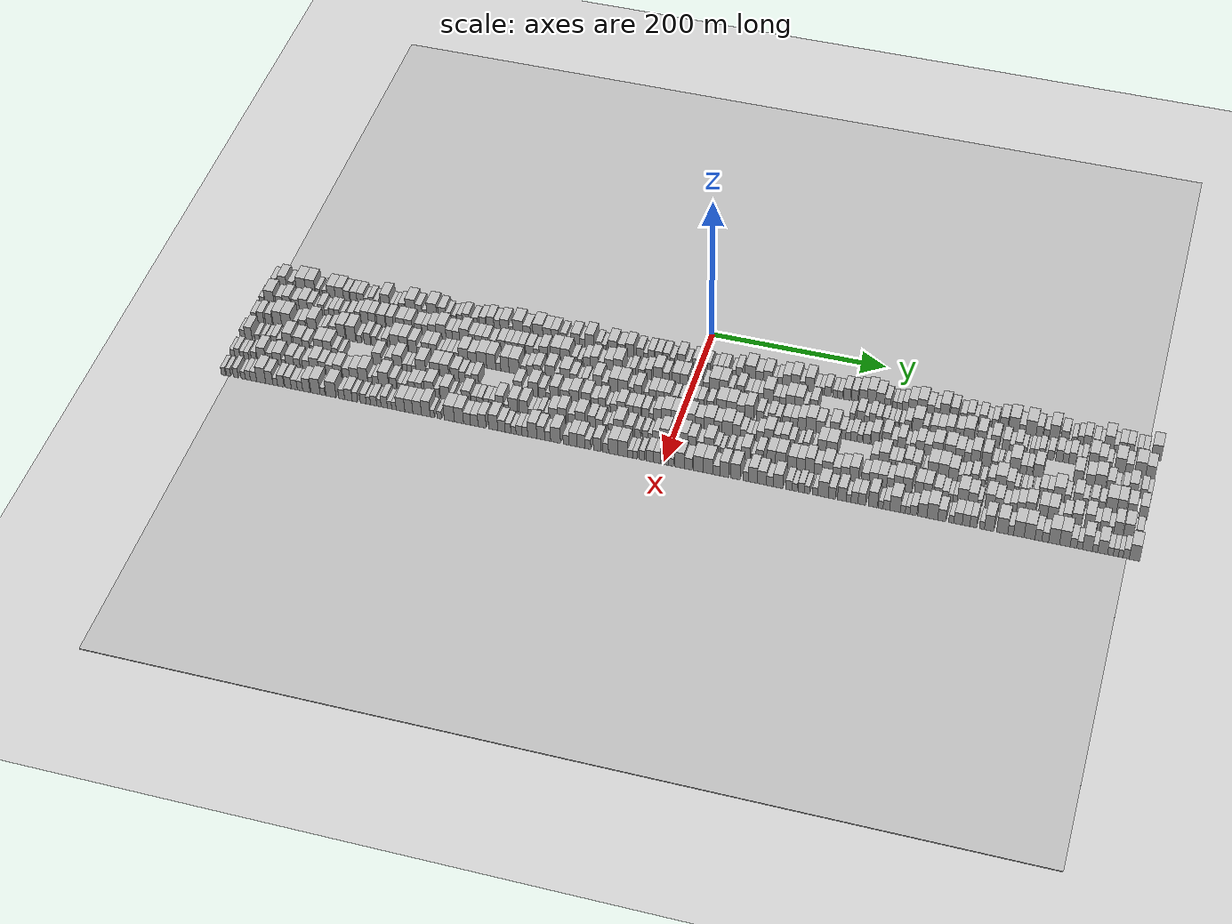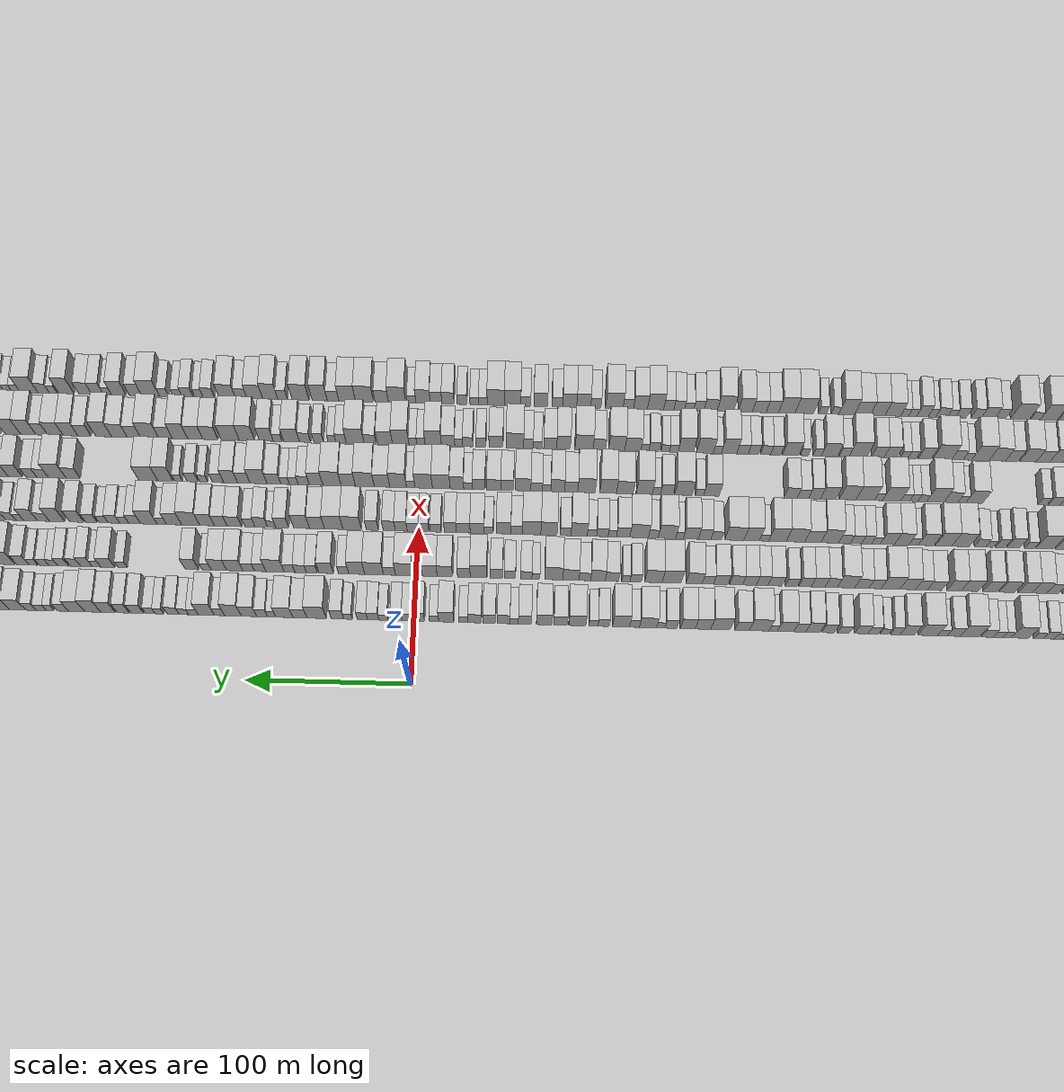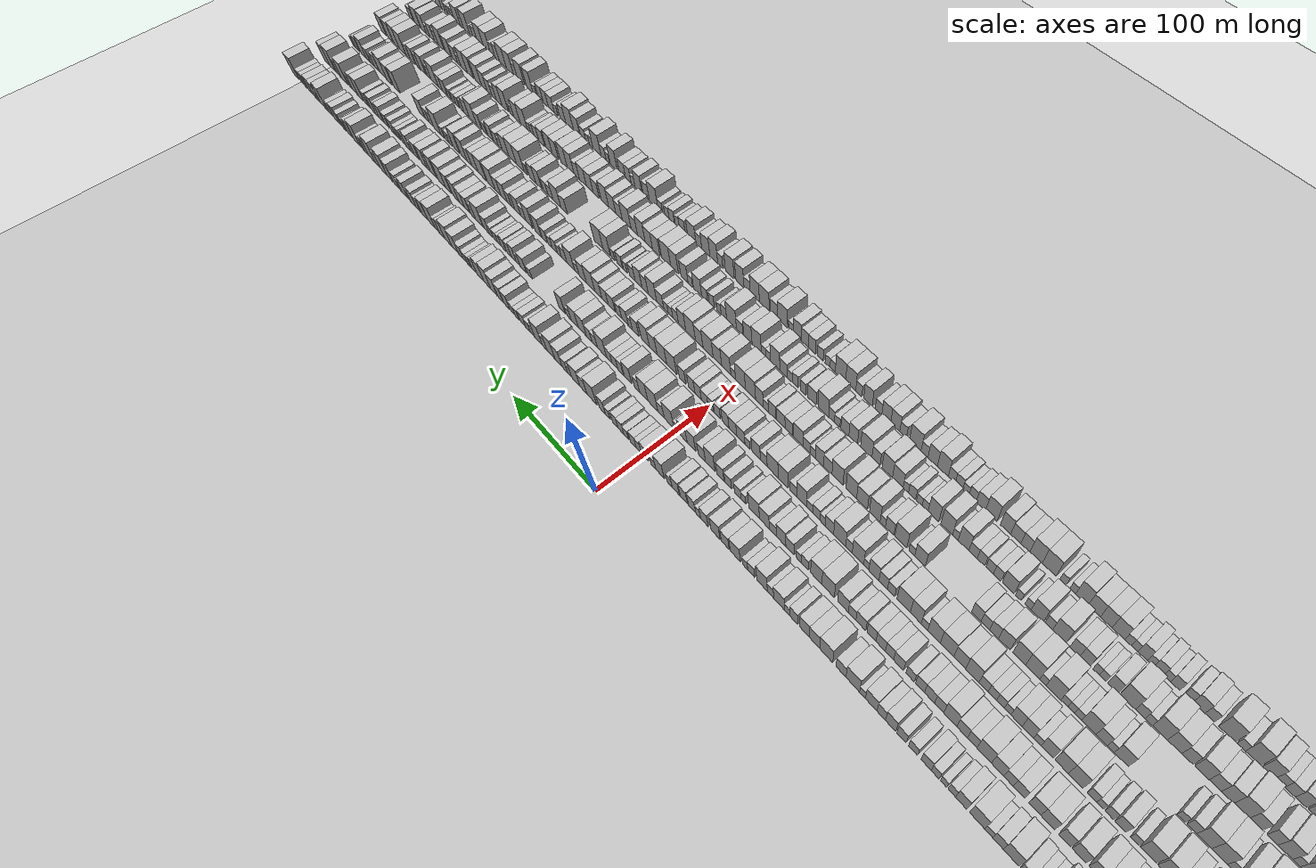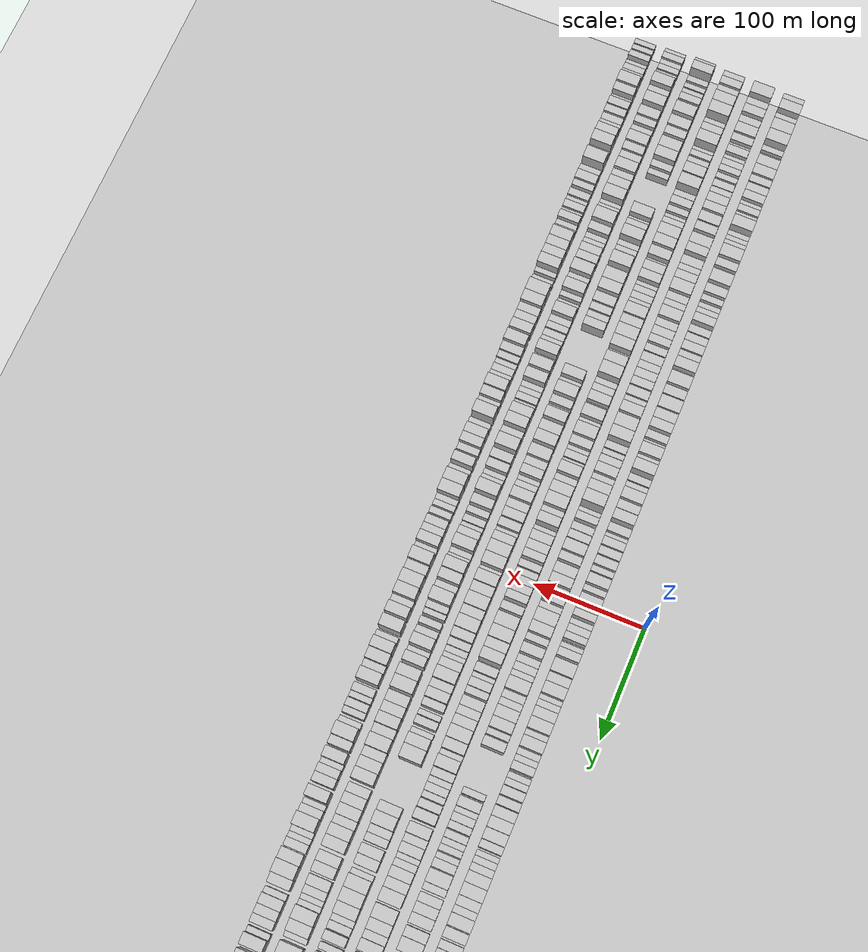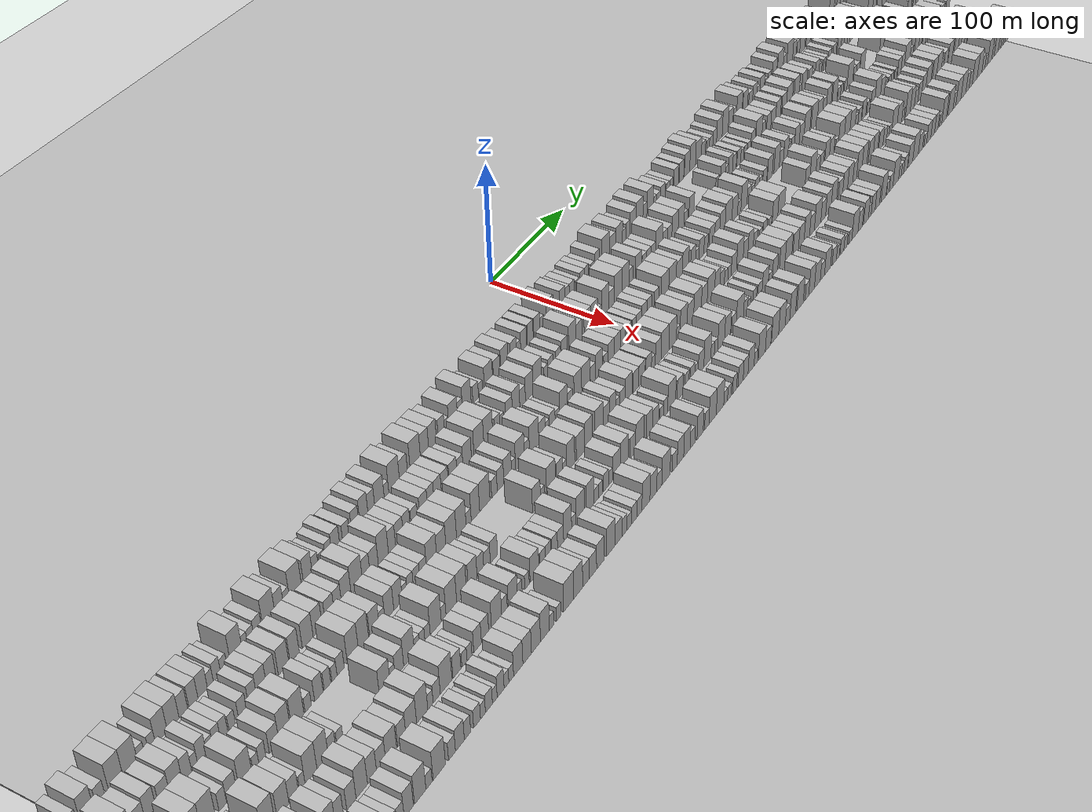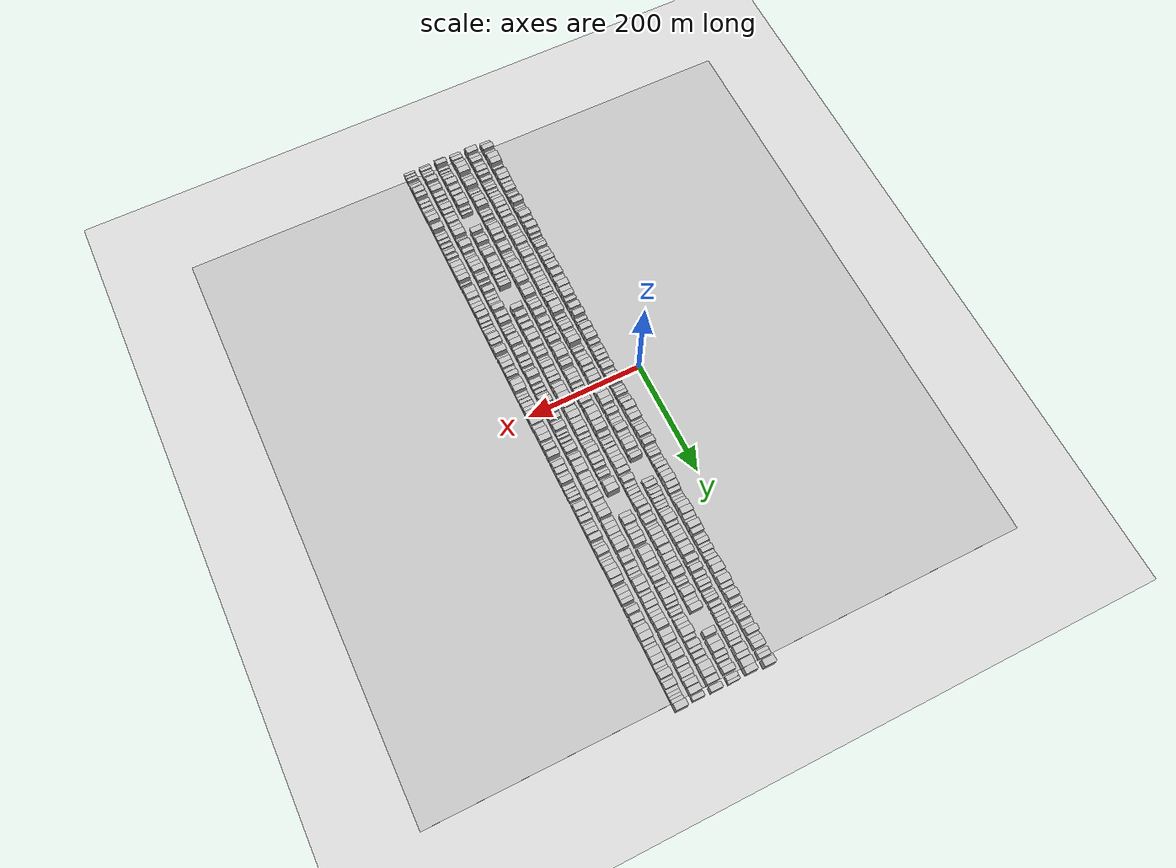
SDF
<?xml version="1.0" encoding="utf-8"?>

<sdf version="1.6">

   <world name="default">

      <gui fullscreen="0">

         <camera name="user_camera">

            <pose>-15 0 4.57585 0 0 0</pose>

            <view_controller>orbit</view_controller>

         </camera>

      </gui>

      <scene>

         <sky>

           <clouds>

             <speed>12</speed>

           </clouds>

         </sky>

         <ambient>0.4 0.4 0.4 1</ambient>

         <background>0.7 0.7 0.7 1</background>

         <shadows>1</shadows>

      </scene>

      <gravity>0 0 -9.8066</gravity>

      <magnetic_field>6e-06 2.3e-05 -4.2e-05</magnetic_field>

      <physics default="0" name="default_physics" type="ode">

         <ode>

            <solver>

               <type>quick</type>

               <iters>10</iters>

               <sor>1.0</sor>

               <use_dynamic_moi_rescaling>0</use_dynamic_moi_rescaling>

            </solver>

            <constraints>

               <cfm>0</cfm>

               <erp>0.2</erp>

               <contact_max_correcting_vel>100</contact_max_correcting_vel>

               <contact_surface_layer>0.001</contact_surface_layer>

            </constraints>

         </ode>

         <max_step_size>0.004</max_step_size>

         <real_time_factor>1</real_time_factor>

         <real_time_update_rate>250</real_time_update_rate>

      </physics>

      <light name="sun" type="directional">

         <cast_shadows>1</cast_shadows>

         <pose>0 0 10 0 0 0</pose>

         <diffuse>0.8 0.8 0.8 1</diffuse>

         <specular>0.2 0.2 0.2 1</specular>

         <attenuation>

            <range>1000</range>

            <constant>0.9</constant>

            <linear>0.01</linear>

            <quadratic>0.001</quadratic>

         </attenuation>

         <direction>-0.5 0.1 -0.9</direction>

      </light>

      <include>

         <name>ground_plane_1</name>

         <uri>model://HANNAS_ground_plane</uri>

         <pose>0 0 0  0 0 0</pose>

      </include>

      <include>

         <name>ground_plane_2</name>

         <uri>model://HANNAS_ground_plane</uri>

         <pose>100 0 0  0 0 0</pose>

      </include>

      <model name="building_1">

         <static>1</static>

         <pose frame="">50.0000 -503.6924 0 0.000000 0.000000 0.000000</pose>

         <link name="link">

            <pose frame="">0 0 7.50 0 0 0</pose>

            <collision name="collision">

               <geometry>

                  <box>

                     <size>20.0000 6.6153 15.0000</size>

                  </box>

               </geometry>

               <max_contacts>10</max_contacts>

               <surface>

                  <contact>

                     <ode/>

                  </contact>

                  <bounce/>

                  <friction>

                     <torsional>

                        <ode/>

                     </torsional>

                     <ode/>

                  </friction>

               </surface>

            </collision>

            <visual name="visual">

               <cast_shadows>0</cast_shadows>

               <geometry>

                  <box>

                     <size>20.0000 6.6153 15.0000</size>

                  </box>

               </geometry>

               <material>

                  <script>

                     <uri>model://HANNAS_wall/materials/scripts</uri>

                     <uri>model://HANNAS_wall/materials/textures</uri>

                     <name>vrc/HANNAS_wall</name>

                  </script>

               </material>

            </visual>

            <self_collide>0</self_collide>

            <enable_wind>0</enable_wind>

            <kinematic>0</kinematic>

         </link>

      </model>

      <model name="building_2">

         <static>1</static>

         <pose frame="">50.0000 -493.3215 0 0.000000 0.000000 0.000000</pose>

         <link name="link">

            <pose frame="">0 0 10.50 0 0 0</pose>

            <collision name="collision">

               <geometry>

                  <box>

                     <size>20.0000 10.1265 21.0000</size>

                  </box>

               </geometry>

               <max_contacts>10</max_contacts>

               <surface>

                  <contact>

                     <ode/>

                  </contact>

                  <bounce/>

                  <friction>

                     <torsional>

                        <ode/>

                     </torsional>

                     <ode/>

                  </friction>

               </surface>

            </collision>

            <visual name="visual">

               <cast_shadows>0</cast_shadows>

               <geometry>

                  <box>

                     <size>20.0000 10.1265 21.0000</size>

                  </box>

               </geometry>

               <material>

                  <script>

                     <uri>model://HANNAS_wall/materials/scripts</uri>

                     <uri>model://HANNAS_wall/materials/textures</uri>

                     <name>vrc/HANNAS_wall</name>

                  </script>

               </material>

            </visual>

            <self_collide>0</self_collide>

            <enable_wind>0</enable_wind>

            <kinematic>0</kinematic>

         </link>

      </model>

      <model name="building_3">

         <static>1</static>

         <pose frame="">50.0000 -482.7223 0 0.000000 0.000000 0.000000</pose>

         <link name="link">

            <pose frame="">0 0 7.50 0 0 0</pose>

            <collision name="collision">

               <geometry>

                  <box>

                     <size>20.0000 7.0718 15.0000</size>

                  </box>

               </geometry>

               <max_contacts>10</max_contacts>

               <surface>

                  <contact>

                     <ode/>

                  </contact>

                  <bounce/>

                  <friction>

                     <torsional>

                        <ode/>

                     </torsional>

                     <ode/>

                  </friction>

               </surface>

            </collision>

            <visual name="visual">

               <cast_shadows>0</cast_shadows>

               <geometry>

                  <box>

                     <size>20.0000 7.0718 15.0000</size>

                  </box>

               </geometry>

               <material>

                  <script>

                     <uri>model://HANNAS_wall/materials/scripts</uri>

                     <uri>model://HANNAS_wall/materials/textures</uri>

                     <name>vrc/HANNAS_wall</name>

                  </script>

               </material>

            </visual>

            <self_collide>0</self_collide>

            <enable_wind>0</enable_wind>

            <kinematic>0</kinematic>

         </link>

      </model>

      <model name="building_4">

         <static>1</static>

         <pose frame="">50.0000 -470.5468 0 0.000000 0.000000 0.000000</pose>

         <link name="link">

            <pose frame="">0 0 12.00 0 0 0</pose>

            <collision name="collision">

               <geometry>

                  <box>

                     <size>20.0000 11.2794 24.0000</size>

                  </box>

               </geometry>

               <max_contacts>10</max_contacts>

               <surface>

                  <contact>

                     <ode/>

                  </contact>

                  <bounce/>

                  <friction>

                     <torsional>

                        <ode/>

                     </torsional>

                     <ode/>

                  </friction>

               </surface>

            </collision>

            <visual name="visual">

               <cast_shadows>0</cast_shadows>

               <geometry>

                  <box>

                     <size>20.0000 11.2794 24.0000</size>

                  </box>

               </geometry>

               <material>

                  <script>

                     <uri>model://HANNAS_wall/materials/scripts</uri>

                     <uri>model://HANNAS_wall/materials/textures</uri>

                     <name>vrc/HANNAS_wall</name>

                  </script>

               </material>

            </visual>

            <self_collide>0</self_collide>

            <enable_wind>0</enable_wind>

            <kinematic>0</kinematic>

         </link>

      </model>

      <model name="building_5">

         <static>1</static>

         <pose frame="">50.0000 -459.0999 0 0.000000 0.000000 0.000000</pose>

         <link name="link">

            <pose frame="">0 0 12.00 0 0 0</pose>

            <collision name="collision">

               <geometry>

                  <box>

                     <size>20.0000 11.6143 24.0000</size>

                  </box>

               </geometry>

               <max_contacts>10</max_contacts>

               <surface>

                  <contact>

                     <ode/>

                  </contact>

                  <bounce/>

                  <friction>

                     <torsional>

                        <ode/>

                     </torsional>

                     <ode/>

                  </friction>

               </surface>

            </collision>

            <visual name="visual">

               <cast_shadows>0</cast_shadows>

               <geometry>

                  <box>

                     <size>20.0000 11.6143 24.0000</size>

                  </box>

               </geometry>

               <material>

                  <script>

                     <uri>model://HANNAS_wall/materials/scripts</uri>

                     <uri>model://HANNAS_wall/materials/textures</uri>

                     <name>vrc/HANNAS_wall</name>

                  </script>

               </material>

            </visual>

            <self_collide>0</self_collide>

            <enable_wind>0</enable_wind>

            <kinematic>0</kinematic>

         </link>

      </model>

      <model name="building_6">

         <static>1</static>

         <pose frame="">50.0000 -450.4534 0 0.000000 0.000000 0.000000</pose>

         <link name="link">

            <pose frame="">0 0 6.00 0 0 0</pose>

            <collision name="collision">

               <geometry>

                  <box>

                     <size>20.0000 5.6787 12.0000</size>

                  </box>

               </geometry>

               <max_contacts>10</max_contacts>

               <surface>

                  <contact>

                     <ode/>

                  </contact>

                  <bounce/>

                  <friction>

                     <torsional>

                        <ode/>

                     </torsional>

                     <ode/>

                  </friction>

               </surface>

            </collision>

            <visual name="visual">

               <cast_shadows>0</cast_shadows>

               <geometry>

                  <box>

                     <size>20.0000 5.6787 12.0000</size>

                  </box>

               </geometry>

               <material>

                  <script>

                     <uri>model://HANNAS_wall/materials/scripts</uri>

                     <uri>model://HANNAS_wall/materials/textures</uri>

                     <name>vrc/HANNAS_wall</name>

                  </script>

               </material>

            </visual>

            <self_collide>0</self_collide>

            <enable_wind>0</enable_wind>

            <kinematic>0</kinematic>

         </link>

      </model>

      <model name="building_7">

         <static>1</static>

         <pose frame="">50.0000 -441.7250 0 0.000000 0.000000 0.000000</pose>

         <link name="link">

            <pose frame="">0 0 6.00 0 0 0</pose>

            <collision name="collision">

               <geometry>

                  <box>

                     <size>20.0000 5.7782 12.0000</size>

                  </box>

               </geometry>

               <max_contacts>10</max_contacts>

               <surface>

                  <contact>

                     <ode/>

                  </contact>

                  <bounce/>

                  <friction>

                     <torsional>

                        <ode/>

                     </torsional>

                     <ode/>

                  </friction>

               </surface>

            </collision>

            <visual name="visual">

               <cast_shadows>0</cast_shadows>

               <geometry>

                  <box>

                     <size>20.0000 5.7782 12.0000</size>

                  </box>

               </geometry>

               <material>

                  <script>

                     <uri>model://HANNAS_wall/materials/scripts</uri>

                     <uri>model://HANNAS_wall/materials/textures</uri>

                     <name>vrc/HANNAS_wall</name>

                  </script>

               </material>

            </visual>

            <self_collide>0</self_collide>

            <enable_wind>0</enable_wind>

            <kinematic>0</kinematic>

         </link>

      </model>

      <model name="building_8">

         <static>1</static>

         <pose frame="">50.0000 -433.8668 0 0.000000 0.000000 0.000000</pose>

         <link name="link">

            <pose frame="">0 0 10.50 0 0 0</pose>

            <collision name="collision">

               <geometry>

                  <box>

                     <size>20.0000 9.9382 21.0000</size>

                  </box>

               </geometry>

               <max_contacts>10</max_contacts>

               <surface>

                  <contact>

                     <ode/>

                  </contact>

                  <bounce/>

                  <friction>

                     <torsional>

                        <ode/>

                     </torsional>

                     <ode/>

                  </friction>

               </surface>

            </collision>

            <visual name="visual">

               <cast_shadows>0</cast_shadows>

               <geometry>

                  <box>

                     <size>20.0000 9.9382 21.0000</size>

                  </box>

               </geometry>

               <material>

                  <script>

                     <uri>model://HANNAS_wall/materials/scripts</uri>

                     <uri>model://HANNAS_wall/materials/textures</uri>

                     <name>vrc/HANNAS_wall</name>

                  </script>

               </material>

            </visual>

            <self_collide>0</self_collide>

            <enable_wind>0</enable_wind>

            <kinematic>0</kinematic>

         </link>

      </model>

      <model name="building_9">

         <static>1</static>

         <pose frame="">50.0000 -423.8843 0 0.000000 0.000000 0.000000</pose>

         <link name="link">

            <pose frame="">0 0 10.50 0 0 0</pose>

            <collision name="collision">

               <geometry>

                  <box>

                     <size>20.0000 10.0267 21.0000</size>

                  </box>

               </geometry>

               <max_contacts>10</max_contacts>

               <surface>

                  <contact>

                     <ode/>

                  </contact>

                  <bounce/>

                  <friction>

                     <torsional>

                        <ode/>

                     </torsional>

                     <ode/>

                  </friction>

               </surface>

            </collision>

            <visual name="visual">

               <cast_shadows>0</cast_shadows>

               <geometry>

                  <box>

                     <size>20.0000 10.0267 21.0000</size>

                  </box>

               </geometry>

               <material>

                  <script>

                     <uri>model://HANNAS_wall/materials/scripts</uri>

                     <uri>model://HANNAS_wall/materials/textures</uri>

                     <name>vrc/HANNAS_wall</name>

                  </script>

               </material>

            </visual>

            <self_collide>0</self_collide>

            <enable_wind>0</enable_wind>

            <kinematic>0</kinematic>

         </link>

      </model>

      <model name="building_10">

         <static>1</static>

         <pose frame="">50.0000 -415.1859 0 0.000000 0.000000 0.000000</pose>

         <link name="link">

            <pose frame="">0 0 9.00 0 0 0</pose>

            <collision name="collision">

               <geometry>

                  <box>

                     <size>20.0000 7.3701 18.0000</size>

                  </box>

               </geometry>

               <max_contacts>10</max_contacts>

               <surface>

                  <contact>

                     <ode/>

                  </contact>

                  <bounce/>

                  <friction>

                     <torsional>

                        <ode/>

                     </torsional>

                     <ode/>

                  </friction>

               </surface>

            </collision>

            <visual name="visual">

               <cast_shadows>0</cast_shadows>

               <geometry>

                  <box>

                     <size>20.0000 7.3701 18.0000</size>

                  </box>

               </geometry>

               <material>

                  <script>

                     <uri>model://HANNAS_wall/materials/scripts</uri>

                     <uri>model://HANNAS_wall/materials/textures</uri>

                     <name>vrc/HANNAS_wall</name>

                  </script>

               </material>

            </visual>

            <self_collide>0</self_collide>

            <enable_wind>0</enable_wind>

            <kinematic>0</kinematic>

         </link>

      </model>

      <model name="building_11">

         <static>1</static>

         <pose frame="">50.0000 -406.6065 0 0.000000 0.000000 0.000000</pose>

         <link name="link">

            <pose frame="">0 0 9.00 0 0 0</pose>

            <collision name="collision">

               <geometry>

                  <box>

                     <size>20.0000 7.7887 18.0000</size>

                  </box>

               </geometry>

               <max_contacts>10</max_contacts>

               <surface>

                  <contact>

                     <ode/>

                  </contact>

                  <bounce/>

                  <friction>

                     <torsional>

                        <ode/>

                     </torsional>

                     <ode/>

                  </friction>

               </surface>

            </collision>

            <visual name="visual">

               <cast_shadows>0</cast_shadows>

               <geometry>

                  <box>

                     <size>20.0000 7.7887 18.0000</size>

                  </box>

               </geometry>

               <material>

                  <script>

                     <uri>model://HANNAS_wall/materials/scripts</uri>

                     <uri>model://HANNAS_wall/materials/textures</uri>

                     <name>vrc/HANNAS_wall</name>

                  </script>

               </material>

            </visual>

            <self_collide>0</self_collide>

            <enable_wind>0</enable_wind>

            <kinematic>0</kinematic>

         </link>

      </model>

      <model name="building_12">

         <static>1</static>

         <pose frame="">50.0000 -398.5526 0 0.000000 0.000000 0.000000</pose>

         <link name="link">

            <pose frame="">0 0 9.00 0 0 0</pose>

            <collision name="collision">

               <geometry>

                  <box>

                     <size>20.0000 8.3190 18.0000</size>

                  </box>

               </geometry>

               <max_contacts>10</max_contacts>

               <surface>

                  <contact>

                     <ode/>

                  </contact>

                  <bounce/>

                  <friction>

                     <torsional>

                        <ode/>

                     </torsional>

                     <ode/>

                  </friction>

               </surface>

            </collision>

            <visual name="visual">

               <cast_shadows>0</cast_shadows>

               <geometry>

                  <box>

                     <size>20.0000 8.3190 18.0000</size>

                  </box>

               </geometry>

               <material>

                  <script>

                     <uri>model://HANNAS_wall/materials/scripts</uri>

                     <uri>model://HANNAS_wall/materials/textures</uri>

                     <name>vrc/HANNAS_wall</name>

                  </script>

               </material>

            </visual>

            <self_collide>0</self_collide>

            <enable_wind>0</enable_wind>

            <kinematic>0</kinematic>

         </link>

      </model>

      <model name="building_13">

         <static>1</static>

         <pose frame="">50.0000 -391.7792 0 0.000000 0.000000 0.000000</pose>

         <link name="link">

            <pose frame="">0 0 6.00 0 0 0</pose>

            <collision name="collision">

               <geometry>

                  <box>

                     <size>20.0000 5.2278 12.0000</size>

                  </box>

               </geometry>

               <max_contacts>10</max_contacts>

               <surface>

                  <contact>

                     <ode/>

                  </contact>

                  <bounce/>

                  <friction>

                     <torsional>

                        <ode/>

                     </torsional>

                     <ode/>

                  </friction>

               </surface>

            </collision>

            <visual name="visual">

               <cast_shadows>0</cast_shadows>

               <geometry>

                  <box>

                     <size>20.0000 5.2278 12.0000</size>

                  </box>

               </geometry>

               <material>

                  <script>

                     <uri>model://HANNAS_wall/materials/scripts</uri>

                     <uri>model://HANNAS_wall/materials/textures</uri>

                     <name>vrc/HANNAS_wall</name>

                  </script>

               </material>

            </visual>

            <self_collide>0</self_collide>

            <enable_wind>0</enable_wind>

            <kinematic>0</kinematic>

         </link>

      </model>

      <model name="building_14">

         <static>1</static>

         <pose frame="">50.0000 -385.8373 0 0.000000 0.000000 0.000000</pose>

         <link name="link">

            <pose frame="">0 0 7.50 0 0 0</pose>

            <collision name="collision">

               <geometry>

                  <box>

                     <size>20.0000 6.6561 15.0000</size>

                  </box>

               </geometry>

               <max_contacts>10</max_contacts>

               <surface>

                  <contact>

                     <ode/>

                  </contact>

                  <bounce/>

                  <friction>

                     <torsional>

                        <ode/>

                     </torsional>

                     <ode/>

                  </friction>

               </surface>

            </collision>

            <visual name="visual">

               <cast_shadows>0</cast_shadows>

               <geometry>

                  <box>

                     <size>20.0000 6.6561 15.0000</size>

                  </box>

               </geometry>

               <material>

                  <script>

                     <uri>model://HANNAS_wall/materials/scripts</uri>

                     <uri>model://HANNAS_wall/materials/textures</uri>

                     <name>vrc/HANNAS_wall</name>

                  </script>

               </material>

            </visual>

            <self_collide>0</self_collide>

            <enable_wind>0</enable_wind>

            <kinematic>0</kinematic>

         </link>

      </model>

      <model name="building_15">

         <static>1</static>

         <pose frame="">50.0000 -379.6564 0 0.000000 0.000000 0.000000</pose>

         <link name="link">

            <pose frame="">0 0 6.00 0 0 0</pose>

            <collision name="collision">

               <geometry>

                  <box>

                     <size>20.0000 5.7058 12.0000</size>

                  </box>

               </geometry>

               <max_contacts>10</max_contacts>

               <surface>

                  <contact>

                     <ode/>

                  </contact>

                  <bounce/>

                  <friction>

                     <torsional>

                        <ode/>

                     </torsional>

                     <ode/>

                  </friction>

               </surface>

            </collision>

            <visual name="visual">

               <cast_shadows>0</cast_shadows>

               <geometry>

                  <box>

                     <size>20.0000 5.7058 12.0000</size>

                  </box>

               </geometry>

               <material>

                  <script>

                     <uri>model://HANNAS_wall/materials/scripts</uri>

                     <uri>model://HANNAS_wall/materials/textures</uri>

                     <name>vrc/HANNAS_wall</name>

                  </script>

               </material>

            </visual>

            <self_collide>0</self_collide>

            <enable_wind>0</enable_wind>

            <kinematic>0</kinematic>

         </link>

      </model>

      <model name="building_16">

         <static>1</static>

         <pose frame="">50.0000 -368.4051 0 0.000000 0.000000 0.000000</pose>

         <link name="link">

            <pose frame="">0 0 12.00 0 0 0</pose>

            <collision name="collision">

               <geometry>

                  <box>

                     <size>20.0000 10.7967 24.0000</size>

                  </box>

               </geometry>

               <max_contacts>10</max_contacts>

               <surface>

                  <contact>

                     <ode/>

                  </contact>

                  <bounce/>

                  <friction>

                     <torsional>

                        <ode/>

                     </torsional>

                     <ode/>

                  </friction>

               </surface>

            </collision>

            <visual name="visual">

               <cast_shadows>0</cast_shadows>

               <geometry>

                  <box>

                     <size>20.0000 10.7967 24.0000</size>

                  </box>

               </geometry>

               <material>

                  <script>

                     <uri>model://HANNAS_wall/materials/scripts</uri>

                     <uri>model://HANNAS_wall/materials/textures</uri>

                     <name>vrc/HANNAS_wall</name>

                  </script>

               </material>

            </visual>

            <self_collide>0</self_collide>

            <enable_wind>0</enable_wind>

            <kinematic>0</kinematic>

         </link>

      </model>

      <model name="building_17">

         <static>1</static>

         <pose frame="">50.0000 -360.5677 0 0.000000 0.000000 0.000000</pose>

         <link name="link">

            <pose frame="">0 0 6.00 0 0 0</pose>

            <collision name="collision">

               <geometry>

                  <box>

                     <size>20.0000 4.8780 12.0000</size>

                  </box>

               </geometry>

               <max_contacts>10</max_contacts>

               <surface>

                  <contact>

                     <ode/>

                  </contact>

                  <bounce/>

                  <friction>

                     <torsional>

                        <ode/>

                     </torsional>

                     <ode/>

                  </friction>

               </surface>

            </collision>

            <visual name="visual">

               <cast_shadows>0</cast_shadows>

               <geometry>

                  <box>

                     <size>20.0000 4.8780 12.0000</size>

                  </box>

               </geometry>

               <material>

                  <script>

                     <uri>model://HANNAS_wall/materials/scripts</uri>

                     <uri>model://HANNAS_wall/materials/textures</uri>

                     <name>vrc/HANNAS_wall</name>

                  </script>

               </material>

            </visual>

            <self_collide>0</self_collide>

            <enable_wind>0</enable_wind>

            <kinematic>0</kinematic>

         </link>

      </model>

      <model name="building_18">

         <static>1</static>

         <pose frame="">50.0000 -355.1719 0 0.000000 0.000000 0.000000</pose>

         <link name="link">

            <pose frame="">0 0 6.00 0 0 0</pose>

            <collision name="collision">

               <geometry>

                  <box>

                     <size>20.0000 5.9137 12.0000</size>

                  </box>

               </geometry>

               <max_contacts>10</max_contacts>

               <surface>

                  <contact>

                     <ode/>

                  </contact>

                  <bounce/>

                  <friction>

                     <torsional>

                        <ode/>

                     </torsional>

                     <ode/>

                  </friction>

               </surface>

            </collision>

            <visual name="visual">

               <cast_shadows>0</cast_shadows>

               <geometry>

                  <box>

                     <size>20.0000 5.9137 12.0000</size>

                  </box>

               </geometry>

               <material>

                  <script>

                     <uri>model://HANNAS_wall/materials/scripts</uri>

                     <uri>model://HANNAS_wall/materials/textures</uri>

                     <name>vrc/HANNAS_wall</name>

                  </script>

               </material>

            </visual>

            <self_collide>0</self_collide>

            <enable_wind>0</enable_wind>

            <kinematic>0</kinematic>

         </link>

      </model>

      <model name="building_19">

         <static>1</static>

         <pose frame="">50.0000 -348.5238 0 0.000000 0.000000 0.000000</pose>

         <link name="link">

            <pose frame="">0 0 7.50 0 0 0</pose>

            <collision name="collision">

               <geometry>

                  <box>

                     <size>20.0000 7.3824 15.0000</size>

                  </box>

               </geometry>

               <max_contacts>10</max_contacts>

               <surface>

                  <contact>

                     <ode/>

                  </contact>

                  <bounce/>

                  <friction>

                     <torsional>

                        <ode/>

                     </torsional>

                     <ode/>

                  </friction>

               </surface>

            </collision>

            <visual name="visual">

               <cast_shadows>0</cast_shadows>

               <geometry>

                  <box>

                     <size>20.0000 7.3824 15.0000</size>

                  </box>

               </geometry>

               <material>

                  <script>

                     <uri>model://HANNAS_wall/materials/scripts</uri>

                     <uri>model://HANNAS_wall/materials/textures</uri>

                     <name>vrc/HANNAS_wall</name>

                  </script>

               </material>

            </visual>

            <self_collide>0</self_collide>

            <enable_wind>0</enable_wind>

            <kinematic>0</kinematic>

         </link>

      </model>

      <model name="building_20">

         <static>1</static>

         <pose frame="">50.0000 -338.0146 0 0.000000 0.000000 0.000000</pose>

         <link name="link">

            <pose frame="">0 0 12.00 0 0 0</pose>

            <collision name="collision">

               <geometry>

                  <box>

                     <size>20.0000 11.6361 24.0000</size>

                  </box>

               </geometry>

               <max_contacts>10</max_contacts>

               <surface>

                  <contact>

                     <ode/>

                  </contact>

                  <bounce/>

                  <friction>

                     <torsional>

                        <ode/>

                     </torsional>

                     <ode/>

                  </friction>

               </surface>

            </collision>

            <visual name="visual">

               <cast_shadows>0</cast_shadows>

               <geometry>

                  <box>

                     <size>20.0000 11.6361 24.0000</size>

                  </box>

               </geometry>

               <material>

                  <script>

                     <uri>model://HANNAS_wall/materials/scripts</uri>

                     <uri>model://HANNAS_wall/materials/textures</uri>

                     <name>vrc/HANNAS_wall</name>

                  </script>

               </material>

            </visual>

            <self_collide>0</self_collide>

            <enable_wind>0</enable_wind>

            <kinematic>0</kinematic>

         </link>

      </model>

      <model name="building_21">

         <static>1</static>

         <pose frame="">50.0000 -328.2203 0 0.000000 0.000000 0.000000</pose>

         <link name="link">

            <pose frame="">0 0 9.00 0 0 0</pose>

            <collision name="collision">

               <geometry>

                  <box>

                     <size>20.0000 7.9525 18.0000</size>

                  </box>

               </geometry>

               <max_contacts>10</max_contacts>

               <surface>

                  <contact>

                     <ode/>

                  </contact>

                  <bounce/>

                  <friction>

                     <torsional>

                        <ode/>

                     </torsional>

                     <ode/>

                  </friction>

               </surface>

            </collision>

            <visual name="visual">

               <cast_shadows>0</cast_shadows>

               <geometry>

                  <box>

                     <size>20.0000 7.9525 18.0000</size>

                  </box>

               </geometry>

               <material>

                  <script>

                     <uri>model://HANNAS_wall/materials/scripts</uri>

                     <uri>model://HANNAS_wall/materials/textures</uri>

                     <name>vrc/HANNAS_wall</name>

                  </script>

               </material>

            </visual>

            <self_collide>0</self_collide>

            <enable_wind>0</enable_wind>

            <kinematic>0</kinematic>

         </link>

      </model>

      <model name="building_22">

         <static>1</static>

         <pose frame="">50.0000 -321.3090 0 0.000000 0.000000 0.000000</pose>

         <link name="link">

            <pose frame="">0 0 6.00 0 0 0</pose>

            <collision name="collision">

               <geometry>

                  <box>

                     <size>20.0000 5.8701 12.0000</size>

                  </box>

               </geometry>

               <max_contacts>10</max_contacts>

               <surface>

                  <contact>

                     <ode/>

                  </contact>

                  <bounce/>

                  <friction>

                     <torsional>

                        <ode/>

                     </torsional>

                     <ode/>

                  </friction>

               </surface>

            </collision>

            <visual name="visual">

               <cast_shadows>0</cast_shadows>

               <geometry>

                  <box>

                     <size>20.0000 5.8701 12.0000</size>

                  </box>

               </geometry>

               <material>

                  <script>

                     <uri>model://HANNAS_wall/materials/scripts</uri>

                     <uri>model://HANNAS_wall/materials/textures</uri>

                     <name>vrc/HANNAS_wall</name>

                  </script>

               </material>

            </visual>

            <self_collide>0</self_collide>

            <enable_wind>0</enable_wind>

            <kinematic>0</kinematic>

         </link>

      </model>

      <model name="building_23">

         <static>1</static>

         <pose frame="">50.0000 -312.5059 0 0.000000 0.000000 0.000000</pose>

         <link name="link">

            <pose frame="">0 0 12.00 0 0 0</pose>

            <collision name="collision">

               <geometry>

                  <box>

                     <size>20.0000 11.7361 24.0000</size>

                  </box>

               </geometry>

               <max_contacts>10</max_contacts>

               <surface>

                  <contact>

                     <ode/>

                  </contact>

                  <bounce/>

                  <friction>

                     <torsional>

                        <ode/>

                     </torsional>

                     <ode/>

                  </friction>

               </surface>

            </collision>

            <visual name="visual">

               <cast_shadows>0</cast_shadows>

               <geometry>

                  <box>

                     <size>20.0000 11.7361 24.0000</size>

                  </box>

               </geometry>

               <material>

                  <script>

                     <uri>model://HANNAS_wall/materials/scripts</uri>

                     <uri>model://HANNAS_wall/materials/textures</uri>

                     <name>vrc/HANNAS_wall</name>

                  </script>

               </material>

            </visual>

            <self_collide>0</self_collide>

            <enable_wind>0</enable_wind>

            <kinematic>0</kinematic>

         </link>

      </model>

      <model name="building_24">

         <static>1</static>

         <pose frame="">50.0000 -300.2380 0 0.000000 0.000000 0.000000</pose>

         <link name="link">

            <pose frame="">0 0 10.50 0 0 0</pose>

            <collision name="collision">

               <geometry>

                  <box>

                     <size>20.0000 8.7996 21.0000</size>

                  </box>

               </geometry>

               <max_contacts>10</max_contacts>

               <surface>

                  <contact>

                     <ode/>

                  </contact>

                  <bounce/>

                  <friction>

                     <torsional>

                        <ode/>

                     </torsional>

                     <ode/>

                  </friction>

               </surface>

            </collision>

            <visual name="visual">

               <cast_shadows>0</cast_shadows>

               <geometry>

                  <box>

                     <size>20.0000 8.7996 21.0000</size>

                  </box>

               </geometry>

               <material>

                  <script>

                     <uri>model://HANNAS_wall/materials/scripts</uri>

                     <uri>model://HANNAS_wall/materials/textures</uri>

                     <name>vrc/HANNAS_wall</name>

                  </script>

               </material>

            </visual>

            <self_collide>0</self_collide>

            <enable_wind>0</enable_wind>

            <kinematic>0</kinematic>

         </link>

      </model>

      <model name="building_25">

         <static>1</static>

         <pose frame="">50.0000 -292.8315 0 0.000000 0.000000 0.000000</pose>

         <link name="link">

            <pose frame="">0 0 7.50 0 0 0</pose>

            <collision name="collision">

               <geometry>

                  <box>

                     <size>20.0000 6.0135 15.0000</size>

                  </box>

               </geometry>

               <max_contacts>10</max_contacts>

               <surface>

                  <contact>

                     <ode/>

                  </contact>

                  <bounce/>

                  <friction>

                     <torsional>

                        <ode/>

                     </torsional>

                     <ode/>

                  </friction>

               </surface>

            </collision>

            <visual name="visual">

               <cast_shadows>0</cast_shadows>

               <geometry>

                  <box>

                     <size>20.0000 6.0135 15.0000</size>

                  </box>

               </geometry>

               <material>

                  <script>

                     <uri>model://HANNAS_wall/materials/scripts</uri>

                     <uri>model://HANNAS_wall/materials/textures</uri>

                     <name>vrc/HANNAS_wall</name>

                  </script>

               </material>

            </visual>

            <self_collide>0</self_collide>

            <enable_wind>0</enable_wind>

            <kinematic>0</kinematic>

         </link>

      </model>

      <model name="building_26">

         <static>1</static>

         <pose frame="">50.0000 -286.2679 0 0.000000 0.000000 0.000000</pose>

         <link name="link">

            <pose frame="">0 0 6.00 0 0 0</pose>

            <collision name="collision">

               <geometry>

                  <box>

                     <size>20.0000 5.1137 12.0000</size>

                  </box>

               </geometry>

               <max_contacts>10</max_contacts>

               <surface>

                  <contact>

                     <ode/>

                  </contact>

                  <bounce/>

                  <friction>

                     <torsional>

                        <ode/>

                     </torsional>

                     <ode/>

                  </friction>

               </surface>

            </collision>

            <visual name="visual">

               <cast_shadows>0</cast_shadows>

               <geometry>

                  <box>

                     <size>20.0000 5.1137 12.0000</size>

                  </box>

               </geometry>

               <material>

                  <script>

                     <uri>model://HANNAS_wall/materials/scripts</uri>

                     <uri>model://HANNAS_wall/materials/textures</uri>

                     <name>vrc/HANNAS_wall</name>

                  </script>

               </material>

            </visual>

            <self_collide>0</self_collide>

            <enable_wind>0</enable_wind>

            <kinematic>0</kinematic>

         </link>

      </model>

      <model name="building_27">

         <static>1</static>

         <pose frame="">50.0000 -279.5277 0 0.000000 0.000000 0.000000</pose>

         <link name="link">

            <pose frame="">0 0 7.50 0 0 0</pose>

            <collision name="collision">

               <geometry>

                  <box>

                     <size>20.0000 6.3666 15.0000</size>

                  </box>

               </geometry>

               <max_contacts>10</max_contacts>

               <surface>

                  <contact>

                     <ode/>

                  </contact>

                  <bounce/>

                  <friction>

                     <torsional>

                        <ode/>

                     </torsional>

                     <ode/>

                  </friction>

               </surface>

            </collision>

            <visual name="visual">

               <cast_shadows>0</cast_shadows>

               <geometry>

                  <box>

                     <size>20.0000 6.3666 15.0000</size>

                  </box>

               </geometry>

               <material>

                  <script>

                     <uri>model://HANNAS_wall/materials/scripts</uri>

                     <uri>model://HANNAS_wall/materials/textures</uri>

                     <name>vrc/HANNAS_wall</name>

                  </script>

               </material>

            </visual>

            <self_collide>0</self_collide>

            <enable_wind>0</enable_wind>

            <kinematic>0</kinematic>

         </link>

      </model>

      <model name="building_28">

         <static>1</static>

         <pose frame="">50.0000 -272.2532 0 0.000000 0.000000 0.000000</pose>

         <link name="link">

            <pose frame="">0 0 9.00 0 0 0</pose>

            <collision name="collision">

               <geometry>

                  <box>

                     <size>20.0000 8.1825 18.0000</size>

                  </box>

               </geometry>

               <max_contacts>10</max_contacts>

               <surface>

                  <contact>

                     <ode/>

                  </contact>

                  <bounce/>

                  <friction>

                     <torsional>

                        <ode/>

                     </torsional>

                     <ode/>

                  </friction>

               </surface>

            </collision>

            <visual name="visual">

               <cast_shadows>0</cast_shadows>

               <geometry>

                  <box>

                     <size>20.0000 8.1825 18.0000</size>

                  </box>

               </geometry>

               <material>

                  <script>

                     <uri>model://HANNAS_wall/materials/scripts</uri>

                     <uri>model://HANNAS_wall/materials/textures</uri>

                     <name>vrc/HANNAS_wall</name>

                  </script>

               </material>

            </visual>

            <self_collide>0</self_collide>

            <enable_wind>0</enable_wind>

            <kinematic>0</kinematic>

         </link>

      </model>

      <model name="building_29">

         <static>1</static>

         <pose frame="">50.0000 -261.4840 0 0.000000 0.000000 0.000000</pose>

         <link name="link">

            <pose frame="">0 0 7.50 0 0 0</pose>

            <collision name="collision">

               <geometry>

                  <box>

                     <size>20.0000 7.3559 15.0000</size>

                  </box>

               </geometry>

               <max_contacts>10</max_contacts>

               <surface>

                  <contact>

                     <ode/>

                  </contact>

                  <bounce/>

                  <friction>

                     <torsional>

                        <ode/>

                     </torsional>

                     <ode/>

                  </friction>

               </surface>

            </collision>

            <visual name="visual">

               <cast_shadows>0</cast_shadows>

               <geometry>

                  <box>

                     <size>20.0000 7.3559 15.0000</size>

                  </box>

               </geometry>

               <material>

                  <script>

                     <uri>model://HANNAS_wall/materials/scripts</uri>

                     <uri>model://HANNAS_wall/materials/textures</uri>

                     <name>vrc/HANNAS_wall</name>

                  </script>

               </material>

            </visual>

            <self_collide>0</self_collide>

            <enable_wind>0</enable_wind>

            <kinematic>0</kinematic>

         </link>

      </model>

      <model name="building_30">

         <static>1</static>

         <pose frame="">50.0000 -251.9875 0 0.000000 0.000000 0.000000</pose>

         <link name="link">

            <pose frame="">0 0 9.00 0 0 0</pose>

            <collision name="collision">

               <geometry>

                  <box>

                     <size>20.0000 7.6372 18.0000</size>

                  </box>

               </geometry>

               <max_contacts>10</max_contacts>

               <surface>

                  <contact>

                     <ode/>

                  </contact>

                  <bounce/>

                  <friction>

                     <torsional>

                        <ode/>

                     </torsional>

                     <ode/>

                  </friction>

               </surface>

            </collision>

            <visual name="visual">

               <cast_shadows>0</cast_shadows>

               <geometry>

                  <box>

                     <size>20.0000 7.6372 18.0000</size>

                  </box>

               </geometry>

               <material>

                  <script>

                     <uri>model://HANNAS_wall/materials/scripts</uri>

                     <uri>model://HANNAS_wall/materials/textures</uri>

                     <name>vrc/HANNAS_wall</name>

                  </script>

               </material>

            </visual>

            <self_collide>0</self_collide>

            <enable_wind>0</enable_wind>

            <kinematic>0</kinematic>

         </link>

      </model>

      <model name="building_31">

         <static>1</static>

         <pose frame="">50.0000 -242.8185 0 0.000000 0.000000 0.000000</pose>

         <link name="link">

            <pose frame="">0 0 10.50 0 0 0</pose>

            <collision name="collision">

               <geometry>

                  <box>

                     <size>20.0000 8.7008 21.0000</size>

                  </box>

               </geometry>

               <max_contacts>10</max_contacts>

               <surface>

                  <contact>

                     <ode/>

                  </contact>

                  <bounce/>

                  <friction>

                     <torsional>

                        <ode/>

                     </torsional>

                     <ode/>

                  </friction>

               </surface>

            </collision>

            <visual name="visual">

               <cast_shadows>0</cast_shadows>

               <geometry>

                  <box>

                     <size>20.0000 8.7008 21.0000</size>

                  </box>

               </geometry>

               <material>

                  <script>

                     <uri>model://HANNAS_wall/materials/scripts</uri>

                     <uri>model://HANNAS_wall/materials/textures</uri>

                     <name>vrc/HANNAS_wall</name>

                  </script>

               </material>

            </visual>

            <self_collide>0</self_collide>

            <enable_wind>0</enable_wind>

            <kinematic>0</kinematic>

         </link>

      </model>

      <model name="building_32">

         <static>1</static>

         <pose frame="">50.0000 -234.8366 0 0.000000 0.000000 0.000000</pose>

         <link name="link">

            <pose frame="">0 0 9.00 0 0 0</pose>

            <collision name="collision">

               <geometry>

                  <box>

                     <size>20.0000 7.2631 18.0000</size>

                  </box>

               </geometry>

               <max_contacts>10</max_contacts>

               <surface>

                  <contact>

                     <ode/>

                  </contact>

                  <bounce/>

                  <friction>

                     <torsional>

                        <ode/>

                     </torsional>

                     <ode/>

                  </friction>

               </surface>

            </collision>

            <visual name="visual">

               <cast_shadows>0</cast_shadows>

               <geometry>

                  <box>

                     <size>20.0000 7.2631 18.0000</size>

                  </box>

               </geometry>

               <material>

                  <script>

                     <uri>model://HANNAS_wall/materials/scripts</uri>

                     <uri>model://HANNAS_wall/materials/textures</uri>

                     <name>vrc/HANNAS_wall</name>

                  </script>

               </material>

            </visual>

            <self_collide>0</self_collide>

            <enable_wind>0</enable_wind>

            <kinematic>0</kinematic>

         </link>

      </model>

      <model name="building_33">

         <static>1</static>

         <pose frame="">50.0000 -226.1902 0 0.000000 0.000000 0.000000</pose>

         <link name="link">

            <pose frame="">0 0 10.50 0 0 0</pose>

            <collision name="collision">

               <geometry>

                  <box>

                     <size>20.0000 10.0296 21.0000</size>

                  </box>

               </geometry>

               <max_contacts>10</max_contacts>

               <surface>

                  <contact>

                     <ode/>

                  </contact>

                  <bounce/>

                  <friction>

                     <torsional>

                        <ode/>

                     </torsional>

                     <ode/>

                  </friction>

               </surface>

            </collision>

            <visual name="visual">

               <cast_shadows>0</cast_shadows>

               <geometry>

                  <box>

                     <size>20.0000 10.0296 21.0000</size>

                  </box>

               </geometry>

               <material>

                  <script>

                     <uri>model://HANNAS_wall/materials/scripts</uri>

                     <uri>model://HANNAS_wall/materials/textures</uri>

                     <name>vrc/HANNAS_wall</name>

                  </script>

               </material>

            </visual>

            <self_collide>0</self_collide>

            <enable_wind>0</enable_wind>

            <kinematic>0</kinematic>

         </link>

      </model>

      <model name="building_34">

         <static>1</static>

         <pose frame="">50.0000 -218.6514 0 0.000000 0.000000 0.000000</pose>

         <link name="link">

            <pose frame="">0 0 6.00 0 0 0</pose>

            <collision name="collision">

               <geometry>

                  <box>

                     <size>20.0000 5.0481 12.0000</size>

                  </box>

               </geometry>

               <max_contacts>10</max_contacts>

               <surface>

                  <contact>

                     <ode/>

                  </contact>

                  <bounce/>

                  <friction>

                     <torsional>

                        <ode/>

                     </torsional>

                     <ode/>

                  </friction>

               </surface>

            </collision>

            <visual name="visual">

               <cast_shadows>0</cast_shadows>

               <geometry>

                  <box>

                     <size>20.0000 5.0481 12.0000</size>

                  </box>

               </geometry>

               <material>

                  <script>

                     <uri>model://HANNAS_wall/materials/scripts</uri>

                     <uri>model://HANNAS_wall/materials/textures</uri>

                     <name>vrc/HANNAS_wall</name>

                  </script>

               </material>

            </visual>

            <self_collide>0</self_collide>

            <enable_wind>0</enable_wind>

            <kinematic>0</kinematic>

         </link>

      </model>

      <model name="building_35">

         <static>1</static>

         <pose frame="">50.0000 -210.1765 0 0.000000 0.000000 0.000000</pose>

         <link name="link">

            <pose frame="">0 0 12.00 0 0 0</pose>

            <collision name="collision">

               <geometry>

                  <box>

                     <size>20.0000 11.9017 24.0000</size>

                  </box>

               </geometry>

               <max_contacts>10</max_contacts>

               <surface>

                  <contact>

                     <ode/>

                  </contact>

                  <bounce/>

                  <friction>

                     <torsional>

                        <ode/>

                     </torsional>

                     <ode/>

                  </friction>

               </surface>

            </collision>

            <visual name="visual">

               <cast_shadows>0</cast_shadows>

               <geometry>

                  <box>

                     <size>20.0000 11.9017 24.0000</size>

                  </box>

               </geometry>

               <material>

                  <script>

                     <uri>model://HANNAS_wall/materials/scripts</uri>

                     <uri>model://HANNAS_wall/materials/textures</uri>

                     <name>vrc/HANNAS_wall</name>

                  </script>

               </material>

            </visual>

            <self_collide>0</self_collide>

            <enable_wind>0</enable_wind>

            <kinematic>0</kinematic>

         </link>

      </model>

      <model name="building_36">

         <static>1</static>

         <pose frame="">50.0000 -199.7990 0 0.000000 0.000000 0.000000</pose>

         <link name="link">

            <pose frame="">0 0 9.00 0 0 0</pose>

            <collision name="collision">

               <geometry>

                  <box>

                     <size>20.0000 8.8533 18.0000</size>

                  </box>

               </geometry>

               <max_contacts>10</max_contacts>

               <surface>

                  <contact>

                     <ode/>

                  </contact>

                  <bounce/>

                  <friction>

                     <torsional>

                        <ode/>

                     </torsional>

                     <ode/>

                  </friction>

               </surface>

            </collision>

            <visual name="visual">

               <cast_shadows>0</cast_shadows>

               <geometry>

                  <box>

                     <size>20.0000 8.8533 18.0000</size>

                  </box>

               </geometry>

               <material>

                  <script>

                     <uri>model://HANNAS_wall/materials/scripts</uri>

                     <uri>model://HANNAS_wall/materials/textures</uri>

                     <name>vrc/HANNAS_wall</name>

                  </script>

               </material>

            </visual>

            <self_collide>0</self_collide>

            <enable_wind>0</enable_wind>

            <kinematic>0</kinematic>

         </link>

      </model>

      <model name="building_37">

         <static>1</static>

         <pose frame="">50.0000 -186.5069 0 0.000000 0.000000 0.000000</pose>

         <link name="link">

            <pose frame="">0 0 12.00 0 0 0</pose>

            <collision name="collision">

               <geometry>

                  <box>

                     <size>20.0000 11.7307 24.0000</size>

                  </box>

               </geometry>

               <max_contacts>10</max_contacts>

               <surface>

                  <contact>

                     <ode/>

                  </contact>

                  <bounce/>

                  <friction>

                     <torsional>

                        <ode/>

                     </torsional>

                     <ode/>

                  </friction>

               </surface>

            </collision>

            <visual name="visual">

               <cast_shadows>0</cast_shadows>

               <geometry>

                  <box>

                     <size>20.0000 11.7307 24.0000</size>

                  </box>

               </geometry>

               <material>

                  <script>

                     <uri>model://HANNAS_wall/materials/scripts</uri>

                     <uri>model://HANNAS_wall/materials/textures</uri>

                     <name>vrc/HANNAS_wall</name>

                  </script>

               </material>

            </visual>

            <self_collide>0</self_collide>

            <enable_wind>0</enable_wind>

            <kinematic>0</kinematic>

         </link>

      </model>

      <model name="building_38">

         <static>1</static>

         <pose frame="">50.0000 -175.9051 0 0.000000 0.000000 0.000000</pose>

         <link name="link">

            <pose frame="">0 0 10.50 0 0 0</pose>

            <collision name="collision">

               <geometry>

                  <box>

                     <size>20.0000 9.4729 21.0000</size>

                  </box>

               </geometry>

               <max_contacts>10</max_contacts>

               <surface>

                  <contact>

                     <ode/>

                  </contact>

                  <bounce/>

                  <friction>

                     <torsional>

                        <ode/>

                     </torsional>

                     <ode/>

                  </friction>

               </surface>

            </collision>

            <visual name="visual">

               <cast_shadows>0</cast_shadows>

               <geometry>

                  <box>

                     <size>20.0000 9.4729 21.0000</size>

                  </box>

               </geometry>

               <material>

                  <script>

                     <uri>model://HANNAS_wall/materials/scripts</uri>

                     <uri>model://HANNAS_wall/materials/textures</uri>

                     <name>vrc/HANNAS_wall</name>

                  </script>

               </material>

            </visual>

            <self_collide>0</self_collide>

            <enable_wind>0</enable_wind>

            <kinematic>0</kinematic>

         </link>

      </model>

      <model name="building_39">

         <static>1</static>

         <pose frame="">50.0000 -166.6279 0 0.000000 0.000000 0.000000</pose>

         <link name="link">

            <pose frame="">0 0 10.50 0 0 0</pose>

            <collision name="collision">

               <geometry>

                  <box>

                     <size>20.0000 9.0814 21.0000</size>

                  </box>

               </geometry>

               <max_contacts>10</max_contacts>

               <surface>

                  <contact>

                     <ode/>

                  </contact>

                  <bounce/>

                  <friction>

                     <torsional>

                        <ode/>

                     </torsional>

                     <ode/>

                  </friction>

               </surface>

            </collision>

            <visual name="visual">

               <cast_shadows>0</cast_shadows>

               <geometry>

                  <box>

                     <size>20.0000 9.0814 21.0000</size>

                  </box>

               </geometry>

               <material>

                  <script>

                     <uri>model://HANNAS_wall/materials/scripts</uri>

                     <uri>model://HANNAS_wall/materials/textures</uri>

                     <name>vrc/HANNAS_wall</name>

                  </script>

               </material>

            </visual>

            <self_collide>0</self_collide>

            <enable_wind>0</enable_wind>

            <kinematic>0</kinematic>

         </link>

      </model>

      <model name="building_40">

         <static>1</static>

         <pose frame="">50.0000 -156.3655 0 0.000000 0.000000 0.000000</pose>

         <link name="link">

            <pose frame="">0 0 9.00 0 0 0</pose>

            <collision name="collision">

               <geometry>

                  <box>

                     <size>20.0000 7.4435 18.0000</size>

                  </box>

               </geometry>

               <max_contacts>10</max_contacts>

               <surface>

                  <contact>

                     <ode/>

                  </contact>

                  <bounce/>

                  <friction>

                     <torsional>

                        <ode/>

                     </torsional>

                     <ode/>

                  </friction>

               </surface>

            </collision>

            <visual name="visual">

               <cast_shadows>0</cast_shadows>

               <geometry>

                  <box>

                     <size>20.0000 7.4435 18.0000</size>

                  </box>

               </geometry>

               <material>

                  <script>

                     <uri>model://HANNAS_wall/materials/scripts</uri>

                     <uri>model://HANNAS_wall/materials/textures</uri>

                     <name>vrc/HANNAS_wall</name>

                  </script>

               </material>

            </visual>

            <self_collide>0</self_collide>

            <enable_wind>0</enable_wind>

            <kinematic>0</kinematic>

         </link>

      </model>

      <model name="building_41">

         <static>1</static>

         <pose frame="">50.0000 -150.1581 0 0.000000 0.000000 0.000000</pose>

         <link name="link">

            <pose frame="">0 0 6.00 0 0 0</pose>

            <collision name="collision">

               <geometry>

                  <box>

                     <size>20.0000 4.9712 12.0000</size>

                  </box>

               </geometry>

               <max_contacts>10</max_contacts>

               <surface>

                  <contact>

                     <ode/>

                  </contact>

                  <bounce/>

                  <friction>

                     <torsional>

                        <ode/>

                     </torsional>

                     <ode/>

                  </friction>

               </surface>

            </collision>

            <visual name="visual">

               <cast_shadows>0</cast_shadows>

               <geometry>

                  <box>

                     <size>20.0000 4.9712 12.0000</size>

                  </box>

               </geometry>

               <material>

                  <script>

                     <uri>model://HANNAS_wall/materials/scripts</uri>

                     <uri>model://HANNAS_wall/materials/textures</uri>

                     <name>vrc/HANNAS_wall</name>

                  </script>

               </material>

            </visual>

            <self_collide>0</self_collide>

            <enable_wind>0</enable_wind>

            <kinematic>0</kinematic>

         </link>

      </model>

      <model name="building_42">

         <static>1</static>

         <pose frame="">50.0000 -142.4703 0 0.000000 0.000000 0.000000</pose>

         <link name="link">

            <pose frame="">0 0 10.50 0 0 0</pose>

            <collision name="collision">

               <geometry>

                  <box>

                     <size>20.0000 10.4044 21.0000</size>

                  </box>

               </geometry>

               <max_contacts>10</max_contacts>

               <surface>

                  <contact>

                     <ode/>

                  </contact>

                  <bounce/>

                  <friction>

                     <torsional>

                        <ode/>

                     </torsional>

                     <ode/>

                  </friction>

               </surface>

            </collision>

            <visual name="visual">

               <cast_shadows>0</cast_shadows>

               <geometry>

                  <box>

                     <size>20.0000 10.4044 21.0000</size>

                  </box>

               </geometry>

               <material>

                  <script>

                     <uri>model://HANNAS_wall/materials/scripts</uri>

                     <uri>model://HANNAS_wall/materials/textures</uri>

                     <name>vrc/HANNAS_wall</name>

                  </script>

               </material>

            </visual>

            <self_collide>0</self_collide>

            <enable_wind>0</enable_wind>

            <kinematic>0</kinematic>

         </link>

      </model>

      <model name="building_43">

         <static>1</static>

         <pose frame="">50.0000 -134.2171 0 0.000000 0.000000 0.000000</pose>

         <link name="link">

            <pose frame="">0 0 7.50 0 0 0</pose>

            <collision name="collision">

               <geometry>

                  <box>

                     <size>20.0000 6.1021 15.0000</size>

                  </box>

               </geometry>

               <max_contacts>10</max_contacts>

               <surface>

                  <contact>

                     <ode/>

                  </contact>

                  <bounce/>

                  <friction>

                     <torsional>

                        <ode/>

                     </torsional>

                     <ode/>

                  </friction>

               </surface>

            </collision>

            <visual name="visual">

               <cast_shadows>0</cast_shadows>

               <geometry>

                  <box>

                     <size>20.0000 6.1021 15.0000</size>

                  </box>

               </geometry>

               <material>

                  <script>

                     <uri>model://HANNAS_wall/materials/scripts</uri>

                     <uri>model://HANNAS_wall/materials/textures</uri>

                     <name>vrc/HANNAS_wall</name>

                  </script>

               </material>

            </visual>

            <self_collide>0</self_collide>

            <enable_wind>0</enable_wind>

            <kinematic>0</kinematic>

         </link>

      </model>

      <model name="building_44">

         <static>1</static>

         <pose frame="">50.0000 -125.9664 0 0.000000 0.000000 0.000000</pose>

         <link name="link">

            <pose frame="">0 0 12.00 0 0 0</pose>

            <collision name="collision">

               <geometry>

                  <box>

                     <size>20.0000 10.3994 24.0000</size>

                  </box>

               </geometry>

               <max_contacts>10</max_contacts>

               <surface>

                  <contact>

                     <ode/>

                  </contact>

                  <bounce/>

                  <friction>

                     <torsional>

                        <ode/>

                     </torsional>

                     <ode/>

                  </friction>

               </surface>

            </collision>

            <visual name="visual">

               <cast_shadows>0</cast_shadows>

               <geometry>

                  <box>

                     <size>20.0000 10.3994 24.0000</size>

                  </box>

               </geometry>

               <material>

                  <script>

                     <uri>model://HANNAS_wall/materials/scripts</uri>

                     <uri>model://HANNAS_wall/materials/textures</uri>

                     <name>vrc/HANNAS_wall</name>

                  </script>

               </material>

            </visual>

            <self_collide>0</self_collide>

            <enable_wind>0</enable_wind>

            <kinematic>0</kinematic>

         </link>

      </model>

      <model name="building_45">

         <static>1</static>

         <pose frame="">50.0000 -115.3196 0 0.000000 0.000000 0.000000</pose>

         <link name="link">

            <pose frame="">0 0 7.50 0 0 0</pose>

            <collision name="collision">

               <geometry>

                  <box>

                     <size>20.0000 6.8942 15.0000</size>

                  </box>

               </geometry>

               <max_contacts>10</max_contacts>

               <surface>

                  <contact>

                     <ode/>

                  </contact>

                  <bounce/>

                  <friction>

                     <torsional>

                        <ode/>

                     </torsional>

                     <ode/>

                  </friction>

               </surface>

            </collision>

            <visual name="visual">

               <cast_shadows>0</cast_shadows>

               <geometry>

                  <box>

                     <size>20.0000 6.8942 15.0000</size>

                  </box>

               </geometry>

               <material>

                  <script>

                     <uri>model://HANNAS_wall/materials/scripts</uri>

                     <uri>model://HANNAS_wall/materials/textures</uri>

                     <name>vrc/HANNAS_wall</name>

                  </script>

               </material>

            </visual>

            <self_collide>0</self_collide>

            <enable_wind>0</enable_wind>

            <kinematic>0</kinematic>

         </link>

      </model>

      <model name="building_46">

         <static>1</static>

         <pose frame="">50.0000 -109.1899 0 0.000000 0.000000 0.000000</pose>

         <link name="link">

            <pose frame="">0 0 6.00 0 0 0</pose>

            <collision name="collision">

               <geometry>

                  <box>

                     <size>20.0000 5.3652 12.0000</size>

                  </box>

               </geometry>

               <max_contacts>10</max_contacts>

               <surface>

                  <contact>

                     <ode/>

                  </contact>

                  <bounce/>

                  <friction>

                     <torsional>

                        <ode/>

                     </torsional>

                     <ode/>

                  </friction>

               </surface>

            </collision>

            <visual name="visual">

               <cast_shadows>0</cast_shadows>

               <geometry>

                  <box>

                     <size>20.0000 5.3652 12.0000</size>

                  </box>

               </geometry>

               <material>

                  <script>

                     <uri>model://HANNAS_wall/materials/scripts</uri>

                     <uri>model://HANNAS_wall/materials/textures</uri>

                     <name>vrc/HANNAS_wall</name>

                  </script>

               </material>

            </visual>

            <self_collide>0</self_collide>

            <enable_wind>0</enable_wind>

            <kinematic>0</kinematic>

         </link>

      </model>

      <model name="building_47">

         <static>1</static>

         <pose frame="">50.0000 -99.3227 0 0.000000 0.000000 0.000000</pose>

         <link name="link">

            <pose frame="">0 0 10.50 0 0 0</pose>

            <collision name="collision">

               <geometry>

                  <box>

                     <size>20.0000 10.3692 21.0000</size>

                  </box>

               </geometry>

               <max_contacts>10</max_contacts>

               <surface>

                  <contact>

                     <ode/>

                  </contact>

                  <bounce/>

                  <friction>

                     <torsional>

                        <ode/>

                     </torsional>

                     <ode/>

                  </friction>

               </surface>

            </collision>

            <visual name="visual">

               <cast_shadows>0</cast_shadows>

               <geometry>

                  <box>

                     <size>20.0000 10.3692 21.0000</size>

                  </box>

               </geometry>

               <material>

                  <script>

                     <uri>model://HANNAS_wall/materials/scripts</uri>

                     <uri>model://HANNAS_wall/materials/textures</uri>

                     <name>vrc/HANNAS_wall</name>

                  </script>

               </material>

            </visual>

            <self_collide>0</self_collide>

            <enable_wind>0</enable_wind>

            <kinematic>0</kinematic>

         </link>

      </model>

      <model name="building_48">

         <static>1</static>

         <pose frame="">50.0000 -89.0212 0 0.000000 0.000000 0.000000</pose>

         <link name="link">

            <pose frame="">0 0 9.00 0 0 0</pose>

            <collision name="collision">

               <geometry>

                  <box>

                     <size>20.0000 8.2338 18.0000</size>

                  </box>

               </geometry>

               <max_contacts>10</max_contacts>

               <surface>

                  <contact>

                     <ode/>

                  </contact>

                  <bounce/>

                  <friction>

                     <torsional>

                        <ode/>

                     </torsional>

                     <ode/>

                  </friction>

               </surface>

            </collision>

            <visual name="visual">

               <cast_shadows>0</cast_shadows>

               <geometry>

                  <box>

                     <size>20.0000 8.2338 18.0000</size>

                  </box>

               </geometry>

               <material>

                  <script>

                     <uri>model://HANNAS_wall/materials/scripts</uri>

                     <uri>model://HANNAS_wall/materials/textures</uri>

                     <name>vrc/HANNAS_wall</name>

                  </script>

               </material>

            </visual>

            <self_collide>0</self_collide>

            <enable_wind>0</enable_wind>

            <kinematic>0</kinematic>

         </link>

      </model>

      <model name="building_49">

         <static>1</static>

         <pose frame="">50.0000 -79.1517 0 0.000000 0.000000 0.000000</pose>

         <link name="link">

            <pose frame="">0 0 10.50 0 0 0</pose>

            <collision name="collision">

               <geometry>

                  <box>

                     <size>20.0000 9.5053 21.0000</size>

                  </box>

               </geometry>

               <max_contacts>10</max_contacts>

               <surface>

                  <contact>

                     <ode/>

                  </contact>

                  <bounce/>

                  <friction>

                     <torsional>

                        <ode/>

                     </torsional>

                     <ode/>

                  </friction>

               </surface>

            </collision>

            <visual name="visual">

               <cast_shadows>0</cast_shadows>

               <geometry>

                  <box>

                     <size>20.0000 9.5053 21.0000</size>

                  </box>

               </geometry>

               <material>

                  <script>

                     <uri>model://HANNAS_wall/materials/scripts</uri>

                     <uri>model://HANNAS_wall/materials/textures</uri>

                     <name>vrc/HANNAS_wall</name>

                  </script>

               </material>

            </visual>

            <self_collide>0</self_collide>

            <enable_wind>0</enable_wind>

            <kinematic>0</kinematic>

         </link>

      </model>

      <model name="building_50">

         <static>1</static>

         <pose frame="">50.0000 -67.4101 0 0.000000 0.000000 0.000000</pose>

         <link name="link">

            <pose frame="">0 0 9.00 0 0 0</pose>

            <collision name="collision">

               <geometry>

                  <box>

                     <size>20.0000 7.9779 18.0000</size>

                  </box>

               </geometry>

               <max_contacts>10</max_contacts>

               <surface>

                  <contact>

                     <ode/>

                  </contact>

                  <bounce/>

                  <friction>

                     <torsional>

                        <ode/>

                     </torsional>

                     <ode/>

                  </friction>

               </surface>

            </collision>

            <visual name="visual">

               <cast_shadows>0</cast_shadows>

               <geometry>

                  <box>

                     <size>20.0000 7.9779 18.0000</size>

                  </box>

               </geometry>

               <material>

                  <script>

                     <uri>model://HANNAS_wall/materials/scripts</uri>

                     <uri>model://HANNAS_wall/materials/textures</uri>

                     <name>vrc/HANNAS_wall</name>

                  </script>

               </material>

            </visual>

            <self_collide>0</self_collide>

            <enable_wind>0</enable_wind>

            <kinematic>0</kinematic>

         </link>

      </model>

      <model name="building_51">

         <static>1</static>

         <pose frame="">50.0000 -60.8665 0 0.000000 0.000000 0.000000</pose>

         <link name="link">

            <pose frame="">0 0 6.00 0 0 0</pose>

            <collision name="collision">

               <geometry>

                  <box>

                     <size>20.0000 5.1093 12.0000</size>

                  </box>

               </geometry>

               <max_contacts>10</max_contacts>

               <surface>

                  <contact>

                     <ode/>

                  </contact>

                  <bounce/>

                  <friction>

                     <torsional>

                        <ode/>

                     </torsional>

                     <ode/>

                  </friction>

               </surface>

            </collision>

            <visual name="visual">

               <cast_shadows>0</cast_shadows>

               <geometry>

                  <box>

                     <size>20.0000 5.1093 12.0000</size>

                  </box>

               </geometry>

               <material>

                  <script>

                     <uri>model://HANNAS_wall/materials/scripts</uri>

                     <uri>model://HANNAS_wall/materials/textures</uri>

                     <name>vrc/HANNAS_wall</name>

                  </script>

               </material>

            </visual>

            <self_collide>0</self_collide>

            <enable_wind>0</enable_wind>

            <kinematic>0</kinematic>

         </link>

      </model>

      <model name="building_52">

         <static>1</static>

         <pose frame="">50.0000 -54.4443 0 0.000000 0.000000 0.000000</pose>

         <link name="link">

            <pose frame="">0 0 9.00 0 0 0</pose>

            <collision name="collision">

               <geometry>

                  <box>

                     <size>20.0000 7.7352 18.0000</size>

                  </box>

               </geometry>

               <max_contacts>10</max_contacts>

               <surface>

                  <contact>

                     <ode/>

                  </contact>

                  <bounce/>

                  <friction>

                     <torsional>

                        <ode/>

                     </torsional>

                     <ode/>

                  </friction>

               </surface>

            </collision>

            <visual name="visual">

               <cast_shadows>0</cast_shadows>

               <geometry>

                  <box>

                     <size>20.0000 7.7352 18.0000</size>

                  </box>

               </geometry>

               <material>

                  <script>

                     <uri>model://HANNAS_wall/materials/scripts</uri>

                     <uri>model://HANNAS_wall/materials/textures</uri>

                     <name>vrc/HANNAS_wall</name>

                  </script>

               </material>

            </visual>

            <self_collide>0</self_collide>

            <enable_wind>0</enable_wind>

            <kinematic>0</kinematic>

         </link>

      </model>

      <model name="building_53">

         <static>1</static>

         <pose frame="">50.0000 -45.7203 0 0.000000 0.000000 0.000000</pose>

         <link name="link">

            <pose frame="">0 0 9.00 0 0 0</pose>

            <collision name="collision">

               <geometry>

                  <box>

                     <size>20.0000 7.7129 18.0000</size>

                  </box>

               </geometry>

               <max_contacts>10</max_contacts>

               <surface>

                  <contact>

                     <ode/>

                  </contact>

                  <bounce/>

                  <friction>

                     <torsional>

                        <ode/>

                     </torsional>

                     <ode/>

                  </friction>

               </surface>

            </collision>

            <visual name="visual">

               <cast_shadows>0</cast_shadows>

               <geometry>

                  <box>

                     <size>20.0000 7.7129 18.0000</size>

                  </box>

               </geometry>

               <material>

                  <script>

                     <uri>model://HANNAS_wall/materials/scripts</uri>

                     <uri>model://HANNAS_wall/materials/textures</uri>

                     <name>vrc/HANNAS_wall</name>

                  </script>

               </material>

            </visual>

            <self_collide>0</self_collide>

            <enable_wind>0</enable_wind>

            <kinematic>0</kinematic>

         </link>

      </model>

      <model name="building_54">

         <static>1</static>

         <pose frame="">50.0000 -36.8041 0 0.000000 0.000000 0.000000</pose>

         <link name="link">

            <pose frame="">0 0 9.00 0 0 0</pose>

            <collision name="collision">

               <geometry>

                  <box>

                     <size>20.0000 8.1194 18.0000</size>

                  </box>

               </geometry>

               <max_contacts>10</max_contacts>

               <surface>

                  <contact>

                     <ode/>

                  </contact>

                  <bounce/>

                  <friction>

                     <torsional>

                        <ode/>

                     </torsional>

                     <ode/>

                  </friction>

               </surface>

            </collision>

            <visual name="visual">

               <cast_shadows>0</cast_shadows>

               <geometry>

                  <box>

                     <size>20.0000 8.1194 18.0000</size>

                  </box>

               </geometry>

               <material>

                  <script>

                     <uri>model://HANNAS_wall/materials/scripts</uri>

                     <uri>model://HANNAS_wall/materials/textures</uri>

                     <name>vrc/HANNAS_wall</name>

                  </script>

               </material>

            </visual>

            <self_collide>0</self_collide>

            <enable_wind>0</enable_wind>

            <kinematic>0</kinematic>

         </link>

      </model>

      <model name="building_55">

         <static>1</static>

         <pose frame="">50.0000 -29.9324 0 0.000000 0.000000 0.000000</pose>

         <link name="link">

            <pose frame="">0 0 6.00 0 0 0</pose>

            <collision name="collision">

               <geometry>

                  <box>

                     <size>20.0000 5.6239 12.0000</size>

                  </box>

               </geometry>

               <max_contacts>10</max_contacts>

               <surface>

                  <contact>

                     <ode/>

                  </contact>

                  <bounce/>

                  <friction>

                     <torsional>

                        <ode/>

                     </torsional>

                     <ode/>

                  </friction>

               </surface>

            </collision>

            <visual name="visual">

               <cast_shadows>0</cast_shadows>

               <geometry>

                  <box>

                     <size>20.0000 5.6239 12.0000</size>

                  </box>

               </geometry>

               <material>

                  <script>

                     <uri>model://HANNAS_wall/materials/scripts</uri>

                     <uri>model://HANNAS_wall/materials/textures</uri>

                     <name>vrc/HANNAS_wall</name>

                  </script>

               </material>

            </visual>

            <self_collide>0</self_collide>

            <enable_wind>0</enable_wind>

            <kinematic>0</kinematic>

         </link>

      </model>

      <model name="building_56">

         <static>1</static>

         <pose frame="">50.0000 -19.5153 0 0.000000 0.000000 0.000000</pose>

         <link name="link">

            <pose frame="">0 0 10.50 0 0 0</pose>

            <collision name="collision">

               <geometry>

                  <box>

                     <size>20.0000 9.2102 21.0000</size>

                  </box>

               </geometry>

               <max_contacts>10</max_contacts>

               <surface>

                  <contact>

                     <ode/>

                  </contact>

                  <bounce/>

                  <friction>

                     <torsional>

                        <ode/>

                     </torsional>

                     <ode/>

                  </friction>

               </surface>

            </collision>

            <visual name="visual">

               <cast_shadows>0</cast_shadows>

               <geometry>

                  <box>

                     <size>20.0000 9.2102 21.0000</size>

                  </box>

               </geometry>

               <material>

                  <script>

                     <uri>model://HANNAS_wall/materials/scripts</uri>

                     <uri>model://HANNAS_wall/materials/textures</uri>

                     <name>vrc/HANNAS_wall</name>

                  </script>

               </material>

            </visual>

            <self_collide>0</self_collide>

            <enable_wind>0</enable_wind>

            <kinematic>0</kinematic>

         </link>

      </model>

      <model name="building_57">

         <static>1</static>

         <pose frame="">50.0000 -12.0946 0 0.000000 0.000000 0.000000</pose>

         <link name="link">

            <pose frame="">0 0 6.00 0 0 0</pose>

            <collision name="collision">

               <geometry>

                  <box>

                     <size>20.0000 5.6313 12.0000</size>

                  </box>

               </geometry>

               <max_contacts>10</max_contacts>

               <surface>

                  <contact>

                     <ode/>

                  </contact>

                  <bounce/>

                  <friction>

                     <torsional>

                        <ode/>

                     </torsional>

                     <ode/>

                  </friction>

               </surface>

            </collision>

            <visual name="visual">

               <cast_shadows>0</cast_shadows>

               <geometry>

                  <box>

                     <size>20.0000 5.6313 12.0000</size>

                  </box>

               </geometry>

               <material>

                  <script>

                     <uri>model://HANNAS_wall/materials/scripts</uri>

                     <uri>model://HANNAS_wall/materials/textures</uri>

                     <name>vrc/HANNAS_wall</name>

                  </script>

               </material>

            </visual>

            <self_collide>0</self_collide>

            <enable_wind>0</enable_wind>

            <kinematic>0</kinematic>

         </link>

      </model>

      <model name="building_58">

         <static>1</static>

         <pose frame="">50.0000 -2.4534 0 0.000000 0.000000 0.000000</pose>

         <link name="link">

            <pose frame="">0 0 9.00 0 0 0</pose>

            <collision name="collision">

               <geometry>

                  <box>

                     <size>20.0000 7.6511 18.0000</size>

                  </box>

               </geometry>

               <max_contacts>10</max_contacts>

               <surface>

                  <contact>

                     <ode/>

                  </contact>

                  <bounce/>

                  <friction>

                     <torsional>

                        <ode/>

                     </torsional>

                     <ode/>

                  </friction>

               </surface>

            </collision>

            <visual name="visual">

               <cast_shadows>0</cast_shadows>

               <geometry>

                  <box>

                     <size>20.0000 7.6511 18.0000</size>

                  </box>

               </geometry>

               <material>

                  <script>

                     <uri>model://HANNAS_wall/materials/scripts</uri>

                     <uri>model://HANNAS_wall/materials/textures</uri>

                     <name>vrc/HANNAS_wall</name>

                  </script>

               </material>

            </visual>

            <self_collide>0</self_collide>

            <enable_wind>0</enable_wind>

            <kinematic>0</kinematic>

         </link>

      </model>

      <model name="building_59">

         <static>1</static>

         <pose frame="">50.0000 4.3896 0 0.000000 0.000000 0.000000</pose>

         <link name="link">

            <pose frame="">0 0 7.50 0 0 0</pose>

            <collision name="collision">

               <geometry>

                  <box>

                     <size>20.0000 6.0348 15.0000</size>

                  </box>

               </geometry>

               <max_contacts>10</max_contacts>

               <surface>

                  <contact>

                     <ode/>

                  </contact>

                  <bounce/>

                  <friction>

                     <torsional>

                        <ode/>

                     </torsional>

                     <ode/>

                  </friction>

               </surface>

            </collision>

            <visual name="visual">

               <cast_shadows>0</cast_shadows>

               <geometry>

                  <box>

                     <size>20.0000 6.0348 15.0000</size>

                  </box>

               </geometry>

               <material>

                  <script>

                     <uri>model://HANNAS_wall/materials/scripts</uri>

                     <uri>model://HANNAS_wall/materials/textures</uri>

                     <name>vrc/HANNAS_wall</name>

                  </script>

               </material>

            </visual>

            <self_collide>0</self_collide>

            <enable_wind>0</enable_wind>

            <kinematic>0</kinematic>

         </link>

      </model>

      <model name="building_60">

         <static>1</static>

         <pose frame="">50.0000 10.7642 0 0.000000 0.000000 0.000000</pose>

         <link name="link">

            <pose frame="">0 0 7.50 0 0 0</pose>

            <collision name="collision">

               <geometry>

                  <box>

                     <size>20.0000 6.7144 15.0000</size>

                  </box>

               </geometry>

               <max_contacts>10</max_contacts>

               <surface>

                  <contact>

                     <ode/>

                  </contact>

                  <bounce/>

                  <friction>

                     <torsional>

                        <ode/>

                     </torsional>

                     <ode/>

                  </friction>

               </surface>

            </collision>

            <visual name="visual">

               <cast_shadows>0</cast_shadows>

               <geometry>

                  <box>

                     <size>20.0000 6.7144 15.0000</size>

                  </box>

               </geometry>

               <material>

                  <script>

                     <uri>model://HANNAS_wall/materials/scripts</uri>

                     <uri>model://HANNAS_wall/materials/textures</uri>

                     <name>vrc/HANNAS_wall</name>

                  </script>

               </material>

            </visual>

            <self_collide>0</self_collide>

            <enable_wind>0</enable_wind>

            <kinematic>0</kinematic>

         </link>

      </model>

      <model name="building_61">

         <static>1</static>

         <pose frame="">50.0000 18.9298 0 0.000000 0.000000 0.000000</pose>

         <link name="link">

            <pose frame="">0 0 6.00 0 0 0</pose>

            <collision name="collision">

               <geometry>

                  <box>

                     <size>20.0000 5.6169 12.0000</size>

                  </box>

               </geometry>

               <max_contacts>10</max_contacts>

               <surface>

                  <contact>

                     <ode/>

                  </contact>

                  <bounce/>

                  <friction>

                     <torsional>

                        <ode/>

                     </torsional>

                     <ode/>

                  </friction>

               </surface>

            </collision>

            <visual name="visual">

               <cast_shadows>0</cast_shadows>

               <geometry>

                  <box>

                     <size>20.0000 5.6169 12.0000</size>

                  </box>

               </geometry>

               <material>

                  <script>

                     <uri>model://HANNAS_wall/materials/scripts</uri>

                     <uri>model://HANNAS_wall/materials/textures</uri>

                     <name>vrc/HANNAS_wall</name>

                  </script>

               </material>

            </visual>

            <self_collide>0</self_collide>

            <enable_wind>0</enable_wind>

            <kinematic>0</kinematic>

         </link>

      </model>

      <model name="building_62">

         <static>1</static>

         <pose frame="">50.0000 25.1794 0 0.000000 0.000000 0.000000</pose>

         <link name="link">

            <pose frame="">0 0 7.50 0 0 0</pose>

            <collision name="collision">

               <geometry>

                  <box>

                     <size>20.0000 6.8823 15.0000</size>

                  </box>

               </geometry>

               <max_contacts>10</max_contacts>

               <surface>

                  <contact>

                     <ode/>

                  </contact>

                  <bounce/>

                  <friction>

                     <torsional>

                        <ode/>

                     </torsional>

                     <ode/>

                  </friction>

               </surface>

            </collision>

            <visual name="visual">

               <cast_shadows>0</cast_shadows>

               <geometry>

                  <box>

                     <size>20.0000 6.8823 15.0000</size>

                  </box>

               </geometry>

               <material>

                  <script>

                     <uri>model://HANNAS_wall/materials/scripts</uri>

                     <uri>model://HANNAS_wall/materials/textures</uri>

                     <name>vrc/HANNAS_wall</name>

                  </script>

               </material>

            </visual>

            <self_collide>0</self_collide>

            <enable_wind>0</enable_wind>

            <kinematic>0</kinematic>

         </link>

      </model>

      <model name="building_63">

         <static>1</static>

         <pose frame="">50.0000 31.7321 0 0.000000 0.000000 0.000000</pose>

         <link name="link">

            <pose frame="">0 0 7.50 0 0 0</pose>

            <collision name="collision">

               <geometry>

                  <box>

                     <size>20.0000 6.2230 15.0000</size>

                  </box>

               </geometry>

               <max_contacts>10</max_contacts>

               <surface>

                  <contact>

                     <ode/>

                  </contact>

                  <bounce/>

                  <friction>

                     <torsional>

                        <ode/>

                     </torsional>

                     <ode/>

                  </friction>

               </surface>

            </collision>

            <visual name="visual">

               <cast_shadows>0</cast_shadows>

               <geometry>

                  <box>

                     <size>20.0000 6.2230 15.0000</size>

                  </box>

               </geometry>

               <material>

                  <script>

                     <uri>model://HANNAS_wall/materials/scripts</uri>

                     <uri>model://HANNAS_wall/materials/textures</uri>

                     <name>vrc/HANNAS_wall</name>

                  </script>

               </material>

            </visual>

            <self_collide>0</self_collide>

            <enable_wind>0</enable_wind>

            <kinematic>0</kinematic>

         </link>

      </model>

      <model name="building_64">

         <static>1</static>

         <pose frame="">50.0000 40.5604 0 0.000000 0.000000 0.000000</pose>

         <link name="link">

            <pose frame="">0 0 6.00 0 0 0</pose>

            <collision name="collision">

               <geometry>

                  <box>

                     <size>20.0000 5.4337 12.0000</size>

                  </box>

               </geometry>

               <max_contacts>10</max_contacts>

               <surface>

                  <contact>

                     <ode/>

                  </contact>

                  <bounce/>

                  <friction>

                     <torsional>

                        <ode/>

                     </torsional>

                     <ode/>

                  </friction>

               </surface>

            </collision>

            <visual name="visual">

               <cast_shadows>0</cast_shadows>

               <geometry>

                  <box>

                     <size>20.0000 5.4337 12.0000</size>

                  </box>

               </geometry>

               <material>

                  <script>

                     <uri>model://HANNAS_wall/materials/scripts</uri>

                     <uri>model://HANNAS_wall/materials/textures</uri>

                     <name>vrc/HANNAS_wall</name>

                  </script>

               </material>

            </visual>

            <self_collide>0</self_collide>

            <enable_wind>0</enable_wind>

            <kinematic>0</kinematic>

         </link>

      </model>

      <model name="building_65">

         <static>1</static>

         <pose frame="">50.0000 47.0126 0 0.000000 0.000000 0.000000</pose>

         <link name="link">

            <pose frame="">0 0 9.00 0 0 0</pose>

            <collision name="collision">

               <geometry>

                  <box>

                     <size>20.0000 7.4707 18.0000</size>

                  </box>

               </geometry>

               <max_contacts>10</max_contacts>

               <surface>

                  <contact>

                     <ode/>

                  </contact>

                  <bounce/>

                  <friction>

                     <torsional>

                        <ode/>

                     </torsional>

                     <ode/>

                  </friction>

               </surface>

            </collision>

            <visual name="visual">

               <cast_shadows>0</cast_shadows>

               <geometry>

                  <box>

                     <size>20.0000 7.4707 18.0000</size>

                  </box>

               </geometry>

               <material>

                  <script>

                     <uri>model://HANNAS_wall/materials/scripts</uri>

                     <uri>model://HANNAS_wall/materials/textures</uri>

                     <name>vrc/HANNAS_wall</name>

                  </script>

               </material>

            </visual>

            <self_collide>0</self_collide>

            <enable_wind>0</enable_wind>

            <kinematic>0</kinematic>

         </link>

      </model>

      <model name="building_66">

         <static>1</static>

         <pose frame="">50.0000 59.6957 0 0.000000 0.000000 0.000000</pose>

         <link name="link">

            <pose frame="">0 0 12.00 0 0 0</pose>

            <collision name="collision">

               <geometry>

                  <box>

                     <size>20.0000 11.8955 24.0000</size>

                  </box>

               </geometry>

               <max_contacts>10</max_contacts>

               <surface>

                  <contact>

                     <ode/>

                  </contact>

                  <bounce/>

                  <friction>

                     <torsional>

                        <ode/>

                     </torsional>

                     <ode/>

                  </friction>

               </surface>

            </collision>

            <visual name="visual">

               <cast_shadows>0</cast_shadows>

               <geometry>

                  <box>

                     <size>20.0000 11.8955 24.0000</size>

                  </box>

               </geometry>

               <material>

                  <script>

                     <uri>model://HANNAS_wall/materials/scripts</uri>

                     <uri>model://HANNAS_wall/materials/textures</uri>

                     <name>vrc/HANNAS_wall</name>

                  </script>

               </material>

            </visual>

            <self_collide>0</self_collide>

            <enable_wind>0</enable_wind>

            <kinematic>0</kinematic>

         </link>

      </model>

      <model name="building_67">

         <static>1</static>

         <pose frame="">50.0000 69.9708 0 0.000000 0.000000 0.000000</pose>

         <link name="link">

            <pose frame="">0 0 9.00 0 0 0</pose>

            <collision name="collision">

               <geometry>

                  <box>

                     <size>20.0000 8.6546 18.0000</size>

                  </box>

               </geometry>

               <max_contacts>10</max_contacts>

               <surface>

                  <contact>

                     <ode/>

                  </contact>

                  <bounce/>

                  <friction>

                     <torsional>

                        <ode/>

                     </torsional>

                     <ode/>

                  </friction>

               </surface>

            </collision>

            <visual name="visual">

               <cast_shadows>0</cast_shadows>

               <geometry>

                  <box>

                     <size>20.0000 8.6546 18.0000</size>

                  </box>

               </geometry>

               <material>

                  <script>

                     <uri>model://HANNAS_wall/materials/scripts</uri>

                     <uri>model://HANNAS_wall/materials/textures</uri>

                     <name>vrc/HANNAS_wall</name>

                  </script>

               </material>

            </visual>

            <self_collide>0</self_collide>

            <enable_wind>0</enable_wind>

            <kinematic>0</kinematic>

         </link>

      </model>

      <model name="building_68">

         <static>1</static>

         <pose frame="">50.0000 79.4829 0 0.000000 0.000000 0.000000</pose>

         <link name="link">

            <pose frame="">0 0 10.50 0 0 0</pose>

            <collision name="collision">

               <geometry>

                  <box>

                     <size>20.0000 10.3696 21.0000</size>

                  </box>

               </geometry>

               <max_contacts>10</max_contacts>

               <surface>

                  <contact>

                     <ode/>

                  </contact>

                  <bounce/>

                  <friction>

                     <torsional>

                        <ode/>

                     </torsional>

                     <ode/>

                  </friction>

               </surface>

            </collision>

            <visual name="visual">

               <cast_shadows>0</cast_shadows>

               <geometry>

                  <box>

                     <size>20.0000 10.3696 21.0000</size>

                  </box>

               </geometry>

               <material>

                  <script>

                     <uri>model://HANNAS_wall/materials/scripts</uri>

                     <uri>model://HANNAS_wall/materials/textures</uri>

                     <name>vrc/HANNAS_wall</name>

                  </script>

               </material>

            </visual>

            <self_collide>0</self_collide>

            <enable_wind>0</enable_wind>

            <kinematic>0</kinematic>

         </link>

      </model>

      <model name="building_69">

         <static>1</static>

         <pose frame="">50.0000 87.1651 0 0.000000 0.000000 0.000000</pose>

         <link name="link">

            <pose frame="">0 0 6.00 0 0 0</pose>

            <collision name="collision">

               <geometry>

                  <box>

                     <size>20.0000 4.9949 12.0000</size>

                  </box>

               </geometry>

               <max_contacts>10</max_contacts>

               <surface>

                  <contact>

                     <ode/>

                  </contact>

                  <bounce/>

                  <friction>

                     <torsional>

                        <ode/>

                     </torsional>

                     <ode/>

                  </friction>

               </surface>

            </collision>

            <visual name="visual">

               <cast_shadows>0</cast_shadows>

               <geometry>

                  <box>

                     <size>20.0000 4.9949 12.0000</size>

                  </box>

               </geometry>

               <material>

                  <script>

                     <uri>model://HANNAS_wall/materials/scripts</uri>

                     <uri>model://HANNAS_wall/materials/textures</uri>

                     <name>vrc/HANNAS_wall</name>

                  </script>

               </material>

            </visual>

            <self_collide>0</self_collide>

            <enable_wind>0</enable_wind>

            <kinematic>0</kinematic>

         </link>

      </model>

      <model name="building_70">

         <static>1</static>

         <pose frame="">50.0000 93.0184 0 0.000000 0.000000 0.000000</pose>

         <link name="link">

            <pose frame="">0 0 7.50 0 0 0</pose>

            <collision name="collision">

               <geometry>

                  <box>

                     <size>20.0000 6.7116 15.0000</size>

                  </box>

               </geometry>

               <max_contacts>10</max_contacts>

               <surface>

                  <contact>

                     <ode/>

                  </contact>

                  <bounce/>

                  <friction>

                     <torsional>

                        <ode/>

                     </torsional>

                     <ode/>

                  </friction>

               </surface>

            </collision>

            <visual name="visual">

               <cast_shadows>0</cast_shadows>

               <geometry>

                  <box>

                     <size>20.0000 6.7116 15.0000</size>

                  </box>

               </geometry>

               <material>

                  <script>

                     <uri>model://HANNAS_wall/materials/scripts</uri>

                     <uri>model://HANNAS_wall/materials/textures</uri>

                     <name>vrc/HANNAS_wall</name>

                  </script>

               </material>

            </visual>

            <self_collide>0</self_collide>

            <enable_wind>0</enable_wind>

            <kinematic>0</kinematic>

         </link>

      </model>

      <model name="building_71">

         <static>1</static>

         <pose frame="">50.0000 101.0539 0 0.000000 0.000000 0.000000</pose>

         <link name="link">

            <pose frame="">0 0 10.50 0 0 0</pose>

            <collision name="collision">

               <geometry>

                  <box>

                     <size>20.0000 9.3595 21.0000</size>

                  </box>

               </geometry>

               <max_contacts>10</max_contacts>

               <surface>

                  <contact>

                     <ode/>

                  </contact>

                  <bounce/>

                  <friction>

                     <torsional>

                        <ode/>

                     </torsional>

                     <ode/>

                  </friction>

               </surface>

            </collision>

            <visual name="visual">

               <cast_shadows>0</cast_shadows>

               <geometry>

                  <box>

                     <size>20.0000 9.3595 21.0000</size>

                  </box>

               </geometry>

               <material>

                  <script>

                     <uri>model://HANNAS_wall/materials/scripts</uri>

                     <uri>model://HANNAS_wall/materials/textures</uri>

                     <name>vrc/HANNAS_wall</name>

                  </script>

               </material>

            </visual>

            <self_collide>0</self_collide>

            <enable_wind>0</enable_wind>

            <kinematic>0</kinematic>

         </link>

      </model>

      <model name="building_72">

         <static>1</static>

         <pose frame="">50.0000 110.8774 0 0.000000 0.000000 0.000000</pose>

         <link name="link">

            <pose frame="">0 0 12.00 0 0 0</pose>

            <collision name="collision">

               <geometry>

                  <box>

                     <size>20.0000 10.2876 24.0000</size>

                  </box>

               </geometry>

               <max_contacts>10</max_contacts>

               <surface>

                  <contact>

                     <ode/>

                  </contact>

                  <bounce/>

                  <friction>

                     <torsional>

                        <ode/>

                     </torsional>

                     <ode/>

                  </friction>

               </surface>

            </collision>

            <visual name="visual">

               <cast_shadows>0</cast_shadows>

               <geometry>

                  <box>

                     <size>20.0000 10.2876 24.0000</size>

                  </box>

               </geometry>

               <material>

                  <script>

                     <uri>model://HANNAS_wall/materials/scripts</uri>

                     <uri>model://HANNAS_wall/materials/textures</uri>

                     <name>vrc/HANNAS_wall</name>

                  </script>

               </material>

            </visual>

            <self_collide>0</self_collide>

            <enable_wind>0</enable_wind>

            <kinematic>0</kinematic>

         </link>

      </model>

      <model name="building_73">

         <static>1</static>

         <pose frame="">50.0000 119.1125 0 0.000000 0.000000 0.000000</pose>

         <link name="link">

            <pose frame="">0 0 7.50 0 0 0</pose>

            <collision name="collision">

               <geometry>

                  <box>

                     <size>20.0000 6.1827 15.0000</size>

                  </box>

               </geometry>

               <max_contacts>10</max_contacts>

               <surface>

                  <contact>

                     <ode/>

                  </contact>

                  <bounce/>

                  <friction>

                     <torsional>

                        <ode/>

                     </torsional>

                     <ode/>

                  </friction>

               </surface>

            </collision>

            <visual name="visual">

               <cast_shadows>0</cast_shadows>

               <geometry>

                  <box>

                     <size>20.0000 6.1827 15.0000</size>

                  </box>

               </geometry>

               <material>

                  <script>

                     <uri>model://HANNAS_wall/materials/scripts</uri>

                     <uri>model://HANNAS_wall/materials/textures</uri>

                     <name>vrc/HANNAS_wall</name>

                  </script>

               </material>

            </visual>

            <self_collide>0</self_collide>

            <enable_wind>0</enable_wind>

            <kinematic>0</kinematic>

         </link>

      </model>

      <model name="building_74">

         <static>1</static>

         <pose frame="">50.0000 127.1841 0 0.000000 0.000000 0.000000</pose>

         <link name="link">

            <pose frame="">0 0 12.00 0 0 0</pose>

            <collision name="collision">

               <geometry>

                  <box>

                     <size>20.0000 9.9604 24.0000</size>

                  </box>

               </geometry>

               <max_contacts>10</max_contacts>

               <surface>

                  <contact>

                     <ode/>

                  </contact>

                  <bounce/>

                  <friction>

                     <torsional>

                        <ode/>

                     </torsional>

                     <ode/>

                  </friction>

               </surface>

            </collision>

            <visual name="visual">

               <cast_shadows>0</cast_shadows>

               <geometry>

                  <box>

                     <size>20.0000 9.9604 24.0000</size>

                  </box>

               </geometry>

               <material>

                  <script>

                     <uri>model://HANNAS_wall/materials/scripts</uri>

                     <uri>model://HANNAS_wall/materials/textures</uri>

                     <name>vrc/HANNAS_wall</name>

                  </script>

               </material>

            </visual>

            <self_collide>0</self_collide>

            <enable_wind>0</enable_wind>

            <kinematic>0</kinematic>

         </link>

      </model>

      <model name="building_75">

         <static>1</static>

         <pose frame="">50.0000 135.1140 0 0.000000 0.000000 0.000000</pose>

         <link name="link">

            <pose frame="">0 0 6.00 0 0 0</pose>

            <collision name="collision">

               <geometry>

                  <box>

                     <size>20.0000 5.8995 12.0000</size>

                  </box>

               </geometry>

               <max_contacts>10</max_contacts>

               <surface>

                  <contact>

                     <ode/>

                  </contact>

                  <bounce/>

                  <friction>

                     <torsional>

                        <ode/>

                     </torsional>

                     <ode/>

                  </friction>

               </surface>

            </collision>

            <visual name="visual">

               <cast_shadows>0</cast_shadows>

               <geometry>

                  <box>

                     <size>20.0000 5.8995 12.0000</size>

                  </box>

               </geometry>

               <material>

                  <script>

                     <uri>model://HANNAS_wall/materials/scripts</uri>

                     <uri>model://HANNAS_wall/materials/textures</uri>

                     <name>vrc/HANNAS_wall</name>

                  </script>

               </material>

            </visual>

            <self_collide>0</self_collide>

            <enable_wind>0</enable_wind>

            <kinematic>0</kinematic>

         </link>

      </model>

      <model name="building_76">

         <static>1</static>

         <pose frame="">50.0000 140.9376 0 0.000000 0.000000 0.000000</pose>

         <link name="link">

            <pose frame="">0 0 6.00 0 0 0</pose>

            <collision name="collision">

               <geometry>

                  <box>

                     <size>20.0000 5.7476 12.0000</size>

                  </box>

               </geometry>

               <max_contacts>10</max_contacts>

               <surface>

                  <contact>

                     <ode/>

                  </contact>

                  <bounce/>

                  <friction>

                     <torsional>

                        <ode/>

                     </torsional>

                     <ode/>

                  </friction>

               </surface>

            </collision>

            <visual name="visual">

               <cast_shadows>0</cast_shadows>

               <geometry>

                  <box>

                     <size>20.0000 5.7476 12.0000</size>

                  </box>

               </geometry>

               <material>

                  <script>

                     <uri>model://HANNAS_wall/materials/scripts</uri>

                     <uri>model://HANNAS_wall/materials/textures</uri>

                     <name>vrc/HANNAS_wall</name>

                  </script>

               </material>

            </visual>

            <self_collide>0</self_collide>

            <enable_wind>0</enable_wind>

            <kinematic>0</kinematic>

         </link>

      </model>

      <model name="building_77">

         <static>1</static>

         <pose frame="">50.0000 147.5024 0 0.000000 0.000000 0.000000</pose>

         <link name="link">

            <pose frame="">0 0 7.50 0 0 0</pose>

            <collision name="collision">

               <geometry>

                  <box>

                     <size>20.0000 7.3821 15.0000</size>

                  </box>

               </geometry>

               <max_contacts>10</max_contacts>

               <surface>

                  <contact>

                     <ode/>

                  </contact>

                  <bounce/>

                  <friction>

                     <torsional>

                        <ode/>

                     </torsional>

                     <ode/>

                  </friction>

               </surface>

            </collision>

            <visual name="visual">

               <cast_shadows>0</cast_shadows>

               <geometry>

                  <box>

                     <size>20.0000 7.3821 15.0000</size>

                  </box>

               </geometry>

               <material>

                  <script>

                     <uri>model://HANNAS_wall/materials/scripts</uri>

                     <uri>model://HANNAS_wall/materials/textures</uri>

                     <name>vrc/HANNAS_wall</name>

                  </script>

               </material>

            </visual>

            <self_collide>0</self_collide>

            <enable_wind>0</enable_wind>

            <kinematic>0</kinematic>

         </link>

      </model>

      <model name="building_78">

         <static>1</static>

         <pose frame="">50.0000 155.8567 0 0.000000 0.000000 0.000000</pose>

         <link name="link">

            <pose frame="">0 0 6.00 0 0 0</pose>

            <collision name="collision">

               <geometry>

                  <box>

                     <size>20.0000 5.3264 12.0000</size>

                  </box>

               </geometry>

               <max_contacts>10</max_contacts>

               <surface>

                  <contact>

                     <ode/>

                  </contact>

                  <bounce/>

                  <friction>

                     <torsional>

                        <ode/>

                     </torsional>

                     <ode/>

                  </friction>

               </surface>

            </collision>

            <visual name="visual">

               <cast_shadows>0</cast_shadows>

               <geometry>

                  <box>

                     <size>20.0000 5.3264 12.0000</size>

                  </box>

               </geometry>

               <material>

                  <script>

                     <uri>model://HANNAS_wall/materials/scripts</uri>

                     <uri>model://HANNAS_wall/materials/textures</uri>

                     <name>vrc/HANNAS_wall</name>

                  </script>

               </material>

            </visual>

            <self_collide>0</self_collide>

            <enable_wind>0</enable_wind>

            <kinematic>0</kinematic>

         </link>

      </model>

      <model name="building_79">

         <static>1</static>

         <pose frame="">50.0000 161.5130 0 0.000000 0.000000 0.000000</pose>

         <link name="link">

            <pose frame="">0 0 6.00 0 0 0</pose>

            <collision name="collision">

               <geometry>

                  <box>

                     <size>20.0000 5.9861 12.0000</size>

                  </box>

               </geometry>

               <max_contacts>10</max_contacts>

               <surface>

                  <contact>

                     <ode/>

                  </contact>

                  <bounce/>

                  <friction>

                     <torsional>

                        <ode/>

                     </torsional>

                     <ode/>

                  </friction>

               </surface>

            </collision>

            <visual name="visual">

               <cast_shadows>0</cast_shadows>

               <geometry>

                  <box>

                     <size>20.0000 5.9861 12.0000</size>

                  </box>

               </geometry>

               <material>

                  <script>

                     <uri>model://HANNAS_wall/materials/scripts</uri>

                     <uri>model://HANNAS_wall/materials/textures</uri>

                     <name>vrc/HANNAS_wall</name>

                  </script>

               </material>

            </visual>

            <self_collide>0</self_collide>

            <enable_wind>0</enable_wind>

            <kinematic>0</kinematic>

         </link>

      </model>

      <model name="building_80">

         <static>1</static>

         <pose frame="">50.0000 169.4556 0 0.000000 0.000000 0.000000</pose>

         <link name="link">

            <pose frame="">0 0 9.00 0 0 0</pose>

            <collision name="collision">

               <geometry>

                  <box>

                     <size>20.0000 7.8993 18.0000</size>

                  </box>

               </geometry>

               <max_contacts>10</max_contacts>

               <surface>

                  <contact>

                     <ode/>

                  </contact>

                  <bounce/>

                  <friction>

                     <torsional>

                        <ode/>

                     </torsional>

                     <ode/>

                  </friction>

               </surface>

            </collision>

            <visual name="visual">

               <cast_shadows>0</cast_shadows>

               <geometry>

                  <box>

                     <size>20.0000 7.8993 18.0000</size>

                  </box>

               </geometry>

               <material>

                  <script>

                     <uri>model://HANNAS_wall/materials/scripts</uri>

                     <uri>model://HANNAS_wall/materials/textures</uri>

                     <name>vrc/HANNAS_wall</name>

                  </script>

               </material>

            </visual>

            <self_collide>0</self_collide>

            <enable_wind>0</enable_wind>

            <kinematic>0</kinematic>

         </link>

      </model>

      <model name="building_81">

         <static>1</static>

         <pose frame="">50.0000 178.1070 0 0.000000 0.000000 0.000000</pose>

         <link name="link">

            <pose frame="">0 0 9.00 0 0 0</pose>

            <collision name="collision">

               <geometry>

                  <box>

                     <size>20.0000 7.4035 18.0000</size>

                  </box>

               </geometry>

               <max_contacts>10</max_contacts>

               <surface>

                  <contact>

                     <ode/>

                  </contact>

                  <bounce/>

                  <friction>

                     <torsional>

                        <ode/>

                     </torsional>

                     <ode/>

                  </friction>

               </surface>

            </collision>

            <visual name="visual">

               <cast_shadows>0</cast_shadows>

               <geometry>

                  <box>

                     <size>20.0000 7.4035 18.0000</size>

                  </box>

               </geometry>

               <material>

                  <script>

                     <uri>model://HANNAS_wall/materials/scripts</uri>

                     <uri>model://HANNAS_wall/materials/textures</uri>

                     <name>vrc/HANNAS_wall</name>

                  </script>

               </material>

            </visual>

            <self_collide>0</self_collide>

            <enable_wind>0</enable_wind>

            <kinematic>0</kinematic>

         </link>

      </model>

      <model name="building_82">

         <static>1</static>

         <pose frame="">50.0000 187.3291 0 0.000000 0.000000 0.000000</pose>

         <link name="link">

            <pose frame="">0 0 10.50 0 0 0</pose>

            <collision name="collision">

               <geometry>

                  <box>

                     <size>20.0000 9.0406 21.0000</size>

                  </box>

               </geometry>

               <max_contacts>10</max_contacts>

               <surface>

                  <contact>

                     <ode/>

                  </contact>

                  <bounce/>

                  <friction>

                     <torsional>

                        <ode/>

                     </torsional>

                     <ode/>

                  </friction>

               </surface>

            </collision>

            <visual name="visual">

               <cast_shadows>0</cast_shadows>

               <geometry>

                  <box>

                     <size>20.0000 9.0406 21.0000</size>

                  </box>

               </geometry>

               <material>

                  <script>

                     <uri>model://HANNAS_wall/materials/scripts</uri>

                     <uri>model://HANNAS_wall/materials/textures</uri>

                     <name>vrc/HANNAS_wall</name>

                  </script>

               </material>

            </visual>

            <self_collide>0</self_collide>

            <enable_wind>0</enable_wind>

            <kinematic>0</kinematic>

         </link>

      </model>

      <model name="building_83">

         <static>1</static>

         <pose frame="">50.0000 196.7568 0 0.000000 0.000000 0.000000</pose>

         <link name="link">

            <pose frame="">0 0 12.00 0 0 0</pose>

            <collision name="collision">

               <geometry>

                  <box>

                     <size>20.0000 9.8148 24.0000</size>

                  </box>

               </geometry>

               <max_contacts>10</max_contacts>

               <surface>

                  <contact>

                     <ode/>

                  </contact>

                  <bounce/>

                  <friction>

                     <torsional>

                        <ode/>

                     </torsional>

                     <ode/>

                  </friction>

               </surface>

            </collision>

            <visual name="visual">

               <cast_shadows>0</cast_shadows>

               <geometry>

                  <box>

                     <size>20.0000 9.8148 24.0000</size>

                  </box>

               </geometry>

               <material>

                  <script>

                     <uri>model://HANNAS_wall/materials/scripts</uri>

                     <uri>model://HANNAS_wall/materials/textures</uri>

                     <name>vrc/HANNAS_wall</name>

                  </script>

               </material>

            </visual>

            <self_collide>0</self_collide>

            <enable_wind>0</enable_wind>

            <kinematic>0</kinematic>

         </link>

      </model>

      <model name="building_84">

         <static>1</static>

         <pose frame="">50.0000 206.5942 0 0.000000 0.000000 0.000000</pose>

         <link name="link">

            <pose frame="">0 0 10.50 0 0 0</pose>

            <collision name="collision">

               <geometry>

                  <box>

                     <size>20.0000 9.8599 21.0000</size>

                  </box>

               </geometry>

               <max_contacts>10</max_contacts>

               <surface>

                  <contact>

                     <ode/>

                  </contact>

                  <bounce/>

                  <friction>

                     <torsional>

                        <ode/>

                     </torsional>

                     <ode/>

                  </friction>

               </surface>

            </collision>

            <visual name="visual">

               <cast_shadows>0</cast_shadows>

               <geometry>

                  <box>

                     <size>20.0000 9.8599 21.0000</size>

                  </box>

               </geometry>

               <material>

                  <script>

                     <uri>model://HANNAS_wall/materials/scripts</uri>

                     <uri>model://HANNAS_wall/materials/textures</uri>

                     <name>vrc/HANNAS_wall</name>

                  </script>

               </material>

            </visual>

            <self_collide>0</self_collide>

            <enable_wind>0</enable_wind>

            <kinematic>0</kinematic>

         </link>

      </model>

      <model name="building_85">

         <static>1</static>

         <pose frame="">50.0000 214.9751 0 0.000000 0.000000 0.000000</pose>

         <link name="link">

            <pose frame="">0 0 7.50 0 0 0</pose>

            <collision name="collision">

               <geometry>

                  <box>

                     <size>20.0000 6.9020 15.0000</size>

                  </box>

               </geometry>

               <max_contacts>10</max_contacts>

               <surface>

                  <contact>

                     <ode/>

                  </contact>

                  <bounce/>

                  <friction>

                     <torsional>

                        <ode/>

                     </torsional>

                     <ode/>

                  </friction>

               </surface>

            </collision>

            <visual name="visual">

               <cast_shadows>0</cast_shadows>

               <geometry>

                  <box>

                     <size>20.0000 6.9020 15.0000</size>

                  </box>

               </geometry>

               <material>

                  <script>

                     <uri>model://HANNAS_wall/materials/scripts</uri>

                     <uri>model://HANNAS_wall/materials/textures</uri>

                     <name>vrc/HANNAS_wall</name>

                  </script>

               </material>

            </visual>

            <self_collide>0</self_collide>

            <enable_wind>0</enable_wind>

            <kinematic>0</kinematic>

         </link>

      </model>

      <model name="building_86">

         <static>1</static>

         <pose frame="">50.0000 222.8343 0 0.000000 0.000000 0.000000</pose>

         <link name="link">

            <pose frame="">0 0 6.00 0 0 0</pose>

            <collision name="collision">

               <geometry>

                  <box>

                     <size>20.0000 4.8164 12.0000</size>

                  </box>

               </geometry>

               <max_contacts>10</max_contacts>

               <surface>

                  <contact>

                     <ode/>

                  </contact>

                  <bounce/>

                  <friction>

                     <torsional>

                        <ode/>

                     </torsional>

                     <ode/>

                  </friction>

               </surface>

            </collision>

            <visual name="visual">

               <cast_shadows>0</cast_shadows>

               <geometry>

                  <box>

                     <size>20.0000 4.8164 12.0000</size>

                  </box>

               </geometry>

               <material>

                  <script>

                     <uri>model://HANNAS_wall/materials/scripts</uri>

                     <uri>model://HANNAS_wall/materials/textures</uri>

                     <name>vrc/HANNAS_wall</name>

                  </script>

               </material>

            </visual>

            <self_collide>0</self_collide>

            <enable_wind>0</enable_wind>

            <kinematic>0</kinematic>

         </link>

      </model>

      <model name="building_87">

         <static>1</static>

         <pose frame="">50.0000 228.2377 0 0.000000 0.000000 0.000000</pose>

         <link name="link">

            <pose frame="">0 0 6.00 0 0 0</pose>

            <collision name="collision">

               <geometry>

                  <box>

                     <size>20.0000 5.9903 12.0000</size>

                  </box>

               </geometry>

               <max_contacts>10</max_contacts>

               <surface>

                  <contact>

                     <ode/>

                  </contact>

                  <bounce/>

                  <friction>

                     <torsional>

                        <ode/>

                     </torsional>

                     <ode/>

                  </friction>

               </surface>

            </collision>

            <visual name="visual">

               <cast_shadows>0</cast_shadows>

               <geometry>

                  <box>

                     <size>20.0000 5.9903 12.0000</size>

                  </box>

               </geometry>

               <material>

                  <script>

                     <uri>model://HANNAS_wall/materials/scripts</uri>

                     <uri>model://HANNAS_wall/materials/textures</uri>

                     <name>vrc/HANNAS_wall</name>

                  </script>

               </material>

            </visual>

            <self_collide>0</self_collide>

            <enable_wind>0</enable_wind>

            <kinematic>0</kinematic>

         </link>

      </model>

      <model name="building_88">

         <static>1</static>

         <pose frame="">50.0000 234.5737 0 0.000000 0.000000 0.000000</pose>

         <link name="link">

            <pose frame="">0 0 7.50 0 0 0</pose>

            <collision name="collision">

               <geometry>

                  <box>

                     <size>20.0000 6.6818 15.0000</size>

                  </box>

               </geometry>

               <max_contacts>10</max_contacts>

               <surface>

                  <contact>

                     <ode/>

                  </contact>

                  <bounce/>

                  <friction>

                     <torsional>

                        <ode/>

                     </torsional>

                     <ode/>

                  </friction>

               </surface>

            </collision>

            <visual name="visual">

               <cast_shadows>0</cast_shadows>

               <geometry>

                  <box>

                     <size>20.0000 6.6818 15.0000</size>

                  </box>

               </geometry>

               <material>

                  <script>

                     <uri>model://HANNAS_wall/materials/scripts</uri>

                     <uri>model://HANNAS_wall/materials/textures</uri>

                     <name>vrc/HANNAS_wall</name>

                  </script>

               </material>

            </visual>

            <self_collide>0</self_collide>

            <enable_wind>0</enable_wind>

            <kinematic>0</kinematic>

         </link>

      </model>

      <model name="building_89">

         <static>1</static>

         <pose frame="">50.0000 242.8303 0 0.000000 0.000000 0.000000</pose>

         <link name="link">

            <pose frame="">0 0 10.50 0 0 0</pose>

            <collision name="collision">

               <geometry>

                  <box>

                     <size>20.0000 9.8315 21.0000</size>

                  </box>

               </geometry>

               <max_contacts>10</max_contacts>

               <surface>

                  <contact>

                     <ode/>

                  </contact>

                  <bounce/>

                  <friction>

                     <torsional>

                        <ode/>

                     </torsional>

                     <ode/>

                  </friction>

               </surface>

            </collision>

            <visual name="visual">

               <cast_shadows>0</cast_shadows>

               <geometry>

                  <box>

                     <size>20.0000 9.8315 21.0000</size>

                  </box>

               </geometry>

               <material>

                  <script>

                     <uri>model://HANNAS_wall/materials/scripts</uri>

                     <uri>model://HANNAS_wall/materials/textures</uri>

                     <name>vrc/HANNAS_wall</name>

                  </script>

               </material>

            </visual>

            <self_collide>0</self_collide>

            <enable_wind>0</enable_wind>

            <kinematic>0</kinematic>

         </link>

      </model>

      <model name="building_90">

         <static>1</static>

         <pose frame="">50.0000 253.1316 0 0.000000 0.000000 0.000000</pose>

         <link name="link">

            <pose frame="">0 0 12.00 0 0 0</pose>

            <collision name="collision">

               <geometry>

                  <box>

                     <size>20.0000 10.7710 24.0000</size>

                  </box>

               </geometry>

               <max_contacts>10</max_contacts>

               <surface>

                  <contact>

                     <ode/>

                  </contact>

                  <bounce/>

                  <friction>

                     <torsional>

                        <ode/>

                     </torsional>

                     <ode/>

                  </friction>

               </surface>

            </collision>

            <visual name="visual">

               <cast_shadows>0</cast_shadows>

               <geometry>

                  <box>

                     <size>20.0000 10.7710 24.0000</size>

                  </box>

               </geometry>

               <material>

                  <script>

                     <uri>model://HANNAS_wall/materials/scripts</uri>

                     <uri>model://HANNAS_wall/materials/textures</uri>

                     <name>vrc/HANNAS_wall</name>

                  </script>

               </material>

            </visual>

            <self_collide>0</self_collide>

            <enable_wind>0</enable_wind>

            <kinematic>0</kinematic>

         </link>

      </model>

      <model name="building_91">

         <static>1</static>

         <pose frame="">50.0000 262.6125 0 0.000000 0.000000 0.000000</pose>

         <link name="link">

            <pose frame="">0 0 9.00 0 0 0</pose>

            <collision name="collision">

               <geometry>

                  <box>

                     <size>20.0000 8.1908 18.0000</size>

                  </box>

               </geometry>

               <max_contacts>10</max_contacts>

               <surface>

                  <contact>

                     <ode/>

                  </contact>

                  <bounce/>

                  <friction>

                     <torsional>

                        <ode/>

                     </torsional>

                     <ode/>

                  </friction>

               </surface>

            </collision>

            <visual name="visual">

               <cast_shadows>0</cast_shadows>

               <geometry>

                  <box>

                     <size>20.0000 8.1908 18.0000</size>

                  </box>

               </geometry>

               <material>

                  <script>

                     <uri>model://HANNAS_wall/materials/scripts</uri>

                     <uri>model://HANNAS_wall/materials/textures</uri>

                     <name>vrc/HANNAS_wall</name>

                  </script>

               </material>

            </visual>

            <self_collide>0</self_collide>

            <enable_wind>0</enable_wind>

            <kinematic>0</kinematic>

         </link>

      </model>

      <model name="building_92">

         <static>1</static>

         <pose frame="">50.0000 269.9085 0 0.000000 0.000000 0.000000</pose>

         <link name="link">

            <pose frame="">0 0 7.50 0 0 0</pose>

            <collision name="collision">

               <geometry>

                  <box>

                     <size>20.0000 6.4012 15.0000</size>

                  </box>

               </geometry>

               <max_contacts>10</max_contacts>

               <surface>

                  <contact>

                     <ode/>

                  </contact>

                  <bounce/>

                  <friction>

                     <torsional>

                        <ode/>

                     </torsional>

                     <ode/>

                  </friction>

               </surface>

            </collision>

            <visual name="visual">

               <cast_shadows>0</cast_shadows>

               <geometry>

                  <box>

                     <size>20.0000 6.4012 15.0000</size>

                  </box>

               </geometry>

               <material>

                  <script>

                     <uri>model://HANNAS_wall/materials/scripts</uri>

                     <uri>model://HANNAS_wall/materials/textures</uri>

                     <name>vrc/HANNAS_wall</name>

                  </script>

               </material>

            </visual>

            <self_collide>0</self_collide>

            <enable_wind>0</enable_wind>

            <kinematic>0</kinematic>

         </link>

      </model>

      <model name="building_93">

         <static>1</static>

         <pose frame="">50.0000 278.2478 0 0.000000 0.000000 0.000000</pose>

         <link name="link">

            <pose frame="">0 0 12.00 0 0 0</pose>

            <collision name="collision">

               <geometry>

                  <box>

                     <size>20.0000 10.2775 24.0000</size>

                  </box>

               </geometry>

               <max_contacts>10</max_contacts>

               <surface>

                  <contact>

                     <ode/>

                  </contact>

                  <bounce/>

                  <friction>

                     <torsional>

                        <ode/>

                     </torsional>

                     <ode/>

                  </friction>

               </surface>

            </collision>

            <visual name="visual">

               <cast_shadows>0</cast_shadows>

               <geometry>

                  <box>

                     <size>20.0000 10.2775 24.0000</size>

                  </box>

               </geometry>

               <material>

                  <script>

                     <uri>model://HANNAS_wall/materials/scripts</uri>

                     <uri>model://HANNAS_wall/materials/textures</uri>

                     <name>vrc/HANNAS_wall</name>

                  </script>

               </material>

            </visual>

            <self_collide>0</self_collide>

            <enable_wind>0</enable_wind>

            <kinematic>0</kinematic>

         </link>

      </model>

      <model name="building_94">

         <static>1</static>

         <pose frame="">50.0000 288.8457 0 0.000000 0.000000 0.000000</pose>

         <link name="link">

            <pose frame="">0 0 10.50 0 0 0</pose>

            <collision name="collision">

               <geometry>

                  <box>

                     <size>20.0000 8.9183 21.0000</size>

                  </box>

               </geometry>

               <max_contacts>10</max_contacts>

               <surface>

                  <contact>

                     <ode/>

                  </contact>

                  <bounce/>

                  <friction>

                     <torsional>

                        <ode/>

                     </torsional>

                     <ode/>

                  </friction>

               </surface>

            </collision>

            <visual name="visual">

               <cast_shadows>0</cast_shadows>

               <geometry>

                  <box>

                     <size>20.0000 8.9183 21.0000</size>

                  </box>

               </geometry>

               <material>

                  <script>

                     <uri>model://HANNAS_wall/materials/scripts</uri>

                     <uri>model://HANNAS_wall/materials/textures</uri>

                     <name>vrc/HANNAS_wall</name>

                  </script>

               </material>

            </visual>

            <self_collide>0</self_collide>

            <enable_wind>0</enable_wind>

            <kinematic>0</kinematic>

         </link>

      </model>

      <model name="building_95">

         <static>1</static>

         <pose frame="">50.0000 298.8911 0 0.000000 0.000000 0.000000</pose>

         <link name="link">

            <pose frame="">0 0 7.50 0 0 0</pose>

            <collision name="collision">

               <geometry>

                  <box>

                     <size>20.0000 7.1725 15.0000</size>

                  </box>

               </geometry>

               <max_contacts>10</max_contacts>

               <surface>

                  <contact>

                     <ode/>

                  </contact>

                  <bounce/>

                  <friction>

                     <torsional>

                        <ode/>

                     </torsional>

                     <ode/>

                  </friction>

               </surface>

            </collision>

            <visual name="visual">

               <cast_shadows>0</cast_shadows>

               <geometry>

                  <box>

                     <size>20.0000 7.1725 15.0000</size>

                  </box>

               </geometry>

               <material>

                  <script>

                     <uri>model://HANNAS_wall/materials/scripts</uri>

                     <uri>model://HANNAS_wall/materials/textures</uri>

                     <name>vrc/HANNAS_wall</name>

                  </script>

               </material>

            </visual>

            <self_collide>0</self_collide>

            <enable_wind>0</enable_wind>

            <kinematic>0</kinematic>

         </link>

      </model>

      <model name="building_96">

         <static>1</static>

         <pose frame="">50.0000 306.5423 0 0.000000 0.000000 0.000000</pose>

         <link name="link">

            <pose frame="">0 0 9.00 0 0 0</pose>

            <collision name="collision">

               <geometry>

                  <box>

                     <size>20.0000 8.1299 18.0000</size>

                  </box>

               </geometry>

               <max_contacts>10</max_contacts>

               <surface>

                  <contact>

                     <ode/>

                  </contact>

                  <bounce/>

                  <friction>

                     <torsional>

                        <ode/>

                     </torsional>

                     <ode/>

                  </friction>

               </surface>

            </collision>

            <visual name="visual">

               <cast_shadows>0</cast_shadows>

               <geometry>

                  <box>

                     <size>20.0000 8.1299 18.0000</size>

                  </box>

               </geometry>

               <material>

                  <script>

                     <uri>model://HANNAS_wall/materials/scripts</uri>

                     <uri>model://HANNAS_wall/materials/textures</uri>

                     <name>vrc/HANNAS_wall</name>

                  </script>

               </material>

            </visual>

            <self_collide>0</self_collide>

            <enable_wind>0</enable_wind>

            <kinematic>0</kinematic>

         </link>

      </model>

      <model name="building_97">

         <static>1</static>

         <pose frame="">50.0000 313.3781 0 0.000000 0.000000 0.000000</pose>

         <link name="link">

            <pose frame="">0 0 6.00 0 0 0</pose>

            <collision name="collision">

               <geometry>

                  <box>

                     <size>20.0000 5.5416 12.0000</size>

                  </box>

               </geometry>

               <max_contacts>10</max_contacts>

               <surface>

                  <contact>

                     <ode/>

                  </contact>

                  <bounce/>

                  <friction>

                     <torsional>

                        <ode/>

                     </torsional>

                     <ode/>

                  </friction>

               </surface>

            </collision>

            <visual name="visual">

               <cast_shadows>0</cast_shadows>

               <geometry>

                  <box>

                     <size>20.0000 5.5416 12.0000</size>

                  </box>

               </geometry>

               <material>

                  <script>

                     <uri>model://HANNAS_wall/materials/scripts</uri>

                     <uri>model://HANNAS_wall/materials/textures</uri>

                     <name>vrc/HANNAS_wall</name>

                  </script>

               </material>

            </visual>

            <self_collide>0</self_collide>

            <enable_wind>0</enable_wind>

            <kinematic>0</kinematic>

         </link>

      </model>

      <model name="building_98">

         <static>1</static>

         <pose frame="">50.0000 320.3445 0 0.000000 0.000000 0.000000</pose>

         <link name="link">

            <pose frame="">0 0 9.00 0 0 0</pose>

            <collision name="collision">

               <geometry>

                  <box>

                     <size>20.0000 8.3913 18.0000</size>

                  </box>

               </geometry>

               <max_contacts>10</max_contacts>

               <surface>

                  <contact>

                     <ode/>

                  </contact>

                  <bounce/>

                  <friction>

                     <torsional>

                        <ode/>

                     </torsional>

                     <ode/>

                  </friction>

               </surface>

            </collision>

            <visual name="visual">

               <cast_shadows>0</cast_shadows>

               <geometry>

                  <box>

                     <size>20.0000 8.3913 18.0000</size>

                  </box>

               </geometry>

               <material>

                  <script>

                     <uri>model://HANNAS_wall/materials/scripts</uri>

                     <uri>model://HANNAS_wall/materials/textures</uri>

                     <name>vrc/HANNAS_wall</name>

                  </script>

               </material>

            </visual>

            <self_collide>0</self_collide>

            <enable_wind>0</enable_wind>

            <kinematic>0</kinematic>

         </link>

      </model>

      <model name="building_99">

         <static>1</static>

         <pose frame="">50.0000 327.5228 0 0.000000 0.000000 0.000000</pose>

         <link name="link">

            <pose frame="">0 0 6.00 0 0 0</pose>

            <collision name="collision">

               <geometry>

                  <box>

                     <size>20.0000 5.9652 12.0000</size>

                  </box>

               </geometry>

               <max_contacts>10</max_contacts>

               <surface>

                  <contact>

                     <ode/>

                  </contact>

                  <bounce/>

                  <friction>

                     <torsional>

                        <ode/>

                     </torsional>

                     <ode/>

                  </friction>

               </surface>

            </collision>

            <visual name="visual">

               <cast_shadows>0</cast_shadows>

               <geometry>

                  <box>

                     <size>20.0000 5.9652 12.0000</size>

                  </box>

               </geometry>

               <material>

                  <script>

                     <uri>model://HANNAS_wall/materials/scripts</uri>

                     <uri>model://HANNAS_wall/materials/textures</uri>

                     <name>vrc/HANNAS_wall</name>

                  </script>

               </material>

            </visual>

            <self_collide>0</self_collide>

            <enable_wind>0</enable_wind>

            <kinematic>0</kinematic>

         </link>

      </model>

      <model name="building_100">

         <static>1</static>

         <pose frame="">50.0000 333.9000 0 0.000000 0.000000 0.000000</pose>

         <link name="link">

            <pose frame="">0 0 7.50 0 0 0</pose>

            <collision name="collision">

               <geometry>

                  <box>

                     <size>20.0000 6.7892 15.0000</size>

                  </box>

               </geometry>

               <max_contacts>10</max_contacts>

               <surface>

                  <contact>

                     <ode/>

                  </contact>

                  <bounce/>

                  <friction>

                     <torsional>

                        <ode/>

                     </torsional>

                     <ode/>

                  </friction>

               </surface>

            </collision>

            <visual name="visual">

               <cast_shadows>0</cast_shadows>

               <geometry>

                  <box>

                     <size>20.0000 6.7892 15.0000</size>

                  </box>

               </geometry>

               <material>

                  <script>

                     <uri>model://HANNAS_wall/materials/scripts</uri>

                     <uri>model://HANNAS_wall/materials/textures</uri>

                     <name>vrc/HANNAS_wall</name>

                  </script>

               </material>

            </visual>

            <self_collide>0</self_collide>

            <enable_wind>0</enable_wind>

            <kinematic>0</kinematic>

         </link>

      </model>

      <model name="building_101">

         <static>1</static>

         <pose frame="">50.0000 343.7053 0 0.000000 0.000000 0.000000</pose>

         <link name="link">

            <pose frame="">0 0 10.50 0 0 0</pose>

            <collision name="collision">

               <geometry>

                  <box>

                     <size>20.0000 8.8215 21.0000</size>

                  </box>

               </geometry>

               <max_contacts>10</max_contacts>

               <surface>

                  <contact>

                     <ode/>

                  </contact>

                  <bounce/>

                  <friction>

                     <torsional>

                        <ode/>

                     </torsional>

                     <ode/>

                  </friction>

               </surface>

            </collision>

            <visual name="visual">

               <cast_shadows>0</cast_shadows>

               <geometry>

                  <box>

                     <size>20.0000 8.8215 21.0000</size>

                  </box>

               </geometry>

               <material>

                  <script>

                     <uri>model://HANNAS_wall/materials/scripts</uri>

                     <uri>model://HANNAS_wall/materials/textures</uri>

                     <name>vrc/HANNAS_wall</name>

                  </script>

               </material>

            </visual>

            <self_collide>0</self_collide>

            <enable_wind>0</enable_wind>

            <kinematic>0</kinematic>

         </link>

      </model>

      <model name="building_102">

         <static>1</static>

         <pose frame="">50.0000 354.8463 0 0.000000 0.000000 0.000000</pose>

         <link name="link">

            <pose frame="">0 0 12.00 0 0 0</pose>

            <collision name="collision">

               <geometry>

                  <box>

                     <size>20.0000 11.4603 24.0000</size>

                  </box>

               </geometry>

               <max_contacts>10</max_contacts>

               <surface>

                  <contact>

                     <ode/>

                  </contact>

                  <bounce/>

                  <friction>

                     <torsional>

                        <ode/>

                     </torsional>

                     <ode/>

                  </friction>

               </surface>

            </collision>

            <visual name="visual">

               <cast_shadows>0</cast_shadows>

               <geometry>

                  <box>

                     <size>20.0000 11.4603 24.0000</size>

                  </box>

               </geometry>

               <material>

                  <script>

                     <uri>model://HANNAS_wall/materials/scripts</uri>

                     <uri>model://HANNAS_wall/materials/textures</uri>

                     <name>vrc/HANNAS_wall</name>

                  </script>

               </material>

            </visual>

            <self_collide>0</self_collide>

            <enable_wind>0</enable_wind>

            <kinematic>0</kinematic>

         </link>

      </model>

      <model name="building_103">

         <static>1</static>

         <pose frame="">50.0000 364.1561 0 0.000000 0.000000 0.000000</pose>

         <link name="link">

            <pose frame="">0 0 7.50 0 0 0</pose>

            <collision name="collision">

               <geometry>

                  <box>

                     <size>20.0000 7.1593 15.0000</size>

                  </box>

               </geometry>

               <max_contacts>10</max_contacts>

               <surface>

                  <contact>

                     <ode/>

                  </contact>

                  <bounce/>

                  <friction>

                     <torsional>

                        <ode/>

                     </torsional>

                     <ode/>

                  </friction>

               </surface>

            </collision>

            <visual name="visual">

               <cast_shadows>0</cast_shadows>

               <geometry>

                  <box>

                     <size>20.0000 7.1593 15.0000</size>

                  </box>

               </geometry>

               <material>

                  <script>

                     <uri>model://HANNAS_wall/materials/scripts</uri>

                     <uri>model://HANNAS_wall/materials/textures</uri>

                     <name>vrc/HANNAS_wall</name>

                  </script>

               </material>

            </visual>

            <self_collide>0</self_collide>

            <enable_wind>0</enable_wind>

            <kinematic>0</kinematic>

         </link>

      </model>

      <model name="building_104">

         <static>1</static>

         <pose frame="">50.0000 373.5831 0 0.000000 0.000000 0.000000</pose>

         <link name="link">

            <pose frame="">0 0 12.00 0 0 0</pose>

            <collision name="collision">

               <geometry>

                  <box>

                     <size>20.0000 11.6948 24.0000</size>

                  </box>

               </geometry>

               <max_contacts>10</max_contacts>

               <surface>

                  <contact>

                     <ode/>

                  </contact>

                  <bounce/>

                  <friction>

                     <torsional>

                        <ode/>

                     </torsional>

                     <ode/>

                  </friction>

               </surface>

            </collision>

            <visual name="visual">

               <cast_shadows>0</cast_shadows>

               <geometry>

                  <box>

                     <size>20.0000 11.6948 24.0000</size>

                  </box>

               </geometry>

               <material>

                  <script>

                     <uri>model://HANNAS_wall/materials/scripts</uri>

                     <uri>model://HANNAS_wall/materials/textures</uri>

                     <name>vrc/HANNAS_wall</name>

                  </script>

               </material>

            </visual>

            <self_collide>0</self_collide>

            <enable_wind>0</enable_wind>

            <kinematic>0</kinematic>

         </link>

      </model>

      <model name="building_105">

         <static>1</static>

         <pose frame="">50.0000 383.0555 0 0.000000 0.000000 0.000000</pose>

         <link name="link">

            <pose frame="">0 0 9.00 0 0 0</pose>

            <collision name="collision">

               <geometry>

                  <box>

                     <size>20.0000 7.2501 18.0000</size>

                  </box>

               </geometry>

               <max_contacts>10</max_contacts>

               <surface>

                  <contact>

                     <ode/>

                  </contact>

                  <bounce/>

                  <friction>

                     <torsional>

                        <ode/>

                     </torsional>

                     <ode/>

                  </friction>

               </surface>

            </collision>

            <visual name="visual">

               <cast_shadows>0</cast_shadows>

               <geometry>

                  <box>

                     <size>20.0000 7.2501 18.0000</size>

                  </box>

               </geometry>

               <material>

                  <script>

                     <uri>model://HANNAS_wall/materials/scripts</uri>

                     <uri>model://HANNAS_wall/materials/textures</uri>

                     <name>vrc/HANNAS_wall</name>

                  </script>

               </material>

            </visual>

            <self_collide>0</self_collide>

            <enable_wind>0</enable_wind>

            <kinematic>0</kinematic>

         </link>

      </model>

      <model name="building_106">

         <static>1</static>

         <pose frame="">50.0000 390.7964 0 0.000000 0.000000 0.000000</pose>

         <link name="link">

            <pose frame="">0 0 7.50 0 0 0</pose>

            <collision name="collision">

               <geometry>

                  <box>

                     <size>20.0000 6.2317 15.0000</size>

                  </box>

               </geometry>

               <max_contacts>10</max_contacts>

               <surface>

                  <contact>

                     <ode/>

                  </contact>

                  <bounce/>

                  <friction>

                     <torsional>

                        <ode/>

                     </torsional>

                     <ode/>

                  </friction>

               </surface>

            </collision>

            <visual name="visual">

               <cast_shadows>0</cast_shadows>

               <geometry>

                  <box>

                     <size>20.0000 6.2317 15.0000</size>

                  </box>

               </geometry>

               <material>

                  <script>

                     <uri>model://HANNAS_wall/materials/scripts</uri>

                     <uri>model://HANNAS_wall/materials/textures</uri>

                     <name>vrc/HANNAS_wall</name>

                  </script>

               </material>

            </visual>

            <self_collide>0</self_collide>

            <enable_wind>0</enable_wind>

            <kinematic>0</kinematic>

         </link>

      </model>

      <model name="building_107">

         <static>1</static>

         <pose frame="">50.0000 399.1808 0 0.000000 0.000000 0.000000</pose>

         <link name="link">

            <pose frame="">0 0 12.00 0 0 0</pose>

            <collision name="collision">

               <geometry>

                  <box>

                     <size>20.0000 10.5371 24.0000</size>

                  </box>

               </geometry>

               <max_contacts>10</max_contacts>

               <surface>

                  <contact>

                     <ode/>

                  </contact>

                  <bounce/>

                  <friction>

                     <torsional>

                        <ode/>

                     </torsional>

                     <ode/>

                  </friction>

               </surface>

            </collision>

            <visual name="visual">

               <cast_shadows>0</cast_shadows>

               <geometry>

                  <box>

                     <size>20.0000 10.5371 24.0000</size>

                  </box>

               </geometry>

               <material>

                  <script>

                     <uri>model://HANNAS_wall/materials/scripts</uri>

                     <uri>model://HANNAS_wall/materials/textures</uri>

                     <name>vrc/HANNAS_wall</name>

                  </script>

               </material>

            </visual>

            <self_collide>0</self_collide>

            <enable_wind>0</enable_wind>

            <kinematic>0</kinematic>

         </link>

      </model>

      <model name="building_108">

         <static>1</static>

         <pose frame="">50.0000 410.7129 0 0.000000 0.000000 0.000000</pose>

         <link name="link">

            <pose frame="">0 0 9.00 0 0 0</pose>

            <collision name="collision">

               <geometry>

                  <box>

                     <size>20.0000 8.5270 18.0000</size>

                  </box>

               </geometry>

               <max_contacts>10</max_contacts>

               <surface>

                  <contact>

                     <ode/>

                  </contact>

                  <bounce/>

                  <friction>

                     <torsional>

                        <ode/>

                     </torsional>

                     <ode/>

                  </friction>

               </surface>

            </collision>

            <visual name="visual">

               <cast_shadows>0</cast_shadows>

               <geometry>

                  <box>

                     <size>20.0000 8.5270 18.0000</size>

                  </box>

               </geometry>

               <material>

                  <script>

                     <uri>model://HANNAS_wall/materials/scripts</uri>

                     <uri>model://HANNAS_wall/materials/textures</uri>

                     <name>vrc/HANNAS_wall</name>

                  </script>

               </material>

            </visual>

            <self_collide>0</self_collide>

            <enable_wind>0</enable_wind>

            <kinematic>0</kinematic>

         </link>

      </model>

      <model name="building_109">

         <static>1</static>

         <pose frame="">50.0000 420.6883 0 0.000000 0.000000 0.000000</pose>

         <link name="link">

            <pose frame="">0 0 6.00 0 0 0</pose>

            <collision name="collision">

               <geometry>

                  <box>

                     <size>20.0000 5.4239 12.0000</size>

                  </box>

               </geometry>

               <max_contacts>10</max_contacts>

               <surface>

                  <contact>

                     <ode/>

                  </contact>

                  <bounce/>

                  <friction>

                     <torsional>

                        <ode/>

                     </torsional>

                     <ode/>

                  </friction>

               </surface>

            </collision>

            <visual name="visual">

               <cast_shadows>0</cast_shadows>

               <geometry>

                  <box>

                     <size>20.0000 5.4239 12.0000</size>

                  </box>

               </geometry>

               <material>

                  <script>

                     <uri>model://HANNAS_wall/materials/scripts</uri>

                     <uri>model://HANNAS_wall/materials/textures</uri>

                     <name>vrc/HANNAS_wall</name>

                  </script>

               </material>

            </visual>

            <self_collide>0</self_collide>

            <enable_wind>0</enable_wind>

            <kinematic>0</kinematic>

         </link>

      </model>

      <model name="building_110">

         <static>1</static>

         <pose frame="">50.0000 427.6740 0 0.000000 0.000000 0.000000</pose>

         <link name="link">

            <pose frame="">0 0 7.50 0 0 0</pose>

            <collision name="collision">

               <geometry>

                  <box>

                     <size>20.0000 6.5473 15.0000</size>

                  </box>

               </geometry>

               <max_contacts>10</max_contacts>

               <surface>

                  <contact>

                     <ode/>

                  </contact>

                  <bounce/>

                  <friction>

                     <torsional>

                        <ode/>

                     </torsional>

                     <ode/>

                  </friction>

               </surface>

            </collision>

            <visual name="visual">

               <cast_shadows>0</cast_shadows>

               <geometry>

                  <box>

                     <size>20.0000 6.5473 15.0000</size>

                  </box>

               </geometry>

               <material>

                  <script>

                     <uri>model://HANNAS_wall/materials/scripts</uri>

                     <uri>model://HANNAS_wall/materials/textures</uri>

                     <name>vrc/HANNAS_wall</name>

                  </script>

               </material>

            </visual>

            <self_collide>0</self_collide>

            <enable_wind>0</enable_wind>

            <kinematic>0</kinematic>

         </link>

      </model>

      <model name="building_111">

         <static>1</static>

         <pose frame="">50.0000 434.9825 0 0.000000 0.000000 0.000000</pose>

         <link name="link">

            <pose frame="">0 0 9.00 0 0 0</pose>

            <collision name="collision">

               <geometry>

                  <box>

                     <size>20.0000 8.0697 18.0000</size>

                  </box>

               </geometry>

               <max_contacts>10</max_contacts>

               <surface>

                  <contact>

                     <ode/>

                  </contact>

                  <bounce/>

                  <friction>

                     <torsional>

                        <ode/>

                     </torsional>

                     <ode/>

                  </friction>

               </surface>

            </collision>

            <visual name="visual">

               <cast_shadows>0</cast_shadows>

               <geometry>

                  <box>

                     <size>20.0000 8.0697 18.0000</size>

                  </box>

               </geometry>

               <material>

                  <script>

                     <uri>model://HANNAS_wall/materials/scripts</uri>

                     <uri>model://HANNAS_wall/materials/textures</uri>

                     <name>vrc/HANNAS_wall</name>

                  </script>

               </material>

            </visual>

            <self_collide>0</self_collide>

            <enable_wind>0</enable_wind>

            <kinematic>0</kinematic>

         </link>

      </model>

      <model name="building_112">

         <static>1</static>

         <pose frame="">50.0000 444.5631 0 0.000000 0.000000 0.000000</pose>

         <link name="link">

            <pose frame="">0 0 7.50 0 0 0</pose>

            <collision name="collision">

               <geometry>

                  <box>

                     <size>20.0000 7.0915 15.0000</size>

                  </box>

               </geometry>

               <max_contacts>10</max_contacts>

               <surface>

                  <contact>

                     <ode/>

                  </contact>

                  <bounce/>

                  <friction>

                     <torsional>

                        <ode/>

                     </torsional>

                     <ode/>

                  </friction>

               </surface>

            </collision>

            <visual name="visual">

               <cast_shadows>0</cast_shadows>

               <geometry>

                  <box>

                     <size>20.0000 7.0915 15.0000</size>

                  </box>

               </geometry>

               <material>

                  <script>

                     <uri>model://HANNAS_wall/materials/scripts</uri>

                     <uri>model://HANNAS_wall/materials/textures</uri>

                     <name>vrc/HANNAS_wall</name>

                  </script>

               </material>

            </visual>

            <self_collide>0</self_collide>

            <enable_wind>0</enable_wind>

            <kinematic>0</kinematic>

         </link>

      </model>

      <model name="building_113">

         <static>1</static>

         <pose frame="">50.0000 450.5986 0 0.000000 0.000000 0.000000</pose>

         <link name="link">

            <pose frame="">0 0 6.00 0 0 0</pose>

            <collision name="collision">

               <geometry>

                  <box>

                     <size>20.0000 4.9795 12.0000</size>

                  </box>

               </geometry>

               <max_contacts>10</max_contacts>

               <surface>

                  <contact>

                     <ode/>

                  </contact>

                  <bounce/>

                  <friction>

                     <torsional>

                        <ode/>

                     </torsional>

                     <ode/>

                  </friction>

               </surface>

            </collision>

            <visual name="visual">

               <cast_shadows>0</cast_shadows>

               <geometry>

                  <box>

                     <size>20.0000 4.9795 12.0000</size>

                  </box>

               </geometry>

               <material>

                  <script>

                     <uri>model://HANNAS_wall/materials/scripts</uri>

                     <uri>model://HANNAS_wall/materials/textures</uri>

                     <name>vrc/HANNAS_wall</name>

                  </script>

               </material>

            </visual>

            <self_collide>0</self_collide>

            <enable_wind>0</enable_wind>

            <kinematic>0</kinematic>

         </link>

      </model>

      <model name="building_114">

         <static>1</static>

         <pose frame="">50.0000 458.3895 0 0.000000 0.000000 0.000000</pose>

         <link name="link">

            <pose frame="">0 0 12.00 0 0 0</pose>

            <collision name="collision">

               <geometry>

                  <box>

                     <size>20.0000 10.6023 24.0000</size>

                  </box>

               </geometry>

               <max_contacts>10</max_contacts>

               <surface>

                  <contact>

                     <ode/>

                  </contact>

                  <bounce/>

                  <friction>

                     <torsional>

                        <ode/>

                     </torsional>

                     <ode/>

                  </friction>

               </surface>

            </collision>

            <visual name="visual">

               <cast_shadows>0</cast_shadows>

               <geometry>

                  <box>

                     <size>20.0000 10.6023 24.0000</size>

                  </box>

               </geometry>

               <material>

                  <script>

                     <uri>model://HANNAS_wall/materials/scripts</uri>

                     <uri>model://HANNAS_wall/materials/textures</uri>

                     <name>vrc/HANNAS_wall</name>

                  </script>

               </material>

            </visual>

            <self_collide>0</self_collide>

            <enable_wind>0</enable_wind>

            <kinematic>0</kinematic>

         </link>

      </model>

      <model name="building_115">

         <static>1</static>

         <pose frame="">50.0000 466.3834 0 0.000000 0.000000 0.000000</pose>

         <link name="link">

            <pose frame="">0 0 6.00 0 0 0</pose>

            <collision name="collision">

               <geometry>

                  <box>

                     <size>20.0000 5.3854 12.0000</size>

                  </box>

               </geometry>

               <max_contacts>10</max_contacts>

               <surface>

                  <contact>

                     <ode/>

                  </contact>

                  <bounce/>

                  <friction>

                     <torsional>

                        <ode/>

                     </torsional>

                     <ode/>

                  </friction>

               </surface>

            </collision>

            <visual name="visual">

               <cast_shadows>0</cast_shadows>

               <geometry>

                  <box>

                     <size>20.0000 5.3854 12.0000</size>

                  </box>

               </geometry>

               <material>

                  <script>

                     <uri>model://HANNAS_wall/materials/scripts</uri>

                     <uri>model://HANNAS_wall/materials/textures</uri>

                     <name>vrc/HANNAS_wall</name>

                  </script>

               </material>

            </visual>

            <self_collide>0</self_collide>

            <enable_wind>0</enable_wind>

            <kinematic>0</kinematic>

         </link>

      </model>

      <model name="building_116">

         <static>1</static>

         <pose frame="">50.0000 473.2191 0 0.000000 0.000000 0.000000</pose>

         <link name="link">

            <pose frame="">0 0 9.00 0 0 0</pose>

            <collision name="collision">

               <geometry>

                  <box>

                     <size>20.0000 8.2861 18.0000</size>

                  </box>

               </geometry>

               <max_contacts>10</max_contacts>

               <surface>

                  <contact>

                     <ode/>

                  </contact>

                  <bounce/>

                  <friction>

                     <torsional>

                        <ode/>

                     </torsional>

                     <ode/>

                  </friction>

               </surface>

            </collision>

            <visual name="visual">

               <cast_shadows>0</cast_shadows>

               <geometry>

                  <box>

                     <size>20.0000 8.2861 18.0000</size>

                  </box>

               </geometry>

               <material>

                  <script>

                     <uri>model://HANNAS_wall/materials/scripts</uri>

                     <uri>model://HANNAS_wall/materials/textures</uri>

                     <name>vrc/HANNAS_wall</name>

                  </script>

               </material>

            </visual>

            <self_collide>0</self_collide>

            <enable_wind>0</enable_wind>

            <kinematic>0</kinematic>

         </link>

      </model>

      <model name="building_117">

         <static>1</static>

         <pose frame="">50.0000 481.3664 0 0.000000 0.000000 0.000000</pose>

         <link name="link">

            <pose frame="">0 0 9.00 0 0 0</pose>

            <collision name="collision">

               <geometry>

                  <box>

                     <size>20.0000 8.0085 18.0000</size>

                  </box>

               </geometry>

               <max_contacts>10</max_contacts>

               <surface>

                  <contact>

                     <ode/>

                  </contact>

                  <bounce/>

                  <friction>

                     <torsional>

                        <ode/>

                     </torsional>

                     <ode/>

                  </friction>

               </surface>

            </collision>

            <visual name="visual">

               <cast_shadows>0</cast_shadows>

               <geometry>

                  <box>

                     <size>20.0000 8.0085 18.0000</size>

                  </box>

               </geometry>

               <material>

                  <script>

                     <uri>model://HANNAS_wall/materials/scripts</uri>

                     <uri>model://HANNAS_wall/materials/textures</uri>

                     <name>vrc/HANNAS_wall</name>

                  </script>

               </material>

            </visual>

            <self_collide>0</self_collide>

            <enable_wind>0</enable_wind>

            <kinematic>0</kinematic>

         </link>

      </model>

      <model name="building_118">

         <static>1</static>

         <pose frame="">50.0000 491.4674 0 0.000000 0.000000 0.000000</pose>

         <link name="link">

            <pose frame="">0 0 7.50 0 0 0</pose>

            <collision name="collision">

               <geometry>

                  <box>

                     <size>20.0000 6.1935 15.0000</size>

                  </box>

               </geometry>

               <max_contacts>10</max_contacts>

               <surface>

                  <contact>

                     <ode/>

                  </contact>

                  <bounce/>

                  <friction>

                     <torsional>

                        <ode/>

                     </torsional>

                     <ode/>

                  </friction>

               </surface>

            </collision>

            <visual name="visual">

               <cast_shadows>0</cast_shadows>

               <geometry>

                  <box>

                     <size>20.0000 6.1935 15.0000</size>

                  </box>

               </geometry>

               <material>

                  <script>

                     <uri>model://HANNAS_wall/materials/scripts</uri>

                     <uri>model://HANNAS_wall/materials/textures</uri>

                     <name>vrc/HANNAS_wall</name>

                  </script>

               </material>

            </visual>

            <self_collide>0</self_collide>

            <enable_wind>0</enable_wind>

            <kinematic>0</kinematic>

         </link>

      </model>

      <model name="building_119">

         <static>1</static>

         <pose frame="">50.0000 497.8506 0 0.000000 0.000000 0.000000</pose>

         <link name="link">

            <pose frame="">0 0 7.50 0 0 0</pose>

            <collision name="collision">

               <geometry>

                  <box>

                     <size>20.0000 6.5729 15.0000</size>

                  </box>

               </geometry>

               <max_contacts>10</max_contacts>

               <surface>

                  <contact>

                     <ode/>

                  </contact>

                  <bounce/>

                  <friction>

                     <torsional>

                        <ode/>

                     </torsional>

                     <ode/>

                  </friction>

               </surface>

            </collision>

            <visual name="visual">

               <cast_shadows>0</cast_shadows>

               <geometry>

                  <box>

                     <size>20.0000 6.5729 15.0000</size>

                  </box>

               </geometry>

               <material>

                  <script>

                     <uri>model://HANNAS_wall/materials/scripts</uri>

                     <uri>model://HANNAS_wall/materials/textures</uri>

                     <name>vrc/HANNAS_wall</name>

                  </script>

               </material>

            </visual>

            <self_collide>0</self_collide>

            <enable_wind>0</enable_wind>

            <kinematic>0</kinematic>

         </link>

      </model>

      <model name="building_120">

         <static>1</static>

         <pose frame="">50.0000 509.7215 0 0.000000 0.000000 0.000000</pose>

         <link name="link">

            <pose frame="">0 0 12.00 0 0 0</pose>

            <collision name="collision">

               <geometry>

                  <box>

                     <size>20.0000 11.1689 24.0000</size>

                  </box>

               </geometry>

               <max_contacts>10</max_contacts>

               <surface>

                  <contact>

                     <ode/>

                  </contact>

                  <bounce/>

                  <friction>

                     <torsional>

                        <ode/>

                     </torsional>

                     <ode/>

                  </friction>

               </surface>

            </collision>

            <visual name="visual">

               <cast_shadows>0</cast_shadows>

               <geometry>

                  <box>

                     <size>20.0000 11.1689 24.0000</size>

                  </box>

               </geometry>

               <material>

                  <script>

                     <uri>model://HANNAS_wall/materials/scripts</uri>

                     <uri>model://HANNAS_wall/materials/textures</uri>

                     <name>vrc/HANNAS_wall</name>

                  </script>

               </material>

            </visual>

            <self_collide>0</self_collide>

            <enable_wind>0</enable_wind>

            <kinematic>0</kinematic>

         </link>

      </model>

      <model name="building_121">

         <static>1</static>

         <pose frame="">79.0000 -507.1188 0 0.000000 0.000000 0.000000</pose>

         <link name="link">

            <pose frame="">0 0 6.00 0 0 0</pose>

            <collision name="collision">

               <geometry>

                  <box>

                     <size>20.0000 5.7624 12.0000</size>

                  </box>

               </geometry>

               <max_contacts>10</max_contacts>

               <surface>

                  <contact>

                     <ode/>

                  </contact>

                  <bounce/>

                  <friction>

                     <torsional>

                        <ode/>

                     </torsional>

                     <ode/>

                  </friction>

               </surface>

            </collision>

            <visual name="visual">

               <cast_shadows>0</cast_shadows>

               <geometry>

                  <box>

                     <size>20.0000 5.7624 12.0000</size>

                  </box>

               </geometry>

               <material>

                  <script>

                     <uri>model://HANNAS_wall/materials/scripts</uri>

                     <uri>model://HANNAS_wall/materials/textures</uri>

                     <name>vrc/HANNAS_wall</name>

                  </script>

               </material>

            </visual>

            <self_collide>0</self_collide>

            <enable_wind>0</enable_wind>

            <kinematic>0</kinematic>

         </link>

      </model>

      <model name="building_122">

         <static>1</static>

         <pose frame="">79.0000 -497.4753 0 0.000000 0.000000 0.000000</pose>

         <link name="link">

            <pose frame="">0 0 12.00 0 0 0</pose>

            <collision name="collision">

               <geometry>

                  <box>

                     <size>20.0000 11.5245 24.0000</size>

                  </box>

               </geometry>

               <max_contacts>10</max_contacts>

               <surface>

                  <contact>

                     <ode/>

                  </contact>

                  <bounce/>

                  <friction>

                     <torsional>

                        <ode/>

                     </torsional>

                     <ode/>

                  </friction>

               </surface>

            </collision>

            <visual name="visual">

               <cast_shadows>0</cast_shadows>

               <geometry>

                  <box>

                     <size>20.0000 11.5245 24.0000</size>

                  </box>

               </geometry>

               <material>

                  <script>

                     <uri>model://HANNAS_wall/materials/scripts</uri>

                     <uri>model://HANNAS_wall/materials/textures</uri>

                     <name>vrc/HANNAS_wall</name>

                  </script>

               </material>

            </visual>

            <self_collide>0</self_collide>

            <enable_wind>0</enable_wind>

            <kinematic>0</kinematic>

         </link>

      </model>

      <model name="building_123">

         <static>1</static>

         <pose frame="">79.0000 -485.4717 0 0.000000 0.000000 0.000000</pose>

         <link name="link">

            <pose frame="">0 0 9.00 0 0 0</pose>

            <collision name="collision">

               <geometry>

                  <box>

                     <size>20.0000 8.4825 18.0000</size>

                  </box>

               </geometry>

               <max_contacts>10</max_contacts>

               <surface>

                  <contact>

                     <ode/>

                  </contact>

                  <bounce/>

                  <friction>

                     <torsional>

                        <ode/>

                     </torsional>

                     <ode/>

                  </friction>

               </surface>

            </collision>

            <visual name="visual">

               <cast_shadows>0</cast_shadows>

               <geometry>

                  <box>

                     <size>20.0000 8.4825 18.0000</size>

                  </box>

               </geometry>

               <material>

                  <script>

                     <uri>model://HANNAS_wall/materials/scripts</uri>

                     <uri>model://HANNAS_wall/materials/textures</uri>

                     <name>vrc/HANNAS_wall</name>

                  </script>

               </material>

            </visual>

            <self_collide>0</self_collide>

            <enable_wind>0</enable_wind>

            <kinematic>0</kinematic>

         </link>

      </model>

      <model name="building_124">

         <static>1</static>

         <pose frame="">79.0000 -476.8116 0 0.000000 0.000000 0.000000</pose>

         <link name="link">

            <pose frame="">0 0 10.50 0 0 0</pose>

            <collision name="collision">

               <geometry>

                  <box>

                     <size>20.0000 8.8377 21.0000</size>

                  </box>

               </geometry>

               <max_contacts>10</max_contacts>

               <surface>

                  <contact>

                     <ode/>

                  </contact>

                  <bounce/>

                  <friction>

                     <torsional>

                        <ode/>

                     </torsional>

                     <ode/>

                  </friction>

               </surface>

            </collision>

            <visual name="visual">

               <cast_shadows>0</cast_shadows>

               <geometry>

                  <box>

                     <size>20.0000 8.8377 21.0000</size>

                  </box>

               </geometry>

               <material>

                  <script>

                     <uri>model://HANNAS_wall/materials/scripts</uri>

                     <uri>model://HANNAS_wall/materials/textures</uri>

                     <name>vrc/HANNAS_wall</name>

                  </script>

               </material>

            </visual>

            <self_collide>0</self_collide>

            <enable_wind>0</enable_wind>

            <kinematic>0</kinematic>

         </link>

      </model>

      <model name="building_125">

         <static>1</static>

         <pose frame="">79.0000 -465.9725 0 0.000000 0.000000 0.000000</pose>

         <link name="link">

            <pose frame="">0 0 9.00 0 0 0</pose>

            <collision name="collision">

               <geometry>

                  <box>

                     <size>20.0000 8.8406 18.0000</size>

                  </box>

               </geometry>

               <max_contacts>10</max_contacts>

               <surface>

                  <contact>

                     <ode/>

                  </contact>

                  <bounce/>

                  <friction>

                     <torsional>

                        <ode/>

                     </torsional>

                     <ode/>

                  </friction>

               </surface>

            </collision>

            <visual name="visual">

               <cast_shadows>0</cast_shadows>

               <geometry>

                  <box>

                     <size>20.0000 8.8406 18.0000</size>

                  </box>

               </geometry>

               <material>

                  <script>

                     <uri>model://HANNAS_wall/materials/scripts</uri>

                     <uri>model://HANNAS_wall/materials/textures</uri>

                     <name>vrc/HANNAS_wall</name>

                  </script>

               </material>

            </visual>

            <self_collide>0</self_collide>

            <enable_wind>0</enable_wind>

            <kinematic>0</kinematic>

         </link>

      </model>

      <model name="building_126">

         <static>1</static>

         <pose frame="">79.0000 -456.4574 0 0.000000 0.000000 0.000000</pose>

         <link name="link">

            <pose frame="">0 0 10.50 0 0 0</pose>

            <collision name="collision">

               <geometry>

                  <box>

                     <size>20.0000 10.1897 21.0000</size>

                  </box>

               </geometry>

               <max_contacts>10</max_contacts>

               <surface>

                  <contact>

                     <ode/>

                  </contact>

                  <bounce/>

                  <friction>

                     <torsional>

                        <ode/>

                     </torsional>

                     <ode/>

                  </friction>

               </surface>

            </collision>

            <visual name="visual">

               <cast_shadows>0</cast_shadows>

               <geometry>

                  <box>

                     <size>20.0000 10.1897 21.0000</size>

                  </box>

               </geometry>

               <material>

                  <script>

                     <uri>model://HANNAS_wall/materials/scripts</uri>

                     <uri>model://HANNAS_wall/materials/textures</uri>

                     <name>vrc/HANNAS_wall</name>

                  </script>

               </material>

            </visual>

            <self_collide>0</self_collide>

            <enable_wind>0</enable_wind>

            <kinematic>0</kinematic>

         </link>

      </model>

      <model name="building_127">

         <static>1</static>

         <pose frame="">79.0000 -447.5416 0 0.000000 0.000000 0.000000</pose>

         <link name="link">

            <pose frame="">0 0 9.00 0 0 0</pose>

            <collision name="collision">

               <geometry>

                  <box>

                     <size>20.0000 7.6418 18.0000</size>

                  </box>

               </geometry>

               <max_contacts>10</max_contacts>

               <surface>

                  <contact>

                     <ode/>

                  </contact>

                  <bounce/>

                  <friction>

                     <torsional>

                        <ode/>

                     </torsional>

                     <ode/>

                  </friction>

               </surface>

            </collision>

            <visual name="visual">

               <cast_shadows>0</cast_shadows>

               <geometry>

                  <box>

                     <size>20.0000 7.6418 18.0000</size>

                  </box>

               </geometry>

               <material>

                  <script>

                     <uri>model://HANNAS_wall/materials/scripts</uri>

                     <uri>model://HANNAS_wall/materials/textures</uri>

                     <name>vrc/HANNAS_wall</name>

                  </script>

               </material>

            </visual>

            <self_collide>0</self_collide>

            <enable_wind>0</enable_wind>

            <kinematic>0</kinematic>

         </link>

      </model>

      <model name="building_128">

         <static>1</static>

         <pose frame="">79.0000 -441.1607 0 0.000000 0.000000 0.000000</pose>

         <link name="link">

            <pose frame="">0 0 6.00 0 0 0</pose>

            <collision name="collision">

               <geometry>

                  <box>

                     <size>20.0000 5.1200 12.0000</size>

                  </box>

               </geometry>

               <max_contacts>10</max_contacts>

               <surface>

                  <contact>

                     <ode/>

                  </contact>

                  <bounce/>

                  <friction>

                     <torsional>

                        <ode/>

                     </torsional>

                     <ode/>

                  </friction>

               </surface>

            </collision>

            <visual name="visual">

               <cast_shadows>0</cast_shadows>

               <geometry>

                  <box>

                     <size>20.0000 5.1200 12.0000</size>

                  </box>

               </geometry>

               <material>

                  <script>

                     <uri>model://HANNAS_wall/materials/scripts</uri>

                     <uri>model://HANNAS_wall/materials/textures</uri>

                     <name>vrc/HANNAS_wall</name>

                  </script>

               </material>

            </visual>

            <self_collide>0</self_collide>

            <enable_wind>0</enable_wind>

            <kinematic>0</kinematic>

         </link>

      </model>

      <model name="building_129">

         <static>1</static>

         <pose frame="">79.0000 -434.8009 0 0.000000 0.000000 0.000000</pose>

         <link name="link">

            <pose frame="">0 0 9.00 0 0 0</pose>

            <collision name="collision">

               <geometry>

                  <box>

                     <size>20.0000 7.5995 18.0000</size>

                  </box>

               </geometry>

               <max_contacts>10</max_contacts>

               <surface>

                  <contact>

                     <ode/>

                  </contact>

                  <bounce/>

                  <friction>

                     <torsional>

                        <ode/>

                     </torsional>

                     <ode/>

                  </friction>

               </surface>

            </collision>

            <visual name="visual">

               <cast_shadows>0</cast_shadows>

               <geometry>

                  <box>

                     <size>20.0000 7.5995 18.0000</size>

                  </box>

               </geometry>

               <material>

                  <script>

                     <uri>model://HANNAS_wall/materials/scripts</uri>

                     <uri>model://HANNAS_wall/materials/textures</uri>

                     <name>vrc/HANNAS_wall</name>

                  </script>

               </material>

            </visual>

            <self_collide>0</self_collide>

            <enable_wind>0</enable_wind>

            <kinematic>0</kinematic>

         </link>

      </model>

      <model name="building_130">

         <static>1</static>

         <pose frame="">79.0000 -428.3066 0 0.000000 0.000000 0.000000</pose>

         <link name="link">

            <pose frame="">0 0 6.00 0 0 0</pose>

            <collision name="collision">

               <geometry>

                  <box>

                     <size>20.0000 5.3893 12.0000</size>

                  </box>

               </geometry>

               <max_contacts>10</max_contacts>

               <surface>

                  <contact>

                     <ode/>

                  </contact>

                  <bounce/>

                  <friction>

                     <torsional>

                        <ode/>

                     </torsional>

                     <ode/>

                  </friction>

               </surface>

            </collision>

            <visual name="visual">

               <cast_shadows>0</cast_shadows>

               <geometry>

                  <box>

                     <size>20.0000 5.3893 12.0000</size>

                  </box>

               </geometry>

               <material>

                  <script>

                     <uri>model://HANNAS_wall/materials/scripts</uri>

                     <uri>model://HANNAS_wall/materials/textures</uri>

                     <name>vrc/HANNAS_wall</name>

                  </script>

               </material>

            </visual>

            <self_collide>0</self_collide>

            <enable_wind>0</enable_wind>

            <kinematic>0</kinematic>

         </link>

      </model>

      <model name="building_131">

         <static>1</static>

         <pose frame="">79.0000 -422.4465 0 0.000000 0.000000 0.000000</pose>

         <link name="link">

            <pose frame="">0 0 7.50 0 0 0</pose>

            <collision name="collision">

               <geometry>

                  <box>

                     <size>20.0000 6.3309 15.0000</size>

                  </box>

               </geometry>

               <max_contacts>10</max_contacts>

               <surface>

                  <contact>

                     <ode/>

                  </contact>

                  <bounce/>

                  <friction>

                     <torsional>

                        <ode/>

                     </torsional>

                     <ode/>

                  </friction>

               </surface>

            </collision>

            <visual name="visual">

               <cast_shadows>0</cast_shadows>

               <geometry>

                  <box>

                     <size>20.0000 6.3309 15.0000</size>

                  </box>

               </geometry>

               <material>

                  <script>

                     <uri>model://HANNAS_wall/materials/scripts</uri>

                     <uri>model://HANNAS_wall/materials/textures</uri>

                     <name>vrc/HANNAS_wall</name>

                  </script>

               </material>

            </visual>

            <self_collide>0</self_collide>

            <enable_wind>0</enable_wind>

            <kinematic>0</kinematic>

         </link>

      </model>

      <model name="building_132">

         <static>1</static>

         <pose frame="">79.0000 -416.1409 0 0.000000 0.000000 0.000000</pose>

         <link name="link">

            <pose frame="">0 0 7.50 0 0 0</pose>

            <collision name="collision">

               <geometry>

                  <box>

                     <size>20.0000 6.2803 15.0000</size>

                  </box>

               </geometry>

               <max_contacts>10</max_contacts>

               <surface>

                  <contact>

                     <ode/>

                  </contact>

                  <bounce/>

                  <friction>

                     <torsional>

                        <ode/>

                     </torsional>

                     <ode/>

                  </friction>

               </surface>

            </collision>

            <visual name="visual">

               <cast_shadows>0</cast_shadows>

               <geometry>

                  <box>

                     <size>20.0000 6.2803 15.0000</size>

                  </box>

               </geometry>

               <material>

                  <script>

                     <uri>model://HANNAS_wall/materials/scripts</uri>

                     <uri>model://HANNAS_wall/materials/textures</uri>

                     <name>vrc/HANNAS_wall</name>

                  </script>

               </material>

            </visual>

            <self_collide>0</self_collide>

            <enable_wind>0</enable_wind>

            <kinematic>0</kinematic>

         </link>

      </model>

      <model name="building_133">

         <static>1</static>

         <pose frame="">79.0000 -409.1889 0 0.000000 0.000000 0.000000</pose>

         <link name="link">

            <pose frame="">0 0 6.00 0 0 0</pose>

            <collision name="collision">

               <geometry>

                  <box>

                     <size>20.0000 5.6237 12.0000</size>

                  </box>

               </geometry>

               <max_contacts>10</max_contacts>

               <surface>

                  <contact>

                     <ode/>

                  </contact>

                  <bounce/>

                  <friction>

                     <torsional>

                        <ode/>

                     </torsional>

                     <ode/>

                  </friction>

               </surface>

            </collision>

            <visual name="visual">

               <cast_shadows>0</cast_shadows>

               <geometry>

                  <box>

                     <size>20.0000 5.6237 12.0000</size>

                  </box>

               </geometry>

               <material>

                  <script>

                     <uri>model://HANNAS_wall/materials/scripts</uri>

                     <uri>model://HANNAS_wall/materials/textures</uri>

                     <name>vrc/HANNAS_wall</name>

                  </script>

               </material>

            </visual>

            <self_collide>0</self_collide>

            <enable_wind>0</enable_wind>

            <kinematic>0</kinematic>

         </link>

      </model>

      <model name="building_134">

         <static>1</static>

         <pose frame="">79.0000 -399.7991 0 0.000000 0.000000 0.000000</pose>

         <link name="link">

            <pose frame="">0 0 7.50 0 0 0</pose>

            <collision name="collision">

               <geometry>

                  <box>

                     <size>20.0000 7.1558 15.0000</size>

                  </box>

               </geometry>

               <max_contacts>10</max_contacts>

               <surface>

                  <contact>

                     <ode/>

                  </contact>

                  <bounce/>

                  <friction>

                     <torsional>

                        <ode/>

                     </torsional>

                     <ode/>

                  </friction>

               </surface>

            </collision>

            <visual name="visual">

               <cast_shadows>0</cast_shadows>

               <geometry>

                  <box>

                     <size>20.0000 7.1558 15.0000</size>

                  </box>

               </geometry>

               <material>

                  <script>

                     <uri>model://HANNAS_wall/materials/scripts</uri>

                     <uri>model://HANNAS_wall/materials/textures</uri>

                     <name>vrc/HANNAS_wall</name>

                  </script>

               </material>

            </visual>

            <self_collide>0</self_collide>

            <enable_wind>0</enable_wind>

            <kinematic>0</kinematic>

         </link>

      </model>

      <model name="building_135">

         <static>1</static>

         <pose frame="">79.0000 -390.6033 0 0.000000 0.000000 0.000000</pose>

         <link name="link">

            <pose frame="">0 0 9.00 0 0 0</pose>

            <collision name="collision">

               <geometry>

                  <box>

                     <size>20.0000 7.2359 18.0000</size>

                  </box>

               </geometry>

               <max_contacts>10</max_contacts>

               <surface>

                  <contact>

                     <ode/>

                  </contact>

                  <bounce/>

                  <friction>

                     <torsional>

                        <ode/>

                     </torsional>

                     <ode/>

                  </friction>

               </surface>

            </collision>

            <visual name="visual">

               <cast_shadows>0</cast_shadows>

               <geometry>

                  <box>

                     <size>20.0000 7.2359 18.0000</size>

                  </box>

               </geometry>

               <material>

                  <script>

                     <uri>model://HANNAS_wall/materials/scripts</uri>

                     <uri>model://HANNAS_wall/materials/textures</uri>

                     <name>vrc/HANNAS_wall</name>

                  </script>

               </material>

            </visual>

            <self_collide>0</self_collide>

            <enable_wind>0</enable_wind>

            <kinematic>0</kinematic>

         </link>

      </model>

      <model name="building_136">

         <static>1</static>

         <pose frame="">79.0000 -382.5261 0 0.000000 0.000000 0.000000</pose>

         <link name="link">

            <pose frame="">0 0 10.50 0 0 0</pose>

            <collision name="collision">

               <geometry>

                  <box>

                     <size>20.0000 8.9184 21.0000</size>

                  </box>

               </geometry>

               <max_contacts>10</max_contacts>

               <surface>

                  <contact>

                     <ode/>

                  </contact>

                  <bounce/>

                  <friction>

                     <torsional>

                        <ode/>

                     </torsional>

                     <ode/>

                  </friction>

               </surface>

            </collision>

            <visual name="visual">

               <cast_shadows>0</cast_shadows>

               <geometry>

                  <box>

                     <size>20.0000 8.9184 21.0000</size>

                  </box>

               </geometry>

               <material>

                  <script>

                     <uri>model://HANNAS_wall/materials/scripts</uri>

                     <uri>model://HANNAS_wall/materials/textures</uri>

                     <name>vrc/HANNAS_wall</name>

                  </script>

               </material>

            </visual>

            <self_collide>0</self_collide>

            <enable_wind>0</enable_wind>

            <kinematic>0</kinematic>

         </link>

      </model>

      <model name="building_137">

         <static>1</static>

         <pose frame="">79.0000 -373.8276 0 0.000000 0.000000 0.000000</pose>

         <link name="link">

            <pose frame="">0 0 10.50 0 0 0</pose>

            <collision name="collision">

               <geometry>

                  <box>

                     <size>20.0000 8.4788 21.0000</size>

                  </box>

               </geometry>

               <max_contacts>10</max_contacts>

               <surface>

                  <contact>

                     <ode/>

                  </contact>

                  <bounce/>

                  <friction>

                     <torsional>

                        <ode/>

                     </torsional>

                     <ode/>

                  </friction>

               </surface>

            </collision>

            <visual name="visual">

               <cast_shadows>0</cast_shadows>

               <geometry>

                  <box>

                     <size>20.0000 8.4788 21.0000</size>

                  </box>

               </geometry>

               <material>

                  <script>

                     <uri>model://HANNAS_wall/materials/scripts</uri>

                     <uri>model://HANNAS_wall/materials/textures</uri>

                     <name>vrc/HANNAS_wall</name>

                  </script>

               </material>

            </visual>

            <self_collide>0</self_collide>

            <enable_wind>0</enable_wind>

            <kinematic>0</kinematic>

         </link>

      </model>

      <model name="building_138">

         <static>1</static>

         <pose frame="">79.0000 -362.6345 0 0.000000 0.000000 0.000000</pose>

         <link name="link">

            <pose frame="">0 0 10.50 0 0 0</pose>

            <collision name="collision">

               <geometry>

                  <box>

                     <size>20.0000 9.9073 21.0000</size>

                  </box>

               </geometry>

               <max_contacts>10</max_contacts>

               <surface>

                  <contact>

                     <ode/>

                  </contact>

                  <bounce/>

                  <friction>

                     <torsional>

                        <ode/>

                     </torsional>

                     <ode/>

                  </friction>

               </surface>

            </collision>

            <visual name="visual">

               <cast_shadows>0</cast_shadows>

               <geometry>

                  <box>

                     <size>20.0000 9.9073 21.0000</size>

                  </box>

               </geometry>

               <material>

                  <script>

                     <uri>model://HANNAS_wall/materials/scripts</uri>

                     <uri>model://HANNAS_wall/materials/textures</uri>

                     <name>vrc/HANNAS_wall</name>

                  </script>

               </material>

            </visual>

            <self_collide>0</self_collide>

            <enable_wind>0</enable_wind>

            <kinematic>0</kinematic>

         </link>

      </model>

      <model name="building_139">

         <static>1</static>

         <pose frame="">79.0000 -352.3471 0 0.000000 0.000000 0.000000</pose>

         <link name="link">

            <pose frame="">0 0 10.50 0 0 0</pose>

            <collision name="collision">

               <geometry>

                  <box>

                     <size>20.0000 8.6675 21.0000</size>

                  </box>

               </geometry>

               <max_contacts>10</max_contacts>

               <surface>

                  <contact>

                     <ode/>

                  </contact>

                  <bounce/>

                  <friction>

                     <torsional>

                        <ode/>

                     </torsional>

                     <ode/>

                  </friction>

               </surface>

            </collision>

            <visual name="visual">

               <cast_shadows>0</cast_shadows>

               <geometry>

                  <box>

                     <size>20.0000 8.6675 21.0000</size>

                  </box>

               </geometry>

               <material>

                  <script>

                     <uri>model://HANNAS_wall/materials/scripts</uri>

                     <uri>model://HANNAS_wall/materials/textures</uri>

                     <name>vrc/HANNAS_wall</name>

                  </script>

               </material>

            </visual>

            <self_collide>0</self_collide>

            <enable_wind>0</enable_wind>

            <kinematic>0</kinematic>

         </link>

      </model>

      <model name="building_140">

         <static>1</static>

         <pose frame="">79.0000 -339.8901 0 0.000000 0.000000 0.000000</pose>

         <link name="link">

            <pose frame="">0 0 10.50 0 0 0</pose>

            <collision name="collision">

               <geometry>

                  <box>

                     <size>20.0000 10.2466 21.0000</size>

                  </box>

               </geometry>

               <max_contacts>10</max_contacts>

               <surface>

                  <contact>

                     <ode/>

                  </contact>

                  <bounce/>

                  <friction>

                     <torsional>

                        <ode/>

                     </torsional>

                     <ode/>

                  </friction>

               </surface>

            </collision>

            <visual name="visual">

               <cast_shadows>0</cast_shadows>

               <geometry>

                  <box>

                     <size>20.0000 10.2466 21.0000</size>

                  </box>

               </geometry>

               <material>

                  <script>

                     <uri>model://HANNAS_wall/materials/scripts</uri>

                     <uri>model://HANNAS_wall/materials/textures</uri>

                     <name>vrc/HANNAS_wall</name>

                  </script>

               </material>

            </visual>

            <self_collide>0</self_collide>

            <enable_wind>0</enable_wind>

            <kinematic>0</kinematic>

         </link>

      </model>

      <model name="building_141">

         <static>1</static>

         <pose frame="">79.0000 -330.3184 0 0.000000 0.000000 0.000000</pose>

         <link name="link">

            <pose frame="">0 0 10.50 0 0 0</pose>

            <collision name="collision">

               <geometry>

                  <box>

                     <size>20.0000 8.8969 21.0000</size>

                  </box>

               </geometry>

               <max_contacts>10</max_contacts>

               <surface>

                  <contact>

                     <ode/>

                  </contact>

                  <bounce/>

                  <friction>

                     <torsional>

                        <ode/>

                     </torsional>

                     <ode/>

                  </friction>

               </surface>

            </collision>

            <visual name="visual">

               <cast_shadows>0</cast_shadows>

               <geometry>

                  <box>

                     <size>20.0000 8.8969 21.0000</size>

                  </box>

               </geometry>

               <material>

                  <script>

                     <uri>model://HANNAS_wall/materials/scripts</uri>

                     <uri>model://HANNAS_wall/materials/textures</uri>

                     <name>vrc/HANNAS_wall</name>

                  </script>

               </material>

            </visual>

            <self_collide>0</self_collide>

            <enable_wind>0</enable_wind>

            <kinematic>0</kinematic>

         </link>

      </model>

      <model name="building_142">

         <static>1</static>

         <pose frame="">79.0000 -318.4423 0 0.000000 0.000000 0.000000</pose>

         <link name="link">

            <pose frame="">0 0 9.00 0 0 0</pose>

            <collision name="collision">

               <geometry>

                  <box>

                     <size>20.0000 8.8553 18.0000</size>

                  </box>

               </geometry>

               <max_contacts>10</max_contacts>

               <surface>

                  <contact>

                     <ode/>

                  </contact>

                  <bounce/>

                  <friction>

                     <torsional>

                        <ode/>

                     </torsional>

                     <ode/>

                  </friction>

               </surface>

            </collision>

            <visual name="visual">

               <cast_shadows>0</cast_shadows>

               <geometry>

                  <box>

                     <size>20.0000 8.8553 18.0000</size>

                  </box>

               </geometry>

               <material>

                  <script>

                     <uri>model://HANNAS_wall/materials/scripts</uri>

                     <uri>model://HANNAS_wall/materials/textures</uri>

                     <name>vrc/HANNAS_wall</name>

                  </script>

               </material>

            </visual>

            <self_collide>0</self_collide>

            <enable_wind>0</enable_wind>

            <kinematic>0</kinematic>

         </link>

      </model>

      <model name="building_143">

         <static>1</static>

         <pose frame="">79.0000 -310.3603 0 0.000000 0.000000 0.000000</pose>

         <link name="link">

            <pose frame="">0 0 9.00 0 0 0</pose>

            <collision name="collision">

               <geometry>

                  <box>

                     <size>20.0000 7.3086 18.0000</size>

                  </box>

               </geometry>

               <max_contacts>10</max_contacts>

               <surface>

                  <contact>

                     <ode/>

                  </contact>

                  <bounce/>

                  <friction>

                     <torsional>

                        <ode/>

                     </torsional>

                     <ode/>

                  </friction>

               </surface>

            </collision>

            <visual name="visual">

               <cast_shadows>0</cast_shadows>

               <geometry>

                  <box>

                     <size>20.0000 7.3086 18.0000</size>

                  </box>

               </geometry>

               <material>

                  <script>

                     <uri>model://HANNAS_wall/materials/scripts</uri>

                     <uri>model://HANNAS_wall/materials/textures</uri>

                     <name>vrc/HANNAS_wall</name>

                  </script>

               </material>

            </visual>

            <self_collide>0</self_collide>

            <enable_wind>0</enable_wind>

            <kinematic>0</kinematic>

         </link>

      </model>

      <model name="building_144">

         <static>1</static>

         <pose frame="">79.0000 -301.9454 0 0.000000 0.000000 0.000000</pose>

         <link name="link">

            <pose frame="">0 0 10.50 0 0 0</pose>

            <collision name="collision">

               <geometry>

                  <box>

                     <size>20.0000 9.5213 21.0000</size>

                  </box>

               </geometry>

               <max_contacts>10</max_contacts>

               <surface>

                  <contact>

                     <ode/>

                  </contact>

                  <bounce/>

                  <friction>

                     <torsional>

                        <ode/>

                     </torsional>

                     <ode/>

                  </friction>

               </surface>

            </collision>

            <visual name="visual">

               <cast_shadows>0</cast_shadows>

               <geometry>

                  <box>

                     <size>20.0000 9.5213 21.0000</size>

                  </box>

               </geometry>

               <material>

                  <script>

                     <uri>model://HANNAS_wall/materials/scripts</uri>

                     <uri>model://HANNAS_wall/materials/textures</uri>

                     <name>vrc/HANNAS_wall</name>

                  </script>

               </material>

            </visual>

            <self_collide>0</self_collide>

            <enable_wind>0</enable_wind>

            <kinematic>0</kinematic>

         </link>

      </model>

      <model name="building_145">

         <static>1</static>

         <pose frame="">79.0000 -291.4034 0 0.000000 0.000000 0.000000</pose>

         <link name="link">

            <pose frame="">0 0 12.00 0 0 0</pose>

            <collision name="collision">

               <geometry>

                  <box>

                     <size>20.0000 11.5627 24.0000</size>

                  </box>

               </geometry>

               <max_contacts>10</max_contacts>

               <surface>

                  <contact>

                     <ode/>

                  </contact>

                  <bounce/>

                  <friction>

                     <torsional>

                        <ode/>

                     </torsional>

                     <ode/>

                  </friction>

               </surface>

            </collision>

            <visual name="visual">

               <cast_shadows>0</cast_shadows>

               <geometry>

                  <box>

                     <size>20.0000 11.5627 24.0000</size>

                  </box>

               </geometry>

               <material>

                  <script>

                     <uri>model://HANNAS_wall/materials/scripts</uri>

                     <uri>model://HANNAS_wall/materials/textures</uri>

                     <name>vrc/HANNAS_wall</name>

                  </script>

               </material>

            </visual>

            <self_collide>0</self_collide>

            <enable_wind>0</enable_wind>

            <kinematic>0</kinematic>

         </link>

      </model>

      <model name="building_146">

         <static>1</static>

         <pose frame="">79.0000 -281.8035 0 0.000000 0.000000 0.000000</pose>

         <link name="link">

            <pose frame="">0 0 9.00 0 0 0</pose>

            <collision name="collision">

               <geometry>

                  <box>

                     <size>20.0000 7.6371 18.0000</size>

                  </box>

               </geometry>

               <max_contacts>10</max_contacts>

               <surface>

                  <contact>

                     <ode/>

                  </contact>

                  <bounce/>

                  <friction>

                     <torsional>

                        <ode/>

                     </torsional>

                     <ode/>

                  </friction>

               </surface>

            </collision>

            <visual name="visual">

               <cast_shadows>0</cast_shadows>

               <geometry>

                  <box>

                     <size>20.0000 7.6371 18.0000</size>

                  </box>

               </geometry>

               <material>

                  <script>

                     <uri>model://HANNAS_wall/materials/scripts</uri>

                     <uri>model://HANNAS_wall/materials/textures</uri>

                     <name>vrc/HANNAS_wall</name>

                  </script>

               </material>

            </visual>

            <self_collide>0</self_collide>

            <enable_wind>0</enable_wind>

            <kinematic>0</kinematic>

         </link>

      </model>

      <model name="building_147">

         <static>1</static>

         <pose frame="">79.0000 -273.6877 0 0.000000 0.000000 0.000000</pose>

         <link name="link">

            <pose frame="">0 0 9.00 0 0 0</pose>

            <collision name="collision">

               <geometry>

                  <box>

                     <size>20.0000 8.5946 18.0000</size>

                  </box>

               </geometry>

               <max_contacts>10</max_contacts>

               <surface>

                  <contact>

                     <ode/>

                  </contact>

                  <bounce/>

                  <friction>

                     <torsional>

                        <ode/>

                     </torsional>

                     <ode/>

                  </friction>

               </surface>

            </collision>

            <visual name="visual">

               <cast_shadows>0</cast_shadows>

               <geometry>

                  <box>

                     <size>20.0000 8.5946 18.0000</size>

                  </box>

               </geometry>

               <material>

                  <script>

                     <uri>model://HANNAS_wall/materials/scripts</uri>

                     <uri>model://HANNAS_wall/materials/textures</uri>

                     <name>vrc/HANNAS_wall</name>

                  </script>

               </material>

            </visual>

            <self_collide>0</self_collide>

            <enable_wind>0</enable_wind>

            <kinematic>0</kinematic>

         </link>

      </model>

      <model name="building_148">

         <static>1</static>

         <pose frame="">79.0000 -264.0489 0 0.000000 0.000000 0.000000</pose>

         <link name="link">

            <pose frame="">0 0 12.00 0 0 0</pose>

            <collision name="collision">

               <geometry>

                  <box>

                     <size>20.0000 10.6830 24.0000</size>

                  </box>

               </geometry>

               <max_contacts>10</max_contacts>

               <surface>

                  <contact>

                     <ode/>

                  </contact>

                  <bounce/>

                  <friction>

                     <torsional>

                        <ode/>

                     </torsional>

                     <ode/>

                  </friction>

               </surface>

            </collision>

            <visual name="visual">

               <cast_shadows>0</cast_shadows>

               <geometry>

                  <box>

                     <size>20.0000 10.6830 24.0000</size>

                  </box>

               </geometry>

               <material>

                  <script>

                     <uri>model://HANNAS_wall/materials/scripts</uri>

                     <uri>model://HANNAS_wall/materials/textures</uri>

                     <name>vrc/HANNAS_wall</name>

                  </script>

               </material>

            </visual>

            <self_collide>0</self_collide>

            <enable_wind>0</enable_wind>

            <kinematic>0</kinematic>

         </link>

      </model>

      <model name="building_149">

         <static>1</static>

         <pose frame="">79.0000 -254.9181 0 0.000000 0.000000 0.000000</pose>

         <link name="link">

            <pose frame="">0 0 9.00 0 0 0</pose>

            <collision name="collision">

               <geometry>

                  <box>

                     <size>20.0000 7.5784 18.0000</size>

                  </box>

               </geometry>

               <max_contacts>10</max_contacts>

               <surface>

                  <contact>

                     <ode/>

                  </contact>

                  <bounce/>

                  <friction>

                     <torsional>

                        <ode/>

                     </torsional>

                     <ode/>

                  </friction>

               </surface>

            </collision>

            <visual name="visual">

               <cast_shadows>0</cast_shadows>

               <geometry>

                  <box>

                     <size>20.0000 7.5784 18.0000</size>

                  </box>

               </geometry>

               <material>

                  <script>

                     <uri>model://HANNAS_wall/materials/scripts</uri>

                     <uri>model://HANNAS_wall/materials/textures</uri>

                     <name>vrc/HANNAS_wall</name>

                  </script>

               </material>

            </visual>

            <self_collide>0</self_collide>

            <enable_wind>0</enable_wind>

            <kinematic>0</kinematic>

         </link>

      </model>

      <model name="building_150">

         <static>1</static>

         <pose frame="">79.0000 -246.9091 0 0.000000 0.000000 0.000000</pose>

         <link name="link">

            <pose frame="">0 0 9.00 0 0 0</pose>

            <collision name="collision">

               <geometry>

                  <box>

                     <size>20.0000 8.4396 18.0000</size>

                  </box>

               </geometry>

               <max_contacts>10</max_contacts>

               <surface>

                  <contact>

                     <ode/>

                  </contact>

                  <bounce/>

                  <friction>

                     <torsional>

                        <ode/>

                     </torsional>

                     <ode/>

                  </friction>

               </surface>

            </collision>

            <visual name="visual">

               <cast_shadows>0</cast_shadows>

               <geometry>

                  <box>

                     <size>20.0000 8.4396 18.0000</size>

                  </box>

               </geometry>

               <material>

                  <script>

                     <uri>model://HANNAS_wall/materials/scripts</uri>

                     <uri>model://HANNAS_wall/materials/textures</uri>

                     <name>vrc/HANNAS_wall</name>

                  </script>

               </material>

            </visual>

            <self_collide>0</self_collide>

            <enable_wind>0</enable_wind>

            <kinematic>0</kinematic>

         </link>

      </model>

      <model name="building_151">

         <static>1</static>

         <pose frame="">79.0000 -238.9096 0 0.000000 0.000000 0.000000</pose>

         <link name="link">

            <pose frame="">0 0 9.00 0 0 0</pose>

            <collision name="collision">

               <geometry>

                  <box>

                     <size>20.0000 7.5594 18.0000</size>

                  </box>

               </geometry>

               <max_contacts>10</max_contacts>

               <surface>

                  <contact>

                     <ode/>

                  </contact>

                  <bounce/>

                  <friction>

                     <torsional>

                        <ode/>

                     </torsional>

                     <ode/>

                  </friction>

               </surface>

            </collision>

            <visual name="visual">

               <cast_shadows>0</cast_shadows>

               <geometry>

                  <box>

                     <size>20.0000 7.5594 18.0000</size>

                  </box>

               </geometry>

               <material>

                  <script>

                     <uri>model://HANNAS_wall/materials/scripts</uri>

                     <uri>model://HANNAS_wall/materials/textures</uri>

                     <name>vrc/HANNAS_wall</name>

                  </script>

               </material>

            </visual>

            <self_collide>0</self_collide>

            <enable_wind>0</enable_wind>

            <kinematic>0</kinematic>

         </link>

      </model>

      <model name="building_152">

         <static>1</static>

         <pose frame="">79.0000 -230.4880 0 0.000000 0.000000 0.000000</pose>

         <link name="link">

            <pose frame="">0 0 7.50 0 0 0</pose>

            <collision name="collision">

               <geometry>

                  <box>

                     <size>20.0000 7.2839 15.0000</size>

                  </box>

               </geometry>

               <max_contacts>10</max_contacts>

               <surface>

                  <contact>

                     <ode/>

                  </contact>

                  <bounce/>

                  <friction>

                     <torsional>

                        <ode/>

                     </torsional>

                     <ode/>

                  </friction>

               </surface>

            </collision>

            <visual name="visual">

               <cast_shadows>0</cast_shadows>

               <geometry>

                  <box>

                     <size>20.0000 7.2839 15.0000</size>

                  </box>

               </geometry>

               <material>

                  <script>

                     <uri>model://HANNAS_wall/materials/scripts</uri>

                     <uri>model://HANNAS_wall/materials/textures</uri>

                     <name>vrc/HANNAS_wall</name>

                  </script>

               </material>

            </visual>

            <self_collide>0</self_collide>

            <enable_wind>0</enable_wind>

            <kinematic>0</kinematic>

         </link>

      </model>

      <model name="building_153">

         <static>1</static>

         <pose frame="">79.0000 -220.4977 0 0.000000 0.000000 0.000000</pose>

         <link name="link">

            <pose frame="">0 0 9.00 0 0 0</pose>

            <collision name="collision">

               <geometry>

                  <box>

                     <size>20.0000 8.6966 18.0000</size>

                  </box>

               </geometry>

               <max_contacts>10</max_contacts>

               <surface>

                  <contact>

                     <ode/>

                  </contact>

                  <bounce/>

                  <friction>

                     <torsional>

                        <ode/>

                     </torsional>

                     <ode/>

                  </friction>

               </surface>

            </collision>

            <visual name="visual">

               <cast_shadows>0</cast_shadows>

               <geometry>

                  <box>

                     <size>20.0000 8.6966 18.0000</size>

                  </box>

               </geometry>

               <material>

                  <script>

                     <uri>model://HANNAS_wall/materials/scripts</uri>

                     <uri>model://HANNAS_wall/materials/textures</uri>

                     <name>vrc/HANNAS_wall</name>

                  </script>

               </material>

            </visual>

            <self_collide>0</self_collide>

            <enable_wind>0</enable_wind>

            <kinematic>0</kinematic>

         </link>

      </model>

      <model name="building_154">

         <static>1</static>

         <pose frame="">79.0000 -212.5231 0 0.000000 0.000000 0.000000</pose>

         <link name="link">

            <pose frame="">0 0 9.00 0 0 0</pose>

            <collision name="collision">

               <geometry>

                  <box>

                     <size>20.0000 7.2527 18.0000</size>

                  </box>

               </geometry>

               <max_contacts>10</max_contacts>

               <surface>

                  <contact>

                     <ode/>

                  </contact>

                  <bounce/>

                  <friction>

                     <torsional>

                        <ode/>

                     </torsional>

                     <ode/>

                  </friction>

               </surface>

            </collision>

            <visual name="visual">

               <cast_shadows>0</cast_shadows>

               <geometry>

                  <box>

                     <size>20.0000 7.2527 18.0000</size>

                  </box>

               </geometry>

               <material>

                  <script>

                     <uri>model://HANNAS_wall/materials/scripts</uri>

                     <uri>model://HANNAS_wall/materials/textures</uri>

                     <name>vrc/HANNAS_wall</name>

                  </script>

               </material>

            </visual>

            <self_collide>0</self_collide>

            <enable_wind>0</enable_wind>

            <kinematic>0</kinematic>

         </link>

      </model>

      <model name="building_155">

         <static>1</static>

         <pose frame="">79.0000 -204.7201 0 0.000000 0.000000 0.000000</pose>

         <link name="link">

            <pose frame="">0 0 9.00 0 0 0</pose>

            <collision name="collision">

               <geometry>

                  <box>

                     <size>20.0000 8.3533 18.0000</size>

                  </box>

               </geometry>

               <max_contacts>10</max_contacts>

               <surface>

                  <contact>

                     <ode/>

                  </contact>

                  <bounce/>

                  <friction>

                     <torsional>

                        <ode/>

                     </torsional>

                     <ode/>

                  </friction>

               </surface>

            </collision>

            <visual name="visual">

               <cast_shadows>0</cast_shadows>

               <geometry>

                  <box>

                     <size>20.0000 8.3533 18.0000</size>

                  </box>

               </geometry>

               <material>

                  <script>

                     <uri>model://HANNAS_wall/materials/scripts</uri>

                     <uri>model://HANNAS_wall/materials/textures</uri>

                     <name>vrc/HANNAS_wall</name>

                  </script>

               </material>

            </visual>

            <self_collide>0</self_collide>

            <enable_wind>0</enable_wind>

            <kinematic>0</kinematic>

         </link>

      </model>

      <model name="building_156">

         <static>1</static>

         <pose frame="">79.0000 -196.5585 0 0.000000 0.000000 0.000000</pose>

         <link name="link">

            <pose frame="">0 0 9.00 0 0 0</pose>

            <collision name="collision">

               <geometry>

                  <box>

                     <size>20.0000 7.9698 18.0000</size>

                  </box>

               </geometry>

               <max_contacts>10</max_contacts>

               <surface>

                  <contact>

                     <ode/>

                  </contact>

                  <bounce/>

                  <friction>

                     <torsional>

                        <ode/>

                     </torsional>

                     <ode/>

                  </friction>

               </surface>

            </collision>

            <visual name="visual">

               <cast_shadows>0</cast_shadows>

               <geometry>

                  <box>

                     <size>20.0000 7.9698 18.0000</size>

                  </box>

               </geometry>

               <material>

                  <script>

                     <uri>model://HANNAS_wall/materials/scripts</uri>

                     <uri>model://HANNAS_wall/materials/textures</uri>

                     <name>vrc/HANNAS_wall</name>

                  </script>

               </material>

            </visual>

            <self_collide>0</self_collide>

            <enable_wind>0</enable_wind>

            <kinematic>0</kinematic>

         </link>

      </model>

      <model name="building_157">

         <static>1</static>

         <pose frame="">79.0000 -187.1159 0 0.000000 0.000000 0.000000</pose>

         <link name="link">

            <pose frame="">0 0 9.00 0 0 0</pose>

            <collision name="collision">

               <geometry>

                  <box>

                     <size>20.0000 8.9155 18.0000</size>

                  </box>

               </geometry>

               <max_contacts>10</max_contacts>

               <surface>

                  <contact>

                     <ode/>

                  </contact>

                  <bounce/>

                  <friction>

                     <torsional>

                        <ode/>

                     </torsional>

                     <ode/>

                  </friction>

               </surface>

            </collision>

            <visual name="visual">

               <cast_shadows>0</cast_shadows>

               <geometry>

                  <box>

                     <size>20.0000 8.9155 18.0000</size>

                  </box>

               </geometry>

               <material>

                  <script>

                     <uri>model://HANNAS_wall/materials/scripts</uri>

                     <uri>model://HANNAS_wall/materials/textures</uri>

                     <name>vrc/HANNAS_wall</name>

                  </script>

               </material>

            </visual>

            <self_collide>0</self_collide>

            <enable_wind>0</enable_wind>

            <kinematic>0</kinematic>

         </link>

      </model>

      <model name="building_158">

         <static>1</static>

         <pose frame="">79.0000 -179.1753 0 0.000000 0.000000 0.000000</pose>

         <link name="link">

            <pose frame="">0 0 7.50 0 0 0</pose>

            <collision name="collision">

               <geometry>

                  <box>

                     <size>20.0000 6.9658 15.0000</size>

                  </box>

               </geometry>

               <max_contacts>10</max_contacts>

               <surface>

                  <contact>

                     <ode/>

                  </contact>

                  <bounce/>

                  <friction>

                     <torsional>

                        <ode/>

                     </torsional>

                     <ode/>

                  </friction>

               </surface>

            </collision>

            <visual name="visual">

               <cast_shadows>0</cast_shadows>

               <geometry>

                  <box>

                     <size>20.0000 6.9658 15.0000</size>

                  </box>

               </geometry>

               <material>

                  <script>

                     <uri>model://HANNAS_wall/materials/scripts</uri>

                     <uri>model://HANNAS_wall/materials/textures</uri>

                     <name>vrc/HANNAS_wall</name>

                  </script>

               </material>

            </visual>

            <self_collide>0</self_collide>

            <enable_wind>0</enable_wind>

            <kinematic>0</kinematic>

         </link>

      </model>

      <model name="building_159">

         <static>1</static>

         <pose frame="">79.0000 -170.7341 0 0.000000 0.000000 0.000000</pose>

         <link name="link">

            <pose frame="">0 0 10.50 0 0 0</pose>

            <collision name="collision">

               <geometry>

                  <box>

                     <size>20.0000 9.9164 21.0000</size>

                  </box>

               </geometry>

               <max_contacts>10</max_contacts>

               <surface>

                  <contact>

                     <ode/>

                  </contact>

                  <bounce/>

                  <friction>

                     <torsional>

                        <ode/>

                     </torsional>

                     <ode/>

                  </friction>

               </surface>

            </collision>

            <visual name="visual">

               <cast_shadows>0</cast_shadows>

               <geometry>

                  <box>

                     <size>20.0000 9.9164 21.0000</size>

                  </box>

               </geometry>

               <material>

                  <script>

                     <uri>model://HANNAS_wall/materials/scripts</uri>

                     <uri>model://HANNAS_wall/materials/textures</uri>

                     <name>vrc/HANNAS_wall</name>

                  </script>

               </material>

            </visual>

            <self_collide>0</self_collide>

            <enable_wind>0</enable_wind>

            <kinematic>0</kinematic>

         </link>

      </model>

      <model name="building_160">

         <static>1</static>

         <pose frame="">79.0000 -156.9206 0 0.000000 0.000000 0.000000</pose>

         <link name="link">

            <pose frame="">0 0 12.00 0 0 0</pose>

            <collision name="collision">

               <geometry>

                  <box>

                     <size>20.0000 11.7107 24.0000</size>

                  </box>

               </geometry>

               <max_contacts>10</max_contacts>

               <surface>

                  <contact>

                     <ode/>

                  </contact>

                  <bounce/>

                  <friction>

                     <torsional>

                        <ode/>

                     </torsional>

                     <ode/>

                  </friction>

               </surface>

            </collision>

            <visual name="visual">

               <cast_shadows>0</cast_shadows>

               <geometry>

                  <box>

                     <size>20.0000 11.7107 24.0000</size>

                  </box>

               </geometry>

               <material>

                  <script>

                     <uri>model://HANNAS_wall/materials/scripts</uri>

                     <uri>model://HANNAS_wall/materials/textures</uri>

                     <name>vrc/HANNAS_wall</name>

                  </script>

               </material>

            </visual>

            <self_collide>0</self_collide>

            <enable_wind>0</enable_wind>

            <kinematic>0</kinematic>

         </link>

      </model>

      <model name="building_161">

         <static>1</static>

         <pose frame="">79.0000 -145.6888 0 0.000000 0.000000 0.000000</pose>

         <link name="link">

            <pose frame="">0 0 12.00 0 0 0</pose>

            <collision name="collision">

               <geometry>

                  <box>

                     <size>20.0000 10.7527 24.0000</size>

                  </box>

               </geometry>

               <max_contacts>10</max_contacts>

               <surface>

                  <contact>

                     <ode/>

                  </contact>

                  <bounce/>

                  <friction>

                     <torsional>

                        <ode/>

                     </torsional>

                     <ode/>

                  </friction>

               </surface>

            </collision>

            <visual name="visual">

               <cast_shadows>0</cast_shadows>

               <geometry>

                  <box>

                     <size>20.0000 10.7527 24.0000</size>

                  </box>

               </geometry>

               <material>

                  <script>

                     <uri>model://HANNAS_wall/materials/scripts</uri>

                     <uri>model://HANNAS_wall/materials/textures</uri>

                     <name>vrc/HANNAS_wall</name>

                  </script>

               </material>

            </visual>

            <self_collide>0</self_collide>

            <enable_wind>0</enable_wind>

            <kinematic>0</kinematic>

         </link>

      </model>

      <model name="building_162">

         <static>1</static>

         <pose frame="">79.0000 -134.8302 0 0.000000 0.000000 0.000000</pose>

         <link name="link">

            <pose frame="">0 0 7.50 0 0 0</pose>

            <collision name="collision">

               <geometry>

                  <box>

                     <size>20.0000 6.9646 15.0000</size>

                  </box>

               </geometry>

               <max_contacts>10</max_contacts>

               <surface>

                  <contact>

                     <ode/>

                  </contact>

                  <bounce/>

                  <friction>

                     <torsional>

                        <ode/>

                     </torsional>

                     <ode/>

                  </friction>

               </surface>

            </collision>

            <visual name="visual">

               <cast_shadows>0</cast_shadows>

               <geometry>

                  <box>

                     <size>20.0000 6.9646 15.0000</size>

                  </box>

               </geometry>

               <material>

                  <script>

                     <uri>model://HANNAS_wall/materials/scripts</uri>

                     <uri>model://HANNAS_wall/materials/textures</uri>

                     <name>vrc/HANNAS_wall</name>

                  </script>

               </material>

            </visual>

            <self_collide>0</self_collide>

            <enable_wind>0</enable_wind>

            <kinematic>0</kinematic>

         </link>

      </model>

      <model name="building_163">

         <static>1</static>

         <pose frame="">79.0000 -128.8051 0 0.000000 0.000000 0.000000</pose>

         <link name="link">

            <pose frame="">0 0 6.00 0 0 0</pose>

            <collision name="collision">

               <geometry>

                  <box>

                     <size>20.0000 5.0855 12.0000</size>

                  </box>

               </geometry>

               <max_contacts>10</max_contacts>

               <surface>

                  <contact>

                     <ode/>

                  </contact>

                  <bounce/>

                  <friction>

                     <torsional>

                        <ode/>

                     </torsional>

                     <ode/>

                  </friction>

               </surface>

            </collision>

            <visual name="visual">

               <cast_shadows>0</cast_shadows>

               <geometry>

                  <box>

                     <size>20.0000 5.0855 12.0000</size>

                  </box>

               </geometry>

               <material>

                  <script>

                     <uri>model://HANNAS_wall/materials/scripts</uri>

                     <uri>model://HANNAS_wall/materials/textures</uri>

                     <name>vrc/HANNAS_wall</name>

                  </script>

               </material>

            </visual>

            <self_collide>0</self_collide>

            <enable_wind>0</enable_wind>

            <kinematic>0</kinematic>

         </link>

      </model>

      <model name="building_164">

         <static>1</static>

         <pose frame="">79.0000 -120.2264 0 0.000000 0.000000 0.000000</pose>

         <link name="link">

            <pose frame="">0 0 9.00 0 0 0</pose>

            <collision name="collision">

               <geometry>

                  <box>

                     <size>20.0000 8.0719 18.0000</size>

                  </box>

               </geometry>

               <max_contacts>10</max_contacts>

               <surface>

                  <contact>

                     <ode/>

                  </contact>

                  <bounce/>

                  <friction>

                     <torsional>

                        <ode/>

                     </torsional>

                     <ode/>

                  </friction>

               </surface>

            </collision>

            <visual name="visual">

               <cast_shadows>0</cast_shadows>

               <geometry>

                  <box>

                     <size>20.0000 8.0719 18.0000</size>

                  </box>

               </geometry>

               <material>

                  <script>

                     <uri>model://HANNAS_wall/materials/scripts</uri>

                     <uri>model://HANNAS_wall/materials/textures</uri>

                     <name>vrc/HANNAS_wall</name>

                  </script>

               </material>

            </visual>

            <self_collide>0</self_collide>

            <enable_wind>0</enable_wind>

            <kinematic>0</kinematic>

         </link>

      </model>

      <model name="building_165">

         <static>1</static>

         <pose frame="">79.0000 -111.5835 0 0.000000 0.000000 0.000000</pose>

         <link name="link">

            <pose frame="">0 0 10.50 0 0 0</pose>

            <collision name="collision">

               <geometry>

                  <box>

                     <size>20.0000 9.2139 21.0000</size>

                  </box>

               </geometry>

               <max_contacts>10</max_contacts>

               <surface>

                  <contact>

                     <ode/>

                  </contact>

                  <bounce/>

                  <friction>

                     <torsional>

                        <ode/>

                     </torsional>

                     <ode/>

                  </friction>

               </surface>

            </collision>

            <visual name="visual">

               <cast_shadows>0</cast_shadows>

               <geometry>

                  <box>

                     <size>20.0000 9.2139 21.0000</size>

                  </box>

               </geometry>

               <material>

                  <script>

                     <uri>model://HANNAS_wall/materials/scripts</uri>

                     <uri>model://HANNAS_wall/materials/textures</uri>

                     <name>vrc/HANNAS_wall</name>

                  </script>

               </material>

            </visual>

            <self_collide>0</self_collide>

            <enable_wind>0</enable_wind>

            <kinematic>0</kinematic>

         </link>

      </model>

      <model name="building_166">

         <static>1</static>

         <pose frame="">79.0000 -103.4210 0 0.000000 0.000000 0.000000</pose>

         <link name="link">

            <pose frame="">0 0 7.50 0 0 0</pose>

            <collision name="collision">

               <geometry>

                  <box>

                     <size>20.0000 7.1111 15.0000</size>

                  </box>

               </geometry>

               <max_contacts>10</max_contacts>

               <surface>

                  <contact>

                     <ode/>

                  </contact>

                  <bounce/>

                  <friction>

                     <torsional>

                        <ode/>

                     </torsional>

                     <ode/>

                  </friction>

               </surface>

            </collision>

            <visual name="visual">

               <cast_shadows>0</cast_shadows>

               <geometry>

                  <box>

                     <size>20.0000 7.1111 15.0000</size>

                  </box>

               </geometry>

               <material>

                  <script>

                     <uri>model://HANNAS_wall/materials/scripts</uri>

                     <uri>model://HANNAS_wall/materials/textures</uri>

                     <name>vrc/HANNAS_wall</name>

                  </script>

               </material>

            </visual>

            <self_collide>0</self_collide>

            <enable_wind>0</enable_wind>

            <kinematic>0</kinematic>

         </link>

      </model>

      <model name="building_167">

         <static>1</static>

         <pose frame="">79.0000 -94.8665 0 0.000000 0.000000 0.000000</pose>

         <link name="link">

            <pose frame="">0 0 10.50 0 0 0</pose>

            <collision name="collision">

               <geometry>

                  <box>

                     <size>20.0000 9.9979 21.0000</size>

                  </box>

               </geometry>

               <max_contacts>10</max_contacts>

               <surface>

                  <contact>

                     <ode/>

                  </contact>

                  <bounce/>

                  <friction>

                     <torsional>

                        <ode/>

                     </torsional>

                     <ode/>

                  </friction>

               </surface>

            </collision>

            <visual name="visual">

               <cast_shadows>0</cast_shadows>

               <geometry>

                  <box>

                     <size>20.0000 9.9979 21.0000</size>

                  </box>

               </geometry>

               <material>

                  <script>

                     <uri>model://HANNAS_wall/materials/scripts</uri>

                     <uri>model://HANNAS_wall/materials/textures</uri>

                     <name>vrc/HANNAS_wall</name>

                  </script>

               </material>

            </visual>

            <self_collide>0</self_collide>

            <enable_wind>0</enable_wind>

            <kinematic>0</kinematic>

         </link>

      </model>

      <model name="building_168">

         <static>1</static>

         <pose frame="">79.0000 -84.3272 0 0.000000 0.000000 0.000000</pose>

         <link name="link">

            <pose frame="">0 0 12.00 0 0 0</pose>

            <collision name="collision">

               <geometry>

                  <box>

                     <size>20.0000 11.0808 24.0000</size>

                  </box>

               </geometry>

               <max_contacts>10</max_contacts>

               <surface>

                  <contact>

                     <ode/>

                  </contact>

                  <bounce/>

                  <friction>

                     <torsional>

                        <ode/>

                     </torsional>

                     <ode/>

                  </friction>

               </surface>

            </collision>

            <visual name="visual">

               <cast_shadows>0</cast_shadows>

               <geometry>

                  <box>

                     <size>20.0000 11.0808 24.0000</size>

                  </box>

               </geometry>

               <material>

                  <script>

                     <uri>model://HANNAS_wall/materials/scripts</uri>

                     <uri>model://HANNAS_wall/materials/textures</uri>

                     <name>vrc/HANNAS_wall</name>

                  </script>

               </material>

            </visual>

            <self_collide>0</self_collide>

            <enable_wind>0</enable_wind>

            <kinematic>0</kinematic>

         </link>

      </model>

      <model name="building_169">

         <static>1</static>

         <pose frame="">79.0000 -73.3573 0 0.000000 0.000000 0.000000</pose>

         <link name="link">

            <pose frame="">0 0 6.00 0 0 0</pose>

            <collision name="collision">

               <geometry>

                  <box>

                     <size>20.0000 4.8589 12.0000</size>

                  </box>

               </geometry>

               <max_contacts>10</max_contacts>

               <surface>

                  <contact>

                     <ode/>

                  </contact>

                  <bounce/>

                  <friction>

                     <torsional>

                        <ode/>

                     </torsional>

                     <ode/>

                  </friction>

               </surface>

            </collision>

            <visual name="visual">

               <cast_shadows>0</cast_shadows>

               <geometry>

                  <box>

                     <size>20.0000 4.8589 12.0000</size>

                  </box>

               </geometry>

               <material>

                  <script>

                     <uri>model://HANNAS_wall/materials/scripts</uri>

                     <uri>model://HANNAS_wall/materials/textures</uri>

                     <name>vrc/HANNAS_wall</name>

                  </script>

               </material>

            </visual>

            <self_collide>0</self_collide>

            <enable_wind>0</enable_wind>

            <kinematic>0</kinematic>

         </link>

      </model>

      <model name="building_170">

         <static>1</static>

         <pose frame="">79.0000 -67.4124 0 0.000000 0.000000 0.000000</pose>

         <link name="link">

            <pose frame="">0 0 7.50 0 0 0</pose>

            <collision name="collision">

               <geometry>

                  <box>

                     <size>20.0000 7.0308 15.0000</size>

                  </box>

               </geometry>

               <max_contacts>10</max_contacts>

               <surface>

                  <contact>

                     <ode/>

                  </contact>

                  <bounce/>

                  <friction>

                     <torsional>

                        <ode/>

                     </torsional>

                     <ode/>

                  </friction>

               </surface>

            </collision>

            <visual name="visual">

               <cast_shadows>0</cast_shadows>

               <geometry>

                  <box>

                     <size>20.0000 7.0308 15.0000</size>

                  </box>

               </geometry>

               <material>

                  <script>

                     <uri>model://HANNAS_wall/materials/scripts</uri>

                     <uri>model://HANNAS_wall/materials/textures</uri>

                     <name>vrc/HANNAS_wall</name>

                  </script>

               </material>

            </visual>

            <self_collide>0</self_collide>

            <enable_wind>0</enable_wind>

            <kinematic>0</kinematic>

         </link>

      </model>

      <model name="building_171">

         <static>1</static>

         <pose frame="">79.0000 -57.4014 0 0.000000 0.000000 0.000000</pose>

         <link name="link">

            <pose frame="">0 0 7.50 0 0 0</pose>

            <collision name="collision">

               <geometry>

                  <box>

                     <size>20.0000 6.9912 15.0000</size>

                  </box>

               </geometry>

               <max_contacts>10</max_contacts>

               <surface>

                  <contact>

                     <ode/>

                  </contact>

                  <bounce/>

                  <friction>

                     <torsional>

                        <ode/>

                     </torsional>

                     <ode/>

                  </friction>

               </surface>

            </collision>

            <visual name="visual">

               <cast_shadows>0</cast_shadows>

               <geometry>

                  <box>

                     <size>20.0000 6.9912 15.0000</size>

                  </box>

               </geometry>

               <material>

                  <script>

                     <uri>model://HANNAS_wall/materials/scripts</uri>

                     <uri>model://HANNAS_wall/materials/textures</uri>

                     <name>vrc/HANNAS_wall</name>

                  </script>

               </material>

            </visual>

            <self_collide>0</self_collide>

            <enable_wind>0</enable_wind>

            <kinematic>0</kinematic>

         </link>

      </model>

      <model name="building_172">

         <static>1</static>

         <pose frame="">79.0000 -49.1078 0 0.000000 0.000000 0.000000</pose>

         <link name="link">

            <pose frame="">0 0 9.00 0 0 0</pose>

            <collision name="collision">

               <geometry>

                  <box>

                     <size>20.0000 7.5960 18.0000</size>

                  </box>

               </geometry>

               <max_contacts>10</max_contacts>

               <surface>

                  <contact>

                     <ode/>

                  </contact>

                  <bounce/>

                  <friction>

                     <torsional>

                        <ode/>

                     </torsional>

                     <ode/>

                  </friction>

               </surface>

            </collision>

            <visual name="visual">

               <cast_shadows>0</cast_shadows>

               <geometry>

                  <box>

                     <size>20.0000 7.5960 18.0000</size>

                  </box>

               </geometry>

               <material>

                  <script>

                     <uri>model://HANNAS_wall/materials/scripts</uri>

                     <uri>model://HANNAS_wall/materials/textures</uri>

                     <name>vrc/HANNAS_wall</name>

                  </script>

               </material>

            </visual>

            <self_collide>0</self_collide>

            <enable_wind>0</enable_wind>

            <kinematic>0</kinematic>

         </link>

      </model>

      <model name="building_173">

         <static>1</static>

         <pose frame="">79.0000 -38.1394 0 0.000000 0.000000 0.000000</pose>

         <link name="link">

            <pose frame="">0 0 12.00 0 0 0</pose>

            <collision name="collision">

               <geometry>

                  <box>

                     <size>20.0000 10.3407 24.0000</size>

                  </box>

               </geometry>

               <max_contacts>10</max_contacts>

               <surface>

                  <contact>

                     <ode/>

                  </contact>

                  <bounce/>

                  <friction>

                     <torsional>

                        <ode/>

                     </torsional>

                     <ode/>

                  </friction>

               </surface>

            </collision>

            <visual name="visual">

               <cast_shadows>0</cast_shadows>

               <geometry>

                  <box>

                     <size>20.0000 10.3407 24.0000</size>

                  </box>

               </geometry>

               <material>

                  <script>

                     <uri>model://HANNAS_wall/materials/scripts</uri>

                     <uri>model://HANNAS_wall/materials/textures</uri>

                     <name>vrc/HANNAS_wall</name>

                  </script>

               </material>

            </visual>

            <self_collide>0</self_collide>

            <enable_wind>0</enable_wind>

            <kinematic>0</kinematic>

         </link>

      </model>

      <model name="building_174">

         <static>1</static>

         <pose frame="">79.0000 -29.0585 0 0.000000 0.000000 0.000000</pose>

         <link name="link">

            <pose frame="">0 0 9.00 0 0 0</pose>

            <collision name="collision">

               <geometry>

                  <box>

                     <size>20.0000 7.8211 18.0000</size>

                  </box>

               </geometry>

               <max_contacts>10</max_contacts>

               <surface>

                  <contact>

                     <ode/>

                  </contact>

                  <bounce/>

                  <friction>

                     <torsional>

                        <ode/>

                     </torsional>

                     <ode/>

                  </friction>

               </surface>

            </collision>

            <visual name="visual">

               <cast_shadows>0</cast_shadows>

               <geometry>

                  <box>

                     <size>20.0000 7.8211 18.0000</size>

                  </box>

               </geometry>

               <material>

                  <script>

                     <uri>model://HANNAS_wall/materials/scripts</uri>

                     <uri>model://HANNAS_wall/materials/textures</uri>

                     <name>vrc/HANNAS_wall</name>

                  </script>

               </material>

            </visual>

            <self_collide>0</self_collide>

            <enable_wind>0</enable_wind>

            <kinematic>0</kinematic>

         </link>

      </model>

      <model name="building_175">

         <static>1</static>

         <pose frame="">79.0000 -17.3929 0 0.000000 0.000000 0.000000</pose>

         <link name="link">

            <pose frame="">0 0 10.50 0 0 0</pose>

            <collision name="collision">

               <geometry>

                  <box>

                     <size>20.0000 9.5101 21.0000</size>

                  </box>

               </geometry>

               <max_contacts>10</max_contacts>

               <surface>

                  <contact>

                     <ode/>

                  </contact>

                  <bounce/>

                  <friction>

                     <torsional>

                        <ode/>

                     </torsional>

                     <ode/>

                  </friction>

               </surface>

            </collision>

            <visual name="visual">

               <cast_shadows>0</cast_shadows>

               <geometry>

                  <box>

                     <size>20.0000 9.5101 21.0000</size>

                  </box>

               </geometry>

               <material>

                  <script>

                     <uri>model://HANNAS_wall/materials/scripts</uri>

                     <uri>model://HANNAS_wall/materials/textures</uri>

                     <name>vrc/HANNAS_wall</name>

                  </script>

               </material>

            </visual>

            <self_collide>0</self_collide>

            <enable_wind>0</enable_wind>

            <kinematic>0</kinematic>

         </link>

      </model>

      <model name="building_176">

         <static>1</static>

         <pose frame="">79.0000 -8.0406 0 0.000000 0.000000 0.000000</pose>

         <link name="link">

            <pose frame="">0 0 10.50 0 0 0</pose>

            <collision name="collision">

               <geometry>

                  <box>

                     <size>20.0000 9.1945 21.0000</size>

                  </box>

               </geometry>

               <max_contacts>10</max_contacts>

               <surface>

                  <contact>

                     <ode/>

                  </contact>

                  <bounce/>

                  <friction>

                     <torsional>

                        <ode/>

                     </torsional>

                     <ode/>

                  </friction>

               </surface>

            </collision>

            <visual name="visual">

               <cast_shadows>0</cast_shadows>

               <geometry>

                  <box>

                     <size>20.0000 9.1945 21.0000</size>

                  </box>

               </geometry>

               <material>

                  <script>

                     <uri>model://HANNAS_wall/materials/scripts</uri>

                     <uri>model://HANNAS_wall/materials/textures</uri>

                     <name>vrc/HANNAS_wall</name>

                  </script>

               </material>

            </visual>

            <self_collide>0</self_collide>

            <enable_wind>0</enable_wind>

            <kinematic>0</kinematic>

         </link>

      </model>

      <model name="building_177">

         <static>1</static>

         <pose frame="">79.0000 -0.6655 0 0.000000 0.000000 0.000000</pose>

         <link name="link">

            <pose frame="">0 0 6.00 0 0 0</pose>

            <collision name="collision">

               <geometry>

                  <box>

                     <size>20.0000 5.5557 12.0000</size>

                  </box>

               </geometry>

               <max_contacts>10</max_contacts>

               <surface>

                  <contact>

                     <ode/>

                  </contact>

                  <bounce/>

                  <friction>

                     <torsional>

                        <ode/>

                     </torsional>

                     <ode/>

                  </friction>

               </surface>

            </collision>

            <visual name="visual">

               <cast_shadows>0</cast_shadows>

               <geometry>

                  <box>

                     <size>20.0000 5.5557 12.0000</size>

                  </box>

               </geometry>

               <material>

                  <script>

                     <uri>model://HANNAS_wall/materials/scripts</uri>

                     <uri>model://HANNAS_wall/materials/textures</uri>

                     <name>vrc/HANNAS_wall</name>

                  </script>

               </material>

            </visual>

            <self_collide>0</self_collide>

            <enable_wind>0</enable_wind>

            <kinematic>0</kinematic>

         </link>

      </model>

      <model name="building_178">

         <static>1</static>

         <pose frame="">79.0000 7.5783 0 0.000000 0.000000 0.000000</pose>

         <link name="link">

            <pose frame="">0 0 12.00 0 0 0</pose>

            <collision name="collision">

               <geometry>

                  <box>

                     <size>20.0000 10.9320 24.0000</size>

                  </box>

               </geometry>

               <max_contacts>10</max_contacts>

               <surface>

                  <contact>

                     <ode/>

                  </contact>

                  <bounce/>

                  <friction>

                     <torsional>

                        <ode/>

                     </torsional>

                     <ode/>

                  </friction>

               </surface>

            </collision>

            <visual name="visual">

               <cast_shadows>0</cast_shadows>

               <geometry>

                  <box>

                     <size>20.0000 10.9320 24.0000</size>

                  </box>

               </geometry>

               <material>

                  <script>

                     <uri>model://HANNAS_wall/materials/scripts</uri>

                     <uri>model://HANNAS_wall/materials/textures</uri>

                     <name>vrc/HANNAS_wall</name>

                  </script>

               </material>

            </visual>

            <self_collide>0</self_collide>

            <enable_wind>0</enable_wind>

            <kinematic>0</kinematic>

         </link>

      </model>

      <model name="building_179">

         <static>1</static>

         <pose frame="">79.0000 16.7411 0 0.000000 0.000000 0.000000</pose>

         <link name="link">

            <pose frame="">0 0 7.50 0 0 0</pose>

            <collision name="collision">

               <geometry>

                  <box>

                     <size>20.0000 7.3936 15.0000</size>

                  </box>

               </geometry>

               <max_contacts>10</max_contacts>

               <surface>

                  <contact>

                     <ode/>

                  </contact>

                  <bounce/>

                  <friction>

                     <torsional>

                        <ode/>

                     </torsional>

                     <ode/>

                  </friction>

               </surface>

            </collision>

            <visual name="visual">

               <cast_shadows>0</cast_shadows>

               <geometry>

                  <box>

                     <size>20.0000 7.3936 15.0000</size>

                  </box>

               </geometry>

               <material>

                  <script>

                     <uri>model://HANNAS_wall/materials/scripts</uri>

                     <uri>model://HANNAS_wall/materials/textures</uri>

                     <name>vrc/HANNAS_wall</name>

                  </script>

               </material>

            </visual>

            <self_collide>0</self_collide>

            <enable_wind>0</enable_wind>

            <kinematic>0</kinematic>

         </link>

      </model>

      <model name="building_180">

         <static>1</static>

         <pose frame="">79.0000 26.2429 0 0.000000 0.000000 0.000000</pose>

         <link name="link">

            <pose frame="">0 0 12.00 0 0 0</pose>

            <collision name="collision">

               <geometry>

                  <box>

                     <size>20.0000 11.6099 24.0000</size>

                  </box>

               </geometry>

               <max_contacts>10</max_contacts>

               <surface>

                  <contact>

                     <ode/>

                  </contact>

                  <bounce/>

                  <friction>

                     <torsional>

                        <ode/>

                     </torsional>

                     <ode/>

                  </friction>

               </surface>

            </collision>

            <visual name="visual">

               <cast_shadows>0</cast_shadows>

               <geometry>

                  <box>

                     <size>20.0000 11.6099 24.0000</size>

                  </box>

               </geometry>

               <material>

                  <script>

                     <uri>model://HANNAS_wall/materials/scripts</uri>

                     <uri>model://HANNAS_wall/materials/textures</uri>

                     <name>vrc/HANNAS_wall</name>

                  </script>

               </material>

            </visual>

            <self_collide>0</self_collide>

            <enable_wind>0</enable_wind>

            <kinematic>0</kinematic>

         </link>

      </model>

      <model name="building_181">

         <static>1</static>

         <pose frame="">79.0000 36.9601 0 0.000000 0.000000 0.000000</pose>

         <link name="link">

            <pose frame="">0 0 12.00 0 0 0</pose>

            <collision name="collision">

               <geometry>

                  <box>

                     <size>20.0000 9.8245 24.0000</size>

                  </box>

               </geometry>

               <max_contacts>10</max_contacts>

               <surface>

                  <contact>

                     <ode/>

                  </contact>

                  <bounce/>

                  <friction>

                     <torsional>

                        <ode/>

                     </torsional>

                     <ode/>

                  </friction>

               </surface>

            </collision>

            <visual name="visual">

               <cast_shadows>0</cast_shadows>

               <geometry>

                  <box>

                     <size>20.0000 9.8245 24.0000</size>

                  </box>

               </geometry>

               <material>

                  <script>

                     <uri>model://HANNAS_wall/materials/scripts</uri>

                     <uri>model://HANNAS_wall/materials/textures</uri>

                     <name>vrc/HANNAS_wall</name>

                  </script>

               </material>

            </visual>

            <self_collide>0</self_collide>

            <enable_wind>0</enable_wind>

            <kinematic>0</kinematic>

         </link>

      </model>

      <model name="building_182">

         <static>1</static>

         <pose frame="">79.0000 45.0805 0 0.000000 0.000000 0.000000</pose>

         <link name="link">

            <pose frame="">0 0 7.50 0 0 0</pose>

            <collision name="collision">

               <geometry>

                  <box>

                     <size>20.0000 6.4164 15.0000</size>

                  </box>

               </geometry>

               <max_contacts>10</max_contacts>

               <surface>

                  <contact>

                     <ode/>

                  </contact>

                  <bounce/>

                  <friction>

                     <torsional>

                        <ode/>

                     </torsional>

                     <ode/>

                  </friction>

               </surface>

            </collision>

            <visual name="visual">

               <cast_shadows>0</cast_shadows>

               <geometry>

                  <box>

                     <size>20.0000 6.4164 15.0000</size>

                  </box>

               </geometry>

               <material>

                  <script>

                     <uri>model://HANNAS_wall/materials/scripts</uri>

                     <uri>model://HANNAS_wall/materials/textures</uri>

                     <name>vrc/HANNAS_wall</name>

                  </script>

               </material>

            </visual>

            <self_collide>0</self_collide>

            <enable_wind>0</enable_wind>

            <kinematic>0</kinematic>

         </link>

      </model>

      <model name="building_183">

         <static>1</static>

         <pose frame="">79.0000 55.7771 0 0.000000 0.000000 0.000000</pose>

         <link name="link">

            <pose frame="">0 0 10.50 0 0 0</pose>

            <collision name="collision">

               <geometry>

                  <box>

                     <size>20.0000 8.9768 21.0000</size>

                  </box>

               </geometry>

               <max_contacts>10</max_contacts>

               <surface>

                  <contact>

                     <ode/>

                  </contact>

                  <bounce/>

                  <friction>

                     <torsional>

                        <ode/>

                     </torsional>

                     <ode/>

                  </friction>

               </surface>

            </collision>

            <visual name="visual">

               <cast_shadows>0</cast_shadows>

               <geometry>

                  <box>

                     <size>20.0000 8.9768 21.0000</size>

                  </box>

               </geometry>

               <material>

                  <script>

                     <uri>model://HANNAS_wall/materials/scripts</uri>

                     <uri>model://HANNAS_wall/materials/textures</uri>

                     <name>vrc/HANNAS_wall</name>

                  </script>

               </material>

            </visual>

            <self_collide>0</self_collide>

            <enable_wind>0</enable_wind>

            <kinematic>0</kinematic>

         </link>

      </model>

      <model name="building_184">

         <static>1</static>

         <pose frame="">79.0000 64.6542 0 0.000000 0.000000 0.000000</pose>

         <link name="link">

            <pose frame="">0 0 7.50 0 0 0</pose>

            <collision name="collision">

               <geometry>

                  <box>

                     <size>20.0000 6.7773 15.0000</size>

                  </box>

               </geometry>

               <max_contacts>10</max_contacts>

               <surface>

                  <contact>

                     <ode/>

                  </contact>

                  <bounce/>

                  <friction>

                     <torsional>

                        <ode/>

                     </torsional>

                     <ode/>

                  </friction>

               </surface>

            </collision>

            <visual name="visual">

               <cast_shadows>0</cast_shadows>

               <geometry>

                  <box>

                     <size>20.0000 6.7773 15.0000</size>

                  </box>

               </geometry>

               <material>

                  <script>

                     <uri>model://HANNAS_wall/materials/scripts</uri>

                     <uri>model://HANNAS_wall/materials/textures</uri>

                     <name>vrc/HANNAS_wall</name>

                  </script>

               </material>

            </visual>

            <self_collide>0</self_collide>

            <enable_wind>0</enable_wind>

            <kinematic>0</kinematic>

         </link>

      </model>

      <model name="building_185">

         <static>1</static>

         <pose frame="">79.0000 71.6038 0 0.000000 0.000000 0.000000</pose>

         <link name="link">

            <pose frame="">0 0 7.50 0 0 0</pose>

            <collision name="collision">

               <geometry>

                  <box>

                     <size>20.0000 7.1219 15.0000</size>

                  </box>

               </geometry>

               <max_contacts>10</max_contacts>

               <surface>

                  <contact>

                     <ode/>

                  </contact>

                  <bounce/>

                  <friction>

                     <torsional>

                        <ode/>

                     </torsional>

                     <ode/>

                  </friction>

               </surface>

            </collision>

            <visual name="visual">

               <cast_shadows>0</cast_shadows>

               <geometry>

                  <box>

                     <size>20.0000 7.1219 15.0000</size>

                  </box>

               </geometry>

               <material>

                  <script>

                     <uri>model://HANNAS_wall/materials/scripts</uri>

                     <uri>model://HANNAS_wall/materials/textures</uri>

                     <name>vrc/HANNAS_wall</name>

                  </script>

               </material>

            </visual>

            <self_collide>0</self_collide>

            <enable_wind>0</enable_wind>

            <kinematic>0</kinematic>

         </link>

      </model>

      <model name="building_186">

         <static>1</static>

         <pose frame="">79.0000 78.4452 0 0.000000 0.000000 0.000000</pose>

         <link name="link">

            <pose frame="">0 0 7.50 0 0 0</pose>

            <collision name="collision">

               <geometry>

                  <box>

                     <size>20.0000 6.5608 15.0000</size>

                  </box>

               </geometry>

               <max_contacts>10</max_contacts>

               <surface>

                  <contact>

                     <ode/>

                  </contact>

                  <bounce/>

                  <friction>

                     <torsional>

                        <ode/>

                     </torsional>

                     <ode/>

                  </friction>

               </surface>

            </collision>

            <visual name="visual">

               <cast_shadows>0</cast_shadows>

               <geometry>

                  <box>

                     <size>20.0000 6.5608 15.0000</size>

                  </box>

               </geometry>

               <material>

                  <script>

                     <uri>model://HANNAS_wall/materials/scripts</uri>

                     <uri>model://HANNAS_wall/materials/textures</uri>

                     <name>vrc/HANNAS_wall</name>

                  </script>

               </material>

            </visual>

            <self_collide>0</self_collide>

            <enable_wind>0</enable_wind>

            <kinematic>0</kinematic>

         </link>

      </model>

      <model name="building_187">

         <static>1</static>

         <pose frame="">79.0000 87.3810 0 0.000000 0.000000 0.000000</pose>

         <link name="link">

            <pose frame="">0 0 12.00 0 0 0</pose>

            <collision name="collision">

               <geometry>

                  <box>

                     <size>20.0000 11.3110 24.0000</size>

                  </box>

               </geometry>

               <max_contacts>10</max_contacts>

               <surface>

                  <contact>

                     <ode/>

                  </contact>

                  <bounce/>

                  <friction>

                     <torsional>

                        <ode/>

                     </torsional>

                     <ode/>

                  </friction>

               </surface>

            </collision>

            <visual name="visual">

               <cast_shadows>0</cast_shadows>

               <geometry>

                  <box>

                     <size>20.0000 11.3110 24.0000</size>

                  </box>

               </geometry>

               <material>

                  <script>

                     <uri>model://HANNAS_wall/materials/scripts</uri>

                     <uri>model://HANNAS_wall/materials/textures</uri>

                     <name>vrc/HANNAS_wall</name>

                  </script>

               </material>

            </visual>

            <self_collide>0</self_collide>

            <enable_wind>0</enable_wind>

            <kinematic>0</kinematic>

         </link>

      </model>

      <model name="building_188">

         <static>1</static>

         <pose frame="">79.0000 96.5743 0 0.000000 0.000000 0.000000</pose>

         <link name="link">

            <pose frame="">0 0 7.50 0 0 0</pose>

            <collision name="collision">

               <geometry>

                  <box>

                     <size>20.0000 7.0756 15.0000</size>

                  </box>

               </geometry>

               <max_contacts>10</max_contacts>

               <surface>

                  <contact>

                     <ode/>

                  </contact>

                  <bounce/>

                  <friction>

                     <torsional>

                        <ode/>

                     </torsional>

                     <ode/>

                  </friction>

               </surface>

            </collision>

            <visual name="visual">

               <cast_shadows>0</cast_shadows>

               <geometry>

                  <box>

                     <size>20.0000 7.0756 15.0000</size>

                  </box>

               </geometry>

               <material>

                  <script>

                     <uri>model://HANNAS_wall/materials/scripts</uri>

                     <uri>model://HANNAS_wall/materials/textures</uri>

                     <name>vrc/HANNAS_wall</name>

                  </script>

               </material>

            </visual>

            <self_collide>0</self_collide>

            <enable_wind>0</enable_wind>

            <kinematic>0</kinematic>

         </link>

      </model>

      <model name="building_189">

         <static>1</static>

         <pose frame="">79.0000 103.6731 0 0.000000 0.000000 0.000000</pose>

         <link name="link">

            <pose frame="">0 0 7.50 0 0 0</pose>

            <collision name="collision">

               <geometry>

                  <box>

                     <size>20.0000 7.1220 15.0000</size>

                  </box>

               </geometry>

               <max_contacts>10</max_contacts>

               <surface>

                  <contact>

                     <ode/>

                  </contact>

                  <bounce/>

                  <friction>

                     <torsional>

                        <ode/>

                     </torsional>

                     <ode/>

                  </friction>

               </surface>

            </collision>

            <visual name="visual">

               <cast_shadows>0</cast_shadows>

               <geometry>

                  <box>

                     <size>20.0000 7.1220 15.0000</size>

                  </box>

               </geometry>

               <material>

                  <script>

                     <uri>model://HANNAS_wall/materials/scripts</uri>

                     <uri>model://HANNAS_wall/materials/textures</uri>

                     <name>vrc/HANNAS_wall</name>

                  </script>

               </material>

            </visual>

            <self_collide>0</self_collide>

            <enable_wind>0</enable_wind>

            <kinematic>0</kinematic>

         </link>

      </model>

      <model name="building_190">

         <static>1</static>

         <pose frame="">79.0000 112.2514 0 0.000000 0.000000 0.000000</pose>

         <link name="link">

            <pose frame="">0 0 10.50 0 0 0</pose>

            <collision name="collision">

               <geometry>

                  <box>

                     <size>20.0000 10.0345 21.0000</size>

                  </box>

               </geometry>

               <max_contacts>10</max_contacts>

               <surface>

                  <contact>

                     <ode/>

                  </contact>

                  <bounce/>

                  <friction>

                     <torsional>

                        <ode/>

                     </torsional>

                     <ode/>

                  </friction>

               </surface>

            </collision>

            <visual name="visual">

               <cast_shadows>0</cast_shadows>

               <geometry>

                  <box>

                     <size>20.0000 10.0345 21.0000</size>

                  </box>

               </geometry>

               <material>

                  <script>

                     <uri>model://HANNAS_wall/materials/scripts</uri>

                     <uri>model://HANNAS_wall/materials/textures</uri>

                     <name>vrc/HANNAS_wall</name>

                  </script>

               </material>

            </visual>

            <self_collide>0</self_collide>

            <enable_wind>0</enable_wind>

            <kinematic>0</kinematic>

         </link>

      </model>

      <model name="building_191">

         <static>1</static>

         <pose frame="">79.0000 122.0400 0 0.000000 0.000000 0.000000</pose>

         <link name="link">

            <pose frame="">0 0 10.50 0 0 0</pose>

            <collision name="collision">

               <geometry>

                  <box>

                     <size>20.0000 9.5428 21.0000</size>

                  </box>

               </geometry>

               <max_contacts>10</max_contacts>

               <surface>

                  <contact>

                     <ode/>

                  </contact>

                  <bounce/>

                  <friction>

                     <torsional>

                        <ode/>

                     </torsional>

                     <ode/>

                  </friction>

               </surface>

            </collision>

            <visual name="visual">

               <cast_shadows>0</cast_shadows>

               <geometry>

                  <box>

                     <size>20.0000 9.5428 21.0000</size>

                  </box>

               </geometry>

               <material>

                  <script>

                     <uri>model://HANNAS_wall/materials/scripts</uri>

                     <uri>model://HANNAS_wall/materials/textures</uri>

                     <name>vrc/HANNAS_wall</name>

                  </script>

               </material>

            </visual>

            <self_collide>0</self_collide>

            <enable_wind>0</enable_wind>

            <kinematic>0</kinematic>

         </link>

      </model>

      <model name="building_192">

         <static>1</static>

         <pose frame="">79.0000 129.6614 0 0.000000 0.000000 0.000000</pose>

         <link name="link">

            <pose frame="">0 0 6.00 0 0 0</pose>

            <collision name="collision">

               <geometry>

                  <box>

                     <size>20.0000 5.7000 12.0000</size>

                  </box>

               </geometry>

               <max_contacts>10</max_contacts>

               <surface>

                  <contact>

                     <ode/>

                  </contact>

                  <bounce/>

                  <friction>

                     <torsional>

                        <ode/>

                     </torsional>

                     <ode/>

                  </friction>

               </surface>

            </collision>

            <visual name="visual">

               <cast_shadows>0</cast_shadows>

               <geometry>

                  <box>

                     <size>20.0000 5.7000 12.0000</size>

                  </box>

               </geometry>

               <material>

                  <script>

                     <uri>model://HANNAS_wall/materials/scripts</uri>

                     <uri>model://HANNAS_wall/materials/textures</uri>

                     <name>vrc/HANNAS_wall</name>

                  </script>

               </material>

            </visual>

            <self_collide>0</self_collide>

            <enable_wind>0</enable_wind>

            <kinematic>0</kinematic>

         </link>

      </model>

      <model name="building_193">

         <static>1</static>

         <pose frame="">79.0000 138.7228 0 0.000000 0.000000 0.000000</pose>

         <link name="link">

            <pose frame="">0 0 10.50 0 0 0</pose>

            <collision name="collision">

               <geometry>

                  <box>

                     <size>20.0000 8.4227 21.0000</size>

                  </box>

               </geometry>

               <max_contacts>10</max_contacts>

               <surface>

                  <contact>

                     <ode/>

                  </contact>

                  <bounce/>

                  <friction>

                     <torsional>

                        <ode/>

                     </torsional>

                     <ode/>

                  </friction>

               </surface>

            </collision>

            <visual name="visual">

               <cast_shadows>0</cast_shadows>

               <geometry>

                  <box>

                     <size>20.0000 8.4227 21.0000</size>

                  </box>

               </geometry>

               <material>

                  <script>

                     <uri>model://HANNAS_wall/materials/scripts</uri>

                     <uri>model://HANNAS_wall/materials/textures</uri>

                     <name>vrc/HANNAS_wall</name>

                  </script>

               </material>

            </visual>

            <self_collide>0</self_collide>

            <enable_wind>0</enable_wind>

            <kinematic>0</kinematic>

         </link>

      </model>

      <model name="building_194">

         <static>1</static>

         <pose frame="">79.0000 181.6179 0 0.000000 0.000000 0.000000</pose>

         <link name="link">

            <pose frame="">0 0 6.00 0 0 0</pose>

            <collision name="collision">

               <geometry>

                  <box>

                     <size>20.0000 5.7892 12.0000</size>

                  </box>

               </geometry>

               <max_contacts>10</max_contacts>

               <surface>

                  <contact>

                     <ode/>

                  </contact>

                  <bounce/>

                  <friction>

                     <torsional>

                        <ode/>

                     </torsional>

                     <ode/>

                  </friction>

               </surface>

            </collision>

            <visual name="visual">

               <cast_shadows>0</cast_shadows>

               <geometry>

                  <box>

                     <size>20.0000 5.7892 12.0000</size>

                  </box>

               </geometry>

               <material>

                  <script>

                     <uri>model://HANNAS_wall/materials/scripts</uri>

                     <uri>model://HANNAS_wall/materials/textures</uri>

                     <name>vrc/HANNAS_wall</name>

                  </script>

               </material>

            </visual>

            <self_collide>0</self_collide>

            <enable_wind>0</enable_wind>

            <kinematic>0</kinematic>

         </link>

      </model>

      <model name="building_195">

         <static>1</static>

         <pose frame="">79.0000 190.8916 0 0.000000 0.000000 0.000000</pose>

         <link name="link">

            <pose frame="">0 0 9.00 0 0 0</pose>

            <collision name="collision">

               <geometry>

                  <box>

                     <size>20.0000 8.7582 18.0000</size>

                  </box>

               </geometry>

               <max_contacts>10</max_contacts>

               <surface>

                  <contact>

                     <ode/>

                  </contact>

                  <bounce/>

                  <friction>

                     <torsional>

                        <ode/>

                     </torsional>

                     <ode/>

                  </friction>

               </surface>

            </collision>

            <visual name="visual">

               <cast_shadows>0</cast_shadows>

               <geometry>

                  <box>

                     <size>20.0000 8.7582 18.0000</size>

                  </box>

               </geometry>

               <material>

                  <script>

                     <uri>model://HANNAS_wall/materials/scripts</uri>

                     <uri>model://HANNAS_wall/materials/textures</uri>

                     <name>vrc/HANNAS_wall</name>

                  </script>

               </material>

            </visual>

            <self_collide>0</self_collide>

            <enable_wind>0</enable_wind>

            <kinematic>0</kinematic>

         </link>

      </model>

      <model name="building_196">

         <static>1</static>

         <pose frame="">79.0000 197.8643 0 0.000000 0.000000 0.000000</pose>

         <link name="link">

            <pose frame="">0 0 6.00 0 0 0</pose>

            <collision name="collision">

               <geometry>

                  <box>

                     <size>20.0000 5.1871 12.0000</size>

                  </box>

               </geometry>

               <max_contacts>10</max_contacts>

               <surface>

                  <contact>

                     <ode/>

                  </contact>

                  <bounce/>

                  <friction>

                     <torsional>

                        <ode/>

                     </torsional>

                     <ode/>

                  </friction>

               </surface>

            </collision>

            <visual name="visual">

               <cast_shadows>0</cast_shadows>

               <geometry>

                  <box>

                     <size>20.0000 5.1871 12.0000</size>

                  </box>

               </geometry>

               <material>

                  <script>

                     <uri>model://HANNAS_wall/materials/scripts</uri>

                     <uri>model://HANNAS_wall/materials/textures</uri>

                     <name>vrc/HANNAS_wall</name>

                  </script>

               </material>

            </visual>

            <self_collide>0</self_collide>

            <enable_wind>0</enable_wind>

            <kinematic>0</kinematic>

         </link>

      </model>

      <model name="building_197">

         <static>1</static>

         <pose frame="">79.0000 204.0607 0 0.000000 0.000000 0.000000</pose>

         <link name="link">

            <pose frame="">0 0 9.00 0 0 0</pose>

            <collision name="collision">

               <geometry>

                  <box>

                     <size>20.0000 7.2057 18.0000</size>

                  </box>

               </geometry>

               <max_contacts>10</max_contacts>

               <surface>

                  <contact>

                     <ode/>

                  </contact>

                  <bounce/>

                  <friction>

                     <torsional>

                        <ode/>

                     </torsional>

                     <ode/>

                  </friction>

               </surface>

            </collision>

            <visual name="visual">

               <cast_shadows>0</cast_shadows>

               <geometry>

                  <box>

                     <size>20.0000 7.2057 18.0000</size>

                  </box>

               </geometry>

               <material>

                  <script>

                     <uri>model://HANNAS_wall/materials/scripts</uri>

                     <uri>model://HANNAS_wall/materials/textures</uri>

                     <name>vrc/HANNAS_wall</name>

                  </script>

               </material>

            </visual>

            <self_collide>0</self_collide>

            <enable_wind>0</enable_wind>

            <kinematic>0</kinematic>

         </link>

      </model>

      <model name="building_198">

         <static>1</static>

         <pose frame="">79.0000 210.8649 0 0.000000 0.000000 0.000000</pose>

         <link name="link">

            <pose frame="">0 0 7.50 0 0 0</pose>

            <collision name="collision">

               <geometry>

                  <box>

                     <size>20.0000 6.4027 15.0000</size>

                  </box>

               </geometry>

               <max_contacts>10</max_contacts>

               <surface>

                  <contact>

                     <ode/>

                  </contact>

                  <bounce/>

                  <friction>

                     <torsional>

                        <ode/>

                     </torsional>

                     <ode/>

                  </friction>

               </surface>

            </collision>

            <visual name="visual">

               <cast_shadows>0</cast_shadows>

               <geometry>

                  <box>

                     <size>20.0000 6.4027 15.0000</size>

                  </box>

               </geometry>

               <material>

                  <script>

                     <uri>model://HANNAS_wall/materials/scripts</uri>

                     <uri>model://HANNAS_wall/materials/textures</uri>

                     <name>vrc/HANNAS_wall</name>

                  </script>

               </material>

            </visual>

            <self_collide>0</self_collide>

            <enable_wind>0</enable_wind>

            <kinematic>0</kinematic>

         </link>

      </model>

      <model name="building_199">

         <static>1</static>

         <pose frame="">79.0000 218.4433 0 0.000000 0.000000 0.000000</pose>

         <link name="link">

            <pose frame="">0 0 7.50 0 0 0</pose>

            <collision name="collision">

               <geometry>

                  <box>

                     <size>20.0000 6.7541 15.0000</size>

                  </box>

               </geometry>

               <max_contacts>10</max_contacts>

               <surface>

                  <contact>

                     <ode/>

                  </contact>

                  <bounce/>

                  <friction>

                     <torsional>

                        <ode/>

                     </torsional>

                     <ode/>

                  </friction>

               </surface>

            </collision>

            <visual name="visual">

               <cast_shadows>0</cast_shadows>

               <geometry>

                  <box>

                     <size>20.0000 6.7541 15.0000</size>

                  </box>

               </geometry>

               <material>

                  <script>

                     <uri>model://HANNAS_wall/materials/scripts</uri>

                     <uri>model://HANNAS_wall/materials/textures</uri>

                     <name>vrc/HANNAS_wall</name>

                  </script>

               </material>

            </visual>

            <self_collide>0</self_collide>

            <enable_wind>0</enable_wind>

            <kinematic>0</kinematic>

         </link>

      </model>

      <model name="building_200">

         <static>1</static>

         <pose frame="">79.0000 224.5482 0 0.000000 0.000000 0.000000</pose>

         <link name="link">

            <pose frame="">0 0 6.00 0 0 0</pose>

            <collision name="collision">

               <geometry>

                  <box>

                     <size>20.0000 5.4557 12.0000</size>

                  </box>

               </geometry>

               <max_contacts>10</max_contacts>

               <surface>

                  <contact>

                     <ode/>

                  </contact>

                  <bounce/>

                  <friction>

                     <torsional>

                        <ode/>

                     </torsional>

                     <ode/>

                  </friction>

               </surface>

            </collision>

            <visual name="visual">

               <cast_shadows>0</cast_shadows>

               <geometry>

                  <box>

                     <size>20.0000 5.4557 12.0000</size>

                  </box>

               </geometry>

               <material>

                  <script>

                     <uri>model://HANNAS_wall/materials/scripts</uri>

                     <uri>model://HANNAS_wall/materials/textures</uri>

                     <name>vrc/HANNAS_wall</name>

                  </script>

               </material>

            </visual>

            <self_collide>0</self_collide>

            <enable_wind>0</enable_wind>

            <kinematic>0</kinematic>

         </link>

      </model>

      <model name="building_201">

         <static>1</static>

         <pose frame="">79.0000 230.1571 0 0.000000 0.000000 0.000000</pose>

         <link name="link">

            <pose frame="">0 0 6.00 0 0 0</pose>

            <collision name="collision">

               <geometry>

                  <box>

                     <size>20.0000 5.7620 12.0000</size>

                  </box>

               </geometry>

               <max_contacts>10</max_contacts>

               <surface>

                  <contact>

                     <ode/>

                  </contact>

                  <bounce/>

                  <friction>

                     <torsional>

                        <ode/>

                     </torsional>

                     <ode/>

                  </friction>

               </surface>

            </collision>

            <visual name="visual">

               <cast_shadows>0</cast_shadows>

               <geometry>

                  <box>

                     <size>20.0000 5.7620 12.0000</size>

                  </box>

               </geometry>

               <material>

                  <script>

                     <uri>model://HANNAS_wall/materials/scripts</uri>

                     <uri>model://HANNAS_wall/materials/textures</uri>

                     <name>vrc/HANNAS_wall</name>

                  </script>

               </material>

            </visual>

            <self_collide>0</self_collide>

            <enable_wind>0</enable_wind>

            <kinematic>0</kinematic>

         </link>

      </model>

      <model name="building_202">

         <static>1</static>

         <pose frame="">79.0000 236.7362 0 0.000000 0.000000 0.000000</pose>

         <link name="link">

            <pose frame="">0 0 6.00 0 0 0</pose>

            <collision name="collision">

               <geometry>

                  <box>

                     <size>20.0000 5.3963 12.0000</size>

                  </box>

               </geometry>

               <max_contacts>10</max_contacts>

               <surface>

                  <contact>

                     <ode/>

                  </contact>

                  <bounce/>

                  <friction>

                     <torsional>

                        <ode/>

                     </torsional>

                     <ode/>

                  </friction>

               </surface>

            </collision>

            <visual name="visual">

               <cast_shadows>0</cast_shadows>

               <geometry>

                  <box>

                     <size>20.0000 5.3963 12.0000</size>

                  </box>

               </geometry>

               <material>

                  <script>

                     <uri>model://HANNAS_wall/materials/scripts</uri>

                     <uri>model://HANNAS_wall/materials/textures</uri>

                     <name>vrc/HANNAS_wall</name>

                  </script>

               </material>

            </visual>

            <self_collide>0</self_collide>

            <enable_wind>0</enable_wind>

            <kinematic>0</kinematic>

         </link>

      </model>

      <model name="building_203">

         <static>1</static>

         <pose frame="">79.0000 243.3040 0 0.000000 0.000000 0.000000</pose>

         <link name="link">

            <pose frame="">0 0 9.00 0 0 0</pose>

            <collision name="collision">

               <geometry>

                  <box>

                     <size>20.0000 7.7391 18.0000</size>

                  </box>

               </geometry>

               <max_contacts>10</max_contacts>

               <surface>

                  <contact>

                     <ode/>

                  </contact>

                  <bounce/>

                  <friction>

                     <torsional>

                        <ode/>

                     </torsional>

                     <ode/>

                  </friction>

               </surface>

            </collision>

            <visual name="visual">

               <cast_shadows>0</cast_shadows>

               <geometry>

                  <box>

                     <size>20.0000 7.7391 18.0000</size>

                  </box>

               </geometry>

               <material>

                  <script>

                     <uri>model://HANNAS_wall/materials/scripts</uri>

                     <uri>model://HANNAS_wall/materials/textures</uri>

                     <name>vrc/HANNAS_wall</name>

                  </script>

               </material>

            </visual>

            <self_collide>0</self_collide>

            <enable_wind>0</enable_wind>

            <kinematic>0</kinematic>

         </link>

      </model>

      <model name="building_204">

         <static>1</static>

         <pose frame="">79.0000 253.9514 0 0.000000 0.000000 0.000000</pose>

         <link name="link">

            <pose frame="">0 0 12.00 0 0 0</pose>

            <collision name="collision">

               <geometry>

                  <box>

                     <size>20.0000 11.5557 24.0000</size>

                  </box>

               </geometry>

               <max_contacts>10</max_contacts>

               <surface>

                  <contact>

                     <ode/>

                  </contact>

                  <bounce/>

                  <friction>

                     <torsional>

                        <ode/>

                     </torsional>

                     <ode/>

                  </friction>

               </surface>

            </collision>

            <visual name="visual">

               <cast_shadows>0</cast_shadows>

               <geometry>

                  <box>

                     <size>20.0000 11.5557 24.0000</size>

                  </box>

               </geometry>

               <material>

                  <script>

                     <uri>model://HANNAS_wall/materials/scripts</uri>

                     <uri>model://HANNAS_wall/materials/textures</uri>

                     <name>vrc/HANNAS_wall</name>

                  </script>

               </material>

            </visual>

            <self_collide>0</self_collide>

            <enable_wind>0</enable_wind>

            <kinematic>0</kinematic>

         </link>

      </model>

      <model name="building_205">

         <static>1</static>

         <pose frame="">79.0000 262.8556 0 0.000000 0.000000 0.000000</pose>

         <link name="link">

            <pose frame="">0 0 7.50 0 0 0</pose>

            <collision name="collision">

               <geometry>

                  <box>

                     <size>20.0000 6.2528 15.0000</size>

                  </box>

               </geometry>

               <max_contacts>10</max_contacts>

               <surface>

                  <contact>

                     <ode/>

                  </contact>

                  <bounce/>

                  <friction>

                     <torsional>

                        <ode/>

                     </torsional>

                     <ode/>

                  </friction>

               </surface>

            </collision>

            <visual name="visual">

               <cast_shadows>0</cast_shadows>

               <geometry>

                  <box>

                     <size>20.0000 6.2528 15.0000</size>

                  </box>

               </geometry>

               <material>

                  <script>

                     <uri>model://HANNAS_wall/materials/scripts</uri>

                     <uri>model://HANNAS_wall/materials/textures</uri>

                     <name>vrc/HANNAS_wall</name>

                  </script>

               </material>

            </visual>

            <self_collide>0</self_collide>

            <enable_wind>0</enable_wind>

            <kinematic>0</kinematic>

         </link>

      </model>

      <model name="building_206">

         <static>1</static>

         <pose frame="">79.0000 271.9974 0 0.000000 0.000000 0.000000</pose>

         <link name="link">

            <pose frame="">0 0 9.00 0 0 0</pose>

            <collision name="collision">

               <geometry>

                  <box>

                     <size>20.0000 8.0308 18.0000</size>

                  </box>

               </geometry>

               <max_contacts>10</max_contacts>

               <surface>

                  <contact>

                     <ode/>

                  </contact>

                  <bounce/>

                  <friction>

                     <torsional>

                        <ode/>

                     </torsional>

                     <ode/>

                  </friction>

               </surface>

            </collision>

            <visual name="visual">

               <cast_shadows>0</cast_shadows>

               <geometry>

                  <box>

                     <size>20.0000 8.0308 18.0000</size>

                  </box>

               </geometry>

               <material>

                  <script>

                     <uri>model://HANNAS_wall/materials/scripts</uri>

                     <uri>model://HANNAS_wall/materials/textures</uri>

                     <name>vrc/HANNAS_wall</name>

                  </script>

               </material>

            </visual>

            <self_collide>0</self_collide>

            <enable_wind>0</enable_wind>

            <kinematic>0</kinematic>

         </link>

      </model>

      <model name="building_207">

         <static>1</static>

         <pose frame="">79.0000 280.4462 0 0.000000 0.000000 0.000000</pose>

         <link name="link">

            <pose frame="">0 0 9.00 0 0 0</pose>

            <collision name="collision">

               <geometry>

                  <box>

                     <size>20.0000 8.8668 18.0000</size>

                  </box>

               </geometry>

               <max_contacts>10</max_contacts>

               <surface>

                  <contact>

                     <ode/>

                  </contact>

                  <bounce/>

                  <friction>

                     <torsional>

                        <ode/>

                     </torsional>

                     <ode/>

                  </friction>

               </surface>

            </collision>

            <visual name="visual">

               <cast_shadows>0</cast_shadows>

               <geometry>

                  <box>

                     <size>20.0000 8.8668 18.0000</size>

                  </box>

               </geometry>

               <material>

                  <script>

                     <uri>model://HANNAS_wall/materials/scripts</uri>

                     <uri>model://HANNAS_wall/materials/textures</uri>

                     <name>vrc/HANNAS_wall</name>

                  </script>

               </material>

            </visual>

            <self_collide>0</self_collide>

            <enable_wind>0</enable_wind>

            <kinematic>0</kinematic>

         </link>

      </model>

      <model name="building_208">

         <static>1</static>

         <pose frame="">79.0000 289.3889 0 0.000000 0.000000 0.000000</pose>

         <link name="link">

            <pose frame="">0 0 10.50 0 0 0</pose>

            <collision name="collision">

               <geometry>

                  <box>

                     <size>20.0000 9.0186 21.0000</size>

                  </box>

               </geometry>

               <max_contacts>10</max_contacts>

               <surface>

                  <contact>

                     <ode/>

                  </contact>

                  <bounce/>

                  <friction>

                     <torsional>

                        <ode/>

                     </torsional>

                     <ode/>

                  </friction>

               </surface>

            </collision>

            <visual name="visual">

               <cast_shadows>0</cast_shadows>

               <geometry>

                  <box>

                     <size>20.0000 9.0186 21.0000</size>

                  </box>

               </geometry>

               <material>

                  <script>

                     <uri>model://HANNAS_wall/materials/scripts</uri>

                     <uri>model://HANNAS_wall/materials/textures</uri>

                     <name>vrc/HANNAS_wall</name>

                  </script>

               </material>

            </visual>

            <self_collide>0</self_collide>

            <enable_wind>0</enable_wind>

            <kinematic>0</kinematic>

         </link>

      </model>

      <model name="building_209">

         <static>1</static>

         <pose frame="">79.0000 300.3425 0 0.000000 0.000000 0.000000</pose>

         <link name="link">

            <pose frame="">0 0 10.50 0 0 0</pose>

            <collision name="collision">

               <geometry>

                  <box>

                     <size>20.0000 8.8886 21.0000</size>

                  </box>

               </geometry>

               <max_contacts>10</max_contacts>

               <surface>

                  <contact>

                     <ode/>

                  </contact>

                  <bounce/>

                  <friction>

                     <torsional>

                        <ode/>

                     </torsional>

                     <ode/>

                  </friction>

               </surface>

            </collision>

            <visual name="visual">

               <cast_shadows>0</cast_shadows>

               <geometry>

                  <box>

                     <size>20.0000 8.8886 21.0000</size>

                  </box>

               </geometry>

               <material>

                  <script>

                     <uri>model://HANNAS_wall/materials/scripts</uri>

                     <uri>model://HANNAS_wall/materials/textures</uri>

                     <name>vrc/HANNAS_wall</name>

                  </script>

               </material>

            </visual>

            <self_collide>0</self_collide>

            <enable_wind>0</enable_wind>

            <kinematic>0</kinematic>

         </link>

      </model>

      <model name="building_210">

         <static>1</static>

         <pose frame="">79.0000 310.5097 0 0.000000 0.000000 0.000000</pose>

         <link name="link">

            <pose frame="">0 0 12.00 0 0 0</pose>

            <collision name="collision">

               <geometry>

                  <box>

                     <size>20.0000 11.4458 24.0000</size>

                  </box>

               </geometry>

               <max_contacts>10</max_contacts>

               <surface>

                  <contact>

                     <ode/>

                  </contact>

                  <bounce/>

                  <friction>

                     <torsional>

                        <ode/>

                     </torsional>

                     <ode/>

                  </friction>

               </surface>

            </collision>

            <visual name="visual">

               <cast_shadows>0</cast_shadows>

               <geometry>

                  <box>

                     <size>20.0000 11.4458 24.0000</size>

                  </box>

               </geometry>

               <material>

                  <script>

                     <uri>model://HANNAS_wall/materials/scripts</uri>

                     <uri>model://HANNAS_wall/materials/textures</uri>

                     <name>vrc/HANNAS_wall</name>

                  </script>

               </material>

            </visual>

            <self_collide>0</self_collide>

            <enable_wind>0</enable_wind>

            <kinematic>0</kinematic>

         </link>

      </model>

      <model name="building_211">

         <static>1</static>

         <pose frame="">79.0000 324.2015 0 0.000000 0.000000 0.000000</pose>

         <link name="link">

            <pose frame="">0 0 12.00 0 0 0</pose>

            <collision name="collision">

               <geometry>

                  <box>

                     <size>20.0000 9.9378 24.0000</size>

                  </box>

               </geometry>

               <max_contacts>10</max_contacts>

               <surface>

                  <contact>

                     <ode/>

                  </contact>

                  <bounce/>

                  <friction>

                     <torsional>

                        <ode/>

                     </torsional>

                     <ode/>

                  </friction>

               </surface>

            </collision>

            <visual name="visual">

               <cast_shadows>0</cast_shadows>

               <geometry>

                  <box>

                     <size>20.0000 9.9378 24.0000</size>

                  </box>

               </geometry>

               <material>

                  <script>

                     <uri>model://HANNAS_wall/materials/scripts</uri>

                     <uri>model://HANNAS_wall/materials/textures</uri>

                     <name>vrc/HANNAS_wall</name>

                  </script>

               </material>

            </visual>

            <self_collide>0</self_collide>

            <enable_wind>0</enable_wind>

            <kinematic>0</kinematic>

         </link>

      </model>

      <model name="building_212">

         <static>1</static>

         <pose frame="">79.0000 331.8921 0 0.000000 0.000000 0.000000</pose>

         <link name="link">

            <pose frame="">0 0 6.00 0 0 0</pose>

            <collision name="collision">

               <geometry>

                  <box>

                     <size>20.0000 5.4434 12.0000</size>

                  </box>

               </geometry>

               <max_contacts>10</max_contacts>

               <surface>

                  <contact>

                     <ode/>

                  </contact>

                  <bounce/>

                  <friction>

                     <torsional>

                        <ode/>

                     </torsional>

                     <ode/>

                  </friction>

               </surface>

            </collision>

            <visual name="visual">

               <cast_shadows>0</cast_shadows>

               <geometry>

                  <box>

                     <size>20.0000 5.4434 12.0000</size>

                  </box>

               </geometry>

               <material>

                  <script>

                     <uri>model://HANNAS_wall/materials/scripts</uri>

                     <uri>model://HANNAS_wall/materials/textures</uri>

                     <name>vrc/HANNAS_wall</name>

                  </script>

               </material>

            </visual>

            <self_collide>0</self_collide>

            <enable_wind>0</enable_wind>

            <kinematic>0</kinematic>

         </link>

      </model>

      <model name="building_213">

         <static>1</static>

         <pose frame="">79.0000 339.3611 0 0.000000 0.000000 0.000000</pose>

         <link name="link">

            <pose frame="">0 0 10.50 0 0 0</pose>

            <collision name="collision">

               <geometry>

                  <box>

                     <size>20.0000 9.4948 21.0000</size>

                  </box>

               </geometry>

               <max_contacts>10</max_contacts>

               <surface>

                  <contact>

                     <ode/>

                  </contact>

                  <bounce/>

                  <friction>

                     <torsional>

                        <ode/>

                     </torsional>

                     <ode/>

                  </friction>

               </surface>

            </collision>

            <visual name="visual">

               <cast_shadows>0</cast_shadows>

               <geometry>

                  <box>

                     <size>20.0000 9.4948 21.0000</size>

                  </box>

               </geometry>

               <material>

                  <script>

                     <uri>model://HANNAS_wall/materials/scripts</uri>

                     <uri>model://HANNAS_wall/materials/textures</uri>

                     <name>vrc/HANNAS_wall</name>

                  </script>

               </material>

            </visual>

            <self_collide>0</self_collide>

            <enable_wind>0</enable_wind>

            <kinematic>0</kinematic>

         </link>

      </model>

      <model name="building_214">

         <static>1</static>

         <pose frame="">79.0000 351.0797 0 0.000000 0.000000 0.000000</pose>

         <link name="link">

            <pose frame="">0 0 9.00 0 0 0</pose>

            <collision name="collision">

               <geometry>

                  <box>

                     <size>20.0000 7.9424 18.0000</size>

                  </box>

               </geometry>

               <max_contacts>10</max_contacts>

               <surface>

                  <contact>

                     <ode/>

                  </contact>

                  <bounce/>

                  <friction>

                     <torsional>

                        <ode/>

                     </torsional>

                     <ode/>

                  </friction>

               </surface>

            </collision>

            <visual name="visual">

               <cast_shadows>0</cast_shadows>

               <geometry>

                  <box>

                     <size>20.0000 7.9424 18.0000</size>

                  </box>

               </geometry>

               <material>

                  <script>

                     <uri>model://HANNAS_wall/materials/scripts</uri>

                     <uri>model://HANNAS_wall/materials/textures</uri>

                     <name>vrc/HANNAS_wall</name>

                  </script>

               </material>

            </visual>

            <self_collide>0</self_collide>

            <enable_wind>0</enable_wind>

            <kinematic>0</kinematic>

         </link>

      </model>

      <model name="building_215">

         <static>1</static>

         <pose frame="">79.0000 357.9109 0 0.000000 0.000000 0.000000</pose>

         <link name="link">

            <pose frame="">0 0 6.00 0 0 0</pose>

            <collision name="collision">

               <geometry>

                  <box>

                     <size>20.0000 5.7200 12.0000</size>

                  </box>

               </geometry>

               <max_contacts>10</max_contacts>

               <surface>

                  <contact>

                     <ode/>

                  </contact>

                  <bounce/>

                  <friction>

                     <torsional>

                        <ode/>

                     </torsional>

                     <ode/>

                  </friction>

               </surface>

            </collision>

            <visual name="visual">

               <cast_shadows>0</cast_shadows>

               <geometry>

                  <box>

                     <size>20.0000 5.7200 12.0000</size>

                  </box>

               </geometry>

               <material>

                  <script>

                     <uri>model://HANNAS_wall/materials/scripts</uri>

                     <uri>model://HANNAS_wall/materials/textures</uri>

                     <name>vrc/HANNAS_wall</name>

                  </script>

               </material>

            </visual>

            <self_collide>0</self_collide>

            <enable_wind>0</enable_wind>

            <kinematic>0</kinematic>

         </link>

      </model>

      <model name="building_216">

         <static>1</static>

         <pose frame="">79.0000 364.6596 0 0.000000 0.000000 0.000000</pose>

         <link name="link">

            <pose frame="">0 0 9.00 0 0 0</pose>

            <collision name="collision">

               <geometry>

                  <box>

                     <size>20.0000 7.7775 18.0000</size>

                  </box>

               </geometry>

               <max_contacts>10</max_contacts>

               <surface>

                  <contact>

                     <ode/>

                  </contact>

                  <bounce/>

                  <friction>

                     <torsional>

                        <ode/>

                     </torsional>

                     <ode/>

                  </friction>

               </surface>

            </collision>

            <visual name="visual">

               <cast_shadows>0</cast_shadows>

               <geometry>

                  <box>

                     <size>20.0000 7.7775 18.0000</size>

                  </box>

               </geometry>

               <material>

                  <script>

                     <uri>model://HANNAS_wall/materials/scripts</uri>

                     <uri>model://HANNAS_wall/materials/textures</uri>

                     <name>vrc/HANNAS_wall</name>

                  </script>

               </material>

            </visual>

            <self_collide>0</self_collide>

            <enable_wind>0</enable_wind>

            <kinematic>0</kinematic>

         </link>

      </model>

      <model name="building_217">

         <static>1</static>

         <pose frame="">79.0000 371.3721 0 0.000000 0.000000 0.000000</pose>

         <link name="link">

            <pose frame="">0 0 6.00 0 0 0</pose>

            <collision name="collision">

               <geometry>

                  <box>

                     <size>20.0000 5.6476 12.0000</size>

                  </box>

               </geometry>

               <max_contacts>10</max_contacts>

               <surface>

                  <contact>

                     <ode/>

                  </contact>

                  <bounce/>

                  <friction>

                     <torsional>

                        <ode/>

                     </torsional>

                     <ode/>

                  </friction>

               </surface>

            </collision>

            <visual name="visual">

               <cast_shadows>0</cast_shadows>

               <geometry>

                  <box>

                     <size>20.0000 5.6476 12.0000</size>

                  </box>

               </geometry>

               <material>

                  <script>

                     <uri>model://HANNAS_wall/materials/scripts</uri>

                     <uri>model://HANNAS_wall/materials/textures</uri>

                     <name>vrc/HANNAS_wall</name>

                  </script>

               </material>

            </visual>

            <self_collide>0</self_collide>

            <enable_wind>0</enable_wind>

            <kinematic>0</kinematic>

         </link>

      </model>

      <model name="building_218">

         <static>1</static>

         <pose frame="">79.0000 379.6240 0 0.000000 0.000000 0.000000</pose>

         <link name="link">

            <pose frame="">0 0 6.00 0 0 0</pose>

            <collision name="collision">

               <geometry>

                  <box>

                     <size>20.0000 4.8563 12.0000</size>

                  </box>

               </geometry>

               <max_contacts>10</max_contacts>

               <surface>

                  <contact>

                     <ode/>

                  </contact>

                  <bounce/>

                  <friction>

                     <torsional>

                        <ode/>

                     </torsional>

                     <ode/>

                  </friction>

               </surface>

            </collision>

            <visual name="visual">

               <cast_shadows>0</cast_shadows>

               <geometry>

                  <box>

                     <size>20.0000 4.8563 12.0000</size>

                  </box>

               </geometry>

               <material>

                  <script>

                     <uri>model://HANNAS_wall/materials/scripts</uri>

                     <uri>model://HANNAS_wall/materials/textures</uri>

                     <name>vrc/HANNAS_wall</name>

                  </script>

               </material>

            </visual>

            <self_collide>0</self_collide>

            <enable_wind>0</enable_wind>

            <kinematic>0</kinematic>

         </link>

      </model>

      <model name="building_219">

         <static>1</static>

         <pose frame="">79.0000 384.4965 0 0.000000 0.000000 0.000000</pose>

         <link name="link">

            <pose frame="">0 0 6.00 0 0 0</pose>

            <collision name="collision">

               <geometry>

                  <box>

                     <size>20.0000 4.8887 12.0000</size>

                  </box>

               </geometry>

               <max_contacts>10</max_contacts>

               <surface>

                  <contact>

                     <ode/>

                  </contact>

                  <bounce/>

                  <friction>

                     <torsional>

                        <ode/>

                     </torsional>

                     <ode/>

                  </friction>

               </surface>

            </collision>

            <visual name="visual">

               <cast_shadows>0</cast_shadows>

               <geometry>

                  <box>

                     <size>20.0000 4.8887 12.0000</size>

                  </box>

               </geometry>

               <material>

                  <script>

                     <uri>model://HANNAS_wall/materials/scripts</uri>

                     <uri>model://HANNAS_wall/materials/textures</uri>

                     <name>vrc/HANNAS_wall</name>

                  </script>

               </material>

            </visual>

            <self_collide>0</self_collide>

            <enable_wind>0</enable_wind>

            <kinematic>0</kinematic>

         </link>

      </model>

      <model name="building_220">

         <static>1</static>

         <pose frame="">79.0000 390.3231 0 0.000000 0.000000 0.000000</pose>

         <link name="link">

            <pose frame="">0 0 7.50 0 0 0</pose>

            <collision name="collision">

               <geometry>

                  <box>

                     <size>20.0000 6.7644 15.0000</size>

                  </box>

               </geometry>

               <max_contacts>10</max_contacts>

               <surface>

                  <contact>

                     <ode/>

                  </contact>

                  <bounce/>

                  <friction>

                     <torsional>

                        <ode/>

                     </torsional>

                     <ode/>

                  </friction>

               </surface>

            </collision>

            <visual name="visual">

               <cast_shadows>0</cast_shadows>

               <geometry>

                  <box>

                     <size>20.0000 6.7644 15.0000</size>

                  </box>

               </geometry>

               <material>

                  <script>

                     <uri>model://HANNAS_wall/materials/scripts</uri>

                     <uri>model://HANNAS_wall/materials/textures</uri>

                     <name>vrc/HANNAS_wall</name>

                  </script>

               </material>

            </visual>

            <self_collide>0</self_collide>

            <enable_wind>0</enable_wind>

            <kinematic>0</kinematic>

         </link>

      </model>

      <model name="building_221">

         <static>1</static>

         <pose frame="">79.0000 400.2734 0 0.000000 0.000000 0.000000</pose>

         <link name="link">

            <pose frame="">0 0 7.50 0 0 0</pose>

            <collision name="collision">

               <geometry>

                  <box>

                     <size>20.0000 7.1363 15.0000</size>

                  </box>

               </geometry>

               <max_contacts>10</max_contacts>

               <surface>

                  <contact>

                     <ode/>

                  </contact>

                  <bounce/>

                  <friction>

                     <torsional>

                        <ode/>

                     </torsional>

                     <ode/>

                  </friction>

               </surface>

            </collision>

            <visual name="visual">

               <cast_shadows>0</cast_shadows>

               <geometry>

                  <box>

                     <size>20.0000 7.1363 15.0000</size>

                  </box>

               </geometry>

               <material>

                  <script>

                     <uri>model://HANNAS_wall/materials/scripts</uri>

                     <uri>model://HANNAS_wall/materials/textures</uri>

                     <name>vrc/HANNAS_wall</name>

                  </script>

               </material>

            </visual>

            <self_collide>0</self_collide>

            <enable_wind>0</enable_wind>

            <kinematic>0</kinematic>

         </link>

      </model>

      <model name="building_222">

         <static>1</static>

         <pose frame="">79.0000 409.7191 0 0.000000 0.000000 0.000000</pose>

         <link name="link">

            <pose frame="">0 0 9.00 0 0 0</pose>

            <collision name="collision">

               <geometry>

                  <box>

                     <size>20.0000 7.7550 18.0000</size>

                  </box>

               </geometry>

               <max_contacts>10</max_contacts>

               <surface>

                  <contact>

                     <ode/>

                  </contact>

                  <bounce/>

                  <friction>

                     <torsional>

                        <ode/>

                     </torsional>

                     <ode/>

                  </friction>

               </surface>

            </collision>

            <visual name="visual">

               <cast_shadows>0</cast_shadows>

               <geometry>

                  <box>

                     <size>20.0000 7.7550 18.0000</size>

                  </box>

               </geometry>

               <material>

                  <script>

                     <uri>model://HANNAS_wall/materials/scripts</uri>

                     <uri>model://HANNAS_wall/materials/textures</uri>

                     <name>vrc/HANNAS_wall</name>

                  </script>

               </material>

            </visual>

            <self_collide>0</self_collide>

            <enable_wind>0</enable_wind>

            <kinematic>0</kinematic>

         </link>

      </model>

      <model name="building_223">

         <static>1</static>

         <pose frame="">79.0000 416.7603 0 0.000000 0.000000 0.000000</pose>

         <link name="link">

            <pose frame="">0 0 7.50 0 0 0</pose>

            <collision name="collision">

               <geometry>

                  <box>

                     <size>20.0000 6.3274 15.0000</size>

                  </box>

               </geometry>

               <max_contacts>10</max_contacts>

               <surface>

                  <contact>

                     <ode/>

                  </contact>

                  <bounce/>

                  <friction>

                     <torsional>

                        <ode/>

                     </torsional>

                     <ode/>

                  </friction>

               </surface>

            </collision>

            <visual name="visual">

               <cast_shadows>0</cast_shadows>

               <geometry>

                  <box>

                     <size>20.0000 6.3274 15.0000</size>

                  </box>

               </geometry>

               <material>

                  <script>

                     <uri>model://HANNAS_wall/materials/scripts</uri>

                     <uri>model://HANNAS_wall/materials/textures</uri>

                     <name>vrc/HANNAS_wall</name>

                  </script>

               </material>

            </visual>

            <self_collide>0</self_collide>

            <enable_wind>0</enable_wind>

            <kinematic>0</kinematic>

         </link>

      </model>

      <model name="building_224">

         <static>1</static>

         <pose frame="">79.0000 423.8069 0 0.000000 0.000000 0.000000</pose>

         <link name="link">

            <pose frame="">0 0 9.00 0 0 0</pose>

            <collision name="collision">

               <geometry>

                  <box>

                     <size>20.0000 7.7658 18.0000</size>

                  </box>

               </geometry>

               <max_contacts>10</max_contacts>

               <surface>

                  <contact>

                     <ode/>

                  </contact>

                  <bounce/>

                  <friction>

                     <torsional>

                        <ode/>

                     </torsional>

                     <ode/>

                  </friction>

               </surface>

            </collision>

            <visual name="visual">

               <cast_shadows>0</cast_shadows>

               <geometry>

                  <box>

                     <size>20.0000 7.7658 18.0000</size>

                  </box>

               </geometry>

               <material>

                  <script>

                     <uri>model://HANNAS_wall/materials/scripts</uri>

                     <uri>model://HANNAS_wall/materials/textures</uri>

                     <name>vrc/HANNAS_wall</name>

                  </script>

               </material>

            </visual>

            <self_collide>0</self_collide>

            <enable_wind>0</enable_wind>

            <kinematic>0</kinematic>

         </link>

      </model>

      <model name="building_225">

         <static>1</static>

         <pose frame="">79.0000 430.1908 0 0.000000 0.000000 0.000000</pose>

         <link name="link">

            <pose frame="">0 0 6.00 0 0 0</pose>

            <collision name="collision">

               <geometry>

                  <box>

                     <size>20.0000 5.0019 12.0000</size>

                  </box>

               </geometry>

               <max_contacts>10</max_contacts>

               <surface>

                  <contact>

                     <ode/>

                  </contact>

                  <bounce/>

                  <friction>

                     <torsional>

                        <ode/>

                     </torsional>

                     <ode/>

                  </friction>

               </surface>

            </collision>

            <visual name="visual">

               <cast_shadows>0</cast_shadows>

               <geometry>

                  <box>

                     <size>20.0000 5.0019 12.0000</size>

                  </box>

               </geometry>

               <material>

                  <script>

                     <uri>model://HANNAS_wall/materials/scripts</uri>

                     <uri>model://HANNAS_wall/materials/textures</uri>

                     <name>vrc/HANNAS_wall</name>

                  </script>

               </material>

            </visual>

            <self_collide>0</self_collide>

            <enable_wind>0</enable_wind>

            <kinematic>0</kinematic>

         </link>

      </model>

      <model name="building_226">

         <static>1</static>

         <pose frame="">79.0000 435.7605 0 0.000000 0.000000 0.000000</pose>

         <link name="link">

            <pose frame="">0 0 7.50 0 0 0</pose>

            <collision name="collision">

               <geometry>

                  <box>

                     <size>20.0000 6.1374 15.0000</size>

                  </box>

               </geometry>

               <max_contacts>10</max_contacts>

               <surface>

                  <contact>

                     <ode/>

                  </contact>

                  <bounce/>

                  <friction>

                     <torsional>

                        <ode/>

                     </torsional>

                     <ode/>

                  </friction>

               </surface>

            </collision>

            <visual name="visual">

               <cast_shadows>0</cast_shadows>

               <geometry>

                  <box>

                     <size>20.0000 6.1374 15.0000</size>

                  </box>

               </geometry>

               <material>

                  <script>

                     <uri>model://HANNAS_wall/materials/scripts</uri>

                     <uri>model://HANNAS_wall/materials/textures</uri>

                     <name>vrc/HANNAS_wall</name>

                  </script>

               </material>

            </visual>

            <self_collide>0</self_collide>

            <enable_wind>0</enable_wind>

            <kinematic>0</kinematic>

         </link>

      </model>

      <model name="building_227">

         <static>1</static>

         <pose frame="">79.0000 445.8902 0 0.000000 0.000000 0.000000</pose>

         <link name="link">

            <pose frame="">0 0 12.00 0 0 0</pose>

            <collision name="collision">

               <geometry>

                  <box>

                     <size>20.0000 10.1221 24.0000</size>

                  </box>

               </geometry>

               <max_contacts>10</max_contacts>

               <surface>

                  <contact>

                     <ode/>

                  </contact>

                  <bounce/>

                  <friction>

                     <torsional>

                        <ode/>

                     </torsional>

                     <ode/>

                  </friction>

               </surface>

            </collision>

            <visual name="visual">

               <cast_shadows>0</cast_shadows>

               <geometry>

                  <box>

                     <size>20.0000 10.1221 24.0000</size>

                  </box>

               </geometry>

               <material>

                  <script>

                     <uri>model://HANNAS_wall/materials/scripts</uri>

                     <uri>model://HANNAS_wall/materials/textures</uri>

                     <name>vrc/HANNAS_wall</name>

                  </script>

               </material>

            </visual>

            <self_collide>0</self_collide>

            <enable_wind>0</enable_wind>

            <kinematic>0</kinematic>

         </link>

      </model>

      <model name="building_228">

         <static>1</static>

         <pose frame="">79.0000 455.4391 0 0.000000 0.000000 0.000000</pose>

         <link name="link">

            <pose frame="">0 0 10.50 0 0 0</pose>

            <collision name="collision">

               <geometry>

                  <box>

                     <size>20.0000 8.9757 21.0000</size>

                  </box>

               </geometry>

               <max_contacts>10</max_contacts>

               <surface>

                  <contact>

                     <ode/>

                  </contact>

                  <bounce/>

                  <friction>

                     <torsional>

                        <ode/>

                     </torsional>

                     <ode/>

                  </friction>

               </surface>

            </collision>

            <visual name="visual">

               <cast_shadows>0</cast_shadows>

               <geometry>

                  <box>

                     <size>20.0000 8.9757 21.0000</size>

                  </box>

               </geometry>

               <material>

                  <script>

                     <uri>model://HANNAS_wall/materials/scripts</uri>

                     <uri>model://HANNAS_wall/materials/textures</uri>

                     <name>vrc/HANNAS_wall</name>

                  </script>

               </material>

            </visual>

            <self_collide>0</self_collide>

            <enable_wind>0</enable_wind>

            <kinematic>0</kinematic>

         </link>

      </model>

      <model name="building_229">

         <static>1</static>

         <pose frame="">79.0000 462.9664 0 0.000000 0.000000 0.000000</pose>

         <link name="link">

            <pose frame="">0 0 7.50 0 0 0</pose>

            <collision name="collision">

               <geometry>

                  <box>

                     <size>20.0000 6.0789 15.0000</size>

                  </box>

               </geometry>

               <max_contacts>10</max_contacts>

               <surface>

                  <contact>

                     <ode/>

                  </contact>

                  <bounce/>

                  <friction>

                     <torsional>

                        <ode/>

                     </torsional>

                     <ode/>

                  </friction>

               </surface>

            </collision>

            <visual name="visual">

               <cast_shadows>0</cast_shadows>

               <geometry>

                  <box>

                     <size>20.0000 6.0789 15.0000</size>

                  </box>

               </geometry>

               <material>

                  <script>

                     <uri>model://HANNAS_wall/materials/scripts</uri>

                     <uri>model://HANNAS_wall/materials/textures</uri>

                     <name>vrc/HANNAS_wall</name>

                  </script>

               </material>

            </visual>

            <self_collide>0</self_collide>

            <enable_wind>0</enable_wind>

            <kinematic>0</kinematic>

         </link>

      </model>

      <model name="building_230">

         <static>1</static>

         <pose frame="">79.0000 474.7617 0 0.000000 0.000000 0.000000</pose>

         <link name="link">

            <pose frame="">0 0 12.00 0 0 0</pose>

            <collision name="collision">

               <geometry>

                  <box>

                     <size>20.0000 11.5117 24.0000</size>

                  </box>

               </geometry>

               <max_contacts>10</max_contacts>

               <surface>

                  <contact>

                     <ode/>

                  </contact>

                  <bounce/>

                  <friction>

                     <torsional>

                        <ode/>

                     </torsional>

                     <ode/>

                  </friction>

               </surface>

            </collision>

            <visual name="visual">

               <cast_shadows>0</cast_shadows>

               <geometry>

                  <box>

                     <size>20.0000 11.5117 24.0000</size>

                  </box>

               </geometry>

               <material>

                  <script>

                     <uri>model://HANNAS_wall/materials/scripts</uri>

                     <uri>model://HANNAS_wall/materials/textures</uri>

                     <name>vrc/HANNAS_wall</name>

                  </script>

               </material>

            </visual>

            <self_collide>0</self_collide>

            <enable_wind>0</enable_wind>

            <kinematic>0</kinematic>

         </link>

      </model>

      <model name="building_231">

         <static>1</static>

         <pose frame="">79.0000 484.5185 0 0.000000 0.000000 0.000000</pose>

         <link name="link">

            <pose frame="">0 0 9.00 0 0 0</pose>

            <collision name="collision">

               <geometry>

                  <box>

                     <size>20.0000 8.0020 18.0000</size>

                  </box>

               </geometry>

               <max_contacts>10</max_contacts>

               <surface>

                  <contact>

                     <ode/>

                  </contact>

                  <bounce/>

                  <friction>

                     <torsional>

                        <ode/>

                     </torsional>

                     <ode/>

                  </friction>

               </surface>

            </collision>

            <visual name="visual">

               <cast_shadows>0</cast_shadows>

               <geometry>

                  <box>

                     <size>20.0000 8.0020 18.0000</size>

                  </box>

               </geometry>

               <material>

                  <script>

                     <uri>model://HANNAS_wall/materials/scripts</uri>

                     <uri>model://HANNAS_wall/materials/textures</uri>

                     <name>vrc/HANNAS_wall</name>

                  </script>

               </material>

            </visual>

            <self_collide>0</self_collide>

            <enable_wind>0</enable_wind>

            <kinematic>0</kinematic>

         </link>

      </model>

      <model name="building_232">

         <static>1</static>

         <pose frame="">79.0000 496.5039 0 0.000000 0.000000 0.000000</pose>

         <link name="link">

            <pose frame="">0 0 12.00 0 0 0</pose>

            <collision name="collision">

               <geometry>

                  <box>

                     <size>20.0000 11.9688 24.0000</size>

                  </box>

               </geometry>

               <max_contacts>10</max_contacts>

               <surface>

                  <contact>

                     <ode/>

                  </contact>

                  <bounce/>

                  <friction>

                     <torsional>

                        <ode/>

                     </torsional>

                     <ode/>

                  </friction>

               </surface>

            </collision>

            <visual name="visual">

               <cast_shadows>0</cast_shadows>

               <geometry>

                  <box>

                     <size>20.0000 11.9688 24.0000</size>

                  </box>

               </geometry>

               <material>

                  <script>

                     <uri>model://HANNAS_wall/materials/scripts</uri>

                     <uri>model://HANNAS_wall/materials/textures</uri>

                     <name>vrc/HANNAS_wall</name>

                  </script>

               </material>

            </visual>

            <self_collide>0</self_collide>

            <enable_wind>0</enable_wind>

            <kinematic>0</kinematic>

         </link>

      </model>

      <model name="building_233">

         <static>1</static>

         <pose frame="">79.0000 507.5259 0 0.000000 0.000000 0.000000</pose>

         <link name="link">

            <pose frame="">0 0 10.50 0 0 0</pose>

            <collision name="collision">

               <geometry>

                  <box>

                     <size>20.0000 10.0751 21.0000</size>

                  </box>

               </geometry>

               <max_contacts>10</max_contacts>

               <surface>

                  <contact>

                     <ode/>

                  </contact>

                  <bounce/>

                  <friction>

                     <torsional>

                        <ode/>

                     </torsional>

                     <ode/>

                  </friction>

               </surface>

            </collision>

            <visual name="visual">

               <cast_shadows>0</cast_shadows>

               <geometry>

                  <box>

                     <size>20.0000 10.0751 21.0000</size>

                  </box>

               </geometry>

               <material>

                  <script>

                     <uri>model://HANNAS_wall/materials/scripts</uri>

                     <uri>model://HANNAS_wall/materials/textures</uri>

                     <name>vrc/HANNAS_wall</name>

                  </script>

               </material>

            </visual>

            <self_collide>0</self_collide>

            <enable_wind>0</enable_wind>

            <kinematic>0</kinematic>

         </link>

      </model>

      <model name="building_234">

         <static>1</static>

         <pose frame="">108.0000 -504.9116 0 0.000000 0.000000 0.000000</pose>

         <link name="link">

            <pose frame="">0 0 7.50 0 0 0</pose>

            <collision name="collision">

               <geometry>

                  <box>

                     <size>20.0000 6.1769 15.0000</size>

                  </box>

               </geometry>

               <max_contacts>10</max_contacts>

               <surface>

                  <contact>

                     <ode/>

                  </contact>

                  <bounce/>

                  <friction>

                     <torsional>

                        <ode/>

                     </torsional>

                     <ode/>

                  </friction>

               </surface>

            </collision>

            <visual name="visual">

               <cast_shadows>0</cast_shadows>

               <geometry>

                  <box>

                     <size>20.0000 6.1769 15.0000</size>

                  </box>

               </geometry>

               <material>

                  <script>

                     <uri>model://HANNAS_wall/materials/scripts</uri>

                     <uri>model://HANNAS_wall/materials/textures</uri>

                     <name>vrc/HANNAS_wall</name>

                  </script>

               </material>

            </visual>

            <self_collide>0</self_collide>

            <enable_wind>0</enable_wind>

            <kinematic>0</kinematic>

         </link>

      </model>

      <model name="building_235">

         <static>1</static>

         <pose frame="">108.0000 -496.9345 0 0.000000 0.000000 0.000000</pose>

         <link name="link">

            <pose frame="">0 0 9.00 0 0 0</pose>

            <collision name="collision">

               <geometry>

                  <box>

                     <size>20.0000 7.7774 18.0000</size>

                  </box>

               </geometry>

               <max_contacts>10</max_contacts>

               <surface>

                  <contact>

                     <ode/>

                  </contact>

                  <bounce/>

                  <friction>

                     <torsional>

                        <ode/>

                     </torsional>

                     <ode/>

                  </friction>

               </surface>

            </collision>

            <visual name="visual">

               <cast_shadows>0</cast_shadows>

               <geometry>

                  <box>

                     <size>20.0000 7.7774 18.0000</size>

                  </box>

               </geometry>

               <material>

                  <script>

                     <uri>model://HANNAS_wall/materials/scripts</uri>

                     <uri>model://HANNAS_wall/materials/textures</uri>

                     <name>vrc/HANNAS_wall</name>

                  </script>

               </material>

            </visual>

            <self_collide>0</self_collide>

            <enable_wind>0</enable_wind>

            <kinematic>0</kinematic>

         </link>

      </model>

      <model name="building_236">

         <static>1</static>

         <pose frame="">108.0000 -486.9837 0 0.000000 0.000000 0.000000</pose>

         <link name="link">

            <pose frame="">0 0 9.00 0 0 0</pose>

            <collision name="collision">

               <geometry>

                  <box>

                     <size>20.0000 8.1242 18.0000</size>

                  </box>

               </geometry>

               <max_contacts>10</max_contacts>

               <surface>

                  <contact>

                     <ode/>

                  </contact>

                  <bounce/>

                  <friction>

                     <torsional>

                        <ode/>

                     </torsional>

                     <ode/>

                  </friction>

               </surface>

            </collision>

            <visual name="visual">

               <cast_shadows>0</cast_shadows>

               <geometry>

                  <box>

                     <size>20.0000 8.1242 18.0000</size>

                  </box>

               </geometry>

               <material>

                  <script>

                     <uri>model://HANNAS_wall/materials/scripts</uri>

                     <uri>model://HANNAS_wall/materials/textures</uri>

                     <name>vrc/HANNAS_wall</name>

                  </script>

               </material>

            </visual>

            <self_collide>0</self_collide>

            <enable_wind>0</enable_wind>

            <kinematic>0</kinematic>

         </link>

      </model>

      <model name="building_237">

         <static>1</static>

         <pose frame="">108.0000 -476.7331 0 0.000000 0.000000 0.000000</pose>

         <link name="link">

            <pose frame="">0 0 12.00 0 0 0</pose>

            <collision name="collision">

               <geometry>

                  <box>

                     <size>20.0000 10.3768 24.0000</size>

                  </box>

               </geometry>

               <max_contacts>10</max_contacts>

               <surface>

                  <contact>

                     <ode/>

                  </contact>

                  <bounce/>

                  <friction>

                     <torsional>

                        <ode/>

                     </torsional>

                     <ode/>

                  </friction>

               </surface>

            </collision>

            <visual name="visual">

               <cast_shadows>0</cast_shadows>

               <geometry>

                  <box>

                     <size>20.0000 10.3768 24.0000</size>

                  </box>

               </geometry>

               <material>

                  <script>

                     <uri>model://HANNAS_wall/materials/scripts</uri>

                     <uri>model://HANNAS_wall/materials/textures</uri>

                     <name>vrc/HANNAS_wall</name>

                  </script>

               </material>

            </visual>

            <self_collide>0</self_collide>

            <enable_wind>0</enable_wind>

            <kinematic>0</kinematic>

         </link>

      </model>

      <model name="building_238">

         <static>1</static>

         <pose frame="">108.0000 -465.7569 0 0.000000 0.000000 0.000000</pose>

         <link name="link">

            <pose frame="">0 0 12.00 0 0 0</pose>

            <collision name="collision">

               <geometry>

                  <box>

                     <size>20.0000 11.5756 24.0000</size>

                  </box>

               </geometry>

               <max_contacts>10</max_contacts>

               <surface>

                  <contact>

                     <ode/>

                  </contact>

                  <bounce/>

                  <friction>

                     <torsional>

                        <ode/>

                     </torsional>

                     <ode/>

                  </friction>

               </surface>

            </collision>

            <visual name="visual">

               <cast_shadows>0</cast_shadows>

               <geometry>

                  <box>

                     <size>20.0000 11.5756 24.0000</size>

                  </box>

               </geometry>

               <material>

                  <script>

                     <uri>model://HANNAS_wall/materials/scripts</uri>

                     <uri>model://HANNAS_wall/materials/textures</uri>

                     <name>vrc/HANNAS_wall</name>

                  </script>

               </material>

            </visual>

            <self_collide>0</self_collide>

            <enable_wind>0</enable_wind>

            <kinematic>0</kinematic>

         </link>

      </model>

      <model name="building_239">

         <static>1</static>

         <pose frame="">108.0000 -453.8092 0 0.000000 0.000000 0.000000</pose>

         <link name="link">

            <pose frame="">0 0 7.50 0 0 0</pose>

            <collision name="collision">

               <geometry>

                  <box>

                     <size>20.0000 6.3198 15.0000</size>

                  </box>

               </geometry>

               <max_contacts>10</max_contacts>

               <surface>

                  <contact>

                     <ode/>

                  </contact>

                  <bounce/>

                  <friction>

                     <torsional>

                        <ode/>

                     </torsional>

                     <ode/>

                  </friction>

               </surface>

            </collision>

            <visual name="visual">

               <cast_shadows>0</cast_shadows>

               <geometry>

                  <box>

                     <size>20.0000 6.3198 15.0000</size>

                  </box>

               </geometry>

               <material>

                  <script>

                     <uri>model://HANNAS_wall/materials/scripts</uri>

                     <uri>model://HANNAS_wall/materials/textures</uri>

                     <name>vrc/HANNAS_wall</name>

                  </script>

               </material>

            </visual>

            <self_collide>0</self_collide>

            <enable_wind>0</enable_wind>

            <kinematic>0</kinematic>

         </link>

      </model>

      <model name="building_240">

         <static>1</static>

         <pose frame="">108.0000 -446.3265 0 0.000000 0.000000 0.000000</pose>

         <link name="link">

            <pose frame="">0 0 9.00 0 0 0</pose>

            <collision name="collision">

               <geometry>

                  <box>

                     <size>20.0000 8.6454 18.0000</size>

                  </box>

               </geometry>

               <max_contacts>10</max_contacts>

               <surface>

                  <contact>

                     <ode/>

                  </contact>

                  <bounce/>

                  <friction>

                     <torsional>

                        <ode/>

                     </torsional>

                     <ode/>

                  </friction>

               </surface>

            </collision>

            <visual name="visual">

               <cast_shadows>0</cast_shadows>

               <geometry>

                  <box>

                     <size>20.0000 8.6454 18.0000</size>

                  </box>

               </geometry>

               <material>

                  <script>

                     <uri>model://HANNAS_wall/materials/scripts</uri>

                     <uri>model://HANNAS_wall/materials/textures</uri>

                     <name>vrc/HANNAS_wall</name>

                  </script>

               </material>

            </visual>

            <self_collide>0</self_collide>

            <enable_wind>0</enable_wind>

            <kinematic>0</kinematic>

         </link>

      </model>

      <model name="building_241">

         <static>1</static>

         <pose frame="">108.0000 -434.4666 0 0.000000 0.000000 0.000000</pose>

         <link name="link">

            <pose frame="">0 0 12.00 0 0 0</pose>

            <collision name="collision">

               <geometry>

                  <box>

                     <size>20.0000 11.0745 24.0000</size>

                  </box>

               </geometry>

               <max_contacts>10</max_contacts>

               <surface>

                  <contact>

                     <ode/>

                  </contact>

                  <bounce/>

                  <friction>

                     <torsional>

                        <ode/>

                     </torsional>

                     <ode/>

                  </friction>

               </surface>

            </collision>

            <visual name="visual">

               <cast_shadows>0</cast_shadows>

               <geometry>

                  <box>

                     <size>20.0000 11.0745 24.0000</size>

                  </box>

               </geometry>

               <material>

                  <script>

                     <uri>model://HANNAS_wall/materials/scripts</uri>

                     <uri>model://HANNAS_wall/materials/textures</uri>

                     <name>vrc/HANNAS_wall</name>

                  </script>

               </material>

            </visual>

            <self_collide>0</self_collide>

            <enable_wind>0</enable_wind>

            <kinematic>0</kinematic>

         </link>

      </model>

      <model name="building_242">

         <static>1</static>

         <pose frame="">108.0000 -425.3738 0 0.000000 0.000000 0.000000</pose>

         <link name="link">

            <pose frame="">0 0 6.00 0 0 0</pose>

            <collision name="collision">

               <geometry>

                  <box>

                     <size>20.0000 5.1111 12.0000</size>

                  </box>

               </geometry>

               <max_contacts>10</max_contacts>

               <surface>

                  <contact>

                     <ode/>

                  </contact>

                  <bounce/>

                  <friction>

                     <torsional>

                        <ode/>

                     </torsional>

                     <ode/>

                  </friction>

               </surface>

            </collision>

            <visual name="visual">

               <cast_shadows>0</cast_shadows>

               <geometry>

                  <box>

                     <size>20.0000 5.1111 12.0000</size>

                  </box>

               </geometry>

               <material>

                  <script>

                     <uri>model://HANNAS_wall/materials/scripts</uri>

                     <uri>model://HANNAS_wall/materials/textures</uri>

                     <name>vrc/HANNAS_wall</name>

                  </script>

               </material>

            </visual>

            <self_collide>0</self_collide>

            <enable_wind>0</enable_wind>

            <kinematic>0</kinematic>

         </link>

      </model>

      <model name="building_243">

         <static>1</static>

         <pose frame="">108.0000 -419.8062 0 0.000000 0.000000 0.000000</pose>

         <link name="link">

            <pose frame="">0 0 7.50 0 0 0</pose>

            <collision name="collision">

               <geometry>

                  <box>

                     <size>20.0000 6.0240 15.0000</size>

                  </box>

               </geometry>

               <max_contacts>10</max_contacts>

               <surface>

                  <contact>

                     <ode/>

                  </contact>

                  <bounce/>

                  <friction>

                     <torsional>

                        <ode/>

                     </torsional>

                     <ode/>

                  </friction>

               </surface>

            </collision>

            <visual name="visual">

               <cast_shadows>0</cast_shadows>

               <geometry>

                  <box>

                     <size>20.0000 6.0240 15.0000</size>

                  </box>

               </geometry>

               <material>

                  <script>

                     <uri>model://HANNAS_wall/materials/scripts</uri>

                     <uri>model://HANNAS_wall/materials/textures</uri>

                     <name>vrc/HANNAS_wall</name>

                  </script>

               </material>

            </visual>

            <self_collide>0</self_collide>

            <enable_wind>0</enable_wind>

            <kinematic>0</kinematic>

         </link>

      </model>

      <model name="building_244">

         <static>1</static>

         <pose frame="">108.0000 -409.5011 0 0.000000 0.000000 0.000000</pose>

         <link name="link">

            <pose frame="">0 0 9.00 0 0 0</pose>

            <collision name="collision">

               <geometry>

                  <box>

                     <size>20.0000 8.5862 18.0000</size>

                  </box>

               </geometry>

               <max_contacts>10</max_contacts>

               <surface>

                  <contact>

                     <ode/>

                  </contact>

                  <bounce/>

                  <friction>

                     <torsional>

                        <ode/>

                     </torsional>

                     <ode/>

                  </friction>

               </surface>

            </collision>

            <visual name="visual">

               <cast_shadows>0</cast_shadows>

               <geometry>

                  <box>

                     <size>20.0000 8.5862 18.0000</size>

                  </box>

               </geometry>

               <material>

                  <script>

                     <uri>model://HANNAS_wall/materials/scripts</uri>

                     <uri>model://HANNAS_wall/materials/textures</uri>

                     <name>vrc/HANNAS_wall</name>

                  </script>

               </material>

            </visual>

            <self_collide>0</self_collide>

            <enable_wind>0</enable_wind>

            <kinematic>0</kinematic>

         </link>

      </model>

      <model name="building_245">

         <static>1</static>

         <pose frame="">108.0000 -400.0662 0 0.000000 0.000000 0.000000</pose>

         <link name="link">

            <pose frame="">0 0 12.00 0 0 0</pose>

            <collision name="collision">

               <geometry>

                  <box>

                     <size>20.0000 10.2836 24.0000</size>

                  </box>

               </geometry>

               <max_contacts>10</max_contacts>

               <surface>

                  <contact>

                     <ode/>

                  </contact>

                  <bounce/>

                  <friction>

                     <torsional>

                        <ode/>

                     </torsional>

                     <ode/>

                  </friction>

               </surface>

            </collision>

            <visual name="visual">

               <cast_shadows>0</cast_shadows>

               <geometry>

                  <box>

                     <size>20.0000 10.2836 24.0000</size>

                  </box>

               </geometry>

               <material>

                  <script>

                     <uri>model://HANNAS_wall/materials/scripts</uri>

                     <uri>model://HANNAS_wall/materials/textures</uri>

                     <name>vrc/HANNAS_wall</name>

                  </script>

               </material>

            </visual>

            <self_collide>0</self_collide>

            <enable_wind>0</enable_wind>

            <kinematic>0</kinematic>

         </link>

      </model>

      <model name="building_246">

         <static>1</static>

         <pose frame="">108.0000 -388.3227 0 0.000000 0.000000 0.000000</pose>

         <link name="link">

            <pose frame="">0 0 12.00 0 0 0</pose>

            <collision name="collision">

               <geometry>

                  <box>

                     <size>20.0000 11.2035 24.0000</size>

                  </box>

               </geometry>

               <max_contacts>10</max_contacts>

               <surface>

                  <contact>

                     <ode/>

                  </contact>

                  <bounce/>

                  <friction>

                     <torsional>

                        <ode/>

                     </torsional>

                     <ode/>

                  </friction>

               </surface>

            </collision>

            <visual name="visual">

               <cast_shadows>0</cast_shadows>

               <geometry>

                  <box>

                     <size>20.0000 11.2035 24.0000</size>

                  </box>

               </geometry>

               <material>

                  <script>

                     <uri>model://HANNAS_wall/materials/scripts</uri>

                     <uri>model://HANNAS_wall/materials/textures</uri>

                     <name>vrc/HANNAS_wall</name>

                  </script>

               </material>

            </visual>

            <self_collide>0</self_collide>

            <enable_wind>0</enable_wind>

            <kinematic>0</kinematic>

         </link>

      </model>

      <model name="building_247">

         <static>1</static>

         <pose frame="">108.0000 -378.7743 0 0.000000 0.000000 0.000000</pose>

         <link name="link">

            <pose frame="">0 0 6.00 0 0 0</pose>

            <collision name="collision">

               <geometry>

                  <box>

                     <size>20.0000 5.8934 12.0000</size>

                  </box>

               </geometry>

               <max_contacts>10</max_contacts>

               <surface>

                  <contact>

                     <ode/>

                  </contact>

                  <bounce/>

                  <friction>

                     <torsional>

                        <ode/>

                     </torsional>

                     <ode/>

                  </friction>

               </surface>

            </collision>

            <visual name="visual">

               <cast_shadows>0</cast_shadows>

               <geometry>

                  <box>

                     <size>20.0000 5.8934 12.0000</size>

                  </box>

               </geometry>

               <material>

                  <script>

                     <uri>model://HANNAS_wall/materials/scripts</uri>

                     <uri>model://HANNAS_wall/materials/textures</uri>

                     <name>vrc/HANNAS_wall</name>

                  </script>

               </material>

            </visual>

            <self_collide>0</self_collide>

            <enable_wind>0</enable_wind>

            <kinematic>0</kinematic>

         </link>

      </model>

      <model name="building_248">

         <static>1</static>

         <pose frame="">108.0000 -368.8648 0 0.000000 0.000000 0.000000</pose>

         <link name="link">

            <pose frame="">0 0 9.00 0 0 0</pose>

            <collision name="collision">

               <geometry>

                  <box>

                     <size>20.0000 7.9257 18.0000</size>

                  </box>

               </geometry>

               <max_contacts>10</max_contacts>

               <surface>

                  <contact>

                     <ode/>

                  </contact>

                  <bounce/>

                  <friction>

                     <torsional>

                        <ode/>

                     </torsional>

                     <ode/>

                  </friction>

               </surface>

            </collision>

            <visual name="visual">

               <cast_shadows>0</cast_shadows>

               <geometry>

                  <box>

                     <size>20.0000 7.9257 18.0000</size>

                  </box>

               </geometry>

               <material>

                  <script>

                     <uri>model://HANNAS_wall/materials/scripts</uri>

                     <uri>model://HANNAS_wall/materials/textures</uri>

                     <name>vrc/HANNAS_wall</name>

                  </script>

               </material>

            </visual>

            <self_collide>0</self_collide>

            <enable_wind>0</enable_wind>

            <kinematic>0</kinematic>

         </link>

      </model>

      <model name="building_249">

         <static>1</static>

         <pose frame="">108.0000 -360.7716 0 0.000000 0.000000 0.000000</pose>

         <link name="link">

            <pose frame="">0 0 7.50 0 0 0</pose>

            <collision name="collision">

               <geometry>

                  <box>

                     <size>20.0000 6.2607 15.0000</size>

                  </box>

               </geometry>

               <max_contacts>10</max_contacts>

               <surface>

                  <contact>

                     <ode/>

                  </contact>

                  <bounce/>

                  <friction>

                     <torsional>

                        <ode/>

                     </torsional>

                     <ode/>

                  </friction>

               </surface>

            </collision>

            <visual name="visual">

               <cast_shadows>0</cast_shadows>

               <geometry>

                  <box>

                     <size>20.0000 6.2607 15.0000</size>

                  </box>

               </geometry>

               <material>

                  <script>

                     <uri>model://HANNAS_wall/materials/scripts</uri>

                     <uri>model://HANNAS_wall/materials/textures</uri>

                     <name>vrc/HANNAS_wall</name>

                  </script>

               </material>

            </visual>

            <self_collide>0</self_collide>

            <enable_wind>0</enable_wind>

            <kinematic>0</kinematic>

         </link>

      </model>

      <model name="building_250">

         <static>1</static>

         <pose frame="">108.0000 -354.1531 0 0.000000 0.000000 0.000000</pose>

         <link name="link">

            <pose frame="">0 0 6.00 0 0 0</pose>

            <collision name="collision">

               <geometry>

                  <box>

                     <size>20.0000 4.9763 12.0000</size>

                  </box>

               </geometry>

               <max_contacts>10</max_contacts>

               <surface>

                  <contact>

                     <ode/>

                  </contact>

                  <bounce/>

                  <friction>

                     <torsional>

                        <ode/>

                     </torsional>

                     <ode/>

                  </friction>

               </surface>

            </collision>

            <visual name="visual">

               <cast_shadows>0</cast_shadows>

               <geometry>

                  <box>

                     <size>20.0000 4.9763 12.0000</size>

                  </box>

               </geometry>

               <material>

                  <script>

                     <uri>model://HANNAS_wall/materials/scripts</uri>

                     <uri>model://HANNAS_wall/materials/textures</uri>

                     <name>vrc/HANNAS_wall</name>

                  </script>

               </material>

            </visual>

            <self_collide>0</self_collide>

            <enable_wind>0</enable_wind>

            <kinematic>0</kinematic>

         </link>

      </model>

      <model name="building_251">

         <static>1</static>

         <pose frame="">108.0000 -348.1886 0 0.000000 0.000000 0.000000</pose>

         <link name="link">

            <pose frame="">0 0 7.50 0 0 0</pose>

            <collision name="collision">

               <geometry>

                  <box>

                     <size>20.0000 6.9526 15.0000</size>

                  </box>

               </geometry>

               <max_contacts>10</max_contacts>

               <surface>

                  <contact>

                     <ode/>

                  </contact>

                  <bounce/>

                  <friction>

                     <torsional>

                        <ode/>

                     </torsional>

                     <ode/>

                  </friction>

               </surface>

            </collision>

            <visual name="visual">

               <cast_shadows>0</cast_shadows>

               <geometry>

                  <box>

                     <size>20.0000 6.9526 15.0000</size>

                  </box>

               </geometry>

               <material>

                  <script>

                     <uri>model://HANNAS_wall/materials/scripts</uri>

                     <uri>model://HANNAS_wall/materials/textures</uri>

                     <name>vrc/HANNAS_wall</name>

                  </script>

               </material>

            </visual>

            <self_collide>0</self_collide>

            <enable_wind>0</enable_wind>

            <kinematic>0</kinematic>

         </link>

      </model>

      <model name="building_252">

         <static>1</static>

         <pose frame="">108.0000 -336.2560 0 0.000000 0.000000 0.000000</pose>

         <link name="link">

            <pose frame="">0 0 12.00 0 0 0</pose>

            <collision name="collision">

               <geometry>

                  <box>

                     <size>20.0000 10.9125 24.0000</size>

                  </box>

               </geometry>

               <max_contacts>10</max_contacts>

               <surface>

                  <contact>

                     <ode/>

                  </contact>

                  <bounce/>

                  <friction>

                     <torsional>

                        <ode/>

                     </torsional>

                     <ode/>

                  </friction>

               </surface>

            </collision>

            <visual name="visual">

               <cast_shadows>0</cast_shadows>

               <geometry>

                  <box>

                     <size>20.0000 10.9125 24.0000</size>

                  </box>

               </geometry>

               <material>

                  <script>

                     <uri>model://HANNAS_wall/materials/scripts</uri>

                     <uri>model://HANNAS_wall/materials/textures</uri>

                     <name>vrc/HANNAS_wall</name>

                  </script>

               </material>

            </visual>

            <self_collide>0</self_collide>

            <enable_wind>0</enable_wind>

            <kinematic>0</kinematic>

         </link>

      </model>

      <model name="building_253">

         <static>1</static>

         <pose frame="">108.0000 -325.7269 0 0.000000 0.000000 0.000000</pose>

         <link name="link">

            <pose frame="">0 0 12.00 0 0 0</pose>

            <collision name="collision">

               <geometry>

                  <box>

                     <size>20.0000 10.1458 24.0000</size>

                  </box>

               </geometry>

               <max_contacts>10</max_contacts>

               <surface>

                  <contact>

                     <ode/>

                  </contact>

                  <bounce/>

                  <friction>

                     <torsional>

                        <ode/>

                     </torsional>

                     <ode/>

                  </friction>

               </surface>

            </collision>

            <visual name="visual">

               <cast_shadows>0</cast_shadows>

               <geometry>

                  <box>

                     <size>20.0000 10.1458 24.0000</size>

                  </box>

               </geometry>

               <material>

                  <script>

                     <uri>model://HANNAS_wall/materials/scripts</uri>

                     <uri>model://HANNAS_wall/materials/textures</uri>

                     <name>vrc/HANNAS_wall</name>

                  </script>

               </material>

            </visual>

            <self_collide>0</self_collide>

            <enable_wind>0</enable_wind>

            <kinematic>0</kinematic>

         </link>

      </model>

      <model name="building_254">

         <static>1</static>

         <pose frame="">108.0000 -314.8561 0 0.000000 0.000000 0.000000</pose>

         <link name="link">

            <pose frame="">0 0 10.50 0 0 0</pose>

            <collision name="collision">

               <geometry>

                  <box>

                     <size>20.0000 9.5957 21.0000</size>

                  </box>

               </geometry>

               <max_contacts>10</max_contacts>

               <surface>

                  <contact>

                     <ode/>

                  </contact>

                  <bounce/>

                  <friction>

                     <torsional>

                        <ode/>

                     </torsional>

                     <ode/>

                  </friction>

               </surface>

            </collision>

            <visual name="visual">

               <cast_shadows>0</cast_shadows>

               <geometry>

                  <box>

                     <size>20.0000 9.5957 21.0000</size>

                  </box>

               </geometry>

               <material>

                  <script>

                     <uri>model://HANNAS_wall/materials/scripts</uri>

                     <uri>model://HANNAS_wall/materials/textures</uri>

                     <name>vrc/HANNAS_wall</name>

                  </script>

               </material>

            </visual>

            <self_collide>0</self_collide>

            <enable_wind>0</enable_wind>

            <kinematic>0</kinematic>

         </link>

      </model>

      <model name="building_255">

         <static>1</static>

         <pose frame="">108.0000 -307.1762 0 0.000000 0.000000 0.000000</pose>

         <link name="link">

            <pose frame="">0 0 6.00 0 0 0</pose>

            <collision name="collision">

               <geometry>

                  <box>

                     <size>20.0000 5.7641 12.0000</size>

                  </box>

               </geometry>

               <max_contacts>10</max_contacts>

               <surface>

                  <contact>

                     <ode/>

                  </contact>

                  <bounce/>

                  <friction>

                     <torsional>

                        <ode/>

                     </torsional>

                     <ode/>

                  </friction>

               </surface>

            </collision>

            <visual name="visual">

               <cast_shadows>0</cast_shadows>

               <geometry>

                  <box>

                     <size>20.0000 5.7641 12.0000</size>

                  </box>

               </geometry>

               <material>

                  <script>

                     <uri>model://HANNAS_wall/materials/scripts</uri>

                     <uri>model://HANNAS_wall/materials/textures</uri>

                     <name>vrc/HANNAS_wall</name>

                  </script>

               </material>

            </visual>

            <self_collide>0</self_collide>

            <enable_wind>0</enable_wind>

            <kinematic>0</kinematic>

         </link>

      </model>

      <model name="building_256">

         <static>1</static>

         <pose frame="">108.0000 -299.8109 0 0.000000 0.000000 0.000000</pose>

         <link name="link">

            <pose frame="">0 0 10.50 0 0 0</pose>

            <collision name="collision">

               <geometry>

                  <box>

                     <size>20.0000 8.9666 21.0000</size>

                  </box>

               </geometry>

               <max_contacts>10</max_contacts>

               <surface>

                  <contact>

                     <ode/>

                  </contact>

                  <bounce/>

                  <friction>

                     <torsional>

                        <ode/>

                     </torsional>

                     <ode/>

                  </friction>

               </surface>

            </collision>

            <visual name="visual">

               <cast_shadows>0</cast_shadows>

               <geometry>

                  <box>

                     <size>20.0000 8.9666 21.0000</size>

                  </box>

               </geometry>

               <material>

                  <script>

                     <uri>model://HANNAS_wall/materials/scripts</uri>

                     <uri>model://HANNAS_wall/materials/textures</uri>

                     <name>vrc/HANNAS_wall</name>

                  </script>

               </material>

            </visual>

            <self_collide>0</self_collide>

            <enable_wind>0</enable_wind>

            <kinematic>0</kinematic>

         </link>

      </model>

      <model name="building_257">

         <static>1</static>

         <pose frame="">108.0000 -290.8929 0 0.000000 0.000000 0.000000</pose>

         <link name="link">

            <pose frame="">0 0 10.50 0 0 0</pose>

            <collision name="collision">

               <geometry>

                  <box>

                     <size>20.0000 8.8693 21.0000</size>

                  </box>

               </geometry>

               <max_contacts>10</max_contacts>

               <surface>

                  <contact>

                     <ode/>

                  </contact>

                  <bounce/>

                  <friction>

                     <torsional>

                        <ode/>

                     </torsional>

                     <ode/>

                  </friction>

               </surface>

            </collision>

            <visual name="visual">

               <cast_shadows>0</cast_shadows>

               <geometry>

                  <box>

                     <size>20.0000 8.8693 21.0000</size>

                  </box>

               </geometry>

               <material>

                  <script>

                     <uri>model://HANNAS_wall/materials/scripts</uri>

                     <uri>model://HANNAS_wall/materials/textures</uri>

                     <name>vrc/HANNAS_wall</name>

                  </script>

               </material>

            </visual>

            <self_collide>0</self_collide>

            <enable_wind>0</enable_wind>

            <kinematic>0</kinematic>

         </link>

      </model>

      <model name="building_258">

         <static>1</static>

         <pose frame="">108.0000 -283.8055 0 0.000000 0.000000 0.000000</pose>

         <link name="link">

            <pose frame="">0 0 6.00 0 0 0</pose>

            <collision name="collision">

               <geometry>

                  <box>

                     <size>20.0000 5.3054 12.0000</size>

                  </box>

               </geometry>

               <max_contacts>10</max_contacts>

               <surface>

                  <contact>

                     <ode/>

                  </contact>

                  <bounce/>

                  <friction>

                     <torsional>

                        <ode/>

                     </torsional>

                     <ode/>

                  </friction>

               </surface>

            </collision>

            <visual name="visual">

               <cast_shadows>0</cast_shadows>

               <geometry>

                  <box>

                     <size>20.0000 5.3054 12.0000</size>

                  </box>

               </geometry>

               <material>

                  <script>

                     <uri>model://HANNAS_wall/materials/scripts</uri>

                     <uri>model://HANNAS_wall/materials/textures</uri>

                     <name>vrc/HANNAS_wall</name>

                  </script>

               </material>

            </visual>

            <self_collide>0</self_collide>

            <enable_wind>0</enable_wind>

            <kinematic>0</kinematic>

         </link>

      </model>

      <model name="building_259">

         <static>1</static>

         <pose frame="">108.0000 -278.0359 0 0.000000 0.000000 0.000000</pose>

         <link name="link">

            <pose frame="">0 0 7.50 0 0 0</pose>

            <collision name="collision">

               <geometry>

                  <box>

                     <size>20.0000 6.2338 15.0000</size>

                  </box>

               </geometry>

               <max_contacts>10</max_contacts>

               <surface>

                  <contact>

                     <ode/>

                  </contact>

                  <bounce/>

                  <friction>

                     <torsional>

                        <ode/>

                     </torsional>

                     <ode/>

                  </friction>

               </surface>

            </collision>

            <visual name="visual">

               <cast_shadows>0</cast_shadows>

               <geometry>

                  <box>

                     <size>20.0000 6.2338 15.0000</size>

                  </box>

               </geometry>

               <material>

                  <script>

                     <uri>model://HANNAS_wall/materials/scripts</uri>

                     <uri>model://HANNAS_wall/materials/textures</uri>

                     <name>vrc/HANNAS_wall</name>

                  </script>

               </material>

            </visual>

            <self_collide>0</self_collide>

            <enable_wind>0</enable_wind>

            <kinematic>0</kinematic>

         </link>

      </model>

      <model name="building_260">

         <static>1</static>

         <pose frame="">108.0000 -271.5213 0 0.000000 0.000000 0.000000</pose>

         <link name="link">

            <pose frame="">0 0 7.50 0 0 0</pose>

            <collision name="collision">

               <geometry>

                  <box>

                     <size>20.0000 6.7955 15.0000</size>

                  </box>

               </geometry>

               <max_contacts>10</max_contacts>

               <surface>

                  <contact>

                     <ode/>

                  </contact>

                  <bounce/>

                  <friction>

                     <torsional>

                        <ode/>

                     </torsional>

                     <ode/>

                  </friction>

               </surface>

            </collision>

            <visual name="visual">

               <cast_shadows>0</cast_shadows>

               <geometry>

                  <box>

                     <size>20.0000 6.7955 15.0000</size>

                  </box>

               </geometry>

               <material>

                  <script>

                     <uri>model://HANNAS_wall/materials/scripts</uri>

                     <uri>model://HANNAS_wall/materials/textures</uri>

                     <name>vrc/HANNAS_wall</name>

                  </script>

               </material>

            </visual>

            <self_collide>0</self_collide>

            <enable_wind>0</enable_wind>

            <kinematic>0</kinematic>

         </link>

      </model>

      <model name="building_261">

         <static>1</static>

         <pose frame="">108.0000 -264.3937 0 0.000000 0.000000 0.000000</pose>

         <link name="link">

            <pose frame="">0 0 7.50 0 0 0</pose>

            <collision name="collision">

               <geometry>

                  <box>

                     <size>20.0000 7.4597 15.0000</size>

                  </box>

               </geometry>

               <max_contacts>10</max_contacts>

               <surface>

                  <contact>

                     <ode/>

                  </contact>

                  <bounce/>

                  <friction>

                     <torsional>

                        <ode/>

                     </torsional>

                     <ode/>

                  </friction>

               </surface>

            </collision>

            <visual name="visual">

               <cast_shadows>0</cast_shadows>

               <geometry>

                  <box>

                     <size>20.0000 7.4597 15.0000</size>

                  </box>

               </geometry>

               <material>

                  <script>

                     <uri>model://HANNAS_wall/materials/scripts</uri>

                     <uri>model://HANNAS_wall/materials/textures</uri>

                     <name>vrc/HANNAS_wall</name>

                  </script>

               </material>

            </visual>

            <self_collide>0</self_collide>

            <enable_wind>0</enable_wind>

            <kinematic>0</kinematic>

         </link>

      </model>

      <model name="building_262">

         <static>1</static>

         <pose frame="">108.0000 -255.1674 0 0.000000 0.000000 0.000000</pose>

         <link name="link">

            <pose frame="">0 0 12.00 0 0 0</pose>

            <collision name="collision">

               <geometry>

                  <box>

                     <size>20.0000 10.9929 24.0000</size>

                  </box>

               </geometry>

               <max_contacts>10</max_contacts>

               <surface>

                  <contact>

                     <ode/>

                  </contact>

                  <bounce/>

                  <friction>

                     <torsional>

                        <ode/>

                     </torsional>

                     <ode/>

                  </friction>

               </surface>

            </collision>

            <visual name="visual">

               <cast_shadows>0</cast_shadows>

               <geometry>

                  <box>

                     <size>20.0000 10.9929 24.0000</size>

                  </box>

               </geometry>

               <material>

                  <script>

                     <uri>model://HANNAS_wall/materials/scripts</uri>

                     <uri>model://HANNAS_wall/materials/textures</uri>

                     <name>vrc/HANNAS_wall</name>

                  </script>

               </material>

            </visual>

            <self_collide>0</self_collide>

            <enable_wind>0</enable_wind>

            <kinematic>0</kinematic>

         </link>

      </model>

      <model name="building_263">

         <static>1</static>

         <pose frame="">108.0000 -244.6625 0 0.000000 0.000000 0.000000</pose>

         <link name="link">

            <pose frame="">0 0 10.50 0 0 0</pose>

            <collision name="collision">

               <geometry>

                  <box>

                     <size>20.0000 10.0168 21.0000</size>

                  </box>

               </geometry>

               <max_contacts>10</max_contacts>

               <surface>

                  <contact>

                     <ode/>

                  </contact>

                  <bounce/>

                  <friction>

                     <torsional>

                        <ode/>

                     </torsional>

                     <ode/>

                  </friction>

               </surface>

            </collision>

            <visual name="visual">

               <cast_shadows>0</cast_shadows>

               <geometry>

                  <box>

                     <size>20.0000 10.0168 21.0000</size>

                  </box>

               </geometry>

               <material>

                  <script>

                     <uri>model://HANNAS_wall/materials/scripts</uri>

                     <uri>model://HANNAS_wall/materials/textures</uri>

                     <name>vrc/HANNAS_wall</name>

                  </script>

               </material>

            </visual>

            <self_collide>0</self_collide>

            <enable_wind>0</enable_wind>

            <kinematic>0</kinematic>

         </link>

      </model>

      <model name="building_264">

         <static>1</static>

         <pose frame="">108.0000 -233.8942 0 0.000000 0.000000 0.000000</pose>

         <link name="link">

            <pose frame="">0 0 12.00 0 0 0</pose>

            <collision name="collision">

               <geometry>

                  <box>

                     <size>20.0000 11.5197 24.0000</size>

                  </box>

               </geometry>

               <max_contacts>10</max_contacts>

               <surface>

                  <contact>

                     <ode/>

                  </contact>

                  <bounce/>

                  <friction>

                     <torsional>

                        <ode/>

                     </torsional>

                     <ode/>

                  </friction>

               </surface>

            </collision>

            <visual name="visual">

               <cast_shadows>0</cast_shadows>

               <geometry>

                  <box>

                     <size>20.0000 11.5197 24.0000</size>

                  </box>

               </geometry>

               <material>

                  <script>

                     <uri>model://HANNAS_wall/materials/scripts</uri>

                     <uri>model://HANNAS_wall/materials/textures</uri>

                     <name>vrc/HANNAS_wall</name>

                  </script>

               </material>

            </visual>

            <self_collide>0</self_collide>

            <enable_wind>0</enable_wind>

            <kinematic>0</kinematic>

         </link>

      </model>

      <model name="building_265">

         <static>1</static>

         <pose frame="">108.0000 -222.7475 0 0.000000 0.000000 0.000000</pose>

         <link name="link">

            <pose frame="">0 0 12.00 0 0 0</pose>

            <collision name="collision">

               <geometry>

                  <box>

                     <size>20.0000 10.7737 24.0000</size>

                  </box>

               </geometry>

               <max_contacts>10</max_contacts>

               <surface>

                  <contact>

                     <ode/>

                  </contact>

                  <bounce/>

                  <friction>

                     <torsional>

                        <ode/>

                     </torsional>

                     <ode/>

                  </friction>

               </surface>

            </collision>

            <visual name="visual">

               <cast_shadows>0</cast_shadows>

               <geometry>

                  <box>

                     <size>20.0000 10.7737 24.0000</size>

                  </box>

               </geometry>

               <material>

                  <script>

                     <uri>model://HANNAS_wall/materials/scripts</uri>

                     <uri>model://HANNAS_wall/materials/textures</uri>

                     <name>vrc/HANNAS_wall</name>

                  </script>

               </material>

            </visual>

            <self_collide>0</self_collide>

            <enable_wind>0</enable_wind>

            <kinematic>0</kinematic>

         </link>

      </model>

      <model name="building_266">

         <static>1</static>

         <pose frame="">108.0000 -214.4751 0 0.000000 0.000000 0.000000</pose>

         <link name="link">

            <pose frame="">0 0 6.00 0 0 0</pose>

            <collision name="collision">

               <geometry>

                  <box>

                     <size>20.0000 5.7711 12.0000</size>

                  </box>

               </geometry>

               <max_contacts>10</max_contacts>

               <surface>

                  <contact>

                     <ode/>

                  </contact>

                  <bounce/>

                  <friction>

                     <torsional>

                        <ode/>

                     </torsional>

                     <ode/>

                  </friction>

               </surface>

            </collision>

            <visual name="visual">

               <cast_shadows>0</cast_shadows>

               <geometry>

                  <box>

                     <size>20.0000 5.7711 12.0000</size>

                  </box>

               </geometry>

               <material>

                  <script>

                     <uri>model://HANNAS_wall/materials/scripts</uri>

                     <uri>model://HANNAS_wall/materials/textures</uri>

                     <name>vrc/HANNAS_wall</name>

                  </script>

               </material>

            </visual>

            <self_collide>0</self_collide>

            <enable_wind>0</enable_wind>

            <kinematic>0</kinematic>

         </link>

      </model>

      <model name="building_267">

         <static>1</static>

         <pose frame="">108.0000 -206.7649 0 0.000000 0.000000 0.000000</pose>

         <link name="link">

            <pose frame="">0 0 12.00 0 0 0</pose>

            <collision name="collision">

               <geometry>

                  <box>

                     <size>20.0000 9.6493 24.0000</size>

                  </box>

               </geometry>

               <max_contacts>10</max_contacts>

               <surface>

                  <contact>

                     <ode/>

                  </contact>

                  <bounce/>

                  <friction>

                     <torsional>

                        <ode/>

                     </torsional>

                     <ode/>

                  </friction>

               </surface>

            </collision>

            <visual name="visual">

               <cast_shadows>0</cast_shadows>

               <geometry>

                  <box>

                     <size>20.0000 9.6493 24.0000</size>

                  </box>

               </geometry>

               <material>

                  <script>

                     <uri>model://HANNAS_wall/materials/scripts</uri>

                     <uri>model://HANNAS_wall/materials/textures</uri>

                     <name>vrc/HANNAS_wall</name>

                  </script>

               </material>

            </visual>

            <self_collide>0</self_collide>

            <enable_wind>0</enable_wind>

            <kinematic>0</kinematic>

         </link>

      </model>

      <model name="building_268">

         <static>1</static>

         <pose frame="">108.0000 -195.9815 0 0.000000 0.000000 0.000000</pose>

         <link name="link">

            <pose frame="">0 0 12.00 0 0 0</pose>

            <collision name="collision">

               <geometry>

                  <box>

                     <size>20.0000 11.9175 24.0000</size>

                  </box>

               </geometry>

               <max_contacts>10</max_contacts>

               <surface>

                  <contact>

                     <ode/>

                  </contact>

                  <bounce/>

                  <friction>

                     <torsional>

                        <ode/>

                     </torsional>

                     <ode/>

                  </friction>

               </surface>

            </collision>

            <visual name="visual">

               <cast_shadows>0</cast_shadows>

               <geometry>

                  <box>

                     <size>20.0000 11.9175 24.0000</size>

                  </box>

               </geometry>

               <material>

                  <script>

                     <uri>model://HANNAS_wall/materials/scripts</uri>

                     <uri>model://HANNAS_wall/materials/textures</uri>

                     <name>vrc/HANNAS_wall</name>

                  </script>

               </material>

            </visual>

            <self_collide>0</self_collide>

            <enable_wind>0</enable_wind>

            <kinematic>0</kinematic>

         </link>

      </model>

      <model name="building_269">

         <static>1</static>

         <pose frame="">108.0000 -184.7363 0 0.000000 0.000000 0.000000</pose>

         <link name="link">

            <pose frame="">0 0 7.50 0 0 0</pose>

            <collision name="collision">

               <geometry>

                  <box>

                     <size>20.0000 6.5730 15.0000</size>

                  </box>

               </geometry>

               <max_contacts>10</max_contacts>

               <surface>

                  <contact>

                     <ode/>

                  </contact>

                  <bounce/>

                  <friction>

                     <torsional>

                        <ode/>

                     </torsional>

                     <ode/>

                  </friction>

               </surface>

            </collision>

            <visual name="visual">

               <cast_shadows>0</cast_shadows>

               <geometry>

                  <box>

                     <size>20.0000 6.5730 15.0000</size>

                  </box>

               </geometry>

               <material>

                  <script>

                     <uri>model://HANNAS_wall/materials/scripts</uri>

                     <uri>model://HANNAS_wall/materials/textures</uri>

                     <name>vrc/HANNAS_wall</name>

                  </script>

               </material>

            </visual>

            <self_collide>0</self_collide>

            <enable_wind>0</enable_wind>

            <kinematic>0</kinematic>

         </link>

      </model>

      <model name="building_270">

         <static>1</static>

         <pose frame="">108.0000 -177.5271 0 0.000000 0.000000 0.000000</pose>

         <link name="link">

            <pose frame="">0 0 9.00 0 0 0</pose>

            <collision name="collision">

               <geometry>

                  <box>

                     <size>20.0000 7.8453 18.0000</size>

                  </box>

               </geometry>

               <max_contacts>10</max_contacts>

               <surface>

                  <contact>

                     <ode/>

                  </contact>

                  <bounce/>

                  <friction>

                     <torsional>

                        <ode/>

                     </torsional>

                     <ode/>

                  </friction>

               </surface>

            </collision>

            <visual name="visual">

               <cast_shadows>0</cast_shadows>

               <geometry>

                  <box>

                     <size>20.0000 7.8453 18.0000</size>

                  </box>

               </geometry>

               <material>

                  <script>

                     <uri>model://HANNAS_wall/materials/scripts</uri>

                     <uri>model://HANNAS_wall/materials/textures</uri>

                     <name>vrc/HANNAS_wall</name>

                  </script>

               </material>

            </visual>

            <self_collide>0</self_collide>

            <enable_wind>0</enable_wind>

            <kinematic>0</kinematic>

         </link>

      </model>

      <model name="building_271">

         <static>1</static>

         <pose frame="">108.0000 -168.9811 0 0.000000 0.000000 0.000000</pose>

         <link name="link">

            <pose frame="">0 0 10.50 0 0 0</pose>

            <collision name="collision">

               <geometry>

                  <box>

                     <size>20.0000 9.2467 21.0000</size>

                  </box>

               </geometry>

               <max_contacts>10</max_contacts>

               <surface>

                  <contact>

                     <ode/>

                  </contact>

                  <bounce/>

                  <friction>

                     <torsional>

                        <ode/>

                     </torsional>

                     <ode/>

                  </friction>

               </surface>

            </collision>

            <visual name="visual">

               <cast_shadows>0</cast_shadows>

               <geometry>

                  <box>

                     <size>20.0000 9.2467 21.0000</size>

                  </box>

               </geometry>

               <material>

                  <script>

                     <uri>model://HANNAS_wall/materials/scripts</uri>

                     <uri>model://HANNAS_wall/materials/textures</uri>

                     <name>vrc/HANNAS_wall</name>

                  </script>

               </material>

            </visual>

            <self_collide>0</self_collide>

            <enable_wind>0</enable_wind>

            <kinematic>0</kinematic>

         </link>

      </model>

      <model name="building_272">

         <static>1</static>

         <pose frame="">108.0000 -161.9334 0 0.000000 0.000000 0.000000</pose>

         <link name="link">

            <pose frame="">0 0 6.00 0 0 0</pose>

            <collision name="collision">

               <geometry>

                  <box>

                     <size>20.0000 4.8487 12.0000</size>

                  </box>

               </geometry>

               <max_contacts>10</max_contacts>

               <surface>

                  <contact>

                     <ode/>

                  </contact>

                  <bounce/>

                  <friction>

                     <torsional>

                        <ode/>

                     </torsional>

                     <ode/>

                  </friction>

               </surface>

            </collision>

            <visual name="visual">

               <cast_shadows>0</cast_shadows>

               <geometry>

                  <box>

                     <size>20.0000 4.8487 12.0000</size>

                  </box>

               </geometry>

               <material>

                  <script>

                     <uri>model://HANNAS_wall/materials/scripts</uri>

                     <uri>model://HANNAS_wall/materials/textures</uri>

                     <name>vrc/HANNAS_wall</name>

                  </script>

               </material>

            </visual>

            <self_collide>0</self_collide>

            <enable_wind>0</enable_wind>

            <kinematic>0</kinematic>

         </link>

      </model>

      <model name="building_273">

         <static>1</static>

         <pose frame="">108.0000 -154.0967 0 0.000000 0.000000 0.000000</pose>

         <link name="link">

            <pose frame="">0 0 12.00 0 0 0</pose>

            <collision name="collision">

               <geometry>

                  <box>

                     <size>20.0000 10.8247 24.0000</size>

                  </box>

               </geometry>

               <max_contacts>10</max_contacts>

               <surface>

                  <contact>

                     <ode/>

                  </contact>

                  <bounce/>

                  <friction>

                     <torsional>

                        <ode/>

                     </torsional>

                     <ode/>

                  </friction>

               </surface>

            </collision>

            <visual name="visual">

               <cast_shadows>0</cast_shadows>

               <geometry>

                  <box>

                     <size>20.0000 10.8247 24.0000</size>

                  </box>

               </geometry>

               <material>

                  <script>

                     <uri>model://HANNAS_wall/materials/scripts</uri>

                     <uri>model://HANNAS_wall/materials/textures</uri>

                     <name>vrc/HANNAS_wall</name>

                  </script>

               </material>

            </visual>

            <self_collide>0</self_collide>

            <enable_wind>0</enable_wind>

            <kinematic>0</kinematic>

         </link>

      </model>

      <model name="building_274">

         <static>1</static>

         <pose frame="">108.0000 -145.6214 0 0.000000 0.000000 0.000000</pose>

         <link name="link">

            <pose frame="">0 0 7.50 0 0 0</pose>

            <collision name="collision">

               <geometry>

                  <box>

                     <size>20.0000 6.1259 15.0000</size>

                  </box>

               </geometry>

               <max_contacts>10</max_contacts>

               <surface>

                  <contact>

                     <ode/>

                  </contact>

                  <bounce/>

                  <friction>

                     <torsional>

                        <ode/>

                     </torsional>

                     <ode/>

                  </friction>

               </surface>

            </collision>

            <visual name="visual">

               <cast_shadows>0</cast_shadows>

               <geometry>

                  <box>

                     <size>20.0000 6.1259 15.0000</size>

                  </box>

               </geometry>

               <material>

                  <script>

                     <uri>model://HANNAS_wall/materials/scripts</uri>

                     <uri>model://HANNAS_wall/materials/textures</uri>

                     <name>vrc/HANNAS_wall</name>

                  </script>

               </material>

            </visual>

            <self_collide>0</self_collide>

            <enable_wind>0</enable_wind>

            <kinematic>0</kinematic>

         </link>

      </model>

      <model name="building_275">

         <static>1</static>

         <pose frame="">108.0000 -136.7856 0 0.000000 0.000000 0.000000</pose>

         <link name="link">

            <pose frame="">0 0 12.00 0 0 0</pose>

            <collision name="collision">

               <geometry>

                  <box>

                     <size>20.0000 11.5458 24.0000</size>

                  </box>

               </geometry>

               <max_contacts>10</max_contacts>

               <surface>

                  <contact>

                     <ode/>

                  </contact>

                  <bounce/>

                  <friction>

                     <torsional>

                        <ode/>

                     </torsional>

                     <ode/>

                  </friction>

               </surface>

            </collision>

            <visual name="visual">

               <cast_shadows>0</cast_shadows>

               <geometry>

                  <box>

                     <size>20.0000 11.5458 24.0000</size>

                  </box>

               </geometry>

               <material>

                  <script>

                     <uri>model://HANNAS_wall/materials/scripts</uri>

                     <uri>model://HANNAS_wall/materials/textures</uri>

                     <name>vrc/HANNAS_wall</name>

                  </script>

               </material>

            </visual>

            <self_collide>0</self_collide>

            <enable_wind>0</enable_wind>

            <kinematic>0</kinematic>

         </link>

      </model>

      <model name="building_276">

         <static>1</static>

         <pose frame="">108.0000 -126.8789 0 0.000000 0.000000 0.000000</pose>

         <link name="link">

            <pose frame="">0 0 9.00 0 0 0</pose>

            <collision name="collision">

               <geometry>

                  <box>

                     <size>20.0000 8.2676 18.0000</size>

                  </box>

               </geometry>

               <max_contacts>10</max_contacts>

               <surface>

                  <contact>

                     <ode/>

                  </contact>

                  <bounce/>

                  <friction>

                     <torsional>

                        <ode/>

                     </torsional>

                     <ode/>

                  </friction>

               </surface>

            </collision>

            <visual name="visual">

               <cast_shadows>0</cast_shadows>

               <geometry>

                  <box>

                     <size>20.0000 8.2676 18.0000</size>

                  </box>

               </geometry>

               <material>

                  <script>

                     <uri>model://HANNAS_wall/materials/scripts</uri>

                     <uri>model://HANNAS_wall/materials/textures</uri>

                     <name>vrc/HANNAS_wall</name>

                  </script>

               </material>

            </visual>

            <self_collide>0</self_collide>

            <enable_wind>0</enable_wind>

            <kinematic>0</kinematic>

         </link>

      </model>

      <model name="building_277">

         <static>1</static>

         <pose frame="">108.0000 -120.1868 0 0.000000 0.000000 0.000000</pose>

         <link name="link">

            <pose frame="">0 0 6.00 0 0 0</pose>

            <collision name="collision">

               <geometry>

                  <box>

                     <size>20.0000 5.1165 12.0000</size>

                  </box>

               </geometry>

               <max_contacts>10</max_contacts>

               <surface>

                  <contact>

                     <ode/>

                  </contact>

                  <bounce/>

                  <friction>

                     <torsional>

                        <ode/>

                     </torsional>

                     <ode/>

                  </friction>

               </surface>

            </collision>

            <visual name="visual">

               <cast_shadows>0</cast_shadows>

               <geometry>

                  <box>

                     <size>20.0000 5.1165 12.0000</size>

                  </box>

               </geometry>

               <material>

                  <script>

                     <uri>model://HANNAS_wall/materials/scripts</uri>

                     <uri>model://HANNAS_wall/materials/textures</uri>

                     <name>vrc/HANNAS_wall</name>

                  </script>

               </material>

            </visual>

            <self_collide>0</self_collide>

            <enable_wind>0</enable_wind>

            <kinematic>0</kinematic>

         </link>

      </model>

      <model name="building_278">

         <static>1</static>

         <pose frame="">108.0000 -113.9899 0 0.000000 0.000000 0.000000</pose>

         <link name="link">

            <pose frame="">0 0 7.50 0 0 0</pose>

            <collision name="collision">

               <geometry>

                  <box>

                     <size>20.0000 7.2773 15.0000</size>

                  </box>

               </geometry>

               <max_contacts>10</max_contacts>

               <surface>

                  <contact>

                     <ode/>

                  </contact>

                  <bounce/>

                  <friction>

                     <torsional>

                        <ode/>

                     </torsional>

                     <ode/>

                  </friction>

               </surface>

            </collision>

            <visual name="visual">

               <cast_shadows>0</cast_shadows>

               <geometry>

                  <box>

                     <size>20.0000 7.2773 15.0000</size>

                  </box>

               </geometry>

               <material>

                  <script>

                     <uri>model://HANNAS_wall/materials/scripts</uri>

                     <uri>model://HANNAS_wall/materials/textures</uri>

                     <name>vrc/HANNAS_wall</name>

                  </script>

               </material>

            </visual>

            <self_collide>0</self_collide>

            <enable_wind>0</enable_wind>

            <kinematic>0</kinematic>

         </link>

      </model>

      <model name="building_279">

         <static>1</static>

         <pose frame="">108.0000 -107.4650 0 0.000000 0.000000 0.000000</pose>

         <link name="link">

            <pose frame="">0 0 6.00 0 0 0</pose>

            <collision name="collision">

               <geometry>

                  <box>

                     <size>20.0000 5.7724 12.0000</size>

                  </box>

               </geometry>

               <max_contacts>10</max_contacts>

               <surface>

                  <contact>

                     <ode/>

                  </contact>

                  <bounce/>

                  <friction>

                     <torsional>

                        <ode/>

                     </torsional>

                     <ode/>

                  </friction>

               </surface>

            </collision>

            <visual name="visual">

               <cast_shadows>0</cast_shadows>

               <geometry>

                  <box>

                     <size>20.0000 5.7724 12.0000</size>

                  </box>

               </geometry>

               <material>

                  <script>

                     <uri>model://HANNAS_wall/materials/scripts</uri>

                     <uri>model://HANNAS_wall/materials/textures</uri>

                     <name>vrc/HANNAS_wall</name>

                  </script>

               </material>

            </visual>

            <self_collide>0</self_collide>

            <enable_wind>0</enable_wind>

            <kinematic>0</kinematic>

         </link>

      </model>

      <model name="building_280">

         <static>1</static>

         <pose frame="">108.0000 -99.5241 0 0.000000 0.000000 0.000000</pose>

         <link name="link">

            <pose frame="">0 0 12.00 0 0 0</pose>

            <collision name="collision">

               <geometry>

                  <box>

                     <size>20.0000 10.1094 24.0000</size>

                  </box>

               </geometry>

               <max_contacts>10</max_contacts>

               <surface>

                  <contact>

                     <ode/>

                  </contact>

                  <bounce/>

                  <friction>

                     <torsional>

                        <ode/>

                     </torsional>

                     <ode/>

                  </friction>

               </surface>

            </collision>

            <visual name="visual">

               <cast_shadows>0</cast_shadows>

               <geometry>

                  <box>

                     <size>20.0000 10.1094 24.0000</size>

                  </box>

               </geometry>

               <material>

                  <script>

                     <uri>model://HANNAS_wall/materials/scripts</uri>

                     <uri>model://HANNAS_wall/materials/textures</uri>

                     <name>vrc/HANNAS_wall</name>

                  </script>

               </material>

            </visual>

            <self_collide>0</self_collide>

            <enable_wind>0</enable_wind>

            <kinematic>0</kinematic>

         </link>

      </model>

      <model name="building_281">

         <static>1</static>

         <pose frame="">108.0000 -91.1392 0 0.000000 0.000000 0.000000</pose>

         <link name="link">

            <pose frame="">0 0 7.50 0 0 0</pose>

            <collision name="collision">

               <geometry>

                  <box>

                     <size>20.0000 6.6603 15.0000</size>

                  </box>

               </geometry>

               <max_contacts>10</max_contacts>

               <surface>

                  <contact>

                     <ode/>

                  </contact>

                  <bounce/>

                  <friction>

                     <torsional>

                        <ode/>

                     </torsional>

                     <ode/>

                  </friction>

               </surface>

            </collision>

            <visual name="visual">

               <cast_shadows>0</cast_shadows>

               <geometry>

                  <box>

                     <size>20.0000 6.6603 15.0000</size>

                  </box>

               </geometry>

               <material>

                  <script>

                     <uri>model://HANNAS_wall/materials/scripts</uri>

                     <uri>model://HANNAS_wall/materials/textures</uri>

                     <name>vrc/HANNAS_wall</name>

                  </script>

               </material>

            </visual>

            <self_collide>0</self_collide>

            <enable_wind>0</enable_wind>

            <kinematic>0</kinematic>

         </link>

      </model>

      <model name="building_282">

         <static>1</static>

         <pose frame="">108.0000 -80.7818 0 0.000000 0.000000 0.000000</pose>

         <link name="link">

            <pose frame="">0 0 12.00 0 0 0</pose>

            <collision name="collision">

               <geometry>

                  <box>

                     <size>20.0000 10.0544 24.0000</size>

                  </box>

               </geometry>

               <max_contacts>10</max_contacts>

               <surface>

                  <contact>

                     <ode/>

                  </contact>

                  <bounce/>

                  <friction>

                     <torsional>

                        <ode/>

                     </torsional>

                     <ode/>

                  </friction>

               </surface>

            </collision>

            <visual name="visual">

               <cast_shadows>0</cast_shadows>

               <geometry>

                  <box>

                     <size>20.0000 10.0544 24.0000</size>

                  </box>

               </geometry>

               <material>

                  <script>

                     <uri>model://HANNAS_wall/materials/scripts</uri>

                     <uri>model://HANNAS_wall/materials/textures</uri>

                     <name>vrc/HANNAS_wall</name>

                  </script>

               </material>

            </visual>

            <self_collide>0</self_collide>

            <enable_wind>0</enable_wind>

            <kinematic>0</kinematic>

         </link>

      </model>

      <model name="building_283">

         <static>1</static>

         <pose frame="">108.0000 -70.0143 0 0.000000 0.000000 0.000000</pose>

         <link name="link">

            <pose frame="">0 0 12.00 0 0 0</pose>

            <collision name="collision">

               <geometry>

                  <box>

                     <size>20.0000 11.4806 24.0000</size>

                  </box>

               </geometry>

               <max_contacts>10</max_contacts>

               <surface>

                  <contact>

                     <ode/>

                  </contact>

                  <bounce/>

                  <friction>

                     <torsional>

                        <ode/>

                     </torsional>

                     <ode/>

                  </friction>

               </surface>

            </collision>

            <visual name="visual">

               <cast_shadows>0</cast_shadows>

               <geometry>

                  <box>

                     <size>20.0000 11.4806 24.0000</size>

                  </box>

               </geometry>

               <material>

                  <script>

                     <uri>model://HANNAS_wall/materials/scripts</uri>

                     <uri>model://HANNAS_wall/materials/textures</uri>

                     <name>vrc/HANNAS_wall</name>

                  </script>

               </material>

            </visual>

            <self_collide>0</self_collide>

            <enable_wind>0</enable_wind>

            <kinematic>0</kinematic>

         </link>

      </model>

      <model name="building_284">

         <static>1</static>

         <pose frame="">108.0000 -60.7300 0 0.000000 0.000000 0.000000</pose>

         <link name="link">

            <pose frame="">0 0 7.50 0 0 0</pose>

            <collision name="collision">

               <geometry>

                  <box>

                     <size>20.0000 7.0880 15.0000</size>

                  </box>

               </geometry>

               <max_contacts>10</max_contacts>

               <surface>

                  <contact>

                     <ode/>

                  </contact>

                  <bounce/>

                  <friction>

                     <torsional>

                        <ode/>

                     </torsional>

                     <ode/>

                  </friction>

               </surface>

            </collision>

            <visual name="visual">

               <cast_shadows>0</cast_shadows>

               <geometry>

                  <box>

                     <size>20.0000 7.0880 15.0000</size>

                  </box>

               </geometry>

               <material>

                  <script>

                     <uri>model://HANNAS_wall/materials/scripts</uri>

                     <uri>model://HANNAS_wall/materials/textures</uri>

                     <name>vrc/HANNAS_wall</name>

                  </script>

               </material>

            </visual>

            <self_collide>0</self_collide>

            <enable_wind>0</enable_wind>

            <kinematic>0</kinematic>

         </link>

      </model>

      <model name="building_285">

         <static>1</static>

         <pose frame="">108.0000 -52.6762 0 0.000000 0.000000 0.000000</pose>

         <link name="link">

            <pose frame="">0 0 10.50 0 0 0</pose>

            <collision name="collision">

               <geometry>

                  <box>

                     <size>20.0000 9.0196 21.0000</size>

                  </box>

               </geometry>

               <max_contacts>10</max_contacts>

               <surface>

                  <contact>

                     <ode/>

                  </contact>

                  <bounce/>

                  <friction>

                     <torsional>

                        <ode/>

                     </torsional>

                     <ode/>

                  </friction>

               </surface>

            </collision>

            <visual name="visual">

               <cast_shadows>0</cast_shadows>

               <geometry>

                  <box>

                     <size>20.0000 9.0196 21.0000</size>

                  </box>

               </geometry>

               <material>

                  <script>

                     <uri>model://HANNAS_wall/materials/scripts</uri>

                     <uri>model://HANNAS_wall/materials/textures</uri>

                     <name>vrc/HANNAS_wall</name>

                  </script>

               </material>

            </visual>

            <self_collide>0</self_collide>

            <enable_wind>0</enable_wind>

            <kinematic>0</kinematic>

         </link>

      </model>

      <model name="building_286">

         <static>1</static>

         <pose frame="">108.0000 -43.3907 0 0.000000 0.000000 0.000000</pose>

         <link name="link">

            <pose frame="">0 0 6.00 0 0 0</pose>

            <collision name="collision">

               <geometry>

                  <box>

                     <size>20.0000 5.5515 12.0000</size>

                  </box>

               </geometry>

               <max_contacts>10</max_contacts>

               <surface>

                  <contact>

                     <ode/>

                  </contact>

                  <bounce/>

                  <friction>

                     <torsional>

                        <ode/>

                     </torsional>

                     <ode/>

                  </friction>

               </surface>

            </collision>

            <visual name="visual">

               <cast_shadows>0</cast_shadows>

               <geometry>

                  <box>

                     <size>20.0000 5.5515 12.0000</size>

                  </box>

               </geometry>

               <material>

                  <script>

                     <uri>model://HANNAS_wall/materials/scripts</uri>

                     <uri>model://HANNAS_wall/materials/textures</uri>

                     <name>vrc/HANNAS_wall</name>

                  </script>

               </material>

            </visual>

            <self_collide>0</self_collide>

            <enable_wind>0</enable_wind>

            <kinematic>0</kinematic>

         </link>

      </model>

      <model name="building_287">

         <static>1</static>

         <pose frame="">108.0000 -36.2427 0 0.000000 0.000000 0.000000</pose>

         <link name="link">

            <pose frame="">0 0 9.00 0 0 0</pose>

            <collision name="collision">

               <geometry>

                  <box>

                     <size>20.0000 8.7445 18.0000</size>

                  </box>

               </geometry>

               <max_contacts>10</max_contacts>

               <surface>

                  <contact>

                     <ode/>

                  </contact>

                  <bounce/>

                  <friction>

                     <torsional>

                        <ode/>

                     </torsional>

                     <ode/>

                  </friction>

               </surface>

            </collision>

            <visual name="visual">

               <cast_shadows>0</cast_shadows>

               <geometry>

                  <box>

                     <size>20.0000 8.7445 18.0000</size>

                  </box>

               </geometry>

               <material>

                  <script>

                     <uri>model://HANNAS_wall/materials/scripts</uri>

                     <uri>model://HANNAS_wall/materials/textures</uri>

                     <name>vrc/HANNAS_wall</name>

                  </script>

               </material>

            </visual>

            <self_collide>0</self_collide>

            <enable_wind>0</enable_wind>

            <kinematic>0</kinematic>

         </link>

      </model>

      <model name="building_288">

         <static>1</static>

         <pose frame="">108.0000 -27.5734 0 0.000000 0.000000 0.000000</pose>

         <link name="link">

            <pose frame="">0 0 9.00 0 0 0</pose>

            <collision name="collision">

               <geometry>

                  <box>

                     <size>20.0000 8.5943 18.0000</size>

                  </box>

               </geometry>

               <max_contacts>10</max_contacts>

               <surface>

                  <contact>

                     <ode/>

                  </contact>

                  <bounce/>

                  <friction>

                     <torsional>

                        <ode/>

                     </torsional>

                     <ode/>

                  </friction>

               </surface>

            </collision>

            <visual name="visual">

               <cast_shadows>0</cast_shadows>

               <geometry>

                  <box>

                     <size>20.0000 8.5943 18.0000</size>

                  </box>

               </geometry>

               <material>

                  <script>

                     <uri>model://HANNAS_wall/materials/scripts</uri>

                     <uri>model://HANNAS_wall/materials/textures</uri>

                     <name>vrc/HANNAS_wall</name>

                  </script>

               </material>

            </visual>

            <self_collide>0</self_collide>

            <enable_wind>0</enable_wind>

            <kinematic>0</kinematic>

         </link>

      </model>

      <model name="building_289">

         <static>1</static>

         <pose frame="">108.0000 -19.5694 0 0.000000 0.000000 0.000000</pose>

         <link name="link">

            <pose frame="">0 0 9.00 0 0 0</pose>

            <collision name="collision">

               <geometry>

                  <box>

                     <size>20.0000 7.4137 18.0000</size>

                  </box>

               </geometry>

               <max_contacts>10</max_contacts>

               <surface>

                  <contact>

                     <ode/>

                  </contact>

                  <bounce/>

                  <friction>

                     <torsional>

                        <ode/>

                     </torsional>

                     <ode/>

                  </friction>

               </surface>

            </collision>

            <visual name="visual">

               <cast_shadows>0</cast_shadows>

               <geometry>

                  <box>

                     <size>20.0000 7.4137 18.0000</size>

                  </box>

               </geometry>

               <material>

                  <script>

                     <uri>model://HANNAS_wall/materials/scripts</uri>

                     <uri>model://HANNAS_wall/materials/textures</uri>

                     <name>vrc/HANNAS_wall</name>

                  </script>

               </material>

            </visual>

            <self_collide>0</self_collide>

            <enable_wind>0</enable_wind>

            <kinematic>0</kinematic>

         </link>

      </model>

      <model name="building_290">

         <static>1</static>

         <pose frame="">108.0000 -10.4849 0 0.000000 0.000000 0.000000</pose>

         <link name="link">

            <pose frame="">0 0 7.50 0 0 0</pose>

            <collision name="collision">

               <geometry>

                  <box>

                     <size>20.0000 6.7554 15.0000</size>

                  </box>

               </geometry>

               <max_contacts>10</max_contacts>

               <surface>

                  <contact>

                     <ode/>

                  </contact>

                  <bounce/>

                  <friction>

                     <torsional>

                        <ode/>

                     </torsional>

                     <ode/>

                  </friction>

               </surface>

            </collision>

            <visual name="visual">

               <cast_shadows>0</cast_shadows>

               <geometry>

                  <box>

                     <size>20.0000 6.7554 15.0000</size>

                  </box>

               </geometry>

               <material>

                  <script>

                     <uri>model://HANNAS_wall/materials/scripts</uri>

                     <uri>model://HANNAS_wall/materials/textures</uri>

                     <name>vrc/HANNAS_wall</name>

                  </script>

               </material>

            </visual>

            <self_collide>0</self_collide>

            <enable_wind>0</enable_wind>

            <kinematic>0</kinematic>

         </link>

      </model>

      <model name="building_291">

         <static>1</static>

         <pose frame="">108.0000 -3.1051 0 0.000000 0.000000 0.000000</pose>

         <link name="link">

            <pose frame="">0 0 7.50 0 0 0</pose>

            <collision name="collision">

               <geometry>

                  <box>

                     <size>20.0000 6.0041 15.0000</size>

                  </box>

               </geometry>

               <max_contacts>10</max_contacts>

               <surface>

                  <contact>

                     <ode/>

                  </contact>

                  <bounce/>

                  <friction>

                     <torsional>

                        <ode/>

                     </torsional>

                     <ode/>

                  </friction>

               </surface>

            </collision>

            <visual name="visual">

               <cast_shadows>0</cast_shadows>

               <geometry>

                  <box>

                     <size>20.0000 6.0041 15.0000</size>

                  </box>

               </geometry>

               <material>

                  <script>

                     <uri>model://HANNAS_wall/materials/scripts</uri>

                     <uri>model://HANNAS_wall/materials/textures</uri>

                     <name>vrc/HANNAS_wall</name>

                  </script>

               </material>

            </visual>

            <self_collide>0</self_collide>

            <enable_wind>0</enable_wind>

            <kinematic>0</kinematic>

         </link>

      </model>

      <model name="building_292">

         <static>1</static>

         <pose frame="">108.0000 3.6352 0 0.000000 0.000000 0.000000</pose>

         <link name="link">

            <pose frame="">0 0 7.50 0 0 0</pose>

            <collision name="collision">

               <geometry>

                  <box>

                     <size>20.0000 7.4765 15.0000</size>

                  </box>

               </geometry>

               <max_contacts>10</max_contacts>

               <surface>

                  <contact>

                     <ode/>

                  </contact>

                  <bounce/>

                  <friction>

                     <torsional>

                        <ode/>

                     </torsional>

                     <ode/>

                  </friction>

               </surface>

            </collision>

            <visual name="visual">

               <cast_shadows>0</cast_shadows>

               <geometry>

                  <box>

                     <size>20.0000 7.4765 15.0000</size>

                  </box>

               </geometry>

               <material>

                  <script>

                     <uri>model://HANNAS_wall/materials/scripts</uri>

                     <uri>model://HANNAS_wall/materials/textures</uri>

                     <name>vrc/HANNAS_wall</name>

                  </script>

               </material>

            </visual>

            <self_collide>0</self_collide>

            <enable_wind>0</enable_wind>

            <kinematic>0</kinematic>

         </link>

      </model>

      <model name="building_293">

         <static>1</static>

         <pose frame="">108.0000 11.0753 0 0.000000 0.000000 0.000000</pose>

         <link name="link">

            <pose frame="">0 0 9.00 0 0 0</pose>

            <collision name="collision">

               <geometry>

                  <box>

                     <size>20.0000 7.4038 18.0000</size>

                  </box>

               </geometry>

               <max_contacts>10</max_contacts>

               <surface>

                  <contact>

                     <ode/>

                  </contact>

                  <bounce/>

                  <friction>

                     <torsional>

                        <ode/>

                     </torsional>

                     <ode/>

                  </friction>

               </surface>

            </collision>

            <visual name="visual">

               <cast_shadows>0</cast_shadows>

               <geometry>

                  <box>

                     <size>20.0000 7.4038 18.0000</size>

                  </box>

               </geometry>

               <material>

                  <script>

                     <uri>model://HANNAS_wall/materials/scripts</uri>

                     <uri>model://HANNAS_wall/materials/textures</uri>

                     <name>vrc/HANNAS_wall</name>

                  </script>

               </material>

            </visual>

            <self_collide>0</self_collide>

            <enable_wind>0</enable_wind>

            <kinematic>0</kinematic>

         </link>

      </model>

      <model name="building_294">

         <static>1</static>

         <pose frame="">108.0000 18.5051 0 0.000000 0.000000 0.000000</pose>

         <link name="link">

            <pose frame="">0 0 9.00 0 0 0</pose>

            <collision name="collision">

               <geometry>

                  <box>

                     <size>20.0000 7.4556 18.0000</size>

                  </box>

               </geometry>

               <max_contacts>10</max_contacts>

               <surface>

                  <contact>

                     <ode/>

                  </contact>

                  <bounce/>

                  <friction>

                     <torsional>

                        <ode/>

                     </torsional>

                     <ode/>

                  </friction>

               </surface>

            </collision>

            <visual name="visual">

               <cast_shadows>0</cast_shadows>

               <geometry>

                  <box>

                     <size>20.0000 7.4556 18.0000</size>

                  </box>

               </geometry>

               <material>

                  <script>

                     <uri>model://HANNAS_wall/materials/scripts</uri>

                     <uri>model://HANNAS_wall/materials/textures</uri>

                     <name>vrc/HANNAS_wall</name>

                  </script>

               </material>

            </visual>

            <self_collide>0</self_collide>

            <enable_wind>0</enable_wind>

            <kinematic>0</kinematic>

         </link>

      </model>

      <model name="building_295">

         <static>1</static>

         <pose frame="">108.0000 29.0252 0 0.000000 0.000000 0.000000</pose>

         <link name="link">

            <pose frame="">0 0 9.00 0 0 0</pose>

            <collision name="collision">

               <geometry>

                  <box>

                     <size>20.0000 7.5846 18.0000</size>

                  </box>

               </geometry>

               <max_contacts>10</max_contacts>

               <surface>

                  <contact>

                     <ode/>

                  </contact>

                  <bounce/>

                  <friction>

                     <torsional>

                        <ode/>

                     </torsional>

                     <ode/>

                  </friction>

               </surface>

            </collision>

            <visual name="visual">

               <cast_shadows>0</cast_shadows>

               <geometry>

                  <box>

                     <size>20.0000 7.5846 18.0000</size>

                  </box>

               </geometry>

               <material>

                  <script>

                     <uri>model://HANNAS_wall/materials/scripts</uri>

                     <uri>model://HANNAS_wall/materials/textures</uri>

                     <name>vrc/HANNAS_wall</name>

                  </script>

               </material>

            </visual>

            <self_collide>0</self_collide>

            <enable_wind>0</enable_wind>

            <kinematic>0</kinematic>

         </link>

      </model>

      <model name="building_296">

         <static>1</static>

         <pose frame="">108.0000 41.6018 0 0.000000 0.000000 0.000000</pose>

         <link name="link">

            <pose frame="">0 0 12.00 0 0 0</pose>

            <collision name="collision">

               <geometry>

                  <box>

                     <size>20.0000 11.5686 24.0000</size>

                  </box>

               </geometry>

               <max_contacts>10</max_contacts>

               <surface>

                  <contact>

                     <ode/>

                  </contact>

                  <bounce/>

                  <friction>

                     <torsional>

                        <ode/>

                     </torsional>

                     <ode/>

                  </friction>

               </surface>

            </collision>

            <visual name="visual">

               <cast_shadows>0</cast_shadows>

               <geometry>

                  <box>

                     <size>20.0000 11.5686 24.0000</size>

                  </box>

               </geometry>

               <material>

                  <script>

                     <uri>model://HANNAS_wall/materials/scripts</uri>

                     <uri>model://HANNAS_wall/materials/textures</uri>

                     <name>vrc/HANNAS_wall</name>

                  </script>

               </material>

            </visual>

            <self_collide>0</self_collide>

            <enable_wind>0</enable_wind>

            <kinematic>0</kinematic>

         </link>

      </model>

      <model name="building_297">

         <static>1</static>

         <pose frame="">108.0000 53.0740 0 0.000000 0.000000 0.000000</pose>

         <link name="link">

            <pose frame="">0 0 12.00 0 0 0</pose>

            <collision name="collision">

               <geometry>

                  <box>

                     <size>20.0000 11.3758 24.0000</size>

                  </box>

               </geometry>

               <max_contacts>10</max_contacts>

               <surface>

                  <contact>

                     <ode/>

                  </contact>

                  <bounce/>

                  <friction>

                     <torsional>

                        <ode/>

                     </torsional>

                     <ode/>

                  </friction>

               </surface>

            </collision>

            <visual name="visual">

               <cast_shadows>0</cast_shadows>

               <geometry>

                  <box>

                     <size>20.0000 11.3758 24.0000</size>

                  </box>

               </geometry>

               <material>

                  <script>

                     <uri>model://HANNAS_wall/materials/scripts</uri>

                     <uri>model://HANNAS_wall/materials/textures</uri>

                     <name>vrc/HANNAS_wall</name>

                  </script>

               </material>

            </visual>

            <self_collide>0</self_collide>

            <enable_wind>0</enable_wind>

            <kinematic>0</kinematic>

         </link>

      </model>

      <model name="building_298">

         <static>1</static>

         <pose frame="">108.0000 63.4966 0 0.000000 0.000000 0.000000</pose>

         <link name="link">

            <pose frame="">0 0 10.50 0 0 0</pose>

            <collision name="collision">

               <geometry>

                  <box>

                     <size>20.0000 9.4693 21.0000</size>

                  </box>

               </geometry>

               <max_contacts>10</max_contacts>

               <surface>

                  <contact>

                     <ode/>

                  </contact>

                  <bounce/>

                  <friction>

                     <torsional>

                        <ode/>

                     </torsional>

                     <ode/>

                  </friction>

               </surface>

            </collision>

            <visual name="visual">

               <cast_shadows>0</cast_shadows>

               <geometry>

                  <box>

                     <size>20.0000 9.4693 21.0000</size>

                  </box>

               </geometry>

               <material>

                  <script>

                     <uri>model://HANNAS_wall/materials/scripts</uri>

                     <uri>model://HANNAS_wall/materials/textures</uri>

                     <name>vrc/HANNAS_wall</name>

                  </script>

               </material>

            </visual>

            <self_collide>0</self_collide>

            <enable_wind>0</enable_wind>

            <kinematic>0</kinematic>

         </link>

      </model>

      <model name="building_299">

         <static>1</static>

         <pose frame="">108.0000 73.1634 0 0.000000 0.000000 0.000000</pose>

         <link name="link">

            <pose frame="">0 0 12.00 0 0 0</pose>

            <collision name="collision">

               <geometry>

                  <box>

                     <size>20.0000 9.8643 24.0000</size>

                  </box>

               </geometry>

               <max_contacts>10</max_contacts>

               <surface>

                  <contact>

                     <ode/>

                  </contact>

                  <bounce/>

                  <friction>

                     <torsional>

                        <ode/>

                     </torsional>

                     <ode/>

                  </friction>

               </surface>

            </collision>

            <visual name="visual">

               <cast_shadows>0</cast_shadows>

               <geometry>

                  <box>

                     <size>20.0000 9.8643 24.0000</size>

                  </box>

               </geometry>

               <material>

                  <script>

                     <uri>model://HANNAS_wall/materials/scripts</uri>

                     <uri>model://HANNAS_wall/materials/textures</uri>

                     <name>vrc/HANNAS_wall</name>

                  </script>

               </material>

            </visual>

            <self_collide>0</self_collide>

            <enable_wind>0</enable_wind>

            <kinematic>0</kinematic>

         </link>

      </model>

      <model name="building_300">

         <static>1</static>

         <pose frame="">108.0000 85.1756 0 0.000000 0.000000 0.000000</pose>

         <link name="link">

            <pose frame="">0 0 9.00 0 0 0</pose>

            <collision name="collision">

               <geometry>

                  <box>

                     <size>20.0000 8.1601 18.0000</size>

                  </box>

               </geometry>

               <max_contacts>10</max_contacts>

               <surface>

                  <contact>

                     <ode/>

                  </contact>

                  <bounce/>

                  <friction>

                     <torsional>

                        <ode/>

                     </torsional>

                     <ode/>

                  </friction>

               </surface>

            </collision>

            <visual name="visual">

               <cast_shadows>0</cast_shadows>

               <geometry>

                  <box>

                     <size>20.0000 8.1601 18.0000</size>

                  </box>

               </geometry>

               <material>

                  <script>

                     <uri>model://HANNAS_wall/materials/scripts</uri>

                     <uri>model://HANNAS_wall/materials/textures</uri>

                     <name>vrc/HANNAS_wall</name>

                  </script>

               </material>

            </visual>

            <self_collide>0</self_collide>

            <enable_wind>0</enable_wind>

            <kinematic>0</kinematic>

         </link>

      </model>

      <model name="building_301">

         <static>1</static>

         <pose frame="">108.0000 91.7868 0 0.000000 0.000000 0.000000</pose>

         <link name="link">

            <pose frame="">0 0 6.00 0 0 0</pose>

            <collision name="collision">

               <geometry>

                  <box>

                     <size>20.0000 5.0624 12.0000</size>

                  </box>

               </geometry>

               <max_contacts>10</max_contacts>

               <surface>

                  <contact>

                     <ode/>

                  </contact>

                  <bounce/>

                  <friction>

                     <torsional>

                        <ode/>

                     </torsional>

                     <ode/>

                  </friction>

               </surface>

            </collision>

            <visual name="visual">

               <cast_shadows>0</cast_shadows>

               <geometry>

                  <box>

                     <size>20.0000 5.0624 12.0000</size>

                  </box>

               </geometry>

               <material>

                  <script>

                     <uri>model://HANNAS_wall/materials/scripts</uri>

                     <uri>model://HANNAS_wall/materials/textures</uri>

                     <name>vrc/HANNAS_wall</name>

                  </script>

               </material>

            </visual>

            <self_collide>0</self_collide>

            <enable_wind>0</enable_wind>

            <kinematic>0</kinematic>

         </link>

      </model>

      <model name="building_302">

         <static>1</static>

         <pose frame="">108.0000 98.2556 0 0.000000 0.000000 0.000000</pose>

         <link name="link">

            <pose frame="">0 0 9.00 0 0 0</pose>

            <collision name="collision">

               <geometry>

                  <box>

                     <size>20.0000 7.8752 18.0000</size>

                  </box>

               </geometry>

               <max_contacts>10</max_contacts>

               <surface>

                  <contact>

                     <ode/>

                  </contact>

                  <bounce/>

                  <friction>

                     <torsional>

                        <ode/>

                     </torsional>

                     <ode/>

                  </friction>

               </surface>

            </collision>

            <visual name="visual">

               <cast_shadows>0</cast_shadows>

               <geometry>

                  <box>

                     <size>20.0000 7.8752 18.0000</size>

                  </box>

               </geometry>

               <material>

                  <script>

                     <uri>model://HANNAS_wall/materials/scripts</uri>

                     <uri>model://HANNAS_wall/materials/textures</uri>

                     <name>vrc/HANNAS_wall</name>

                  </script>

               </material>

            </visual>

            <self_collide>0</self_collide>

            <enable_wind>0</enable_wind>

            <kinematic>0</kinematic>

         </link>

      </model>

      <model name="building_303">

         <static>1</static>

         <pose frame="">108.0000 105.4033 0 0.000000 0.000000 0.000000</pose>

         <link name="link">

            <pose frame="">0 0 7.50 0 0 0</pose>

            <collision name="collision">

               <geometry>

                  <box>

                     <size>20.0000 6.4203 15.0000</size>

                  </box>

               </geometry>

               <max_contacts>10</max_contacts>

               <surface>

                  <contact>

                     <ode/>

                  </contact>

                  <bounce/>

                  <friction>

                     <torsional>

                        <ode/>

                     </torsional>

                     <ode/>

                  </friction>

               </surface>

            </collision>

            <visual name="visual">

               <cast_shadows>0</cast_shadows>

               <geometry>

                  <box>

                     <size>20.0000 6.4203 15.0000</size>

                  </box>

               </geometry>

               <material>

                  <script>

                     <uri>model://HANNAS_wall/materials/scripts</uri>

                     <uri>model://HANNAS_wall/materials/textures</uri>

                     <name>vrc/HANNAS_wall</name>

                  </script>

               </material>

            </visual>

            <self_collide>0</self_collide>

            <enable_wind>0</enable_wind>

            <kinematic>0</kinematic>

         </link>

      </model>

      <model name="building_304">

         <static>1</static>

         <pose frame="">108.0000 115.0319 0 0.000000 0.000000 0.000000</pose>

         <link name="link">

            <pose frame="">0 0 9.00 0 0 0</pose>

            <collision name="collision">

               <geometry>

                  <box>

                     <size>20.0000 8.8369 18.0000</size>

                  </box>

               </geometry>

               <max_contacts>10</max_contacts>

               <surface>

                  <contact>

                     <ode/>

                  </contact>

                  <bounce/>

                  <friction>

                     <torsional>

                        <ode/>

                     </torsional>

                     <ode/>

                  </friction>

               </surface>

            </collision>

            <visual name="visual">

               <cast_shadows>0</cast_shadows>

               <geometry>

                  <box>

                     <size>20.0000 8.8369 18.0000</size>

                  </box>

               </geometry>

               <material>

                  <script>

                     <uri>model://HANNAS_wall/materials/scripts</uri>

                     <uri>model://HANNAS_wall/materials/textures</uri>

                     <name>vrc/HANNAS_wall</name>

                  </script>

               </material>

            </visual>

            <self_collide>0</self_collide>

            <enable_wind>0</enable_wind>

            <kinematic>0</kinematic>

         </link>

      </model>

      <model name="building_305">

         <static>1</static>

         <pose frame="">108.0000 123.5034 0 0.000000 0.000000 0.000000</pose>

         <link name="link">

            <pose frame="">0 0 9.00 0 0 0</pose>

            <collision name="collision">

               <geometry>

                  <box>

                     <size>20.0000 8.1060 18.0000</size>

                  </box>

               </geometry>

               <max_contacts>10</max_contacts>

               <surface>

                  <contact>

                     <ode/>

                  </contact>

                  <bounce/>

                  <friction>

                     <torsional>

                        <ode/>

                     </torsional>

                     <ode/>

                  </friction>

               </surface>

            </collision>

            <visual name="visual">

               <cast_shadows>0</cast_shadows>

               <geometry>

                  <box>

                     <size>20.0000 8.1060 18.0000</size>

                  </box>

               </geometry>

               <material>

                  <script>

                     <uri>model://HANNAS_wall/materials/scripts</uri>

                     <uri>model://HANNAS_wall/materials/textures</uri>

                     <name>vrc/HANNAS_wall</name>

                  </script>

               </material>

            </visual>

            <self_collide>0</self_collide>

            <enable_wind>0</enable_wind>

            <kinematic>0</kinematic>

         </link>

      </model>

      <model name="building_306">

         <static>1</static>

         <pose frame="">108.0000 132.1060 0 0.000000 0.000000 0.000000</pose>

         <link name="link">

            <pose frame="">0 0 10.50 0 0 0</pose>

            <collision name="collision">

               <geometry>

                  <box>

                     <size>20.0000 9.0993 21.0000</size>

                  </box>

               </geometry>

               <max_contacts>10</max_contacts>

               <surface>

                  <contact>

                     <ode/>

                  </contact>

                  <bounce/>

                  <friction>

                     <torsional>

                        <ode/>

                     </torsional>

                     <ode/>

                  </friction>

               </surface>

            </collision>

            <visual name="visual">

               <cast_shadows>0</cast_shadows>

               <geometry>

                  <box>

                     <size>20.0000 9.0993 21.0000</size>

                  </box>

               </geometry>

               <material>

                  <script>

                     <uri>model://HANNAS_wall/materials/scripts</uri>

                     <uri>model://HANNAS_wall/materials/textures</uri>

                     <name>vrc/HANNAS_wall</name>

                  </script>

               </material>

            </visual>

            <self_collide>0</self_collide>

            <enable_wind>0</enable_wind>

            <kinematic>0</kinematic>

         </link>

      </model>

      <model name="building_307">

         <static>1</static>

         <pose frame="">108.0000 142.3118 0 0.000000 0.000000 0.000000</pose>

         <link name="link">

            <pose frame="">0 0 12.00 0 0 0</pose>

            <collision name="collision">

               <geometry>

                  <box>

                     <size>20.0000 11.3123 24.0000</size>

                  </box>

               </geometry>

               <max_contacts>10</max_contacts>

               <surface>

                  <contact>

                     <ode/>

                  </contact>

                  <bounce/>

                  <friction>

                     <torsional>

                        <ode/>

                     </torsional>

                     <ode/>

                  </friction>

               </surface>

            </collision>

            <visual name="visual">

               <cast_shadows>0</cast_shadows>

               <geometry>

                  <box>

                     <size>20.0000 11.3123 24.0000</size>

                  </box>

               </geometry>

               <material>

                  <script>

                     <uri>model://HANNAS_wall/materials/scripts</uri>

                     <uri>model://HANNAS_wall/materials/textures</uri>

                     <name>vrc/HANNAS_wall</name>

                  </script>

               </material>

            </visual>

            <self_collide>0</self_collide>

            <enable_wind>0</enable_wind>

            <kinematic>0</kinematic>

         </link>

      </model>

      <model name="building_308">

         <static>1</static>

         <pose frame="">108.0000 152.6984 0 0.000000 0.000000 0.000000</pose>

         <link name="link">

            <pose frame="">0 0 10.50 0 0 0</pose>

            <collision name="collision">

               <geometry>

                  <box>

                     <size>20.0000 9.4609 21.0000</size>

                  </box>

               </geometry>

               <max_contacts>10</max_contacts>

               <surface>

                  <contact>

                     <ode/>

                  </contact>

                  <bounce/>

                  <friction>

                     <torsional>

                        <ode/>

                     </torsional>

                     <ode/>

                  </friction>

               </surface>

            </collision>

            <visual name="visual">

               <cast_shadows>0</cast_shadows>

               <geometry>

                  <box>

                     <size>20.0000 9.4609 21.0000</size>

                  </box>

               </geometry>

               <material>

                  <script>

                     <uri>model://HANNAS_wall/materials/scripts</uri>

                     <uri>model://HANNAS_wall/materials/textures</uri>

                     <name>vrc/HANNAS_wall</name>

                  </script>

               </material>

            </visual>

            <self_collide>0</self_collide>

            <enable_wind>0</enable_wind>

            <kinematic>0</kinematic>

         </link>

      </model>

      <model name="building_309">

         <static>1</static>

         <pose frame="">108.0000 160.3365 0 0.000000 0.000000 0.000000</pose>

         <link name="link">

            <pose frame="">0 0 6.00 0 0 0</pose>

            <collision name="collision">

               <geometry>

                  <box>

                     <size>20.0000 5.8154 12.0000</size>

                  </box>

               </geometry>

               <max_contacts>10</max_contacts>

               <surface>

                  <contact>

                     <ode/>

                  </contact>

                  <bounce/>

                  <friction>

                     <torsional>

                        <ode/>

                     </torsional>

                     <ode/>

                  </friction>

               </surface>

            </collision>

            <visual name="visual">

               <cast_shadows>0</cast_shadows>

               <geometry>

                  <box>

                     <size>20.0000 5.8154 12.0000</size>

                  </box>

               </geometry>

               <material>

                  <script>

                     <uri>model://HANNAS_wall/materials/scripts</uri>

                     <uri>model://HANNAS_wall/materials/textures</uri>

                     <name>vrc/HANNAS_wall</name>

                  </script>

               </material>

            </visual>

            <self_collide>0</self_collide>

            <enable_wind>0</enable_wind>

            <kinematic>0</kinematic>

         </link>

      </model>

      <model name="building_310">

         <static>1</static>

         <pose frame="">108.0000 168.4570 0 0.000000 0.000000 0.000000</pose>

         <link name="link">

            <pose frame="">0 0 12.00 0 0 0</pose>

            <collision name="collision">

               <geometry>

                  <box>

                     <size>20.0000 10.4254 24.0000</size>

                  </box>

               </geometry>

               <max_contacts>10</max_contacts>

               <surface>

                  <contact>

                     <ode/>

                  </contact>

                  <bounce/>

                  <friction>

                     <torsional>

                        <ode/>

                     </torsional>

                     <ode/>

                  </friction>

               </surface>

            </collision>

            <visual name="visual">

               <cast_shadows>0</cast_shadows>

               <geometry>

                  <box>

                     <size>20.0000 10.4254 24.0000</size>

                  </box>

               </geometry>

               <material>

                  <script>

                     <uri>model://HANNAS_wall/materials/scripts</uri>

                     <uri>model://HANNAS_wall/materials/textures</uri>

                     <name>vrc/HANNAS_wall</name>

                  </script>

               </material>

            </visual>

            <self_collide>0</self_collide>

            <enable_wind>0</enable_wind>

            <kinematic>0</kinematic>

         </link>

      </model>

      <model name="building_311">

         <static>1</static>

         <pose frame="">108.0000 177.3635 0 0.000000 0.000000 0.000000</pose>

         <link name="link">

            <pose frame="">0 0 7.50 0 0 0</pose>

            <collision name="collision">

               <geometry>

                  <box>

                     <size>20.0000 7.3877 15.0000</size>

                  </box>

               </geometry>

               <max_contacts>10</max_contacts>

               <surface>

                  <contact>

                     <ode/>

                  </contact>

                  <bounce/>

                  <friction>

                     <torsional>

                        <ode/>

                     </torsional>

                     <ode/>

                  </friction>

               </surface>

            </collision>

            <visual name="visual">

               <cast_shadows>0</cast_shadows>

               <geometry>

                  <box>

                     <size>20.0000 7.3877 15.0000</size>

                  </box>

               </geometry>

               <material>

                  <script>

                     <uri>model://HANNAS_wall/materials/scripts</uri>

                     <uri>model://HANNAS_wall/materials/textures</uri>

                     <name>vrc/HANNAS_wall</name>

                  </script>

               </material>

            </visual>

            <self_collide>0</self_collide>

            <enable_wind>0</enable_wind>

            <kinematic>0</kinematic>

         </link>

      </model>

      <model name="building_312">

         <static>1</static>

         <pose frame="">108.0000 183.8747 0 0.000000 0.000000 0.000000</pose>

         <link name="link">

            <pose frame="">0 0 6.00 0 0 0</pose>

            <collision name="collision">

               <geometry>

                  <box>

                     <size>20.0000 5.6348 12.0000</size>

                  </box>

               </geometry>

               <max_contacts>10</max_contacts>

               <surface>

                  <contact>

                     <ode/>

                  </contact>

                  <bounce/>

                  <friction>

                     <torsional>

                        <ode/>

                     </torsional>

                     <ode/>

                  </friction>

               </surface>

            </collision>

            <visual name="visual">

               <cast_shadows>0</cast_shadows>

               <geometry>

                  <box>

                     <size>20.0000 5.6348 12.0000</size>

                  </box>

               </geometry>

               <material>

                  <script>

                     <uri>model://HANNAS_wall/materials/scripts</uri>

                     <uri>model://HANNAS_wall/materials/textures</uri>

                     <name>vrc/HANNAS_wall</name>

                  </script>

               </material>

            </visual>

            <self_collide>0</self_collide>

            <enable_wind>0</enable_wind>

            <kinematic>0</kinematic>

         </link>

      </model>

      <model name="building_313">

         <static>1</static>

         <pose frame="">108.0000 190.2907 0 0.000000 0.000000 0.000000</pose>

         <link name="link">

            <pose frame="">0 0 7.50 0 0 0</pose>

            <collision name="collision">

               <geometry>

                  <box>

                     <size>20.0000 7.1971 15.0000</size>

                  </box>

               </geometry>

               <max_contacts>10</max_contacts>

               <surface>

                  <contact>

                     <ode/>

                  </contact>

                  <bounce/>

                  <friction>

                     <torsional>

                        <ode/>

                     </torsional>

                     <ode/>

                  </friction>

               </surface>

            </collision>

            <visual name="visual">

               <cast_shadows>0</cast_shadows>

               <geometry>

                  <box>

                     <size>20.0000 7.1971 15.0000</size>

                  </box>

               </geometry>

               <material>

                  <script>

                     <uri>model://HANNAS_wall/materials/scripts</uri>

                     <uri>model://HANNAS_wall/materials/textures</uri>

                     <name>vrc/HANNAS_wall</name>

                  </script>

               </material>

            </visual>

            <self_collide>0</self_collide>

            <enable_wind>0</enable_wind>

            <kinematic>0</kinematic>

         </link>

      </model>

      <model name="building_314">

         <static>1</static>

         <pose frame="">108.0000 196.7544 0 0.000000 0.000000 0.000000</pose>

         <link name="link">

            <pose frame="">0 0 6.00 0 0 0</pose>

            <collision name="collision">

               <geometry>

                  <box>

                     <size>20.0000 5.7305 12.0000</size>

                  </box>

               </geometry>

               <max_contacts>10</max_contacts>

               <surface>

                  <contact>

                     <ode/>

                  </contact>

                  <bounce/>

                  <friction>

                     <torsional>

                        <ode/>

                     </torsional>

                     <ode/>

                  </friction>

               </surface>

            </collision>

            <visual name="visual">

               <cast_shadows>0</cast_shadows>

               <geometry>

                  <box>

                     <size>20.0000 5.7305 12.0000</size>

                  </box>

               </geometry>

               <material>

                  <script>

                     <uri>model://HANNAS_wall/materials/scripts</uri>

                     <uri>model://HANNAS_wall/materials/textures</uri>

                     <name>vrc/HANNAS_wall</name>

                  </script>

               </material>

            </visual>

            <self_collide>0</self_collide>

            <enable_wind>0</enable_wind>

            <kinematic>0</kinematic>

         </link>

      </model>

      <model name="building_315">

         <static>1</static>

         <pose frame="">108.0000 204.2993 0 0.000000 0.000000 0.000000</pose>

         <link name="link">

            <pose frame="">0 0 7.50 0 0 0</pose>

            <collision name="collision">

               <geometry>

                  <box>

                     <size>20.0000 7.3593 15.0000</size>

                  </box>

               </geometry>

               <max_contacts>10</max_contacts>

               <surface>

                  <contact>

                     <ode/>

                  </contact>

                  <bounce/>

                  <friction>

                     <torsional>

                        <ode/>

                     </torsional>

                     <ode/>

                  </friction>

               </surface>

            </collision>

            <visual name="visual">

               <cast_shadows>0</cast_shadows>

               <geometry>

                  <box>

                     <size>20.0000 7.3593 15.0000</size>

                  </box>

               </geometry>

               <material>

                  <script>

                     <uri>model://HANNAS_wall/materials/scripts</uri>

                     <uri>model://HANNAS_wall/materials/textures</uri>

                     <name>vrc/HANNAS_wall</name>

                  </script>

               </material>

            </visual>

            <self_collide>0</self_collide>

            <enable_wind>0</enable_wind>

            <kinematic>0</kinematic>

         </link>

      </model>

      <model name="building_316">

         <static>1</static>

         <pose frame="">108.0000 213.4390 0 0.000000 0.000000 0.000000</pose>

         <link name="link">

            <pose frame="">0 0 10.50 0 0 0</pose>

            <collision name="collision">

               <geometry>

                  <box>

                     <size>20.0000 8.9201 21.0000</size>

                  </box>

               </geometry>

               <max_contacts>10</max_contacts>

               <surface>

                  <contact>

                     <ode/>

                  </contact>

                  <bounce/>

                  <friction>

                     <torsional>

                        <ode/>

                     </torsional>

                     <ode/>

                  </friction>

               </surface>

            </collision>

            <visual name="visual">

               <cast_shadows>0</cast_shadows>

               <geometry>

                  <box>

                     <size>20.0000 8.9201 21.0000</size>

                  </box>

               </geometry>

               <material>

                  <script>

                     <uri>model://HANNAS_wall/materials/scripts</uri>

                     <uri>model://HANNAS_wall/materials/textures</uri>

                     <name>vrc/HANNAS_wall</name>

                  </script>

               </material>

            </visual>

            <self_collide>0</self_collide>

            <enable_wind>0</enable_wind>

            <kinematic>0</kinematic>

         </link>

      </model>

      <model name="building_317">

         <static>1</static>

         <pose frame="">108.0000 225.7178 0 0.000000 0.000000 0.000000</pose>

         <link name="link">

            <pose frame="">0 0 12.00 0 0 0</pose>

            <collision name="collision">

               <geometry>

                  <box>

                     <size>20.0000 9.6376 24.0000</size>

                  </box>

               </geometry>

               <max_contacts>10</max_contacts>

               <surface>

                  <contact>

                     <ode/>

                  </contact>

                  <bounce/>

                  <friction>

                     <torsional>

                        <ode/>

                     </torsional>

                     <ode/>

                  </friction>

               </surface>

            </collision>

            <visual name="visual">

               <cast_shadows>0</cast_shadows>

               <geometry>

                  <box>

                     <size>20.0000 9.6376 24.0000</size>

                  </box>

               </geometry>

               <material>

                  <script>

                     <uri>model://HANNAS_wall/materials/scripts</uri>

                     <uri>model://HANNAS_wall/materials/textures</uri>

                     <name>vrc/HANNAS_wall</name>

                  </script>

               </material>

            </visual>

            <self_collide>0</self_collide>

            <enable_wind>0</enable_wind>

            <kinematic>0</kinematic>

         </link>

      </model>

      <model name="building_318">

         <static>1</static>

         <pose frame="">108.0000 234.2484 0 0.000000 0.000000 0.000000</pose>

         <link name="link">

            <pose frame="">0 0 7.50 0 0 0</pose>

            <collision name="collision">

               <geometry>

                  <box>

                     <size>20.0000 7.4236 15.0000</size>

                  </box>

               </geometry>

               <max_contacts>10</max_contacts>

               <surface>

                  <contact>

                     <ode/>

                  </contact>

                  <bounce/>

                  <friction>

                     <torsional>

                        <ode/>

                     </torsional>

                     <ode/>

                  </friction>

               </surface>

            </collision>

            <visual name="visual">

               <cast_shadows>0</cast_shadows>

               <geometry>

                  <box>

                     <size>20.0000 7.4236 15.0000</size>

                  </box>

               </geometry>

               <material>

                  <script>

                     <uri>model://HANNAS_wall/materials/scripts</uri>

                     <uri>model://HANNAS_wall/materials/textures</uri>

                     <name>vrc/HANNAS_wall</name>

                  </script>

               </material>

            </visual>

            <self_collide>0</self_collide>

            <enable_wind>0</enable_wind>

            <kinematic>0</kinematic>

         </link>

      </model>

      <model name="building_319">

         <static>1</static>

         <pose frame="">108.0000 242.3694 0 0.000000 0.000000 0.000000</pose>

         <link name="link">

            <pose frame="">0 0 10.50 0 0 0</pose>

            <collision name="collision">

               <geometry>

                  <box>

                     <size>20.0000 8.8183 21.0000</size>

                  </box>

               </geometry>

               <max_contacts>10</max_contacts>

               <surface>

                  <contact>

                     <ode/>

                  </contact>

                  <bounce/>

                  <friction>

                     <torsional>

                        <ode/>

                     </torsional>

                     <ode/>

                  </friction>

               </surface>

            </collision>

            <visual name="visual">

               <cast_shadows>0</cast_shadows>

               <geometry>

                  <box>

                     <size>20.0000 8.8183 21.0000</size>

                  </box>

               </geometry>

               <material>

                  <script>

                     <uri>model://HANNAS_wall/materials/scripts</uri>

                     <uri>model://HANNAS_wall/materials/textures</uri>

                     <name>vrc/HANNAS_wall</name>

                  </script>

               </material>

            </visual>

            <self_collide>0</self_collide>

            <enable_wind>0</enable_wind>

            <kinematic>0</kinematic>

         </link>

      </model>

      <model name="building_320">

         <static>1</static>

         <pose frame="">108.0000 249.1935 0 0.000000 0.000000 0.000000</pose>

         <link name="link">

            <pose frame="">0 0 6.00 0 0 0</pose>

            <collision name="collision">

               <geometry>

                  <box>

                     <size>20.0000 4.8300 12.0000</size>

                  </box>

               </geometry>

               <max_contacts>10</max_contacts>

               <surface>

                  <contact>

                     <ode/>

                  </contact>

                  <bounce/>

                  <friction>

                     <torsional>

                        <ode/>

                     </torsional>

                     <ode/>

                  </friction>

               </surface>

            </collision>

            <visual name="visual">

               <cast_shadows>0</cast_shadows>

               <geometry>

                  <box>

                     <size>20.0000 4.8300 12.0000</size>

                  </box>

               </geometry>

               <material>

                  <script>

                     <uri>model://HANNAS_wall/materials/scripts</uri>

                     <uri>model://HANNAS_wall/materials/textures</uri>

                     <name>vrc/HANNAS_wall</name>

                  </script>

               </material>

            </visual>

            <self_collide>0</self_collide>

            <enable_wind>0</enable_wind>

            <kinematic>0</kinematic>

         </link>

      </model>

      <model name="building_321">

         <static>1</static>

         <pose frame="">108.0000 254.8288 0 0.000000 0.000000 0.000000</pose>

         <link name="link">

            <pose frame="">0 0 7.50 0 0 0</pose>

            <collision name="collision">

               <geometry>

                  <box>

                     <size>20.0000 6.4405 15.0000</size>

                  </box>

               </geometry>

               <max_contacts>10</max_contacts>

               <surface>

                  <contact>

                     <ode/>

                  </contact>

                  <bounce/>

                  <friction>

                     <torsional>

                        <ode/>

                     </torsional>

                     <ode/>

                  </friction>

               </surface>

            </collision>

            <visual name="visual">

               <cast_shadows>0</cast_shadows>

               <geometry>

                  <box>

                     <size>20.0000 6.4405 15.0000</size>

                  </box>

               </geometry>

               <material>

                  <script>

                     <uri>model://HANNAS_wall/materials/scripts</uri>

                     <uri>model://HANNAS_wall/materials/textures</uri>

                     <name>vrc/HANNAS_wall</name>

                  </script>

               </material>

            </visual>

            <self_collide>0</self_collide>

            <enable_wind>0</enable_wind>

            <kinematic>0</kinematic>

         </link>

      </model>

      <model name="building_322">

         <static>1</static>

         <pose frame="">108.0000 262.6040 0 0.000000 0.000000 0.000000</pose>

         <link name="link">

            <pose frame="">0 0 10.50 0 0 0</pose>

            <collision name="collision">

               <geometry>

                  <box>

                     <size>20.0000 9.1100 21.0000</size>

                  </box>

               </geometry>

               <max_contacts>10</max_contacts>

               <surface>

                  <contact>

                     <ode/>

                  </contact>

                  <bounce/>

                  <friction>

                     <torsional>

                        <ode/>

                     </torsional>

                     <ode/>

                  </friction>

               </surface>

            </collision>

            <visual name="visual">

               <cast_shadows>0</cast_shadows>

               <geometry>

                  <box>

                     <size>20.0000 9.1100 21.0000</size>

                  </box>

               </geometry>

               <material>

                  <script>

                     <uri>model://HANNAS_wall/materials/scripts</uri>

                     <uri>model://HANNAS_wall/materials/textures</uri>

                     <name>vrc/HANNAS_wall</name>

                  </script>

               </material>

            </visual>

            <self_collide>0</self_collide>

            <enable_wind>0</enable_wind>

            <kinematic>0</kinematic>

         </link>

      </model>

      <model name="building_323">

         <static>1</static>

         <pose frame="">108.0000 271.6229 0 0.000000 0.000000 0.000000</pose>

         <link name="link">

            <pose frame="">0 0 9.00 0 0 0</pose>

            <collision name="collision">

               <geometry>

                  <box>

                     <size>20.0000 8.9279 18.0000</size>

                  </box>

               </geometry>

               <max_contacts>10</max_contacts>

               <surface>

                  <contact>

                     <ode/>

                  </contact>

                  <bounce/>

                  <friction>

                     <torsional>

                        <ode/>

                     </torsional>

                     <ode/>

                  </friction>

               </surface>

            </collision>

            <visual name="visual">

               <cast_shadows>0</cast_shadows>

               <geometry>

                  <box>

                     <size>20.0000 8.9279 18.0000</size>

                  </box>

               </geometry>

               <material>

                  <script>

                     <uri>model://HANNAS_wall/materials/scripts</uri>

                     <uri>model://HANNAS_wall/materials/textures</uri>

                     <name>vrc/HANNAS_wall</name>

                  </script>

               </material>

            </visual>

            <self_collide>0</self_collide>

            <enable_wind>0</enable_wind>

            <kinematic>0</kinematic>

         </link>

      </model>

      <model name="building_324">

         <static>1</static>

         <pose frame="">108.0000 281.7200 0 0.000000 0.000000 0.000000</pose>

         <link name="link">

            <pose frame="">0 0 12.00 0 0 0</pose>

            <collision name="collision">

               <geometry>

                  <box>

                     <size>20.0000 11.2662 24.0000</size>

                  </box>

               </geometry>

               <max_contacts>10</max_contacts>

               <surface>

                  <contact>

                     <ode/>

                  </contact>

                  <bounce/>

                  <friction>

                     <torsional>

                        <ode/>

                     </torsional>

                     <ode/>

                  </friction>

               </surface>

            </collision>

            <visual name="visual">

               <cast_shadows>0</cast_shadows>

               <geometry>

                  <box>

                     <size>20.0000 11.2662 24.0000</size>

                  </box>

               </geometry>

               <material>

                  <script>

                     <uri>model://HANNAS_wall/materials/scripts</uri>

                     <uri>model://HANNAS_wall/materials/textures</uri>

                     <name>vrc/HANNAS_wall</name>

                  </script>

               </material>

            </visual>

            <self_collide>0</self_collide>

            <enable_wind>0</enable_wind>

            <kinematic>0</kinematic>

         </link>

      </model>

      <model name="building_325">

         <static>1</static>

         <pose frame="">108.0000 295.3383 0 0.000000 0.000000 0.000000</pose>

         <link name="link">

            <pose frame="">0 0 12.00 0 0 0</pose>

            <collision name="collision">

               <geometry>

                  <box>

                     <size>20.0000 11.9703 24.0000</size>

                  </box>

               </geometry>

               <max_contacts>10</max_contacts>

               <surface>

                  <contact>

                     <ode/>

                  </contact>

                  <bounce/>

                  <friction>

                     <torsional>

                        <ode/>

                     </torsional>

                     <ode/>

                  </friction>

               </surface>

            </collision>

            <visual name="visual">

               <cast_shadows>0</cast_shadows>

               <geometry>

                  <box>

                     <size>20.0000 11.9703 24.0000</size>

                  </box>

               </geometry>

               <material>

                  <script>

                     <uri>model://HANNAS_wall/materials/scripts</uri>

                     <uri>model://HANNAS_wall/materials/textures</uri>

                     <name>vrc/HANNAS_wall</name>

                  </script>

               </material>

            </visual>

            <self_collide>0</self_collide>

            <enable_wind>0</enable_wind>

            <kinematic>0</kinematic>

         </link>

      </model>

      <model name="building_326">

         <static>1</static>

         <pose frame="">108.0000 306.2283 0 0.000000 0.000000 0.000000</pose>

         <link name="link">

            <pose frame="">0 0 10.50 0 0 0</pose>

            <collision name="collision">

               <geometry>

                  <box>

                     <size>20.0000 9.8098 21.0000</size>

                  </box>

               </geometry>

               <max_contacts>10</max_contacts>

               <surface>

                  <contact>

                     <ode/>

                  </contact>

                  <bounce/>

                  <friction>

                     <torsional>

                        <ode/>

                     </torsional>

                     <ode/>

                  </friction>

               </surface>

            </collision>

            <visual name="visual">

               <cast_shadows>0</cast_shadows>

               <geometry>

                  <box>

                     <size>20.0000 9.8098 21.0000</size>

                  </box>

               </geometry>

               <material>

                  <script>

                     <uri>model://HANNAS_wall/materials/scripts</uri>

                     <uri>model://HANNAS_wall/materials/textures</uri>

                     <name>vrc/HANNAS_wall</name>

                  </script>

               </material>

            </visual>

            <self_collide>0</self_collide>

            <enable_wind>0</enable_wind>

            <kinematic>0</kinematic>

         </link>

      </model>

      <model name="building_327">

         <static>1</static>

         <pose frame="">108.0000 314.7892 0 0.000000 0.000000 0.000000</pose>

         <link name="link">

            <pose frame="">0 0 9.00 0 0 0</pose>

            <collision name="collision">

               <geometry>

                  <box>

                     <size>20.0000 7.3120 18.0000</size>

                  </box>

               </geometry>

               <max_contacts>10</max_contacts>

               <surface>

                  <contact>

                     <ode/>

                  </contact>

                  <bounce/>

                  <friction>

                     <torsional>

                        <ode/>

                     </torsional>

                     <ode/>

                  </friction>

               </surface>

            </collision>

            <visual name="visual">

               <cast_shadows>0</cast_shadows>

               <geometry>

                  <box>

                     <size>20.0000 7.3120 18.0000</size>

                  </box>

               </geometry>

               <material>

                  <script>

                     <uri>model://HANNAS_wall/materials/scripts</uri>

                     <uri>model://HANNAS_wall/materials/textures</uri>

                     <name>vrc/HANNAS_wall</name>

                  </script>

               </material>

            </visual>

            <self_collide>0</self_collide>

            <enable_wind>0</enable_wind>

            <kinematic>0</kinematic>

         </link>

      </model>

      <model name="building_328">

         <static>1</static>

         <pose frame="">108.0000 323.3239 0 0.000000 0.000000 0.000000</pose>

         <link name="link">

            <pose frame="">0 0 12.00 0 0 0</pose>

            <collision name="collision">

               <geometry>

                  <box>

                     <size>20.0000 9.7574 24.0000</size>

                  </box>

               </geometry>

               <max_contacts>10</max_contacts>

               <surface>

                  <contact>

                     <ode/>

                  </contact>

                  <bounce/>

                  <friction>

                     <torsional>

                        <ode/>

                     </torsional>

                     <ode/>

                  </friction>

               </surface>

            </collision>

            <visual name="visual">

               <cast_shadows>0</cast_shadows>

               <geometry>

                  <box>

                     <size>20.0000 9.7574 24.0000</size>

                  </box>

               </geometry>

               <material>

                  <script>

                     <uri>model://HANNAS_wall/materials/scripts</uri>

                     <uri>model://HANNAS_wall/materials/textures</uri>

                     <name>vrc/HANNAS_wall</name>

                  </script>

               </material>

            </visual>

            <self_collide>0</self_collide>

            <enable_wind>0</enable_wind>

            <kinematic>0</kinematic>

         </link>

      </model>

      <model name="building_329">

         <static>1</static>

         <pose frame="">108.0000 335.2101 0 0.000000 0.000000 0.000000</pose>

         <link name="link">

            <pose frame="">0 0 12.00 0 0 0</pose>

            <collision name="collision">

               <geometry>

                  <box>

                     <size>20.0000 10.0151 24.0000</size>

                  </box>

               </geometry>

               <max_contacts>10</max_contacts>

               <surface>

                  <contact>

                     <ode/>

                  </contact>

                  <bounce/>

                  <friction>

                     <torsional>

                        <ode/>

                     </torsional>

                     <ode/>

                  </friction>

               </surface>

            </collision>

            <visual name="visual">

               <cast_shadows>0</cast_shadows>

               <geometry>

                  <box>

                     <size>20.0000 10.0151 24.0000</size>

                  </box>

               </geometry>

               <material>

                  <script>

                     <uri>model://HANNAS_wall/materials/scripts</uri>

                     <uri>model://HANNAS_wall/materials/textures</uri>

                     <name>vrc/HANNAS_wall</name>

                  </script>

               </material>

            </visual>

            <self_collide>0</self_collide>

            <enable_wind>0</enable_wind>

            <kinematic>0</kinematic>

         </link>

      </model>

      <model name="building_330">

         <static>1</static>

         <pose frame="">108.0000 344.1979 0 0.000000 0.000000 0.000000</pose>

         <link name="link">

            <pose frame="">0 0 6.00 0 0 0</pose>

            <collision name="collision">

               <geometry>

                  <box>

                     <size>20.0000 5.9604 12.0000</size>

                  </box>

               </geometry>

               <max_contacts>10</max_contacts>

               <surface>

                  <contact>

                     <ode/>

                  </contact>

                  <bounce/>

                  <friction>

                     <torsional>

                        <ode/>

                     </torsional>

                     <ode/>

                  </friction>

               </surface>

            </collision>

            <visual name="visual">

               <cast_shadows>0</cast_shadows>

               <geometry>

                  <box>

                     <size>20.0000 5.9604 12.0000</size>

                  </box>

               </geometry>

               <material>

                  <script>

                     <uri>model://HANNAS_wall/materials/scripts</uri>

                     <uri>model://HANNAS_wall/materials/textures</uri>

                     <name>vrc/HANNAS_wall</name>

                  </script>

               </material>

            </visual>

            <self_collide>0</self_collide>

            <enable_wind>0</enable_wind>

            <kinematic>0</kinematic>

         </link>

      </model>

      <model name="building_331">

         <static>1</static>

         <pose frame="">108.0000 349.7894 0 0.000000 0.000000 0.000000</pose>

         <link name="link">

            <pose frame="">0 0 6.00 0 0 0</pose>

            <collision name="collision">

               <geometry>

                  <box>

                     <size>20.0000 5.2227 12.0000</size>

                  </box>

               </geometry>

               <max_contacts>10</max_contacts>

               <surface>

                  <contact>

                     <ode/>

                  </contact>

                  <bounce/>

                  <friction>

                     <torsional>

                        <ode/>

                     </torsional>

                     <ode/>

                  </friction>

               </surface>

            </collision>

            <visual name="visual">

               <cast_shadows>0</cast_shadows>

               <geometry>

                  <box>

                     <size>20.0000 5.2227 12.0000</size>

                  </box>

               </geometry>

               <material>

                  <script>

                     <uri>model://HANNAS_wall/materials/scripts</uri>

                     <uri>model://HANNAS_wall/materials/textures</uri>

                     <name>vrc/HANNAS_wall</name>

                  </script>

               </material>

            </visual>

            <self_collide>0</self_collide>

            <enable_wind>0</enable_wind>

            <kinematic>0</kinematic>

         </link>

      </model>

      <model name="building_332">

         <static>1</static>

         <pose frame="">108.0000 357.3980 0 0.000000 0.000000 0.000000</pose>

         <link name="link">

            <pose frame="">0 0 6.00 0 0 0</pose>

            <collision name="collision">

               <geometry>

                  <box>

                     <size>20.0000 5.9944 12.0000</size>

                  </box>

               </geometry>

               <max_contacts>10</max_contacts>

               <surface>

                  <contact>

                     <ode/>

                  </contact>

                  <bounce/>

                  <friction>

                     <torsional>

                        <ode/>

                     </torsional>

                     <ode/>

                  </friction>

               </surface>

            </collision>

            <visual name="visual">

               <cast_shadows>0</cast_shadows>

               <geometry>

                  <box>

                     <size>20.0000 5.9944 12.0000</size>

                  </box>

               </geometry>

               <material>

                  <script>

                     <uri>model://HANNAS_wall/materials/scripts</uri>

                     <uri>model://HANNAS_wall/materials/textures</uri>

                     <name>vrc/HANNAS_wall</name>

                  </script>

               </material>

            </visual>

            <self_collide>0</self_collide>

            <enable_wind>0</enable_wind>

            <kinematic>0</kinematic>

         </link>

      </model>

      <model name="building_333">

         <static>1</static>

         <pose frame="">108.0000 366.2134 0 0.000000 0.000000 0.000000</pose>

         <link name="link">

            <pose frame="">0 0 12.00 0 0 0</pose>

            <collision name="collision">

               <geometry>

                  <box>

                     <size>20.0000 11.6365 24.0000</size>

                  </box>

               </geometry>

               <max_contacts>10</max_contacts>

               <surface>

                  <contact>

                     <ode/>

                  </contact>

                  <bounce/>

                  <friction>

                     <torsional>

                        <ode/>

                     </torsional>

                     <ode/>

                  </friction>

               </surface>

            </collision>

            <visual name="visual">

               <cast_shadows>0</cast_shadows>

               <geometry>

                  <box>

                     <size>20.0000 11.6365 24.0000</size>

                  </box>

               </geometry>

               <material>

                  <script>

                     <uri>model://HANNAS_wall/materials/scripts</uri>

                     <uri>model://HANNAS_wall/materials/textures</uri>

                     <name>vrc/HANNAS_wall</name>

                  </script>

               </material>

            </visual>

            <self_collide>0</self_collide>

            <enable_wind>0</enable_wind>

            <kinematic>0</kinematic>

         </link>

      </model>

      <model name="building_334">

         <static>1</static>

         <pose frame="">108.0000 375.4648 0 0.000000 0.000000 0.000000</pose>

         <link name="link">

            <pose frame="">0 0 7.50 0 0 0</pose>

            <collision name="collision">

               <geometry>

                  <box>

                     <size>20.0000 6.8662 15.0000</size>

                  </box>

               </geometry>

               <max_contacts>10</max_contacts>

               <surface>

                  <contact>

                     <ode/>

                  </contact>

                  <bounce/>

                  <friction>

                     <torsional>

                        <ode/>

                     </torsional>

                     <ode/>

                  </friction>

               </surface>

            </collision>

            <visual name="visual">

               <cast_shadows>0</cast_shadows>

               <geometry>

                  <box>

                     <size>20.0000 6.8662 15.0000</size>

                  </box>

               </geometry>

               <material>

                  <script>

                     <uri>model://HANNAS_wall/materials/scripts</uri>

                     <uri>model://HANNAS_wall/materials/textures</uri>

                     <name>vrc/HANNAS_wall</name>

                  </script>

               </material>

            </visual>

            <self_collide>0</self_collide>

            <enable_wind>0</enable_wind>

            <kinematic>0</kinematic>

         </link>

      </model>

      <model name="building_335">

         <static>1</static>

         <pose frame="">108.0000 382.1025 0 0.000000 0.000000 0.000000</pose>

         <link name="link">

            <pose frame="">0 0 7.50 0 0 0</pose>

            <collision name="collision">

               <geometry>

                  <box>

                     <size>20.0000 6.4092 15.0000</size>

                  </box>

               </geometry>

               <max_contacts>10</max_contacts>

               <surface>

                  <contact>

                     <ode/>

                  </contact>

                  <bounce/>

                  <friction>

                     <torsional>

                        <ode/>

                     </torsional>

                     <ode/>

                  </friction>

               </surface>

            </collision>

            <visual name="visual">

               <cast_shadows>0</cast_shadows>

               <geometry>

                  <box>

                     <size>20.0000 6.4092 15.0000</size>

                  </box>

               </geometry>

               <material>

                  <script>

                     <uri>model://HANNAS_wall/materials/scripts</uri>

                     <uri>model://HANNAS_wall/materials/textures</uri>

                     <name>vrc/HANNAS_wall</name>

                  </script>

               </material>

            </visual>

            <self_collide>0</self_collide>

            <enable_wind>0</enable_wind>

            <kinematic>0</kinematic>

         </link>

      </model>

      <model name="building_336">

         <static>1</static>

         <pose frame="">108.0000 391.5131 0 0.000000 0.000000 0.000000</pose>

         <link name="link">

            <pose frame="">0 0 10.50 0 0 0</pose>

            <collision name="collision">

               <geometry>

                  <box>

                     <size>20.0000 10.4119 21.0000</size>

                  </box>

               </geometry>

               <max_contacts>10</max_contacts>

               <surface>

                  <contact>

                     <ode/>

                  </contact>

                  <bounce/>

                  <friction>

                     <torsional>

                        <ode/>

                     </torsional>

                     <ode/>

                  </friction>

               </surface>

            </collision>

            <visual name="visual">

               <cast_shadows>0</cast_shadows>

               <geometry>

                  <box>

                     <size>20.0000 10.4119 21.0000</size>

                  </box>

               </geometry>

               <material>

                  <script>

                     <uri>model://HANNAS_wall/materials/scripts</uri>

                     <uri>model://HANNAS_wall/materials/textures</uri>

                     <name>vrc/HANNAS_wall</name>

                  </script>

               </material>

            </visual>

            <self_collide>0</self_collide>

            <enable_wind>0</enable_wind>

            <kinematic>0</kinematic>

         </link>

      </model>

      <model name="building_337">

         <static>1</static>

         <pose frame="">108.0000 434.0987 0 0.000000 0.000000 0.000000</pose>

         <link name="link">

            <pose frame="">0 0 12.00 0 0 0</pose>

            <collision name="collision">

               <geometry>

                  <box>

                     <size>20.0000 10.2531 24.0000</size>

                  </box>

               </geometry>

               <max_contacts>10</max_contacts>

               <surface>

                  <contact>

                     <ode/>

                  </contact>

                  <bounce/>

                  <friction>

                     <torsional>

                        <ode/>

                     </torsional>

                     <ode/>

                  </friction>

               </surface>

            </collision>

            <visual name="visual">

               <cast_shadows>0</cast_shadows>

               <geometry>

                  <box>

                     <size>20.0000 10.2531 24.0000</size>

                  </box>

               </geometry>

               <material>

                  <script>

                     <uri>model://HANNAS_wall/materials/scripts</uri>

                     <uri>model://HANNAS_wall/materials/textures</uri>

                     <name>vrc/HANNAS_wall</name>

                  </script>

               </material>

            </visual>

            <self_collide>0</self_collide>

            <enable_wind>0</enable_wind>

            <kinematic>0</kinematic>

         </link>

      </model>

      <model name="building_338">

         <static>1</static>

         <pose frame="">108.0000 447.0614 0 0.000000 0.000000 0.000000</pose>

         <link name="link">

            <pose frame="">0 0 10.50 0 0 0</pose>

            <collision name="collision">

               <geometry>

                  <box>

                     <size>20.0000 9.6722 21.0000</size>

                  </box>

               </geometry>

               <max_contacts>10</max_contacts>

               <surface>

                  <contact>

                     <ode/>

                  </contact>

                  <bounce/>

                  <friction>

                     <torsional>

                        <ode/>

                     </torsional>

                     <ode/>

                  </friction>

               </surface>

            </collision>

            <visual name="visual">

               <cast_shadows>0</cast_shadows>

               <geometry>

                  <box>

                     <size>20.0000 9.6722 21.0000</size>

                  </box>

               </geometry>

               <material>

                  <script>

                     <uri>model://HANNAS_wall/materials/scripts</uri>

                     <uri>model://HANNAS_wall/materials/textures</uri>

                     <name>vrc/HANNAS_wall</name>

                  </script>

               </material>

            </visual>

            <self_collide>0</self_collide>

            <enable_wind>0</enable_wind>

            <kinematic>0</kinematic>

         </link>

      </model>

      <model name="building_339">

         <static>1</static>

         <pose frame="">108.0000 457.8442 0 0.000000 0.000000 0.000000</pose>

         <link name="link">

            <pose frame="">0 0 12.00 0 0 0</pose>

            <collision name="collision">

               <geometry>

                  <box>

                     <size>20.0000 11.8935 24.0000</size>

                  </box>

               </geometry>

               <max_contacts>10</max_contacts>

               <surface>

                  <contact>

                     <ode/>

                  </contact>

                  <bounce/>

                  <friction>

                     <torsional>

                        <ode/>

                     </torsional>

                     <ode/>

                  </friction>

               </surface>

            </collision>

            <visual name="visual">

               <cast_shadows>0</cast_shadows>

               <geometry>

                  <box>

                     <size>20.0000 11.8935 24.0000</size>

                  </box>

               </geometry>

               <material>

                  <script>

                     <uri>model://HANNAS_wall/materials/scripts</uri>

                     <uri>model://HANNAS_wall/materials/textures</uri>

                     <name>vrc/HANNAS_wall</name>

                  </script>

               </material>

            </visual>

            <self_collide>0</self_collide>

            <enable_wind>0</enable_wind>

            <kinematic>0</kinematic>

         </link>

      </model>

      <model name="building_340">

         <static>1</static>

         <pose frame="">108.0000 468.9716 0 0.000000 0.000000 0.000000</pose>

         <link name="link">

            <pose frame="">0 0 9.00 0 0 0</pose>

            <collision name="collision">

               <geometry>

                  <box>

                     <size>20.0000 8.3612 18.0000</size>

                  </box>

               </geometry>

               <max_contacts>10</max_contacts>

               <surface>

                  <contact>

                     <ode/>

                  </contact>

                  <bounce/>

                  <friction>

                     <torsional>

                        <ode/>

                     </torsional>

                     <ode/>

                  </friction>

               </surface>

            </collision>

            <visual name="visual">

               <cast_shadows>0</cast_shadows>

               <geometry>

                  <box>

                     <size>20.0000 8.3612 18.0000</size>

                  </box>

               </geometry>

               <material>

                  <script>

                     <uri>model://HANNAS_wall/materials/scripts</uri>

                     <uri>model://HANNAS_wall/materials/textures</uri>

                     <name>vrc/HANNAS_wall</name>

                  </script>

               </material>

            </visual>

            <self_collide>0</self_collide>

            <enable_wind>0</enable_wind>

            <kinematic>0</kinematic>

         </link>

      </model>

      <model name="building_341">

         <static>1</static>

         <pose frame="">108.0000 476.1257 0 0.000000 0.000000 0.000000</pose>

         <link name="link">

            <pose frame="">0 0 6.00 0 0 0</pose>

            <collision name="collision">

               <geometry>

                  <box>

                     <size>20.0000 5.9470 12.0000</size>

                  </box>

               </geometry>

               <max_contacts>10</max_contacts>

               <surface>

                  <contact>

                     <ode/>

                  </contact>

                  <bounce/>

                  <friction>

                     <torsional>

                        <ode/>

                     </torsional>

                     <ode/>

                  </friction>

               </surface>

            </collision>

            <visual name="visual">

               <cast_shadows>0</cast_shadows>

               <geometry>

                  <box>

                     <size>20.0000 5.9470 12.0000</size>

                  </box>

               </geometry>

               <material>

                  <script>

                     <uri>model://HANNAS_wall/materials/scripts</uri>

                     <uri>model://HANNAS_wall/materials/textures</uri>

                     <name>vrc/HANNAS_wall</name>

                  </script>

               </material>

            </visual>

            <self_collide>0</self_collide>

            <enable_wind>0</enable_wind>

            <kinematic>0</kinematic>

         </link>

      </model>

      <model name="building_342">

         <static>1</static>

         <pose frame="">108.0000 484.6479 0 0.000000 0.000000 0.000000</pose>

         <link name="link">

            <pose frame="">0 0 7.50 0 0 0</pose>

            <collision name="collision">

               <geometry>

                  <box>

                     <size>20.0000 7.0975 15.0000</size>

                  </box>

               </geometry>

               <max_contacts>10</max_contacts>

               <surface>

                  <contact>

                     <ode/>

                  </contact>

                  <bounce/>

                  <friction>

                     <torsional>

                        <ode/>

                     </torsional>

                     <ode/>

                  </friction>

               </surface>

            </collision>

            <visual name="visual">

               <cast_shadows>0</cast_shadows>

               <geometry>

                  <box>

                     <size>20.0000 7.0975 15.0000</size>

                  </box>

               </geometry>

               <material>

                  <script>

                     <uri>model://HANNAS_wall/materials/scripts</uri>

                     <uri>model://HANNAS_wall/materials/textures</uri>

                     <name>vrc/HANNAS_wall</name>

                  </script>

               </material>

            </visual>

            <self_collide>0</self_collide>

            <enable_wind>0</enable_wind>

            <kinematic>0</kinematic>

         </link>

      </model>

      <model name="building_343">

         <static>1</static>

         <pose frame="">108.0000 493.0697 0 0.000000 0.000000 0.000000</pose>

         <link name="link">

            <pose frame="">0 0 10.50 0 0 0</pose>

            <collision name="collision">

               <geometry>

                  <box>

                     <size>20.0000 9.7461 21.0000</size>

                  </box>

               </geometry>

               <max_contacts>10</max_contacts>

               <surface>

                  <contact>

                     <ode/>

                  </contact>

                  <bounce/>

                  <friction>

                     <torsional>

                        <ode/>

                     </torsional>

                     <ode/>

                  </friction>

               </surface>

            </collision>

            <visual name="visual">

               <cast_shadows>0</cast_shadows>

               <geometry>

                  <box>

                     <size>20.0000 9.7461 21.0000</size>

                  </box>

               </geometry>

               <material>

                  <script>

                     <uri>model://HANNAS_wall/materials/scripts</uri>

                     <uri>model://HANNAS_wall/materials/textures</uri>

                     <name>vrc/HANNAS_wall</name>

                  </script>

               </material>

            </visual>

            <self_collide>0</self_collide>

            <enable_wind>0</enable_wind>

            <kinematic>0</kinematic>

         </link>

      </model>

      <model name="building_344">

         <static>1</static>

         <pose frame="">108.0000 504.5458 0 0.000000 0.000000 0.000000</pose>

         <link name="link">

            <pose frame="">0 0 7.50 0 0 0</pose>

            <collision name="collision">

               <geometry>

                  <box>

                     <size>20.0000 7.2060 15.0000</size>

                  </box>

               </geometry>

               <max_contacts>10</max_contacts>

               <surface>

                  <contact>

                     <ode/>

                  </contact>

                  <bounce/>

                  <friction>

                     <torsional>

                        <ode/>

                     </torsional>

                     <ode/>

                  </friction>

               </surface>

            </collision>

            <visual name="visual">

               <cast_shadows>0</cast_shadows>

               <geometry>

                  <box>

                     <size>20.0000 7.2060 15.0000</size>

                  </box>

               </geometry>

               <material>

                  <script>

                     <uri>model://HANNAS_wall/materials/scripts</uri>

                     <uri>model://HANNAS_wall/materials/textures</uri>

                     <name>vrc/HANNAS_wall</name>

                  </script>

               </material>

            </visual>

            <self_collide>0</self_collide>

            <enable_wind>0</enable_wind>

            <kinematic>0</kinematic>

         </link>

      </model>

      <model name="building_345">

         <static>1</static>

         <pose frame="">108.0000 510.6068 0 0.000000 0.000000 0.000000</pose>

         <link name="link">

            <pose frame="">0 0 6.00 0 0 0</pose>

            <collision name="collision">

               <geometry>

                  <box>

                     <size>20.0000 4.9160 12.0000</size>

                  </box>

               </geometry>

               <max_contacts>10</max_contacts>

               <surface>

                  <contact>

                     <ode/>

                  </contact>

                  <bounce/>

                  <friction>

                     <torsional>

                        <ode/>

                     </torsional>

                     <ode/>

                  </friction>

               </surface>

            </collision>

            <visual name="visual">

               <cast_shadows>0</cast_shadows>

               <geometry>

                  <box>

                     <size>20.0000 4.9160 12.0000</size>

                  </box>

               </geometry>

               <material>

                  <script>

                     <uri>model://HANNAS_wall/materials/scripts</uri>

                     <uri>model://HANNAS_wall/materials/textures</uri>

                     <name>vrc/HANNAS_wall</name>

                  </script>

               </material>

            </visual>

            <self_collide>0</self_collide>

            <enable_wind>0</enable_wind>

            <kinematic>0</kinematic>

         </link>

      </model>

      <model name="building_346">

         <static>1</static>

         <pose frame="">137.0000 -506.9981 0 0.000000 0.000000 0.000000</pose>

         <link name="link">

            <pose frame="">0 0 7.50 0 0 0</pose>

            <collision name="collision">

               <geometry>

                  <box>

                     <size>20.0000 6.0037 15.0000</size>

                  </box>

               </geometry>

               <max_contacts>10</max_contacts>

               <surface>

                  <contact>

                     <ode/>

                  </contact>

                  <bounce/>

                  <friction>

                     <torsional>

                        <ode/>

                     </torsional>

                     <ode/>

                  </friction>

               </surface>

            </collision>

            <visual name="visual">

               <cast_shadows>0</cast_shadows>

               <geometry>

                  <box>

                     <size>20.0000 6.0037 15.0000</size>

                  </box>

               </geometry>

               <material>

                  <script>

                     <uri>model://HANNAS_wall/materials/scripts</uri>

                     <uri>model://HANNAS_wall/materials/textures</uri>

                     <name>vrc/HANNAS_wall</name>

                  </script>

               </material>

            </visual>

            <self_collide>0</self_collide>

            <enable_wind>0</enable_wind>

            <kinematic>0</kinematic>

         </link>

      </model>

      <model name="building_347">

         <static>1</static>

         <pose frame="">137.0000 -499.7163 0 0.000000 0.000000 0.000000</pose>

         <link name="link">

            <pose frame="">0 0 10.50 0 0 0</pose>

            <collision name="collision">

               <geometry>

                  <box>

                     <size>20.0000 8.5599 21.0000</size>

                  </box>

               </geometry>

               <max_contacts>10</max_contacts>

               <surface>

                  <contact>

                     <ode/>

                  </contact>

                  <bounce/>

                  <friction>

                     <torsional>

                        <ode/>

                     </torsional>

                     <ode/>

                  </friction>

               </surface>

            </collision>

            <visual name="visual">

               <cast_shadows>0</cast_shadows>

               <geometry>

                  <box>

                     <size>20.0000 8.5599 21.0000</size>

                  </box>

               </geometry>

               <material>

                  <script>

                     <uri>model://HANNAS_wall/materials/scripts</uri>

                     <uri>model://HANNAS_wall/materials/textures</uri>

                     <name>vrc/HANNAS_wall</name>

                  </script>

               </material>

            </visual>

            <self_collide>0</self_collide>

            <enable_wind>0</enable_wind>

            <kinematic>0</kinematic>

         </link>

      </model>

      <model name="building_348">

         <static>1</static>

         <pose frame="">137.0000 -489.5356 0 0.000000 0.000000 0.000000</pose>

         <link name="link">

            <pose frame="">0 0 6.00 0 0 0</pose>

            <collision name="collision">

               <geometry>

                  <box>

                     <size>20.0000 5.8016 12.0000</size>

                  </box>

               </geometry>

               <max_contacts>10</max_contacts>

               <surface>

                  <contact>

                     <ode/>

                  </contact>

                  <bounce/>

                  <friction>

                     <torsional>

                        <ode/>

                     </torsional>

                     <ode/>

                  </friction>

               </surface>

            </collision>

            <visual name="visual">

               <cast_shadows>0</cast_shadows>

               <geometry>

                  <box>

                     <size>20.0000 5.8016 12.0000</size>

                  </box>

               </geometry>

               <material>

                  <script>

                     <uri>model://HANNAS_wall/materials/scripts</uri>

                     <uri>model://HANNAS_wall/materials/textures</uri>

                     <name>vrc/HANNAS_wall</name>

                  </script>

               </material>

            </visual>

            <self_collide>0</self_collide>

            <enable_wind>0</enable_wind>

            <kinematic>0</kinematic>

         </link>

      </model>

      <model name="building_349">

         <static>1</static>

         <pose frame="">137.0000 -482.1222 0 0.000000 0.000000 0.000000</pose>

         <link name="link">

            <pose frame="">0 0 6.00 0 0 0</pose>

            <collision name="collision">

               <geometry>

                  <box>

                     <size>20.0000 5.0252 12.0000</size>

                  </box>

               </geometry>

               <max_contacts>10</max_contacts>

               <surface>

                  <contact>

                     <ode/>

                  </contact>

                  <bounce/>

                  <friction>

                     <torsional>

                        <ode/>

                     </torsional>

                     <ode/>

                  </friction>

               </surface>

            </collision>

            <visual name="visual">

               <cast_shadows>0</cast_shadows>

               <geometry>

                  <box>

                     <size>20.0000 5.0252 12.0000</size>

                  </box>

               </geometry>

               <material>

                  <script>

                     <uri>model://HANNAS_wall/materials/scripts</uri>

                     <uri>model://HANNAS_wall/materials/textures</uri>

                     <name>vrc/HANNAS_wall</name>

                  </script>

               </material>

            </visual>

            <self_collide>0</self_collide>

            <enable_wind>0</enable_wind>

            <kinematic>0</kinematic>

         </link>

      </model>

      <model name="building_350">

         <static>1</static>

         <pose frame="">137.0000 -476.0917 0 0.000000 0.000000 0.000000</pose>

         <link name="link">

            <pose frame="">0 0 6.00 0 0 0</pose>

            <collision name="collision">

               <geometry>

                  <box>

                     <size>20.0000 5.0357 12.0000</size>

                  </box>

               </geometry>

               <max_contacts>10</max_contacts>

               <surface>

                  <contact>

                     <ode/>

                  </contact>

                  <bounce/>

                  <friction>

                     <torsional>

                        <ode/>

                     </torsional>

                     <ode/>

                  </friction>

               </surface>

            </collision>

            <visual name="visual">

               <cast_shadows>0</cast_shadows>

               <geometry>

                  <box>

                     <size>20.0000 5.0357 12.0000</size>

                  </box>

               </geometry>

               <material>

                  <script>

                     <uri>model://HANNAS_wall/materials/scripts</uri>

                     <uri>model://HANNAS_wall/materials/textures</uri>

                     <name>vrc/HANNAS_wall</name>

                  </script>

               </material>

            </visual>

            <self_collide>0</self_collide>

            <enable_wind>0</enable_wind>

            <kinematic>0</kinematic>

         </link>

      </model>

      <model name="building_351">

         <static>1</static>

         <pose frame="">137.0000 -469.0323 0 0.000000 0.000000 0.000000</pose>

         <link name="link">

            <pose frame="">0 0 7.50 0 0 0</pose>

            <collision name="collision">

               <geometry>

                  <box>

                     <size>20.0000 7.0832 15.0000</size>

                  </box>

               </geometry>

               <max_contacts>10</max_contacts>

               <surface>

                  <contact>

                     <ode/>

                  </contact>

                  <bounce/>

                  <friction>

                     <torsional>

                        <ode/>

                     </torsional>

                     <ode/>

                  </friction>

               </surface>

            </collision>

            <visual name="visual">

               <cast_shadows>0</cast_shadows>

               <geometry>

                  <box>

                     <size>20.0000 7.0832 15.0000</size>

                  </box>

               </geometry>

               <material>

                  <script>

                     <uri>model://HANNAS_wall/materials/scripts</uri>

                     <uri>model://HANNAS_wall/materials/textures</uri>

                     <name>vrc/HANNAS_wall</name>

                  </script>

               </material>

            </visual>

            <self_collide>0</self_collide>

            <enable_wind>0</enable_wind>

            <kinematic>0</kinematic>

         </link>

      </model>

      <model name="building_352">

         <static>1</static>

         <pose frame="">137.0000 -462.9619 0 0.000000 0.000000 0.000000</pose>

         <link name="link">

            <pose frame="">0 0 6.00 0 0 0</pose>

            <collision name="collision">

               <geometry>

                  <box>

                     <size>20.0000 5.0574 12.0000</size>

                  </box>

               </geometry>

               <max_contacts>10</max_contacts>

               <surface>

                  <contact>

                     <ode/>

                  </contact>

                  <bounce/>

                  <friction>

                     <torsional>

                        <ode/>

                     </torsional>

                     <ode/>

                  </friction>

               </surface>

            </collision>

            <visual name="visual">

               <cast_shadows>0</cast_shadows>

               <geometry>

                  <box>

                     <size>20.0000 5.0574 12.0000</size>

                  </box>

               </geometry>

               <material>

                  <script>

                     <uri>model://HANNAS_wall/materials/scripts</uri>

                     <uri>model://HANNAS_wall/materials/textures</uri>

                     <name>vrc/HANNAS_wall</name>

                  </script>

               </material>

            </visual>

            <self_collide>0</self_collide>

            <enable_wind>0</enable_wind>

            <kinematic>0</kinematic>

         </link>

      </model>

      <model name="building_353">

         <static>1</static>

         <pose frame="">137.0000 -452.8629 0 0.000000 0.000000 0.000000</pose>

         <link name="link">

            <pose frame="">0 0 12.00 0 0 0</pose>

            <collision name="collision">

               <geometry>

                  <box>

                     <size>20.0000 11.1407 24.0000</size>

                  </box>

               </geometry>

               <max_contacts>10</max_contacts>

               <surface>

                  <contact>

                     <ode/>

                  </contact>

                  <bounce/>

                  <friction>

                     <torsional>

                        <ode/>

                     </torsional>

                     <ode/>

                  </friction>

               </surface>

            </collision>

            <visual name="visual">

               <cast_shadows>0</cast_shadows>

               <geometry>

                  <box>

                     <size>20.0000 11.1407 24.0000</size>

                  </box>

               </geometry>

               <material>

                  <script>

                     <uri>model://HANNAS_wall/materials/scripts</uri>

                     <uri>model://HANNAS_wall/materials/textures</uri>

                     <name>vrc/HANNAS_wall</name>

                  </script>

               </material>

            </visual>

            <self_collide>0</self_collide>

            <enable_wind>0</enable_wind>

            <kinematic>0</kinematic>

         </link>

      </model>

      <model name="building_354">

         <static>1</static>

         <pose frame="">137.0000 -440.1337 0 0.000000 0.000000 0.000000</pose>

         <link name="link">

            <pose frame="">0 0 10.50 0 0 0</pose>

            <collision name="collision">

               <geometry>

                  <box>

                     <size>20.0000 10.3176 21.0000</size>

                  </box>

               </geometry>

               <max_contacts>10</max_contacts>

               <surface>

                  <contact>

                     <ode/>

                  </contact>

                  <bounce/>

                  <friction>

                     <torsional>

                        <ode/>

                     </torsional>

                     <ode/>

                  </friction>

               </surface>

            </collision>

            <visual name="visual">

               <cast_shadows>0</cast_shadows>

               <geometry>

                  <box>

                     <size>20.0000 10.3176 21.0000</size>

                  </box>

               </geometry>

               <material>

                  <script>

                     <uri>model://HANNAS_wall/materials/scripts</uri>

                     <uri>model://HANNAS_wall/materials/textures</uri>

                     <name>vrc/HANNAS_wall</name>

                  </script>

               </material>

            </visual>

            <self_collide>0</self_collide>

            <enable_wind>0</enable_wind>

            <kinematic>0</kinematic>

         </link>

      </model>

      <model name="building_355">

         <static>1</static>

         <pose frame="">137.0000 -430.7899 0 0.000000 0.000000 0.000000</pose>

         <link name="link">

            <pose frame="">0 0 9.00 0 0 0</pose>

            <collision name="collision">

               <geometry>

                  <box>

                     <size>20.0000 8.3700 18.0000</size>

                  </box>

               </geometry>

               <max_contacts>10</max_contacts>

               <surface>

                  <contact>

                     <ode/>

                  </contact>

                  <bounce/>

                  <friction>

                     <torsional>

                        <ode/>

                     </torsional>

                     <ode/>

                  </friction>

               </surface>

            </collision>

            <visual name="visual">

               <cast_shadows>0</cast_shadows>

               <geometry>

                  <box>

                     <size>20.0000 8.3700 18.0000</size>

                  </box>

               </geometry>

               <material>

                  <script>

                     <uri>model://HANNAS_wall/materials/scripts</uri>

                     <uri>model://HANNAS_wall/materials/textures</uri>

                     <name>vrc/HANNAS_wall</name>

                  </script>

               </material>

            </visual>

            <self_collide>0</self_collide>

            <enable_wind>0</enable_wind>

            <kinematic>0</kinematic>

         </link>

      </model>

      <model name="building_356">

         <static>1</static>

         <pose frame="">137.0000 -423.1994 0 0.000000 0.000000 0.000000</pose>

         <link name="link">

            <pose frame="">0 0 6.00 0 0 0</pose>

            <collision name="collision">

               <geometry>

                  <box>

                     <size>20.0000 4.8111 12.0000</size>

                  </box>

               </geometry>

               <max_contacts>10</max_contacts>

               <surface>

                  <contact>

                     <ode/>

                  </contact>

                  <bounce/>

                  <friction>

                     <torsional>

                        <ode/>

                     </torsional>

                     <ode/>

                  </friction>

               </surface>

            </collision>

            <visual name="visual">

               <cast_shadows>0</cast_shadows>

               <geometry>

                  <box>

                     <size>20.0000 4.8111 12.0000</size>

                  </box>

               </geometry>

               <material>

                  <script>

                     <uri>model://HANNAS_wall/materials/scripts</uri>

                     <uri>model://HANNAS_wall/materials/textures</uri>

                     <name>vrc/HANNAS_wall</name>

                  </script>

               </material>

            </visual>

            <self_collide>0</self_collide>

            <enable_wind>0</enable_wind>

            <kinematic>0</kinematic>

         </link>

      </model>

      <model name="building_357">

         <static>1</static>

         <pose frame="">137.0000 -415.4820 0 0.000000 0.000000 0.000000</pose>

         <link name="link">

            <pose frame="">0 0 12.00 0 0 0</pose>

            <collision name="collision">

               <geometry>

                  <box>

                     <size>20.0000 10.6236 24.0000</size>

                  </box>

               </geometry>

               <max_contacts>10</max_contacts>

               <surface>

                  <contact>

                     <ode/>

                  </contact>

                  <bounce/>

                  <friction>

                     <torsional>

                        <ode/>

                     </torsional>

                     <ode/>

                  </friction>

               </surface>

            </collision>

            <visual name="visual">

               <cast_shadows>0</cast_shadows>

               <geometry>

                  <box>

                     <size>20.0000 10.6236 24.0000</size>

                  </box>

               </geometry>

               <material>

                  <script>

                     <uri>model://HANNAS_wall/materials/scripts</uri>

                     <uri>model://HANNAS_wall/materials/textures</uri>

                     <name>vrc/HANNAS_wall</name>

                  </script>

               </material>

            </visual>

            <self_collide>0</self_collide>

            <enable_wind>0</enable_wind>

            <kinematic>0</kinematic>

         </link>

      </model>

      <model name="building_358">

         <static>1</static>

         <pose frame="">137.0000 -405.0357 0 0.000000 0.000000 0.000000</pose>

         <link name="link">

            <pose frame="">0 0 12.00 0 0 0</pose>

            <collision name="collision">

               <geometry>

                  <box>

                     <size>20.0000 10.2689 24.0000</size>

                  </box>

               </geometry>

               <max_contacts>10</max_contacts>

               <surface>

                  <contact>

                     <ode/>

                  </contact>

                  <bounce/>

                  <friction>

                     <torsional>

                        <ode/>

                     </torsional>

                     <ode/>

                  </friction>

               </surface>

            </collision>

            <visual name="visual">

               <cast_shadows>0</cast_shadows>

               <geometry>

                  <box>

                     <size>20.0000 10.2689 24.0000</size>

                  </box>

               </geometry>

               <material>

                  <script>

                     <uri>model://HANNAS_wall/materials/scripts</uri>

                     <uri>model://HANNAS_wall/materials/textures</uri>

                     <name>vrc/HANNAS_wall</name>

                  </script>

               </material>

            </visual>

            <self_collide>0</self_collide>

            <enable_wind>0</enable_wind>

            <kinematic>0</kinematic>

         </link>

      </model>

      <model name="building_359">

         <static>1</static>

         <pose frame="">137.0000 -396.4722 0 0.000000 0.000000 0.000000</pose>

         <link name="link">

            <pose frame="">0 0 7.50 0 0 0</pose>

            <collision name="collision">

               <geometry>

                  <box>

                     <size>20.0000 6.8582 15.0000</size>

                  </box>

               </geometry>

               <max_contacts>10</max_contacts>

               <surface>

                  <contact>

                     <ode/>

                  </contact>

                  <bounce/>

                  <friction>

                     <torsional>

                        <ode/>

                     </torsional>

                     <ode/>

                  </friction>

               </surface>

            </collision>

            <visual name="visual">

               <cast_shadows>0</cast_shadows>

               <geometry>

                  <box>

                     <size>20.0000 6.8582 15.0000</size>

                  </box>

               </geometry>

               <material>

                  <script>

                     <uri>model://HANNAS_wall/materials/scripts</uri>

                     <uri>model://HANNAS_wall/materials/textures</uri>

                     <name>vrc/HANNAS_wall</name>

                  </script>

               </material>

            </visual>

            <self_collide>0</self_collide>

            <enable_wind>0</enable_wind>

            <kinematic>0</kinematic>

         </link>

      </model>

      <model name="building_360">

         <static>1</static>

         <pose frame="">137.0000 -389.1574 0 0.000000 0.000000 0.000000</pose>

         <link name="link">

            <pose frame="">0 0 6.00 0 0 0</pose>

            <collision name="collision">

               <geometry>

                  <box>

                     <size>20.0000 5.7712 12.0000</size>

                  </box>

               </geometry>

               <max_contacts>10</max_contacts>

               <surface>

                  <contact>

                     <ode/>

                  </contact>

                  <bounce/>

                  <friction>

                     <torsional>

                        <ode/>

                     </torsional>

                     <ode/>

                  </friction>

               </surface>

            </collision>

            <visual name="visual">

               <cast_shadows>0</cast_shadows>

               <geometry>

                  <box>

                     <size>20.0000 5.7712 12.0000</size>

                  </box>

               </geometry>

               <material>

                  <script>

                     <uri>model://HANNAS_wall/materials/scripts</uri>

                     <uri>model://HANNAS_wall/materials/textures</uri>

                     <name>vrc/HANNAS_wall</name>

                  </script>

               </material>

            </visual>

            <self_collide>0</self_collide>

            <enable_wind>0</enable_wind>

            <kinematic>0</kinematic>

         </link>

      </model>

      <model name="building_361">

         <static>1</static>

         <pose frame="">137.0000 -346.5961 0 0.000000 0.000000 0.000000</pose>

         <link name="link">

            <pose frame="">0 0 10.50 0 0 0</pose>

            <collision name="collision">

               <geometry>

                  <box>

                     <size>20.0000 10.4505 21.0000</size>

                  </box>

               </geometry>

               <max_contacts>10</max_contacts>

               <surface>

                  <contact>

                     <ode/>

                  </contact>

                  <bounce/>

                  <friction>

                     <torsional>

                        <ode/>

                     </torsional>

                     <ode/>

                  </friction>

               </surface>

            </collision>

            <visual name="visual">

               <cast_shadows>0</cast_shadows>

               <geometry>

                  <box>

                     <size>20.0000 10.4505 21.0000</size>

                  </box>

               </geometry>

               <material>

                  <script>

                     <uri>model://HANNAS_wall/materials/scripts</uri>

                     <uri>model://HANNAS_wall/materials/textures</uri>

                     <name>vrc/HANNAS_wall</name>

                  </script>

               </material>

            </visual>

            <self_collide>0</self_collide>

            <enable_wind>0</enable_wind>

            <kinematic>0</kinematic>

         </link>

      </model>

      <model name="building_362">

         <static>1</static>

         <pose frame="">137.0000 -338.8550 0 0.000000 0.000000 0.000000</pose>

         <link name="link">

            <pose frame="">0 0 6.00 0 0 0</pose>

            <collision name="collision">

               <geometry>

                  <box>

                     <size>20.0000 5.0316 12.0000</size>

                  </box>

               </geometry>

               <max_contacts>10</max_contacts>

               <surface>

                  <contact>

                     <ode/>

                  </contact>

                  <bounce/>

                  <friction>

                     <torsional>

                        <ode/>

                     </torsional>

                     <ode/>

                  </friction>

               </surface>

            </collision>

            <visual name="visual">

               <cast_shadows>0</cast_shadows>

               <geometry>

                  <box>

                     <size>20.0000 5.0316 12.0000</size>

                  </box>

               </geometry>

               <material>

                  <script>

                     <uri>model://HANNAS_wall/materials/scripts</uri>

                     <uri>model://HANNAS_wall/materials/textures</uri>

                     <name>vrc/HANNAS_wall</name>

                  </script>

               </material>

            </visual>

            <self_collide>0</self_collide>

            <enable_wind>0</enable_wind>

            <kinematic>0</kinematic>

         </link>

      </model>

      <model name="building_363">

         <static>1</static>

         <pose frame="">137.0000 -332.0544 0 0.000000 0.000000 0.000000</pose>

         <link name="link">

            <pose frame="">0 0 9.00 0 0 0</pose>

            <collision name="collision">

               <geometry>

                  <box>

                     <size>20.0000 8.5697 18.0000</size>

                  </box>

               </geometry>

               <max_contacts>10</max_contacts>

               <surface>

                  <contact>

                     <ode/>

                  </contact>

                  <bounce/>

                  <friction>

                     <torsional>

                        <ode/>

                     </torsional>

                     <ode/>

                  </friction>

               </surface>

            </collision>

            <visual name="visual">

               <cast_shadows>0</cast_shadows>

               <geometry>

                  <box>

                     <size>20.0000 8.5697 18.0000</size>

                  </box>

               </geometry>

               <material>

                  <script>

                     <uri>model://HANNAS_wall/materials/scripts</uri>

                     <uri>model://HANNAS_wall/materials/textures</uri>

                     <name>vrc/HANNAS_wall</name>

                  </script>

               </material>

            </visual>

            <self_collide>0</self_collide>

            <enable_wind>0</enable_wind>

            <kinematic>0</kinematic>

         </link>

      </model>

      <model name="building_364">

         <static>1</static>

         <pose frame="">137.0000 -322.2930 0 0.000000 0.000000 0.000000</pose>

         <link name="link">

            <pose frame="">0 0 12.00 0 0 0</pose>

            <collision name="collision">

               <geometry>

                  <box>

                     <size>20.0000 10.9530 24.0000</size>

                  </box>

               </geometry>

               <max_contacts>10</max_contacts>

               <surface>

                  <contact>

                     <ode/>

                  </contact>

                  <bounce/>

                  <friction>

                     <torsional>

                        <ode/>

                     </torsional>

                     <ode/>

                  </friction>

               </surface>

            </collision>

            <visual name="visual">

               <cast_shadows>0</cast_shadows>

               <geometry>

                  <box>

                     <size>20.0000 10.9530 24.0000</size>

                  </box>

               </geometry>

               <material>

                  <script>

                     <uri>model://HANNAS_wall/materials/scripts</uri>

                     <uri>model://HANNAS_wall/materials/textures</uri>

                     <name>vrc/HANNAS_wall</name>

                  </script>

               </material>

            </visual>

            <self_collide>0</self_collide>

            <enable_wind>0</enable_wind>

            <kinematic>0</kinematic>

         </link>

      </model>

      <model name="building_365">

         <static>1</static>

         <pose frame="">137.0000 -314.0875 0 0.000000 0.000000 0.000000</pose>

         <link name="link">

            <pose frame="">0 0 6.00 0 0 0</pose>

            <collision name="collision">

               <geometry>

                  <box>

                     <size>20.0000 5.4580 12.0000</size>

                  </box>

               </geometry>

               <max_contacts>10</max_contacts>

               <surface>

                  <contact>

                     <ode/>

                  </contact>

                  <bounce/>

                  <friction>

                     <torsional>

                        <ode/>

                     </torsional>

                     <ode/>

                  </friction>

               </surface>

            </collision>

            <visual name="visual">

               <cast_shadows>0</cast_shadows>

               <geometry>

                  <box>

                     <size>20.0000 5.4580 12.0000</size>

                  </box>

               </geometry>

               <material>

                  <script>

                     <uri>model://HANNAS_wall/materials/scripts</uri>

                     <uri>model://HANNAS_wall/materials/textures</uri>

                     <name>vrc/HANNAS_wall</name>

                  </script>

               </material>

            </visual>

            <self_collide>0</self_collide>

            <enable_wind>0</enable_wind>

            <kinematic>0</kinematic>

         </link>

      </model>

      <model name="building_366">

         <static>1</static>

         <pose frame="">137.0000 -308.8088 0 0.000000 0.000000 0.000000</pose>

         <link name="link">

            <pose frame="">0 0 6.00 0 0 0</pose>

            <collision name="collision">

               <geometry>

                  <box>

                     <size>20.0000 5.0994 12.0000</size>

                  </box>

               </geometry>

               <max_contacts>10</max_contacts>

               <surface>

                  <contact>

                     <ode/>

                  </contact>

                  <bounce/>

                  <friction>

                     <torsional>

                        <ode/>

                     </torsional>

                     <ode/>

                  </friction>

               </surface>

            </collision>

            <visual name="visual">

               <cast_shadows>0</cast_shadows>

               <geometry>

                  <box>

                     <size>20.0000 5.0994 12.0000</size>

                  </box>

               </geometry>

               <material>

                  <script>

                     <uri>model://HANNAS_wall/materials/scripts</uri>

                     <uri>model://HANNAS_wall/materials/textures</uri>

                     <name>vrc/HANNAS_wall</name>

                  </script>

               </material>

            </visual>

            <self_collide>0</self_collide>

            <enable_wind>0</enable_wind>

            <kinematic>0</kinematic>

         </link>

      </model>

      <model name="building_367">

         <static>1</static>

         <pose frame="">137.0000 -303.5202 0 0.000000 0.000000 0.000000</pose>

         <link name="link">

            <pose frame="">0 0 6.00 0 0 0</pose>

            <collision name="collision">

               <geometry>

                  <box>

                     <size>20.0000 5.4777 12.0000</size>

                  </box>

               </geometry>

               <max_contacts>10</max_contacts>

               <surface>

                  <contact>

                     <ode/>

                  </contact>

                  <bounce/>

                  <friction>

                     <torsional>

                        <ode/>

                     </torsional>

                     <ode/>

                  </friction>

               </surface>

            </collision>

            <visual name="visual">

               <cast_shadows>0</cast_shadows>

               <geometry>

                  <box>

                     <size>20.0000 5.4777 12.0000</size>

                  </box>

               </geometry>

               <material>

                  <script>

                     <uri>model://HANNAS_wall/materials/scripts</uri>

                     <uri>model://HANNAS_wall/materials/textures</uri>

                     <name>vrc/HANNAS_wall</name>

                  </script>

               </material>

            </visual>

            <self_collide>0</self_collide>

            <enable_wind>0</enable_wind>

            <kinematic>0</kinematic>

         </link>

      </model>

      <model name="building_368">

         <static>1</static>

         <pose frame="">137.0000 -294.9799 0 0.000000 0.000000 0.000000</pose>

         <link name="link">

            <pose frame="">0 0 12.00 0 0 0</pose>

            <collision name="collision">

               <geometry>

                  <box>

                     <size>20.0000 11.6030 24.0000</size>

                  </box>

               </geometry>

               <max_contacts>10</max_contacts>

               <surface>

                  <contact>

                     <ode/>

                  </contact>

                  <bounce/>

                  <friction>

                     <torsional>

                        <ode/>

                     </torsional>

                     <ode/>

                  </friction>

               </surface>

            </collision>

            <visual name="visual">

               <cast_shadows>0</cast_shadows>

               <geometry>

                  <box>

                     <size>20.0000 11.6030 24.0000</size>

                  </box>

               </geometry>

               <material>

                  <script>

                     <uri>model://HANNAS_wall/materials/scripts</uri>

                     <uri>model://HANNAS_wall/materials/textures</uri>

                     <name>vrc/HANNAS_wall</name>

                  </script>

               </material>

            </visual>

            <self_collide>0</self_collide>

            <enable_wind>0</enable_wind>

            <kinematic>0</kinematic>

         </link>

      </model>

      <model name="building_369">

         <static>1</static>

         <pose frame="">137.0000 -286.6720 0 0.000000 0.000000 0.000000</pose>

         <link name="link">

            <pose frame="">0 0 6.00 0 0 0</pose>

            <collision name="collision">

               <geometry>

                  <box>

                     <size>20.0000 5.0128 12.0000</size>

                  </box>

               </geometry>

               <max_contacts>10</max_contacts>

               <surface>

                  <contact>

                     <ode/>

                  </contact>

                  <bounce/>

                  <friction>

                     <torsional>

                        <ode/>

                     </torsional>

                     <ode/>

                  </friction>

               </surface>

            </collision>

            <visual name="visual">

               <cast_shadows>0</cast_shadows>

               <geometry>

                  <box>

                     <size>20.0000 5.0128 12.0000</size>

                  </box>

               </geometry>

               <material>

                  <script>

                     <uri>model://HANNAS_wall/materials/scripts</uri>

                     <uri>model://HANNAS_wall/materials/textures</uri>

                     <name>vrc/HANNAS_wall</name>

                  </script>

               </material>

            </visual>

            <self_collide>0</self_collide>

            <enable_wind>0</enable_wind>

            <kinematic>0</kinematic>

         </link>

      </model>

      <model name="building_370">

         <static>1</static>

         <pose frame="">137.0000 -278.4467 0 0.000000 0.000000 0.000000</pose>

         <link name="link">

            <pose frame="">0 0 12.00 0 0 0</pose>

            <collision name="collision">

               <geometry>

                  <box>

                     <size>20.0000 11.4378 24.0000</size>

                  </box>

               </geometry>

               <max_contacts>10</max_contacts>

               <surface>

                  <contact>

                     <ode/>

                  </contact>

                  <bounce/>

                  <friction>

                     <torsional>

                        <ode/>

                     </torsional>

                     <ode/>

                  </friction>

               </surface>

            </collision>

            <visual name="visual">

               <cast_shadows>0</cast_shadows>

               <geometry>

                  <box>

                     <size>20.0000 11.4378 24.0000</size>

                  </box>

               </geometry>

               <material>

                  <script>

                     <uri>model://HANNAS_wall/materials/scripts</uri>

                     <uri>model://HANNAS_wall/materials/textures</uri>

                     <name>vrc/HANNAS_wall</name>

                  </script>

               </material>

            </visual>

            <self_collide>0</self_collide>

            <enable_wind>0</enable_wind>

            <kinematic>0</kinematic>

         </link>

      </model>

      <model name="building_371">

         <static>1</static>

         <pose frame="">137.0000 -267.4425 0 0.000000 0.000000 0.000000</pose>

         <link name="link">

            <pose frame="">0 0 12.00 0 0 0</pose>

            <collision name="collision">

               <geometry>

                  <box>

                     <size>20.0000 10.5707 24.0000</size>

                  </box>

               </geometry>

               <max_contacts>10</max_contacts>

               <surface>

                  <contact>

                     <ode/>

                  </contact>

                  <bounce/>

                  <friction>

                     <torsional>

                        <ode/>

                     </torsional>

                     <ode/>

                  </friction>

               </surface>

            </collision>

            <visual name="visual">

               <cast_shadows>0</cast_shadows>

               <geometry>

                  <box>

                     <size>20.0000 10.5707 24.0000</size>

                  </box>

               </geometry>

               <material>

                  <script>

                     <uri>model://HANNAS_wall/materials/scripts</uri>

                     <uri>model://HANNAS_wall/materials/textures</uri>

                     <name>vrc/HANNAS_wall</name>

                  </script>

               </material>

            </visual>

            <self_collide>0</self_collide>

            <enable_wind>0</enable_wind>

            <kinematic>0</kinematic>

         </link>

      </model>

      <model name="building_372">

         <static>1</static>

         <pose frame="">137.0000 -255.3165 0 0.000000 0.000000 0.000000</pose>

         <link name="link">

            <pose frame="">0 0 10.50 0 0 0</pose>

            <collision name="collision">

               <geometry>

                  <box>

                     <size>20.0000 9.6813 21.0000</size>

                  </box>

               </geometry>

               <max_contacts>10</max_contacts>

               <surface>

                  <contact>

                     <ode/>

                  </contact>

                  <bounce/>

                  <friction>

                     <torsional>

                        <ode/>

                     </torsional>

                     <ode/>

                  </friction>

               </surface>

            </collision>

            <visual name="visual">

               <cast_shadows>0</cast_shadows>

               <geometry>

                  <box>

                     <size>20.0000 9.6813 21.0000</size>

                  </box>

               </geometry>

               <material>

                  <script>

                     <uri>model://HANNAS_wall/materials/scripts</uri>

                     <uri>model://HANNAS_wall/materials/textures</uri>

                     <name>vrc/HANNAS_wall</name>

                  </script>

               </material>

            </visual>

            <self_collide>0</self_collide>

            <enable_wind>0</enable_wind>

            <kinematic>0</kinematic>

         </link>

      </model>

      <model name="building_373">

         <static>1</static>

         <pose frame="">137.0000 -246.7420 0 0.000000 0.000000 0.000000</pose>

         <link name="link">

            <pose frame="">0 0 9.00 0 0 0</pose>

            <collision name="collision">

               <geometry>

                  <box>

                     <size>20.0000 7.4678 18.0000</size>

                  </box>

               </geometry>

               <max_contacts>10</max_contacts>

               <surface>

                  <contact>

                     <ode/>

                  </contact>

                  <bounce/>

                  <friction>

                     <torsional>

                        <ode/>

                     </torsional>

                     <ode/>

                  </friction>

               </surface>

            </collision>

            <visual name="visual">

               <cast_shadows>0</cast_shadows>

               <geometry>

                  <box>

                     <size>20.0000 7.4678 18.0000</size>

                  </box>

               </geometry>

               <material>

                  <script>

                     <uri>model://HANNAS_wall/materials/scripts</uri>

                     <uri>model://HANNAS_wall/materials/textures</uri>

                     <name>vrc/HANNAS_wall</name>

                  </script>

               </material>

            </visual>

            <self_collide>0</self_collide>

            <enable_wind>0</enable_wind>

            <kinematic>0</kinematic>

         </link>

      </model>

      <model name="building_374">

         <static>1</static>

         <pose frame="">137.0000 -239.3867 0 0.000000 0.000000 0.000000</pose>

         <link name="link">

            <pose frame="">0 0 7.50 0 0 0</pose>

            <collision name="collision">

               <geometry>

                  <box>

                     <size>20.0000 7.2429 15.0000</size>

                  </box>

               </geometry>

               <max_contacts>10</max_contacts>

               <surface>

                  <contact>

                     <ode/>

                  </contact>

                  <bounce/>

                  <friction>

                     <torsional>

                        <ode/>

                     </torsional>

                     <ode/>

                  </friction>

               </surface>

            </collision>

            <visual name="visual">

               <cast_shadows>0</cast_shadows>

               <geometry>

                  <box>

                     <size>20.0000 7.2429 15.0000</size>

                  </box>

               </geometry>

               <material>

                  <script>

                     <uri>model://HANNAS_wall/materials/scripts</uri>

                     <uri>model://HANNAS_wall/materials/textures</uri>

                     <name>vrc/HANNAS_wall</name>

                  </script>

               </material>

            </visual>

            <self_collide>0</self_collide>

            <enable_wind>0</enable_wind>

            <kinematic>0</kinematic>

         </link>

      </model>

      <model name="building_375">

         <static>1</static>

         <pose frame="">137.0000 -231.6654 0 0.000000 0.000000 0.000000</pose>

         <link name="link">

            <pose frame="">0 0 9.00 0 0 0</pose>

            <collision name="collision">

               <geometry>

                  <box>

                     <size>20.0000 8.1998 18.0000</size>

                  </box>

               </geometry>

               <max_contacts>10</max_contacts>

               <surface>

                  <contact>

                     <ode/>

                  </contact>

                  <bounce/>

                  <friction>

                     <torsional>

                        <ode/>

                     </torsional>

                     <ode/>

                  </friction>

               </surface>

            </collision>

            <visual name="visual">

               <cast_shadows>0</cast_shadows>

               <geometry>

                  <box>

                     <size>20.0000 8.1998 18.0000</size>

                  </box>

               </geometry>

               <material>

                  <script>

                     <uri>model://HANNAS_wall/materials/scripts</uri>

                     <uri>model://HANNAS_wall/materials/textures</uri>

                     <name>vrc/HANNAS_wall</name>

                  </script>

               </material>

            </visual>

            <self_collide>0</self_collide>

            <enable_wind>0</enable_wind>

            <kinematic>0</kinematic>

         </link>

      </model>

      <model name="building_376">

         <static>1</static>

         <pose frame="">137.0000 -182.0801 0 0.000000 0.000000 0.000000</pose>

         <link name="link">

            <pose frame="">0 0 10.50 0 0 0</pose>

            <collision name="collision">

               <geometry>

                  <box>

                     <size>20.0000 9.6569 21.0000</size>

                  </box>

               </geometry>

               <max_contacts>10</max_contacts>

               <surface>

                  <contact>

                     <ode/>

                  </contact>

                  <bounce/>

                  <friction>

                     <torsional>

                        <ode/>

                     </torsional>

                     <ode/>

                  </friction>

               </surface>

            </collision>

            <visual name="visual">

               <cast_shadows>0</cast_shadows>

               <geometry>

                  <box>

                     <size>20.0000 9.6569 21.0000</size>

                  </box>

               </geometry>

               <material>

                  <script>

                     <uri>model://HANNAS_wall/materials/scripts</uri>

                     <uri>model://HANNAS_wall/materials/textures</uri>

                     <name>vrc/HANNAS_wall</name>

                  </script>

               </material>

            </visual>

            <self_collide>0</self_collide>

            <enable_wind>0</enable_wind>

            <kinematic>0</kinematic>

         </link>

      </model>

      <model name="building_377">

         <static>1</static>

         <pose frame="">137.0000 -174.6154 0 0.000000 0.000000 0.000000</pose>

         <link name="link">

            <pose frame="">0 0 6.00 0 0 0</pose>

            <collision name="collision">

               <geometry>

                  <box>

                     <size>20.0000 5.2726 12.0000</size>

                  </box>

               </geometry>

               <max_contacts>10</max_contacts>

               <surface>

                  <contact>

                     <ode/>

                  </contact>

                  <bounce/>

                  <friction>

                     <torsional>

                        <ode/>

                     </torsional>

                     <ode/>

                  </friction>

               </surface>

            </collision>

            <visual name="visual">

               <cast_shadows>0</cast_shadows>

               <geometry>

                  <box>

                     <size>20.0000 5.2726 12.0000</size>

                  </box>

               </geometry>

               <material>

                  <script>

                     <uri>model://HANNAS_wall/materials/scripts</uri>

                     <uri>model://HANNAS_wall/materials/textures</uri>

                     <name>vrc/HANNAS_wall</name>

                  </script>

               </material>

            </visual>

            <self_collide>0</self_collide>

            <enable_wind>0</enable_wind>

            <kinematic>0</kinematic>

         </link>

      </model>

      <model name="building_378">

         <static>1</static>

         <pose frame="">137.0000 -164.4776 0 0.000000 0.000000 0.000000</pose>

         <link name="link">

            <pose frame="">0 0 12.00 0 0 0</pose>

            <collision name="collision">

               <geometry>

                  <box>

                     <size>20.0000 11.0029 24.0000</size>

                  </box>

               </geometry>

               <max_contacts>10</max_contacts>

               <surface>

                  <contact>

                     <ode/>

                  </contact>

                  <bounce/>

                  <friction>

                     <torsional>

                        <ode/>

                     </torsional>

                     <ode/>

                  </friction>

               </surface>

            </collision>

            <visual name="visual">

               <cast_shadows>0</cast_shadows>

               <geometry>

                  <box>

                     <size>20.0000 11.0029 24.0000</size>

                  </box>

               </geometry>

               <material>

                  <script>

                     <uri>model://HANNAS_wall/materials/scripts</uri>

                     <uri>model://HANNAS_wall/materials/textures</uri>

                     <name>vrc/HANNAS_wall</name>

                  </script>

               </material>

            </visual>

            <self_collide>0</self_collide>

            <enable_wind>0</enable_wind>

            <kinematic>0</kinematic>

         </link>

      </model>

      <model name="building_379">

         <static>1</static>

         <pose frame="">137.0000 -154.0692 0 0.000000 0.000000 0.000000</pose>

         <link name="link">

            <pose frame="">0 0 9.00 0 0 0</pose>

            <collision name="collision">

               <geometry>

                  <box>

                     <size>20.0000 7.8140 18.0000</size>

                  </box>

               </geometry>

               <max_contacts>10</max_contacts>

               <surface>

                  <contact>

                     <ode/>

                  </contact>

                  <bounce/>

                  <friction>

                     <torsional>

                        <ode/>

                     </torsional>

                     <ode/>

                  </friction>

               </surface>

            </collision>

            <visual name="visual">

               <cast_shadows>0</cast_shadows>

               <geometry>

                  <box>

                     <size>20.0000 7.8140 18.0000</size>

                  </box>

               </geometry>

               <material>

                  <script>

                     <uri>model://HANNAS_wall/materials/scripts</uri>

                     <uri>model://HANNAS_wall/materials/textures</uri>

                     <name>vrc/HANNAS_wall</name>

                  </script>

               </material>

            </visual>

            <self_collide>0</self_collide>

            <enable_wind>0</enable_wind>

            <kinematic>0</kinematic>

         </link>

      </model>

      <model name="building_380">

         <static>1</static>

         <pose frame="">137.0000 -147.6151 0 0.000000 0.000000 0.000000</pose>

         <link name="link">

            <pose frame="">0 0 6.00 0 0 0</pose>

            <collision name="collision">

               <geometry>

                  <box>

                     <size>20.0000 5.0940 12.0000</size>

                  </box>

               </geometry>

               <max_contacts>10</max_contacts>

               <surface>

                  <contact>

                     <ode/>

                  </contact>

                  <bounce/>

                  <friction>

                     <torsional>

                        <ode/>

                     </torsional>

                     <ode/>

                  </friction>

               </surface>

            </collision>

            <visual name="visual">

               <cast_shadows>0</cast_shadows>

               <geometry>

                  <box>

                     <size>20.0000 5.0940 12.0000</size>

                  </box>

               </geometry>

               <material>

                  <script>

                     <uri>model://HANNAS_wall/materials/scripts</uri>

                     <uri>model://HANNAS_wall/materials/textures</uri>

                     <name>vrc/HANNAS_wall</name>

                  </script>

               </material>

            </visual>

            <self_collide>0</self_collide>

            <enable_wind>0</enable_wind>

            <kinematic>0</kinematic>

         </link>

      </model>

      <model name="building_381">

         <static>1</static>

         <pose frame="">137.0000 -140.0289 0 0.000000 0.000000 0.000000</pose>

         <link name="link">

            <pose frame="">0 0 12.00 0 0 0</pose>

            <collision name="collision">

               <geometry>

                  <box>

                     <size>20.0000 10.0785 24.0000</size>

                  </box>

               </geometry>

               <max_contacts>10</max_contacts>

               <surface>

                  <contact>

                     <ode/>

                  </contact>

                  <bounce/>

                  <friction>

                     <torsional>

                        <ode/>

                     </torsional>

                     <ode/>

                  </friction>

               </surface>

            </collision>

            <visual name="visual">

               <cast_shadows>0</cast_shadows>

               <geometry>

                  <box>

                     <size>20.0000 10.0785 24.0000</size>

                  </box>

               </geometry>

               <material>

                  <script>

                     <uri>model://HANNAS_wall/materials/scripts</uri>

                     <uri>model://HANNAS_wall/materials/textures</uri>

                     <name>vrc/HANNAS_wall</name>

                  </script>

               </material>

            </visual>

            <self_collide>0</self_collide>

            <enable_wind>0</enable_wind>

            <kinematic>0</kinematic>

         </link>

      </model>

      <model name="building_382">

         <static>1</static>

         <pose frame="">137.0000 -127.7649 0 0.000000 0.000000 0.000000</pose>

         <link name="link">

            <pose frame="">0 0 10.50 0 0 0</pose>

            <collision name="collision">

               <geometry>

                  <box>

                     <size>20.0000 10.4493 21.0000</size>

                  </box>

               </geometry>

               <max_contacts>10</max_contacts>

               <surface>

                  <contact>

                     <ode/>

                  </contact>

                  <bounce/>

                  <friction>

                     <torsional>

                        <ode/>

                     </torsional>

                     <ode/>

                  </friction>

               </surface>

            </collision>

            <visual name="visual">

               <cast_shadows>0</cast_shadows>

               <geometry>

                  <box>

                     <size>20.0000 10.4493 21.0000</size>

                  </box>

               </geometry>

               <material>

                  <script>

                     <uri>model://HANNAS_wall/materials/scripts</uri>

                     <uri>model://HANNAS_wall/materials/textures</uri>

                     <name>vrc/HANNAS_wall</name>

                  </script>

               </material>

            </visual>

            <self_collide>0</self_collide>

            <enable_wind>0</enable_wind>

            <kinematic>0</kinematic>

         </link>

      </model>

      <model name="building_383">

         <static>1</static>

         <pose frame="">137.0000 -117.3345 0 0.000000 0.000000 0.000000</pose>

         <link name="link">

            <pose frame="">0 0 12.00 0 0 0</pose>

            <collision name="collision">

               <geometry>

                  <box>

                     <size>20.0000 10.4115 24.0000</size>

                  </box>

               </geometry>

               <max_contacts>10</max_contacts>

               <surface>

                  <contact>

                     <ode/>

                  </contact>

                  <bounce/>

                  <friction>

                     <torsional>

                        <ode/>

                     </torsional>

                     <ode/>

                  </friction>

               </surface>

            </collision>

            <visual name="visual">

               <cast_shadows>0</cast_shadows>

               <geometry>

                  <box>

                     <size>20.0000 10.4115 24.0000</size>

                  </box>

               </geometry>

               <material>

                  <script>

                     <uri>model://HANNAS_wall/materials/scripts</uri>

                     <uri>model://HANNAS_wall/materials/textures</uri>

                     <name>vrc/HANNAS_wall</name>

                  </script>

               </material>

            </visual>

            <self_collide>0</self_collide>

            <enable_wind>0</enable_wind>

            <kinematic>0</kinematic>

         </link>

      </model>

      <model name="building_384">

         <static>1</static>

         <pose frame="">137.0000 -103.6721 0 0.000000 0.000000 0.000000</pose>

         <link name="link">

            <pose frame="">0 0 12.00 0 0 0</pose>

            <collision name="collision">

               <geometry>

                  <box>

                     <size>20.0000 10.9133 24.0000</size>

                  </box>

               </geometry>

               <max_contacts>10</max_contacts>

               <surface>

                  <contact>

                     <ode/>

                  </contact>

                  <bounce/>

                  <friction>

                     <torsional>

                        <ode/>

                     </torsional>

                     <ode/>

                  </friction>

               </surface>

            </collision>

            <visual name="visual">

               <cast_shadows>0</cast_shadows>

               <geometry>

                  <box>

                     <size>20.0000 10.9133 24.0000</size>

                  </box>

               </geometry>

               <material>

                  <script>

                     <uri>model://HANNAS_wall/materials/scripts</uri>

                     <uri>model://HANNAS_wall/materials/textures</uri>

                     <name>vrc/HANNAS_wall</name>

                  </script>

               </material>

            </visual>

            <self_collide>0</self_collide>

            <enable_wind>0</enable_wind>

            <kinematic>0</kinematic>

         </link>

      </model>

      <model name="building_385">

         <static>1</static>

         <pose frame="">137.0000 -94.0505 0 0.000000 0.000000 0.000000</pose>

         <link name="link">

            <pose frame="">0 0 9.00 0 0 0</pose>

            <collision name="collision">

               <geometry>

                  <box>

                     <size>20.0000 8.3299 18.0000</size>

                  </box>

               </geometry>

               <max_contacts>10</max_contacts>

               <surface>

                  <contact>

                     <ode/>

                  </contact>

                  <bounce/>

                  <friction>

                     <torsional>

                        <ode/>

                     </torsional>

                     <ode/>

                  </friction>

               </surface>

            </collision>

            <visual name="visual">

               <cast_shadows>0</cast_shadows>

               <geometry>

                  <box>

                     <size>20.0000 8.3299 18.0000</size>

                  </box>

               </geometry>

               <material>

                  <script>

                     <uri>model://HANNAS_wall/materials/scripts</uri>

                     <uri>model://HANNAS_wall/materials/textures</uri>

                     <name>vrc/HANNAS_wall</name>

                  </script>

               </material>

            </visual>

            <self_collide>0</self_collide>

            <enable_wind>0</enable_wind>

            <kinematic>0</kinematic>

         </link>

      </model>

      <model name="building_386">

         <static>1</static>

         <pose frame="">137.0000 -85.6207 0 0.000000 0.000000 0.000000</pose>

         <link name="link">

            <pose frame="">0 0 10.50 0 0 0</pose>

            <collision name="collision">

               <geometry>

                  <box>

                     <size>20.0000 8.5295 21.0000</size>

                  </box>

               </geometry>

               <max_contacts>10</max_contacts>

               <surface>

                  <contact>

                     <ode/>

                  </contact>

                  <bounce/>

                  <friction>

                     <torsional>

                        <ode/>

                     </torsional>

                     <ode/>

                  </friction>

               </surface>

            </collision>

            <visual name="visual">

               <cast_shadows>0</cast_shadows>

               <geometry>

                  <box>

                     <size>20.0000 8.5295 21.0000</size>

                  </box>

               </geometry>

               <material>

                  <script>

                     <uri>model://HANNAS_wall/materials/scripts</uri>

                     <uri>model://HANNAS_wall/materials/textures</uri>

                     <name>vrc/HANNAS_wall</name>

                  </script>

               </material>

            </visual>

            <self_collide>0</self_collide>

            <enable_wind>0</enable_wind>

            <kinematic>0</kinematic>

         </link>

      </model>

      <model name="building_387">

         <static>1</static>

         <pose frame="">137.0000 -78.7461 0 0.000000 0.000000 0.000000</pose>

         <link name="link">

            <pose frame="">0 0 6.00 0 0 0</pose>

            <collision name="collision">

               <geometry>

                  <box>

                     <size>20.0000 5.2198 12.0000</size>

                  </box>

               </geometry>

               <max_contacts>10</max_contacts>

               <surface>

                  <contact>

                     <ode/>

                  </contact>

                  <bounce/>

                  <friction>

                     <torsional>

                        <ode/>

                     </torsional>

                     <ode/>

                  </friction>

               </surface>

            </collision>

            <visual name="visual">

               <cast_shadows>0</cast_shadows>

               <geometry>

                  <box>

                     <size>20.0000 5.2198 12.0000</size>

                  </box>

               </geometry>

               <material>

                  <script>

                     <uri>model://HANNAS_wall/materials/scripts</uri>

                     <uri>model://HANNAS_wall/materials/textures</uri>

                     <name>vrc/HANNAS_wall</name>

                  </script>

               </material>

            </visual>

            <self_collide>0</self_collide>

            <enable_wind>0</enable_wind>

            <kinematic>0</kinematic>

         </link>

      </model>

      <model name="building_388">

         <static>1</static>

         <pose frame="">137.0000 -72.4797 0 0.000000 0.000000 0.000000</pose>

         <link name="link">

            <pose frame="">0 0 7.50 0 0 0</pose>

            <collision name="collision">

               <geometry>

                  <box>

                     <size>20.0000 7.3129 15.0000</size>

                  </box>

               </geometry>

               <max_contacts>10</max_contacts>

               <surface>

                  <contact>

                     <ode/>

                  </contact>

                  <bounce/>

                  <friction>

                     <torsional>

                        <ode/>

                     </torsional>

                     <ode/>

                  </friction>

               </surface>

            </collision>

            <visual name="visual">

               <cast_shadows>0</cast_shadows>

               <geometry>

                  <box>

                     <size>20.0000 7.3129 15.0000</size>

                  </box>

               </geometry>

               <material>

                  <script>

                     <uri>model://HANNAS_wall/materials/scripts</uri>

                     <uri>model://HANNAS_wall/materials/textures</uri>

                     <name>vrc/HANNAS_wall</name>

                  </script>

               </material>

            </visual>

            <self_collide>0</self_collide>

            <enable_wind>0</enable_wind>

            <kinematic>0</kinematic>

         </link>

      </model>

      <model name="building_389">

         <static>1</static>

         <pose frame="">137.0000 -63.9257 0 0.000000 0.000000 0.000000</pose>

         <link name="link">

            <pose frame="">0 0 10.50 0 0 0</pose>

            <collision name="collision">

               <geometry>

                  <box>

                     <size>20.0000 9.7951 21.0000</size>

                  </box>

               </geometry>

               <max_contacts>10</max_contacts>

               <surface>

                  <contact>

                     <ode/>

                  </contact>

                  <bounce/>

                  <friction>

                     <torsional>

                        <ode/>

                     </torsional>

                     <ode/>

                  </friction>

               </surface>

            </collision>

            <visual name="visual">

               <cast_shadows>0</cast_shadows>

               <geometry>

                  <box>

                     <size>20.0000 9.7951 21.0000</size>

                  </box>

               </geometry>

               <material>

                  <script>

                     <uri>model://HANNAS_wall/materials/scripts</uri>

                     <uri>model://HANNAS_wall/materials/textures</uri>

                     <name>vrc/HANNAS_wall</name>

                  </script>

               </material>

            </visual>

            <self_collide>0</self_collide>

            <enable_wind>0</enable_wind>

            <kinematic>0</kinematic>

         </link>

      </model>

      <model name="building_390">

         <static>1</static>

         <pose frame="">137.0000 -54.0075 0 0.000000 0.000000 0.000000</pose>

         <link name="link">

            <pose frame="">0 0 9.00 0 0 0</pose>

            <collision name="collision">

               <geometry>

                  <box>

                     <size>20.0000 8.0414 18.0000</size>

                  </box>

               </geometry>

               <max_contacts>10</max_contacts>

               <surface>

                  <contact>

                     <ode/>

                  </contact>

                  <bounce/>

                  <friction>

                     <torsional>

                        <ode/>

                     </torsional>

                     <ode/>

                  </friction>

               </surface>

            </collision>

            <visual name="visual">

               <cast_shadows>0</cast_shadows>

               <geometry>

                  <box>

                     <size>20.0000 8.0414 18.0000</size>

                  </box>

               </geometry>

               <material>

                  <script>

                     <uri>model://HANNAS_wall/materials/scripts</uri>

                     <uri>model://HANNAS_wall/materials/textures</uri>

                     <name>vrc/HANNAS_wall</name>

                  </script>

               </material>

            </visual>

            <self_collide>0</self_collide>

            <enable_wind>0</enable_wind>

            <kinematic>0</kinematic>

         </link>

      </model>

      <model name="building_391">

         <static>1</static>

         <pose frame="">137.0000 -45.5736 0 0.000000 0.000000 0.000000</pose>

         <link name="link">

            <pose frame="">0 0 9.00 0 0 0</pose>

            <collision name="collision">

               <geometry>

                  <box>

                     <size>20.0000 8.8263 18.0000</size>

                  </box>

               </geometry>

               <max_contacts>10</max_contacts>

               <surface>

                  <contact>

                     <ode/>

                  </contact>

                  <bounce/>

                  <friction>

                     <torsional>

                        <ode/>

                     </torsional>

                     <ode/>

                  </friction>

               </surface>

            </collision>

            <visual name="visual">

               <cast_shadows>0</cast_shadows>

               <geometry>

                  <box>

                     <size>20.0000 8.8263 18.0000</size>

                  </box>

               </geometry>

               <material>

                  <script>

                     <uri>model://HANNAS_wall/materials/scripts</uri>

                     <uri>model://HANNAS_wall/materials/textures</uri>

                     <name>vrc/HANNAS_wall</name>

                  </script>

               </material>

            </visual>

            <self_collide>0</self_collide>

            <enable_wind>0</enable_wind>

            <kinematic>0</kinematic>

         </link>

      </model>

      <model name="building_392">

         <static>1</static>

         <pose frame="">137.0000 -36.1922 0 0.000000 0.000000 0.000000</pose>

         <link name="link">

            <pose frame="">0 0 9.00 0 0 0</pose>

            <collision name="collision">

               <geometry>

                  <box>

                     <size>20.0000 7.9364 18.0000</size>

                  </box>

               </geometry>

               <max_contacts>10</max_contacts>

               <surface>

                  <contact>

                     <ode/>

                  </contact>

                  <bounce/>

                  <friction>

                     <torsional>

                        <ode/>

                     </torsional>

                     <ode/>

                  </friction>

               </surface>

            </collision>

            <visual name="visual">

               <cast_shadows>0</cast_shadows>

               <geometry>

                  <box>

                     <size>20.0000 7.9364 18.0000</size>

                  </box>

               </geometry>

               <material>

                  <script>

                     <uri>model://HANNAS_wall/materials/scripts</uri>

                     <uri>model://HANNAS_wall/materials/textures</uri>

                     <name>vrc/HANNAS_wall</name>

                  </script>

               </material>

            </visual>

            <self_collide>0</self_collide>

            <enable_wind>0</enable_wind>

            <kinematic>0</kinematic>

         </link>

      </model>

      <model name="building_393">

         <static>1</static>

         <pose frame="">137.0000 -29.4677 0 0.000000 0.000000 0.000000</pose>

         <link name="link">

            <pose frame="">0 0 6.00 0 0 0</pose>

            <collision name="collision">

               <geometry>

                  <box>

                     <size>20.0000 5.5125 12.0000</size>

                  </box>

               </geometry>

               <max_contacts>10</max_contacts>

               <surface>

                  <contact>

                     <ode/>

                  </contact>

                  <bounce/>

                  <friction>

                     <torsional>

                        <ode/>

                     </torsional>

                     <ode/>

                  </friction>

               </surface>

            </collision>

            <visual name="visual">

               <cast_shadows>0</cast_shadows>

               <geometry>

                  <box>

                     <size>20.0000 5.5125 12.0000</size>

                  </box>

               </geometry>

               <material>

                  <script>

                     <uri>model://HANNAS_wall/materials/scripts</uri>

                     <uri>model://HANNAS_wall/materials/textures</uri>

                     <name>vrc/HANNAS_wall</name>

                  </script>

               </material>

            </visual>

            <self_collide>0</self_collide>

            <enable_wind>0</enable_wind>

            <kinematic>0</kinematic>

         </link>

      </model>

      <model name="building_394">

         <static>1</static>

         <pose frame="">137.0000 -22.4636 0 0.000000 0.000000 0.000000</pose>

         <link name="link">

            <pose frame="">0 0 10.50 0 0 0</pose>

            <collision name="collision">

               <geometry>

                  <box>

                     <size>20.0000 8.4958 21.0000</size>

                  </box>

               </geometry>

               <max_contacts>10</max_contacts>

               <surface>

                  <contact>

                     <ode/>

                  </contact>

                  <bounce/>

                  <friction>

                     <torsional>

                        <ode/>

                     </torsional>

                     <ode/>

                  </friction>

               </surface>

            </collision>

            <visual name="visual">

               <cast_shadows>0</cast_shadows>

               <geometry>

                  <box>

                     <size>20.0000 8.4958 21.0000</size>

                  </box>

               </geometry>

               <material>

                  <script>

                     <uri>model://HANNAS_wall/materials/scripts</uri>

                     <uri>model://HANNAS_wall/materials/textures</uri>

                     <name>vrc/HANNAS_wall</name>

                  </script>

               </material>

            </visual>

            <self_collide>0</self_collide>

            <enable_wind>0</enable_wind>

            <kinematic>0</kinematic>

         </link>

      </model>

      <model name="building_395">

         <static>1</static>

         <pose frame="">137.0000 -12.6333 0 0.000000 0.000000 0.000000</pose>

         <link name="link">

            <pose frame="">0 0 12.00 0 0 0</pose>

            <collision name="collision">

               <geometry>

                  <box>

                     <size>20.0000 11.1649 24.0000</size>

                  </box>

               </geometry>

               <max_contacts>10</max_contacts>

               <surface>

                  <contact>

                     <ode/>

                  </contact>

                  <bounce/>

                  <friction>

                     <torsional>

                        <ode/>

                     </torsional>

                     <ode/>

                  </friction>

               </surface>

            </collision>

            <visual name="visual">

               <cast_shadows>0</cast_shadows>

               <geometry>

                  <box>

                     <size>20.0000 11.1649 24.0000</size>

                  </box>

               </geometry>

               <material>

                  <script>

                     <uri>model://HANNAS_wall/materials/scripts</uri>

                     <uri>model://HANNAS_wall/materials/textures</uri>

                     <name>vrc/HANNAS_wall</name>

                  </script>

               </material>

            </visual>

            <self_collide>0</self_collide>

            <enable_wind>0</enable_wind>

            <kinematic>0</kinematic>

         </link>

      </model>

      <model name="building_396">

         <static>1</static>

         <pose frame="">137.0000 -1.5839 0 0.000000 0.000000 0.000000</pose>

         <link name="link">

            <pose frame="">0 0 12.00 0 0 0</pose>

            <collision name="collision">

               <geometry>

                  <box>

                     <size>20.0000 10.9339 24.0000</size>

                  </box>

               </geometry>

               <max_contacts>10</max_contacts>

               <surface>

                  <contact>

                     <ode/>

                  </contact>

                  <bounce/>

                  <friction>

                     <torsional>

                        <ode/>

                     </torsional>

                     <ode/>

                  </friction>

               </surface>

            </collision>

            <visual name="visual">

               <cast_shadows>0</cast_shadows>

               <geometry>

                  <box>

                     <size>20.0000 10.9339 24.0000</size>

                  </box>

               </geometry>

               <material>

                  <script>

                     <uri>model://HANNAS_wall/materials/scripts</uri>

                     <uri>model://HANNAS_wall/materials/textures</uri>

                     <name>vrc/HANNAS_wall</name>

                  </script>

               </material>

            </visual>

            <self_collide>0</self_collide>

            <enable_wind>0</enable_wind>

            <kinematic>0</kinematic>

         </link>

      </model>

      <model name="building_397">

         <static>1</static>

         <pose frame="">137.0000 6.5818 0 0.000000 0.000000 0.000000</pose>

         <link name="link">

            <pose frame="">0 0 6.00 0 0 0</pose>

            <collision name="collision">

               <geometry>

                  <box>

                     <size>20.0000 5.3975 12.0000</size>

                  </box>

               </geometry>

               <max_contacts>10</max_contacts>

               <surface>

                  <contact>

                     <ode/>

                  </contact>

                  <bounce/>

                  <friction>

                     <torsional>

                        <ode/>

                     </torsional>

                     <ode/>

                  </friction>

               </surface>

            </collision>

            <visual name="visual">

               <cast_shadows>0</cast_shadows>

               <geometry>

                  <box>

                     <size>20.0000 5.3975 12.0000</size>

                  </box>

               </geometry>

               <material>

                  <script>

                     <uri>model://HANNAS_wall/materials/scripts</uri>

                     <uri>model://HANNAS_wall/materials/textures</uri>

                     <name>vrc/HANNAS_wall</name>

                  </script>

               </material>

            </visual>

            <self_collide>0</self_collide>

            <enable_wind>0</enable_wind>

            <kinematic>0</kinematic>

         </link>

      </model>

      <model name="building_398">

         <static>1</static>

         <pose frame="">137.0000 14.5243 0 0.000000 0.000000 0.000000</pose>

         <link name="link">

            <pose frame="">0 0 12.00 0 0 0</pose>

            <collision name="collision">

               <geometry>

                  <box>

                     <size>20.0000 10.4874 24.0000</size>

                  </box>

               </geometry>

               <max_contacts>10</max_contacts>

               <surface>

                  <contact>

                     <ode/>

                  </contact>

                  <bounce/>

                  <friction>

                     <torsional>

                        <ode/>

                     </torsional>

                     <ode/>

                  </friction>

               </surface>

            </collision>

            <visual name="visual">

               <cast_shadows>0</cast_shadows>

               <geometry>

                  <box>

                     <size>20.0000 10.4874 24.0000</size>

                  </box>

               </geometry>

               <material>

                  <script>

                     <uri>model://HANNAS_wall/materials/scripts</uri>

                     <uri>model://HANNAS_wall/materials/textures</uri>

                     <name>vrc/HANNAS_wall</name>

                  </script>

               </material>

            </visual>

            <self_collide>0</self_collide>

            <enable_wind>0</enable_wind>

            <kinematic>0</kinematic>

         </link>

      </model>

      <model name="building_399">

         <static>1</static>

         <pose frame="">137.0000 24.6572 0 0.000000 0.000000 0.000000</pose>

         <link name="link">

            <pose frame="">0 0 10.50 0 0 0</pose>

            <collision name="collision">

               <geometry>

                  <box>

                     <size>20.0000 9.7783 21.0000</size>

                  </box>

               </geometry>

               <max_contacts>10</max_contacts>

               <surface>

                  <contact>

                     <ode/>

                  </contact>

                  <bounce/>

                  <friction>

                     <torsional>

                        <ode/>

                     </torsional>

                     <ode/>

                  </friction>

               </surface>

            </collision>

            <visual name="visual">

               <cast_shadows>0</cast_shadows>

               <geometry>

                  <box>

                     <size>20.0000 9.7783 21.0000</size>

                  </box>

               </geometry>

               <material>

                  <script>

                     <uri>model://HANNAS_wall/materials/scripts</uri>

                     <uri>model://HANNAS_wall/materials/textures</uri>

                     <name>vrc/HANNAS_wall</name>

                  </script>

               </material>

            </visual>

            <self_collide>0</self_collide>

            <enable_wind>0</enable_wind>

            <kinematic>0</kinematic>

         </link>

      </model>

      <model name="building_400">

         <static>1</static>

         <pose frame="">137.0000 35.4479 0 0.000000 0.000000 0.000000</pose>

         <link name="link">

            <pose frame="">0 0 12.00 0 0 0</pose>

            <collision name="collision">

               <geometry>

                  <box>

                     <size>20.0000 11.8031 24.0000</size>

                  </box>

               </geometry>

               <max_contacts>10</max_contacts>

               <surface>

                  <contact>

                     <ode/>

                  </contact>

                  <bounce/>

                  <friction>

                     <torsional>

                        <ode/>

                     </torsional>

                     <ode/>

                  </friction>

               </surface>

            </collision>

            <visual name="visual">

               <cast_shadows>0</cast_shadows>

               <geometry>

                  <box>

                     <size>20.0000 11.8031 24.0000</size>

                  </box>

               </geometry>

               <material>

                  <script>

                     <uri>model://HANNAS_wall/materials/scripts</uri>

                     <uri>model://HANNAS_wall/materials/textures</uri>

                     <name>vrc/HANNAS_wall</name>

                  </script>

               </material>

            </visual>

            <self_collide>0</self_collide>

            <enable_wind>0</enable_wind>

            <kinematic>0</kinematic>

         </link>

      </model>

      <model name="building_401">

         <static>1</static>

         <pose frame="">137.0000 45.8466 0 0.000000 0.000000 0.000000</pose>

         <link name="link">

            <pose frame="">0 0 10.50 0 0 0</pose>

            <collision name="collision">

               <geometry>

                  <box>

                     <size>20.0000 8.9944 21.0000</size>

                  </box>

               </geometry>

               <max_contacts>10</max_contacts>

               <surface>

                  <contact>

                     <ode/>

                  </contact>

                  <bounce/>

                  <friction>

                     <torsional>

                        <ode/>

                     </torsional>

                     <ode/>

                  </friction>

               </surface>

            </collision>

            <visual name="visual">

               <cast_shadows>0</cast_shadows>

               <geometry>

                  <box>

                     <size>20.0000 8.9944 21.0000</size>

                  </box>

               </geometry>

               <material>

                  <script>

                     <uri>model://HANNAS_wall/materials/scripts</uri>

                     <uri>model://HANNAS_wall/materials/textures</uri>

                     <name>vrc/HANNAS_wall</name>

                  </script>

               </material>

            </visual>

            <self_collide>0</self_collide>

            <enable_wind>0</enable_wind>

            <kinematic>0</kinematic>

         </link>

      </model>

      <model name="building_402">

         <static>1</static>

         <pose frame="">137.0000 56.1126 0 0.000000 0.000000 0.000000</pose>

         <link name="link">

            <pose frame="">0 0 12.00 0 0 0</pose>

            <collision name="collision">

               <geometry>

                  <box>

                     <size>20.0000 11.5376 24.0000</size>

                  </box>

               </geometry>

               <max_contacts>10</max_contacts>

               <surface>

                  <contact>

                     <ode/>

                  </contact>

                  <bounce/>

                  <friction>

                     <torsional>

                        <ode/>

                     </torsional>

                     <ode/>

                  </friction>

               </surface>

            </collision>

            <visual name="visual">

               <cast_shadows>0</cast_shadows>

               <geometry>

                  <box>

                     <size>20.0000 11.5376 24.0000</size>

                  </box>

               </geometry>

               <material>

                  <script>

                     <uri>model://HANNAS_wall/materials/scripts</uri>

                     <uri>model://HANNAS_wall/materials/textures</uri>

                     <name>vrc/HANNAS_wall</name>

                  </script>

               </material>

            </visual>

            <self_collide>0</self_collide>

            <enable_wind>0</enable_wind>

            <kinematic>0</kinematic>

         </link>

      </model>

      <model name="building_403">

         <static>1</static>

         <pose frame="">137.0000 66.1557 0 0.000000 0.000000 0.000000</pose>

         <link name="link">

            <pose frame="">0 0 10.50 0 0 0</pose>

            <collision name="collision">

               <geometry>

                  <box>

                     <size>20.0000 8.5486 21.0000</size>

                  </box>

               </geometry>

               <max_contacts>10</max_contacts>

               <surface>

                  <contact>

                     <ode/>

                  </contact>

                  <bounce/>

                  <friction>

                     <torsional>

                        <ode/>

                     </torsional>

                     <ode/>

                  </friction>

               </surface>

            </collision>

            <visual name="visual">

               <cast_shadows>0</cast_shadows>

               <geometry>

                  <box>

                     <size>20.0000 8.5486 21.0000</size>

                  </box>

               </geometry>

               <material>

                  <script>

                     <uri>model://HANNAS_wall/materials/scripts</uri>

                     <uri>model://HANNAS_wall/materials/textures</uri>

                     <name>vrc/HANNAS_wall</name>

                  </script>

               </material>

            </visual>

            <self_collide>0</self_collide>

            <enable_wind>0</enable_wind>

            <kinematic>0</kinematic>

         </link>

      </model>

      <model name="building_404">

         <static>1</static>

         <pose frame="">137.0000 73.8953 0 0.000000 0.000000 0.000000</pose>

         <link name="link">

            <pose frame="">0 0 7.50 0 0 0</pose>

            <collision name="collision">

               <geometry>

                  <box>

                     <size>20.0000 6.9306 15.0000</size>

                  </box>

               </geometry>

               <max_contacts>10</max_contacts>

               <surface>

                  <contact>

                     <ode/>

                  </contact>

                  <bounce/>

                  <friction>

                     <torsional>

                        <ode/>

                     </torsional>

                     <ode/>

                  </friction>

               </surface>

            </collision>

            <visual name="visual">

               <cast_shadows>0</cast_shadows>

               <geometry>

                  <box>

                     <size>20.0000 6.9306 15.0000</size>

                  </box>

               </geometry>

               <material>

                  <script>

                     <uri>model://HANNAS_wall/materials/scripts</uri>

                     <uri>model://HANNAS_wall/materials/textures</uri>

                     <name>vrc/HANNAS_wall</name>

                  </script>

               </material>

            </visual>

            <self_collide>0</self_collide>

            <enable_wind>0</enable_wind>

            <kinematic>0</kinematic>

         </link>

      </model>

      <model name="building_405">

         <static>1</static>

         <pose frame="">137.0000 80.1697 0 0.000000 0.000000 0.000000</pose>

         <link name="link">

            <pose frame="">0 0 6.00 0 0 0</pose>

            <collision name="collision">

               <geometry>

                  <box>

                     <size>20.0000 5.6182 12.0000</size>

                  </box>

               </geometry>

               <max_contacts>10</max_contacts>

               <surface>

                  <contact>

                     <ode/>

                  </contact>

                  <bounce/>

                  <friction>

                     <torsional>

                        <ode/>

                     </torsional>

                     <ode/>

                  </friction>

               </surface>

            </collision>

            <visual name="visual">

               <cast_shadows>0</cast_shadows>

               <geometry>

                  <box>

                     <size>20.0000 5.6182 12.0000</size>

                  </box>

               </geometry>

               <material>

                  <script>

                     <uri>model://HANNAS_wall/materials/scripts</uri>

                     <uri>model://HANNAS_wall/materials/textures</uri>

                     <name>vrc/HANNAS_wall</name>

                  </script>

               </material>

            </visual>

            <self_collide>0</self_collide>

            <enable_wind>0</enable_wind>

            <kinematic>0</kinematic>

         </link>

      </model>

      <model name="building_406">

         <static>1</static>

         <pose frame="">137.0000 85.6380 0 0.000000 0.000000 0.000000</pose>

         <link name="link">

            <pose frame="">0 0 6.00 0 0 0</pose>

            <collision name="collision">

               <geometry>

                  <box>

                     <size>20.0000 5.3184 12.0000</size>

                  </box>

               </geometry>

               <max_contacts>10</max_contacts>

               <surface>

                  <contact>

                     <ode/>

                  </contact>

                  <bounce/>

                  <friction>

                     <torsional>

                        <ode/>

                     </torsional>

                     <ode/>

                  </friction>

               </surface>

            </collision>

            <visual name="visual">

               <cast_shadows>0</cast_shadows>

               <geometry>

                  <box>

                     <size>20.0000 5.3184 12.0000</size>

                  </box>

               </geometry>

               <material>

                  <script>

                     <uri>model://HANNAS_wall/materials/scripts</uri>

                     <uri>model://HANNAS_wall/materials/textures</uri>

                     <name>vrc/HANNAS_wall</name>

                  </script>

               </material>

            </visual>

            <self_collide>0</self_collide>

            <enable_wind>0</enable_wind>

            <kinematic>0</kinematic>

         </link>

      </model>

      <model name="building_407">

         <static>1</static>

         <pose frame="">137.0000 92.6521 0 0.000000 0.000000 0.000000</pose>

         <link name="link">

            <pose frame="">0 0 9.00 0 0 0</pose>

            <collision name="collision">

               <geometry>

                  <box>

                     <size>20.0000 8.7099 18.0000</size>

                  </box>

               </geometry>

               <max_contacts>10</max_contacts>

               <surface>

                  <contact>

                     <ode/>

                  </contact>

                  <bounce/>

                  <friction>

                     <torsional>

                        <ode/>

                     </torsional>

                     <ode/>

                  </friction>

               </surface>

            </collision>

            <visual name="visual">

               <cast_shadows>0</cast_shadows>

               <geometry>

                  <box>

                     <size>20.0000 8.7099 18.0000</size>

                  </box>

               </geometry>

               <material>

                  <script>

                     <uri>model://HANNAS_wall/materials/scripts</uri>

                     <uri>model://HANNAS_wall/materials/textures</uri>

                     <name>vrc/HANNAS_wall</name>

                  </script>

               </material>

            </visual>

            <self_collide>0</self_collide>

            <enable_wind>0</enable_wind>

            <kinematic>0</kinematic>

         </link>

      </model>

      <model name="building_408">

         <static>1</static>

         <pose frame="">137.0000 102.3464 0 0.000000 0.000000 0.000000</pose>

         <link name="link">

            <pose frame="">0 0 12.00 0 0 0</pose>

            <collision name="collision">

               <geometry>

                  <box>

                     <size>20.0000 10.6785 24.0000</size>

                  </box>

               </geometry>

               <max_contacts>10</max_contacts>

               <surface>

                  <contact>

                     <ode/>

                  </contact>

                  <bounce/>

                  <friction>

                     <torsional>

                        <ode/>

                     </torsional>

                     <ode/>

                  </friction>

               </surface>

            </collision>

            <visual name="visual">

               <cast_shadows>0</cast_shadows>

               <geometry>

                  <box>

                     <size>20.0000 10.6785 24.0000</size>

                  </box>

               </geometry>

               <material>

                  <script>

                     <uri>model://HANNAS_wall/materials/scripts</uri>

                     <uri>model://HANNAS_wall/materials/textures</uri>

                     <name>vrc/HANNAS_wall</name>

                  </script>

               </material>

            </visual>

            <self_collide>0</self_collide>

            <enable_wind>0</enable_wind>

            <kinematic>0</kinematic>

         </link>

      </model>

      <model name="building_409">

         <static>1</static>

         <pose frame="">137.0000 111.6262 0 0.000000 0.000000 0.000000</pose>

         <link name="link">

            <pose frame="">0 0 9.00 0 0 0</pose>

            <collision name="collision">

               <geometry>

                  <box>

                     <size>20.0000 7.8810 18.0000</size>

                  </box>

               </geometry>

               <max_contacts>10</max_contacts>

               <surface>

                  <contact>

                     <ode/>

                  </contact>

                  <bounce/>

                  <friction>

                     <torsional>

                        <ode/>

                     </torsional>

                     <ode/>

                  </friction>

               </surface>

            </collision>

            <visual name="visual">

               <cast_shadows>0</cast_shadows>

               <geometry>

                  <box>

                     <size>20.0000 7.8810 18.0000</size>

                  </box>

               </geometry>

               <material>

                  <script>

                     <uri>model://HANNAS_wall/materials/scripts</uri>

                     <uri>model://HANNAS_wall/materials/textures</uri>

                     <name>vrc/HANNAS_wall</name>

                  </script>

               </material>

            </visual>

            <self_collide>0</self_collide>

            <enable_wind>0</enable_wind>

            <kinematic>0</kinematic>

         </link>

      </model>

      <model name="building_410">

         <static>1</static>

         <pose frame="">137.0000 119.9824 0 0.000000 0.000000 0.000000</pose>

         <link name="link">

            <pose frame="">0 0 10.50 0 0 0</pose>

            <collision name="collision">

               <geometry>

                  <box>

                     <size>20.0000 8.8315 21.0000</size>

                  </box>

               </geometry>

               <max_contacts>10</max_contacts>

               <surface>

                  <contact>

                     <ode/>

                  </contact>

                  <bounce/>

                  <friction>

                     <torsional>

                        <ode/>

                     </torsional>

                     <ode/>

                  </friction>

               </surface>

            </collision>

            <visual name="visual">

               <cast_shadows>0</cast_shadows>

               <geometry>

                  <box>

                     <size>20.0000 8.8315 21.0000</size>

                  </box>

               </geometry>

               <material>

                  <script>

                     <uri>model://HANNAS_wall/materials/scripts</uri>

                     <uri>model://HANNAS_wall/materials/textures</uri>

                     <name>vrc/HANNAS_wall</name>

                  </script>

               </material>

            </visual>

            <self_collide>0</self_collide>

            <enable_wind>0</enable_wind>

            <kinematic>0</kinematic>

         </link>

      </model>

      <model name="building_411">

         <static>1</static>

         <pose frame="">137.0000 127.9143 0 0.000000 0.000000 0.000000</pose>

         <link name="link">

            <pose frame="">0 0 7.50 0 0 0</pose>

            <collision name="collision">

               <geometry>

                  <box>

                     <size>20.0000 7.0322 15.0000</size>

                  </box>

               </geometry>

               <max_contacts>10</max_contacts>

               <surface>

                  <contact>

                     <ode/>

                  </contact>

                  <bounce/>

                  <friction>

                     <torsional>

                        <ode/>

                     </torsional>

                     <ode/>

                  </friction>

               </surface>

            </collision>

            <visual name="visual">

               <cast_shadows>0</cast_shadows>

               <geometry>

                  <box>

                     <size>20.0000 7.0322 15.0000</size>

                  </box>

               </geometry>

               <material>

                  <script>

                     <uri>model://HANNAS_wall/materials/scripts</uri>

                     <uri>model://HANNAS_wall/materials/textures</uri>

                     <name>vrc/HANNAS_wall</name>

                  </script>

               </material>

            </visual>

            <self_collide>0</self_collide>

            <enable_wind>0</enable_wind>

            <kinematic>0</kinematic>

         </link>

      </model>

      <model name="building_412">

         <static>1</static>

         <pose frame="">137.0000 136.9171 0 0.000000 0.000000 0.000000</pose>

         <link name="link">

            <pose frame="">0 0 6.00 0 0 0</pose>

            <collision name="collision">

               <geometry>

                  <box>

                     <size>20.0000 4.9735 12.0000</size>

                  </box>

               </geometry>

               <max_contacts>10</max_contacts>

               <surface>

                  <contact>

                     <ode/>

                  </contact>

                  <bounce/>

                  <friction>

                     <torsional>

                        <ode/>

                     </torsional>

                     <ode/>

                  </friction>

               </surface>

            </collision>

            <visual name="visual">

               <cast_shadows>0</cast_shadows>

               <geometry>

                  <box>

                     <size>20.0000 4.9735 12.0000</size>

                  </box>

               </geometry>

               <material>

                  <script>

                     <uri>model://HANNAS_wall/materials/scripts</uri>

                     <uri>model://HANNAS_wall/materials/textures</uri>

                     <name>vrc/HANNAS_wall</name>

                  </script>

               </material>

            </visual>

            <self_collide>0</self_collide>

            <enable_wind>0</enable_wind>

            <kinematic>0</kinematic>

         </link>

      </model>

      <model name="building_413">

         <static>1</static>

         <pose frame="">137.0000 143.8918 0 0.000000 0.000000 0.000000</pose>

         <link name="link">

            <pose frame="">0 0 7.50 0 0 0</pose>

            <collision name="collision">

               <geometry>

                  <box>

                     <size>20.0000 6.9758 15.0000</size>

                  </box>

               </geometry>

               <max_contacts>10</max_contacts>

               <surface>

                  <contact>

                     <ode/>

                  </contact>

                  <bounce/>

                  <friction>

                     <torsional>

                        <ode/>

                     </torsional>

                     <ode/>

                  </friction>

               </surface>

            </collision>

            <visual name="visual">

               <cast_shadows>0</cast_shadows>

               <geometry>

                  <box>

                     <size>20.0000 6.9758 15.0000</size>

                  </box>

               </geometry>

               <material>

                  <script>

                     <uri>model://HANNAS_wall/materials/scripts</uri>

                     <uri>model://HANNAS_wall/materials/textures</uri>

                     <name>vrc/HANNAS_wall</name>

                  </script>

               </material>

            </visual>

            <self_collide>0</self_collide>

            <enable_wind>0</enable_wind>

            <kinematic>0</kinematic>

         </link>

      </model>

      <model name="building_414">

         <static>1</static>

         <pose frame="">137.0000 152.7849 0 0.000000 0.000000 0.000000</pose>

         <link name="link">

            <pose frame="">0 0 6.00 0 0 0</pose>

            <collision name="collision">

               <geometry>

                  <box>

                     <size>20.0000 4.8103 12.0000</size>

                  </box>

               </geometry>

               <max_contacts>10</max_contacts>

               <surface>

                  <contact>

                     <ode/>

                  </contact>

                  <bounce/>

                  <friction>

                     <torsional>

                        <ode/>

                     </torsional>

                     <ode/>

                  </friction>

               </surface>

            </collision>

            <visual name="visual">

               <cast_shadows>0</cast_shadows>

               <geometry>

                  <box>

                     <size>20.0000 4.8103 12.0000</size>

                  </box>

               </geometry>

               <material>

                  <script>

                     <uri>model://HANNAS_wall/materials/scripts</uri>

                     <uri>model://HANNAS_wall/materials/textures</uri>

                     <name>vrc/HANNAS_wall</name>

                  </script>

               </material>

            </visual>

            <self_collide>0</self_collide>

            <enable_wind>0</enable_wind>

            <kinematic>0</kinematic>

         </link>

      </model>

      <model name="building_415">

         <static>1</static>

         <pose frame="">137.0000 161.0435 0 0.000000 0.000000 0.000000</pose>

         <link name="link">

            <pose frame="">0 0 12.00 0 0 0</pose>

            <collision name="collision">

               <geometry>

                  <box>

                     <size>20.0000 9.7071 24.0000</size>

                  </box>

               </geometry>

               <max_contacts>10</max_contacts>

               <surface>

                  <contact>

                     <ode/>

                  </contact>

                  <bounce/>

                  <friction>

                     <torsional>

                        <ode/>

                     </torsional>

                     <ode/>

                  </friction>

               </surface>

            </collision>

            <visual name="visual">

               <cast_shadows>0</cast_shadows>

               <geometry>

                  <box>

                     <size>20.0000 9.7071 24.0000</size>

                  </box>

               </geometry>

               <material>

                  <script>

                     <uri>model://HANNAS_wall/materials/scripts</uri>

                     <uri>model://HANNAS_wall/materials/textures</uri>

                     <name>vrc/HANNAS_wall</name>

                  </script>

               </material>

            </visual>

            <self_collide>0</self_collide>

            <enable_wind>0</enable_wind>

            <kinematic>0</kinematic>

         </link>

      </model>

      <model name="building_416">

         <static>1</static>

         <pose frame="">137.0000 171.8922 0 0.000000 0.000000 0.000000</pose>

         <link name="link">

            <pose frame="">0 0 12.00 0 0 0</pose>

            <collision name="collision">

               <geometry>

                  <box>

                     <size>20.0000 11.9903 24.0000</size>

                  </box>

               </geometry>

               <max_contacts>10</max_contacts>

               <surface>

                  <contact>

                     <ode/>

                  </contact>

                  <bounce/>

                  <friction>

                     <torsional>

                        <ode/>

                     </torsional>

                     <ode/>

                  </friction>

               </surface>

            </collision>

            <visual name="visual">

               <cast_shadows>0</cast_shadows>

               <geometry>

                  <box>

                     <size>20.0000 11.9903 24.0000</size>

                  </box>

               </geometry>

               <material>

                  <script>

                     <uri>model://HANNAS_wall/materials/scripts</uri>

                     <uri>model://HANNAS_wall/materials/textures</uri>

                     <name>vrc/HANNAS_wall</name>

                  </script>

               </material>

            </visual>

            <self_collide>0</self_collide>

            <enable_wind>0</enable_wind>

            <kinematic>0</kinematic>

         </link>

      </model>

      <model name="building_417">

         <static>1</static>

         <pose frame="">137.0000 219.1956 0 0.000000 0.000000 0.000000</pose>

         <link name="link">

            <pose frame="">0 0 9.00 0 0 0</pose>

            <collision name="collision">

               <geometry>

                  <box>

                     <size>20.0000 8.8721 18.0000</size>

                  </box>

               </geometry>

               <max_contacts>10</max_contacts>

               <surface>

                  <contact>

                     <ode/>

                  </contact>

                  <bounce/>

                  <friction>

                     <torsional>

                        <ode/>

                     </torsional>

                     <ode/>

                  </friction>

               </surface>

            </collision>

            <visual name="visual">

               <cast_shadows>0</cast_shadows>

               <geometry>

                  <box>

                     <size>20.0000 8.8721 18.0000</size>

                  </box>

               </geometry>

               <material>

                  <script>

                     <uri>model://HANNAS_wall/materials/scripts</uri>

                     <uri>model://HANNAS_wall/materials/textures</uri>

                     <name>vrc/HANNAS_wall</name>

                  </script>

               </material>

            </visual>

            <self_collide>0</self_collide>

            <enable_wind>0</enable_wind>

            <kinematic>0</kinematic>

         </link>

      </model>

      <model name="building_418">

         <static>1</static>

         <pose frame="">137.0000 229.2378 0 0.000000 0.000000 0.000000</pose>

         <link name="link">

            <pose frame="">0 0 12.00 0 0 0</pose>

            <collision name="collision">

               <geometry>

                  <box>

                     <size>20.0000 11.2122 24.0000</size>

                  </box>

               </geometry>

               <max_contacts>10</max_contacts>

               <surface>

                  <contact>

                     <ode/>

                  </contact>

                  <bounce/>

                  <friction>

                     <torsional>

                        <ode/>

                     </torsional>

                     <ode/>

                  </friction>

               </surface>

            </collision>

            <visual name="visual">

               <cast_shadows>0</cast_shadows>

               <geometry>

                  <box>

                     <size>20.0000 11.2122 24.0000</size>

                  </box>

               </geometry>

               <material>

                  <script>

                     <uri>model://HANNAS_wall/materials/scripts</uri>

                     <uri>model://HANNAS_wall/materials/textures</uri>

                     <name>vrc/HANNAS_wall</name>

                  </script>

               </material>

            </visual>

            <self_collide>0</self_collide>

            <enable_wind>0</enable_wind>

            <kinematic>0</kinematic>

         </link>

      </model>

      <model name="building_419">

         <static>1</static>

         <pose frame="">137.0000 238.4730 0 0.000000 0.000000 0.000000</pose>

         <link name="link">

            <pose frame="">0 0 7.50 0 0 0</pose>

            <collision name="collision">

               <geometry>

                  <box>

                     <size>20.0000 7.2583 15.0000</size>

                  </box>

               </geometry>

               <max_contacts>10</max_contacts>

               <surface>

                  <contact>

                     <ode/>

                  </contact>

                  <bounce/>

                  <friction>

                     <torsional>

                        <ode/>

                     </torsional>

                     <ode/>

                  </friction>

               </surface>

            </collision>

            <visual name="visual">

               <cast_shadows>0</cast_shadows>

               <geometry>

                  <box>

                     <size>20.0000 7.2583 15.0000</size>

                  </box>

               </geometry>

               <material>

                  <script>

                     <uri>model://HANNAS_wall/materials/scripts</uri>

                     <uri>model://HANNAS_wall/materials/textures</uri>

                     <name>vrc/HANNAS_wall</name>

                  </script>

               </material>

            </visual>

            <self_collide>0</self_collide>

            <enable_wind>0</enable_wind>

            <kinematic>0</kinematic>

         </link>

      </model>

      <model name="building_420">

         <static>1</static>

         <pose frame="">137.0000 245.6468 0 0.000000 0.000000 0.000000</pose>

         <link name="link">

            <pose frame="">0 0 7.50 0 0 0</pose>

            <collision name="collision">

               <geometry>

                  <box>

                     <size>20.0000 7.0895 15.0000</size>

                  </box>

               </geometry>

               <max_contacts>10</max_contacts>

               <surface>

                  <contact>

                     <ode/>

                  </contact>

                  <bounce/>

                  <friction>

                     <torsional>

                        <ode/>

                     </torsional>

                     <ode/>

                  </friction>

               </surface>

            </collision>

            <visual name="visual">

               <cast_shadows>0</cast_shadows>

               <geometry>

                  <box>

                     <size>20.0000 7.0895 15.0000</size>

                  </box>

               </geometry>

               <material>

                  <script>

                     <uri>model://HANNAS_wall/materials/scripts</uri>

                     <uri>model://HANNAS_wall/materials/textures</uri>

                     <name>vrc/HANNAS_wall</name>

                  </script>

               </material>

            </visual>

            <self_collide>0</self_collide>

            <enable_wind>0</enable_wind>

            <kinematic>0</kinematic>

         </link>

      </model>

      <model name="building_421">

         <static>1</static>

         <pose frame="">137.0000 255.6556 0 0.000000 0.000000 0.000000</pose>

         <link name="link">

            <pose frame="">0 0 10.50 0 0 0</pose>

            <collision name="collision">

               <geometry>

                  <box>

                     <size>20.0000 8.9280 21.0000</size>

                  </box>

               </geometry>

               <max_contacts>10</max_contacts>

               <surface>

                  <contact>

                     <ode/>

                  </contact>

                  <bounce/>

                  <friction>

                     <torsional>

                        <ode/>

                     </torsional>

                     <ode/>

                  </friction>

               </surface>

            </collision>

            <visual name="visual">

               <cast_shadows>0</cast_shadows>

               <geometry>

                  <box>

                     <size>20.0000 8.9280 21.0000</size>

                  </box>

               </geometry>

               <material>

                  <script>

                     <uri>model://HANNAS_wall/materials/scripts</uri>

                     <uri>model://HANNAS_wall/materials/textures</uri>

                     <name>vrc/HANNAS_wall</name>

                  </script>

               </material>

            </visual>

            <self_collide>0</self_collide>

            <enable_wind>0</enable_wind>

            <kinematic>0</kinematic>

         </link>

      </model>

      <model name="building_422">

         <static>1</static>

         <pose frame="">137.0000 264.5744 0 0.000000 0.000000 0.000000</pose>

         <link name="link">

            <pose frame="">0 0 9.00 0 0 0</pose>

            <collision name="collision">

               <geometry>

                  <box>

                     <size>20.0000 8.9097 18.0000</size>

                  </box>

               </geometry>

               <max_contacts>10</max_contacts>

               <surface>

                  <contact>

                     <ode/>

                  </contact>

                  <bounce/>

                  <friction>

                     <torsional>

                        <ode/>

                     </torsional>

                     <ode/>

                  </friction>

               </surface>

            </collision>

            <visual name="visual">

               <cast_shadows>0</cast_shadows>

               <geometry>

                  <box>

                     <size>20.0000 8.9097 18.0000</size>

                  </box>

               </geometry>

               <material>

                  <script>

                     <uri>model://HANNAS_wall/materials/scripts</uri>

                     <uri>model://HANNAS_wall/materials/textures</uri>

                     <name>vrc/HANNAS_wall</name>

                  </script>

               </material>

            </visual>

            <self_collide>0</self_collide>

            <enable_wind>0</enable_wind>

            <kinematic>0</kinematic>

         </link>

      </model>

      <model name="building_423">

         <static>1</static>

         <pose frame="">137.0000 274.5035 0 0.000000 0.000000 0.000000</pose>

         <link name="link">

            <pose frame="">0 0 6.00 0 0 0</pose>

            <collision name="collision">

               <geometry>

                  <box>

                     <size>20.0000 4.9484 12.0000</size>

                  </box>

               </geometry>

               <max_contacts>10</max_contacts>

               <surface>

                  <contact>

                     <ode/>

                  </contact>

                  <bounce/>

                  <friction>

                     <torsional>

                        <ode/>

                     </torsional>

                     <ode/>

                  </friction>

               </surface>

            </collision>

            <visual name="visual">

               <cast_shadows>0</cast_shadows>

               <geometry>

                  <box>

                     <size>20.0000 4.9484 12.0000</size>

                  </box>

               </geometry>

               <material>

                  <script>

                     <uri>model://HANNAS_wall/materials/scripts</uri>

                     <uri>model://HANNAS_wall/materials/textures</uri>

                     <name>vrc/HANNAS_wall</name>

                  </script>

               </material>

            </visual>

            <self_collide>0</self_collide>

            <enable_wind>0</enable_wind>

            <kinematic>0</kinematic>

         </link>

      </model>

      <model name="building_424">

         <static>1</static>

         <pose frame="">137.0000 282.6478 0 0.000000 0.000000 0.000000</pose>

         <link name="link">

            <pose frame="">0 0 12.00 0 0 0</pose>

            <collision name="collision">

               <geometry>

                  <box>

                     <size>20.0000 11.3403 24.0000</size>

                  </box>

               </geometry>

               <max_contacts>10</max_contacts>

               <surface>

                  <contact>

                     <ode/>

                  </contact>

                  <bounce/>

                  <friction>

                     <torsional>

                        <ode/>

                     </torsional>

                     <ode/>

                  </friction>

               </surface>

            </collision>

            <visual name="visual">

               <cast_shadows>0</cast_shadows>

               <geometry>

                  <box>

                     <size>20.0000 11.3403 24.0000</size>

                  </box>

               </geometry>

               <material>

                  <script>

                     <uri>model://HANNAS_wall/materials/scripts</uri>

                     <uri>model://HANNAS_wall/materials/textures</uri>

                     <name>vrc/HANNAS_wall</name>

                  </script>

               </material>

            </visual>

            <self_collide>0</self_collide>

            <enable_wind>0</enable_wind>

            <kinematic>0</kinematic>

         </link>

      </model>

      <model name="building_425">

         <static>1</static>

         <pose frame="">137.0000 294.0297 0 0.000000 0.000000 0.000000</pose>

         <link name="link">

            <pose frame="">0 0 12.00 0 0 0</pose>

            <collision name="collision">

               <geometry>

                  <box>

                     <size>20.0000 11.4236 24.0000</size>

                  </box>

               </geometry>

               <max_contacts>10</max_contacts>

               <surface>

                  <contact>

                     <ode/>

                  </contact>

                  <bounce/>

                  <friction>

                     <torsional>

                        <ode/>

                     </torsional>

                     <ode/>

                  </friction>

               </surface>

            </collision>

            <visual name="visual">

               <cast_shadows>0</cast_shadows>

               <geometry>

                  <box>

                     <size>20.0000 11.4236 24.0000</size>

                  </box>

               </geometry>

               <material>

                  <script>

                     <uri>model://HANNAS_wall/materials/scripts</uri>

                     <uri>model://HANNAS_wall/materials/textures</uri>

                     <name>vrc/HANNAS_wall</name>

                  </script>

               </material>

            </visual>

            <self_collide>0</self_collide>

            <enable_wind>0</enable_wind>

            <kinematic>0</kinematic>

         </link>

      </model>

      <model name="building_426">

         <static>1</static>

         <pose frame="">137.0000 304.8917 0 0.000000 0.000000 0.000000</pose>

         <link name="link">

            <pose frame="">0 0 10.50 0 0 0</pose>

            <collision name="collision">

               <geometry>

                  <box>

                     <size>20.0000 10.3003 21.0000</size>

                  </box>

               </geometry>

               <max_contacts>10</max_contacts>

               <surface>

                  <contact>

                     <ode/>

                  </contact>

                  <bounce/>

                  <friction>

                     <torsional>

                        <ode/>

                     </torsional>

                     <ode/>

                  </friction>

               </surface>

            </collision>

            <visual name="visual">

               <cast_shadows>0</cast_shadows>

               <geometry>

                  <box>

                     <size>20.0000 10.3003 21.0000</size>

                  </box>

               </geometry>

               <material>

                  <script>

                     <uri>model://HANNAS_wall/materials/scripts</uri>

                     <uri>model://HANNAS_wall/materials/textures</uri>

                     <name>vrc/HANNAS_wall</name>

                  </script>

               </material>

            </visual>

            <self_collide>0</self_collide>

            <enable_wind>0</enable_wind>

            <kinematic>0</kinematic>

         </link>

      </model>

      <model name="building_427">

         <static>1</static>

         <pose frame="">137.0000 312.9815 0 0.000000 0.000000 0.000000</pose>

         <link name="link">

            <pose frame="">0 0 6.00 0 0 0</pose>

            <collision name="collision">

               <geometry>

                  <box>

                     <size>20.0000 5.8793 12.0000</size>

                  </box>

               </geometry>

               <max_contacts>10</max_contacts>

               <surface>

                  <contact>

                     <ode/>

                  </contact>

                  <bounce/>

                  <friction>

                     <torsional>

                        <ode/>

                     </torsional>

                     <ode/>

                  </friction>

               </surface>

            </collision>

            <visual name="visual">

               <cast_shadows>0</cast_shadows>

               <geometry>

                  <box>

                     <size>20.0000 5.8793 12.0000</size>

                  </box>

               </geometry>

               <material>

                  <script>

                     <uri>model://HANNAS_wall/materials/scripts</uri>

                     <uri>model://HANNAS_wall/materials/textures</uri>

                     <name>vrc/HANNAS_wall</name>

                  </script>

               </material>

            </visual>

            <self_collide>0</self_collide>

            <enable_wind>0</enable_wind>

            <kinematic>0</kinematic>

         </link>

      </model>

      <model name="building_428">

         <static>1</static>

         <pose frame="">137.0000 319.3429 0 0.000000 0.000000 0.000000</pose>

         <link name="link">

            <pose frame="">0 0 7.50 0 0 0</pose>

            <collision name="collision">

               <geometry>

                  <box>

                     <size>20.0000 6.8436 15.0000</size>

                  </box>

               </geometry>

               <max_contacts>10</max_contacts>

               <surface>

                  <contact>

                     <ode/>

                  </contact>

                  <bounce/>

                  <friction>

                     <torsional>

                        <ode/>

                     </torsional>

                     <ode/>

                  </friction>

               </surface>

            </collision>

            <visual name="visual">

               <cast_shadows>0</cast_shadows>

               <geometry>

                  <box>

                     <size>20.0000 6.8436 15.0000</size>

                  </box>

               </geometry>

               <material>

                  <script>

                     <uri>model://HANNAS_wall/materials/scripts</uri>

                     <uri>model://HANNAS_wall/materials/textures</uri>

                     <name>vrc/HANNAS_wall</name>

                  </script>

               </material>

            </visual>

            <self_collide>0</self_collide>

            <enable_wind>0</enable_wind>

            <kinematic>0</kinematic>

         </link>

      </model>

      <model name="building_429">

         <static>1</static>

         <pose frame="">137.0000 327.8097 0 0.000000 0.000000 0.000000</pose>

         <link name="link">

            <pose frame="">0 0 9.00 0 0 0</pose>

            <collision name="collision">

               <geometry>

                  <box>

                     <size>20.0000 8.0899 18.0000</size>

                  </box>

               </geometry>

               <max_contacts>10</max_contacts>

               <surface>

                  <contact>

                     <ode/>

                  </contact>

                  <bounce/>

                  <friction>

                     <torsional>

                        <ode/>

                     </torsional>

                     <ode/>

                  </friction>

               </surface>

            </collision>

            <visual name="visual">

               <cast_shadows>0</cast_shadows>

               <geometry>

                  <box>

                     <size>20.0000 8.0899 18.0000</size>

                  </box>

               </geometry>

               <material>

                  <script>

                     <uri>model://HANNAS_wall/materials/scripts</uri>

                     <uri>model://HANNAS_wall/materials/textures</uri>

                     <name>vrc/HANNAS_wall</name>

                  </script>

               </material>

            </visual>

            <self_collide>0</self_collide>

            <enable_wind>0</enable_wind>

            <kinematic>0</kinematic>

         </link>

      </model>

      <model name="building_430">

         <static>1</static>

         <pose frame="">137.0000 336.7981 0 0.000000 0.000000 0.000000</pose>

         <link name="link">

            <pose frame="">0 0 6.00 0 0 0</pose>

            <collision name="collision">

               <geometry>

                  <box>

                     <size>20.0000 5.8870 12.0000</size>

                  </box>

               </geometry>

               <max_contacts>10</max_contacts>

               <surface>

                  <contact>

                     <ode/>

                  </contact>

                  <bounce/>

                  <friction>

                     <torsional>

                        <ode/>

                     </torsional>

                     <ode/>

                  </friction>

               </surface>

            </collision>

            <visual name="visual">

               <cast_shadows>0</cast_shadows>

               <geometry>

                  <box>

                     <size>20.0000 5.8870 12.0000</size>

                  </box>

               </geometry>

               <material>

                  <script>

                     <uri>model://HANNAS_wall/materials/scripts</uri>

                     <uri>model://HANNAS_wall/materials/textures</uri>

                     <name>vrc/HANNAS_wall</name>

                  </script>

               </material>

            </visual>

            <self_collide>0</self_collide>

            <enable_wind>0</enable_wind>

            <kinematic>0</kinematic>

         </link>

      </model>

      <model name="building_431">

         <static>1</static>

         <pose frame="">137.0000 345.7841 0 0.000000 0.000000 0.000000</pose>

         <link name="link">

            <pose frame="">0 0 9.00 0 0 0</pose>

            <collision name="collision">

               <geometry>

                  <box>

                     <size>20.0000 8.0849 18.0000</size>

                  </box>

               </geometry>

               <max_contacts>10</max_contacts>

               <surface>

                  <contact>

                     <ode/>

                  </contact>

                  <bounce/>

                  <friction>

                     <torsional>

                        <ode/>

                     </torsional>

                     <ode/>

                  </friction>

               </surface>

            </collision>

            <visual name="visual">

               <cast_shadows>0</cast_shadows>

               <geometry>

                  <box>

                     <size>20.0000 8.0849 18.0000</size>

                  </box>

               </geometry>

               <material>

                  <script>

                     <uri>model://HANNAS_wall/materials/scripts</uri>

                     <uri>model://HANNAS_wall/materials/textures</uri>

                     <name>vrc/HANNAS_wall</name>

                  </script>

               </material>

            </visual>

            <self_collide>0</self_collide>

            <enable_wind>0</enable_wind>

            <kinematic>0</kinematic>

         </link>

      </model>

      <model name="building_432">

         <static>1</static>

         <pose frame="">137.0000 355.8091 0 0.000000 0.000000 0.000000</pose>

         <link name="link">

            <pose frame="">0 0 12.00 0 0 0</pose>

            <collision name="collision">

               <geometry>

                  <box>

                     <size>20.0000 11.9651 24.0000</size>

                  </box>

               </geometry>

               <max_contacts>10</max_contacts>

               <surface>

                  <contact>

                     <ode/>

                  </contact>

                  <bounce/>

                  <friction>

                     <torsional>

                        <ode/>

                     </torsional>

                     <ode/>

                  </friction>

               </surface>

            </collision>

            <visual name="visual">

               <cast_shadows>0</cast_shadows>

               <geometry>

                  <box>

                     <size>20.0000 11.9651 24.0000</size>

                  </box>

               </geometry>

               <material>

                  <script>

                     <uri>model://HANNAS_wall/materials/scripts</uri>

                     <uri>model://HANNAS_wall/materials/textures</uri>

                     <name>vrc/HANNAS_wall</name>

                  </script>

               </material>

            </visual>

            <self_collide>0</self_collide>

            <enable_wind>0</enable_wind>

            <kinematic>0</kinematic>

         </link>

      </model>

      <model name="building_433">

         <static>1</static>

         <pose frame="">137.0000 366.1803 0 0.000000 0.000000 0.000000</pose>

         <link name="link">

            <pose frame="">0 0 9.00 0 0 0</pose>

            <collision name="collision">

               <geometry>

                  <box>

                     <size>20.0000 8.7775 18.0000</size>

                  </box>

               </geometry>

               <max_contacts>10</max_contacts>

               <surface>

                  <contact>

                     <ode/>

                  </contact>

                  <bounce/>

                  <friction>

                     <torsional>

                        <ode/>

                     </torsional>

                     <ode/>

                  </friction>

               </surface>

            </collision>

            <visual name="visual">

               <cast_shadows>0</cast_shadows>

               <geometry>

                  <box>

                     <size>20.0000 8.7775 18.0000</size>

                  </box>

               </geometry>

               <material>

                  <script>

                     <uri>model://HANNAS_wall/materials/scripts</uri>

                     <uri>model://HANNAS_wall/materials/textures</uri>

                     <name>vrc/HANNAS_wall</name>

                  </script>

               </material>

            </visual>

            <self_collide>0</self_collide>

            <enable_wind>0</enable_wind>

            <kinematic>0</kinematic>

         </link>

      </model>

      <model name="building_434">

         <static>1</static>

         <pose frame="">137.0000 373.2135 0 0.000000 0.000000 0.000000</pose>

         <link name="link">

            <pose frame="">0 0 6.00 0 0 0</pose>

            <collision name="collision">

               <geometry>

                  <box>

                     <size>20.0000 5.2887 12.0000</size>

                  </box>

               </geometry>

               <max_contacts>10</max_contacts>

               <surface>

                  <contact>

                     <ode/>

                  </contact>

                  <bounce/>

                  <friction>

                     <torsional>

                        <ode/>

                     </torsional>

                     <ode/>

                  </friction>

               </surface>

            </collision>

            <visual name="visual">

               <cast_shadows>0</cast_shadows>

               <geometry>

                  <box>

                     <size>20.0000 5.2887 12.0000</size>

                  </box>

               </geometry>

               <material>

                  <script>

                     <uri>model://HANNAS_wall/materials/scripts</uri>

                     <uri>model://HANNAS_wall/materials/textures</uri>

                     <name>vrc/HANNAS_wall</name>

                  </script>

               </material>

            </visual>

            <self_collide>0</self_collide>

            <enable_wind>0</enable_wind>

            <kinematic>0</kinematic>

         </link>

      </model>

      <model name="building_435">

         <static>1</static>

         <pose frame="">137.0000 380.6514 0 0.000000 0.000000 0.000000</pose>

         <link name="link">

            <pose frame="">0 0 6.00 0 0 0</pose>

            <collision name="collision">

               <geometry>

                  <box>

                     <size>20.0000 5.5873 12.0000</size>

                  </box>

               </geometry>

               <max_contacts>10</max_contacts>

               <surface>

                  <contact>

                     <ode/>

                  </contact>

                  <bounce/>

                  <friction>

                     <torsional>

                        <ode/>

                     </torsional>

                     <ode/>

                  </friction>

               </surface>

            </collision>

            <visual name="visual">

               <cast_shadows>0</cast_shadows>

               <geometry>

                  <box>

                     <size>20.0000 5.5873 12.0000</size>

                  </box>

               </geometry>

               <material>

                  <script>

                     <uri>model://HANNAS_wall/materials/scripts</uri>

                     <uri>model://HANNAS_wall/materials/textures</uri>

                     <name>vrc/HANNAS_wall</name>

                  </script>

               </material>

            </visual>

            <self_collide>0</self_collide>

            <enable_wind>0</enable_wind>

            <kinematic>0</kinematic>

         </link>

      </model>

      <model name="building_436">

         <static>1</static>

         <pose frame="">137.0000 386.1709 0 0.000000 0.000000 0.000000</pose>

         <link name="link">

            <pose frame="">0 0 6.00 0 0 0</pose>

            <collision name="collision">

               <geometry>

                  <box>

                     <size>20.0000 5.4516 12.0000</size>

                  </box>

               </geometry>

               <max_contacts>10</max_contacts>

               <surface>

                  <contact>

                     <ode/>

                  </contact>

                  <bounce/>

                  <friction>

                     <torsional>

                        <ode/>

                     </torsional>

                     <ode/>

                  </friction>

               </surface>

            </collision>

            <visual name="visual">

               <cast_shadows>0</cast_shadows>

               <geometry>

                  <box>

                     <size>20.0000 5.4516 12.0000</size>

                  </box>

               </geometry>

               <material>

                  <script>

                     <uri>model://HANNAS_wall/materials/scripts</uri>

                     <uri>model://HANNAS_wall/materials/textures</uri>

                     <name>vrc/HANNAS_wall</name>

                  </script>

               </material>

            </visual>

            <self_collide>0</self_collide>

            <enable_wind>0</enable_wind>

            <kinematic>0</kinematic>

         </link>

      </model>

      <model name="building_437">

         <static>1</static>

         <pose frame="">137.0000 393.6852 0 0.000000 0.000000 0.000000</pose>

         <link name="link">

            <pose frame="">0 0 6.00 0 0 0</pose>

            <collision name="collision">

               <geometry>

                  <box>

                     <size>20.0000 5.5772 12.0000</size>

                  </box>

               </geometry>

               <max_contacts>10</max_contacts>

               <surface>

                  <contact>

                     <ode/>

                  </contact>

                  <bounce/>

                  <friction>

                     <torsional>

                        <ode/>

                     </torsional>

                     <ode/>

                  </friction>

               </surface>

            </collision>

            <visual name="visual">

               <cast_shadows>0</cast_shadows>

               <geometry>

                  <box>

                     <size>20.0000 5.5772 12.0000</size>

                  </box>

               </geometry>

               <material>

                  <script>

                     <uri>model://HANNAS_wall/materials/scripts</uri>

                     <uri>model://HANNAS_wall/materials/textures</uri>

                     <name>vrc/HANNAS_wall</name>

                  </script>

               </material>

            </visual>

            <self_collide>0</self_collide>

            <enable_wind>0</enable_wind>

            <kinematic>0</kinematic>

         </link>

      </model>

      <model name="building_438">

         <static>1</static>

         <pose frame="">137.0000 401.3744 0 0.000000 0.000000 0.000000</pose>

         <link name="link">

            <pose frame="">0 0 9.00 0 0 0</pose>

            <collision name="collision">

               <geometry>

                  <box>

                     <size>20.0000 7.8012 18.0000</size>

                  </box>

               </geometry>

               <max_contacts>10</max_contacts>

               <surface>

                  <contact>

                     <ode/>

                  </contact>

                  <bounce/>

                  <friction>

                     <torsional>

                        <ode/>

                     </torsional>

                     <ode/>

                  </friction>

               </surface>

            </collision>

            <visual name="visual">

               <cast_shadows>0</cast_shadows>

               <geometry>

                  <box>

                     <size>20.0000 7.8012 18.0000</size>

                  </box>

               </geometry>

               <material>

                  <script>

                     <uri>model://HANNAS_wall/materials/scripts</uri>

                     <uri>model://HANNAS_wall/materials/textures</uri>

                     <name>vrc/HANNAS_wall</name>

                  </script>

               </material>

            </visual>

            <self_collide>0</self_collide>

            <enable_wind>0</enable_wind>

            <kinematic>0</kinematic>

         </link>

      </model>

      <model name="building_439">

         <static>1</static>

         <pose frame="">137.0000 408.8892 0 0.000000 0.000000 0.000000</pose>

         <link name="link">

            <pose frame="">0 0 9.00 0 0 0</pose>

            <collision name="collision">

               <geometry>

                  <box>

                     <size>20.0000 7.2284 18.0000</size>

                  </box>

               </geometry>

               <max_contacts>10</max_contacts>

               <surface>

                  <contact>

                     <ode/>

                  </contact>

                  <bounce/>

                  <friction>

                     <torsional>

                        <ode/>

                     </torsional>

                     <ode/>

                  </friction>

               </surface>

            </collision>

            <visual name="visual">

               <cast_shadows>0</cast_shadows>

               <geometry>

                  <box>

                     <size>20.0000 7.2284 18.0000</size>

                  </box>

               </geometry>

               <material>

                  <script>

                     <uri>model://HANNAS_wall/materials/scripts</uri>

                     <uri>model://HANNAS_wall/materials/textures</uri>

                     <name>vrc/HANNAS_wall</name>

                  </script>

               </material>

            </visual>

            <self_collide>0</self_collide>

            <enable_wind>0</enable_wind>

            <kinematic>0</kinematic>

         </link>

      </model>

      <model name="building_440">

         <static>1</static>

         <pose frame="">137.0000 418.4903 0 0.000000 0.000000 0.000000</pose>

         <link name="link">

            <pose frame="">0 0 12.00 0 0 0</pose>

            <collision name="collision">

               <geometry>

                  <box>

                     <size>20.0000 11.9737 24.0000</size>

                  </box>

               </geometry>

               <max_contacts>10</max_contacts>

               <surface>

                  <contact>

                     <ode/>

                  </contact>

                  <bounce/>

                  <friction>

                     <torsional>

                        <ode/>

                     </torsional>

                     <ode/>

                  </friction>

               </surface>

            </collision>

            <visual name="visual">

               <cast_shadows>0</cast_shadows>

               <geometry>

                  <box>

                     <size>20.0000 11.9737 24.0000</size>

                  </box>

               </geometry>

               <material>

                  <script>

                     <uri>model://HANNAS_wall/materials/scripts</uri>

                     <uri>model://HANNAS_wall/materials/textures</uri>

                     <name>vrc/HANNAS_wall</name>

                  </script>

               </material>

            </visual>

            <self_collide>0</self_collide>

            <enable_wind>0</enable_wind>

            <kinematic>0</kinematic>

         </link>

      </model>

      <model name="building_441">

         <static>1</static>

         <pose frame="">137.0000 427.6002 0 0.000000 0.000000 0.000000</pose>

         <link name="link">

            <pose frame="">0 0 7.50 0 0 0</pose>

            <collision name="collision">

               <geometry>

                  <box>

                     <size>20.0000 6.2462 15.0000</size>

                  </box>

               </geometry>

               <max_contacts>10</max_contacts>

               <surface>

                  <contact>

                     <ode/>

                  </contact>

                  <bounce/>

                  <friction>

                     <torsional>

                        <ode/>

                     </torsional>

                     <ode/>

                  </friction>

               </surface>

            </collision>

            <visual name="visual">

               <cast_shadows>0</cast_shadows>

               <geometry>

                  <box>

                     <size>20.0000 6.2462 15.0000</size>

                  </box>

               </geometry>

               <material>

                  <script>

                     <uri>model://HANNAS_wall/materials/scripts</uri>

                     <uri>model://HANNAS_wall/materials/textures</uri>

                     <name>vrc/HANNAS_wall</name>

                  </script>

               </material>

            </visual>

            <self_collide>0</self_collide>

            <enable_wind>0</enable_wind>

            <kinematic>0</kinematic>

         </link>

      </model>

      <model name="building_442">

         <static>1</static>

         <pose frame="">137.0000 438.6458 0 0.000000 0.000000 0.000000</pose>

         <link name="link">

            <pose frame="">0 0 10.50 0 0 0</pose>

            <collision name="collision">

               <geometry>

                  <box>

                     <size>20.0000 9.8450 21.0000</size>

                  </box>

               </geometry>

               <max_contacts>10</max_contacts>

               <surface>

                  <contact>

                     <ode/>

                  </contact>

                  <bounce/>

                  <friction>

                     <torsional>

                        <ode/>

                     </torsional>

                     <ode/>

                  </friction>

               </surface>

            </collision>

            <visual name="visual">

               <cast_shadows>0</cast_shadows>

               <geometry>

                  <box>

                     <size>20.0000 9.8450 21.0000</size>

                  </box>

               </geometry>

               <material>

                  <script>

                     <uri>model://HANNAS_wall/materials/scripts</uri>

                     <uri>model://HANNAS_wall/materials/textures</uri>

                     <name>vrc/HANNAS_wall</name>

                  </script>

               </material>

            </visual>

            <self_collide>0</self_collide>

            <enable_wind>0</enable_wind>

            <kinematic>0</kinematic>

         </link>

      </model>

      <model name="building_443">

         <static>1</static>

         <pose frame="">137.0000 446.6160 0 0.000000 0.000000 0.000000</pose>

         <link name="link">

            <pose frame="">0 0 7.50 0 0 0</pose>

            <collision name="collision">

               <geometry>

                  <box>

                     <size>20.0000 6.0954 15.0000</size>

                  </box>

               </geometry>

               <max_contacts>10</max_contacts>

               <surface>

                  <contact>

                     <ode/>

                  </contact>

                  <bounce/>

                  <friction>

                     <torsional>

                        <ode/>

                     </torsional>

                     <ode/>

                  </friction>

               </surface>

            </collision>

            <visual name="visual">

               <cast_shadows>0</cast_shadows>

               <geometry>

                  <box>

                     <size>20.0000 6.0954 15.0000</size>

                  </box>

               </geometry>

               <material>

                  <script>

                     <uri>model://HANNAS_wall/materials/scripts</uri>

                     <uri>model://HANNAS_wall/materials/textures</uri>

                     <name>vrc/HANNAS_wall</name>

                  </script>

               </material>

            </visual>

            <self_collide>0</self_collide>

            <enable_wind>0</enable_wind>

            <kinematic>0</kinematic>

         </link>

      </model>

      <model name="building_444">

         <static>1</static>

         <pose frame="">137.0000 455.8080 0 0.000000 0.000000 0.000000</pose>

         <link name="link">

            <pose frame="">0 0 9.00 0 0 0</pose>

            <collision name="collision">

               <geometry>

                  <box>

                     <size>20.0000 8.2885 18.0000</size>

                  </box>

               </geometry>

               <max_contacts>10</max_contacts>

               <surface>

                  <contact>

                     <ode/>

                  </contact>

                  <bounce/>

                  <friction>

                     <torsional>

                        <ode/>

                     </torsional>

                     <ode/>

                  </friction>

               </surface>

            </collision>

            <visual name="visual">

               <cast_shadows>0</cast_shadows>

               <geometry>

                  <box>

                     <size>20.0000 8.2885 18.0000</size>

                  </box>

               </geometry>

               <material>

                  <script>

                     <uri>model://HANNAS_wall/materials/scripts</uri>

                     <uri>model://HANNAS_wall/materials/textures</uri>

                     <name>vrc/HANNAS_wall</name>

                  </script>

               </material>

            </visual>

            <self_collide>0</self_collide>

            <enable_wind>0</enable_wind>

            <kinematic>0</kinematic>

         </link>

      </model>

      <model name="building_445">

         <static>1</static>

         <pose frame="">137.0000 464.3115 0 0.000000 0.000000 0.000000</pose>

         <link name="link">

            <pose frame="">0 0 7.50 0 0 0</pose>

            <collision name="collision">

               <geometry>

                  <box>

                     <size>20.0000 6.7185 15.0000</size>

                  </box>

               </geometry>

               <max_contacts>10</max_contacts>

               <surface>

                  <contact>

                     <ode/>

                  </contact>

                  <bounce/>

                  <friction>

                     <torsional>

                        <ode/>

                     </torsional>

                     <ode/>

                  </friction>

               </surface>

            </collision>

            <visual name="visual">

               <cast_shadows>0</cast_shadows>

               <geometry>

                  <box>

                     <size>20.0000 6.7185 15.0000</size>

                  </box>

               </geometry>

               <material>

                  <script>

                     <uri>model://HANNAS_wall/materials/scripts</uri>

                     <uri>model://HANNAS_wall/materials/textures</uri>

                     <name>vrc/HANNAS_wall</name>

                  </script>

               </material>

            </visual>

            <self_collide>0</self_collide>

            <enable_wind>0</enable_wind>

            <kinematic>0</kinematic>

         </link>

      </model>

      <model name="building_446">

         <static>1</static>

         <pose frame="">137.0000 474.4955 0 0.000000 0.000000 0.000000</pose>

         <link name="link">

            <pose frame="">0 0 12.00 0 0 0</pose>

            <collision name="collision">

               <geometry>

                  <box>

                     <size>20.0000 11.6496 24.0000</size>

                  </box>

               </geometry>

               <max_contacts>10</max_contacts>

               <surface>

                  <contact>

                     <ode/>

                  </contact>

                  <bounce/>

                  <friction>

                     <torsional>

                        <ode/>

                     </torsional>

                     <ode/>

                  </friction>

               </surface>

            </collision>

            <visual name="visual">

               <cast_shadows>0</cast_shadows>

               <geometry>

                  <box>

                     <size>20.0000 11.6496 24.0000</size>

                  </box>

               </geometry>

               <material>

                  <script>

                     <uri>model://HANNAS_wall/materials/scripts</uri>

                     <uri>model://HANNAS_wall/materials/textures</uri>

                     <name>vrc/HANNAS_wall</name>

                  </script>

               </material>

            </visual>

            <self_collide>0</self_collide>

            <enable_wind>0</enable_wind>

            <kinematic>0</kinematic>

         </link>

      </model>

      <model name="building_447">

         <static>1</static>

         <pose frame="">137.0000 485.2521 0 0.000000 0.000000 0.000000</pose>

         <link name="link">

            <pose frame="">0 0 12.00 0 0 0</pose>

            <collision name="collision">

               <geometry>

                  <box>

                     <size>20.0000 9.8636 24.0000</size>

                  </box>

               </geometry>

               <max_contacts>10</max_contacts>

               <surface>

                  <contact>

                     <ode/>

                  </contact>

                  <bounce/>

                  <friction>

                     <torsional>

                        <ode/>

                     </torsional>

                     <ode/>

                  </friction>

               </surface>

            </collision>

            <visual name="visual">

               <cast_shadows>0</cast_shadows>

               <geometry>

                  <box>

                     <size>20.0000 9.8636 24.0000</size>

                  </box>

               </geometry>

               <material>

                  <script>

                     <uri>model://HANNAS_wall/materials/scripts</uri>

                     <uri>model://HANNAS_wall/materials/textures</uri>

                     <name>vrc/HANNAS_wall</name>

                  </script>

               </material>

            </visual>

            <self_collide>0</self_collide>

            <enable_wind>0</enable_wind>

            <kinematic>0</kinematic>

         </link>

      </model>

      <model name="building_448">

         <static>1</static>

         <pose frame="">137.0000 495.9724 0 0.000000 0.000000 0.000000</pose>

         <link name="link">

            <pose frame="">0 0 10.50 0 0 0</pose>

            <collision name="collision">

               <geometry>

                  <box>

                     <size>20.0000 9.5770 21.0000</size>

                  </box>

               </geometry>

               <max_contacts>10</max_contacts>

               <surface>

                  <contact>

                     <ode/>

                  </contact>

                  <bounce/>

                  <friction>

                     <torsional>

                        <ode/>

                     </torsional>

                     <ode/>

                  </friction>

               </surface>

            </collision>

            <visual name="visual">

               <cast_shadows>0</cast_shadows>

               <geometry>

                  <box>

                     <size>20.0000 9.5770 21.0000</size>

                  </box>

               </geometry>

               <material>

                  <script>

                     <uri>model://HANNAS_wall/materials/scripts</uri>

                     <uri>model://HANNAS_wall/materials/textures</uri>

                     <name>vrc/HANNAS_wall</name>

                  </script>

               </material>

            </visual>

            <self_collide>0</self_collide>

            <enable_wind>0</enable_wind>

            <kinematic>0</kinematic>

         </link>

      </model>

      <model name="building_449">

         <static>1</static>

         <pose frame="">137.0000 508.2767 0 0.000000 0.000000 0.000000</pose>

         <link name="link">

            <pose frame="">0 0 10.50 0 0 0</pose>

            <collision name="collision">

               <geometry>

                  <box>

                     <size>20.0000 9.0315 21.0000</size>

                  </box>

               </geometry>

               <max_contacts>10</max_contacts>

               <surface>

                  <contact>

                     <ode/>

                  </contact>

                  <bounce/>

                  <friction>

                     <torsional>

                        <ode/>

                     </torsional>

                     <ode/>

                  </friction>

               </surface>

            </collision>

            <visual name="visual">

               <cast_shadows>0</cast_shadows>

               <geometry>

                  <box>

                     <size>20.0000 9.0315 21.0000</size>

                  </box>

               </geometry>

               <material>

                  <script>

                     <uri>model://HANNAS_wall/materials/scripts</uri>

                     <uri>model://HANNAS_wall/materials/textures</uri>

                     <name>vrc/HANNAS_wall</name>

                  </script>

               </material>

            </visual>

            <self_collide>0</self_collide>

            <enable_wind>0</enable_wind>

            <kinematic>0</kinematic>

         </link>

      </model>

      <model name="building_450">

         <static>1</static>

         <pose frame="">166.0000 -507.4118 0 0.000000 0.000000 0.000000</pose>

         <link name="link">

            <pose frame="">0 0 6.00 0 0 0</pose>

            <collision name="collision">

               <geometry>

                  <box>

                     <size>20.0000 5.1764 12.0000</size>

                  </box>

               </geometry>

               <max_contacts>10</max_contacts>

               <surface>

                  <contact>

                     <ode/>

                  </contact>

                  <bounce/>

                  <friction>

                     <torsional>

                        <ode/>

                     </torsional>

                     <ode/>

                  </friction>

               </surface>

            </collision>

            <visual name="visual">

               <cast_shadows>0</cast_shadows>

               <geometry>

                  <box>

                     <size>20.0000 5.1764 12.0000</size>

                  </box>

               </geometry>

               <material>

                  <script>

                     <uri>model://HANNAS_wall/materials/scripts</uri>

                     <uri>model://HANNAS_wall/materials/textures</uri>

                     <name>vrc/HANNAS_wall</name>

                  </script>

               </material>

            </visual>

            <self_collide>0</self_collide>

            <enable_wind>0</enable_wind>

            <kinematic>0</kinematic>

         </link>

      </model>

      <model name="building_451">

         <static>1</static>

         <pose frame="">166.0000 -501.7156 0 0.000000 0.000000 0.000000</pose>

         <link name="link">

            <pose frame="">0 0 7.50 0 0 0</pose>

            <collision name="collision">

               <geometry>

                  <box>

                     <size>20.0000 6.2160 15.0000</size>

                  </box>

               </geometry>

               <max_contacts>10</max_contacts>

               <surface>

                  <contact>

                     <ode/>

                  </contact>

                  <bounce/>

                  <friction>

                     <torsional>

                        <ode/>

                     </torsional>

                     <ode/>

                  </friction>

               </surface>

            </collision>

            <visual name="visual">

               <cast_shadows>0</cast_shadows>

               <geometry>

                  <box>

                     <size>20.0000 6.2160 15.0000</size>

                  </box>

               </geometry>

               <material>

                  <script>

                     <uri>model://HANNAS_wall/materials/scripts</uri>

                     <uri>model://HANNAS_wall/materials/textures</uri>

                     <name>vrc/HANNAS_wall</name>

                  </script>

               </material>

            </visual>

            <self_collide>0</self_collide>

            <enable_wind>0</enable_wind>

            <kinematic>0</kinematic>

         </link>

      </model>

      <model name="building_452">

         <static>1</static>

         <pose frame="">166.0000 -496.1476 0 0.000000 0.000000 0.000000</pose>

         <link name="link">

            <pose frame="">0 0 6.00 0 0 0</pose>

            <collision name="collision">

               <geometry>

                  <box>

                     <size>20.0000 4.9200 12.0000</size>

                  </box>

               </geometry>

               <max_contacts>10</max_contacts>

               <surface>

                  <contact>

                     <ode/>

                  </contact>

                  <bounce/>

                  <friction>

                     <torsional>

                        <ode/>

                     </torsional>

                     <ode/>

                  </friction>

               </surface>

            </collision>

            <visual name="visual">

               <cast_shadows>0</cast_shadows>

               <geometry>

                  <box>

                     <size>20.0000 4.9200 12.0000</size>

                  </box>

               </geometry>

               <material>

                  <script>

                     <uri>model://HANNAS_wall/materials/scripts</uri>

                     <uri>model://HANNAS_wall/materials/textures</uri>

                     <name>vrc/HANNAS_wall</name>

                  </script>

               </material>

            </visual>

            <self_collide>0</self_collide>

            <enable_wind>0</enable_wind>

            <kinematic>0</kinematic>

         </link>

      </model>

      <model name="building_453">

         <static>1</static>

         <pose frame="">166.0000 -490.8192 0 0.000000 0.000000 0.000000</pose>

         <link name="link">

            <pose frame="">0 0 6.00 0 0 0</pose>

            <collision name="collision">

               <geometry>

                  <box>

                     <size>20.0000 5.7369 12.0000</size>

                  </box>

               </geometry>

               <max_contacts>10</max_contacts>

               <surface>

                  <contact>

                     <ode/>

                  </contact>

                  <bounce/>

                  <friction>

                     <torsional>

                        <ode/>

                     </torsional>

                     <ode/>

                  </friction>

               </surface>

            </collision>

            <visual name="visual">

               <cast_shadows>0</cast_shadows>

               <geometry>

                  <box>

                     <size>20.0000 5.7369 12.0000</size>

                  </box>

               </geometry>

               <material>

                  <script>

                     <uri>model://HANNAS_wall/materials/scripts</uri>

                     <uri>model://HANNAS_wall/materials/textures</uri>

                     <name>vrc/HANNAS_wall</name>

                  </script>

               </material>

            </visual>

            <self_collide>0</self_collide>

            <enable_wind>0</enable_wind>

            <kinematic>0</kinematic>

         </link>

      </model>

      <model name="building_454">

         <static>1</static>

         <pose frame="">166.0000 -481.7869 0 0.000000 0.000000 0.000000</pose>

         <link name="link">

            <pose frame="">0 0 7.50 0 0 0</pose>

            <collision name="collision">

               <geometry>

                  <box>

                     <size>20.0000 6.3276 15.0000</size>

                  </box>

               </geometry>

               <max_contacts>10</max_contacts>

               <surface>

                  <contact>

                     <ode/>

                  </contact>

                  <bounce/>

                  <friction>

                     <torsional>

                        <ode/>

                     </torsional>

                     <ode/>

                  </friction>

               </surface>

            </collision>

            <visual name="visual">

               <cast_shadows>0</cast_shadows>

               <geometry>

                  <box>

                     <size>20.0000 6.3276 15.0000</size>

                  </box>

               </geometry>

               <material>

                  <script>

                     <uri>model://HANNAS_wall/materials/scripts</uri>

                     <uri>model://HANNAS_wall/materials/textures</uri>

                     <name>vrc/HANNAS_wall</name>

                  </script>

               </material>

            </visual>

            <self_collide>0</self_collide>

            <enable_wind>0</enable_wind>

            <kinematic>0</kinematic>

         </link>

      </model>

      <model name="building_455">

         <static>1</static>

         <pose frame="">166.0000 -472.5692 0 0.000000 0.000000 0.000000</pose>

         <link name="link">

            <pose frame="">0 0 12.00 0 0 0</pose>

            <collision name="collision">

               <geometry>

                  <box>

                     <size>20.0000 10.1078 24.0000</size>

                  </box>

               </geometry>

               <max_contacts>10</max_contacts>

               <surface>

                  <contact>

                     <ode/>

                  </contact>

                  <bounce/>

                  <friction>

                     <torsional>

                        <ode/>

                     </torsional>

                     <ode/>

                  </friction>

               </surface>

            </collision>

            <visual name="visual">

               <cast_shadows>0</cast_shadows>

               <geometry>

                  <box>

                     <size>20.0000 10.1078 24.0000</size>

                  </box>

               </geometry>

               <material>

                  <script>

                     <uri>model://HANNAS_wall/materials/scripts</uri>

                     <uri>model://HANNAS_wall/materials/textures</uri>

                     <name>vrc/HANNAS_wall</name>

                  </script>

               </material>

            </visual>

            <self_collide>0</self_collide>

            <enable_wind>0</enable_wind>

            <kinematic>0</kinematic>

         </link>

      </model>

      <model name="building_456">

         <static>1</static>

         <pose frame="">166.0000 -462.7193 0 0.000000 0.000000 0.000000</pose>

         <link name="link">

            <pose frame="">0 0 9.00 0 0 0</pose>

            <collision name="collision">

               <geometry>

                  <box>

                     <size>20.0000 7.5921 18.0000</size>

                  </box>

               </geometry>

               <max_contacts>10</max_contacts>

               <surface>

                  <contact>

                     <ode/>

                  </contact>

                  <bounce/>

                  <friction>

                     <torsional>

                        <ode/>

                     </torsional>

                     <ode/>

                  </friction>

               </surface>

            </collision>

            <visual name="visual">

               <cast_shadows>0</cast_shadows>

               <geometry>

                  <box>

                     <size>20.0000 7.5921 18.0000</size>

                  </box>

               </geometry>

               <material>

                  <script>

                     <uri>model://HANNAS_wall/materials/scripts</uri>

                     <uri>model://HANNAS_wall/materials/textures</uri>

                     <name>vrc/HANNAS_wall</name>

                  </script>

               </material>

            </visual>

            <self_collide>0</self_collide>

            <enable_wind>0</enable_wind>

            <kinematic>0</kinematic>

         </link>

      </model>

      <model name="building_457">

         <static>1</static>

         <pose frame="">166.0000 -453.7021 0 0.000000 0.000000 0.000000</pose>

         <link name="link">

            <pose frame="">0 0 10.50 0 0 0</pose>

            <collision name="collision">

               <geometry>

                  <box>

                     <size>20.0000 10.4423 21.0000</size>

                  </box>

               </geometry>

               <max_contacts>10</max_contacts>

               <surface>

                  <contact>

                     <ode/>

                  </contact>

                  <bounce/>

                  <friction>

                     <torsional>

                        <ode/>

                     </torsional>

                     <ode/>

                  </friction>

               </surface>

            </collision>

            <visual name="visual">

               <cast_shadows>0</cast_shadows>

               <geometry>

                  <box>

                     <size>20.0000 10.4423 21.0000</size>

                  </box>

               </geometry>

               <material>

                  <script>

                     <uri>model://HANNAS_wall/materials/scripts</uri>

                     <uri>model://HANNAS_wall/materials/textures</uri>

                     <name>vrc/HANNAS_wall</name>

                  </script>

               </material>

            </visual>

            <self_collide>0</self_collide>

            <enable_wind>0</enable_wind>

            <kinematic>0</kinematic>

         </link>

      </model>

      <model name="building_458">

         <static>1</static>

         <pose frame="">166.0000 -446.0016 0 0.000000 0.000000 0.000000</pose>

         <link name="link">

            <pose frame="">0 0 6.00 0 0 0</pose>

            <collision name="collision">

               <geometry>

                  <box>

                     <size>20.0000 4.9586 12.0000</size>

                  </box>

               </geometry>

               <max_contacts>10</max_contacts>

               <surface>

                  <contact>

                     <ode/>

                  </contact>

                  <bounce/>

                  <friction>

                     <torsional>

                        <ode/>

                     </torsional>

                     <ode/>

                  </friction>

               </surface>

            </collision>

            <visual name="visual">

               <cast_shadows>0</cast_shadows>

               <geometry>

                  <box>

                     <size>20.0000 4.9586 12.0000</size>

                  </box>

               </geometry>

               <material>

                  <script>

                     <uri>model://HANNAS_wall/materials/scripts</uri>

                     <uri>model://HANNAS_wall/materials/textures</uri>

                     <name>vrc/HANNAS_wall</name>

                  </script>

               </material>

            </visual>

            <self_collide>0</self_collide>

            <enable_wind>0</enable_wind>

            <kinematic>0</kinematic>

         </link>

      </model>

      <model name="building_459">

         <static>1</static>

         <pose frame="">166.0000 -438.6650 0 0.000000 0.000000 0.000000</pose>

         <link name="link">

            <pose frame="">0 0 10.50 0 0 0</pose>

            <collision name="collision">

               <geometry>

                  <box>

                     <size>20.0000 9.7146 21.0000</size>

                  </box>

               </geometry>

               <max_contacts>10</max_contacts>

               <surface>

                  <contact>

                     <ode/>

                  </contact>

                  <bounce/>

                  <friction>

                     <torsional>

                        <ode/>

                     </torsional>

                     <ode/>

                  </friction>

               </surface>

            </collision>

            <visual name="visual">

               <cast_shadows>0</cast_shadows>

               <geometry>

                  <box>

                     <size>20.0000 9.7146 21.0000</size>

                  </box>

               </geometry>

               <material>

                  <script>

                     <uri>model://HANNAS_wall/materials/scripts</uri>

                     <uri>model://HANNAS_wall/materials/textures</uri>

                     <name>vrc/HANNAS_wall</name>

                  </script>

               </material>

            </visual>

            <self_collide>0</self_collide>

            <enable_wind>0</enable_wind>

            <kinematic>0</kinematic>

         </link>

      </model>

      <model name="building_460">

         <static>1</static>

         <pose frame="">166.0000 -430.1979 0 0.000000 0.000000 0.000000</pose>

         <link name="link">

            <pose frame="">0 0 9.00 0 0 0</pose>

            <collision name="collision">

               <geometry>

                  <box>

                     <size>20.0000 7.2195 18.0000</size>

                  </box>

               </geometry>

               <max_contacts>10</max_contacts>

               <surface>

                  <contact>

                     <ode/>

                  </contact>

                  <bounce/>

                  <friction>

                     <torsional>

                        <ode/>

                     </torsional>

                     <ode/>

                  </friction>

               </surface>

            </collision>

            <visual name="visual">

               <cast_shadows>0</cast_shadows>

               <geometry>

                  <box>

                     <size>20.0000 7.2195 18.0000</size>

                  </box>

               </geometry>

               <material>

                  <script>

                     <uri>model://HANNAS_wall/materials/scripts</uri>

                     <uri>model://HANNAS_wall/materials/textures</uri>

                     <name>vrc/HANNAS_wall</name>

                  </script>

               </material>

            </visual>

            <self_collide>0</self_collide>

            <enable_wind>0</enable_wind>

            <kinematic>0</kinematic>

         </link>

      </model>

      <model name="building_461">

         <static>1</static>

         <pose frame="">166.0000 -419.3604 0 0.000000 0.000000 0.000000</pose>

         <link name="link">

            <pose frame="">0 0 9.00 0 0 0</pose>

            <collision name="collision">

               <geometry>

                  <box>

                     <size>20.0000 8.4557 18.0000</size>

                  </box>

               </geometry>

               <max_contacts>10</max_contacts>

               <surface>

                  <contact>

                     <ode/>

                  </contact>

                  <bounce/>

                  <friction>

                     <torsional>

                        <ode/>

                     </torsional>

                     <ode/>

                  </friction>

               </surface>

            </collision>

            <visual name="visual">

               <cast_shadows>0</cast_shadows>

               <geometry>

                  <box>

                     <size>20.0000 8.4557 18.0000</size>

                  </box>

               </geometry>

               <material>

                  <script>

                     <uri>model://HANNAS_wall/materials/scripts</uri>

                     <uri>model://HANNAS_wall/materials/textures</uri>

                     <name>vrc/HANNAS_wall</name>

                  </script>

               </material>

            </visual>

            <self_collide>0</self_collide>

            <enable_wind>0</enable_wind>

            <kinematic>0</kinematic>

         </link>

      </model>

      <model name="building_462">

         <static>1</static>

         <pose frame="">166.0000 -409.8661 0 0.000000 0.000000 0.000000</pose>

         <link name="link">

            <pose frame="">0 0 12.00 0 0 0</pose>

            <collision name="collision">

               <geometry>

                  <box>

                     <size>20.0000 10.5329 24.0000</size>

                  </box>

               </geometry>

               <max_contacts>10</max_contacts>

               <surface>

                  <contact>

                     <ode/>

                  </contact>

                  <bounce/>

                  <friction>

                     <torsional>

                        <ode/>

                     </torsional>

                     <ode/>

                  </friction>

               </surface>

            </collision>

            <visual name="visual">

               <cast_shadows>0</cast_shadows>

               <geometry>

                  <box>

                     <size>20.0000 10.5329 24.0000</size>

                  </box>

               </geometry>

               <material>

                  <script>

                     <uri>model://HANNAS_wall/materials/scripts</uri>

                     <uri>model://HANNAS_wall/materials/textures</uri>

                     <name>vrc/HANNAS_wall</name>

                  </script>

               </material>

            </visual>

            <self_collide>0</self_collide>

            <enable_wind>0</enable_wind>

            <kinematic>0</kinematic>

         </link>

      </model>

      <model name="building_463">

         <static>1</static>

         <pose frame="">166.0000 -400.3642 0 0.000000 0.000000 0.000000</pose>

         <link name="link">

            <pose frame="">0 0 10.50 0 0 0</pose>

            <collision name="collision">

               <geometry>

                  <box>

                     <size>20.0000 8.4708 21.0000</size>

                  </box>

               </geometry>

               <max_contacts>10</max_contacts>

               <surface>

                  <contact>

                     <ode/>

                  </contact>

                  <bounce/>

                  <friction>

                     <torsional>

                        <ode/>

                     </torsional>

                     <ode/>

                  </friction>

               </surface>

            </collision>

            <visual name="visual">

               <cast_shadows>0</cast_shadows>

               <geometry>

                  <box>

                     <size>20.0000 8.4708 21.0000</size>

                  </box>

               </geometry>

               <material>

                  <script>

                     <uri>model://HANNAS_wall/materials/scripts</uri>

                     <uri>model://HANNAS_wall/materials/textures</uri>

                     <name>vrc/HANNAS_wall</name>

                  </script>

               </material>

            </visual>

            <self_collide>0</self_collide>

            <enable_wind>0</enable_wind>

            <kinematic>0</kinematic>

         </link>

      </model>

      <model name="building_464">

         <static>1</static>

         <pose frame="">166.0000 -391.8662 0 0.000000 0.000000 0.000000</pose>

         <link name="link">

            <pose frame="">0 0 9.00 0 0 0</pose>

            <collision name="collision">

               <geometry>

                  <box>

                     <size>20.0000 8.5253 18.0000</size>

                  </box>

               </geometry>

               <max_contacts>10</max_contacts>

               <surface>

                  <contact>

                     <ode/>

                  </contact>

                  <bounce/>

                  <friction>

                     <torsional>

                        <ode/>

                     </torsional>

                     <ode/>

                  </friction>

               </surface>

            </collision>

            <visual name="visual">

               <cast_shadows>0</cast_shadows>

               <geometry>

                  <box>

                     <size>20.0000 8.5253 18.0000</size>

                  </box>

               </geometry>

               <material>

                  <script>

                     <uri>model://HANNAS_wall/materials/scripts</uri>

                     <uri>model://HANNAS_wall/materials/textures</uri>

                     <name>vrc/HANNAS_wall</name>

                  </script>

               </material>

            </visual>

            <self_collide>0</self_collide>

            <enable_wind>0</enable_wind>

            <kinematic>0</kinematic>

         </link>

      </model>

      <model name="building_465">

         <static>1</static>

         <pose frame="">166.0000 -382.4514 0 0.000000 0.000000 0.000000</pose>

         <link name="link">

            <pose frame="">0 0 10.50 0 0 0</pose>

            <collision name="collision">

               <geometry>

                  <box>

                     <size>20.0000 10.3044 21.0000</size>

                  </box>

               </geometry>

               <max_contacts>10</max_contacts>

               <surface>

                  <contact>

                     <ode/>

                  </contact>

                  <bounce/>

                  <friction>

                     <torsional>

                        <ode/>

                     </torsional>

                     <ode/>

                  </friction>

               </surface>

            </collision>

            <visual name="visual">

               <cast_shadows>0</cast_shadows>

               <geometry>

                  <box>

                     <size>20.0000 10.3044 21.0000</size>

                  </box>

               </geometry>

               <material>

                  <script>

                     <uri>model://HANNAS_wall/materials/scripts</uri>

                     <uri>model://HANNAS_wall/materials/textures</uri>

                     <name>vrc/HANNAS_wall</name>

                  </script>

               </material>

            </visual>

            <self_collide>0</self_collide>

            <enable_wind>0</enable_wind>

            <kinematic>0</kinematic>

         </link>

      </model>

      <model name="building_466">

         <static>1</static>

         <pose frame="">166.0000 -372.3032 0 0.000000 0.000000 0.000000</pose>

         <link name="link">

            <pose frame="">0 0 9.00 0 0 0</pose>

            <collision name="collision">

               <geometry>

                  <box>

                     <size>20.0000 7.9921 18.0000</size>

                  </box>

               </geometry>

               <max_contacts>10</max_contacts>

               <surface>

                  <contact>

                     <ode/>

                  </contact>

                  <bounce/>

                  <friction>

                     <torsional>

                        <ode/>

                     </torsional>

                     <ode/>

                  </friction>

               </surface>

            </collision>

            <visual name="visual">

               <cast_shadows>0</cast_shadows>

               <geometry>

                  <box>

                     <size>20.0000 7.9921 18.0000</size>

                  </box>

               </geometry>

               <material>

                  <script>

                     <uri>model://HANNAS_wall/materials/scripts</uri>

                     <uri>model://HANNAS_wall/materials/textures</uri>

                     <name>vrc/HANNAS_wall</name>

                  </script>

               </material>

            </visual>

            <self_collide>0</self_collide>

            <enable_wind>0</enable_wind>

            <kinematic>0</kinematic>

         </link>

      </model>

      <model name="building_467">

         <static>1</static>

         <pose frame="">166.0000 -363.1088 0 0.000000 0.000000 0.000000</pose>

         <link name="link">

            <pose frame="">0 0 10.50 0 0 0</pose>

            <collision name="collision">

               <geometry>

                  <box>

                     <size>20.0000 10.3966 21.0000</size>

                  </box>

               </geometry>

               <max_contacts>10</max_contacts>

               <surface>

                  <contact>

                     <ode/>

                  </contact>

                  <bounce/>

                  <friction>

                     <torsional>

                        <ode/>

                     </torsional>

                     <ode/>

                  </friction>

               </surface>

            </collision>

            <visual name="visual">

               <cast_shadows>0</cast_shadows>

               <geometry>

                  <box>

                     <size>20.0000 10.3966 21.0000</size>

                  </box>

               </geometry>

               <material>

                  <script>

                     <uri>model://HANNAS_wall/materials/scripts</uri>

                     <uri>model://HANNAS_wall/materials/textures</uri>

                     <name>vrc/HANNAS_wall</name>

                  </script>

               </material>

            </visual>

            <self_collide>0</self_collide>

            <enable_wind>0</enable_wind>

            <kinematic>0</kinematic>

         </link>

      </model>

      <model name="building_468">

         <static>1</static>

         <pose frame="">166.0000 -352.4361 0 0.000000 0.000000 0.000000</pose>

         <link name="link">

            <pose frame="">0 0 12.00 0 0 0</pose>

            <collision name="collision">

               <geometry>

                  <box>

                     <size>20.0000 10.9488 24.0000</size>

                  </box>

               </geometry>

               <max_contacts>10</max_contacts>

               <surface>

                  <contact>

                     <ode/>

                  </contact>

                  <bounce/>

                  <friction>

                     <torsional>

                        <ode/>

                     </torsional>

                     <ode/>

                  </friction>

               </surface>

            </collision>

            <visual name="visual">

               <cast_shadows>0</cast_shadows>

               <geometry>

                  <box>

                     <size>20.0000 10.9488 24.0000</size>

                  </box>

               </geometry>

               <material>

                  <script>

                     <uri>model://HANNAS_wall/materials/scripts</uri>

                     <uri>model://HANNAS_wall/materials/textures</uri>

                     <name>vrc/HANNAS_wall</name>

                  </script>

               </material>

            </visual>

            <self_collide>0</self_collide>

            <enable_wind>0</enable_wind>

            <kinematic>0</kinematic>

         </link>

      </model>

      <model name="building_469">

         <static>1</static>

         <pose frame="">166.0000 -344.2544 0 0.000000 0.000000 0.000000</pose>

         <link name="link">

            <pose frame="">0 0 6.00 0 0 0</pose>

            <collision name="collision">

               <geometry>

                  <box>

                     <size>20.0000 5.4146 12.0000</size>

                  </box>

               </geometry>

               <max_contacts>10</max_contacts>

               <surface>

                  <contact>

                     <ode/>

                  </contact>

                  <bounce/>

                  <friction>

                     <torsional>

                        <ode/>

                     </torsional>

                     <ode/>

                  </friction>

               </surface>

            </collision>

            <visual name="visual">

               <cast_shadows>0</cast_shadows>

               <geometry>

                  <box>

                     <size>20.0000 5.4146 12.0000</size>

                  </box>

               </geometry>

               <material>

                  <script>

                     <uri>model://HANNAS_wall/materials/scripts</uri>

                     <uri>model://HANNAS_wall/materials/textures</uri>

                     <name>vrc/HANNAS_wall</name>

                  </script>

               </material>

            </visual>

            <self_collide>0</self_collide>

            <enable_wind>0</enable_wind>

            <kinematic>0</kinematic>

         </link>

      </model>

      <model name="building_470">

         <static>1</static>

         <pose frame="">166.0000 -337.9637 0 0.000000 0.000000 0.000000</pose>

         <link name="link">

            <pose frame="">0 0 7.50 0 0 0</pose>

            <collision name="collision">

               <geometry>

                  <box>

                     <size>20.0000 7.1667 15.0000</size>

                  </box>

               </geometry>

               <max_contacts>10</max_contacts>

               <surface>

                  <contact>

                     <ode/>

                  </contact>

                  <bounce/>

                  <friction>

                     <torsional>

                        <ode/>

                     </torsional>

                     <ode/>

                  </friction>

               </surface>

            </collision>

            <visual name="visual">

               <cast_shadows>0</cast_shadows>

               <geometry>

                  <box>

                     <size>20.0000 7.1667 15.0000</size>

                  </box>

               </geometry>

               <material>

                  <script>

                     <uri>model://HANNAS_wall/materials/scripts</uri>

                     <uri>model://HANNAS_wall/materials/textures</uri>

                     <name>vrc/HANNAS_wall</name>

                  </script>

               </material>

            </visual>

            <self_collide>0</self_collide>

            <enable_wind>0</enable_wind>

            <kinematic>0</kinematic>

         </link>

      </model>

      <model name="building_471">

         <static>1</static>

         <pose frame="">166.0000 -328.4073 0 0.000000 0.000000 0.000000</pose>

         <link name="link">

            <pose frame="">0 0 12.00 0 0 0</pose>

            <collision name="collision">

               <geometry>

                  <box>

                     <size>20.0000 11.9462 24.0000</size>

                  </box>

               </geometry>

               <max_contacts>10</max_contacts>

               <surface>

                  <contact>

                     <ode/>

                  </contact>

                  <bounce/>

                  <friction>

                     <torsional>

                        <ode/>

                     </torsional>

                     <ode/>

                  </friction>

               </surface>

            </collision>

            <visual name="visual">

               <cast_shadows>0</cast_shadows>

               <geometry>

                  <box>

                     <size>20.0000 11.9462 24.0000</size>

                  </box>

               </geometry>

               <material>

                  <script>

                     <uri>model://HANNAS_wall/materials/scripts</uri>

                     <uri>model://HANNAS_wall/materials/textures</uri>

                     <name>vrc/HANNAS_wall</name>

                  </script>

               </material>

            </visual>

            <self_collide>0</self_collide>

            <enable_wind>0</enable_wind>

            <kinematic>0</kinematic>

         </link>

      </model>

      <model name="building_472">

         <static>1</static>

         <pose frame="">166.0000 -317.3225 0 0.000000 0.000000 0.000000</pose>

         <link name="link">

            <pose frame="">0 0 9.00 0 0 0</pose>

            <collision name="collision">

               <geometry>

                  <box>

                     <size>20.0000 8.2235 18.0000</size>

                  </box>

               </geometry>

               <max_contacts>10</max_contacts>

               <surface>

                  <contact>

                     <ode/>

                  </contact>

                  <bounce/>

                  <friction>

                     <torsional>

                        <ode/>

                     </torsional>

                     <ode/>

                  </friction>

               </surface>

            </collision>

            <visual name="visual">

               <cast_shadows>0</cast_shadows>

               <geometry>

                  <box>

                     <size>20.0000 8.2235 18.0000</size>

                  </box>

               </geometry>

               <material>

                  <script>

                     <uri>model://HANNAS_wall/materials/scripts</uri>

                     <uri>model://HANNAS_wall/materials/textures</uri>

                     <name>vrc/HANNAS_wall</name>

                  </script>

               </material>

            </visual>

            <self_collide>0</self_collide>

            <enable_wind>0</enable_wind>

            <kinematic>0</kinematic>

         </link>

      </model>

      <model name="building_473">

         <static>1</static>

         <pose frame="">166.0000 -309.5042 0 0.000000 0.000000 0.000000</pose>

         <link name="link">

            <pose frame="">0 0 6.00 0 0 0</pose>

            <collision name="collision">

               <geometry>

                  <box>

                     <size>20.0000 5.4131 12.0000</size>

                  </box>

               </geometry>

               <max_contacts>10</max_contacts>

               <surface>

                  <contact>

                     <ode/>

                  </contact>

                  <bounce/>

                  <friction>

                     <torsional>

                        <ode/>

                     </torsional>

                     <ode/>

                  </friction>

               </surface>

            </collision>

            <visual name="visual">

               <cast_shadows>0</cast_shadows>

               <geometry>

                  <box>

                     <size>20.0000 5.4131 12.0000</size>

                  </box>

               </geometry>

               <material>

                  <script>

                     <uri>model://HANNAS_wall/materials/scripts</uri>

                     <uri>model://HANNAS_wall/materials/textures</uri>

                     <name>vrc/HANNAS_wall</name>

                  </script>

               </material>

            </visual>

            <self_collide>0</self_collide>

            <enable_wind>0</enable_wind>

            <kinematic>0</kinematic>

         </link>

      </model>

      <model name="building_474">

         <static>1</static>

         <pose frame="">166.0000 -304.2577 0 0.000000 0.000000 0.000000</pose>

         <link name="link">

            <pose frame="">0 0 6.00 0 0 0</pose>

            <collision name="collision">

               <geometry>

                  <box>

                     <size>20.0000 5.0799 12.0000</size>

                  </box>

               </geometry>

               <max_contacts>10</max_contacts>

               <surface>

                  <contact>

                     <ode/>

                  </contact>

                  <bounce/>

                  <friction>

                     <torsional>

                        <ode/>

                     </torsional>

                     <ode/>

                  </friction>

               </surface>

            </collision>

            <visual name="visual">

               <cast_shadows>0</cast_shadows>

               <geometry>

                  <box>

                     <size>20.0000 5.0799 12.0000</size>

                  </box>

               </geometry>

               <material>

                  <script>

                     <uri>model://HANNAS_wall/materials/scripts</uri>

                     <uri>model://HANNAS_wall/materials/textures</uri>

                     <name>vrc/HANNAS_wall</name>

                  </script>

               </material>

            </visual>

            <self_collide>0</self_collide>

            <enable_wind>0</enable_wind>

            <kinematic>0</kinematic>

         </link>

      </model>

      <model name="building_475">

         <static>1</static>

         <pose frame="">166.0000 -295.6537 0 0.000000 0.000000 0.000000</pose>

         <link name="link">

            <pose frame="">0 0 9.00 0 0 0</pose>

            <collision name="collision">

               <geometry>

                  <box>

                     <size>20.0000 8.1283 18.0000</size>

                  </box>

               </geometry>

               <max_contacts>10</max_contacts>

               <surface>

                  <contact>

                     <ode/>

                  </contact>

                  <bounce/>

                  <friction>

                     <torsional>

                        <ode/>

                     </torsional>

                     <ode/>

                  </friction>

               </surface>

            </collision>

            <visual name="visual">

               <cast_shadows>0</cast_shadows>

               <geometry>

                  <box>

                     <size>20.0000 8.1283 18.0000</size>

                  </box>

               </geometry>

               <material>

                  <script>

                     <uri>model://HANNAS_wall/materials/scripts</uri>

                     <uri>model://HANNAS_wall/materials/textures</uri>

                     <name>vrc/HANNAS_wall</name>

                  </script>

               </material>

            </visual>

            <self_collide>0</self_collide>

            <enable_wind>0</enable_wind>

            <kinematic>0</kinematic>

         </link>

      </model>

      <model name="building_476">

         <static>1</static>

         <pose frame="">166.0000 -287.5940 0 0.000000 0.000000 0.000000</pose>

         <link name="link">

            <pose frame="">0 0 9.00 0 0 0</pose>

            <collision name="collision">

               <geometry>

                  <box>

                     <size>20.0000 7.9911 18.0000</size>

                  </box>

               </geometry>

               <max_contacts>10</max_contacts>

               <surface>

                  <contact>

                     <ode/>

                  </contact>

                  <bounce/>

                  <friction>

                     <torsional>

                        <ode/>

                     </torsional>

                     <ode/>

                  </friction>

               </surface>

            </collision>

            <visual name="visual">

               <cast_shadows>0</cast_shadows>

               <geometry>

                  <box>

                     <size>20.0000 7.9911 18.0000</size>

                  </box>

               </geometry>

               <material>

                  <script>

                     <uri>model://HANNAS_wall/materials/scripts</uri>

                     <uri>model://HANNAS_wall/materials/textures</uri>

                     <name>vrc/HANNAS_wall</name>

                  </script>

               </material>

            </visual>

            <self_collide>0</self_collide>

            <enable_wind>0</enable_wind>

            <kinematic>0</kinematic>

         </link>

      </model>

      <model name="building_477">

         <static>1</static>

         <pose frame="">166.0000 -275.0353 0 0.000000 0.000000 0.000000</pose>

         <link name="link">

            <pose frame="">0 0 12.00 0 0 0</pose>

            <collision name="collision">

               <geometry>

                  <box>

                     <size>20.0000 11.1262 24.0000</size>

                  </box>

               </geometry>

               <max_contacts>10</max_contacts>

               <surface>

                  <contact>

                     <ode/>

                  </contact>

                  <bounce/>

                  <friction>

                     <torsional>

                        <ode/>

                     </torsional>

                     <ode/>

                  </friction>

               </surface>

            </collision>

            <visual name="visual">

               <cast_shadows>0</cast_shadows>

               <geometry>

                  <box>

                     <size>20.0000 11.1262 24.0000</size>

                  </box>

               </geometry>

               <material>

                  <script>

                     <uri>model://HANNAS_wall/materials/scripts</uri>

                     <uri>model://HANNAS_wall/materials/textures</uri>

                     <name>vrc/HANNAS_wall</name>

                  </script>

               </material>

            </visual>

            <self_collide>0</self_collide>

            <enable_wind>0</enable_wind>

            <kinematic>0</kinematic>

         </link>

      </model>

      <model name="building_478">

         <static>1</static>

         <pose frame="">166.0000 -266.3565 0 0.000000 0.000000 0.000000</pose>

         <link name="link">

            <pose frame="">0 0 7.50 0 0 0</pose>

            <collision name="collision">

               <geometry>

                  <box>

                     <size>20.0000 6.2316 15.0000</size>

                  </box>

               </geometry>

               <max_contacts>10</max_contacts>

               <surface>

                  <contact>

                     <ode/>

                  </contact>

                  <bounce/>

                  <friction>

                     <torsional>

                        <ode/>

                     </torsional>

                     <ode/>

                  </friction>

               </surface>

            </collision>

            <visual name="visual">

               <cast_shadows>0</cast_shadows>

               <geometry>

                  <box>

                     <size>20.0000 6.2316 15.0000</size>

                  </box>

               </geometry>

               <material>

                  <script>

                     <uri>model://HANNAS_wall/materials/scripts</uri>

                     <uri>model://HANNAS_wall/materials/textures</uri>

                     <name>vrc/HANNAS_wall</name>

                  </script>

               </material>

            </visual>

            <self_collide>0</self_collide>

            <enable_wind>0</enable_wind>

            <kinematic>0</kinematic>

         </link>

      </model>

      <model name="building_479">

         <static>1</static>

         <pose frame="">166.0000 -257.1090 0 0.000000 0.000000 0.000000</pose>

         <link name="link">

            <pose frame="">0 0 10.50 0 0 0</pose>

            <collision name="collision">

               <geometry>

                  <box>

                     <size>20.0000 10.2634 21.0000</size>

                  </box>

               </geometry>

               <max_contacts>10</max_contacts>

               <surface>

                  <contact>

                     <ode/>

                  </contact>

                  <bounce/>

                  <friction>

                     <torsional>

                        <ode/>

                     </torsional>

                     <ode/>

                  </friction>

               </surface>

            </collision>

            <visual name="visual">

               <cast_shadows>0</cast_shadows>

               <geometry>

                  <box>

                     <size>20.0000 10.2634 21.0000</size>

                  </box>

               </geometry>

               <material>

                  <script>

                     <uri>model://HANNAS_wall/materials/scripts</uri>

                     <uri>model://HANNAS_wall/materials/textures</uri>

                     <name>vrc/HANNAS_wall</name>

                  </script>

               </material>

            </visual>

            <self_collide>0</self_collide>

            <enable_wind>0</enable_wind>

            <kinematic>0</kinematic>

         </link>

      </model>

      <model name="building_480">

         <static>1</static>

         <pose frame="">166.0000 -249.3738 0 0.000000 0.000000 0.000000</pose>

         <link name="link">

            <pose frame="">0 0 6.00 0 0 0</pose>

            <collision name="collision">

               <geometry>

                  <box>

                     <size>20.0000 5.2069 12.0000</size>

                  </box>

               </geometry>

               <max_contacts>10</max_contacts>

               <surface>

                  <contact>

                     <ode/>

                  </contact>

                  <bounce/>

                  <friction>

                     <torsional>

                        <ode/>

                     </torsional>

                     <ode/>

                  </friction>

               </surface>

            </collision>

            <visual name="visual">

               <cast_shadows>0</cast_shadows>

               <geometry>

                  <box>

                     <size>20.0000 5.2069 12.0000</size>

                  </box>

               </geometry>

               <material>

                  <script>

                     <uri>model://HANNAS_wall/materials/scripts</uri>

                     <uri>model://HANNAS_wall/materials/textures</uri>

                     <name>vrc/HANNAS_wall</name>

                  </script>

               </material>

            </visual>

            <self_collide>0</self_collide>

            <enable_wind>0</enable_wind>

            <kinematic>0</kinematic>

         </link>

      </model>

      <model name="building_481">

         <static>1</static>

         <pose frame="">166.0000 -241.2482 0 0.000000 0.000000 0.000000</pose>

         <link name="link">

            <pose frame="">0 0 6.00 0 0 0</pose>

            <collision name="collision">

               <geometry>

                  <box>

                     <size>20.0000 5.0442 12.0000</size>

                  </box>

               </geometry>

               <max_contacts>10</max_contacts>

               <surface>

                  <contact>

                     <ode/>

                  </contact>

                  <bounce/>

                  <friction>

                     <torsional>

                        <ode/>

                     </torsional>

                     <ode/>

                  </friction>

               </surface>

            </collision>

            <visual name="visual">

               <cast_shadows>0</cast_shadows>

               <geometry>

                  <box>

                     <size>20.0000 5.0442 12.0000</size>

                  </box>

               </geometry>

               <material>

                  <script>

                     <uri>model://HANNAS_wall/materials/scripts</uri>

                     <uri>model://HANNAS_wall/materials/textures</uri>

                     <name>vrc/HANNAS_wall</name>

                  </script>

               </material>

            </visual>

            <self_collide>0</self_collide>

            <enable_wind>0</enable_wind>

            <kinematic>0</kinematic>

         </link>

      </model>

      <model name="building_482">

         <static>1</static>

         <pose frame="">166.0000 -232.5890 0 0.000000 0.000000 0.000000</pose>

         <link name="link">

            <pose frame="">0 0 10.50 0 0 0</pose>

            <collision name="collision">

               <geometry>

                  <box>

                     <size>20.0000 10.2742 21.0000</size>

                  </box>

               </geometry>

               <max_contacts>10</max_contacts>

               <surface>

                  <contact>

                     <ode/>

                  </contact>

                  <bounce/>

                  <friction>

                     <torsional>

                        <ode/>

                     </torsional>

                     <ode/>

                  </friction>

               </surface>

            </collision>

            <visual name="visual">

               <cast_shadows>0</cast_shadows>

               <geometry>

                  <box>

                     <size>20.0000 10.2742 21.0000</size>

                  </box>

               </geometry>

               <material>

                  <script>

                     <uri>model://HANNAS_wall/materials/scripts</uri>

                     <uri>model://HANNAS_wall/materials/textures</uri>

                     <name>vrc/HANNAS_wall</name>

                  </script>

               </material>

            </visual>

            <self_collide>0</self_collide>

            <enable_wind>0</enable_wind>

            <kinematic>0</kinematic>

         </link>

      </model>

      <model name="building_483">

         <static>1</static>

         <pose frame="">166.0000 -223.1881 0 0.000000 0.000000 0.000000</pose>

         <link name="link">

            <pose frame="">0 0 7.50 0 0 0</pose>

            <collision name="collision">

               <geometry>

                  <box>

                     <size>20.0000 6.5275 15.0000</size>

                  </box>

               </geometry>

               <max_contacts>10</max_contacts>

               <surface>

                  <contact>

                     <ode/>

                  </contact>

                  <bounce/>

                  <friction>

                     <torsional>

                        <ode/>

                     </torsional>

                     <ode/>

                  </friction>

               </surface>

            </collision>

            <visual name="visual">

               <cast_shadows>0</cast_shadows>

               <geometry>

                  <box>

                     <size>20.0000 6.5275 15.0000</size>

                  </box>

               </geometry>

               <material>

                  <script>

                     <uri>model://HANNAS_wall/materials/scripts</uri>

                     <uri>model://HANNAS_wall/materials/textures</uri>

                     <name>vrc/HANNAS_wall</name>

                  </script>

               </material>

            </visual>

            <self_collide>0</self_collide>

            <enable_wind>0</enable_wind>

            <kinematic>0</kinematic>

         </link>

      </model>

      <model name="building_484">

         <static>1</static>

         <pose frame="">166.0000 -216.6967 0 0.000000 0.000000 0.000000</pose>

         <link name="link">

            <pose frame="">0 0 7.50 0 0 0</pose>

            <collision name="collision">

               <geometry>

                  <box>

                     <size>20.0000 6.4553 15.0000</size>

                  </box>

               </geometry>

               <max_contacts>10</max_contacts>

               <surface>

                  <contact>

                     <ode/>

                  </contact>

                  <bounce/>

                  <friction>

                     <torsional>

                        <ode/>

                     </torsional>

                     <ode/>

                  </friction>

               </surface>

            </collision>

            <visual name="visual">

               <cast_shadows>0</cast_shadows>

               <geometry>

                  <box>

                     <size>20.0000 6.4553 15.0000</size>

                  </box>

               </geometry>

               <material>

                  <script>

                     <uri>model://HANNAS_wall/materials/scripts</uri>

                     <uri>model://HANNAS_wall/materials/textures</uri>

                     <name>vrc/HANNAS_wall</name>

                  </script>

               </material>

            </visual>

            <self_collide>0</self_collide>

            <enable_wind>0</enable_wind>

            <kinematic>0</kinematic>

         </link>

      </model>

      <model name="building_485">

         <static>1</static>

         <pose frame="">166.0000 -209.1067 0 0.000000 0.000000 0.000000</pose>

         <link name="link">

            <pose frame="">0 0 7.50 0 0 0</pose>

            <collision name="collision">

               <geometry>

                  <box>

                     <size>20.0000 6.7247 15.0000</size>

                  </box>

               </geometry>

               <max_contacts>10</max_contacts>

               <surface>

                  <contact>

                     <ode/>

                  </contact>

                  <bounce/>

                  <friction>

                     <torsional>

                        <ode/>

                     </torsional>

                     <ode/>

                  </friction>

               </surface>

            </collision>

            <visual name="visual">

               <cast_shadows>0</cast_shadows>

               <geometry>

                  <box>

                     <size>20.0000 6.7247 15.0000</size>

                  </box>

               </geometry>

               <material>

                  <script>

                     <uri>model://HANNAS_wall/materials/scripts</uri>

                     <uri>model://HANNAS_wall/materials/textures</uri>

                     <name>vrc/HANNAS_wall</name>

                  </script>

               </material>

            </visual>

            <self_collide>0</self_collide>

            <enable_wind>0</enable_wind>

            <kinematic>0</kinematic>

         </link>

      </model>

      <model name="building_486">

         <static>1</static>

         <pose frame="">166.0000 -202.0836 0 0.000000 0.000000 0.000000</pose>

         <link name="link">

            <pose frame="">0 0 7.50 0 0 0</pose>

            <collision name="collision">

               <geometry>

                  <box>

                     <size>20.0000 7.3216 15.0000</size>

                  </box>

               </geometry>

               <max_contacts>10</max_contacts>

               <surface>

                  <contact>

                     <ode/>

                  </contact>

                  <bounce/>

                  <friction>

                     <torsional>

                        <ode/>

                     </torsional>

                     <ode/>

                  </friction>

               </surface>

            </collision>

            <visual name="visual">

               <cast_shadows>0</cast_shadows>

               <geometry>

                  <box>

                     <size>20.0000 7.3216 15.0000</size>

                  </box>

               </geometry>

               <material>

                  <script>

                     <uri>model://HANNAS_wall/materials/scripts</uri>

                     <uri>model://HANNAS_wall/materials/textures</uri>

                     <name>vrc/HANNAS_wall</name>

                  </script>

               </material>

            </visual>

            <self_collide>0</self_collide>

            <enable_wind>0</enable_wind>

            <kinematic>0</kinematic>

         </link>

      </model>

      <model name="building_487">

         <static>1</static>

         <pose frame="">166.0000 -193.6081 0 0.000000 0.000000 0.000000</pose>

         <link name="link">

            <pose frame="">0 0 12.00 0 0 0</pose>

            <collision name="collision">

               <geometry>

                  <box>

                     <size>20.0000 9.6293 24.0000</size>

                  </box>

               </geometry>

               <max_contacts>10</max_contacts>

               <surface>

                  <contact>

                     <ode/>

                  </contact>

                  <bounce/>

                  <friction>

                     <torsional>

                        <ode/>

                     </torsional>

                     <ode/>

                  </friction>

               </surface>

            </collision>

            <visual name="visual">

               <cast_shadows>0</cast_shadows>

               <geometry>

                  <box>

                     <size>20.0000 9.6293 24.0000</size>

                  </box>

               </geometry>

               <material>

                  <script>

                     <uri>model://HANNAS_wall/materials/scripts</uri>

                     <uri>model://HANNAS_wall/materials/textures</uri>

                     <name>vrc/HANNAS_wall</name>

                  </script>

               </material>

            </visual>

            <self_collide>0</self_collide>

            <enable_wind>0</enable_wind>

            <kinematic>0</kinematic>

         </link>

      </model>

      <model name="building_488">

         <static>1</static>

         <pose frame="">166.0000 -186.2119 0 0.000000 0.000000 0.000000</pose>

         <link name="link">

            <pose frame="">0 0 6.00 0 0 0</pose>

            <collision name="collision">

               <geometry>

                  <box>

                     <size>20.0000 5.1630 12.0000</size>

                  </box>

               </geometry>

               <max_contacts>10</max_contacts>

               <surface>

                  <contact>

                     <ode/>

                  </contact>

                  <bounce/>

                  <friction>

                     <torsional>

                        <ode/>

                     </torsional>

                     <ode/>

                  </friction>

               </surface>

            </collision>

            <visual name="visual">

               <cast_shadows>0</cast_shadows>

               <geometry>

                  <box>

                     <size>20.0000 5.1630 12.0000</size>

                  </box>

               </geometry>

               <material>

                  <script>

                     <uri>model://HANNAS_wall/materials/scripts</uri>

                     <uri>model://HANNAS_wall/materials/textures</uri>

                     <name>vrc/HANNAS_wall</name>

                  </script>

               </material>

            </visual>

            <self_collide>0</self_collide>

            <enable_wind>0</enable_wind>

            <kinematic>0</kinematic>

         </link>

      </model>

      <model name="building_489">

         <static>1</static>

         <pose frame="">166.0000 -178.3449 0 0.000000 0.000000 0.000000</pose>

         <link name="link">

            <pose frame="">0 0 12.00 0 0 0</pose>

            <collision name="collision">

               <geometry>

                  <box>

                     <size>20.0000 10.5710 24.0000</size>

                  </box>

               </geometry>

               <max_contacts>10</max_contacts>

               <surface>

                  <contact>

                     <ode/>

                  </contact>

                  <bounce/>

                  <friction>

                     <torsional>

                        <ode/>

                     </torsional>

                     <ode/>

                  </friction>

               </surface>

            </collision>

            <visual name="visual">

               <cast_shadows>0</cast_shadows>

               <geometry>

                  <box>

                     <size>20.0000 10.5710 24.0000</size>

                  </box>

               </geometry>

               <material>

                  <script>

                     <uri>model://HANNAS_wall/materials/scripts</uri>

                     <uri>model://HANNAS_wall/materials/textures</uri>

                     <name>vrc/HANNAS_wall</name>

                  </script>

               </material>

            </visual>

            <self_collide>0</self_collide>

            <enable_wind>0</enable_wind>

            <kinematic>0</kinematic>

         </link>

      </model>

      <model name="building_490">

         <static>1</static>

         <pose frame="">166.0000 -166.1686 0 0.000000 0.000000 0.000000</pose>

         <link name="link">

            <pose frame="">0 0 12.00 0 0 0</pose>

            <collision name="collision">

               <geometry>

                  <box>

                     <size>20.0000 9.7816 24.0000</size>

                  </box>

               </geometry>

               <max_contacts>10</max_contacts>

               <surface>

                  <contact>

                     <ode/>

                  </contact>

                  <bounce/>

                  <friction>

                     <torsional>

                        <ode/>

                     </torsional>

                     <ode/>

                  </friction>

               </surface>

            </collision>

            <visual name="visual">

               <cast_shadows>0</cast_shadows>

               <geometry>

                  <box>

                     <size>20.0000 9.7816 24.0000</size>

                  </box>

               </geometry>

               <material>

                  <script>

                     <uri>model://HANNAS_wall/materials/scripts</uri>

                     <uri>model://HANNAS_wall/materials/textures</uri>

                     <name>vrc/HANNAS_wall</name>

                  </script>

               </material>

            </visual>

            <self_collide>0</self_collide>

            <enable_wind>0</enable_wind>

            <kinematic>0</kinematic>

         </link>

      </model>

      <model name="building_491">

         <static>1</static>

         <pose frame="">166.0000 -158.5425 0 0.000000 0.000000 0.000000</pose>

         <link name="link">

            <pose frame="">0 0 6.00 0 0 0</pose>

            <collision name="collision">

               <geometry>

                  <box>

                     <size>20.0000 5.4705 12.0000</size>

                  </box>

               </geometry>

               <max_contacts>10</max_contacts>

               <surface>

                  <contact>

                     <ode/>

                  </contact>

                  <bounce/>

                  <friction>

                     <torsional>

                        <ode/>

                     </torsional>

                     <ode/>

                  </friction>

               </surface>

            </collision>

            <visual name="visual">

               <cast_shadows>0</cast_shadows>

               <geometry>

                  <box>

                     <size>20.0000 5.4705 12.0000</size>

                  </box>

               </geometry>

               <material>

                  <script>

                     <uri>model://HANNAS_wall/materials/scripts</uri>

                     <uri>model://HANNAS_wall/materials/textures</uri>

                     <name>vrc/HANNAS_wall</name>

                  </script>

               </material>

            </visual>

            <self_collide>0</self_collide>

            <enable_wind>0</enable_wind>

            <kinematic>0</kinematic>

         </link>

      </model>

      <model name="building_492">

         <static>1</static>

         <pose frame="">166.0000 -153.1589 0 0.000000 0.000000 0.000000</pose>

         <link name="link">

            <pose frame="">0 0 6.00 0 0 0</pose>

            <collision name="collision">

               <geometry>

                  <box>

                     <size>20.0000 5.2967 12.0000</size>

                  </box>

               </geometry>

               <max_contacts>10</max_contacts>

               <surface>

                  <contact>

                     <ode/>

                  </contact>

                  <bounce/>

                  <friction>

                     <torsional>

                        <ode/>

                     </torsional>

                     <ode/>

                  </friction>

               </surface>

            </collision>

            <visual name="visual">

               <cast_shadows>0</cast_shadows>

               <geometry>

                  <box>

                     <size>20.0000 5.2967 12.0000</size>

                  </box>

               </geometry>

               <material>

                  <script>

                     <uri>model://HANNAS_wall/materials/scripts</uri>

                     <uri>model://HANNAS_wall/materials/textures</uri>

                     <name>vrc/HANNAS_wall</name>

                  </script>

               </material>

            </visual>

            <self_collide>0</self_collide>

            <enable_wind>0</enable_wind>

            <kinematic>0</kinematic>

         </link>

      </model>

      <model name="building_493">

         <static>1</static>

         <pose frame="">166.0000 -146.1861 0 0.000000 0.000000 0.000000</pose>

         <link name="link">

            <pose frame="">0 0 7.50 0 0 0</pose>

            <collision name="collision">

               <geometry>

                  <box>

                     <size>20.0000 6.6491 15.0000</size>

                  </box>

               </geometry>

               <max_contacts>10</max_contacts>

               <surface>

                  <contact>

                     <ode/>

                  </contact>

                  <bounce/>

                  <friction>

                     <torsional>

                        <ode/>

                     </torsional>

                     <ode/>

                  </friction>

               </surface>

            </collision>

            <visual name="visual">

               <cast_shadows>0</cast_shadows>

               <geometry>

                  <box>

                     <size>20.0000 6.6491 15.0000</size>

                  </box>

               </geometry>

               <material>

                  <script>

                     <uri>model://HANNAS_wall/materials/scripts</uri>

                     <uri>model://HANNAS_wall/materials/textures</uri>

                     <name>vrc/HANNAS_wall</name>

                  </script>

               </material>

            </visual>

            <self_collide>0</self_collide>

            <enable_wind>0</enable_wind>

            <kinematic>0</kinematic>

         </link>

      </model>

      <model name="building_494">

         <static>1</static>

         <pose frame="">166.0000 -140.3294 0 0.000000 0.000000 0.000000</pose>

         <link name="link">

            <pose frame="">0 0 6.00 0 0 0</pose>

            <collision name="collision">

               <geometry>

                  <box>

                     <size>20.0000 5.0643 12.0000</size>

                  </box>

               </geometry>

               <max_contacts>10</max_contacts>

               <surface>

                  <contact>

                     <ode/>

                  </contact>

                  <bounce/>

                  <friction>

                     <torsional>

                        <ode/>

                     </torsional>

                     <ode/>

                  </friction>

               </surface>

            </collision>

            <visual name="visual">

               <cast_shadows>0</cast_shadows>

               <geometry>

                  <box>

                     <size>20.0000 5.0643 12.0000</size>

                  </box>

               </geometry>

               <material>

                  <script>

                     <uri>model://HANNAS_wall/materials/scripts</uri>

                     <uri>model://HANNAS_wall/materials/textures</uri>

                     <name>vrc/HANNAS_wall</name>

                  </script>

               </material>

            </visual>

            <self_collide>0</self_collide>

            <enable_wind>0</enable_wind>

            <kinematic>0</kinematic>

         </link>

      </model>

      <model name="building_495">

         <static>1</static>

         <pose frame="">166.0000 -132.6796 0 0.000000 0.000000 0.000000</pose>

         <link name="link">

            <pose frame="">0 0 10.50 0 0 0</pose>

            <collision name="collision">

               <geometry>

                  <box>

                     <size>20.0000 10.2352 21.0000</size>

                  </box>

               </geometry>

               <max_contacts>10</max_contacts>

               <surface>

                  <contact>

                     <ode/>

                  </contact>

                  <bounce/>

                  <friction>

                     <torsional>

                        <ode/>

                     </torsional>

                     <ode/>

                  </friction>

               </surface>

            </collision>

            <visual name="visual">

               <cast_shadows>0</cast_shadows>

               <geometry>

                  <box>

                     <size>20.0000 10.2352 21.0000</size>

                  </box>

               </geometry>

               <material>

                  <script>

                     <uri>model://HANNAS_wall/materials/scripts</uri>

                     <uri>model://HANNAS_wall/materials/textures</uri>

                     <name>vrc/HANNAS_wall</name>

                  </script>

               </material>

            </visual>

            <self_collide>0</self_collide>

            <enable_wind>0</enable_wind>

            <kinematic>0</kinematic>

         </link>

      </model>

      <model name="building_496">

         <static>1</static>

         <pose frame="">166.0000 -122.4592 0 0.000000 0.000000 0.000000</pose>

         <link name="link">

            <pose frame="">0 0 12.00 0 0 0</pose>

            <collision name="collision">

               <geometry>

                  <box>

                     <size>20.0000 10.2056 24.0000</size>

                  </box>

               </geometry>

               <max_contacts>10</max_contacts>

               <surface>

                  <contact>

                     <ode/>

                  </contact>

                  <bounce/>

                  <friction>

                     <torsional>

                        <ode/>

                     </torsional>

                     <ode/>

                  </friction>

               </surface>

            </collision>

            <visual name="visual">

               <cast_shadows>0</cast_shadows>

               <geometry>

                  <box>

                     <size>20.0000 10.2056 24.0000</size>

                  </box>

               </geometry>

               <material>

                  <script>

                     <uri>model://HANNAS_wall/materials/scripts</uri>

                     <uri>model://HANNAS_wall/materials/textures</uri>

                     <name>vrc/HANNAS_wall</name>

                  </script>

               </material>

            </visual>

            <self_collide>0</self_collide>

            <enable_wind>0</enable_wind>

            <kinematic>0</kinematic>

         </link>

      </model>

      <model name="building_497">

         <static>1</static>

         <pose frame="">166.0000 -111.4031 0 0.000000 0.000000 0.000000</pose>

         <link name="link">

            <pose frame="">0 0 9.00 0 0 0</pose>

            <collision name="collision">

               <geometry>

                  <box>

                     <size>20.0000 7.9065 18.0000</size>

                  </box>

               </geometry>

               <max_contacts>10</max_contacts>

               <surface>

                  <contact>

                     <ode/>

                  </contact>

                  <bounce/>

                  <friction>

                     <torsional>

                        <ode/>

                     </torsional>

                     <ode/>

                  </friction>

               </surface>

            </collision>

            <visual name="visual">

               <cast_shadows>0</cast_shadows>

               <geometry>

                  <box>

                     <size>20.0000 7.9065 18.0000</size>

                  </box>

               </geometry>

               <material>

                  <script>

                     <uri>model://HANNAS_wall/materials/scripts</uri>

                     <uri>model://HANNAS_wall/materials/textures</uri>

                     <name>vrc/HANNAS_wall</name>

                  </script>

               </material>

            </visual>

            <self_collide>0</self_collide>

            <enable_wind>0</enable_wind>

            <kinematic>0</kinematic>

         </link>

      </model>

      <model name="building_498">

         <static>1</static>

         <pose frame="">166.0000 -101.7461 0 0.000000 0.000000 0.000000</pose>

         <link name="link">

            <pose frame="">0 0 12.00 0 0 0</pose>

            <collision name="collision">

               <geometry>

                  <box>

                     <size>20.0000 11.4074 24.0000</size>

                  </box>

               </geometry>

               <max_contacts>10</max_contacts>

               <surface>

                  <contact>

                     <ode/>

                  </contact>

                  <bounce/>

                  <friction>

                     <torsional>

                        <ode/>

                     </torsional>

                     <ode/>

                  </friction>

               </surface>

            </collision>

            <visual name="visual">

               <cast_shadows>0</cast_shadows>

               <geometry>

                  <box>

                     <size>20.0000 11.4074 24.0000</size>

                  </box>

               </geometry>

               <material>

                  <script>

                     <uri>model://HANNAS_wall/materials/scripts</uri>

                     <uri>model://HANNAS_wall/materials/textures</uri>

                     <name>vrc/HANNAS_wall</name>

                  </script>

               </material>

            </visual>

            <self_collide>0</self_collide>

            <enable_wind>0</enable_wind>

            <kinematic>0</kinematic>

         </link>

      </model>

      <model name="building_499">

         <static>1</static>

         <pose frame="">166.0000 -88.7219 0 0.000000 0.000000 0.000000</pose>

         <link name="link">

            <pose frame="">0 0 10.50 0 0 0</pose>

            <collision name="collision">

               <geometry>

                  <box>

                     <size>20.0000 8.6411 21.0000</size>

                  </box>

               </geometry>

               <max_contacts>10</max_contacts>

               <surface>

                  <contact>

                     <ode/>

                  </contact>

                  <bounce/>

                  <friction>

                     <torsional>

                        <ode/>

                     </torsional>

                     <ode/>

                  </friction>

               </surface>

            </collision>

            <visual name="visual">

               <cast_shadows>0</cast_shadows>

               <geometry>

                  <box>

                     <size>20.0000 8.6411 21.0000</size>

                  </box>

               </geometry>

               <material>

                  <script>

                     <uri>model://HANNAS_wall/materials/scripts</uri>

                     <uri>model://HANNAS_wall/materials/textures</uri>

                     <name>vrc/HANNAS_wall</name>

                  </script>

               </material>

            </visual>

            <self_collide>0</self_collide>

            <enable_wind>0</enable_wind>

            <kinematic>0</kinematic>

         </link>

      </model>

      <model name="building_500">

         <static>1</static>

         <pose frame="">166.0000 -80.3127 0 0.000000 0.000000 0.000000</pose>

         <link name="link">

            <pose frame="">0 0 9.00 0 0 0</pose>

            <collision name="collision">

               <geometry>

                  <box>

                     <size>20.0000 8.1773 18.0000</size>

                  </box>

               </geometry>

               <max_contacts>10</max_contacts>

               <surface>

                  <contact>

                     <ode/>

                  </contact>

                  <bounce/>

                  <friction>

                     <torsional>

                        <ode/>

                     </torsional>

                     <ode/>

                  </friction>

               </surface>

            </collision>

            <visual name="visual">

               <cast_shadows>0</cast_shadows>

               <geometry>

                  <box>

                     <size>20.0000 8.1773 18.0000</size>

                  </box>

               </geometry>

               <material>

                  <script>

                     <uri>model://HANNAS_wall/materials/scripts</uri>

                     <uri>model://HANNAS_wall/materials/textures</uri>

                     <name>vrc/HANNAS_wall</name>

                  </script>

               </material>

            </visual>

            <self_collide>0</self_collide>

            <enable_wind>0</enable_wind>

            <kinematic>0</kinematic>

         </link>

      </model>

      <model name="building_501">

         <static>1</static>

         <pose frame="">166.0000 -72.4157 0 0.000000 0.000000 0.000000</pose>

         <link name="link">

            <pose frame="">0 0 6.00 0 0 0</pose>

            <collision name="collision">

               <geometry>

                  <box>

                     <size>20.0000 5.6166 12.0000</size>

                  </box>

               </geometry>

               <max_contacts>10</max_contacts>

               <surface>

                  <contact>

                     <ode/>

                  </contact>

                  <bounce/>

                  <friction>

                     <torsional>

                        <ode/>

                     </torsional>

                     <ode/>

                  </friction>

               </surface>

            </collision>

            <visual name="visual">

               <cast_shadows>0</cast_shadows>

               <geometry>

                  <box>

                     <size>20.0000 5.6166 12.0000</size>

                  </box>

               </geometry>

               <material>

                  <script>

                     <uri>model://HANNAS_wall/materials/scripts</uri>

                     <uri>model://HANNAS_wall/materials/textures</uri>

                     <name>vrc/HANNAS_wall</name>

                  </script>

               </material>

            </visual>

            <self_collide>0</self_collide>

            <enable_wind>0</enable_wind>

            <kinematic>0</kinematic>

         </link>

      </model>

      <model name="building_502">

         <static>1</static>

         <pose frame="">166.0000 -66.5987 0 0.000000 0.000000 0.000000</pose>

         <link name="link">

            <pose frame="">0 0 7.50 0 0 0</pose>

            <collision name="collision">

               <geometry>

                  <box>

                     <size>20.0000 6.0174 15.0000</size>

                  </box>

               </geometry>

               <max_contacts>10</max_contacts>

               <surface>

                  <contact>

                     <ode/>

                  </contact>

                  <bounce/>

                  <friction>

                     <torsional>

                        <ode/>

                     </torsional>

                     <ode/>

                  </friction>

               </surface>

            </collision>

            <visual name="visual">

               <cast_shadows>0</cast_shadows>

               <geometry>

                  <box>

                     <size>20.0000 6.0174 15.0000</size>

                  </box>

               </geometry>

               <material>

                  <script>

                     <uri>model://HANNAS_wall/materials/scripts</uri>

                     <uri>model://HANNAS_wall/materials/textures</uri>

                     <name>vrc/HANNAS_wall</name>

                  </script>

               </material>

            </visual>

            <self_collide>0</self_collide>

            <enable_wind>0</enable_wind>

            <kinematic>0</kinematic>

         </link>

      </model>

      <model name="building_503">

         <static>1</static>

         <pose frame="">166.0000 -58.0297 0 0.000000 0.000000 0.000000</pose>

         <link name="link">

            <pose frame="">0 0 12.00 0 0 0</pose>

            <collision name="collision">

               <geometry>

                  <box>

                     <size>20.0000 11.1207 24.0000</size>

                  </box>

               </geometry>

               <max_contacts>10</max_contacts>

               <surface>

                  <contact>

                     <ode/>

                  </contact>

                  <bounce/>

                  <friction>

                     <torsional>

                        <ode/>

                     </torsional>

                     <ode/>

                  </friction>

               </surface>

            </collision>

            <visual name="visual">

               <cast_shadows>0</cast_shadows>

               <geometry>

                  <box>

                     <size>20.0000 11.1207 24.0000</size>

                  </box>

               </geometry>

               <material>

                  <script>

                     <uri>model://HANNAS_wall/materials/scripts</uri>

                     <uri>model://HANNAS_wall/materials/textures</uri>

                     <name>vrc/HANNAS_wall</name>

                  </script>

               </material>

            </visual>

            <self_collide>0</self_collide>

            <enable_wind>0</enable_wind>

            <kinematic>0</kinematic>

         </link>

      </model>

      <model name="building_504">

         <static>1</static>

         <pose frame="">166.0000 -46.0447 0 0.000000 0.000000 0.000000</pose>

         <link name="link">

            <pose frame="">0 0 9.00 0 0 0</pose>

            <collision name="collision">

               <geometry>

                  <box>

                     <size>20.0000 8.8492 18.0000</size>

                  </box>

               </geometry>

               <max_contacts>10</max_contacts>

               <surface>

                  <contact>

                     <ode/>

                  </contact>

                  <bounce/>

                  <friction>

                     <torsional>

                        <ode/>

                     </torsional>

                     <ode/>

                  </friction>

               </surface>

            </collision>

            <visual name="visual">

               <cast_shadows>0</cast_shadows>

               <geometry>

                  <box>

                     <size>20.0000 8.8492 18.0000</size>

                  </box>

               </geometry>

               <material>

                  <script>

                     <uri>model://HANNAS_wall/materials/scripts</uri>

                     <uri>model://HANNAS_wall/materials/textures</uri>

                     <name>vrc/HANNAS_wall</name>

                  </script>

               </material>

            </visual>

            <self_collide>0</self_collide>

            <enable_wind>0</enable_wind>

            <kinematic>0</kinematic>

         </link>

      </model>

      <model name="building_505">

         <static>1</static>

         <pose frame="">166.0000 -36.5275 0 0.000000 0.000000 0.000000</pose>

         <link name="link">

            <pose frame="">0 0 7.50 0 0 0</pose>

            <collision name="collision">

               <geometry>

                  <box>

                     <size>20.0000 6.1852 15.0000</size>

                  </box>

               </geometry>

               <max_contacts>10</max_contacts>

               <surface>

                  <contact>

                     <ode/>

                  </contact>

                  <bounce/>

                  <friction>

                     <torsional>

                        <ode/>

                     </torsional>

                     <ode/>

                  </friction>

               </surface>

            </collision>

            <visual name="visual">

               <cast_shadows>0</cast_shadows>

               <geometry>

                  <box>

                     <size>20.0000 6.1852 15.0000</size>

                  </box>

               </geometry>

               <material>

                  <script>

                     <uri>model://HANNAS_wall/materials/scripts</uri>

                     <uri>model://HANNAS_wall/materials/textures</uri>

                     <name>vrc/HANNAS_wall</name>

                  </script>

               </material>

            </visual>

            <self_collide>0</self_collide>

            <enable_wind>0</enable_wind>

            <kinematic>0</kinematic>

         </link>

      </model>

      <model name="building_506">

         <static>1</static>

         <pose frame="">166.0000 -28.1937 0 0.000000 0.000000 0.000000</pose>

         <link name="link">

            <pose frame="">0 0 7.50 0 0 0</pose>

            <collision name="collision">

               <geometry>

                  <box>

                     <size>20.0000 6.4823 15.0000</size>

                  </box>

               </geometry>

               <max_contacts>10</max_contacts>

               <surface>

                  <contact>

                     <ode/>

                  </contact>

                  <bounce/>

                  <friction>

                     <torsional>

                        <ode/>

                     </torsional>

                     <ode/>

                  </friction>

               </surface>

            </collision>

            <visual name="visual">

               <cast_shadows>0</cast_shadows>

               <geometry>

                  <box>

                     <size>20.0000 6.4823 15.0000</size>

                  </box>

               </geometry>

               <material>

                  <script>

                     <uri>model://HANNAS_wall/materials/scripts</uri>

                     <uri>model://HANNAS_wall/materials/textures</uri>

                     <name>vrc/HANNAS_wall</name>

                  </script>

               </material>

            </visual>

            <self_collide>0</self_collide>

            <enable_wind>0</enable_wind>

            <kinematic>0</kinematic>

         </link>

      </model>

      <model name="building_507">

         <static>1</static>

         <pose frame="">166.0000 -22.4233 0 0.000000 0.000000 0.000000</pose>

         <link name="link">

            <pose frame="">0 0 6.00 0 0 0</pose>

            <collision name="collision">

               <geometry>

                  <box>

                     <size>20.0000 5.0584 12.0000</size>

                  </box>

               </geometry>

               <max_contacts>10</max_contacts>

               <surface>

                  <contact>

                     <ode/>

                  </contact>

                  <bounce/>

                  <friction>

                     <torsional>

                        <ode/>

                     </torsional>

                     <ode/>

                  </friction>

               </surface>

            </collision>

            <visual name="visual">

               <cast_shadows>0</cast_shadows>

               <geometry>

                  <box>

                     <size>20.0000 5.0584 12.0000</size>

                  </box>

               </geometry>

               <material>

                  <script>

                     <uri>model://HANNAS_wall/materials/scripts</uri>

                     <uri>model://HANNAS_wall/materials/textures</uri>

                     <name>vrc/HANNAS_wall</name>

                  </script>

               </material>

            </visual>

            <self_collide>0</self_collide>

            <enable_wind>0</enable_wind>

            <kinematic>0</kinematic>

         </link>

      </model>

      <model name="building_508">

         <static>1</static>

         <pose frame="">166.0000 -15.6876 0 0.000000 0.000000 0.000000</pose>

         <link name="link">

            <pose frame="">0 0 9.00 0 0 0</pose>

            <collision name="collision">

               <geometry>

                  <box>

                     <size>20.0000 8.4130 18.0000</size>

                  </box>

               </geometry>

               <max_contacts>10</max_contacts>

               <surface>

                  <contact>

                     <ode/>

                  </contact>

                  <bounce/>

                  <friction>

                     <torsional>

                        <ode/>

                     </torsional>

                     <ode/>

                  </friction>

               </surface>

            </collision>

            <visual name="visual">

               <cast_shadows>0</cast_shadows>

               <geometry>

                  <box>

                     <size>20.0000 8.4130 18.0000</size>

                  </box>

               </geometry>

               <material>

                  <script>

                     <uri>model://HANNAS_wall/materials/scripts</uri>

                     <uri>model://HANNAS_wall/materials/textures</uri>

                     <name>vrc/HANNAS_wall</name>

                  </script>

               </material>

            </visual>

            <self_collide>0</self_collide>

            <enable_wind>0</enable_wind>

            <kinematic>0</kinematic>

         </link>

      </model>

      <model name="building_509">

         <static>1</static>

         <pose frame="">166.0000 -6.2914 0 0.000000 0.000000 0.000000</pose>

         <link name="link">

            <pose frame="">0 0 12.00 0 0 0</pose>

            <collision name="collision">

               <geometry>

                  <box>

                     <size>20.0000 10.3795 24.0000</size>

                  </box>

               </geometry>

               <max_contacts>10</max_contacts>

               <surface>

                  <contact>

                     <ode/>

                  </contact>

                  <bounce/>

                  <friction>

                     <torsional>

                        <ode/>

                     </torsional>

                     <ode/>

                  </friction>

               </surface>

            </collision>

            <visual name="visual">

               <cast_shadows>0</cast_shadows>

               <geometry>

                  <box>

                     <size>20.0000 10.3795 24.0000</size>

                  </box>

               </geometry>

               <material>

                  <script>

                     <uri>model://HANNAS_wall/materials/scripts</uri>

                     <uri>model://HANNAS_wall/materials/textures</uri>

                     <name>vrc/HANNAS_wall</name>

                  </script>

               </material>

            </visual>

            <self_collide>0</self_collide>

            <enable_wind>0</enable_wind>

            <kinematic>0</kinematic>

         </link>

      </model>

      <model name="building_510">

         <static>1</static>

         <pose frame="">166.0000 1.5478 0 0.000000 0.000000 0.000000</pose>

         <link name="link">

            <pose frame="">0 0 6.00 0 0 0</pose>

            <collision name="collision">

               <geometry>

                  <box>

                     <size>20.0000 5.2989 12.0000</size>

                  </box>

               </geometry>

               <max_contacts>10</max_contacts>

               <surface>

                  <contact>

                     <ode/>

                  </contact>

                  <bounce/>

                  <friction>

                     <torsional>

                        <ode/>

                     </torsional>

                     <ode/>

                  </friction>

               </surface>

            </collision>

            <visual name="visual">

               <cast_shadows>0</cast_shadows>

               <geometry>

                  <box>

                     <size>20.0000 5.2989 12.0000</size>

                  </box>

               </geometry>

               <material>

                  <script>

                     <uri>model://HANNAS_wall/materials/scripts</uri>

                     <uri>model://HANNAS_wall/materials/textures</uri>

                     <name>vrc/HANNAS_wall</name>

                  </script>

               </material>

            </visual>

            <self_collide>0</self_collide>

            <enable_wind>0</enable_wind>

            <kinematic>0</kinematic>

         </link>

      </model>

      <model name="building_511">

         <static>1</static>

         <pose frame="">166.0000 6.6892 0 0.000000 0.000000 0.000000</pose>

         <link name="link">

            <pose frame="">0 0 6.00 0 0 0</pose>

            <collision name="collision">

               <geometry>

                  <box>

                     <size>20.0000 4.9838 12.0000</size>

                  </box>

               </geometry>

               <max_contacts>10</max_contacts>

               <surface>

                  <contact>

                     <ode/>

                  </contact>

                  <bounce/>

                  <friction>

                     <torsional>

                        <ode/>

                     </torsional>

                     <ode/>

                  </friction>

               </surface>

            </collision>

            <visual name="visual">

               <cast_shadows>0</cast_shadows>

               <geometry>

                  <box>

                     <size>20.0000 4.9838 12.0000</size>

                  </box>

               </geometry>

               <material>

                  <script>

                     <uri>model://HANNAS_wall/materials/scripts</uri>

                     <uri>model://HANNAS_wall/materials/textures</uri>

                     <name>vrc/HANNAS_wall</name>

                  </script>

               </material>

            </visual>

            <self_collide>0</self_collide>

            <enable_wind>0</enable_wind>

            <kinematic>0</kinematic>

         </link>

      </model>

      <model name="building_512">

         <static>1</static>

         <pose frame="">166.0000 14.4138 0 0.000000 0.000000 0.000000</pose>

         <link name="link">

            <pose frame="">0 0 12.00 0 0 0</pose>

            <collision name="collision">

               <geometry>

                  <box>

                     <size>20.0000 10.4655 24.0000</size>

                  </box>

               </geometry>

               <max_contacts>10</max_contacts>

               <surface>

                  <contact>

                     <ode/>

                  </contact>

                  <bounce/>

                  <friction>

                     <torsional>

                        <ode/>

                     </torsional>

                     <ode/>

                  </friction>

               </surface>

            </collision>

            <visual name="visual">

               <cast_shadows>0</cast_shadows>

               <geometry>

                  <box>

                     <size>20.0000 10.4655 24.0000</size>

                  </box>

               </geometry>

               <material>

                  <script>

                     <uri>model://HANNAS_wall/materials/scripts</uri>

                     <uri>model://HANNAS_wall/materials/textures</uri>

                     <name>vrc/HANNAS_wall</name>

                  </script>

               </material>

            </visual>

            <self_collide>0</self_collide>

            <enable_wind>0</enable_wind>

            <kinematic>0</kinematic>

         </link>

      </model>

      <model name="building_513">

         <static>1</static>

         <pose frame="">166.0000 24.3834 0 0.000000 0.000000 0.000000</pose>

         <link name="link">

            <pose frame="">0 0 10.50 0 0 0</pose>

            <collision name="collision">

               <geometry>

                  <box>

                     <size>20.0000 9.4736 21.0000</size>

                  </box>

               </geometry>

               <max_contacts>10</max_contacts>

               <surface>

                  <contact>

                     <ode/>

                  </contact>

                  <bounce/>

                  <friction>

                     <torsional>

                        <ode/>

                     </torsional>

                     <ode/>

                  </friction>

               </surface>

            </collision>

            <visual name="visual">

               <cast_shadows>0</cast_shadows>

               <geometry>

                  <box>

                     <size>20.0000 9.4736 21.0000</size>

                  </box>

               </geometry>

               <material>

                  <script>

                     <uri>model://HANNAS_wall/materials/scripts</uri>

                     <uri>model://HANNAS_wall/materials/textures</uri>

                     <name>vrc/HANNAS_wall</name>

                  </script>

               </material>

            </visual>

            <self_collide>0</self_collide>

            <enable_wind>0</enable_wind>

            <kinematic>0</kinematic>

         </link>

      </model>

      <model name="building_514">

         <static>1</static>

         <pose frame="">166.0000 33.8544 0 0.000000 0.000000 0.000000</pose>

         <link name="link">

            <pose frame="">0 0 7.50 0 0 0</pose>

            <collision name="collision">

               <geometry>

                  <box>

                     <size>20.0000 7.4685 15.0000</size>

                  </box>

               </geometry>

               <max_contacts>10</max_contacts>

               <surface>

                  <contact>

                     <ode/>

                  </contact>

                  <bounce/>

                  <friction>

                     <torsional>

                        <ode/>

                     </torsional>

                     <ode/>

                  </friction>

               </surface>

            </collision>

            <visual name="visual">

               <cast_shadows>0</cast_shadows>

               <geometry>

                  <box>

                     <size>20.0000 7.4685 15.0000</size>

                  </box>

               </geometry>

               <material>

                  <script>

                     <uri>model://HANNAS_wall/materials/scripts</uri>

                     <uri>model://HANNAS_wall/materials/textures</uri>

                     <name>vrc/HANNAS_wall</name>

                  </script>

               </material>

            </visual>

            <self_collide>0</self_collide>

            <enable_wind>0</enable_wind>

            <kinematic>0</kinematic>

         </link>

      </model>

      <model name="building_515">

         <static>1</static>

         <pose frame="">166.0000 43.2991 0 0.000000 0.000000 0.000000</pose>

         <link name="link">

            <pose frame="">0 0 12.00 0 0 0</pose>

            <collision name="collision">

               <geometry>

                  <box>

                     <size>20.0000 11.4209 24.0000</size>

                  </box>

               </geometry>

               <max_contacts>10</max_contacts>

               <surface>

                  <contact>

                     <ode/>

                  </contact>

                  <bounce/>

                  <friction>

                     <torsional>

                        <ode/>

                     </torsional>

                     <ode/>

                  </friction>

               </surface>

            </collision>

            <visual name="visual">

               <cast_shadows>0</cast_shadows>

               <geometry>

                  <box>

                     <size>20.0000 11.4209 24.0000</size>

                  </box>

               </geometry>

               <material>

                  <script>

                     <uri>model://HANNAS_wall/materials/scripts</uri>

                     <uri>model://HANNAS_wall/materials/textures</uri>

                     <name>vrc/HANNAS_wall</name>

                  </script>

               </material>

            </visual>

            <self_collide>0</self_collide>

            <enable_wind>0</enable_wind>

            <kinematic>0</kinematic>

         </link>

      </model>

      <model name="building_516">

         <static>1</static>

         <pose frame="">166.0000 52.2154 0 0.000000 0.000000 0.000000</pose>

         <link name="link">

            <pose frame="">0 0 7.50 0 0 0</pose>

            <collision name="collision">

               <geometry>

                  <box>

                     <size>20.0000 6.4116 15.0000</size>

                  </box>

               </geometry>

               <max_contacts>10</max_contacts>

               <surface>

                  <contact>

                     <ode/>

                  </contact>

                  <bounce/>

                  <friction>

                     <torsional>

                        <ode/>

                     </torsional>

                     <ode/>

                  </friction>

               </surface>

            </collision>

            <visual name="visual">

               <cast_shadows>0</cast_shadows>

               <geometry>

                  <box>

                     <size>20.0000 6.4116 15.0000</size>

                  </box>

               </geometry>

               <material>

                  <script>

                     <uri>model://HANNAS_wall/materials/scripts</uri>

                     <uri>model://HANNAS_wall/materials/textures</uri>

                     <name>vrc/HANNAS_wall</name>

                  </script>

               </material>

            </visual>

            <self_collide>0</self_collide>

            <enable_wind>0</enable_wind>

            <kinematic>0</kinematic>

         </link>

      </model>

      <model name="building_517">

         <static>1</static>

         <pose frame="">166.0000 57.9398 0 0.000000 0.000000 0.000000</pose>

         <link name="link">

            <pose frame="">0 0 6.00 0 0 0</pose>

            <collision name="collision">

               <geometry>

                  <box>

                     <size>20.0000 5.0372 12.0000</size>

                  </box>

               </geometry>

               <max_contacts>10</max_contacts>

               <surface>

                  <contact>

                     <ode/>

                  </contact>

                  <bounce/>

                  <friction>

                     <torsional>

                        <ode/>

                     </torsional>

                     <ode/>

                  </friction>

               </surface>

            </collision>

            <visual name="visual">

               <cast_shadows>0</cast_shadows>

               <geometry>

                  <box>

                     <size>20.0000 5.0372 12.0000</size>

                  </box>

               </geometry>

               <material>

                  <script>

                     <uri>model://HANNAS_wall/materials/scripts</uri>

                     <uri>model://HANNAS_wall/materials/textures</uri>

                     <name>vrc/HANNAS_wall</name>

                  </script>

               </material>

            </visual>

            <self_collide>0</self_collide>

            <enable_wind>0</enable_wind>

            <kinematic>0</kinematic>

         </link>

      </model>

      <model name="building_518">

         <static>1</static>

         <pose frame="">166.0000 66.5325 0 0.000000 0.000000 0.000000</pose>

         <link name="link">

            <pose frame="">0 0 7.50 0 0 0</pose>

            <collision name="collision">

               <geometry>

                  <box>

                     <size>20.0000 6.1483 15.0000</size>

                  </box>

               </geometry>

               <max_contacts>10</max_contacts>

               <surface>

                  <contact>

                     <ode/>

                  </contact>

                  <bounce/>

                  <friction>

                     <torsional>

                        <ode/>

                     </torsional>

                     <ode/>

                  </friction>

               </surface>

            </collision>

            <visual name="visual">

               <cast_shadows>0</cast_shadows>

               <geometry>

                  <box>

                     <size>20.0000 6.1483 15.0000</size>

                  </box>

               </geometry>

               <material>

                  <script>

                     <uri>model://HANNAS_wall/materials/scripts</uri>

                     <uri>model://HANNAS_wall/materials/textures</uri>

                     <name>vrc/HANNAS_wall</name>

                  </script>

               </material>

            </visual>

            <self_collide>0</self_collide>

            <enable_wind>0</enable_wind>

            <kinematic>0</kinematic>

         </link>

      </model>

      <model name="building_519">

         <static>1</static>

         <pose frame="">166.0000 75.2097 0 0.000000 0.000000 0.000000</pose>

         <link name="link">

            <pose frame="">0 0 7.50 0 0 0</pose>

            <collision name="collision">

               <geometry>

                  <box>

                     <size>20.0000 7.2062 15.0000</size>

                  </box>

               </geometry>

               <max_contacts>10</max_contacts>

               <surface>

                  <contact>

                     <ode/>

                  </contact>

                  <bounce/>

                  <friction>

                     <torsional>

                        <ode/>

                     </torsional>

                     <ode/>

                  </friction>

               </surface>

            </collision>

            <visual name="visual">

               <cast_shadows>0</cast_shadows>

               <geometry>

                  <box>

                     <size>20.0000 7.2062 15.0000</size>

                  </box>

               </geometry>

               <material>

                  <script>

                     <uri>model://HANNAS_wall/materials/scripts</uri>

                     <uri>model://HANNAS_wall/materials/textures</uri>

                     <name>vrc/HANNAS_wall</name>

                  </script>

               </material>

            </visual>

            <self_collide>0</self_collide>

            <enable_wind>0</enable_wind>

            <kinematic>0</kinematic>

         </link>

      </model>

      <model name="building_520">

         <static>1</static>

         <pose frame="">166.0000 83.7863 0 0.000000 0.000000 0.000000</pose>

         <link name="link">

            <pose frame="">0 0 10.50 0 0 0</pose>

            <collision name="collision">

               <geometry>

                  <box>

                     <size>20.0000 9.9469 21.0000</size>

                  </box>

               </geometry>

               <max_contacts>10</max_contacts>

               <surface>

                  <contact>

                     <ode/>

                  </contact>

                  <bounce/>

                  <friction>

                     <torsional>

                        <ode/>

                     </torsional>

                     <ode/>

                  </friction>

               </surface>

            </collision>

            <visual name="visual">

               <cast_shadows>0</cast_shadows>

               <geometry>

                  <box>

                     <size>20.0000 9.9469 21.0000</size>

                  </box>

               </geometry>

               <material>

                  <script>

                     <uri>model://HANNAS_wall/materials/scripts</uri>

                     <uri>model://HANNAS_wall/materials/textures</uri>

                     <name>vrc/HANNAS_wall</name>

                  </script>

               </material>

            </visual>

            <self_collide>0</self_collide>

            <enable_wind>0</enable_wind>

            <kinematic>0</kinematic>

         </link>

      </model>

      <model name="building_521">

         <static>1</static>

         <pose frame="">166.0000 92.5744 0 0.000000 0.000000 0.000000</pose>

         <link name="link">

            <pose frame="">0 0 6.00 0 0 0</pose>

            <collision name="collision">

               <geometry>

                  <box>

                     <size>20.0000 5.6294 12.0000</size>

                  </box>

               </geometry>

               <max_contacts>10</max_contacts>

               <surface>

                  <contact>

                     <ode/>

                  </contact>

                  <bounce/>

                  <friction>

                     <torsional>

                        <ode/>

                     </torsional>

                     <ode/>

                  </friction>

               </surface>

            </collision>

            <visual name="visual">

               <cast_shadows>0</cast_shadows>

               <geometry>

                  <box>

                     <size>20.0000 5.6294 12.0000</size>

                  </box>

               </geometry>

               <material>

                  <script>

                     <uri>model://HANNAS_wall/materials/scripts</uri>

                     <uri>model://HANNAS_wall/materials/textures</uri>

                     <name>vrc/HANNAS_wall</name>

                  </script>

               </material>

            </visual>

            <self_collide>0</self_collide>

            <enable_wind>0</enable_wind>

            <kinematic>0</kinematic>

         </link>

      </model>

      <model name="building_522">

         <static>1</static>

         <pose frame="">166.0000 99.7844 0 0.000000 0.000000 0.000000</pose>

         <link name="link">

            <pose frame="">0 0 10.50 0 0 0</pose>

            <collision name="collision">

               <geometry>

                  <box>

                     <size>20.0000 8.7905 21.0000</size>

                  </box>

               </geometry>

               <max_contacts>10</max_contacts>

               <surface>

                  <contact>

                     <ode/>

                  </contact>

                  <bounce/>

                  <friction>

                     <torsional>

                        <ode/>

                     </torsional>

                     <ode/>

                  </friction>

               </surface>

            </collision>

            <visual name="visual">

               <cast_shadows>0</cast_shadows>

               <geometry>

                  <box>

                     <size>20.0000 8.7905 21.0000</size>

                  </box>

               </geometry>

               <material>

                  <script>

                     <uri>model://HANNAS_wall/materials/scripts</uri>

                     <uri>model://HANNAS_wall/materials/textures</uri>

                     <name>vrc/HANNAS_wall</name>

                  </script>

               </material>

            </visual>

            <self_collide>0</self_collide>

            <enable_wind>0</enable_wind>

            <kinematic>0</kinematic>

         </link>

      </model>

      <model name="building_523">

         <static>1</static>

         <pose frame="">166.0000 112.0609 0 0.000000 0.000000 0.000000</pose>

         <link name="link">

            <pose frame="">0 0 12.00 0 0 0</pose>

            <collision name="collision">

               <geometry>

                  <box>

                     <size>20.0000 9.7625 24.0000</size>

                  </box>

               </geometry>

               <max_contacts>10</max_contacts>

               <surface>

                  <contact>

                     <ode/>

                  </contact>

                  <bounce/>

                  <friction>

                     <torsional>

                        <ode/>

                     </torsional>

                     <ode/>

                  </friction>

               </surface>

            </collision>

            <visual name="visual">

               <cast_shadows>0</cast_shadows>

               <geometry>

                  <box>

                     <size>20.0000 9.7625 24.0000</size>

                  </box>

               </geometry>

               <material>

                  <script>

                     <uri>model://HANNAS_wall/materials/scripts</uri>

                     <uri>model://HANNAS_wall/materials/textures</uri>

                     <name>vrc/HANNAS_wall</name>

                  </script>

               </material>

            </visual>

            <self_collide>0</self_collide>

            <enable_wind>0</enable_wind>

            <kinematic>0</kinematic>

         </link>

      </model>

      <model name="building_524">

         <static>1</static>

         <pose frame="">166.0000 122.7103 0 0.000000 0.000000 0.000000</pose>

         <link name="link">

            <pose frame="">0 0 12.00 0 0 0</pose>

            <collision name="collision">

               <geometry>

                  <box>

                     <size>20.0000 11.5364 24.0000</size>

                  </box>

               </geometry>

               <max_contacts>10</max_contacts>

               <surface>

                  <contact>

                     <ode/>

                  </contact>

                  <bounce/>

                  <friction>

                     <torsional>

                        <ode/>

                     </torsional>

                     <ode/>

                  </friction>

               </surface>

            </collision>

            <visual name="visual">

               <cast_shadows>0</cast_shadows>

               <geometry>

                  <box>

                     <size>20.0000 11.5364 24.0000</size>

                  </box>

               </geometry>

               <material>

                  <script>

                     <uri>model://HANNAS_wall/materials/scripts</uri>

                     <uri>model://HANNAS_wall/materials/textures</uri>

                     <name>vrc/HANNAS_wall</name>

                  </script>

               </material>

            </visual>

            <self_collide>0</self_collide>

            <enable_wind>0</enable_wind>

            <kinematic>0</kinematic>

         </link>

      </model>

      <model name="building_525">

         <static>1</static>

         <pose frame="">166.0000 135.3491 0 0.000000 0.000000 0.000000</pose>

         <link name="link">

            <pose frame="">0 0 10.50 0 0 0</pose>

            <collision name="collision">

               <geometry>

                  <box>

                     <size>20.0000 9.7411 21.0000</size>

                  </box>

               </geometry>

               <max_contacts>10</max_contacts>

               <surface>

                  <contact>

                     <ode/>

                  </contact>

                  <bounce/>

                  <friction>

                     <torsional>

                        <ode/>

                     </torsional>

                     <ode/>

                  </friction>

               </surface>

            </collision>

            <visual name="visual">

               <cast_shadows>0</cast_shadows>

               <geometry>

                  <box>

                     <size>20.0000 9.7411 21.0000</size>

                  </box>

               </geometry>

               <material>

                  <script>

                     <uri>model://HANNAS_wall/materials/scripts</uri>

                     <uri>model://HANNAS_wall/materials/textures</uri>

                     <name>vrc/HANNAS_wall</name>

                  </script>

               </material>

            </visual>

            <self_collide>0</self_collide>

            <enable_wind>0</enable_wind>

            <kinematic>0</kinematic>

         </link>

      </model>

      <model name="building_526">

         <static>1</static>

         <pose frame="">166.0000 144.9802 0 0.000000 0.000000 0.000000</pose>

         <link name="link">

            <pose frame="">0 0 10.50 0 0 0</pose>

            <collision name="collision">

               <geometry>

                  <box>

                     <size>20.0000 9.5213 21.0000</size>

                  </box>

               </geometry>

               <max_contacts>10</max_contacts>

               <surface>

                  <contact>

                     <ode/>

                  </contact>

                  <bounce/>

                  <friction>

                     <torsional>

                        <ode/>

                     </torsional>

                     <ode/>

                  </friction>

               </surface>

            </collision>

            <visual name="visual">

               <cast_shadows>0</cast_shadows>

               <geometry>

                  <box>

                     <size>20.0000 9.5213 21.0000</size>

                  </box>

               </geometry>

               <material>

                  <script>

                     <uri>model://HANNAS_wall/materials/scripts</uri>

                     <uri>model://HANNAS_wall/materials/textures</uri>

                     <name>vrc/HANNAS_wall</name>

                  </script>

               </material>

            </visual>

            <self_collide>0</self_collide>

            <enable_wind>0</enable_wind>

            <kinematic>0</kinematic>

         </link>

      </model>

      <model name="building_527">

         <static>1</static>

         <pose frame="">166.0000 154.6843 0 0.000000 0.000000 0.000000</pose>

         <link name="link">

            <pose frame="">0 0 12.00 0 0 0</pose>

            <collision name="collision">

               <geometry>

                  <box>

                     <size>20.0000 9.8869 24.0000</size>

                  </box>

               </geometry>

               <max_contacts>10</max_contacts>

               <surface>

                  <contact>

                     <ode/>

                  </contact>

                  <bounce/>

                  <friction>

                     <torsional>

                        <ode/>

                     </torsional>

                     <ode/>

                  </friction>

               </surface>

            </collision>

            <visual name="visual">

               <cast_shadows>0</cast_shadows>

               <geometry>

                  <box>

                     <size>20.0000 9.8869 24.0000</size>

                  </box>

               </geometry>

               <material>

                  <script>

                     <uri>model://HANNAS_wall/materials/scripts</uri>

                     <uri>model://HANNAS_wall/materials/textures</uri>

                     <name>vrc/HANNAS_wall</name>

                  </script>

               </material>

            </visual>

            <self_collide>0</self_collide>

            <enable_wind>0</enable_wind>

            <kinematic>0</kinematic>

         </link>

      </model>

      <model name="building_528">

         <static>1</static>

         <pose frame="">166.0000 163.9347 0 0.000000 0.000000 0.000000</pose>

         <link name="link">

            <pose frame="">0 0 9.00 0 0 0</pose>

            <collision name="collision">

               <geometry>

                  <box>

                     <size>20.0000 8.6139 18.0000</size>

                  </box>

               </geometry>

               <max_contacts>10</max_contacts>

               <surface>

                  <contact>

                     <ode/>

                  </contact>

                  <bounce/>

                  <friction>

                     <torsional>

                        <ode/>

                     </torsional>

                     <ode/>

                  </friction>

               </surface>

            </collision>

            <visual name="visual">

               <cast_shadows>0</cast_shadows>

               <geometry>

                  <box>

                     <size>20.0000 8.6139 18.0000</size>

                  </box>

               </geometry>

               <material>

                  <script>

                     <uri>model://HANNAS_wall/materials/scripts</uri>

                     <uri>model://HANNAS_wall/materials/textures</uri>

                     <name>vrc/HANNAS_wall</name>

                  </script>

               </material>

            </visual>

            <self_collide>0</self_collide>

            <enable_wind>0</enable_wind>

            <kinematic>0</kinematic>

         </link>

      </model>

      <model name="building_529">

         <static>1</static>

         <pose frame="">166.0000 174.0093 0 0.000000 0.000000 0.000000</pose>

         <link name="link">

            <pose frame="">0 0 12.00 0 0 0</pose>

            <collision name="collision">

               <geometry>

                  <box>

                     <size>20.0000 11.5352 24.0000</size>

                  </box>

               </geometry>

               <max_contacts>10</max_contacts>

               <surface>

                  <contact>

                     <ode/>

                  </contact>

                  <bounce/>

                  <friction>

                     <torsional>

                        <ode/>

                     </torsional>

                     <ode/>

                  </friction>

               </surface>

            </collision>

            <visual name="visual">

               <cast_shadows>0</cast_shadows>

               <geometry>

                  <box>

                     <size>20.0000 11.5352 24.0000</size>

                  </box>

               </geometry>

               <material>

                  <script>

                     <uri>model://HANNAS_wall/materials/scripts</uri>

                     <uri>model://HANNAS_wall/materials/textures</uri>

                     <name>vrc/HANNAS_wall</name>

                  </script>

               </material>

            </visual>

            <self_collide>0</self_collide>

            <enable_wind>0</enable_wind>

            <kinematic>0</kinematic>

         </link>

      </model>

      <model name="building_530">

         <static>1</static>

         <pose frame="">166.0000 184.0669 0 0.000000 0.000000 0.000000</pose>

         <link name="link">

            <pose frame="">0 0 9.00 0 0 0</pose>

            <collision name="collision">

               <geometry>

                  <box>

                     <size>20.0000 8.5799 18.0000</size>

                  </box>

               </geometry>

               <max_contacts>10</max_contacts>

               <surface>

                  <contact>

                     <ode/>

                  </contact>

                  <bounce/>

                  <friction>

                     <torsional>

                        <ode/>

                     </torsional>

                     <ode/>

                  </friction>

               </surface>

            </collision>

            <visual name="visual">

               <cast_shadows>0</cast_shadows>

               <geometry>

                  <box>

                     <size>20.0000 8.5799 18.0000</size>

                  </box>

               </geometry>

               <material>

                  <script>

                     <uri>model://HANNAS_wall/materials/scripts</uri>

                     <uri>model://HANNAS_wall/materials/textures</uri>

                     <name>vrc/HANNAS_wall</name>

                  </script>

               </material>

            </visual>

            <self_collide>0</self_collide>

            <enable_wind>0</enable_wind>

            <kinematic>0</kinematic>

         </link>

      </model>

      <model name="building_531">

         <static>1</static>

         <pose frame="">166.0000 193.3069 0 0.000000 0.000000 0.000000</pose>

         <link name="link">

            <pose frame="">0 0 10.50 0 0 0</pose>

            <collision name="collision">

               <geometry>

                  <box>

                     <size>20.0000 9.9001 21.0000</size>

                  </box>

               </geometry>

               <max_contacts>10</max_contacts>

               <surface>

                  <contact>

                     <ode/>

                  </contact>

                  <bounce/>

                  <friction>

                     <torsional>

                        <ode/>

                     </torsional>

                     <ode/>

                  </friction>

               </surface>

            </collision>

            <visual name="visual">

               <cast_shadows>0</cast_shadows>

               <geometry>

                  <box>

                     <size>20.0000 9.9001 21.0000</size>

                  </box>

               </geometry>

               <material>

                  <script>

                     <uri>model://HANNAS_wall/materials/scripts</uri>

                     <uri>model://HANNAS_wall/materials/textures</uri>

                     <name>vrc/HANNAS_wall</name>

                  </script>

               </material>

            </visual>

            <self_collide>0</self_collide>

            <enable_wind>0</enable_wind>

            <kinematic>0</kinematic>

         </link>

      </model>

      <model name="building_532">

         <static>1</static>

         <pose frame="">166.0000 203.3039 0 0.000000 0.000000 0.000000</pose>

         <link name="link">

            <pose frame="">0 0 12.00 0 0 0</pose>

            <collision name="collision">

               <geometry>

                  <box>

                     <size>20.0000 10.0939 24.0000</size>

                  </box>

               </geometry>

               <max_contacts>10</max_contacts>

               <surface>

                  <contact>

                     <ode/>

                  </contact>

                  <bounce/>

                  <friction>

                     <torsional>

                        <ode/>

                     </torsional>

                     <ode/>

                  </friction>

               </surface>

            </collision>

            <visual name="visual">

               <cast_shadows>0</cast_shadows>

               <geometry>

                  <box>

                     <size>20.0000 10.0939 24.0000</size>

                  </box>

               </geometry>

               <material>

                  <script>

                     <uri>model://HANNAS_wall/materials/scripts</uri>

                     <uri>model://HANNAS_wall/materials/textures</uri>

                     <name>vrc/HANNAS_wall</name>

                  </script>

               </material>

            </visual>

            <self_collide>0</self_collide>

            <enable_wind>0</enable_wind>

            <kinematic>0</kinematic>

         </link>

      </model>

      <model name="building_533">

         <static>1</static>

         <pose frame="">166.0000 215.5402 0 0.000000 0.000000 0.000000</pose>

         <link name="link">

            <pose frame="">0 0 9.00 0 0 0</pose>

            <collision name="collision">

               <geometry>

                  <box>

                     <size>20.0000 8.3788 18.0000</size>

                  </box>

               </geometry>

               <max_contacts>10</max_contacts>

               <surface>

                  <contact>

                     <ode/>

                  </contact>

                  <bounce/>

                  <friction>

                     <torsional>

                        <ode/>

                     </torsional>

                     <ode/>

                  </friction>

               </surface>

            </collision>

            <visual name="visual">

               <cast_shadows>0</cast_shadows>

               <geometry>

                  <box>

                     <size>20.0000 8.3788 18.0000</size>

                  </box>

               </geometry>

               <material>

                  <script>

                     <uri>model://HANNAS_wall/materials/scripts</uri>

                     <uri>model://HANNAS_wall/materials/textures</uri>

                     <name>vrc/HANNAS_wall</name>

                  </script>

               </material>

            </visual>

            <self_collide>0</self_collide>

            <enable_wind>0</enable_wind>

            <kinematic>0</kinematic>

         </link>

      </model>

      <model name="building_534">

         <static>1</static>

         <pose frame="">166.0000 224.4127 0 0.000000 0.000000 0.000000</pose>

         <link name="link">

            <pose frame="">0 0 10.50 0 0 0</pose>

            <collision name="collision">

               <geometry>

                  <box>

                     <size>20.0000 9.3660 21.0000</size>

                  </box>

               </geometry>

               <max_contacts>10</max_contacts>

               <surface>

                  <contact>

                     <ode/>

                  </contact>

                  <bounce/>

                  <friction>

                     <torsional>

                        <ode/>

                     </torsional>

                     <ode/>

                  </friction>

               </surface>

            </collision>

            <visual name="visual">

               <cast_shadows>0</cast_shadows>

               <geometry>

                  <box>

                     <size>20.0000 9.3660 21.0000</size>

                  </box>

               </geometry>

               <material>

                  <script>

                     <uri>model://HANNAS_wall/materials/scripts</uri>

                     <uri>model://HANNAS_wall/materials/textures</uri>

                     <name>vrc/HANNAS_wall</name>

                  </script>

               </material>

            </visual>

            <self_collide>0</self_collide>

            <enable_wind>0</enable_wind>

            <kinematic>0</kinematic>

         </link>

      </model>

      <model name="building_535">

         <static>1</static>

         <pose frame="">166.0000 233.9990 0 0.000000 0.000000 0.000000</pose>

         <link name="link">

            <pose frame="">0 0 10.50 0 0 0</pose>

            <collision name="collision">

               <geometry>

                  <box>

                     <size>20.0000 9.8067 21.0000</size>

                  </box>

               </geometry>

               <max_contacts>10</max_contacts>

               <surface>

                  <contact>

                     <ode/>

                  </contact>

                  <bounce/>

                  <friction>

                     <torsional>

                        <ode/>

                     </torsional>

                     <ode/>

                  </friction>

               </surface>

            </collision>

            <visual name="visual">

               <cast_shadows>0</cast_shadows>

               <geometry>

                  <box>

                     <size>20.0000 9.8067 21.0000</size>

                  </box>

               </geometry>

               <material>

                  <script>

                     <uri>model://HANNAS_wall/materials/scripts</uri>

                     <uri>model://HANNAS_wall/materials/textures</uri>

                     <name>vrc/HANNAS_wall</name>

                  </script>

               </material>

            </visual>

            <self_collide>0</self_collide>

            <enable_wind>0</enable_wind>

            <kinematic>0</kinematic>

         </link>

      </model>

      <model name="building_536">

         <static>1</static>

         <pose frame="">166.0000 242.6717 0 0.000000 0.000000 0.000000</pose>

         <link name="link">

            <pose frame="">0 0 9.00 0 0 0</pose>

            <collision name="collision">

               <geometry>

                  <box>

                     <size>20.0000 7.5386 18.0000</size>

                  </box>

               </geometry>

               <max_contacts>10</max_contacts>

               <surface>

                  <contact>

                     <ode/>

                  </contact>

                  <bounce/>

                  <friction>

                     <torsional>

                        <ode/>

                     </torsional>

                     <ode/>

                  </friction>

               </surface>

            </collision>

            <visual name="visual">

               <cast_shadows>0</cast_shadows>

               <geometry>

                  <box>

                     <size>20.0000 7.5386 18.0000</size>

                  </box>

               </geometry>

               <material>

                  <script>

                     <uri>model://HANNAS_wall/materials/scripts</uri>

                     <uri>model://HANNAS_wall/materials/textures</uri>

                     <name>vrc/HANNAS_wall</name>

                  </script>

               </material>

            </visual>

            <self_collide>0</self_collide>

            <enable_wind>0</enable_wind>

            <kinematic>0</kinematic>

         </link>

      </model>

      <model name="building_537">

         <static>1</static>

         <pose frame="">166.0000 251.3366 0 0.000000 0.000000 0.000000</pose>

         <link name="link">

            <pose frame="">0 0 12.00 0 0 0</pose>

            <collision name="collision">

               <geometry>

                  <box>

                     <size>20.0000 9.7913 24.0000</size>

                  </box>

               </geometry>

               <max_contacts>10</max_contacts>

               <surface>

                  <contact>

                     <ode/>

                  </contact>

                  <bounce/>

                  <friction>

                     <torsional>

                        <ode/>

                     </torsional>

                     <ode/>

                  </friction>

               </surface>

            </collision>

            <visual name="visual">

               <cast_shadows>0</cast_shadows>

               <geometry>

                  <box>

                     <size>20.0000 9.7913 24.0000</size>

                  </box>

               </geometry>

               <material>

                  <script>

                     <uri>model://HANNAS_wall/materials/scripts</uri>

                     <uri>model://HANNAS_wall/materials/textures</uri>

                     <name>vrc/HANNAS_wall</name>

                  </script>

               </material>

            </visual>

            <self_collide>0</self_collide>

            <enable_wind>0</enable_wind>

            <kinematic>0</kinematic>

         </link>

      </model>

      <model name="building_538">

         <static>1</static>

         <pose frame="">166.0000 261.1906 0 0.000000 0.000000 0.000000</pose>

         <link name="link">

            <pose frame="">0 0 12.00 0 0 0</pose>

            <collision name="collision">

               <geometry>

                  <box>

                     <size>20.0000 9.9167 24.0000</size>

                  </box>

               </geometry>

               <max_contacts>10</max_contacts>

               <surface>

                  <contact>

                     <ode/>

                  </contact>

                  <bounce/>

                  <friction>

                     <torsional>

                        <ode/>

                     </torsional>

                     <ode/>

                  </friction>

               </surface>

            </collision>

            <visual name="visual">

               <cast_shadows>0</cast_shadows>

               <geometry>

                  <box>

                     <size>20.0000 9.9167 24.0000</size>

                  </box>

               </geometry>

               <material>

                  <script>

                     <uri>model://HANNAS_wall/materials/scripts</uri>

                     <uri>model://HANNAS_wall/materials/textures</uri>

                     <name>vrc/HANNAS_wall</name>

                  </script>

               </material>

            </visual>

            <self_collide>0</self_collide>

            <enable_wind>0</enable_wind>

            <kinematic>0</kinematic>

         </link>

      </model>

      <model name="building_539">

         <static>1</static>

         <pose frame="">166.0000 273.7605 0 0.000000 0.000000 0.000000</pose>

         <link name="link">

            <pose frame="">0 0 10.50 0 0 0</pose>

            <collision name="collision">

               <geometry>

                  <box>

                     <size>20.0000 9.2232 21.0000</size>

                  </box>

               </geometry>

               <max_contacts>10</max_contacts>

               <surface>

                  <contact>

                     <ode/>

                  </contact>

                  <bounce/>

                  <friction>

                     <torsional>

                        <ode/>

                     </torsional>

                     <ode/>

                  </friction>

               </surface>

            </collision>

            <visual name="visual">

               <cast_shadows>0</cast_shadows>

               <geometry>

                  <box>

                     <size>20.0000 9.2232 21.0000</size>

                  </box>

               </geometry>

               <material>

                  <script>

                     <uri>model://HANNAS_wall/materials/scripts</uri>

                     <uri>model://HANNAS_wall/materials/textures</uri>

                     <name>vrc/HANNAS_wall</name>

                  </script>

               </material>

            </visual>

            <self_collide>0</self_collide>

            <enable_wind>0</enable_wind>

            <kinematic>0</kinematic>

         </link>

      </model>

      <model name="building_540">

         <static>1</static>

         <pose frame="">166.0000 282.9328 0 0.000000 0.000000 0.000000</pose>

         <link name="link">

            <pose frame="">0 0 10.50 0 0 0</pose>

            <collision name="collision">

               <geometry>

                  <box>

                     <size>20.0000 9.1214 21.0000</size>

                  </box>

               </geometry>

               <max_contacts>10</max_contacts>

               <surface>

                  <contact>

                     <ode/>

                  </contact>

                  <bounce/>

                  <friction>

                     <torsional>

                        <ode/>

                     </torsional>

                     <ode/>

                  </friction>

               </surface>

            </collision>

            <visual name="visual">

               <cast_shadows>0</cast_shadows>

               <geometry>

                  <box>

                     <size>20.0000 9.1214 21.0000</size>

                  </box>

               </geometry>

               <material>

                  <script>

                     <uri>model://HANNAS_wall/materials/scripts</uri>

                     <uri>model://HANNAS_wall/materials/textures</uri>

                     <name>vrc/HANNAS_wall</name>

                  </script>

               </material>

            </visual>

            <self_collide>0</self_collide>

            <enable_wind>0</enable_wind>

            <kinematic>0</kinematic>

         </link>

      </model>

      <model name="building_541">

         <static>1</static>

         <pose frame="">166.0000 293.9727 0 0.000000 0.000000 0.000000</pose>

         <link name="link">

            <pose frame="">0 0 9.00 0 0 0</pose>

            <collision name="collision">

               <geometry>

                  <box>

                     <size>20.0000 8.9584 18.0000</size>

                  </box>

               </geometry>

               <max_contacts>10</max_contacts>

               <surface>

                  <contact>

                     <ode/>

                  </contact>

                  <bounce/>

                  <friction>

                     <torsional>

                        <ode/>

                     </torsional>

                     <ode/>

                  </friction>

               </surface>

            </collision>

            <visual name="visual">

               <cast_shadows>0</cast_shadows>

               <geometry>

                  <box>

                     <size>20.0000 8.9584 18.0000</size>

                  </box>

               </geometry>

               <material>

                  <script>

                     <uri>model://HANNAS_wall/materials/scripts</uri>

                     <uri>model://HANNAS_wall/materials/textures</uri>

                     <name>vrc/HANNAS_wall</name>

                  </script>

               </material>

            </visual>

            <self_collide>0</self_collide>

            <enable_wind>0</enable_wind>

            <kinematic>0</kinematic>

         </link>

      </model>

      <model name="building_542">

         <static>1</static>

         <pose frame="">166.0000 302.0447 0 0.000000 0.000000 0.000000</pose>

         <link name="link">

            <pose frame="">0 0 7.50 0 0 0</pose>

            <collision name="collision">

               <geometry>

                  <box>

                     <size>20.0000 7.1855 15.0000</size>

                  </box>

               </geometry>

               <max_contacts>10</max_contacts>

               <surface>

                  <contact>

                     <ode/>

                  </contact>

                  <bounce/>

                  <friction>

                     <torsional>

                        <ode/>

                     </torsional>

                     <ode/>

                  </friction>

               </surface>

            </collision>

            <visual name="visual">

               <cast_shadows>0</cast_shadows>

               <geometry>

                  <box>

                     <size>20.0000 7.1855 15.0000</size>

                  </box>

               </geometry>

               <material>

                  <script>

                     <uri>model://HANNAS_wall/materials/scripts</uri>

                     <uri>model://HANNAS_wall/materials/textures</uri>

                     <name>vrc/HANNAS_wall</name>

                  </script>

               </material>

            </visual>

            <self_collide>0</self_collide>

            <enable_wind>0</enable_wind>

            <kinematic>0</kinematic>

         </link>

      </model>

      <model name="building_543">

         <static>1</static>

         <pose frame="">166.0000 308.0684 0 0.000000 0.000000 0.000000</pose>

         <link name="link">

            <pose frame="">0 0 6.00 0 0 0</pose>

            <collision name="collision">

               <geometry>

                  <box>

                     <size>20.0000 4.8620 12.0000</size>

                  </box>

               </geometry>

               <max_contacts>10</max_contacts>

               <surface>

                  <contact>

                     <ode/>

                  </contact>

                  <bounce/>

                  <friction>

                     <torsional>

                        <ode/>

                     </torsional>

                     <ode/>

                  </friction>

               </surface>

            </collision>

            <visual name="visual">

               <cast_shadows>0</cast_shadows>

               <geometry>

                  <box>

                     <size>20.0000 4.8620 12.0000</size>

                  </box>

               </geometry>

               <material>

                  <script>

                     <uri>model://HANNAS_wall/materials/scripts</uri>

                     <uri>model://HANNAS_wall/materials/textures</uri>

                     <name>vrc/HANNAS_wall</name>

                  </script>

               </material>

            </visual>

            <self_collide>0</self_collide>

            <enable_wind>0</enable_wind>

            <kinematic>0</kinematic>

         </link>

      </model>

      <model name="building_544">

         <static>1</static>

         <pose frame="">166.0000 312.9431 0 0.000000 0.000000 0.000000</pose>

         <link name="link">

            <pose frame="">0 0 6.00 0 0 0</pose>

            <collision name="collision">

               <geometry>

                  <box>

                     <size>20.0000 4.8875 12.0000</size>

                  </box>

               </geometry>

               <max_contacts>10</max_contacts>

               <surface>

                  <contact>

                     <ode/>

                  </contact>

                  <bounce/>

                  <friction>

                     <torsional>

                        <ode/>

                     </torsional>

                     <ode/>

                  </friction>

               </surface>

            </collision>

            <visual name="visual">

               <cast_shadows>0</cast_shadows>

               <geometry>

                  <box>

                     <size>20.0000 4.8875 12.0000</size>

                  </box>

               </geometry>

               <material>

                  <script>

                     <uri>model://HANNAS_wall/materials/scripts</uri>

                     <uri>model://HANNAS_wall/materials/textures</uri>

                     <name>vrc/HANNAS_wall</name>

                  </script>

               </material>

            </visual>

            <self_collide>0</self_collide>

            <enable_wind>0</enable_wind>

            <kinematic>0</kinematic>

         </link>

      </model>

      <model name="building_545">

         <static>1</static>

         <pose frame="">166.0000 321.0095 0 0.000000 0.000000 0.000000</pose>

         <link name="link">

            <pose frame="">0 0 12.00 0 0 0</pose>

            <collision name="collision">

               <geometry>

                  <box>

                     <size>20.0000 11.2453 24.0000</size>

                  </box>

               </geometry>

               <max_contacts>10</max_contacts>

               <surface>

                  <contact>

                     <ode/>

                  </contact>

                  <bounce/>

                  <friction>

                     <torsional>

                        <ode/>

                     </torsional>

                     <ode/>

                  </friction>

               </surface>

            </collision>

            <visual name="visual">

               <cast_shadows>0</cast_shadows>

               <geometry>

                  <box>

                     <size>20.0000 11.2453 24.0000</size>

                  </box>

               </geometry>

               <material>

                  <script>

                     <uri>model://HANNAS_wall/materials/scripts</uri>

                     <uri>model://HANNAS_wall/materials/textures</uri>

                     <name>vrc/HANNAS_wall</name>

                  </script>

               </material>

            </visual>

            <self_collide>0</self_collide>

            <enable_wind>0</enable_wind>

            <kinematic>0</kinematic>

         </link>

      </model>

      <model name="building_546">

         <static>1</static>

         <pose frame="">166.0000 331.6683 0 0.000000 0.000000 0.000000</pose>

         <link name="link">

            <pose frame="">0 0 10.50 0 0 0</pose>

            <collision name="collision">

               <geometry>

                  <box>

                     <size>20.0000 10.0723 21.0000</size>

                  </box>

               </geometry>

               <max_contacts>10</max_contacts>

               <surface>

                  <contact>

                     <ode/>

                  </contact>

                  <bounce/>

                  <friction>

                     <torsional>

                        <ode/>

                     </torsional>

                     <ode/>

                  </friction>

               </surface>

            </collision>

            <visual name="visual">

               <cast_shadows>0</cast_shadows>

               <geometry>

                  <box>

                     <size>20.0000 10.0723 21.0000</size>

                  </box>

               </geometry>

               <material>

                  <script>

                     <uri>model://HANNAS_wall/materials/scripts</uri>

                     <uri>model://HANNAS_wall/materials/textures</uri>

                     <name>vrc/HANNAS_wall</name>

                  </script>

               </material>

            </visual>

            <self_collide>0</self_collide>

            <enable_wind>0</enable_wind>

            <kinematic>0</kinematic>

         </link>

      </model>

      <model name="building_547">

         <static>1</static>

         <pose frame="">166.0000 339.2610 0 0.000000 0.000000 0.000000</pose>

         <link name="link">

            <pose frame="">0 0 6.00 0 0 0</pose>

            <collision name="collision">

               <geometry>

                  <box>

                     <size>20.0000 5.1132 12.0000</size>

                  </box>

               </geometry>

               <max_contacts>10</max_contacts>

               <surface>

                  <contact>

                     <ode/>

                  </contact>

                  <bounce/>

                  <friction>

                     <torsional>

                        <ode/>

                     </torsional>

                     <ode/>

                  </friction>

               </surface>

            </collision>

            <visual name="visual">

               <cast_shadows>0</cast_shadows>

               <geometry>

                  <box>

                     <size>20.0000 5.1132 12.0000</size>

                  </box>

               </geometry>

               <material>

                  <script>

                     <uri>model://HANNAS_wall/materials/scripts</uri>

                     <uri>model://HANNAS_wall/materials/textures</uri>

                     <name>vrc/HANNAS_wall</name>

                  </script>

               </material>

            </visual>

            <self_collide>0</self_collide>

            <enable_wind>0</enable_wind>

            <kinematic>0</kinematic>

         </link>

      </model>

      <model name="building_548">

         <static>1</static>

         <pose frame="">166.0000 349.9033 0 0.000000 0.000000 0.000000</pose>

         <link name="link">

            <pose frame="">0 0 12.00 0 0 0</pose>

            <collision name="collision">

               <geometry>

                  <box>

                     <size>20.0000 10.1715 24.0000</size>

                  </box>

               </geometry>

               <max_contacts>10</max_contacts>

               <surface>

                  <contact>

                     <ode/>

                  </contact>

                  <bounce/>

                  <friction>

                     <torsional>

                        <ode/>

                     </torsional>

                     <ode/>

                  </friction>

               </surface>

            </collision>

            <visual name="visual">

               <cast_shadows>0</cast_shadows>

               <geometry>

                  <box>

                     <size>20.0000 10.1715 24.0000</size>

                  </box>

               </geometry>

               <material>

                  <script>

                     <uri>model://HANNAS_wall/materials/scripts</uri>

                     <uri>model://HANNAS_wall/materials/textures</uri>

                     <name>vrc/HANNAS_wall</name>

                  </script>

               </material>

            </visual>

            <self_collide>0</self_collide>

            <enable_wind>0</enable_wind>

            <kinematic>0</kinematic>

         </link>

      </model>

      <model name="building_549">

         <static>1</static>

         <pose frame="">166.0000 359.4024 0 0.000000 0.000000 0.000000</pose>

         <link name="link">

            <pose frame="">0 0 10.50 0 0 0</pose>

            <collision name="collision">

               <geometry>

                  <box>

                     <size>20.0000 8.8267 21.0000</size>

                  </box>

               </geometry>

               <max_contacts>10</max_contacts>

               <surface>

                  <contact>

                     <ode/>

                  </contact>

                  <bounce/>

                  <friction>

                     <torsional>

                        <ode/>

                     </torsional>

                     <ode/>

                  </friction>

               </surface>

            </collision>

            <visual name="visual">

               <cast_shadows>0</cast_shadows>

               <geometry>

                  <box>

                     <size>20.0000 8.8267 21.0000</size>

                  </box>

               </geometry>

               <material>

                  <script>

                     <uri>model://HANNAS_wall/materials/scripts</uri>

                     <uri>model://HANNAS_wall/materials/textures</uri>

                     <name>vrc/HANNAS_wall</name>

                  </script>

               </material>

            </visual>

            <self_collide>0</self_collide>

            <enable_wind>0</enable_wind>

            <kinematic>0</kinematic>

         </link>

      </model>

      <model name="building_550">

         <static>1</static>

         <pose frame="">166.0000 367.4066 0 0.000000 0.000000 0.000000</pose>

         <link name="link">

            <pose frame="">0 0 7.50 0 0 0</pose>

            <collision name="collision">

               <geometry>

                  <box>

                     <size>20.0000 7.1817 15.0000</size>

                  </box>

               </geometry>

               <max_contacts>10</max_contacts>

               <surface>

                  <contact>

                     <ode/>

                  </contact>

                  <bounce/>

                  <friction>

                     <torsional>

                        <ode/>

                     </torsional>

                     <ode/>

                  </friction>

               </surface>

            </collision>

            <visual name="visual">

               <cast_shadows>0</cast_shadows>

               <geometry>

                  <box>

                     <size>20.0000 7.1817 15.0000</size>

                  </box>

               </geometry>

               <material>

                  <script>

                     <uri>model://HANNAS_wall/materials/scripts</uri>

                     <uri>model://HANNAS_wall/materials/textures</uri>

                     <name>vrc/HANNAS_wall</name>

                  </script>

               </material>

            </visual>

            <self_collide>0</self_collide>

            <enable_wind>0</enable_wind>

            <kinematic>0</kinematic>

         </link>

      </model>

      <model name="building_551">

         <static>1</static>

         <pose frame="">166.0000 374.7488 0 0.000000 0.000000 0.000000</pose>

         <link name="link">

            <pose frame="">0 0 9.00 0 0 0</pose>

            <collision name="collision">

               <geometry>

                  <box>

                     <size>20.0000 7.5027 18.0000</size>

                  </box>

               </geometry>

               <max_contacts>10</max_contacts>

               <surface>

                  <contact>

                     <ode/>

                  </contact>

                  <bounce/>

                  <friction>

                     <torsional>

                        <ode/>

                     </torsional>

                     <ode/>

                  </friction>

               </surface>

            </collision>

            <visual name="visual">

               <cast_shadows>0</cast_shadows>

               <geometry>

                  <box>

                     <size>20.0000 7.5027 18.0000</size>

                  </box>

               </geometry>

               <material>

                  <script>

                     <uri>model://HANNAS_wall/materials/scripts</uri>

                     <uri>model://HANNAS_wall/materials/textures</uri>

                     <name>vrc/HANNAS_wall</name>

                  </script>

               </material>

            </visual>

            <self_collide>0</self_collide>

            <enable_wind>0</enable_wind>

            <kinematic>0</kinematic>

         </link>

      </model>

      <model name="building_552">

         <static>1</static>

         <pose frame="">166.0000 382.9599 0 0.000000 0.000000 0.000000</pose>

         <link name="link">

            <pose frame="">0 0 10.50 0 0 0</pose>

            <collision name="collision">

               <geometry>

                  <box>

                     <size>20.0000 8.9196 21.0000</size>

                  </box>

               </geometry>

               <max_contacts>10</max_contacts>

               <surface>

                  <contact>

                     <ode/>

                  </contact>

                  <bounce/>

                  <friction>

                     <torsional>

                        <ode/>

                     </torsional>

                     <ode/>

                  </friction>

               </surface>

            </collision>

            <visual name="visual">

               <cast_shadows>0</cast_shadows>

               <geometry>

                  <box>

                     <size>20.0000 8.9196 21.0000</size>

                  </box>

               </geometry>

               <material>

                  <script>

                     <uri>model://HANNAS_wall/materials/scripts</uri>

                     <uri>model://HANNAS_wall/materials/textures</uri>

                     <name>vrc/HANNAS_wall</name>

                  </script>

               </material>

            </visual>

            <self_collide>0</self_collide>

            <enable_wind>0</enable_wind>

            <kinematic>0</kinematic>

         </link>

      </model>

      <model name="building_553">

         <static>1</static>

         <pose frame="">166.0000 392.9123 0 0.000000 0.000000 0.000000</pose>

         <link name="link">

            <pose frame="">0 0 12.00 0 0 0</pose>

            <collision name="collision">

               <geometry>

                  <box>

                     <size>20.0000 10.9851 24.0000</size>

                  </box>

               </geometry>

               <max_contacts>10</max_contacts>

               <surface>

                  <contact>

                     <ode/>

                  </contact>

                  <bounce/>

                  <friction>

                     <torsional>

                        <ode/>

                     </torsional>

                     <ode/>

                  </friction>

               </surface>

            </collision>

            <visual name="visual">

               <cast_shadows>0</cast_shadows>

               <geometry>

                  <box>

                     <size>20.0000 10.9851 24.0000</size>

                  </box>

               </geometry>

               <material>

                  <script>

                     <uri>model://HANNAS_wall/materials/scripts</uri>

                     <uri>model://HANNAS_wall/materials/textures</uri>

                     <name>vrc/HANNAS_wall</name>

                  </script>

               </material>

            </visual>

            <self_collide>0</self_collide>

            <enable_wind>0</enable_wind>

            <kinematic>0</kinematic>

         </link>

      </model>

      <model name="building_554">

         <static>1</static>

         <pose frame="">166.0000 406.3574 0 0.000000 0.000000 0.000000</pose>

         <link name="link">

            <pose frame="">0 0 12.00 0 0 0</pose>

            <collision name="collision">

               <geometry>

                  <box>

                     <size>20.0000 9.9051 24.0000</size>

                  </box>

               </geometry>

               <max_contacts>10</max_contacts>

               <surface>

                  <contact>

                     <ode/>

                  </contact>

                  <bounce/>

                  <friction>

                     <torsional>

                        <ode/>

                     </torsional>

                     <ode/>

                  </friction>

               </surface>

            </collision>

            <visual name="visual">

               <cast_shadows>0</cast_shadows>

               <geometry>

                  <box>

                     <size>20.0000 9.9051 24.0000</size>

                  </box>

               </geometry>

               <material>

                  <script>

                     <uri>model://HANNAS_wall/materials/scripts</uri>

                     <uri>model://HANNAS_wall/materials/textures</uri>

                     <name>vrc/HANNAS_wall</name>

                  </script>

               </material>

            </visual>

            <self_collide>0</self_collide>

            <enable_wind>0</enable_wind>

            <kinematic>0</kinematic>

         </link>

      </model>

      <model name="building_555">

         <static>1</static>

         <pose frame="">166.0000 416.6066 0 0.000000 0.000000 0.000000</pose>

         <link name="link">

            <pose frame="">0 0 12.00 0 0 0</pose>

            <collision name="collision">

               <geometry>

                  <box>

                     <size>20.0000 10.5934 24.0000</size>

                  </box>

               </geometry>

               <max_contacts>10</max_contacts>

               <surface>

                  <contact>

                     <ode/>

                  </contact>

                  <bounce/>

                  <friction>

                     <torsional>

                        <ode/>

                     </torsional>

                     <ode/>

                  </friction>

               </surface>

            </collision>

            <visual name="visual">

               <cast_shadows>0</cast_shadows>

               <geometry>

                  <box>

                     <size>20.0000 10.5934 24.0000</size>

                  </box>

               </geometry>

               <material>

                  <script>

                     <uri>model://HANNAS_wall/materials/scripts</uri>

                     <uri>model://HANNAS_wall/materials/textures</uri>

                     <name>vrc/HANNAS_wall</name>

                  </script>

               </material>

            </visual>

            <self_collide>0</self_collide>

            <enable_wind>0</enable_wind>

            <kinematic>0</kinematic>

         </link>

      </model>

      <model name="building_556">

         <static>1</static>

         <pose frame="">166.0000 424.6196 0 0.000000 0.000000 0.000000</pose>

         <link name="link">

            <pose frame="">0 0 6.00 0 0 0</pose>

            <collision name="collision">

               <geometry>

                  <box>

                     <size>20.0000 5.4326 12.0000</size>

                  </box>

               </geometry>

               <max_contacts>10</max_contacts>

               <surface>

                  <contact>

                     <ode/>

                  </contact>

                  <bounce/>

                  <friction>

                     <torsional>

                        <ode/>

                     </torsional>

                     <ode/>

                  </friction>

               </surface>

            </collision>

            <visual name="visual">

               <cast_shadows>0</cast_shadows>

               <geometry>

                  <box>

                     <size>20.0000 5.4326 12.0000</size>

                  </box>

               </geometry>

               <material>

                  <script>

                     <uri>model://HANNAS_wall/materials/scripts</uri>

                     <uri>model://HANNAS_wall/materials/textures</uri>

                     <name>vrc/HANNAS_wall</name>

                  </script>

               </material>

            </visual>

            <self_collide>0</self_collide>

            <enable_wind>0</enable_wind>

            <kinematic>0</kinematic>

         </link>

      </model>

      <model name="building_557">

         <static>1</static>

         <pose frame="">166.0000 431.7102 0 0.000000 0.000000 0.000000</pose>

         <link name="link">

            <pose frame="">0 0 9.00 0 0 0</pose>

            <collision name="collision">

               <geometry>

                  <box>

                     <size>20.0000 8.7487 18.0000</size>

                  </box>

               </geometry>

               <max_contacts>10</max_contacts>

               <surface>

                  <contact>

                     <ode/>

                  </contact>

                  <bounce/>

                  <friction>

                     <torsional>

                        <ode/>

                     </torsional>

                     <ode/>

                  </friction>

               </surface>

            </collision>

            <visual name="visual">

               <cast_shadows>0</cast_shadows>

               <geometry>

                  <box>

                     <size>20.0000 8.7487 18.0000</size>

                  </box>

               </geometry>

               <material>

                  <script>

                     <uri>model://HANNAS_wall/materials/scripts</uri>

                     <uri>model://HANNAS_wall/materials/textures</uri>

                     <name>vrc/HANNAS_wall</name>

                  </script>

               </material>

            </visual>

            <self_collide>0</self_collide>

            <enable_wind>0</enable_wind>

            <kinematic>0</kinematic>

         </link>

      </model>

      <model name="building_558">

         <static>1</static>

         <pose frame="">166.0000 442.2811 0 0.000000 0.000000 0.000000</pose>

         <link name="link">

            <pose frame="">0 0 10.50 0 0 0</pose>

            <collision name="collision">

               <geometry>

                  <box>

                     <size>20.0000 10.3932 21.0000</size>

                  </box>

               </geometry>

               <max_contacts>10</max_contacts>

               <surface>

                  <contact>

                     <ode/>

                  </contact>

                  <bounce/>

                  <friction>

                     <torsional>

                        <ode/>

                     </torsional>

                     <ode/>

                  </friction>

               </surface>

            </collision>

            <visual name="visual">

               <cast_shadows>0</cast_shadows>

               <geometry>

                  <box>

                     <size>20.0000 10.3932 21.0000</size>

                  </box>

               </geometry>

               <material>

                  <script>

                     <uri>model://HANNAS_wall/materials/scripts</uri>

                     <uri>model://HANNAS_wall/materials/textures</uri>

                     <name>vrc/HANNAS_wall</name>

                  </script>

               </material>

            </visual>

            <self_collide>0</self_collide>

            <enable_wind>0</enable_wind>

            <kinematic>0</kinematic>

         </link>

      </model>

      <model name="building_559">

         <static>1</static>

         <pose frame="">166.0000 455.5504 0 0.000000 0.000000 0.000000</pose>

         <link name="link">

            <pose frame="">0 0 12.00 0 0 0</pose>

            <collision name="collision">

               <geometry>

                  <box>

                     <size>20.0000 10.1453 24.0000</size>

                  </box>

               </geometry>

               <max_contacts>10</max_contacts>

               <surface>

                  <contact>

                     <ode/>

                  </contact>

                  <bounce/>

                  <friction>

                     <torsional>

                        <ode/>

                     </torsional>

                     <ode/>

                  </friction>

               </surface>

            </collision>

            <visual name="visual">

               <cast_shadows>0</cast_shadows>

               <geometry>

                  <box>

                     <size>20.0000 10.1453 24.0000</size>

                  </box>

               </geometry>

               <material>

                  <script>

                     <uri>model://HANNAS_wall/materials/scripts</uri>

                     <uri>model://HANNAS_wall/materials/textures</uri>

                     <name>vrc/HANNAS_wall</name>

                  </script>

               </material>

            </visual>

            <self_collide>0</self_collide>

            <enable_wind>0</enable_wind>

            <kinematic>0</kinematic>

         </link>

      </model>

      <model name="building_560">

         <static>1</static>

         <pose frame="">166.0000 463.8497 0 0.000000 0.000000 0.000000</pose>

         <link name="link">

            <pose frame="">0 0 7.50 0 0 0</pose>

            <collision name="collision">

               <geometry>

                  <box>

                     <size>20.0000 6.4535 15.0000</size>

                  </box>

               </geometry>

               <max_contacts>10</max_contacts>

               <surface>

                  <contact>

                     <ode/>

                  </contact>

                  <bounce/>

                  <friction>

                     <torsional>

                        <ode/>

                     </torsional>

                     <ode/>

                  </friction>

               </surface>

            </collision>

            <visual name="visual">

               <cast_shadows>0</cast_shadows>

               <geometry>

                  <box>

                     <size>20.0000 6.4535 15.0000</size>

                  </box>

               </geometry>

               <material>

                  <script>

                     <uri>model://HANNAS_wall/materials/scripts</uri>

                     <uri>model://HANNAS_wall/materials/textures</uri>

                     <name>vrc/HANNAS_wall</name>

                  </script>

               </material>

            </visual>

            <self_collide>0</self_collide>

            <enable_wind>0</enable_wind>

            <kinematic>0</kinematic>

         </link>

      </model>

      <model name="building_561">

         <static>1</static>

         <pose frame="">166.0000 471.4450 0 0.000000 0.000000 0.000000</pose>

         <link name="link">

            <pose frame="">0 0 9.00 0 0 0</pose>

            <collision name="collision">

               <geometry>

                  <box>

                     <size>20.0000 8.7371 18.0000</size>

                  </box>

               </geometry>

               <max_contacts>10</max_contacts>

               <surface>

                  <contact>

                     <ode/>

                  </contact>

                  <bounce/>

                  <friction>

                     <torsional>

                        <ode/>

                     </torsional>

                     <ode/>

                  </friction>

               </surface>

            </collision>

            <visual name="visual">

               <cast_shadows>0</cast_shadows>

               <geometry>

                  <box>

                     <size>20.0000 8.7371 18.0000</size>

                  </box>

               </geometry>

               <material>

                  <script>

                     <uri>model://HANNAS_wall/materials/scripts</uri>

                     <uri>model://HANNAS_wall/materials/textures</uri>

                     <name>vrc/HANNAS_wall</name>

                  </script>

               </material>

            </visual>

            <self_collide>0</self_collide>

            <enable_wind>0</enable_wind>

            <kinematic>0</kinematic>

         </link>

      </model>

      <model name="building_562">

         <static>1</static>

         <pose frame="">166.0000 478.7695 0 0.000000 0.000000 0.000000</pose>

         <link name="link">

            <pose frame="">0 0 6.00 0 0 0</pose>

            <collision name="collision">

               <geometry>

                  <box>

                     <size>20.0000 5.9120 12.0000</size>

                  </box>

               </geometry>

               <max_contacts>10</max_contacts>

               <surface>

                  <contact>

                     <ode/>

                  </contact>

                  <bounce/>

                  <friction>

                     <torsional>

                        <ode/>

                     </torsional>

                     <ode/>

                  </friction>

               </surface>

            </collision>

            <visual name="visual">

               <cast_shadows>0</cast_shadows>

               <geometry>

                  <box>

                     <size>20.0000 5.9120 12.0000</size>

                  </box>

               </geometry>

               <material>

                  <script>

                     <uri>model://HANNAS_wall/materials/scripts</uri>

                     <uri>model://HANNAS_wall/materials/textures</uri>

                     <name>vrc/HANNAS_wall</name>

                  </script>

               </material>

            </visual>

            <self_collide>0</self_collide>

            <enable_wind>0</enable_wind>

            <kinematic>0</kinematic>

         </link>

      </model>

      <model name="building_563">

         <static>1</static>

         <pose frame="">166.0000 486.4432 0 0.000000 0.000000 0.000000</pose>

         <link name="link">

            <pose frame="">0 0 10.50 0 0 0</pose>

            <collision name="collision">

               <geometry>

                  <box>

                     <size>20.0000 9.4354 21.0000</size>

                  </box>

               </geometry>

               <max_contacts>10</max_contacts>

               <surface>

                  <contact>

                     <ode/>

                  </contact>

                  <bounce/>

                  <friction>

                     <torsional>

                        <ode/>

                     </torsional>

                     <ode/>

                  </friction>

               </surface>

            </collision>

            <visual name="visual">

               <cast_shadows>0</cast_shadows>

               <geometry>

                  <box>

                     <size>20.0000 9.4354 21.0000</size>

                  </box>

               </geometry>

               <material>

                  <script>

                     <uri>model://HANNAS_wall/materials/scripts</uri>

                     <uri>model://HANNAS_wall/materials/textures</uri>

                     <name>vrc/HANNAS_wall</name>

                  </script>

               </material>

            </visual>

            <self_collide>0</self_collide>

            <enable_wind>0</enable_wind>

            <kinematic>0</kinematic>

         </link>

      </model>

      <model name="building_564">

         <static>1</static>

         <pose frame="">166.0000 497.3040 0 0.000000 0.000000 0.000000</pose>

         <link name="link">

            <pose frame="">0 0 10.50 0 0 0</pose>

            <collision name="collision">

               <geometry>

                  <box>

                     <size>20.0000 10.2863 21.0000</size>

                  </box>

               </geometry>

               <max_contacts>10</max_contacts>

               <surface>

                  <contact>

                     <ode/>

                  </contact>

                  <bounce/>

                  <friction>

                     <torsional>

                        <ode/>

                     </torsional>

                     <ode/>

                  </friction>

               </surface>

            </collision>

            <visual name="visual">

               <cast_shadows>0</cast_shadows>

               <geometry>

                  <box>

                     <size>20.0000 10.2863 21.0000</size>

                  </box>

               </geometry>

               <material>

                  <script>

                     <uri>model://HANNAS_wall/materials/scripts</uri>

                     <uri>model://HANNAS_wall/materials/textures</uri>

                     <name>vrc/HANNAS_wall</name>

                  </script>

               </material>

            </visual>

            <self_collide>0</self_collide>

            <enable_wind>0</enable_wind>

            <kinematic>0</kinematic>

         </link>

      </model>

      <model name="building_565">

         <static>1</static>

         <pose frame="">166.0000 508.1110 0 0.000000 0.000000 0.000000</pose>

         <link name="link">

            <pose frame="">0 0 7.50 0 0 0</pose>

            <collision name="collision">

               <geometry>

                  <box>

                     <size>20.0000 7.3276 15.0000</size>

                  </box>

               </geometry>

               <max_contacts>10</max_contacts>

               <surface>

                  <contact>

                     <ode/>

                  </contact>

                  <bounce/>

                  <friction>

                     <torsional>

                        <ode/>

                     </torsional>

                     <ode/>

                  </friction>

               </surface>

            </collision>

            <visual name="visual">

               <cast_shadows>0</cast_shadows>

               <geometry>

                  <box>

                     <size>20.0000 7.3276 15.0000</size>

                  </box>

               </geometry>

               <material>

                  <script>

                     <uri>model://HANNAS_wall/materials/scripts</uri>

                     <uri>model://HANNAS_wall/materials/textures</uri>

                     <name>vrc/HANNAS_wall</name>

                  </script>

               </material>

            </visual>

            <self_collide>0</self_collide>

            <enable_wind>0</enable_wind>

            <kinematic>0</kinematic>

         </link>

      </model>

      <model name="building_566">

         <static>1</static>

         <pose frame="">195.0000 -506.4964 0 0.000000 0.000000 0.000000</pose>

         <link name="link">

            <pose frame="">0 0 6.00 0 0 0</pose>

            <collision name="collision">

               <geometry>

                  <box>

                     <size>20.0000 5.0071 12.0000</size>

                  </box>

               </geometry>

               <max_contacts>10</max_contacts>

               <surface>

                  <contact>

                     <ode/>

                  </contact>

                  <bounce/>

                  <friction>

                     <torsional>

                        <ode/>

                     </torsional>

                     <ode/>

                  </friction>

               </surface>

            </collision>

            <visual name="visual">

               <cast_shadows>0</cast_shadows>

               <geometry>

                  <box>

                     <size>20.0000 5.0071 12.0000</size>

                  </box>

               </geometry>

               <material>

                  <script>

                     <uri>model://HANNAS_wall/materials/scripts</uri>

                     <uri>model://HANNAS_wall/materials/textures</uri>

                     <name>vrc/HANNAS_wall</name>

                  </script>

               </material>

            </visual>

            <self_collide>0</self_collide>

            <enable_wind>0</enable_wind>

            <kinematic>0</kinematic>

         </link>

      </model>

      <model name="building_567">

         <static>1</static>

         <pose frame="">195.0000 -500.4143 0 0.000000 0.000000 0.000000</pose>

         <link name="link">

            <pose frame="">0 0 6.00 0 0 0</pose>

            <collision name="collision">

               <geometry>

                  <box>

                     <size>20.0000 5.1571 12.0000</size>

                  </box>

               </geometry>

               <max_contacts>10</max_contacts>

               <surface>

                  <contact>

                     <ode/>

                  </contact>

                  <bounce/>

                  <friction>

                     <torsional>

                        <ode/>

                     </torsional>

                     <ode/>

                  </friction>

               </surface>

            </collision>

            <visual name="visual">

               <cast_shadows>0</cast_shadows>

               <geometry>

                  <box>

                     <size>20.0000 5.1571 12.0000</size>

                  </box>

               </geometry>

               <material>

                  <script>

                     <uri>model://HANNAS_wall/materials/scripts</uri>

                     <uri>model://HANNAS_wall/materials/textures</uri>

                     <name>vrc/HANNAS_wall</name>

                  </script>

               </material>

            </visual>

            <self_collide>0</self_collide>

            <enable_wind>0</enable_wind>

            <kinematic>0</kinematic>

         </link>

      </model>

      <model name="building_568">

         <static>1</static>

         <pose frame="">195.0000 -491.8082 0 0.000000 0.000000 0.000000</pose>

         <link name="link">

            <pose frame="">0 0 7.50 0 0 0</pose>

            <collision name="collision">

               <geometry>

                  <box>

                     <size>20.0000 6.0551 15.0000</size>

                  </box>

               </geometry>

               <max_contacts>10</max_contacts>

               <surface>

                  <contact>

                     <ode/>

                  </contact>

                  <bounce/>

                  <friction>

                     <torsional>

                        <ode/>

                     </torsional>

                     <ode/>

                  </friction>

               </surface>

            </collision>

            <visual name="visual">

               <cast_shadows>0</cast_shadows>

               <geometry>

                  <box>

                     <size>20.0000 6.0551 15.0000</size>

                  </box>

               </geometry>

               <material>

                  <script>

                     <uri>model://HANNAS_wall/materials/scripts</uri>

                     <uri>model://HANNAS_wall/materials/textures</uri>

                     <name>vrc/HANNAS_wall</name>

                  </script>

               </material>

            </visual>

            <self_collide>0</self_collide>

            <enable_wind>0</enable_wind>

            <kinematic>0</kinematic>

         </link>

      </model>

      <model name="building_569">

         <static>1</static>

         <pose frame="">195.0000 -483.1278 0 0.000000 0.000000 0.000000</pose>

         <link name="link">

            <pose frame="">0 0 6.00 0 0 0</pose>

            <collision name="collision">

               <geometry>

                  <box>

                     <size>20.0000 5.3057 12.0000</size>

                  </box>

               </geometry>

               <max_contacts>10</max_contacts>

               <surface>

                  <contact>

                     <ode/>

                  </contact>

                  <bounce/>

                  <friction>

                     <torsional>

                        <ode/>

                     </torsional>

                     <ode/>

                  </friction>

               </surface>

            </collision>

            <visual name="visual">

               <cast_shadows>0</cast_shadows>

               <geometry>

                  <box>

                     <size>20.0000 5.3057 12.0000</size>

                  </box>

               </geometry>

               <material>

                  <script>

                     <uri>model://HANNAS_wall/materials/scripts</uri>

                     <uri>model://HANNAS_wall/materials/textures</uri>

                     <name>vrc/HANNAS_wall</name>

                  </script>

               </material>

            </visual>

            <self_collide>0</self_collide>

            <enable_wind>0</enable_wind>

            <kinematic>0</kinematic>

         </link>

      </model>

      <model name="building_570">

         <static>1</static>

         <pose frame="">195.0000 -477.4681 0 0.000000 0.000000 0.000000</pose>

         <link name="link">

            <pose frame="">0 0 7.50 0 0 0</pose>

            <collision name="collision">

               <geometry>

                  <box>

                     <size>20.0000 6.0137 15.0000</size>

                  </box>

               </geometry>

               <max_contacts>10</max_contacts>

               <surface>

                  <contact>

                     <ode/>

                  </contact>

                  <bounce/>

                  <friction>

                     <torsional>

                        <ode/>

                     </torsional>

                     <ode/>

                  </friction>

               </surface>

            </collision>

            <visual name="visual">

               <cast_shadows>0</cast_shadows>

               <geometry>

                  <box>

                     <size>20.0000 6.0137 15.0000</size>

                  </box>

               </geometry>

               <material>

                  <script>

                     <uri>model://HANNAS_wall/materials/scripts</uri>

                     <uri>model://HANNAS_wall/materials/textures</uri>

                     <name>vrc/HANNAS_wall</name>

                  </script>

               </material>

            </visual>

            <self_collide>0</self_collide>

            <enable_wind>0</enable_wind>

            <kinematic>0</kinematic>

         </link>

      </model>

      <model name="building_571">

         <static>1</static>

         <pose frame="">195.0000 -470.8102 0 0.000000 0.000000 0.000000</pose>

         <link name="link">

            <pose frame="">0 0 7.50 0 0 0</pose>

            <collision name="collision">

               <geometry>

                  <box>

                     <size>20.0000 7.3022 15.0000</size>

                  </box>

               </geometry>

               <max_contacts>10</max_contacts>

               <surface>

                  <contact>

                     <ode/>

                  </contact>

                  <bounce/>

                  <friction>

                     <torsional>

                        <ode/>

                     </torsional>

                     <ode/>

                  </friction>

               </surface>

            </collision>

            <visual name="visual">

               <cast_shadows>0</cast_shadows>

               <geometry>

                  <box>

                     <size>20.0000 7.3022 15.0000</size>

                  </box>

               </geometry>

               <material>

                  <script>

                     <uri>model://HANNAS_wall/materials/scripts</uri>

                     <uri>model://HANNAS_wall/materials/textures</uri>

                     <name>vrc/HANNAS_wall</name>

                  </script>

               </material>

            </visual>

            <self_collide>0</self_collide>

            <enable_wind>0</enable_wind>

            <kinematic>0</kinematic>

         </link>

      </model>

      <model name="building_572">

         <static>1</static>

         <pose frame="">195.0000 -461.7866 0 0.000000 0.000000 0.000000</pose>

         <link name="link">

            <pose frame="">0 0 12.00 0 0 0</pose>

            <collision name="collision">

               <geometry>

                  <box>

                     <size>20.0000 10.7451 24.0000</size>

                  </box>

               </geometry>

               <max_contacts>10</max_contacts>

               <surface>

                  <contact>

                     <ode/>

                  </contact>

                  <bounce/>

                  <friction>

                     <torsional>

                        <ode/>

                     </torsional>

                     <ode/>

                  </friction>

               </surface>

            </collision>

            <visual name="visual">

               <cast_shadows>0</cast_shadows>

               <geometry>

                  <box>

                     <size>20.0000 10.7451 24.0000</size>

                  </box>

               </geometry>

               <material>

                  <script>

                     <uri>model://HANNAS_wall/materials/scripts</uri>

                     <uri>model://HANNAS_wall/materials/textures</uri>

                     <name>vrc/HANNAS_wall</name>

                  </script>

               </material>

            </visual>

            <self_collide>0</self_collide>

            <enable_wind>0</enable_wind>

            <kinematic>0</kinematic>

         </link>

      </model>

      <model name="building_573">

         <static>1</static>

         <pose frame="">195.0000 -452.1257 0 0.000000 0.000000 0.000000</pose>

         <link name="link">

            <pose frame="">0 0 10.50 0 0 0</pose>

            <collision name="collision">

               <geometry>

                  <box>

                     <size>20.0000 8.5766 21.0000</size>

                  </box>

               </geometry>

               <max_contacts>10</max_contacts>

               <surface>

                  <contact>

                     <ode/>

                  </contact>

                  <bounce/>

                  <friction>

                     <torsional>

                        <ode/>

                     </torsional>

                     <ode/>

                  </friction>

               </surface>

            </collision>

            <visual name="visual">

               <cast_shadows>0</cast_shadows>

               <geometry>

                  <box>

                     <size>20.0000 8.5766 21.0000</size>

                  </box>

               </geometry>

               <material>

                  <script>

                     <uri>model://HANNAS_wall/materials/scripts</uri>

                     <uri>model://HANNAS_wall/materials/textures</uri>

                     <name>vrc/HANNAS_wall</name>

                  </script>

               </material>

            </visual>

            <self_collide>0</self_collide>

            <enable_wind>0</enable_wind>

            <kinematic>0</kinematic>

         </link>

      </model>

      <model name="building_574">

         <static>1</static>

         <pose frame="">195.0000 -445.1034 0 0.000000 0.000000 0.000000</pose>

         <link name="link">

            <pose frame="">0 0 6.00 0 0 0</pose>

            <collision name="collision">

               <geometry>

                  <box>

                     <size>20.0000 5.4680 12.0000</size>

                  </box>

               </geometry>

               <max_contacts>10</max_contacts>

               <surface>

                  <contact>

                     <ode/>

                  </contact>

                  <bounce/>

                  <friction>

                     <torsional>

                        <ode/>

                     </torsional>

                     <ode/>

                  </friction>

               </surface>

            </collision>

            <visual name="visual">

               <cast_shadows>0</cast_shadows>

               <geometry>

                  <box>

                     <size>20.0000 5.4680 12.0000</size>

                  </box>

               </geometry>

               <material>

                  <script>

                     <uri>model://HANNAS_wall/materials/scripts</uri>

                     <uri>model://HANNAS_wall/materials/textures</uri>

                     <name>vrc/HANNAS_wall</name>

                  </script>

               </material>

            </visual>

            <self_collide>0</self_collide>

            <enable_wind>0</enable_wind>

            <kinematic>0</kinematic>

         </link>

      </model>

      <model name="building_575">

         <static>1</static>

         <pose frame="">195.0000 -438.5328 0 0.000000 0.000000 0.000000</pose>

         <link name="link">

            <pose frame="">0 0 9.00 0 0 0</pose>

            <collision name="collision">

               <geometry>

                  <box>

                     <size>20.0000 7.6734 18.0000</size>

                  </box>

               </geometry>

               <max_contacts>10</max_contacts>

               <surface>

                  <contact>

                     <ode/>

                  </contact>

                  <bounce/>

                  <friction>

                     <torsional>

                        <ode/>

                     </torsional>

                     <ode/>

                  </friction>

               </surface>

            </collision>

            <visual name="visual">

               <cast_shadows>0</cast_shadows>

               <geometry>

                  <box>

                     <size>20.0000 7.6734 18.0000</size>

                  </box>

               </geometry>

               <material>

                  <script>

                     <uri>model://HANNAS_wall/materials/scripts</uri>

                     <uri>model://HANNAS_wall/materials/textures</uri>

                     <name>vrc/HANNAS_wall</name>

                  </script>

               </material>

            </visual>

            <self_collide>0</self_collide>

            <enable_wind>0</enable_wind>

            <kinematic>0</kinematic>

         </link>

      </model>

      <model name="building_576">

         <static>1</static>

         <pose frame="">195.0000 -429.9358 0 0.000000 0.000000 0.000000</pose>

         <link name="link">

            <pose frame="">0 0 9.00 0 0 0</pose>

            <collision name="collision">

               <geometry>

                  <box>

                     <size>20.0000 7.5206 18.0000</size>

                  </box>

               </geometry>

               <max_contacts>10</max_contacts>

               <surface>

                  <contact>

                     <ode/>

                  </contact>

                  <bounce/>

                  <friction>

                     <torsional>

                        <ode/>

                     </torsional>

                     <ode/>

                  </friction>

               </surface>

            </collision>

            <visual name="visual">

               <cast_shadows>0</cast_shadows>

               <geometry>

                  <box>

                     <size>20.0000 7.5206 18.0000</size>

                  </box>

               </geometry>

               <material>

                  <script>

                     <uri>model://HANNAS_wall/materials/scripts</uri>

                     <uri>model://HANNAS_wall/materials/textures</uri>

                     <name>vrc/HANNAS_wall</name>

                  </script>

               </material>

            </visual>

            <self_collide>0</self_collide>

            <enable_wind>0</enable_wind>

            <kinematic>0</kinematic>

         </link>

      </model>

      <model name="building_577">

         <static>1</static>

         <pose frame="">195.0000 -422.6565 0 0.000000 0.000000 0.000000</pose>

         <link name="link">

            <pose frame="">0 0 7.50 0 0 0</pose>

            <collision name="collision">

               <geometry>

                  <box>

                     <size>20.0000 7.0380 15.0000</size>

                  </box>

               </geometry>

               <max_contacts>10</max_contacts>

               <surface>

                  <contact>

                     <ode/>

                  </contact>

                  <bounce/>

                  <friction>

                     <torsional>

                        <ode/>

                     </torsional>

                     <ode/>

                  </friction>

               </surface>

            </collision>

            <visual name="visual">

               <cast_shadows>0</cast_shadows>

               <geometry>

                  <box>

                     <size>20.0000 7.0380 15.0000</size>

                  </box>

               </geometry>

               <material>

                  <script>

                     <uri>model://HANNAS_wall/materials/scripts</uri>

                     <uri>model://HANNAS_wall/materials/textures</uri>

                     <name>vrc/HANNAS_wall</name>

                  </script>

               </material>

            </visual>

            <self_collide>0</self_collide>

            <enable_wind>0</enable_wind>

            <kinematic>0</kinematic>

         </link>

      </model>

      <model name="building_578">

         <static>1</static>

         <pose frame="">195.0000 -415.9508 0 0.000000 0.000000 0.000000</pose>

         <link name="link">

            <pose frame="">0 0 7.50 0 0 0</pose>

            <collision name="collision">

               <geometry>

                  <box>

                     <size>20.0000 6.3734 15.0000</size>

                  </box>

               </geometry>

               <max_contacts>10</max_contacts>

               <surface>

                  <contact>

                     <ode/>

                  </contact>

                  <bounce/>

                  <friction>

                     <torsional>

                        <ode/>

                     </torsional>

                     <ode/>

                  </friction>

               </surface>

            </collision>

            <visual name="visual">

               <cast_shadows>0</cast_shadows>

               <geometry>

                  <box>

                     <size>20.0000 6.3734 15.0000</size>

                  </box>

               </geometry>

               <material>

                  <script>

                     <uri>model://HANNAS_wall/materials/scripts</uri>

                     <uri>model://HANNAS_wall/materials/textures</uri>

                     <name>vrc/HANNAS_wall</name>

                  </script>

               </material>

            </visual>

            <self_collide>0</self_collide>

            <enable_wind>0</enable_wind>

            <kinematic>0</kinematic>

         </link>

      </model>

      <model name="building_579">

         <static>1</static>

         <pose frame="">195.0000 -408.4415 0 0.000000 0.000000 0.000000</pose>

         <link name="link">

            <pose frame="">0 0 10.50 0 0 0</pose>

            <collision name="collision">

               <geometry>

                  <box>

                     <size>20.0000 8.6452 21.0000</size>

                  </box>

               </geometry>

               <max_contacts>10</max_contacts>

               <surface>

                  <contact>

                     <ode/>

                  </contact>

                  <bounce/>

                  <friction>

                     <torsional>

                        <ode/>

                     </torsional>

                     <ode/>

                  </friction>

               </surface>

            </collision>

            <visual name="visual">

               <cast_shadows>0</cast_shadows>

               <geometry>

                  <box>

                     <size>20.0000 8.6452 21.0000</size>

                  </box>

               </geometry>

               <material>

                  <script>

                     <uri>model://HANNAS_wall/materials/scripts</uri>

                     <uri>model://HANNAS_wall/materials/textures</uri>

                     <name>vrc/HANNAS_wall</name>

                  </script>

               </material>

            </visual>

            <self_collide>0</self_collide>

            <enable_wind>0</enable_wind>

            <kinematic>0</kinematic>

         </link>

      </model>

      <model name="building_580">

         <static>1</static>

         <pose frame="">195.0000 -397.7364 0 0.000000 0.000000 0.000000</pose>

         <link name="link">

            <pose frame="">0 0 12.00 0 0 0</pose>

            <collision name="collision">

               <geometry>

                  <box>

                     <size>20.0000 10.7650 24.0000</size>

                  </box>

               </geometry>

               <max_contacts>10</max_contacts>

               <surface>

                  <contact>

                     <ode/>

                  </contact>

                  <bounce/>

                  <friction>

                     <torsional>

                        <ode/>

                     </torsional>

                     <ode/>

                  </friction>

               </surface>

            </collision>

            <visual name="visual">

               <cast_shadows>0</cast_shadows>

               <geometry>

                  <box>

                     <size>20.0000 10.7650 24.0000</size>

                  </box>

               </geometry>

               <material>

                  <script>

                     <uri>model://HANNAS_wall/materials/scripts</uri>

                     <uri>model://HANNAS_wall/materials/textures</uri>

                     <name>vrc/HANNAS_wall</name>

                  </script>

               </material>

            </visual>

            <self_collide>0</self_collide>

            <enable_wind>0</enable_wind>

            <kinematic>0</kinematic>

         </link>

      </model>

      <model name="building_581">

         <static>1</static>

         <pose frame="">195.0000 -389.3899 0 0.000000 0.000000 0.000000</pose>

         <link name="link">

            <pose frame="">0 0 6.00 0 0 0</pose>

            <collision name="collision">

               <geometry>

                  <box>

                     <size>20.0000 5.9280 12.0000</size>

                  </box>

               </geometry>

               <max_contacts>10</max_contacts>

               <surface>

                  <contact>

                     <ode/>

                  </contact>

                  <bounce/>

                  <friction>

                     <torsional>

                        <ode/>

                     </torsional>

                     <ode/>

                  </friction>

               </surface>

            </collision>

            <visual name="visual">

               <cast_shadows>0</cast_shadows>

               <geometry>

                  <box>

                     <size>20.0000 5.9280 12.0000</size>

                  </box>

               </geometry>

               <material>

                  <script>

                     <uri>model://HANNAS_wall/materials/scripts</uri>

                     <uri>model://HANNAS_wall/materials/textures</uri>

                     <name>vrc/HANNAS_wall</name>

                  </script>

               </material>

            </visual>

            <self_collide>0</self_collide>

            <enable_wind>0</enable_wind>

            <kinematic>0</kinematic>

         </link>

      </model>

      <model name="building_582">

         <static>1</static>

         <pose frame="">195.0000 -379.4324 0 0.000000 0.000000 0.000000</pose>

         <link name="link">

            <pose frame="">0 0 12.00 0 0 0</pose>

            <collision name="collision">

               <geometry>

                  <box>

                     <size>20.0000 11.9871 24.0000</size>

                  </box>

               </geometry>

               <max_contacts>10</max_contacts>

               <surface>

                  <contact>

                     <ode/>

                  </contact>

                  <bounce/>

                  <friction>

                     <torsional>

                        <ode/>

                     </torsional>

                     <ode/>

                  </friction>

               </surface>

            </collision>

            <visual name="visual">

               <cast_shadows>0</cast_shadows>

               <geometry>

                  <box>

                     <size>20.0000 11.9871 24.0000</size>

                  </box>

               </geometry>

               <material>

                  <script>

                     <uri>model://HANNAS_wall/materials/scripts</uri>

                     <uri>model://HANNAS_wall/materials/textures</uri>

                     <name>vrc/HANNAS_wall</name>

                  </script>

               </material>

            </visual>

            <self_collide>0</self_collide>

            <enable_wind>0</enable_wind>

            <kinematic>0</kinematic>

         </link>

      </model>

      <model name="building_583">

         <static>1</static>

         <pose frame="">195.0000 -367.0172 0 0.000000 0.000000 0.000000</pose>

         <link name="link">

            <pose frame="">0 0 7.50 0 0 0</pose>

            <collision name="collision">

               <geometry>

                  <box>

                     <size>20.0000 6.8433 15.0000</size>

                  </box>

               </geometry>

               <max_contacts>10</max_contacts>

               <surface>

                  <contact>

                     <ode/>

                  </contact>

                  <bounce/>

                  <friction>

                     <torsional>

                        <ode/>

                     </torsional>

                     <ode/>

                  </friction>

               </surface>

            </collision>

            <visual name="visual">

               <cast_shadows>0</cast_shadows>

               <geometry>

                  <box>

                     <size>20.0000 6.8433 15.0000</size>

                  </box>

               </geometry>

               <material>

                  <script>

                     <uri>model://HANNAS_wall/materials/scripts</uri>

                     <uri>model://HANNAS_wall/materials/textures</uri>

                     <name>vrc/HANNAS_wall</name>

                  </script>

               </material>

            </visual>

            <self_collide>0</self_collide>

            <enable_wind>0</enable_wind>

            <kinematic>0</kinematic>

         </link>

      </model>

      <model name="building_584">

         <static>1</static>

         <pose frame="">195.0000 -359.1719 0 0.000000 0.000000 0.000000</pose>

         <link name="link">

            <pose frame="">0 0 9.00 0 0 0</pose>

            <collision name="collision">

               <geometry>

                  <box>

                     <size>20.0000 8.8473 18.0000</size>

                  </box>

               </geometry>

               <max_contacts>10</max_contacts>

               <surface>

                  <contact>

                     <ode/>

                  </contact>

                  <bounce/>

                  <friction>

                     <torsional>

                        <ode/>

                     </torsional>

                     <ode/>

                  </friction>

               </surface>

            </collision>

            <visual name="visual">

               <cast_shadows>0</cast_shadows>

               <geometry>

                  <box>

                     <size>20.0000 8.8473 18.0000</size>

                  </box>

               </geometry>

               <material>

                  <script>

                     <uri>model://HANNAS_wall/materials/scripts</uri>

                     <uri>model://HANNAS_wall/materials/textures</uri>

                     <name>vrc/HANNAS_wall</name>

                  </script>

               </material>

            </visual>

            <self_collide>0</self_collide>

            <enable_wind>0</enable_wind>

            <kinematic>0</kinematic>

         </link>

      </model>

      <model name="building_585">

         <static>1</static>

         <pose frame="">195.0000 -351.5522 0 0.000000 0.000000 0.000000</pose>

         <link name="link">

            <pose frame="">0 0 7.50 0 0 0</pose>

            <collision name="collision">

               <geometry>

                  <box>

                     <size>20.0000 6.3920 15.0000</size>

                  </box>

               </geometry>

               <max_contacts>10</max_contacts>

               <surface>

                  <contact>

                     <ode/>

                  </contact>

                  <bounce/>

                  <friction>

                     <torsional>

                        <ode/>

                     </torsional>

                     <ode/>

                  </friction>

               </surface>

            </collision>

            <visual name="visual">

               <cast_shadows>0</cast_shadows>

               <geometry>

                  <box>

                     <size>20.0000 6.3920 15.0000</size>

                  </box>

               </geometry>

               <material>

                  <script>

                     <uri>model://HANNAS_wall/materials/scripts</uri>

                     <uri>model://HANNAS_wall/materials/textures</uri>

                     <name>vrc/HANNAS_wall</name>

                  </script>

               </material>

            </visual>

            <self_collide>0</self_collide>

            <enable_wind>0</enable_wind>

            <kinematic>0</kinematic>

         </link>

      </model>

      <model name="building_586">

         <static>1</static>

         <pose frame="">195.0000 -341.8506 0 0.000000 0.000000 0.000000</pose>

         <link name="link">

            <pose frame="">0 0 7.50 0 0 0</pose>

            <collision name="collision">

               <geometry>

                  <box>

                     <size>20.0000 7.0112 15.0000</size>

                  </box>

               </geometry>

               <max_contacts>10</max_contacts>

               <surface>

                  <contact>

                     <ode/>

                  </contact>

                  <bounce/>

                  <friction>

                     <torsional>

                        <ode/>

                     </torsional>

                     <ode/>

                  </friction>

               </surface>

            </collision>

            <visual name="visual">

               <cast_shadows>0</cast_shadows>

               <geometry>

                  <box>

                     <size>20.0000 7.0112 15.0000</size>

                  </box>

               </geometry>

               <material>

                  <script>

                     <uri>model://HANNAS_wall/materials/scripts</uri>

                     <uri>model://HANNAS_wall/materials/textures</uri>

                     <name>vrc/HANNAS_wall</name>

                  </script>

               </material>

            </visual>

            <self_collide>0</self_collide>

            <enable_wind>0</enable_wind>

            <kinematic>0</kinematic>

         </link>

      </model>

      <model name="building_587">

         <static>1</static>

         <pose frame="">195.0000 -335.8088 0 0.000000 0.000000 0.000000</pose>

         <link name="link">

            <pose frame="">0 0 6.00 0 0 0</pose>

            <collision name="collision">

               <geometry>

                  <box>

                     <size>20.0000 5.0725 12.0000</size>

                  </box>

               </geometry>

               <max_contacts>10</max_contacts>

               <surface>

                  <contact>

                     <ode/>

                  </contact>

                  <bounce/>

                  <friction>

                     <torsional>

                        <ode/>

                     </torsional>

                     <ode/>

                  </friction>

               </surface>

            </collision>

            <visual name="visual">

               <cast_shadows>0</cast_shadows>

               <geometry>

                  <box>

                     <size>20.0000 5.0725 12.0000</size>

                  </box>

               </geometry>

               <material>

                  <script>

                     <uri>model://HANNAS_wall/materials/scripts</uri>

                     <uri>model://HANNAS_wall/materials/textures</uri>

                     <name>vrc/HANNAS_wall</name>

                  </script>

               </material>

            </visual>

            <self_collide>0</self_collide>

            <enable_wind>0</enable_wind>

            <kinematic>0</kinematic>

         </link>

      </model>

      <model name="building_588">

         <static>1</static>

         <pose frame="">195.0000 -329.6300 0 0.000000 0.000000 0.000000</pose>

         <link name="link">

            <pose frame="">0 0 7.50 0 0 0</pose>

            <collision name="collision">

               <geometry>

                  <box>

                     <size>20.0000 7.2851 15.0000</size>

                  </box>

               </geometry>

               <max_contacts>10</max_contacts>

               <surface>

                  <contact>

                     <ode/>

                  </contact>

                  <bounce/>

                  <friction>

                     <torsional>

                        <ode/>

                     </torsional>

                     <ode/>

                  </friction>

               </surface>

            </collision>

            <visual name="visual">

               <cast_shadows>0</cast_shadows>

               <geometry>

                  <box>

                     <size>20.0000 7.2851 15.0000</size>

                  </box>

               </geometry>

               <material>

                  <script>

                     <uri>model://HANNAS_wall/materials/scripts</uri>

                     <uri>model://HANNAS_wall/materials/textures</uri>

                     <name>vrc/HANNAS_wall</name>

                  </script>

               </material>

            </visual>

            <self_collide>0</self_collide>

            <enable_wind>0</enable_wind>

            <kinematic>0</kinematic>

         </link>

      </model>

      <model name="building_589">

         <static>1</static>

         <pose frame="">195.0000 -323.5049 0 0.000000 0.000000 0.000000</pose>

         <link name="link">

            <pose frame="">0 0 6.00 0 0 0</pose>

            <collision name="collision">

               <geometry>

                  <box>

                     <size>20.0000 4.9650 12.0000</size>

                  </box>

               </geometry>

               <max_contacts>10</max_contacts>

               <surface>

                  <contact>

                     <ode/>

                  </contact>

                  <bounce/>

                  <friction>

                     <torsional>

                        <ode/>

                     </torsional>

                     <ode/>

                  </friction>

               </surface>

            </collision>

            <visual name="visual">

               <cast_shadows>0</cast_shadows>

               <geometry>

                  <box>

                     <size>20.0000 4.9650 12.0000</size>

                  </box>

               </geometry>

               <material>

                  <script>

                     <uri>model://HANNAS_wall/materials/scripts</uri>

                     <uri>model://HANNAS_wall/materials/textures</uri>

                     <name>vrc/HANNAS_wall</name>

                  </script>

               </material>

            </visual>

            <self_collide>0</self_collide>

            <enable_wind>0</enable_wind>

            <kinematic>0</kinematic>

         </link>

      </model>

      <model name="building_590">

         <static>1</static>

         <pose frame="">195.0000 -317.3722 0 0.000000 0.000000 0.000000</pose>

         <link name="link">

            <pose frame="">0 0 9.00 0 0 0</pose>

            <collision name="collision">

               <geometry>

                  <box>

                     <size>20.0000 7.3004 18.0000</size>

                  </box>

               </geometry>

               <max_contacts>10</max_contacts>

               <surface>

                  <contact>

                     <ode/>

                  </contact>

                  <bounce/>

                  <friction>

                     <torsional>

                        <ode/>

                     </torsional>

                     <ode/>

                  </friction>

               </surface>

            </collision>

            <visual name="visual">

               <cast_shadows>0</cast_shadows>

               <geometry>

                  <box>

                     <size>20.0000 7.3004 18.0000</size>

                  </box>

               </geometry>

               <material>

                  <script>

                     <uri>model://HANNAS_wall/materials/scripts</uri>

                     <uri>model://HANNAS_wall/materials/textures</uri>

                     <name>vrc/HANNAS_wall</name>

                  </script>

               </material>

            </visual>

            <self_collide>0</self_collide>

            <enable_wind>0</enable_wind>

            <kinematic>0</kinematic>

         </link>

      </model>

      <model name="building_591">

         <static>1</static>

         <pose frame="">195.0000 -311.2027 0 0.000000 0.000000 0.000000</pose>

         <link name="link">

            <pose frame="">0 0 6.00 0 0 0</pose>

            <collision name="collision">

               <geometry>

                  <box>

                     <size>20.0000 5.0386 12.0000</size>

                  </box>

               </geometry>

               <max_contacts>10</max_contacts>

               <surface>

                  <contact>

                     <ode/>

                  </contact>

                  <bounce/>

                  <friction>

                     <torsional>

                        <ode/>

                     </torsional>

                     <ode/>

                  </friction>

               </surface>

            </collision>

            <visual name="visual">

               <cast_shadows>0</cast_shadows>

               <geometry>

                  <box>

                     <size>20.0000 5.0386 12.0000</size>

                  </box>

               </geometry>

               <material>

                  <script>

                     <uri>model://HANNAS_wall/materials/scripts</uri>

                     <uri>model://HANNAS_wall/materials/textures</uri>

                     <name>vrc/HANNAS_wall</name>

                  </script>

               </material>

            </visual>

            <self_collide>0</self_collide>

            <enable_wind>0</enable_wind>

            <kinematic>0</kinematic>

         </link>

      </model>

      <model name="building_592">

         <static>1</static>

         <pose frame="">195.0000 -306.1250 0 0.000000 0.000000 0.000000</pose>

         <link name="link">

            <pose frame="">0 0 6.00 0 0 0</pose>

            <collision name="collision">

               <geometry>

                  <box>

                     <size>20.0000 5.1168 12.0000</size>

                  </box>

               </geometry>

               <max_contacts>10</max_contacts>

               <surface>

                  <contact>

                     <ode/>

                  </contact>

                  <bounce/>

                  <friction>

                     <torsional>

                        <ode/>

                     </torsional>

                     <ode/>

                  </friction>

               </surface>

            </collision>

            <visual name="visual">

               <cast_shadows>0</cast_shadows>

               <geometry>

                  <box>

                     <size>20.0000 5.1168 12.0000</size>

                  </box>

               </geometry>

               <material>

                  <script>

                     <uri>model://HANNAS_wall/materials/scripts</uri>

                     <uri>model://HANNAS_wall/materials/textures</uri>

                     <name>vrc/HANNAS_wall</name>

                  </script>

               </material>

            </visual>

            <self_collide>0</self_collide>

            <enable_wind>0</enable_wind>

            <kinematic>0</kinematic>

         </link>

      </model>

      <model name="building_593">

         <static>1</static>

         <pose frame="">195.0000 -298.5454 0 0.000000 0.000000 0.000000</pose>

         <link name="link">

            <pose frame="">0 0 10.50 0 0 0</pose>

            <collision name="collision">

               <geometry>

                  <box>

                     <size>20.0000 10.0424 21.0000</size>

                  </box>

               </geometry>

               <max_contacts>10</max_contacts>

               <surface>

                  <contact>

                     <ode/>

                  </contact>

                  <bounce/>

                  <friction>

                     <torsional>

                        <ode/>

                     </torsional>

                     <ode/>

                  </friction>

               </surface>

            </collision>

            <visual name="visual">

               <cast_shadows>0</cast_shadows>

               <geometry>

                  <box>

                     <size>20.0000 10.0424 21.0000</size>

                  </box>

               </geometry>

               <material>

                  <script>

                     <uri>model://HANNAS_wall/materials/scripts</uri>

                     <uri>model://HANNAS_wall/materials/textures</uri>

                     <name>vrc/HANNAS_wall</name>

                  </script>

               </material>

            </visual>

            <self_collide>0</self_collide>

            <enable_wind>0</enable_wind>

            <kinematic>0</kinematic>

         </link>

      </model>

      <model name="building_594">

         <static>1</static>

         <pose frame="">195.0000 -288.8574 0 0.000000 0.000000 0.000000</pose>

         <link name="link">

            <pose frame="">0 0 10.50 0 0 0</pose>

            <collision name="collision">

               <geometry>

                  <box>

                     <size>20.0000 9.3335 21.0000</size>

                  </box>

               </geometry>

               <max_contacts>10</max_contacts>

               <surface>

                  <contact>

                     <ode/>

                  </contact>

                  <bounce/>

                  <friction>

                     <torsional>

                        <ode/>

                     </torsional>

                     <ode/>

                  </friction>

               </surface>

            </collision>

            <visual name="visual">

               <cast_shadows>0</cast_shadows>

               <geometry>

                  <box>

                     <size>20.0000 9.3335 21.0000</size>

                  </box>

               </geometry>

               <material>

                  <script>

                     <uri>model://HANNAS_wall/materials/scripts</uri>

                     <uri>model://HANNAS_wall/materials/textures</uri>

                     <name>vrc/HANNAS_wall</name>

                  </script>

               </material>

            </visual>

            <self_collide>0</self_collide>

            <enable_wind>0</enable_wind>

            <kinematic>0</kinematic>

         </link>

      </model>

      <model name="building_595">

         <static>1</static>

         <pose frame="">195.0000 -279.1688 0 0.000000 0.000000 0.000000</pose>

         <link name="link">

            <pose frame="">0 0 10.50 0 0 0</pose>

            <collision name="collision">

               <geometry>

                  <box>

                     <size>20.0000 10.0438 21.0000</size>

                  </box>

               </geometry>

               <max_contacts>10</max_contacts>

               <surface>

                  <contact>

                     <ode/>

                  </contact>

                  <bounce/>

                  <friction>

                     <torsional>

                        <ode/>

                     </torsional>

                     <ode/>

                  </friction>

               </surface>

            </collision>

            <visual name="visual">

               <cast_shadows>0</cast_shadows>

               <geometry>

                  <box>

                     <size>20.0000 10.0438 21.0000</size>

                  </box>

               </geometry>

               <material>

                  <script>

                     <uri>model://HANNAS_wall/materials/scripts</uri>

                     <uri>model://HANNAS_wall/materials/textures</uri>

                     <name>vrc/HANNAS_wall</name>

                  </script>

               </material>

            </visual>

            <self_collide>0</self_collide>

            <enable_wind>0</enable_wind>

            <kinematic>0</kinematic>

         </link>

      </model>

      <model name="building_596">

         <static>1</static>

         <pose frame="">195.0000 -269.1298 0 0.000000 0.000000 0.000000</pose>

         <link name="link">

            <pose frame="">0 0 12.00 0 0 0</pose>

            <collision name="collision">

               <geometry>

                  <box>

                     <size>20.0000 10.0341 24.0000</size>

                  </box>

               </geometry>

               <max_contacts>10</max_contacts>

               <surface>

                  <contact>

                     <ode/>

                  </contact>

                  <bounce/>

                  <friction>

                     <torsional>

                        <ode/>

                     </torsional>

                     <ode/>

                  </friction>

               </surface>

            </collision>

            <visual name="visual">

               <cast_shadows>0</cast_shadows>

               <geometry>

                  <box>

                     <size>20.0000 10.0341 24.0000</size>

                  </box>

               </geometry>

               <material>

                  <script>

                     <uri>model://HANNAS_wall/materials/scripts</uri>

                     <uri>model://HANNAS_wall/materials/textures</uri>

                     <name>vrc/HANNAS_wall</name>

                  </script>

               </material>

            </visual>

            <self_collide>0</self_collide>

            <enable_wind>0</enable_wind>

            <kinematic>0</kinematic>

         </link>

      </model>

      <model name="building_597">

         <static>1</static>

         <pose frame="">195.0000 -261.6687 0 0.000000 0.000000 0.000000</pose>

         <link name="link">

            <pose frame="">0 0 6.00 0 0 0</pose>

            <collision name="collision">

               <geometry>

                  <box>

                     <size>20.0000 4.8881 12.0000</size>

                  </box>

               </geometry>

               <max_contacts>10</max_contacts>

               <surface>

                  <contact>

                     <ode/>

                  </contact>

                  <bounce/>

                  <friction>

                     <torsional>

                        <ode/>

                     </torsional>

                     <ode/>

                  </friction>

               </surface>

            </collision>

            <visual name="visual">

               <cast_shadows>0</cast_shadows>

               <geometry>

                  <box>

                     <size>20.0000 4.8881 12.0000</size>

                  </box>

               </geometry>

               <material>

                  <script>

                     <uri>model://HANNAS_wall/materials/scripts</uri>

                     <uri>model://HANNAS_wall/materials/textures</uri>

                     <name>vrc/HANNAS_wall</name>

                  </script>

               </material>

            </visual>

            <self_collide>0</self_collide>

            <enable_wind>0</enable_wind>

            <kinematic>0</kinematic>

         </link>

      </model>

      <model name="building_598">

         <static>1</static>

         <pose frame="">195.0000 -253.6070 0 0.000000 0.000000 0.000000</pose>

         <link name="link">

            <pose frame="">0 0 6.00 0 0 0</pose>

            <collision name="collision">

               <geometry>

                  <box>

                     <size>20.0000 5.2355 12.0000</size>

                  </box>

               </geometry>

               <max_contacts>10</max_contacts>

               <surface>

                  <contact>

                     <ode/>

                  </contact>

                  <bounce/>

                  <friction>

                     <torsional>

                        <ode/>

                     </torsional>

                     <ode/>

                  </friction>

               </surface>

            </collision>

            <visual name="visual">

               <cast_shadows>0</cast_shadows>

               <geometry>

                  <box>

                     <size>20.0000 5.2355 12.0000</size>

                  </box>

               </geometry>

               <material>

                  <script>

                     <uri>model://HANNAS_wall/materials/scripts</uri>

                     <uri>model://HANNAS_wall/materials/textures</uri>

                     <name>vrc/HANNAS_wall</name>

                  </script>

               </material>

            </visual>

            <self_collide>0</self_collide>

            <enable_wind>0</enable_wind>

            <kinematic>0</kinematic>

         </link>

      </model>

      <model name="building_599">

         <static>1</static>

         <pose frame="">195.0000 -242.0964 0 0.000000 0.000000 0.000000</pose>

         <link name="link">

            <pose frame="">0 0 12.00 0 0 0</pose>

            <collision name="collision">

               <geometry>

                  <box>

                     <size>20.0000 11.7857 24.0000</size>

                  </box>

               </geometry>

               <max_contacts>10</max_contacts>

               <surface>

                  <contact>

                     <ode/>

                  </contact>

                  <bounce/>

                  <friction>

                     <torsional>

                        <ode/>

                     </torsional>

                     <ode/>

                  </friction>

               </surface>

            </collision>

            <visual name="visual">

               <cast_shadows>0</cast_shadows>

               <geometry>

                  <box>

                     <size>20.0000 11.7857 24.0000</size>

                  </box>

               </geometry>

               <material>

                  <script>

                     <uri>model://HANNAS_wall/materials/scripts</uri>

                     <uri>model://HANNAS_wall/materials/textures</uri>

                     <name>vrc/HANNAS_wall</name>

                  </script>

               </material>

            </visual>

            <self_collide>0</self_collide>

            <enable_wind>0</enable_wind>

            <kinematic>0</kinematic>

         </link>

      </model>

      <model name="building_600">

         <static>1</static>

         <pose frame="">195.0000 -230.9516 0 0.000000 0.000000 0.000000</pose>

         <link name="link">

            <pose frame="">0 0 12.00 0 0 0</pose>

            <collision name="collision">

               <geometry>

                  <box>

                     <size>20.0000 10.5040 24.0000</size>

                  </box>

               </geometry>

               <max_contacts>10</max_contacts>

               <surface>

                  <contact>

                     <ode/>

                  </contact>

                  <bounce/>

                  <friction>

                     <torsional>

                        <ode/>

                     </torsional>

                     <ode/>

                  </friction>

               </surface>

            </collision>

            <visual name="visual">

               <cast_shadows>0</cast_shadows>

               <geometry>

                  <box>

                     <size>20.0000 10.5040 24.0000</size>

                  </box>

               </geometry>

               <material>

                  <script>

                     <uri>model://HANNAS_wall/materials/scripts</uri>

                     <uri>model://HANNAS_wall/materials/textures</uri>

                     <name>vrc/HANNAS_wall</name>

                  </script>

               </material>

            </visual>

            <self_collide>0</self_collide>

            <enable_wind>0</enable_wind>

            <kinematic>0</kinematic>

         </link>

      </model>

      <model name="building_601">

         <static>1</static>

         <pose frame="">195.0000 -221.7569 0 0.000000 0.000000 0.000000</pose>

         <link name="link">

            <pose frame="">0 0 9.00 0 0 0</pose>

            <collision name="collision">

               <geometry>

                  <box>

                     <size>20.0000 7.8855 18.0000</size>

                  </box>

               </geometry>

               <max_contacts>10</max_contacts>

               <surface>

                  <contact>

                     <ode/>

                  </contact>

                  <bounce/>

                  <friction>

                     <torsional>

                        <ode/>

                     </torsional>

                     <ode/>

                  </friction>

               </surface>

            </collision>

            <visual name="visual">

               <cast_shadows>0</cast_shadows>

               <geometry>

                  <box>

                     <size>20.0000 7.8855 18.0000</size>

                  </box>

               </geometry>

               <material>

                  <script>

                     <uri>model://HANNAS_wall/materials/scripts</uri>

                     <uri>model://HANNAS_wall/materials/textures</uri>

                     <name>vrc/HANNAS_wall</name>

                  </script>

               </material>

            </visual>

            <self_collide>0</self_collide>

            <enable_wind>0</enable_wind>

            <kinematic>0</kinematic>

         </link>

      </model>

      <model name="building_602">

         <static>1</static>

         <pose frame="">195.0000 -213.4046 0 0.000000 0.000000 0.000000</pose>

         <link name="link">

            <pose frame="">0 0 9.00 0 0 0</pose>

            <collision name="collision">

               <geometry>

                  <box>

                     <size>20.0000 8.8190 18.0000</size>

                  </box>

               </geometry>

               <max_contacts>10</max_contacts>

               <surface>

                  <contact>

                     <ode/>

                  </contact>

                  <bounce/>

                  <friction>

                     <torsional>

                        <ode/>

                     </torsional>

                     <ode/>

                  </friction>

               </surface>

            </collision>

            <visual name="visual">

               <cast_shadows>0</cast_shadows>

               <geometry>

                  <box>

                     <size>20.0000 8.8190 18.0000</size>

                  </box>

               </geometry>

               <material>

                  <script>

                     <uri>model://HANNAS_wall/materials/scripts</uri>

                     <uri>model://HANNAS_wall/materials/textures</uri>

                     <name>vrc/HANNAS_wall</name>

                  </script>

               </material>

            </visual>

            <self_collide>0</self_collide>

            <enable_wind>0</enable_wind>

            <kinematic>0</kinematic>

         </link>

      </model>

      <model name="building_603">

         <static>1</static>

         <pose frame="">195.0000 -204.4018 0 0.000000 0.000000 0.000000</pose>

         <link name="link">

            <pose frame="">0 0 10.50 0 0 0</pose>

            <collision name="collision">

               <geometry>

                  <box>

                     <size>20.0000 9.1865 21.0000</size>

                  </box>

               </geometry>

               <max_contacts>10</max_contacts>

               <surface>

                  <contact>

                     <ode/>

                  </contact>

                  <bounce/>

                  <friction>

                     <torsional>

                        <ode/>

                     </torsional>

                     <ode/>

                  </friction>

               </surface>

            </collision>

            <visual name="visual">

               <cast_shadows>0</cast_shadows>

               <geometry>

                  <box>

                     <size>20.0000 9.1865 21.0000</size>

                  </box>

               </geometry>

               <material>

                  <script>

                     <uri>model://HANNAS_wall/materials/scripts</uri>

                     <uri>model://HANNAS_wall/materials/textures</uri>

                     <name>vrc/HANNAS_wall</name>

                  </script>

               </material>

            </visual>

            <self_collide>0</self_collide>

            <enable_wind>0</enable_wind>

            <kinematic>0</kinematic>

         </link>

      </model>

      <model name="building_604">

         <static>1</static>

         <pose frame="">195.0000 -191.6500 0 0.000000 0.000000 0.000000</pose>

         <link name="link">

            <pose frame="">0 0 12.00 0 0 0</pose>

            <collision name="collision">

               <geometry>

                  <box>

                     <size>20.0000 10.3172 24.0000</size>

                  </box>

               </geometry>

               <max_contacts>10</max_contacts>

               <surface>

                  <contact>

                     <ode/>

                  </contact>

                  <bounce/>

                  <friction>

                     <torsional>

                        <ode/>

                     </torsional>

                     <ode/>

                  </friction>

               </surface>

            </collision>

            <visual name="visual">

               <cast_shadows>0</cast_shadows>

               <geometry>

                  <box>

                     <size>20.0000 10.3172 24.0000</size>

                  </box>

               </geometry>

               <material>

                  <script>

                     <uri>model://HANNAS_wall/materials/scripts</uri>

                     <uri>model://HANNAS_wall/materials/textures</uri>

                     <name>vrc/HANNAS_wall</name>

                  </script>

               </material>

            </visual>

            <self_collide>0</self_collide>

            <enable_wind>0</enable_wind>

            <kinematic>0</kinematic>

         </link>

      </model>

      <model name="building_605">

         <static>1</static>

         <pose frame="">195.0000 -182.2785 0 0.000000 0.000000 0.000000</pose>

         <link name="link">

            <pose frame="">0 0 9.00 0 0 0</pose>

            <collision name="collision">

               <geometry>

                  <box>

                     <size>20.0000 8.4257 18.0000</size>

                  </box>

               </geometry>

               <max_contacts>10</max_contacts>

               <surface>

                  <contact>

                     <ode/>

                  </contact>

                  <bounce/>

                  <friction>

                     <torsional>

                        <ode/>

                     </torsional>

                     <ode/>

                  </friction>

               </surface>

            </collision>

            <visual name="visual">

               <cast_shadows>0</cast_shadows>

               <geometry>

                  <box>

                     <size>20.0000 8.4257 18.0000</size>

                  </box>

               </geometry>

               <material>

                  <script>

                     <uri>model://HANNAS_wall/materials/scripts</uri>

                     <uri>model://HANNAS_wall/materials/textures</uri>

                     <name>vrc/HANNAS_wall</name>

                  </script>

               </material>

            </visual>

            <self_collide>0</self_collide>

            <enable_wind>0</enable_wind>

            <kinematic>0</kinematic>

         </link>

      </model>

      <model name="building_606">

         <static>1</static>

         <pose frame="">195.0000 -174.7779 0 0.000000 0.000000 0.000000</pose>

         <link name="link">

            <pose frame="">0 0 7.50 0 0 0</pose>

            <collision name="collision">

               <geometry>

                  <box>

                     <size>20.0000 6.5755 15.0000</size>

                  </box>

               </geometry>

               <max_contacts>10</max_contacts>

               <surface>

                  <contact>

                     <ode/>

                  </contact>

                  <bounce/>

                  <friction>

                     <torsional>

                        <ode/>

                     </torsional>

                     <ode/>

                  </friction>

               </surface>

            </collision>

            <visual name="visual">

               <cast_shadows>0</cast_shadows>

               <geometry>

                  <box>

                     <size>20.0000 6.5755 15.0000</size>

                  </box>

               </geometry>

               <material>

                  <script>

                     <uri>model://HANNAS_wall/materials/scripts</uri>

                     <uri>model://HANNAS_wall/materials/textures</uri>

                     <name>vrc/HANNAS_wall</name>

                  </script>

               </material>

            </visual>

            <self_collide>0</self_collide>

            <enable_wind>0</enable_wind>

            <kinematic>0</kinematic>

         </link>

      </model>

      <model name="building_607">

         <static>1</static>

         <pose frame="">195.0000 -168.5614 0 0.000000 0.000000 0.000000</pose>

         <link name="link">

            <pose frame="">0 0 6.00 0 0 0</pose>

            <collision name="collision">

               <geometry>

                  <box>

                     <size>20.0000 5.8577 12.0000</size>

                  </box>

               </geometry>

               <max_contacts>10</max_contacts>

               <surface>

                  <contact>

                     <ode/>

                  </contact>

                  <bounce/>

                  <friction>

                     <torsional>

                        <ode/>

                     </torsional>

                     <ode/>

                  </friction>

               </surface>

            </collision>

            <visual name="visual">

               <cast_shadows>0</cast_shadows>

               <geometry>

                  <box>

                     <size>20.0000 5.8577 12.0000</size>

                  </box>

               </geometry>

               <material>

                  <script>

                     <uri>model://HANNAS_wall/materials/scripts</uri>

                     <uri>model://HANNAS_wall/materials/textures</uri>

                     <name>vrc/HANNAS_wall</name>

                  </script>

               </material>

            </visual>

            <self_collide>0</self_collide>

            <enable_wind>0</enable_wind>

            <kinematic>0</kinematic>

         </link>

      </model>

      <model name="building_608">

         <static>1</static>

         <pose frame="">195.0000 -162.2481 0 0.000000 0.000000 0.000000</pose>

         <link name="link">

            <pose frame="">0 0 7.50 0 0 0</pose>

            <collision name="collision">

               <geometry>

                  <box>

                     <size>20.0000 6.7688 15.0000</size>

                  </box>

               </geometry>

               <max_contacts>10</max_contacts>

               <surface>

                  <contact>

                     <ode/>

                  </contact>

                  <bounce/>

                  <friction>

                     <torsional>

                        <ode/>

                     </torsional>

                     <ode/>

                  </friction>

               </surface>

            </collision>

            <visual name="visual">

               <cast_shadows>0</cast_shadows>

               <geometry>

                  <box>

                     <size>20.0000 6.7688 15.0000</size>

                  </box>

               </geometry>

               <material>

                  <script>

                     <uri>model://HANNAS_wall/materials/scripts</uri>

                     <uri>model://HANNAS_wall/materials/textures</uri>

                     <name>vrc/HANNAS_wall</name>

                  </script>

               </material>

            </visual>

            <self_collide>0</self_collide>

            <enable_wind>0</enable_wind>

            <kinematic>0</kinematic>

         </link>

      </model>

      <model name="building_609">

         <static>1</static>

         <pose frame="">195.0000 -155.5844 0 0.000000 0.000000 0.000000</pose>

         <link name="link">

            <pose frame="">0 0 7.50 0 0 0</pose>

            <collision name="collision">

               <geometry>

                  <box>

                     <size>20.0000 6.5586 15.0000</size>

                  </box>

               </geometry>

               <max_contacts>10</max_contacts>

               <surface>

                  <contact>

                     <ode/>

                  </contact>

                  <bounce/>

                  <friction>

                     <torsional>

                        <ode/>

                     </torsional>

                     <ode/>

                  </friction>

               </surface>

            </collision>

            <visual name="visual">

               <cast_shadows>0</cast_shadows>

               <geometry>

                  <box>

                     <size>20.0000 6.5586 15.0000</size>

                  </box>

               </geometry>

               <material>

                  <script>

                     <uri>model://HANNAS_wall/materials/scripts</uri>

                     <uri>model://HANNAS_wall/materials/textures</uri>

                     <name>vrc/HANNAS_wall</name>

                  </script>

               </material>

            </visual>

            <self_collide>0</self_collide>

            <enable_wind>0</enable_wind>

            <kinematic>0</kinematic>

         </link>

      </model>

      <model name="building_610">

         <static>1</static>

         <pose frame="">195.0000 -147.1334 0 0.000000 0.000000 0.000000</pose>

         <link name="link">

            <pose frame="">0 0 12.00 0 0 0</pose>

            <collision name="collision">

               <geometry>

                  <box>

                     <size>20.0000 10.3433 24.0000</size>

                  </box>

               </geometry>

               <max_contacts>10</max_contacts>

               <surface>

                  <contact>

                     <ode/>

                  </contact>

                  <bounce/>

                  <friction>

                     <torsional>

                        <ode/>

                     </torsional>

                     <ode/>

                  </friction>

               </surface>

            </collision>

            <visual name="visual">

               <cast_shadows>0</cast_shadows>

               <geometry>

                  <box>

                     <size>20.0000 10.3433 24.0000</size>

                  </box>

               </geometry>

               <material>

                  <script>

                     <uri>model://HANNAS_wall/materials/scripts</uri>

                     <uri>model://HANNAS_wall/materials/textures</uri>

                     <name>vrc/HANNAS_wall</name>

                  </script>

               </material>

            </visual>

            <self_collide>0</self_collide>

            <enable_wind>0</enable_wind>

            <kinematic>0</kinematic>

         </link>

      </model>

      <model name="building_611">

         <static>1</static>

         <pose frame="">195.0000 -137.4752 0 0.000000 0.000000 0.000000</pose>

         <link name="link">

            <pose frame="">0 0 10.50 0 0 0</pose>

            <collision name="collision">

               <geometry>

                  <box>

                     <size>20.0000 8.9730 21.0000</size>

                  </box>

               </geometry>

               <max_contacts>10</max_contacts>

               <surface>

                  <contact>

                     <ode/>

                  </contact>

                  <bounce/>

                  <friction>

                     <torsional>

                        <ode/>

                     </torsional>

                     <ode/>

                  </friction>

               </surface>

            </collision>

            <visual name="visual">

               <cast_shadows>0</cast_shadows>

               <geometry>

                  <box>

                     <size>20.0000 8.9730 21.0000</size>

                  </box>

               </geometry>

               <material>

                  <script>

                     <uri>model://HANNAS_wall/materials/scripts</uri>

                     <uri>model://HANNAS_wall/materials/textures</uri>

                     <name>vrc/HANNAS_wall</name>

                  </script>

               </material>

            </visual>

            <self_collide>0</self_collide>

            <enable_wind>0</enable_wind>

            <kinematic>0</kinematic>

         </link>

      </model>

      <model name="building_612">

         <static>1</static>

         <pose frame="">195.0000 -129.6597 0 0.000000 0.000000 0.000000</pose>

         <link name="link">

            <pose frame="">0 0 7.50 0 0 0</pose>

            <collision name="collision">

               <geometry>

                  <box>

                     <size>20.0000 6.6581 15.0000</size>

                  </box>

               </geometry>

               <max_contacts>10</max_contacts>

               <surface>

                  <contact>

                     <ode/>

                  </contact>

                  <bounce/>

                  <friction>

                     <torsional>

                        <ode/>

                     </torsional>

                     <ode/>

                  </friction>

               </surface>

            </collision>

            <visual name="visual">

               <cast_shadows>0</cast_shadows>

               <geometry>

                  <box>

                     <size>20.0000 6.6581 15.0000</size>

                  </box>

               </geometry>

               <material>

                  <script>

                     <uri>model://HANNAS_wall/materials/scripts</uri>

                     <uri>model://HANNAS_wall/materials/textures</uri>

                     <name>vrc/HANNAS_wall</name>

                  </script>

               </material>

            </visual>

            <self_collide>0</self_collide>

            <enable_wind>0</enable_wind>

            <kinematic>0</kinematic>

         </link>

      </model>

      <model name="building_613">

         <static>1</static>

         <pose frame="">195.0000 -120.7359 0 0.000000 0.000000 0.000000</pose>

         <link name="link">

            <pose frame="">0 0 12.00 0 0 0</pose>

            <collision name="collision">

               <geometry>

                  <box>

                     <size>20.0000 11.1895 24.0000</size>

                  </box>

               </geometry>

               <max_contacts>10</max_contacts>

               <surface>

                  <contact>

                     <ode/>

                  </contact>

                  <bounce/>

                  <friction>

                     <torsional>

                        <ode/>

                     </torsional>

                     <ode/>

                  </friction>

               </surface>

            </collision>

            <visual name="visual">

               <cast_shadows>0</cast_shadows>

               <geometry>

                  <box>

                     <size>20.0000 11.1895 24.0000</size>

                  </box>

               </geometry>

               <material>

                  <script>

                     <uri>model://HANNAS_wall/materials/scripts</uri>

                     <uri>model://HANNAS_wall/materials/textures</uri>

                     <name>vrc/HANNAS_wall</name>

                  </script>

               </material>

            </visual>

            <self_collide>0</self_collide>

            <enable_wind>0</enable_wind>

            <kinematic>0</kinematic>

         </link>

      </model>

      <model name="building_614">

         <static>1</static>

         <pose frame="">195.0000 -108.8380 0 0.000000 0.000000 0.000000</pose>

         <link name="link">

            <pose frame="">0 0 7.50 0 0 0</pose>

            <collision name="collision">

               <geometry>

                  <box>

                     <size>20.0000 6.6063 15.0000</size>

                  </box>

               </geometry>

               <max_contacts>10</max_contacts>

               <surface>

                  <contact>

                     <ode/>

                  </contact>

                  <bounce/>

                  <friction>

                     <torsional>

                        <ode/>

                     </torsional>

                     <ode/>

                  </friction>

               </surface>

            </collision>

            <visual name="visual">

               <cast_shadows>0</cast_shadows>

               <geometry>

                  <box>

                     <size>20.0000 6.6063 15.0000</size>

                  </box>

               </geometry>

               <material>

                  <script>

                     <uri>model://HANNAS_wall/materials/scripts</uri>

                     <uri>model://HANNAS_wall/materials/textures</uri>

                     <name>vrc/HANNAS_wall</name>

                  </script>

               </material>

            </visual>

            <self_collide>0</self_collide>

            <enable_wind>0</enable_wind>

            <kinematic>0</kinematic>

         </link>

      </model>

      <model name="building_615">

         <static>1</static>

         <pose frame="">195.0000 -101.0500 0 0.000000 0.000000 0.000000</pose>

         <link name="link">

            <pose frame="">0 0 10.50 0 0 0</pose>

            <collision name="collision">

               <geometry>

                  <box>

                     <size>20.0000 8.9696 21.0000</size>

                  </box>

               </geometry>

               <max_contacts>10</max_contacts>

               <surface>

                  <contact>

                     <ode/>

                  </contact>

                  <bounce/>

                  <friction>

                     <torsional>

                        <ode/>

                     </torsional>

                     <ode/>

                  </friction>

               </surface>

            </collision>

            <visual name="visual">

               <cast_shadows>0</cast_shadows>

               <geometry>

                  <box>

                     <size>20.0000 8.9696 21.0000</size>

                  </box>

               </geometry>

               <material>

                  <script>

                     <uri>model://HANNAS_wall/materials/scripts</uri>

                     <uri>model://HANNAS_wall/materials/textures</uri>

                     <name>vrc/HANNAS_wall</name>

                  </script>

               </material>

            </visual>

            <self_collide>0</self_collide>

            <enable_wind>0</enable_wind>

            <kinematic>0</kinematic>

         </link>

      </model>

      <model name="building_616">

         <static>1</static>

         <pose frame="">195.0000 -92.1058 0 0.000000 0.000000 0.000000</pose>

         <link name="link">

            <pose frame="">0 0 10.50 0 0 0</pose>

            <collision name="collision">

               <geometry>

                  <box>

                     <size>20.0000 8.9187 21.0000</size>

                  </box>

               </geometry>

               <max_contacts>10</max_contacts>

               <surface>

                  <contact>

                     <ode/>

                  </contact>

                  <bounce/>

                  <friction>

                     <torsional>

                        <ode/>

                     </torsional>

                     <ode/>

                  </friction>

               </surface>

            </collision>

            <visual name="visual">

               <cast_shadows>0</cast_shadows>

               <geometry>

                  <box>

                     <size>20.0000 8.9187 21.0000</size>

                  </box>

               </geometry>

               <material>

                  <script>

                     <uri>model://HANNAS_wall/materials/scripts</uri>

                     <uri>model://HANNAS_wall/materials/textures</uri>

                     <name>vrc/HANNAS_wall</name>

                  </script>

               </material>

            </visual>

            <self_collide>0</self_collide>

            <enable_wind>0</enable_wind>

            <kinematic>0</kinematic>

         </link>

      </model>

      <model name="building_617">

         <static>1</static>

         <pose frame="">195.0000 -84.3139 0 0.000000 0.000000 0.000000</pose>

         <link name="link">

            <pose frame="">0 0 7.50 0 0 0</pose>

            <collision name="collision">

               <geometry>

                  <box>

                     <size>20.0000 6.6652 15.0000</size>

                  </box>

               </geometry>

               <max_contacts>10</max_contacts>

               <surface>

                  <contact>

                     <ode/>

                  </contact>

                  <bounce/>

                  <friction>

                     <torsional>

                        <ode/>

                     </torsional>

                     <ode/>

                  </friction>

               </surface>

            </collision>

            <visual name="visual">

               <cast_shadows>0</cast_shadows>

               <geometry>

                  <box>

                     <size>20.0000 6.6652 15.0000</size>

                  </box>

               </geometry>

               <material>

                  <script>

                     <uri>model://HANNAS_wall/materials/scripts</uri>

                     <uri>model://HANNAS_wall/materials/textures</uri>

                     <name>vrc/HANNAS_wall</name>

                  </script>

               </material>

            </visual>

            <self_collide>0</self_collide>

            <enable_wind>0</enable_wind>

            <kinematic>0</kinematic>

         </link>

      </model>

      <model name="building_618">

         <static>1</static>

         <pose frame="">195.0000 -73.6341 0 0.000000 0.000000 0.000000</pose>

         <link name="link">

            <pose frame="">0 0 10.50 0 0 0</pose>

            <collision name="collision">

               <geometry>

                  <box>

                     <size>20.0000 8.6944 21.0000</size>

                  </box>

               </geometry>

               <max_contacts>10</max_contacts>

               <surface>

                  <contact>

                     <ode/>

                  </contact>

                  <bounce/>

                  <friction>

                     <torsional>

                        <ode/>

                     </torsional>

                     <ode/>

                  </friction>

               </surface>

            </collision>

            <visual name="visual">

               <cast_shadows>0</cast_shadows>

               <geometry>

                  <box>

                     <size>20.0000 8.6944 21.0000</size>

                  </box>

               </geometry>

               <material>

                  <script>

                     <uri>model://HANNAS_wall/materials/scripts</uri>

                     <uri>model://HANNAS_wall/materials/textures</uri>

                     <name>vrc/HANNAS_wall</name>

                  </script>

               </material>

            </visual>

            <self_collide>0</self_collide>

            <enable_wind>0</enable_wind>

            <kinematic>0</kinematic>

         </link>

      </model>

      <model name="building_619">

         <static>1</static>

         <pose frame="">195.0000 -64.1609 0 0.000000 0.000000 0.000000</pose>

         <link name="link">

            <pose frame="">0 0 7.50 0 0 0</pose>

            <collision name="collision">

               <geometry>

                  <box>

                     <size>20.0000 6.2521 15.0000</size>

                  </box>

               </geometry>

               <max_contacts>10</max_contacts>

               <surface>

                  <contact>

                     <ode/>

                  </contact>

                  <bounce/>

                  <friction>

                     <torsional>

                        <ode/>

                     </torsional>

                     <ode/>

                  </friction>

               </surface>

            </collision>

            <visual name="visual">

               <cast_shadows>0</cast_shadows>

               <geometry>

                  <box>

                     <size>20.0000 6.2521 15.0000</size>

                  </box>

               </geometry>

               <material>

                  <script>

                     <uri>model://HANNAS_wall/materials/scripts</uri>

                     <uri>model://HANNAS_wall/materials/textures</uri>

                     <name>vrc/HANNAS_wall</name>

                  </script>

               </material>

            </visual>

            <self_collide>0</self_collide>

            <enable_wind>0</enable_wind>

            <kinematic>0</kinematic>

         </link>

      </model>

      <model name="building_620">

         <static>1</static>

         <pose frame="">195.0000 -55.7669 0 0.000000 0.000000 0.000000</pose>

         <link name="link">

            <pose frame="">0 0 12.00 0 0 0</pose>

            <collision name="collision">

               <geometry>

                  <box>

                     <size>20.0000 10.5360 24.0000</size>

                  </box>

               </geometry>

               <max_contacts>10</max_contacts>

               <surface>

                  <contact>

                     <ode/>

                  </contact>

                  <bounce/>

                  <friction>

                     <torsional>

                        <ode/>

                     </torsional>

                     <ode/>

                  </friction>

               </surface>

            </collision>

            <visual name="visual">

               <cast_shadows>0</cast_shadows>

               <geometry>

                  <box>

                     <size>20.0000 10.5360 24.0000</size>

                  </box>

               </geometry>

               <material>

                  <script>

                     <uri>model://HANNAS_wall/materials/scripts</uri>

                     <uri>model://HANNAS_wall/materials/textures</uri>

                     <name>vrc/HANNAS_wall</name>

                  </script>

               </material>

            </visual>

            <self_collide>0</self_collide>

            <enable_wind>0</enable_wind>

            <kinematic>0</kinematic>

         </link>

      </model>

      <model name="building_621">

         <static>1</static>

         <pose frame="">195.0000 -45.0114 0 0.000000 0.000000 0.000000</pose>

         <link name="link">

            <pose frame="">0 0 12.00 0 0 0</pose>

            <collision name="collision">

               <geometry>

                  <box>

                     <size>20.0000 10.9748 24.0000</size>

                  </box>

               </geometry>

               <max_contacts>10</max_contacts>

               <surface>

                  <contact>

                     <ode/>

                  </contact>

                  <bounce/>

                  <friction>

                     <torsional>

                        <ode/>

                     </torsional>

                     <ode/>

                  </friction>

               </surface>

            </collision>

            <visual name="visual">

               <cast_shadows>0</cast_shadows>

               <geometry>

                  <box>

                     <size>20.0000 10.9748 24.0000</size>

                  </box>

               </geometry>

               <material>

                  <script>

                     <uri>model://HANNAS_wall/materials/scripts</uri>

                     <uri>model://HANNAS_wall/materials/textures</uri>

                     <name>vrc/HANNAS_wall</name>

                  </script>

               </material>

            </visual>

            <self_collide>0</self_collide>

            <enable_wind>0</enable_wind>

            <kinematic>0</kinematic>

         </link>

      </model>

      <model name="building_622">

         <static>1</static>

         <pose frame="">195.0000 -36.7429 0 0.000000 0.000000 0.000000</pose>

         <link name="link">

            <pose frame="">0 0 6.00 0 0 0</pose>

            <collision name="collision">

               <geometry>

                  <box>

                     <size>20.0000 5.5623 12.0000</size>

                  </box>

               </geometry>

               <max_contacts>10</max_contacts>

               <surface>

                  <contact>

                     <ode/>

                  </contact>

                  <bounce/>

                  <friction>

                     <torsional>

                        <ode/>

                     </torsional>

                     <ode/>

                  </friction>

               </surface>

            </collision>

            <visual name="visual">

               <cast_shadows>0</cast_shadows>

               <geometry>

                  <box>

                     <size>20.0000 5.5623 12.0000</size>

                  </box>

               </geometry>

               <material>

                  <script>

                     <uri>model://HANNAS_wall/materials/scripts</uri>

                     <uri>model://HANNAS_wall/materials/textures</uri>

                     <name>vrc/HANNAS_wall</name>

                  </script>

               </material>

            </visual>

            <self_collide>0</self_collide>

            <enable_wind>0</enable_wind>

            <kinematic>0</kinematic>

         </link>

      </model>

      <model name="building_623">

         <static>1</static>

         <pose frame="">195.0000 -31.2131 0 0.000000 0.000000 0.000000</pose>

         <link name="link">

            <pose frame="">0 0 6.00 0 0 0</pose>

            <collision name="collision">

               <geometry>

                  <box>

                     <size>20.0000 5.4972 12.0000</size>

                  </box>

               </geometry>

               <max_contacts>10</max_contacts>

               <surface>

                  <contact>

                     <ode/>

                  </contact>

                  <bounce/>

                  <friction>

                     <torsional>

                        <ode/>

                     </torsional>

                     <ode/>

                  </friction>

               </surface>

            </collision>

            <visual name="visual">

               <cast_shadows>0</cast_shadows>

               <geometry>

                  <box>

                     <size>20.0000 5.4972 12.0000</size>

                  </box>

               </geometry>

               <material>

                  <script>

                     <uri>model://HANNAS_wall/materials/scripts</uri>

                     <uri>model://HANNAS_wall/materials/textures</uri>

                     <name>vrc/HANNAS_wall</name>

                  </script>

               </material>

            </visual>

            <self_collide>0</self_collide>

            <enable_wind>0</enable_wind>

            <kinematic>0</kinematic>

         </link>

      </model>

      <model name="building_624">

         <static>1</static>

         <pose frame="">195.0000 -23.4081 0 0.000000 0.000000 0.000000</pose>

         <link name="link">

            <pose frame="">0 0 7.50 0 0 0</pose>

            <collision name="collision">

               <geometry>

                  <box>

                     <size>20.0000 6.1128 15.0000</size>

                  </box>

               </geometry>

               <max_contacts>10</max_contacts>

               <surface>

                  <contact>

                     <ode/>

                  </contact>

                  <bounce/>

                  <friction>

                     <torsional>

                        <ode/>

                     </torsional>

                     <ode/>

                  </friction>

               </surface>

            </collision>

            <visual name="visual">

               <cast_shadows>0</cast_shadows>

               <geometry>

                  <box>

                     <size>20.0000 6.1128 15.0000</size>

                  </box>

               </geometry>

               <material>

                  <script>

                     <uri>model://HANNAS_wall/materials/scripts</uri>

                     <uri>model://HANNAS_wall/materials/textures</uri>

                     <name>vrc/HANNAS_wall</name>

                  </script>

               </material>

            </visual>

            <self_collide>0</self_collide>

            <enable_wind>0</enable_wind>

            <kinematic>0</kinematic>

         </link>

      </model>

      <model name="building_625">

         <static>1</static>

         <pose frame="">195.0000 -14.4399 0 0.000000 0.000000 0.000000</pose>

         <link name="link">

            <pose frame="">0 0 9.00 0 0 0</pose>

            <collision name="collision">

               <geometry>

                  <box>

                     <size>20.0000 7.8237 18.0000</size>

                  </box>

               </geometry>

               <max_contacts>10</max_contacts>

               <surface>

                  <contact>

                     <ode/>

                  </contact>

                  <bounce/>

                  <friction>

                     <torsional>

                        <ode/>

                     </torsional>

                     <ode/>

                  </friction>

               </surface>

            </collision>

            <visual name="visual">

               <cast_shadows>0</cast_shadows>

               <geometry>

                  <box>

                     <size>20.0000 7.8237 18.0000</size>

                  </box>

               </geometry>

               <material>

                  <script>

                     <uri>model://HANNAS_wall/materials/scripts</uri>

                     <uri>model://HANNAS_wall/materials/textures</uri>

                     <name>vrc/HANNAS_wall</name>

                  </script>

               </material>

            </visual>

            <self_collide>0</self_collide>

            <enable_wind>0</enable_wind>

            <kinematic>0</kinematic>

         </link>

      </model>

      <model name="building_626">

         <static>1</static>

         <pose frame="">195.0000 -6.7999 0 0.000000 0.000000 0.000000</pose>

         <link name="link">

            <pose frame="">0 0 9.00 0 0 0</pose>

            <collision name="collision">

               <geometry>

                  <box>

                     <size>20.0000 7.4562 18.0000</size>

                  </box>

               </geometry>

               <max_contacts>10</max_contacts>

               <surface>

                  <contact>

                     <ode/>

                  </contact>

                  <bounce/>

                  <friction>

                     <torsional>

                        <ode/>

                     </torsional>

                     <ode/>

                  </friction>

               </surface>

            </collision>

            <visual name="visual">

               <cast_shadows>0</cast_shadows>

               <geometry>

                  <box>

                     <size>20.0000 7.4562 18.0000</size>

                  </box>

               </geometry>

               <material>

                  <script>

                     <uri>model://HANNAS_wall/materials/scripts</uri>

                     <uri>model://HANNAS_wall/materials/textures</uri>

                     <name>vrc/HANNAS_wall</name>

                  </script>

               </material>

            </visual>

            <self_collide>0</self_collide>

            <enable_wind>0</enable_wind>

            <kinematic>0</kinematic>

         </link>

      </model>

      <model name="building_627">

         <static>1</static>

         <pose frame="">195.0000 1.5267 0 0.000000 0.000000 0.000000</pose>

         <link name="link">

            <pose frame="">0 0 10.50 0 0 0</pose>

            <collision name="collision">

               <geometry>

                  <box>

                     <size>20.0000 9.1969 21.0000</size>

                  </box>

               </geometry>

               <max_contacts>10</max_contacts>

               <surface>

                  <contact>

                     <ode/>

                  </contact>

                  <bounce/>

                  <friction>

                     <torsional>

                        <ode/>

                     </torsional>

                     <ode/>

                  </friction>

               </surface>

            </collision>

            <visual name="visual">

               <cast_shadows>0</cast_shadows>

               <geometry>

                  <box>

                     <size>20.0000 9.1969 21.0000</size>

                  </box>

               </geometry>

               <material>

                  <script>

                     <uri>model://HANNAS_wall/materials/scripts</uri>

                     <uri>model://HANNAS_wall/materials/textures</uri>

                     <name>vrc/HANNAS_wall</name>

                  </script>

               </material>

            </visual>

            <self_collide>0</self_collide>

            <enable_wind>0</enable_wind>

            <kinematic>0</kinematic>

         </link>

      </model>

      <model name="building_628">

         <static>1</static>

         <pose frame="">195.0000 8.8916 0 0.000000 0.000000 0.000000</pose>

         <link name="link">

            <pose frame="">0 0 6.00 0 0 0</pose>

            <collision name="collision">

               <geometry>

                  <box>

                     <size>20.0000 5.5329 12.0000</size>

                  </box>

               </geometry>

               <max_contacts>10</max_contacts>

               <surface>

                  <contact>

                     <ode/>

                  </contact>

                  <bounce/>

                  <friction>

                     <torsional>

                        <ode/>

                     </torsional>

                     <ode/>

                  </friction>

               </surface>

            </collision>

            <visual name="visual">

               <cast_shadows>0</cast_shadows>

               <geometry>

                  <box>

                     <size>20.0000 5.5329 12.0000</size>

                  </box>

               </geometry>

               <material>

                  <script>

                     <uri>model://HANNAS_wall/materials/scripts</uri>

                     <uri>model://HANNAS_wall/materials/textures</uri>

                     <name>vrc/HANNAS_wall</name>

                  </script>

               </material>

            </visual>

            <self_collide>0</self_collide>

            <enable_wind>0</enable_wind>

            <kinematic>0</kinematic>

         </link>

      </model>

      <model name="building_629">

         <static>1</static>

         <pose frame="">195.0000 18.2248 0 0.000000 0.000000 0.000000</pose>

         <link name="link">

            <pose frame="">0 0 12.00 0 0 0</pose>

            <collision name="collision">

               <geometry>

                  <box>

                     <size>20.0000 11.1335 24.0000</size>

                  </box>

               </geometry>

               <max_contacts>10</max_contacts>

               <surface>

                  <contact>

                     <ode/>

                  </contact>

                  <bounce/>

                  <friction>

                     <torsional>

                        <ode/>

                     </torsional>

                     <ode/>

                  </friction>

               </surface>

            </collision>

            <visual name="visual">

               <cast_shadows>0</cast_shadows>

               <geometry>

                  <box>

                     <size>20.0000 11.1335 24.0000</size>

                  </box>

               </geometry>

               <material>

                  <script>

                     <uri>model://HANNAS_wall/materials/scripts</uri>

                     <uri>model://HANNAS_wall/materials/textures</uri>

                     <name>vrc/HANNAS_wall</name>

                  </script>

               </material>

            </visual>

            <self_collide>0</self_collide>

            <enable_wind>0</enable_wind>

            <kinematic>0</kinematic>

         </link>

      </model>

      <model name="building_630">

         <static>1</static>

         <pose frame="">195.0000 28.1002 0 0.000000 0.000000 0.000000</pose>

         <link name="link">

            <pose frame="">0 0 9.00 0 0 0</pose>

            <collision name="collision">

               <geometry>

                  <box>

                     <size>20.0000 8.6175 18.0000</size>

                  </box>

               </geometry>

               <max_contacts>10</max_contacts>

               <surface>

                  <contact>

                     <ode/>

                  </contact>

                  <bounce/>

                  <friction>

                     <torsional>

                        <ode/>

                     </torsional>

                     <ode/>

                  </friction>

               </surface>

            </collision>

            <visual name="visual">

               <cast_shadows>0</cast_shadows>

               <geometry>

                  <box>

                     <size>20.0000 8.6175 18.0000</size>

                  </box>

               </geometry>

               <material>

                  <script>

                     <uri>model://HANNAS_wall/materials/scripts</uri>

                     <uri>model://HANNAS_wall/materials/textures</uri>

                     <name>vrc/HANNAS_wall</name>

                  </script>

               </material>

            </visual>

            <self_collide>0</self_collide>

            <enable_wind>0</enable_wind>

            <kinematic>0</kinematic>

         </link>

      </model>

      <model name="building_631">

         <static>1</static>

         <pose frame="">195.0000 39.1579 0 0.000000 0.000000 0.000000</pose>

         <link name="link">

            <pose frame="">0 0 12.00 0 0 0</pose>

            <collision name="collision">

               <geometry>

                  <box>

                     <size>20.0000 11.4978 24.0000</size>

                  </box>

               </geometry>

               <max_contacts>10</max_contacts>

               <surface>

                  <contact>

                     <ode/>

                  </contact>

                  <bounce/>

                  <friction>

                     <torsional>

                        <ode/>

                     </torsional>

                     <ode/>

                  </friction>

               </surface>

            </collision>

            <visual name="visual">

               <cast_shadows>0</cast_shadows>

               <geometry>

                  <box>

                     <size>20.0000 11.4978 24.0000</size>

                  </box>

               </geometry>

               <material>

                  <script>

                     <uri>model://HANNAS_wall/materials/scripts</uri>

                     <uri>model://HANNAS_wall/materials/textures</uri>

                     <name>vrc/HANNAS_wall</name>

                  </script>

               </material>

            </visual>

            <self_collide>0</self_collide>

            <enable_wind>0</enable_wind>

            <kinematic>0</kinematic>

         </link>

      </model>

      <model name="building_632">

         <static>1</static>

         <pose frame="">195.0000 50.2505 0 0.000000 0.000000 0.000000</pose>

         <link name="link">

            <pose frame="">0 0 12.00 0 0 0</pose>

            <collision name="collision">

               <geometry>

                  <box>

                     <size>20.0000 10.6875 24.0000</size>

                  </box>

               </geometry>

               <max_contacts>10</max_contacts>

               <surface>

                  <contact>

                     <ode/>

                  </contact>

                  <bounce/>

                  <friction>

                     <torsional>

                        <ode/>

                     </torsional>

                     <ode/>

                  </friction>

               </surface>

            </collision>

            <visual name="visual">

               <cast_shadows>0</cast_shadows>

               <geometry>

                  <box>

                     <size>20.0000 10.6875 24.0000</size>

                  </box>

               </geometry>

               <material>

                  <script>

                     <uri>model://HANNAS_wall/materials/scripts</uri>

                     <uri>model://HANNAS_wall/materials/textures</uri>

                     <name>vrc/HANNAS_wall</name>

                  </script>

               </material>

            </visual>

            <self_collide>0</self_collide>

            <enable_wind>0</enable_wind>

            <kinematic>0</kinematic>

         </link>

      </model>

      <model name="building_633">

         <static>1</static>

         <pose frame="">195.0000 59.2914 0 0.000000 0.000000 0.000000</pose>

         <link name="link">

            <pose frame="">0 0 7.50 0 0 0</pose>

            <collision name="collision">

               <geometry>

                  <box>

                     <size>20.0000 7.3942 15.0000</size>

                  </box>

               </geometry>

               <max_contacts>10</max_contacts>

               <surface>

                  <contact>

                     <ode/>

                  </contact>

                  <bounce/>

                  <friction>

                     <torsional>

                        <ode/>

                     </torsional>

                     <ode/>

                  </friction>

               </surface>

            </collision>

            <visual name="visual">

               <cast_shadows>0</cast_shadows>

               <geometry>

                  <box>

                     <size>20.0000 7.3942 15.0000</size>

                  </box>

               </geometry>

               <material>

                  <script>

                     <uri>model://HANNAS_wall/materials/scripts</uri>

                     <uri>model://HANNAS_wall/materials/textures</uri>

                     <name>vrc/HANNAS_wall</name>

                  </script>

               </material>

            </visual>

            <self_collide>0</self_collide>

            <enable_wind>0</enable_wind>

            <kinematic>0</kinematic>

         </link>

      </model>

      <model name="building_634">

         <static>1</static>

         <pose frame="">195.0000 67.8493 0 0.000000 0.000000 0.000000</pose>

         <link name="link">

            <pose frame="">0 0 12.00 0 0 0</pose>

            <collision name="collision">

               <geometry>

                  <box>

                     <size>20.0000 9.7216 24.0000</size>

                  </box>

               </geometry>

               <max_contacts>10</max_contacts>

               <surface>

                  <contact>

                     <ode/>

                  </contact>

                  <bounce/>

                  <friction>

                     <torsional>

                        <ode/>

                     </torsional>

                     <ode/>

                  </friction>

               </surface>

            </collision>

            <visual name="visual">

               <cast_shadows>0</cast_shadows>

               <geometry>

                  <box>

                     <size>20.0000 9.7216 24.0000</size>

                  </box>

               </geometry>

               <material>

                  <script>

                     <uri>model://HANNAS_wall/materials/scripts</uri>

                     <uri>model://HANNAS_wall/materials/textures</uri>

                     <name>vrc/HANNAS_wall</name>

                  </script>

               </material>

            </visual>

            <self_collide>0</self_collide>

            <enable_wind>0</enable_wind>

            <kinematic>0</kinematic>

         </link>

      </model>

      <model name="building_635">

         <static>1</static>

         <pose frame="">195.0000 80.0839 0 0.000000 0.000000 0.000000</pose>

         <link name="link">

            <pose frame="">0 0 12.00 0 0 0</pose>

            <collision name="collision">

               <geometry>

                  <box>

                     <size>20.0000 10.7476 24.0000</size>

                  </box>

               </geometry>

               <max_contacts>10</max_contacts>

               <surface>

                  <contact>

                     <ode/>

                  </contact>

                  <bounce/>

                  <friction>

                     <torsional>

                        <ode/>

                     </torsional>

                     <ode/>

                  </friction>

               </surface>

            </collision>

            <visual name="visual">

               <cast_shadows>0</cast_shadows>

               <geometry>

                  <box>

                     <size>20.0000 10.7476 24.0000</size>

                  </box>

               </geometry>

               <material>

                  <script>

                     <uri>model://HANNAS_wall/materials/scripts</uri>

                     <uri>model://HANNAS_wall/materials/textures</uri>

                     <name>vrc/HANNAS_wall</name>

                  </script>

               </material>

            </visual>

            <self_collide>0</self_collide>

            <enable_wind>0</enable_wind>

            <kinematic>0</kinematic>

         </link>

      </model>

      <model name="building_636">

         <static>1</static>

         <pose frame="">195.0000 91.5858 0 0.000000 0.000000 0.000000</pose>

         <link name="link">

            <pose frame="">0 0 7.50 0 0 0</pose>

            <collision name="collision">

               <geometry>

                  <box>

                     <size>20.0000 6.2563 15.0000</size>

                  </box>

               </geometry>

               <max_contacts>10</max_contacts>

               <surface>

                  <contact>

                     <ode/>

                  </contact>

                  <bounce/>

                  <friction>

                     <torsional>

                        <ode/>

                     </torsional>

                     <ode/>

                  </friction>

               </surface>

            </collision>

            <visual name="visual">

               <cast_shadows>0</cast_shadows>

               <geometry>

                  <box>

                     <size>20.0000 6.2563 15.0000</size>

                  </box>

               </geometry>

               <material>

                  <script>

                     <uri>model://HANNAS_wall/materials/scripts</uri>

                     <uri>model://HANNAS_wall/materials/textures</uri>

                     <name>vrc/HANNAS_wall</name>

                  </script>

               </material>

            </visual>

            <self_collide>0</self_collide>

            <enable_wind>0</enable_wind>

            <kinematic>0</kinematic>

         </link>

      </model>

      <model name="building_637">

         <static>1</static>

         <pose frame="">195.0000 99.5560 0 0.000000 0.000000 0.000000</pose>

         <link name="link">

            <pose frame="">0 0 12.00 0 0 0</pose>

            <collision name="collision">

               <geometry>

                  <box>

                     <size>20.0000 9.6841 24.0000</size>

                  </box>

               </geometry>

               <max_contacts>10</max_contacts>

               <surface>

                  <contact>

                     <ode/>

                  </contact>

                  <bounce/>

                  <friction>

                     <torsional>

                        <ode/>

                     </torsional>

                     <ode/>

                  </friction>

               </surface>

            </collision>

            <visual name="visual">

               <cast_shadows>0</cast_shadows>

               <geometry>

                  <box>

                     <size>20.0000 9.6841 24.0000</size>

                  </box>

               </geometry>

               <material>

                  <script>

                     <uri>model://HANNAS_wall/materials/scripts</uri>

                     <uri>model://HANNAS_wall/materials/textures</uri>

                     <name>vrc/HANNAS_wall</name>

                  </script>

               </material>

            </visual>

            <self_collide>0</self_collide>

            <enable_wind>0</enable_wind>

            <kinematic>0</kinematic>

         </link>

      </model>

      <model name="building_638">

         <static>1</static>

         <pose frame="">195.0000 109.4462 0 0.000000 0.000000 0.000000</pose>

         <link name="link">

            <pose frame="">0 0 10.50 0 0 0</pose>

            <collision name="collision">

               <geometry>

                  <box>

                     <size>20.0000 10.0964 21.0000</size>

                  </box>

               </geometry>

               <max_contacts>10</max_contacts>

               <surface>

                  <contact>

                     <ode/>

                  </contact>

                  <bounce/>

                  <friction>

                     <torsional>

                        <ode/>

                     </torsional>

                     <ode/>

                  </friction>

               </surface>

            </collision>

            <visual name="visual">

               <cast_shadows>0</cast_shadows>

               <geometry>

                  <box>

                     <size>20.0000 10.0964 21.0000</size>

                  </box>

               </geometry>

               <material>

                  <script>

                     <uri>model://HANNAS_wall/materials/scripts</uri>

                     <uri>model://HANNAS_wall/materials/textures</uri>

                     <name>vrc/HANNAS_wall</name>

                  </script>

               </material>

            </visual>

            <self_collide>0</self_collide>

            <enable_wind>0</enable_wind>

            <kinematic>0</kinematic>

         </link>

      </model>

      <model name="building_639">

         <static>1</static>

         <pose frame="">195.0000 118.1787 0 0.000000 0.000000 0.000000</pose>

         <link name="link">

            <pose frame="">0 0 7.50 0 0 0</pose>

            <collision name="collision">

               <geometry>

                  <box>

                     <size>20.0000 7.3685 15.0000</size>

                  </box>

               </geometry>

               <max_contacts>10</max_contacts>

               <surface>

                  <contact>

                     <ode/>

                  </contact>

                  <bounce/>

                  <friction>

                     <torsional>

                        <ode/>

                     </torsional>

                     <ode/>

                  </friction>

               </surface>

            </collision>

            <visual name="visual">

               <cast_shadows>0</cast_shadows>

               <geometry>

                  <box>

                     <size>20.0000 7.3685 15.0000</size>

                  </box>

               </geometry>

               <material>

                  <script>

                     <uri>model://HANNAS_wall/materials/scripts</uri>

                     <uri>model://HANNAS_wall/materials/textures</uri>

                     <name>vrc/HANNAS_wall</name>

                  </script>

               </material>

            </visual>

            <self_collide>0</self_collide>

            <enable_wind>0</enable_wind>

            <kinematic>0</kinematic>

         </link>

      </model>

      <model name="building_640">

         <static>1</static>

         <pose frame="">195.0000 127.1120 0 0.000000 0.000000 0.000000</pose>

         <link name="link">

            <pose frame="">0 0 10.50 0 0 0</pose>

            <collision name="collision">

               <geometry>

                  <box>

                     <size>20.0000 10.4981 21.0000</size>

                  </box>

               </geometry>

               <max_contacts>10</max_contacts>

               <surface>

                  <contact>

                     <ode/>

                  </contact>

                  <bounce/>

                  <friction>

                     <torsional>

                        <ode/>

                     </torsional>

                     <ode/>

                  </friction>

               </surface>

            </collision>

            <visual name="visual">

               <cast_shadows>0</cast_shadows>

               <geometry>

                  <box>

                     <size>20.0000 10.4981 21.0000</size>

                  </box>

               </geometry>

               <material>

                  <script>

                     <uri>model://HANNAS_wall/materials/scripts</uri>

                     <uri>model://HANNAS_wall/materials/textures</uri>

                     <name>vrc/HANNAS_wall</name>

                  </script>

               </material>

            </visual>

            <self_collide>0</self_collide>

            <enable_wind>0</enable_wind>

            <kinematic>0</kinematic>

         </link>

      </model>

      <model name="building_641">

         <static>1</static>

         <pose frame="">195.0000 139.0691 0 0.000000 0.000000 0.000000</pose>

         <link name="link">

            <pose frame="">0 0 7.50 0 0 0</pose>

            <collision name="collision">

               <geometry>

                  <box>

                     <size>20.0000 7.4162 15.0000</size>

                  </box>

               </geometry>

               <max_contacts>10</max_contacts>

               <surface>

                  <contact>

                     <ode/>

                  </contact>

                  <bounce/>

                  <friction>

                     <torsional>

                        <ode/>

                     </torsional>

                     <ode/>

                  </friction>

               </surface>

            </collision>

            <visual name="visual">

               <cast_shadows>0</cast_shadows>

               <geometry>

                  <box>

                     <size>20.0000 7.4162 15.0000</size>

                  </box>

               </geometry>

               <material>

                  <script>

                     <uri>model://HANNAS_wall/materials/scripts</uri>

                     <uri>model://HANNAS_wall/materials/textures</uri>

                     <name>vrc/HANNAS_wall</name>

                  </script>

               </material>

            </visual>

            <self_collide>0</self_collide>

            <enable_wind>0</enable_wind>

            <kinematic>0</kinematic>

         </link>

      </model>

      <model name="building_642">

         <static>1</static>

         <pose frame="">195.0000 145.4331 0 0.000000 0.000000 0.000000</pose>

         <link name="link">

            <pose frame="">0 0 6.00 0 0 0</pose>

            <collision name="collision">

               <geometry>

                  <box>

                     <size>20.0000 5.3119 12.0000</size>

                  </box>

               </geometry>

               <max_contacts>10</max_contacts>

               <surface>

                  <contact>

                     <ode/>

                  </contact>

                  <bounce/>

                  <friction>

                     <torsional>

                        <ode/>

                     </torsional>

                     <ode/>

                  </friction>

               </surface>

            </collision>

            <visual name="visual">

               <cast_shadows>0</cast_shadows>

               <geometry>

                  <box>

                     <size>20.0000 5.3119 12.0000</size>

                  </box>

               </geometry>

               <material>

                  <script>

                     <uri>model://HANNAS_wall/materials/scripts</uri>

                     <uri>model://HANNAS_wall/materials/textures</uri>

                     <name>vrc/HANNAS_wall</name>

                  </script>

               </material>

            </visual>

            <self_collide>0</self_collide>

            <enable_wind>0</enable_wind>

            <kinematic>0</kinematic>

         </link>

      </model>

      <model name="building_643">

         <static>1</static>

         <pose frame="">195.0000 152.6151 0 0.000000 0.000000 0.000000</pose>

         <link name="link">

            <pose frame="">0 0 7.50 0 0 0</pose>

            <collision name="collision">

               <geometry>

                  <box>

                     <size>20.0000 7.0520 15.0000</size>

                  </box>

               </geometry>

               <max_contacts>10</max_contacts>

               <surface>

                  <contact>

                     <ode/>

                  </contact>

                  <bounce/>

                  <friction>

                     <torsional>

                        <ode/>

                     </torsional>

                     <ode/>

                  </friction>

               </surface>

            </collision>

            <visual name="visual">

               <cast_shadows>0</cast_shadows>

               <geometry>

                  <box>

                     <size>20.0000 7.0520 15.0000</size>

                  </box>

               </geometry>

               <material>

                  <script>

                     <uri>model://HANNAS_wall/materials/scripts</uri>

                     <uri>model://HANNAS_wall/materials/textures</uri>

                     <name>vrc/HANNAS_wall</name>

                  </script>

               </material>

            </visual>

            <self_collide>0</self_collide>

            <enable_wind>0</enable_wind>

            <kinematic>0</kinematic>

         </link>

      </model>

      <model name="building_644">

         <static>1</static>

         <pose frame="">195.0000 158.9865 0 0.000000 0.000000 0.000000</pose>

         <link name="link">

            <pose frame="">0 0 6.00 0 0 0</pose>

            <collision name="collision">

               <geometry>

                  <box>

                     <size>20.0000 5.6909 12.0000</size>

                  </box>

               </geometry>

               <max_contacts>10</max_contacts>

               <surface>

                  <contact>

                     <ode/>

                  </contact>

                  <bounce/>

                  <friction>

                     <torsional>

                        <ode/>

                     </torsional>

                     <ode/>

                  </friction>

               </surface>

            </collision>

            <visual name="visual">

               <cast_shadows>0</cast_shadows>

               <geometry>

                  <box>

                     <size>20.0000 5.6909 12.0000</size>

                  </box>

               </geometry>

               <material>

                  <script>

                     <uri>model://HANNAS_wall/materials/scripts</uri>

                     <uri>model://HANNAS_wall/materials/textures</uri>

                     <name>vrc/HANNAS_wall</name>

                  </script>

               </material>

            </visual>

            <self_collide>0</self_collide>

            <enable_wind>0</enable_wind>

            <kinematic>0</kinematic>

         </link>

      </model>

      <model name="building_645">

         <static>1</static>

         <pose frame="">195.0000 167.8050 0 0.000000 0.000000 0.000000</pose>

         <link name="link">

            <pose frame="">0 0 6.00 0 0 0</pose>

            <collision name="collision">

               <geometry>

                  <box>

                     <size>20.0000 5.9461 12.0000</size>

                  </box>

               </geometry>

               <max_contacts>10</max_contacts>

               <surface>

                  <contact>

                     <ode/>

                  </contact>

                  <bounce/>

                  <friction>

                     <torsional>

                        <ode/>

                     </torsional>

                     <ode/>

                  </friction>

               </surface>

            </collision>

            <visual name="visual">

               <cast_shadows>0</cast_shadows>

               <geometry>

                  <box>

                     <size>20.0000 5.9461 12.0000</size>

                  </box>

               </geometry>

               <material>

                  <script>

                     <uri>model://HANNAS_wall/materials/scripts</uri>

                     <uri>model://HANNAS_wall/materials/textures</uri>

                     <name>vrc/HANNAS_wall</name>

                  </script>

               </material>

            </visual>

            <self_collide>0</self_collide>

            <enable_wind>0</enable_wind>

            <kinematic>0</kinematic>

         </link>

      </model>

      <model name="building_646">

         <static>1</static>

         <pose frame="">195.0000 176.4786 0 0.000000 0.000000 0.000000</pose>

         <link name="link">

            <pose frame="">0 0 12.00 0 0 0</pose>

            <collision name="collision">

               <geometry>

                  <box>

                     <size>20.0000 11.4010 24.0000</size>

                  </box>

               </geometry>

               <max_contacts>10</max_contacts>

               <surface>

                  <contact>

                     <ode/>

                  </contact>

                  <bounce/>

                  <friction>

                     <torsional>

                        <ode/>

                     </torsional>

                     <ode/>

                  </friction>

               </surface>

            </collision>

            <visual name="visual">

               <cast_shadows>0</cast_shadows>

               <geometry>

                  <box>

                     <size>20.0000 11.4010 24.0000</size>

                  </box>

               </geometry>

               <material>

                  <script>

                     <uri>model://HANNAS_wall/materials/scripts</uri>

                     <uri>model://HANNAS_wall/materials/textures</uri>

                     <name>vrc/HANNAS_wall</name>

                  </script>

               </material>

            </visual>

            <self_collide>0</self_collide>

            <enable_wind>0</enable_wind>

            <kinematic>0</kinematic>

         </link>

      </model>

      <model name="building_647">

         <static>1</static>

         <pose frame="">195.0000 186.1608 0 0.000000 0.000000 0.000000</pose>

         <link name="link">

            <pose frame="">0 0 9.00 0 0 0</pose>

            <collision name="collision">

               <geometry>

                  <box>

                     <size>20.0000 7.9633 18.0000</size>

                  </box>

               </geometry>

               <max_contacts>10</max_contacts>

               <surface>

                  <contact>

                     <ode/>

                  </contact>

                  <bounce/>

                  <friction>

                     <torsional>

                        <ode/>

                     </torsional>

                     <ode/>

                  </friction>

               </surface>

            </collision>

            <visual name="visual">

               <cast_shadows>0</cast_shadows>

               <geometry>

                  <box>

                     <size>20.0000 7.9633 18.0000</size>

                  </box>

               </geometry>

               <material>

                  <script>

                     <uri>model://HANNAS_wall/materials/scripts</uri>

                     <uri>model://HANNAS_wall/materials/textures</uri>

                     <name>vrc/HANNAS_wall</name>

                  </script>

               </material>

            </visual>

            <self_collide>0</self_collide>

            <enable_wind>0</enable_wind>

            <kinematic>0</kinematic>

         </link>

      </model>

      <model name="building_648">

         <static>1</static>

         <pose frame="">195.0000 196.8539 0 0.000000 0.000000 0.000000</pose>

         <link name="link">

            <pose frame="">0 0 10.50 0 0 0</pose>

            <collision name="collision">

               <geometry>

                  <box>

                     <size>20.0000 9.4230 21.0000</size>

                  </box>

               </geometry>

               <max_contacts>10</max_contacts>

               <surface>

                  <contact>

                     <ode/>

                  </contact>

                  <bounce/>

                  <friction>

                     <torsional>

                        <ode/>

                     </torsional>

                     <ode/>

                  </friction>

               </surface>

            </collision>

            <visual name="visual">

               <cast_shadows>0</cast_shadows>

               <geometry>

                  <box>

                     <size>20.0000 9.4230 21.0000</size>

                  </box>

               </geometry>

               <material>

                  <script>

                     <uri>model://HANNAS_wall/materials/scripts</uri>

                     <uri>model://HANNAS_wall/materials/textures</uri>

                     <name>vrc/HANNAS_wall</name>

                  </script>

               </material>

            </visual>

            <self_collide>0</self_collide>

            <enable_wind>0</enable_wind>

            <kinematic>0</kinematic>

         </link>

      </model>

      <model name="building_649">

         <static>1</static>

         <pose frame="">195.0000 204.1491 0 0.000000 0.000000 0.000000</pose>

         <link name="link">

            <pose frame="">0 0 6.00 0 0 0</pose>

            <collision name="collision">

               <geometry>

                  <box>

                     <size>20.0000 5.1674 12.0000</size>

                  </box>

               </geometry>

               <max_contacts>10</max_contacts>

               <surface>

                  <contact>

                     <ode/>

                  </contact>

                  <bounce/>

                  <friction>

                     <torsional>

                        <ode/>

                     </torsional>

                     <ode/>

                  </friction>

               </surface>

            </collision>

            <visual name="visual">

               <cast_shadows>0</cast_shadows>

               <geometry>

                  <box>

                     <size>20.0000 5.1674 12.0000</size>

                  </box>

               </geometry>

               <material>

                  <script>

                     <uri>model://HANNAS_wall/materials/scripts</uri>

                     <uri>model://HANNAS_wall/materials/textures</uri>

                     <name>vrc/HANNAS_wall</name>

                  </script>

               </material>

            </visual>

            <self_collide>0</self_collide>

            <enable_wind>0</enable_wind>

            <kinematic>0</kinematic>

         </link>

      </model>

      <model name="building_650">

         <static>1</static>

         <pose frame="">195.0000 210.5116 0 0.000000 0.000000 0.000000</pose>

         <link name="link">

            <pose frame="">0 0 9.00 0 0 0</pose>

            <collision name="collision">

               <geometry>

                  <box>

                     <size>20.0000 7.5576 18.0000</size>

                  </box>

               </geometry>

               <max_contacts>10</max_contacts>

               <surface>

                  <contact>

                     <ode/>

                  </contact>

                  <bounce/>

                  <friction>

                     <torsional>

                        <ode/>

                     </torsional>

                     <ode/>

                  </friction>

               </surface>

            </collision>

            <visual name="visual">

               <cast_shadows>0</cast_shadows>

               <geometry>

                  <box>

                     <size>20.0000 7.5576 18.0000</size>

                  </box>

               </geometry>

               <material>

                  <script>

                     <uri>model://HANNAS_wall/materials/scripts</uri>

                     <uri>model://HANNAS_wall/materials/textures</uri>

                     <name>vrc/HANNAS_wall</name>

                  </script>

               </material>

            </visual>

            <self_collide>0</self_collide>

            <enable_wind>0</enable_wind>

            <kinematic>0</kinematic>

         </link>

      </model>

      <model name="building_651">

         <static>1</static>

         <pose frame="">195.0000 218.4437 0 0.000000 0.000000 0.000000</pose>

         <link name="link">

            <pose frame="">0 0 9.00 0 0 0</pose>

            <collision name="collision">

               <geometry>

                  <box>

                     <size>20.0000 8.3067 18.0000</size>

                  </box>

               </geometry>

               <max_contacts>10</max_contacts>

               <surface>

                  <contact>

                     <ode/>

                  </contact>

                  <bounce/>

                  <friction>

                     <torsional>

                        <ode/>

                     </torsional>

                     <ode/>

                  </friction>

               </surface>

            </collision>

            <visual name="visual">

               <cast_shadows>0</cast_shadows>

               <geometry>

                  <box>

                     <size>20.0000 8.3067 18.0000</size>

                  </box>

               </geometry>

               <material>

                  <script>

                     <uri>model://HANNAS_wall/materials/scripts</uri>

                     <uri>model://HANNAS_wall/materials/textures</uri>

                     <name>vrc/HANNAS_wall</name>

                  </script>

               </material>

            </visual>

            <self_collide>0</self_collide>

            <enable_wind>0</enable_wind>

            <kinematic>0</kinematic>

         </link>

      </model>

      <model name="building_652">

         <static>1</static>

         <pose frame="">195.0000 230.5320 0 0.000000 0.000000 0.000000</pose>

         <link name="link">

            <pose frame="">0 0 12.00 0 0 0</pose>

            <collision name="collision">

               <geometry>

                  <box>

                     <size>20.0000 9.8699 24.0000</size>

                  </box>

               </geometry>

               <max_contacts>10</max_contacts>

               <surface>

                  <contact>

                     <ode/>

                  </contact>

                  <bounce/>

                  <friction>

                     <torsional>

                        <ode/>

                     </torsional>

                     <ode/>

                  </friction>

               </surface>

            </collision>

            <visual name="visual">

               <cast_shadows>0</cast_shadows>

               <geometry>

                  <box>

                     <size>20.0000 9.8699 24.0000</size>

                  </box>

               </geometry>

               <material>

                  <script>

                     <uri>model://HANNAS_wall/materials/scripts</uri>

                     <uri>model://HANNAS_wall/materials/textures</uri>

                     <name>vrc/HANNAS_wall</name>

                  </script>

               </material>

            </visual>

            <self_collide>0</self_collide>

            <enable_wind>0</enable_wind>

            <kinematic>0</kinematic>

         </link>

      </model>

      <model name="building_653">

         <static>1</static>

         <pose frame="">195.0000 238.9717 0 0.000000 0.000000 0.000000</pose>

         <link name="link">

            <pose frame="">0 0 6.00 0 0 0</pose>

            <collision name="collision">

               <geometry>

                  <box>

                     <size>20.0000 5.0095 12.0000</size>

                  </box>

               </geometry>

               <max_contacts>10</max_contacts>

               <surface>

                  <contact>

                     <ode/>

                  </contact>

                  <bounce/>

                  <friction>

                     <torsional>

                        <ode/>

                     </torsional>

                     <ode/>

                  </friction>

               </surface>

            </collision>

            <visual name="visual">

               <cast_shadows>0</cast_shadows>

               <geometry>

                  <box>

                     <size>20.0000 5.0095 12.0000</size>

                  </box>

               </geometry>

               <material>

                  <script>

                     <uri>model://HANNAS_wall/materials/scripts</uri>

                     <uri>model://HANNAS_wall/materials/textures</uri>

                     <name>vrc/HANNAS_wall</name>

                  </script>

               </material>

            </visual>

            <self_collide>0</self_collide>

            <enable_wind>0</enable_wind>

            <kinematic>0</kinematic>

         </link>

      </model>

      <model name="building_654">

         <static>1</static>

         <pose frame="">195.0000 245.1163 0 0.000000 0.000000 0.000000</pose>

         <link name="link">

            <pose frame="">0 0 7.50 0 0 0</pose>

            <collision name="collision">

               <geometry>

                  <box>

                     <size>20.0000 7.2798 15.0000</size>

                  </box>

               </geometry>

               <max_contacts>10</max_contacts>

               <surface>

                  <contact>

                     <ode/>

                  </contact>

                  <bounce/>

                  <friction>

                     <torsional>

                        <ode/>

                     </torsional>

                     <ode/>

                  </friction>

               </surface>

            </collision>

            <visual name="visual">

               <cast_shadows>0</cast_shadows>

               <geometry>

                  <box>

                     <size>20.0000 7.2798 15.0000</size>

                  </box>

               </geometry>

               <material>

                  <script>

                     <uri>model://HANNAS_wall/materials/scripts</uri>

                     <uri>model://HANNAS_wall/materials/textures</uri>

                     <name>vrc/HANNAS_wall</name>

                  </script>

               </material>

            </visual>

            <self_collide>0</self_collide>

            <enable_wind>0</enable_wind>

            <kinematic>0</kinematic>

         </link>

      </model>

      <model name="building_655">

         <static>1</static>

         <pose frame="">195.0000 254.4969 0 0.000000 0.000000 0.000000</pose>

         <link name="link">

            <pose frame="">0 0 12.00 0 0 0</pose>

            <collision name="collision">

               <geometry>

                  <box>

                     <size>20.0000 11.4814 24.0000</size>

                  </box>

               </geometry>

               <max_contacts>10</max_contacts>

               <surface>

                  <contact>

                     <ode/>

                  </contact>

                  <bounce/>

                  <friction>

                     <torsional>

                        <ode/>

                     </torsional>

                     <ode/>

                  </friction>

               </surface>

            </collision>

            <visual name="visual">

               <cast_shadows>0</cast_shadows>

               <geometry>

                  <box>

                     <size>20.0000 11.4814 24.0000</size>

                  </box>

               </geometry>

               <material>

                  <script>

                     <uri>model://HANNAS_wall/materials/scripts</uri>

                     <uri>model://HANNAS_wall/materials/textures</uri>

                     <name>vrc/HANNAS_wall</name>

                  </script>

               </material>

            </visual>

            <self_collide>0</self_collide>

            <enable_wind>0</enable_wind>

            <kinematic>0</kinematic>

         </link>

      </model>

      <model name="building_656">

         <static>1</static>

         <pose frame="">195.0000 262.8421 0 0.000000 0.000000 0.000000</pose>

         <link name="link">

            <pose frame="">0 0 6.00 0 0 0</pose>

            <collision name="collision">

               <geometry>

                  <box>

                     <size>20.0000 5.2091 12.0000</size>

                  </box>

               </geometry>

               <max_contacts>10</max_contacts>

               <surface>

                  <contact>

                     <ode/>

                  </contact>

                  <bounce/>

                  <friction>

                     <torsional>

                        <ode/>

                     </torsional>

                     <ode/>

                  </friction>

               </surface>

            </collision>

            <visual name="visual">

               <cast_shadows>0</cast_shadows>

               <geometry>

                  <box>

                     <size>20.0000 5.2091 12.0000</size>

                  </box>

               </geometry>

               <material>

                  <script>

                     <uri>model://HANNAS_wall/materials/scripts</uri>

                     <uri>model://HANNAS_wall/materials/textures</uri>

                     <name>vrc/HANNAS_wall</name>

                  </script>

               </material>

            </visual>

            <self_collide>0</self_collide>

            <enable_wind>0</enable_wind>

            <kinematic>0</kinematic>

         </link>

      </model>

      <model name="building_657">

         <static>1</static>

         <pose frame="">195.0000 267.9482 0 0.000000 0.000000 0.000000</pose>

         <link name="link">

            <pose frame="">0 0 6.00 0 0 0</pose>

            <collision name="collision">

               <geometry>

                  <box>

                     <size>20.0000 5.0031 12.0000</size>

                  </box>

               </geometry>

               <max_contacts>10</max_contacts>

               <surface>

                  <contact>

                     <ode/>

                  </contact>

                  <bounce/>

                  <friction>

                     <torsional>

                        <ode/>

                     </torsional>

                     <ode/>

                  </friction>

               </surface>

            </collision>

            <visual name="visual">

               <cast_shadows>0</cast_shadows>

               <geometry>

                  <box>

                     <size>20.0000 5.0031 12.0000</size>

                  </box>

               </geometry>

               <material>

                  <script>

                     <uri>model://HANNAS_wall/materials/scripts</uri>

                     <uri>model://HANNAS_wall/materials/textures</uri>

                     <name>vrc/HANNAS_wall</name>

                  </script>

               </material>

            </visual>

            <self_collide>0</self_collide>

            <enable_wind>0</enable_wind>

            <kinematic>0</kinematic>

         </link>

      </model>

      <model name="building_658">

         <static>1</static>

         <pose frame="">195.0000 274.1594 0 0.000000 0.000000 0.000000</pose>

         <link name="link">

            <pose frame="">0 0 7.50 0 0 0</pose>

            <collision name="collision">

               <geometry>

                  <box>

                     <size>20.0000 7.4192 15.0000</size>

                  </box>

               </geometry>

               <max_contacts>10</max_contacts>

               <surface>

                  <contact>

                     <ode/>

                  </contact>

                  <bounce/>

                  <friction>

                     <torsional>

                        <ode/>

                     </torsional>

                     <ode/>

                  </friction>

               </surface>

            </collision>

            <visual name="visual">

               <cast_shadows>0</cast_shadows>

               <geometry>

                  <box>

                     <size>20.0000 7.4192 15.0000</size>

                  </box>

               </geometry>

               <material>

                  <script>

                     <uri>model://HANNAS_wall/materials/scripts</uri>

                     <uri>model://HANNAS_wall/materials/textures</uri>

                     <name>vrc/HANNAS_wall</name>

                  </script>

               </material>

            </visual>

            <self_collide>0</self_collide>

            <enable_wind>0</enable_wind>

            <kinematic>0</kinematic>

         </link>

      </model>

      <model name="building_659">

         <static>1</static>

         <pose frame="">195.0000 283.7630 0 0.000000 0.000000 0.000000</pose>

         <link name="link">

            <pose frame="">0 0 10.50 0 0 0</pose>

            <collision name="collision">

               <geometry>

                  <box>

                     <size>20.0000 9.7881 21.0000</size>

                  </box>

               </geometry>

               <max_contacts>10</max_contacts>

               <surface>

                  <contact>

                     <ode/>

                  </contact>

                  <bounce/>

                  <friction>

                     <torsional>

                        <ode/>

                     </torsional>

                     <ode/>

                  </friction>

               </surface>

            </collision>

            <visual name="visual">

               <cast_shadows>0</cast_shadows>

               <geometry>

                  <box>

                     <size>20.0000 9.7881 21.0000</size>

                  </box>

               </geometry>

               <material>

                  <script>

                     <uri>model://HANNAS_wall/materials/scripts</uri>

                     <uri>model://HANNAS_wall/materials/textures</uri>

                     <name>vrc/HANNAS_wall</name>

                  </script>

               </material>

            </visual>

            <self_collide>0</self_collide>

            <enable_wind>0</enable_wind>

            <kinematic>0</kinematic>

         </link>

      </model>

      <model name="building_660">

         <static>1</static>

         <pose frame="">195.0000 294.4650 0 0.000000 0.000000 0.000000</pose>

         <link name="link">

            <pose frame="">0 0 12.00 0 0 0</pose>

            <collision name="collision">

               <geometry>

                  <box>

                     <size>20.0000 11.6158 24.0000</size>

                  </box>

               </geometry>

               <max_contacts>10</max_contacts>

               <surface>

                  <contact>

                     <ode/>

                  </contact>

                  <bounce/>

                  <friction>

                     <torsional>

                        <ode/>

                     </torsional>

                     <ode/>

                  </friction>

               </surface>

            </collision>

            <visual name="visual">

               <cast_shadows>0</cast_shadows>

               <geometry>

                  <box>

                     <size>20.0000 11.6158 24.0000</size>

                  </box>

               </geometry>

               <material>

                  <script>

                     <uri>model://HANNAS_wall/materials/scripts</uri>

                     <uri>model://HANNAS_wall/materials/textures</uri>

                     <name>vrc/HANNAS_wall</name>

                  </script>

               </material>

            </visual>

            <self_collide>0</self_collide>

            <enable_wind>0</enable_wind>

            <kinematic>0</kinematic>

         </link>

      </model>

      <model name="building_661">

         <static>1</static>

         <pose frame="">195.0000 304.6484 0 0.000000 0.000000 0.000000</pose>

         <link name="link">

            <pose frame="">0 0 9.00 0 0 0</pose>

            <collision name="collision">

               <geometry>

                  <box>

                     <size>20.0000 8.7510 18.0000</size>

                  </box>

               </geometry>

               <max_contacts>10</max_contacts>

               <surface>

                  <contact>

                     <ode/>

                  </contact>

                  <bounce/>

                  <friction>

                     <torsional>

                        <ode/>

                     </torsional>

                     <ode/>

                  </friction>

               </surface>

            </collision>

            <visual name="visual">

               <cast_shadows>0</cast_shadows>

               <geometry>

                  <box>

                     <size>20.0000 8.7510 18.0000</size>

                  </box>

               </geometry>

               <material>

                  <script>

                     <uri>model://HANNAS_wall/materials/scripts</uri>

                     <uri>model://HANNAS_wall/materials/textures</uri>

                     <name>vrc/HANNAS_wall</name>

                  </script>

               </material>

            </visual>

            <self_collide>0</self_collide>

            <enable_wind>0</enable_wind>

            <kinematic>0</kinematic>

         </link>

      </model>

      <model name="building_662">

         <static>1</static>

         <pose frame="">195.0000 314.7716 0 0.000000 0.000000 0.000000</pose>

         <link name="link">

            <pose frame="">0 0 6.00 0 0 0</pose>

            <collision name="collision">

               <geometry>

                  <box>

                     <size>20.0000 5.4955 12.0000</size>

                  </box>

               </geometry>

               <max_contacts>10</max_contacts>

               <surface>

                  <contact>

                     <ode/>

                  </contact>

                  <bounce/>

                  <friction>

                     <torsional>

                        <ode/>

                     </torsional>

                     <ode/>

                  </friction>

               </surface>

            </collision>

            <visual name="visual">

               <cast_shadows>0</cast_shadows>

               <geometry>

                  <box>

                     <size>20.0000 5.4955 12.0000</size>

                  </box>

               </geometry>

               <material>

                  <script>

                     <uri>model://HANNAS_wall/materials/scripts</uri>

                     <uri>model://HANNAS_wall/materials/textures</uri>

                     <name>vrc/HANNAS_wall</name>

                  </script>

               </material>

            </visual>

            <self_collide>0</self_collide>

            <enable_wind>0</enable_wind>

            <kinematic>0</kinematic>

         </link>

      </model>

      <model name="building_663">

         <static>1</static>

         <pose frame="">195.0000 321.9980 0 0.000000 0.000000 0.000000</pose>

         <link name="link">

            <pose frame="">0 0 9.00 0 0 0</pose>

            <collision name="collision">

               <geometry>

                  <box>

                     <size>20.0000 8.9575 18.0000</size>

                  </box>

               </geometry>

               <max_contacts>10</max_contacts>

               <surface>

                  <contact>

                     <ode/>

                  </contact>

                  <bounce/>

                  <friction>

                     <torsional>

                        <ode/>

                     </torsional>

                     <ode/>

                  </friction>

               </surface>

            </collision>

            <visual name="visual">

               <cast_shadows>0</cast_shadows>

               <geometry>

                  <box>

                     <size>20.0000 8.9575 18.0000</size>

                  </box>

               </geometry>

               <material>

                  <script>

                     <uri>model://HANNAS_wall/materials/scripts</uri>

                     <uri>model://HANNAS_wall/materials/textures</uri>

                     <name>vrc/HANNAS_wall</name>

                  </script>

               </material>

            </visual>

            <self_collide>0</self_collide>

            <enable_wind>0</enable_wind>

            <kinematic>0</kinematic>

         </link>

      </model>

      <model name="building_664">

         <static>1</static>

         <pose frame="">195.0000 330.5044 0 0.000000 0.000000 0.000000</pose>

         <link name="link">

            <pose frame="">0 0 9.00 0 0 0</pose>

            <collision name="collision">

               <geometry>

                  <box>

                     <size>20.0000 8.0552 18.0000</size>

                  </box>

               </geometry>

               <max_contacts>10</max_contacts>

               <surface>

                  <contact>

                     <ode/>

                  </contact>

                  <bounce/>

                  <friction>

                     <torsional>

                        <ode/>

                     </torsional>

                     <ode/>

                  </friction>

               </surface>

            </collision>

            <visual name="visual">

               <cast_shadows>0</cast_shadows>

               <geometry>

                  <box>

                     <size>20.0000 8.0552 18.0000</size>

                  </box>

               </geometry>

               <material>

                  <script>

                     <uri>model://HANNAS_wall/materials/scripts</uri>

                     <uri>model://HANNAS_wall/materials/textures</uri>

                     <name>vrc/HANNAS_wall</name>

                  </script>

               </material>

            </visual>

            <self_collide>0</self_collide>

            <enable_wind>0</enable_wind>

            <kinematic>0</kinematic>

         </link>

      </model>

      <model name="building_665">

         <static>1</static>

         <pose frame="">195.0000 338.2106 0 0.000000 0.000000 0.000000</pose>

         <link name="link">

            <pose frame="">0 0 9.00 0 0 0</pose>

            <collision name="collision">

               <geometry>

                  <box>

                     <size>20.0000 7.3572 18.0000</size>

                  </box>

               </geometry>

               <max_contacts>10</max_contacts>

               <surface>

                  <contact>

                     <ode/>

                  </contact>

                  <bounce/>

                  <friction>

                     <torsional>

                        <ode/>

                     </torsional>

                     <ode/>

                  </friction>

               </surface>

            </collision>

            <visual name="visual">

               <cast_shadows>0</cast_shadows>

               <geometry>

                  <box>

                     <size>20.0000 7.3572 18.0000</size>

                  </box>

               </geometry>

               <material>

                  <script>

                     <uri>model://HANNAS_wall/materials/scripts</uri>

                     <uri>model://HANNAS_wall/materials/textures</uri>

                     <name>vrc/HANNAS_wall</name>

                  </script>

               </material>

            </visual>

            <self_collide>0</self_collide>

            <enable_wind>0</enable_wind>

            <kinematic>0</kinematic>

         </link>

      </model>

      <model name="building_666">

         <static>1</static>

         <pose frame="">195.0000 347.4928 0 0.000000 0.000000 0.000000</pose>

         <link name="link">

            <pose frame="">0 0 6.00 0 0 0</pose>

            <collision name="collision">

               <geometry>

                  <box>

                     <size>20.0000 5.2071 12.0000</size>

                  </box>

               </geometry>

               <max_contacts>10</max_contacts>

               <surface>

                  <contact>

                     <ode/>

                  </contact>

                  <bounce/>

                  <friction>

                     <torsional>

                        <ode/>

                     </torsional>

                     <ode/>

                  </friction>

               </surface>

            </collision>

            <visual name="visual">

               <cast_shadows>0</cast_shadows>

               <geometry>

                  <box>

                     <size>20.0000 5.2071 12.0000</size>

                  </box>

               </geometry>

               <material>

                  <script>

                     <uri>model://HANNAS_wall/materials/scripts</uri>

                     <uri>model://HANNAS_wall/materials/textures</uri>

                     <name>vrc/HANNAS_wall</name>

                  </script>

               </material>

            </visual>

            <self_collide>0</self_collide>

            <enable_wind>0</enable_wind>

            <kinematic>0</kinematic>

         </link>

      </model>

      <model name="building_667">

         <static>1</static>

         <pose frame="">195.0000 355.1544 0 0.000000 0.000000 0.000000</pose>

         <link name="link">

            <pose frame="">0 0 12.00 0 0 0</pose>

            <collision name="collision">

               <geometry>

                  <box>

                     <size>20.0000 10.1162 24.0000</size>

                  </box>

               </geometry>

               <max_contacts>10</max_contacts>

               <surface>

                  <contact>

                     <ode/>

                  </contact>

                  <bounce/>

                  <friction>

                     <torsional>

                        <ode/>

                     </torsional>

                     <ode/>

                  </friction>

               </surface>

            </collision>

            <visual name="visual">

               <cast_shadows>0</cast_shadows>

               <geometry>

                  <box>

                     <size>20.0000 10.1162 24.0000</size>

                  </box>

               </geometry>

               <material>

                  <script>

                     <uri>model://HANNAS_wall/materials/scripts</uri>

                     <uri>model://HANNAS_wall/materials/textures</uri>

                     <name>vrc/HANNAS_wall</name>

                  </script>

               </material>

            </visual>

            <self_collide>0</self_collide>

            <enable_wind>0</enable_wind>

            <kinematic>0</kinematic>

         </link>

      </model>

      <model name="building_668">

         <static>1</static>

         <pose frame="">195.0000 369.0654 0 0.000000 0.000000 0.000000</pose>

         <link name="link">

            <pose frame="">0 0 12.00 0 0 0</pose>

            <collision name="collision">

               <geometry>

                  <box>

                     <size>20.0000 11.7057 24.0000</size>

                  </box>

               </geometry>

               <max_contacts>10</max_contacts>

               <surface>

                  <contact>

                     <ode/>

                  </contact>

                  <bounce/>

                  <friction>

                     <torsional>

                        <ode/>

                     </torsional>

                     <ode/>

                  </friction>

               </surface>

            </collision>

            <visual name="visual">

               <cast_shadows>0</cast_shadows>

               <geometry>

                  <box>

                     <size>20.0000 11.7057 24.0000</size>

                  </box>

               </geometry>

               <material>

                  <script>

                     <uri>model://HANNAS_wall/materials/scripts</uri>

                     <uri>model://HANNAS_wall/materials/textures</uri>

                     <name>vrc/HANNAS_wall</name>

                  </script>

               </material>

            </visual>

            <self_collide>0</self_collide>

            <enable_wind>0</enable_wind>

            <kinematic>0</kinematic>

         </link>

      </model>

      <model name="building_669">

         <static>1</static>

         <pose frame="">195.0000 378.0196 0 0.000000 0.000000 0.000000</pose>

         <link name="link">

            <pose frame="">0 0 7.50 0 0 0</pose>

            <collision name="collision">

               <geometry>

                  <box>

                     <size>20.0000 6.2027 15.0000</size>

                  </box>

               </geometry>

               <max_contacts>10</max_contacts>

               <surface>

                  <contact>

                     <ode/>

                  </contact>

                  <bounce/>

                  <friction>

                     <torsional>

                        <ode/>

                     </torsional>

                     <ode/>

                  </friction>

               </surface>

            </collision>

            <visual name="visual">

               <cast_shadows>0</cast_shadows>

               <geometry>

                  <box>

                     <size>20.0000 6.2027 15.0000</size>

                  </box>

               </geometry>

               <material>

                  <script>

                     <uri>model://HANNAS_wall/materials/scripts</uri>

                     <uri>model://HANNAS_wall/materials/textures</uri>

                     <name>vrc/HANNAS_wall</name>

                  </script>

               </material>

            </visual>

            <self_collide>0</self_collide>

            <enable_wind>0</enable_wind>

            <kinematic>0</kinematic>

         </link>

      </model>

      <model name="building_670">

         <static>1</static>

         <pose frame="">195.0000 386.7319 0 0.000000 0.000000 0.000000</pose>

         <link name="link">

            <pose frame="">0 0 12.00 0 0 0</pose>

            <collision name="collision">

               <geometry>

                  <box>

                     <size>20.0000 11.2219 24.0000</size>

                  </box>

               </geometry>

               <max_contacts>10</max_contacts>

               <surface>

                  <contact>

                     <ode/>

                  </contact>

                  <bounce/>

                  <friction>

                     <torsional>

                        <ode/>

                     </torsional>

                     <ode/>

                  </friction>

               </surface>

            </collision>

            <visual name="visual">

               <cast_shadows>0</cast_shadows>

               <geometry>

                  <box>

                     <size>20.0000 11.2219 24.0000</size>

                  </box>

               </geometry>

               <material>

                  <script>

                     <uri>model://HANNAS_wall/materials/scripts</uri>

                     <uri>model://HANNAS_wall/materials/textures</uri>

                     <name>vrc/HANNAS_wall</name>

                  </script>

               </material>

            </visual>

            <self_collide>0</self_collide>

            <enable_wind>0</enable_wind>

            <kinematic>0</kinematic>

         </link>

      </model>

      <model name="building_671">

         <static>1</static>

         <pose frame="">195.0000 398.0302 0 0.000000 0.000000 0.000000</pose>

         <link name="link">

            <pose frame="">0 0 12.00 0 0 0</pose>

            <collision name="collision">

               <geometry>

                  <box>

                     <size>20.0000 11.3748 24.0000</size>

                  </box>

               </geometry>

               <max_contacts>10</max_contacts>

               <surface>

                  <contact>

                     <ode/>

                  </contact>

                  <bounce/>

                  <friction>

                     <torsional>

                        <ode/>

                     </torsional>

                     <ode/>

                  </friction>

               </surface>

            </collision>

            <visual name="visual">

               <cast_shadows>0</cast_shadows>

               <geometry>

                  <box>

                     <size>20.0000 11.3748 24.0000</size>

                  </box>

               </geometry>

               <material>

                  <script>

                     <uri>model://HANNAS_wall/materials/scripts</uri>

                     <uri>model://HANNAS_wall/materials/textures</uri>

                     <name>vrc/HANNAS_wall</name>

                  </script>

               </material>

            </visual>

            <self_collide>0</self_collide>

            <enable_wind>0</enable_wind>

            <kinematic>0</kinematic>

         </link>

      </model>

      <model name="building_672">

         <static>1</static>

         <pose frame="">195.0000 407.3525 0 0.000000 0.000000 0.000000</pose>

         <link name="link">

            <pose frame="">0 0 9.00 0 0 0</pose>

            <collision name="collision">

               <geometry>

                  <box>

                     <size>20.0000 7.2698 18.0000</size>

                  </box>

               </geometry>

               <max_contacts>10</max_contacts>

               <surface>

                  <contact>

                     <ode/>

                  </contact>

                  <bounce/>

                  <friction>

                     <torsional>

                        <ode/>

                     </torsional>

                     <ode/>

                  </friction>

               </surface>

            </collision>

            <visual name="visual">

               <cast_shadows>0</cast_shadows>

               <geometry>

                  <box>

                     <size>20.0000 7.2698 18.0000</size>

                  </box>

               </geometry>

               <material>

                  <script>

                     <uri>model://HANNAS_wall/materials/scripts</uri>

                     <uri>model://HANNAS_wall/materials/textures</uri>

                     <name>vrc/HANNAS_wall</name>

                  </script>

               </material>

            </visual>

            <self_collide>0</self_collide>

            <enable_wind>0</enable_wind>

            <kinematic>0</kinematic>

         </link>

      </model>

      <model name="building_673">

         <static>1</static>

         <pose frame="">195.0000 414.5628 0 0.000000 0.000000 0.000000</pose>

         <link name="link">

            <pose frame="">0 0 7.50 0 0 0</pose>

            <collision name="collision">

               <geometry>

                  <box>

                     <size>20.0000 7.1509 15.0000</size>

                  </box>

               </geometry>

               <max_contacts>10</max_contacts>

               <surface>

                  <contact>

                     <ode/>

                  </contact>

                  <bounce/>

                  <friction>

                     <torsional>

                        <ode/>

                     </torsional>

                     <ode/>

                  </friction>

               </surface>

            </collision>

            <visual name="visual">

               <cast_shadows>0</cast_shadows>

               <geometry>

                  <box>

                     <size>20.0000 7.1509 15.0000</size>

                  </box>

               </geometry>

               <material>

                  <script>

                     <uri>model://HANNAS_wall/materials/scripts</uri>

                     <uri>model://HANNAS_wall/materials/textures</uri>

                     <name>vrc/HANNAS_wall</name>

                  </script>

               </material>

            </visual>

            <self_collide>0</self_collide>

            <enable_wind>0</enable_wind>

            <kinematic>0</kinematic>

         </link>

      </model>

      <model name="building_674">

         <static>1</static>

         <pose frame="">195.0000 423.9014 0 0.000000 0.000000 0.000000</pose>

         <link name="link">

            <pose frame="">0 0 12.00 0 0 0</pose>

            <collision name="collision">

               <geometry>

                  <box>

                     <size>20.0000 11.5262 24.0000</size>

                  </box>

               </geometry>

               <max_contacts>10</max_contacts>

               <surface>

                  <contact>

                     <ode/>

                  </contact>

                  <bounce/>

                  <friction>

                     <torsional>

                        <ode/>

                     </torsional>

                     <ode/>

                  </friction>

               </surface>

            </collision>

            <visual name="visual">

               <cast_shadows>0</cast_shadows>

               <geometry>

                  <box>

                     <size>20.0000 11.5262 24.0000</size>

                  </box>

               </geometry>

               <material>

                  <script>

                     <uri>model://HANNAS_wall/materials/scripts</uri>

                     <uri>model://HANNAS_wall/materials/textures</uri>

                     <name>vrc/HANNAS_wall</name>

                  </script>

               </material>

            </visual>

            <self_collide>0</self_collide>

            <enable_wind>0</enable_wind>

            <kinematic>0</kinematic>

         </link>

      </model>

      <model name="building_675">

         <static>1</static>

         <pose frame="">195.0000 435.2084 0 0.000000 0.000000 0.000000</pose>

         <link name="link">

            <pose frame="">0 0 12.00 0 0 0</pose>

            <collision name="collision">

               <geometry>

                  <box>

                     <size>20.0000 11.0880 24.0000</size>

                  </box>

               </geometry>

               <max_contacts>10</max_contacts>

               <surface>

                  <contact>

                     <ode/>

                  </contact>

                  <bounce/>

                  <friction>

                     <torsional>

                        <ode/>

                     </torsional>

                     <ode/>

                  </friction>

               </surface>

            </collision>

            <visual name="visual">

               <cast_shadows>0</cast_shadows>

               <geometry>

                  <box>

                     <size>20.0000 11.0880 24.0000</size>

                  </box>

               </geometry>

               <material>

                  <script>

                     <uri>model://HANNAS_wall/materials/scripts</uri>

                     <uri>model://HANNAS_wall/materials/textures</uri>

                     <name>vrc/HANNAS_wall</name>

                  </script>

               </material>

            </visual>

            <self_collide>0</self_collide>

            <enable_wind>0</enable_wind>

            <kinematic>0</kinematic>

         </link>

      </model>

      <model name="building_676">

         <static>1</static>

         <pose frame="">195.0000 444.2928 0 0.000000 0.000000 0.000000</pose>

         <link name="link">

            <pose frame="">0 0 7.50 0 0 0</pose>

            <collision name="collision">

               <geometry>

                  <box>

                     <size>20.0000 7.0808 15.0000</size>

                  </box>

               </geometry>

               <max_contacts>10</max_contacts>

               <surface>

                  <contact>

                     <ode/>

                  </contact>

                  <bounce/>

                  <friction>

                     <torsional>

                        <ode/>

                     </torsional>

                     <ode/>

                  </friction>

               </surface>

            </collision>

            <visual name="visual">

               <cast_shadows>0</cast_shadows>

               <geometry>

                  <box>

                     <size>20.0000 7.0808 15.0000</size>

                  </box>

               </geometry>

               <material>

                  <script>

                     <uri>model://HANNAS_wall/materials/scripts</uri>

                     <uri>model://HANNAS_wall/materials/textures</uri>

                     <name>vrc/HANNAS_wall</name>

                  </script>

               </material>

            </visual>

            <self_collide>0</self_collide>

            <enable_wind>0</enable_wind>

            <kinematic>0</kinematic>

         </link>

      </model>

      <model name="building_677">

         <static>1</static>

         <pose frame="">195.0000 450.7574 0 0.000000 0.000000 0.000000</pose>

         <link name="link">

            <pose frame="">0 0 6.00 0 0 0</pose>

            <collision name="collision">

               <geometry>

                  <box>

                     <size>20.0000 5.8484 12.0000</size>

                  </box>

               </geometry>

               <max_contacts>10</max_contacts>

               <surface>

                  <contact>

                     <ode/>

                  </contact>

                  <bounce/>

                  <friction>

                     <torsional>

                        <ode/>

                     </torsional>

                     <ode/>

                  </friction>

               </surface>

            </collision>

            <visual name="visual">

               <cast_shadows>0</cast_shadows>

               <geometry>

                  <box>

                     <size>20.0000 5.8484 12.0000</size>

                  </box>

               </geometry>

               <material>

                  <script>

                     <uri>model://HANNAS_wall/materials/scripts</uri>

                     <uri>model://HANNAS_wall/materials/textures</uri>

                     <name>vrc/HANNAS_wall</name>

                  </script>

               </material>

            </visual>

            <self_collide>0</self_collide>

            <enable_wind>0</enable_wind>

            <kinematic>0</kinematic>

         </link>

      </model>

      <model name="building_678">

         <static>1</static>

         <pose frame="">195.0000 458.9349 0 0.000000 0.000000 0.000000</pose>

         <link name="link">

            <pose frame="">0 0 12.00 0 0 0</pose>

            <collision name="collision">

               <geometry>

                  <box>

                     <size>20.0000 10.5066 24.0000</size>

                  </box>

               </geometry>

               <max_contacts>10</max_contacts>

               <surface>

                  <contact>

                     <ode/>

                  </contact>

                  <bounce/>

                  <friction>

                     <torsional>

                        <ode/>

                     </torsional>

                     <ode/>

                  </friction>

               </surface>

            </collision>

            <visual name="visual">

               <cast_shadows>0</cast_shadows>

               <geometry>

                  <box>

                     <size>20.0000 10.5066 24.0000</size>

                  </box>

               </geometry>

               <material>

                  <script>

                     <uri>model://HANNAS_wall/materials/scripts</uri>

                     <uri>model://HANNAS_wall/materials/textures</uri>

                     <name>vrc/HANNAS_wall</name>

                  </script>

               </material>

            </visual>

            <self_collide>0</self_collide>

            <enable_wind>0</enable_wind>

            <kinematic>0</kinematic>

         </link>

      </model>

      <model name="building_679">

         <static>1</static>

         <pose frame="">195.0000 466.9295 0 0.000000 0.000000 0.000000</pose>

         <link name="link">

            <pose frame="">0 0 6.00 0 0 0</pose>

            <collision name="collision">

               <geometry>

                  <box>

                     <size>20.0000 5.4828 12.0000</size>

                  </box>

               </geometry>

               <max_contacts>10</max_contacts>

               <surface>

                  <contact>

                     <ode/>

                  </contact>

                  <bounce/>

                  <friction>

                     <torsional>

                        <ode/>

                     </torsional>

                     <ode/>

                  </friction>

               </surface>

            </collision>

            <visual name="visual">

               <cast_shadows>0</cast_shadows>

               <geometry>

                  <box>

                     <size>20.0000 5.4828 12.0000</size>

                  </box>

               </geometry>

               <material>

                  <script>

                     <uri>model://HANNAS_wall/materials/scripts</uri>

                     <uri>model://HANNAS_wall/materials/textures</uri>

                     <name>vrc/HANNAS_wall</name>

                  </script>

               </material>

            </visual>

            <self_collide>0</self_collide>

            <enable_wind>0</enable_wind>

            <kinematic>0</kinematic>

         </link>

      </model>

      <model name="building_680">

         <static>1</static>

         <pose frame="">195.0000 474.8312 0 0.000000 0.000000 0.000000</pose>

         <link name="link">

            <pose frame="">0 0 10.50 0 0 0</pose>

            <collision name="collision">

               <geometry>

                  <box>

                     <size>20.0000 10.3206 21.0000</size>

                  </box>

               </geometry>

               <max_contacts>10</max_contacts>

               <surface>

                  <contact>

                     <ode/>

                  </contact>

                  <bounce/>

                  <friction>

                     <torsional>

                        <ode/>

                     </torsional>

                     <ode/>

                  </friction>

               </surface>

            </collision>

            <visual name="visual">

               <cast_shadows>0</cast_shadows>

               <geometry>

                  <box>

                     <size>20.0000 10.3206 21.0000</size>

                  </box>

               </geometry>

               <material>

                  <script>

                     <uri>model://HANNAS_wall/materials/scripts</uri>

                     <uri>model://HANNAS_wall/materials/textures</uri>

                     <name>vrc/HANNAS_wall</name>

                  </script>

               </material>

            </visual>

            <self_collide>0</self_collide>

            <enable_wind>0</enable_wind>

            <kinematic>0</kinematic>

         </link>

      </model>

      <model name="building_681">

         <static>1</static>

         <pose frame="">195.0000 482.9413 0 0.000000 0.000000 0.000000</pose>

         <link name="link">

            <pose frame="">0 0 6.00 0 0 0</pose>

            <collision name="collision">

               <geometry>

                  <box>

                     <size>20.0000 5.8997 12.0000</size>

                  </box>

               </geometry>

               <max_contacts>10</max_contacts>

               <surface>

                  <contact>

                     <ode/>

                  </contact>

                  <bounce/>

                  <friction>

                     <torsional>

                        <ode/>

                     </torsional>

                     <ode/>

                  </friction>

               </surface>

            </collision>

            <visual name="visual">

               <cast_shadows>0</cast_shadows>

               <geometry>

                  <box>

                     <size>20.0000 5.8997 12.0000</size>

                  </box>

               </geometry>

               <material>

                  <script>

                     <uri>model://HANNAS_wall/materials/scripts</uri>

                     <uri>model://HANNAS_wall/materials/textures</uri>

                     <name>vrc/HANNAS_wall</name>

                  </script>

               </material>

            </visual>

            <self_collide>0</self_collide>

            <enable_wind>0</enable_wind>

            <kinematic>0</kinematic>

         </link>

      </model>

      <model name="building_682">

         <static>1</static>

         <pose frame="">195.0000 488.5748 0 0.000000 0.000000 0.000000</pose>

         <link name="link">

            <pose frame="">0 0 6.00 0 0 0</pose>

            <collision name="collision">

               <geometry>

                  <box>

                     <size>20.0000 5.3675 12.0000</size>

                  </box>

               </geometry>

               <max_contacts>10</max_contacts>

               <surface>

                  <contact>

                     <ode/>

                  </contact>

                  <bounce/>

                  <friction>

                     <torsional>

                        <ode/>

                     </torsional>

                     <ode/>

                  </friction>

               </surface>

            </collision>

            <visual name="visual">

               <cast_shadows>0</cast_shadows>

               <geometry>

                  <box>

                     <size>20.0000 5.3675 12.0000</size>

                  </box>

               </geometry>

               <material>

                  <script>

                     <uri>model://HANNAS_wall/materials/scripts</uri>

                     <uri>model://HANNAS_wall/materials/textures</uri>

                     <name>vrc/HANNAS_wall</name>

                  </script>

               </material>

            </visual>

            <self_collide>0</self_collide>

            <enable_wind>0</enable_wind>

            <kinematic>0</kinematic>

         </link>

      </model>

      <model name="building_683">

         <static>1</static>

         <pose frame="">195.0000 493.7818 0 0.000000 0.000000 0.000000</pose>

         <link name="link">

            <pose frame="">0 0 6.00 0 0 0</pose>

            <collision name="collision">

               <geometry>

                  <box>

                     <size>20.0000 5.0465 12.0000</size>

                  </box>

               </geometry>

               <max_contacts>10</max_contacts>

               <surface>

                  <contact>

                     <ode/>

                  </contact>

                  <bounce/>

                  <friction>

                     <torsional>

                        <ode/>

                     </torsional>

                     <ode/>

                  </friction>

               </surface>

            </collision>

            <visual name="visual">

               <cast_shadows>0</cast_shadows>

               <geometry>

                  <box>

                     <size>20.0000 5.0465 12.0000</size>

                  </box>

               </geometry>

               <material>

                  <script>

                     <uri>model://HANNAS_wall/materials/scripts</uri>

                     <uri>model://HANNAS_wall/materials/textures</uri>

                     <name>vrc/HANNAS_wall</name>

                  </script>

               </material>

            </visual>

            <self_collide>0</self_collide>

            <enable_wind>0</enable_wind>

            <kinematic>0</kinematic>

         </link>

      </model>

      <model name="building_684">

         <static>1</static>

         <pose frame="">195.0000 499.5504 0 0.000000 0.000000 0.000000</pose>

         <link name="link">

            <pose frame="">0 0 7.50 0 0 0</pose>

            <collision name="collision">

               <geometry>

                  <box>

                     <size>20.0000 6.4906 15.0000</size>

                  </box>

               </geometry>

               <max_contacts>10</max_contacts>

               <surface>

                  <contact>

                     <ode/>

                  </contact>

                  <bounce/>

                  <friction>

                     <torsional>

                        <ode/>

                     </torsional>

                     <ode/>

                  </friction>

               </surface>

            </collision>

            <visual name="visual">

               <cast_shadows>0</cast_shadows>

               <geometry>

                  <box>

                     <size>20.0000 6.4906 15.0000</size>

                  </box>

               </geometry>

               <material>

                  <script>

                     <uri>model://HANNAS_wall/materials/scripts</uri>

                     <uri>model://HANNAS_wall/materials/textures</uri>

                     <name>vrc/HANNAS_wall</name>

                  </script>

               </material>

            </visual>

            <self_collide>0</self_collide>

            <enable_wind>0</enable_wind>

            <kinematic>0</kinematic>

         </link>

      </model>

      <model name="building_685">

         <static>1</static>

         <pose frame="">195.0000 508.3054 0 0.000000 0.000000 0.000000</pose>

         <link name="link">

            <pose frame="">0 0 12.00 0 0 0</pose>

            <collision name="collision">

               <geometry>

                  <box>

                     <size>20.0000 11.0194 24.0000</size>

                  </box>

               </geometry>

               <max_contacts>10</max_contacts>

               <surface>

                  <contact>

                     <ode/>

                  </contact>

                  <bounce/>

                  <friction>

                     <torsional>

                        <ode/>

                     </torsional>

                     <ode/>

                  </friction>

               </surface>

            </collision>

            <visual name="visual">

               <cast_shadows>0</cast_shadows>

               <geometry>

                  <box>

                     <size>20.0000 11.0194 24.0000</size>

                  </box>

               </geometry>

               <material>

                  <script>

                     <uri>model://HANNAS_wall/materials/scripts</uri>

                     <uri>model://HANNAS_wall/materials/textures</uri>

                     <name>vrc/HANNAS_wall</name>

                  </script>

               </material>

            </visual>

            <self_collide>0</self_collide>

            <enable_wind>0</enable_wind>

            <kinematic>0</kinematic>

         </link>

      </model>

   </world>

</sdf>

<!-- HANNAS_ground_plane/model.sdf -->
<sdf version="1.4">
<model name="HANNAS_ground_plane">
  <static>true</static>
    <link name="link">
      <collision name="collision">
        <geometry>
          <plane>
            <normal>0 0 1</normal>
            <size>1000 1000</size>
          </plane>
        </geometry>
        <surface>
          <friction>
            <ode>
              <mu>100</mu>
              <mu2>50</mu2>
            </ode>
          </friction>
        </surface>
      </collision>
      <visual name="visual">
        <cast_shadows>false</cast_shadows>
        <geometry>
          <plane>
            <normal>0 0 1</normal>
            <size>1000 1000</size>
          </plane>
        </geometry>
        <material>
          <script>
            <uri>model://HANNAS_ground_plane/materials/scripts/HANNAS_ground_plane.material</uri>
	    <uri>model://HANNAS_ground_plane/materials/textures</uri>
            <name>HANNASGroundPlane/Image</name>
          </script>
        </material>
      </visual>
    </link>
  </model>
</sdf>
